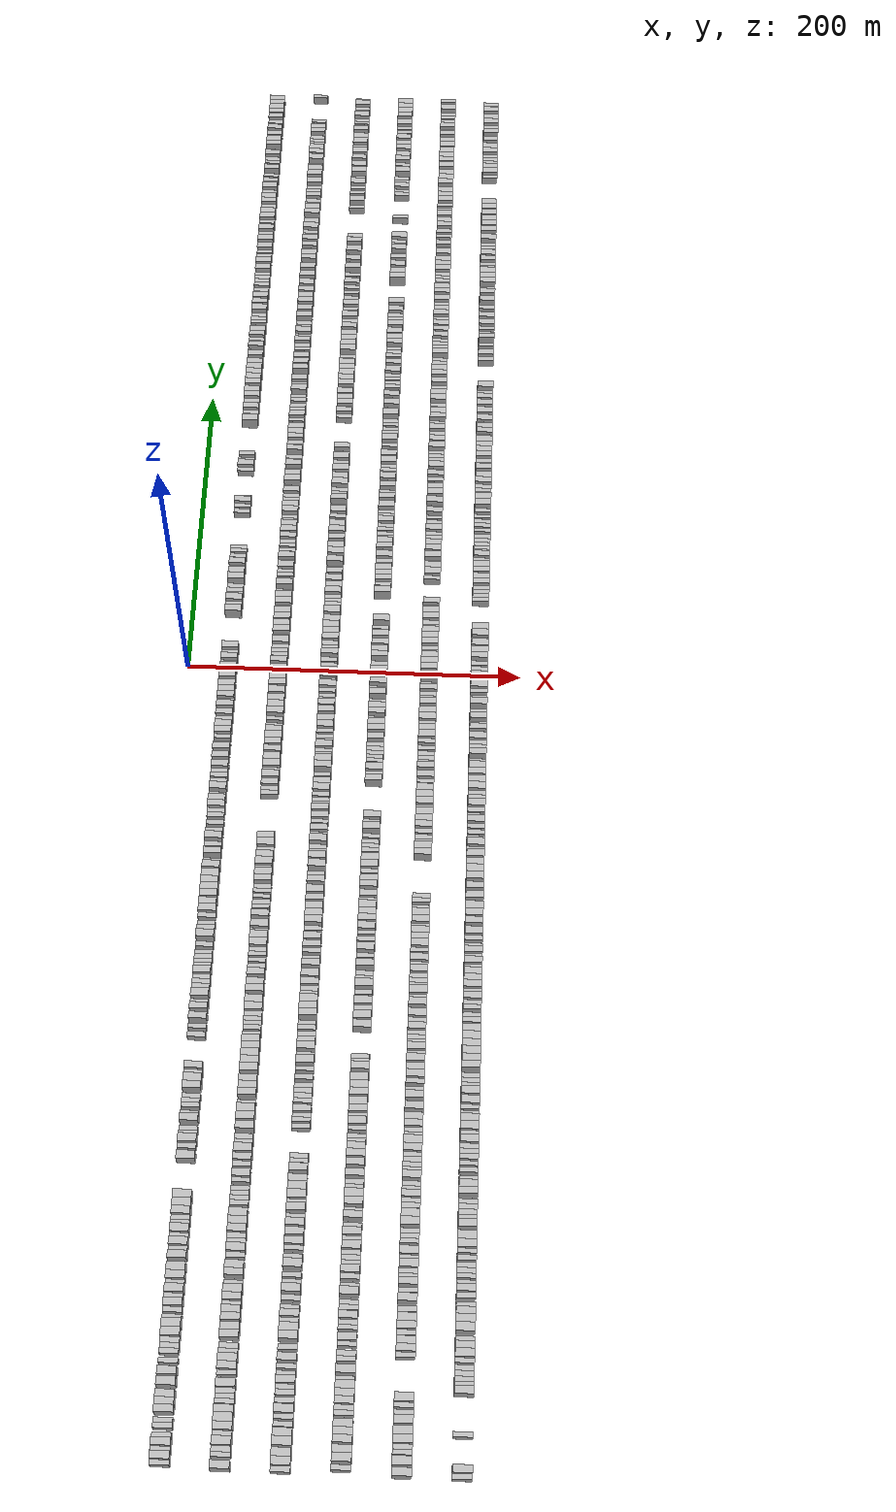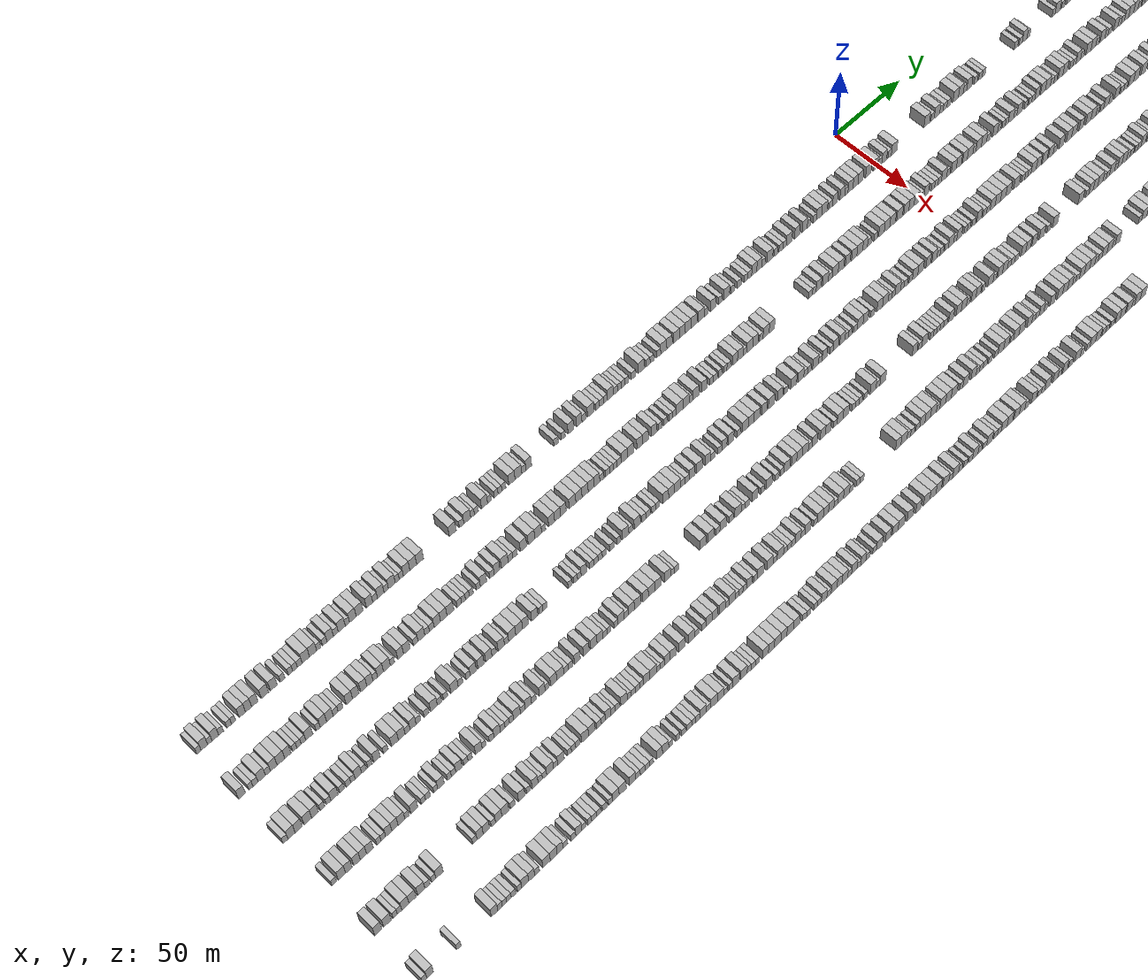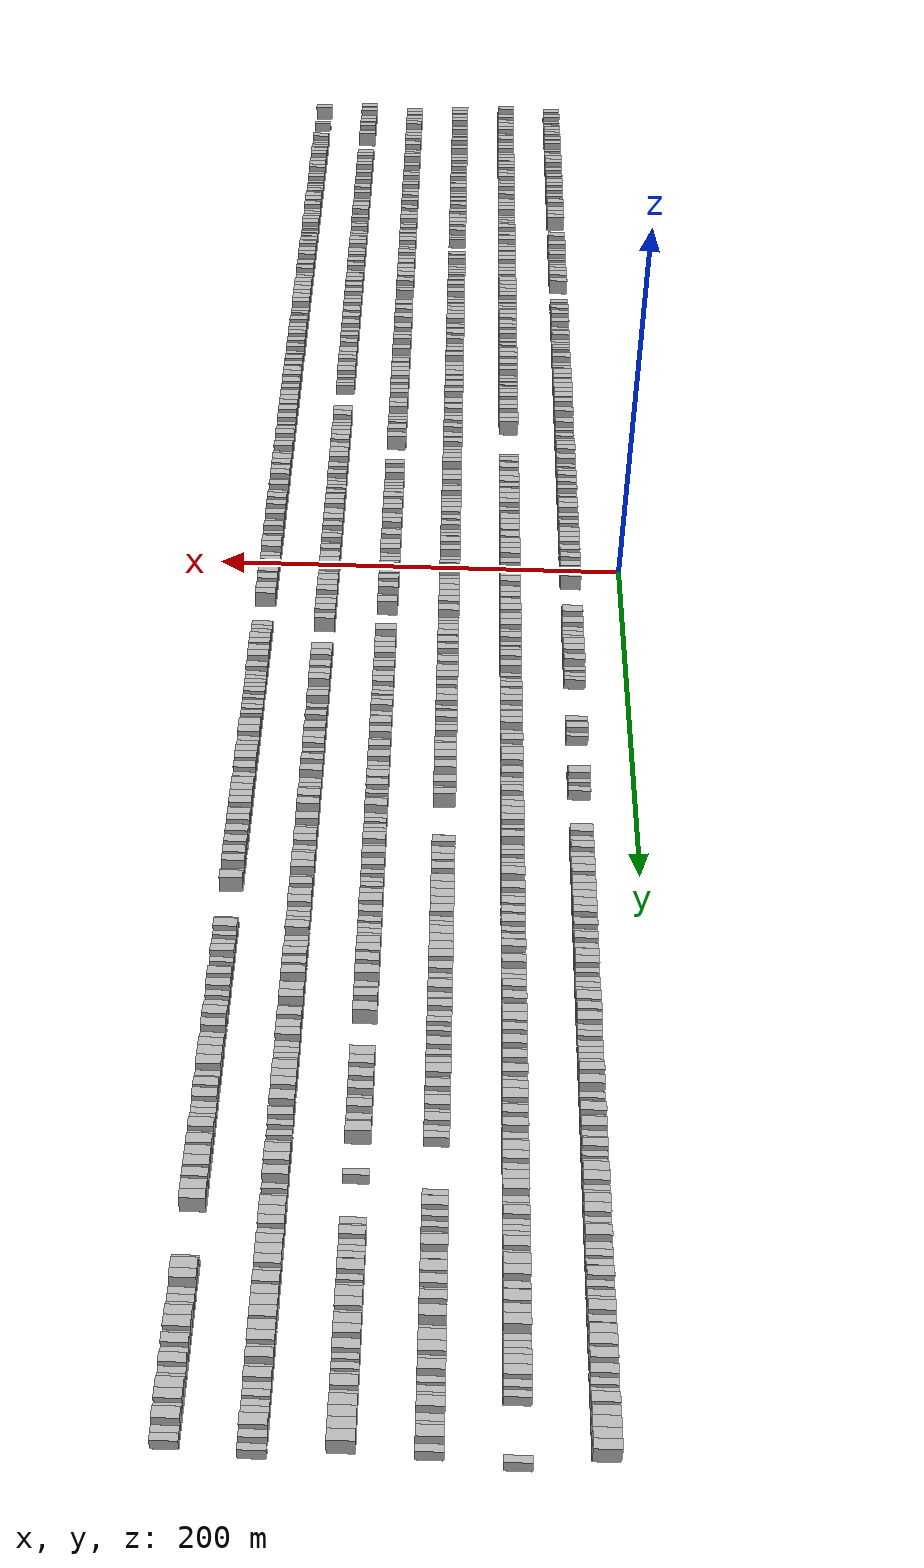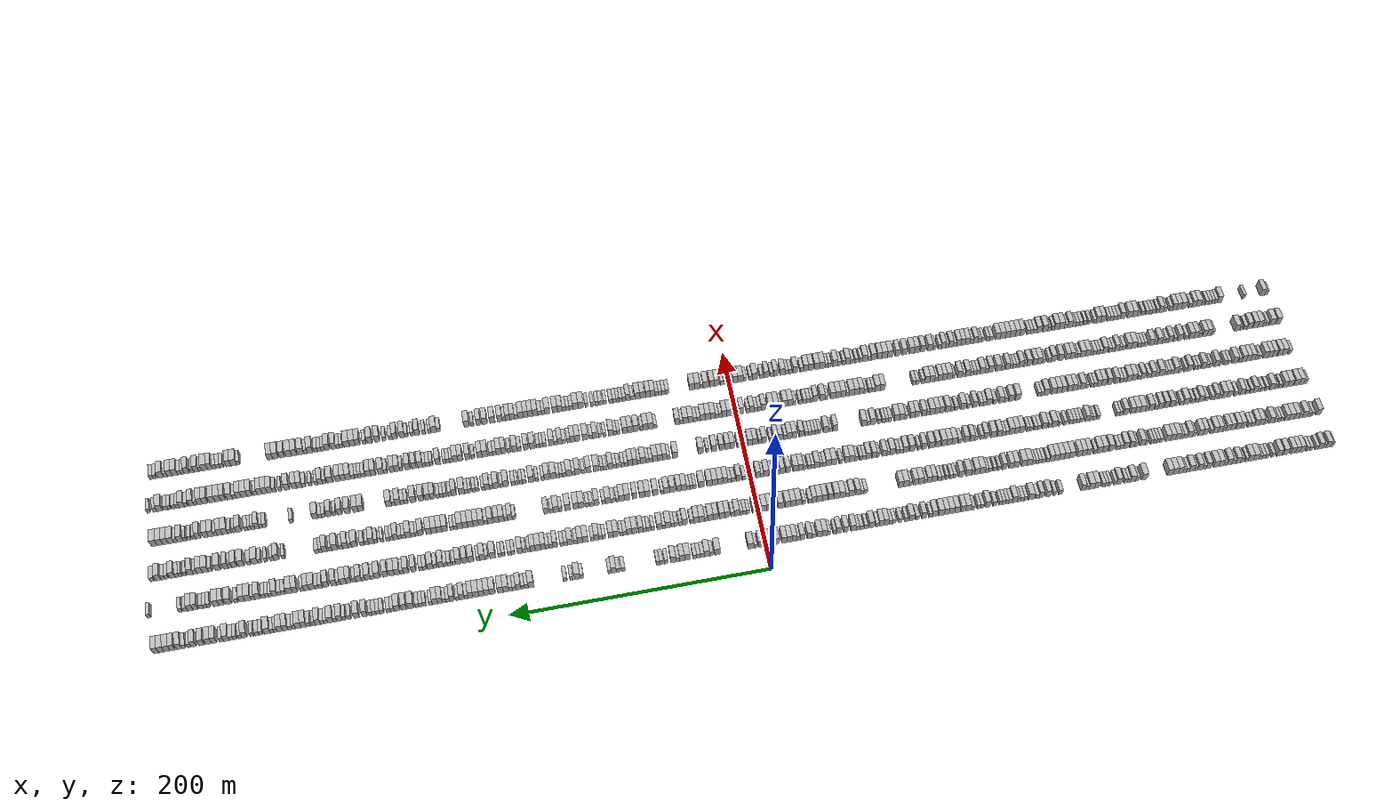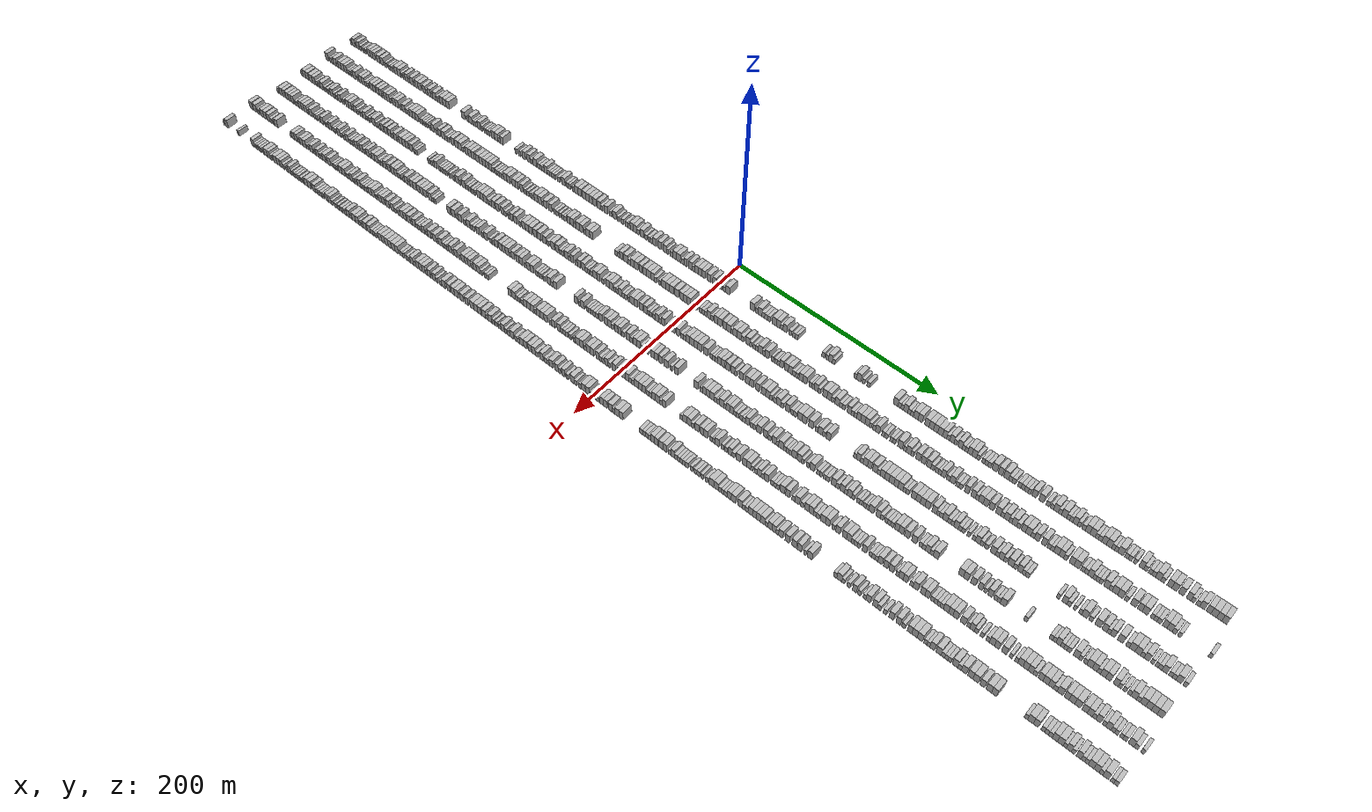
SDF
<sdf version="1.6">
 <world name="default">
  <scene>
   <sky><clouds><speed>12</speed></clouds></sky>
   <ambient>0.4 0.4 0.4 1</ambient>
   <background>0.7 0.7 0.7 1</background>
   <shadows>1</shadows>
  </scene>
  <gravity>0 0 -9.8066</gravity>
  <magnetic_field>6e-06 2.3e-05 -4.2e-05</magnetic_field>
  <physics default="0" name="default_physics" type="ode">
   <ode>
    <solver>
     <type>quick</type>
     <iters>10</iters>
     <sor>1.0</sor>
     <use_dynamic_moi_rescaling>0</use_dynamic_moi_rescaling>
    </solver>
    <constraints>
     <cfm>0</cfm>
     <erp>0.2</erp>
     <contact_max_correcting_vel>100</contact_max_correcting_vel>
     <contact_surface_layer>0.001</contact_surface_layer>
    </constraints>
   </ode>
   <max_step_size>0.004</max_step_size>
   <real_time_factor>1</real_time_factor>
   <real_time_update_rate>250</real_time_update_rate>
  </physics>
  <light name="sun" type="directional">
   <pose>0 0 10 0 0 0</pose>
   <diffuse>0.8 0.8 0.8 1</diffuse>
   <specular>0.2 0.2 0.2 1</specular>
   <attenuation>
    <range>1000</range>
    <constant>0.9</constant>
    <linear>0.01</linear>
    <quadratic>0.001</quadratic>
   </attenuation>
   <direction>-0.5 0.1 -0.9</direction>
  </light>
  <model name="building_1">
   <static>1</static>
   <pose>25.0000 -457.7457 0 0.000000 0.000000 0.000000</pose>
   <link name="link">
    <pose>0 0 3.00 0 0 0</pose>
    <collision name="collision"><geometry><box><size>10.0000 2.5086 6.0000</size></box></geometry></collision>
    <visual name="visual">
     <cast_shadows>0</cast_shadows>
     <geometry><box><size>10.0000 2.5086 6.0000</size></box></geometry>
     <material>
      <script>
       <uri>model://HANNAS_wall/materials/scripts</uri>
       <uri>model://HANNAS_wall/materials/textures</uri>
       <name>vrc/HANNAS_wall</name>
      </script>
     </material>
    </visual>
   </link>
  </model>
  <model name="building_2">
   <static>1</static>
   <pose>25.0000 -454.5557 0 0.000000 0.000000 0.000000</pose>
   <link name="link">
    <pose>0 0 4.50 0 0 0</pose>
    <collision name="collision"><geometry><box><size>10.0000 3.8714 9.0000</size></box></geometry></collision>
    <visual name="visual">
     <cast_shadows>0</cast_shadows>
     <geometry><box><size>10.0000 3.8714 9.0000</size></box></geometry>
     <material>
      <script>
       <uri>model://HANNAS_wall/materials/scripts</uri>
       <uri>model://HANNAS_wall/materials/textures</uri>
       <name>vrc/HANNAS_wall</name>
      </script>
     </material>
    </visual>
   </link>
  </model>
  <model name="building_3">
   <static>1</static>
   <pose>25.0000 -451.3285 0 0.000000 0.000000 0.000000</pose>
   <link name="link">
    <pose>0 0 3.00 0 0 0</pose>
    <collision name="collision"><geometry><box><size>10.0000 2.5830 6.0000</size></box></geometry></collision>
    <visual name="visual">
     <cast_shadows>0</cast_shadows>
     <geometry><box><size>10.0000 2.5830 6.0000</size></box></geometry>
     <material>
      <script>
       <uri>model://HANNAS_wall/materials/scripts</uri>
       <uri>model://HANNAS_wall/materials/textures</uri>
       <name>vrc/HANNAS_wall</name>
      </script>
     </material>
    </visual>
   </link>
  </model>
  <model name="building_4">
   <static>1</static>
   <pose>25.0000 -448.1120 0 0.000000 0.000000 0.000000</pose>
   <link name="link">
    <pose>0 0 4.50 0 0 0</pose>
    <collision name="collision"><geometry><box><size>10.0000 3.8501 9.0000</size></box></geometry></collision>
    <visual name="visual">
     <cast_shadows>0</cast_shadows>
     <geometry><box><size>10.0000 3.8501 9.0000</size></box></geometry>
     <material>
      <script>
       <uri>model://HANNAS_wall/materials/scripts</uri>
       <uri>model://HANNAS_wall/materials/textures</uri>
       <name>vrc/HANNAS_wall</name>
      </script>
     </material>
    </visual>
   </link>
  </model>
  <model name="building_5">
   <static>1</static>
   <pose>25.0000 -444.7718 0 0.000000 0.000000 0.000000</pose>
   <link name="link">
    <pose>0 0 3.00 0 0 0</pose>
    <collision name="collision"><geometry><box><size>10.0000 2.8304 6.0000</size></box></geometry></collision>
    <visual name="visual">
     <cast_shadows>0</cast_shadows>
     <geometry><box><size>10.0000 2.8304 6.0000</size></box></geometry>
     <material>
      <script>
       <uri>model://HANNAS_wall/materials/scripts</uri>
       <uri>model://HANNAS_wall/materials/textures</uri>
       <name>vrc/HANNAS_wall</name>
      </script>
     </material>
    </visual>
   </link>
  </model>
  <model name="building_6">
   <static>1</static>
   <pose>25.0000 -440.0034 0 0.000000 0.000000 0.000000</pose>
   <link name="link">
    <pose>0 0 3.00 0 0 0</pose>
    <collision name="collision"><geometry><box><size>10.0000 2.7064 6.0000</size></box></geometry></collision>
    <visual name="visual">
     <cast_shadows>0</cast_shadows>
     <geometry><box><size>10.0000 2.7064 6.0000</size></box></geometry>
     <material>
      <script>
       <uri>model://HANNAS_wall/materials/scripts</uri>
       <uri>model://HANNAS_wall/materials/textures</uri>
       <name>vrc/HANNAS_wall</name>
      </script>
     </material>
    </visual>
   </link>
  </model>
  <model name="building_7">
   <static>1</static>
   <pose>25.0000 -437.4058 0 0.000000 0.000000 0.000000</pose>
   <link name="link">
    <pose>0 0 3.00 0 0 0</pose>
    <collision name="collision"><geometry><box><size>10.0000 2.4887 6.0000</size></box></geometry></collision>
    <visual name="visual">
     <cast_shadows>0</cast_shadows>
     <geometry><box><size>10.0000 2.4887 6.0000</size></box></geometry>
     <material>
      <script>
       <uri>model://HANNAS_wall/materials/scripts</uri>
       <uri>model://HANNAS_wall/materials/textures</uri>
       <name>vrc/HANNAS_wall</name>
      </script>
     </material>
    </visual>
   </link>
  </model>
  <model name="building_8">
   <static>1</static>
   <pose>25.0000 -432.2913 0 0.000000 0.000000 0.000000</pose>
   <link name="link">
    <pose>0 0 4.50 0 0 0</pose>
    <collision name="collision"><geometry><box><size>10.0000 3.7402 9.0000</size></box></geometry></collision>
    <visual name="visual">
     <cast_shadows>0</cast_shadows>
     <geometry><box><size>10.0000 3.7402 9.0000</size></box></geometry>
     <material>
      <script>
       <uri>model://HANNAS_wall/materials/scripts</uri>
       <uri>model://HANNAS_wall/materials/textures</uri>
       <name>vrc/HANNAS_wall</name>
      </script>
     </material>
    </visual>
   </link>
  </model>
  <model name="building_9">
   <static>1</static>
   <pose>25.0000 -428.6102 0 0.000000 0.000000 0.000000</pose>
   <link name="link">
    <pose>0 0 4.50 0 0 0</pose>
    <collision name="collision"><geometry><box><size>10.0000 3.6220 9.0000</size></box></geometry></collision>
    <visual name="visual">
     <cast_shadows>0</cast_shadows>
     <geometry><box><size>10.0000 3.6220 9.0000</size></box></geometry>
     <material>
      <script>
       <uri>model://HANNAS_wall/materials/scripts</uri>
       <uri>model://HANNAS_wall/materials/textures</uri>
       <name>vrc/HANNAS_wall</name>
      </script>
     </material>
    </visual>
   </link>
  </model>
  <model name="building_10">
   <static>1</static>
   <pose>25.0000 -424.9106 0 0.000000 0.000000 0.000000</pose>
   <link name="link">
    <pose>0 0 4.50 0 0 0</pose>
    <collision name="collision"><geometry><box><size>10.0000 3.7773 9.0000</size></box></geometry></collision>
    <visual name="visual">
     <cast_shadows>0</cast_shadows>
     <geometry><box><size>10.0000 3.7773 9.0000</size></box></geometry>
     <material>
      <script>
       <uri>model://HANNAS_wall/materials/scripts</uri>
       <uri>model://HANNAS_wall/materials/textures</uri>
       <name>vrc/HANNAS_wall</name>
      </script>
     </material>
    </visual>
   </link>
  </model>
  <model name="building_11">
   <static>1</static>
   <pose>25.0000 -418.8472 0 0.000000 0.000000 0.000000</pose>
   <link name="link">
    <pose>0 0 4.50 0 0 0</pose>
    <collision name="collision"><geometry><box><size>10.0000 4.3493 9.0000</size></box></geometry></collision>
    <visual name="visual">
     <cast_shadows>0</cast_shadows>
     <geometry><box><size>10.0000 4.3493 9.0000</size></box></geometry>
     <material>
      <script>
       <uri>model://HANNAS_wall/materials/scripts</uri>
       <uri>model://HANNAS_wall/materials/textures</uri>
       <name>vrc/HANNAS_wall</name>
      </script>
     </material>
    </visual>
   </link>
  </model>
  <model name="building_12">
   <static>1</static>
   <pose>25.0000 -413.6309 0 0.000000 0.000000 0.000000</pose>
   <link name="link">
    <pose>0 0 4.50 0 0 0</pose>
    <collision name="collision"><geometry><box><size>10.0000 4.0833 9.0000</size></box></geometry></collision>
    <visual name="visual">
     <cast_shadows>0</cast_shadows>
     <geometry><box><size>10.0000 4.0833 9.0000</size></box></geometry>
     <material>
      <script>
       <uri>model://HANNAS_wall/materials/scripts</uri>
       <uri>model://HANNAS_wall/materials/textures</uri>
       <name>vrc/HANNAS_wall</name>
      </script>
     </material>
    </visual>
   </link>
  </model>
  <model name="building_13">
   <static>1</static>
   <pose>25.0000 -408.2302 0 0.000000 0.000000 0.000000</pose>
   <link name="link">
    <pose>0 0 3.00 0 0 0</pose>
    <collision name="collision"><geometry><box><size>10.0000 2.7181 6.0000</size></box></geometry></collision>
    <visual name="visual">
     <cast_shadows>0</cast_shadows>
     <geometry><box><size>10.0000 2.7181 6.0000</size></box></geometry>
     <material>
      <script>
       <uri>model://HANNAS_wall/materials/scripts</uri>
       <uri>model://HANNAS_wall/materials/textures</uri>
       <name>vrc/HANNAS_wall</name>
      </script>
     </material>
    </visual>
   </link>
  </model>
  <model name="building_14">
   <static>1</static>
   <pose>25.0000 -403.5252 0 0.000000 0.000000 0.000000</pose>
   <link name="link">
    <pose>0 0 3.00 0 0 0</pose>
    <collision name="collision"><geometry><box><size>10.0000 2.6919 6.0000</size></box></geometry></collision>
    <visual name="visual">
     <cast_shadows>0</cast_shadows>
     <geometry><box><size>10.0000 2.6919 6.0000</size></box></geometry>
     <material>
      <script>
       <uri>model://HANNAS_wall/materials/scripts</uri>
       <uri>model://HANNAS_wall/materials/textures</uri>
       <name>vrc/HANNAS_wall</name>
      </script>
     </material>
    </visual>
   </link>
  </model>
  <model name="building_15">
   <static>1</static>
   <pose>25.0000 -400.7834 0 0.000000 0.000000 0.000000</pose>
   <link name="link">
    <pose>0 0 3.00 0 0 0</pose>
    <collision name="collision"><geometry><box><size>10.0000 2.7916 6.0000</size></box></geometry></collision>
    <visual name="visual">
     <cast_shadows>0</cast_shadows>
     <geometry><box><size>10.0000 2.7916 6.0000</size></box></geometry>
     <material>
      <script>
       <uri>model://HANNAS_wall/materials/scripts</uri>
       <uri>model://HANNAS_wall/materials/textures</uri>
       <name>vrc/HANNAS_wall</name>
      </script>
     </material>
    </visual>
   </link>
  </model>
  <model name="building_16">
   <static>1</static>
   <pose>25.0000 -397.9333 0 0.000000 0.000000 0.000000</pose>
   <link name="link">
    <pose>0 0 3.00 0 0 0</pose>
    <collision name="collision"><geometry><box><size>10.0000 2.9087 6.0000</size></box></geometry></collision>
    <visual name="visual">
     <cast_shadows>0</cast_shadows>
     <geometry><box><size>10.0000 2.9087 6.0000</size></box></geometry>
     <material>
      <script>
       <uri>model://HANNAS_wall/materials/scripts</uri>
       <uri>model://HANNAS_wall/materials/textures</uri>
       <name>vrc/HANNAS_wall</name>
      </script>
     </material>
    </visual>
   </link>
  </model>
  <model name="building_17">
   <static>1</static>
   <pose>25.0000 -394.2584 0 0.000000 0.000000 0.000000</pose>
   <link name="link">
    <pose>0 0 4.50 0 0 0</pose>
    <collision name="collision"><geometry><box><size>10.0000 4.4411 9.0000</size></box></geometry></collision>
    <visual name="visual">
     <cast_shadows>0</cast_shadows>
     <geometry><box><size>10.0000 4.4411 9.0000</size></box></geometry>
     <material>
      <script>
       <uri>model://HANNAS_wall/materials/scripts</uri>
       <uri>model://HANNAS_wall/materials/textures</uri>
       <name>vrc/HANNAS_wall</name>
      </script>
     </material>
    </visual>
   </link>
  </model>
  <model name="building_18">
   <static>1</static>
   <pose>25.0000 -389.8638 0 0.000000 0.000000 0.000000</pose>
   <link name="link">
    <pose>0 0 4.50 0 0 0</pose>
    <collision name="collision"><geometry><box><size>10.0000 4.3482 9.0000</size></box></geometry></collision>
    <visual name="visual">
     <cast_shadows>0</cast_shadows>
     <geometry><box><size>10.0000 4.3482 9.0000</size></box></geometry>
     <material>
      <script>
       <uri>model://HANNAS_wall/materials/scripts</uri>
       <uri>model://HANNAS_wall/materials/textures</uri>
       <name>vrc/HANNAS_wall</name>
      </script>
     </material>
    </visual>
   </link>
  </model>
  <model name="building_19">
   <static>1</static>
   <pose>25.0000 -386.4379 0 0.000000 0.000000 0.000000</pose>
   <link name="link">
    <pose>0 0 3.00 0 0 0</pose>
    <collision name="collision"><geometry><box><size>10.0000 2.5035 6.0000</size></box></geometry></collision>
    <visual name="visual">
     <cast_shadows>0</cast_shadows>
     <geometry><box><size>10.0000 2.5035 6.0000</size></box></geometry>
     <material>
      <script>
       <uri>model://HANNAS_wall/materials/scripts</uri>
       <uri>model://HANNAS_wall/materials/textures</uri>
       <name>vrc/HANNAS_wall</name>
      </script>
     </material>
    </visual>
   </link>
  </model>
  <model name="building_20">
   <static>1</static>
   <pose>25.0000 -382.7788 0 0.000000 0.000000 0.000000</pose>
   <link name="link">
    <pose>0 0 3.00 0 0 0</pose>
    <collision name="collision"><geometry><box><size>10.0000 2.8147 6.0000</size></box></geometry></collision>
    <visual name="visual">
     <cast_shadows>0</cast_shadows>
     <geometry><box><size>10.0000 2.8147 6.0000</size></box></geometry>
     <material>
      <script>
       <uri>model://HANNAS_wall/materials/scripts</uri>
       <uri>model://HANNAS_wall/materials/textures</uri>
       <name>vrc/HANNAS_wall</name>
      </script>
     </material>
    </visual>
   </link>
  </model>
  <model name="building_21">
   <static>1</static>
   <pose>25.0000 -379.4013 0 0.000000 0.000000 0.000000</pose>
   <link name="link">
    <pose>0 0 4.50 0 0 0</pose>
    <collision name="collision"><geometry><box><size>10.0000 3.9403 9.0000</size></box></geometry></collision>
    <visual name="visual">
     <cast_shadows>0</cast_shadows>
     <geometry><box><size>10.0000 3.9403 9.0000</size></box></geometry>
     <material>
      <script>
       <uri>model://HANNAS_wall/materials/scripts</uri>
       <uri>model://HANNAS_wall/materials/textures</uri>
       <name>vrc/HANNAS_wall</name>
      </script>
     </material>
    </visual>
   </link>
  </model>
  <model name="building_22">
   <static>1</static>
   <pose>25.0000 -375.9395 0 0.000000 0.000000 0.000000</pose>
   <link name="link">
    <pose>0 0 3.00 0 0 0</pose>
    <collision name="collision"><geometry><box><size>10.0000 2.9834 6.0000</size></box></geometry></collision>
    <visual name="visual">
     <cast_shadows>0</cast_shadows>
     <geometry><box><size>10.0000 2.9834 6.0000</size></box></geometry>
     <material>
      <script>
       <uri>model://HANNAS_wall/materials/scripts</uri>
       <uri>model://HANNAS_wall/materials/textures</uri>
       <name>vrc/HANNAS_wall</name>
      </script>
     </material>
    </visual>
   </link>
  </model>
  <model name="building_23">
   <static>1</static>
   <pose>25.0000 -372.3042 0 0.000000 0.000000 0.000000</pose>
   <link name="link">
    <pose>0 0 4.50 0 0 0</pose>
    <collision name="collision"><geometry><box><size>10.0000 4.2872 9.0000</size></box></geometry></collision>
    <visual name="visual">
     <cast_shadows>0</cast_shadows>
     <geometry><box><size>10.0000 4.2872 9.0000</size></box></geometry>
     <material>
      <script>
       <uri>model://HANNAS_wall/materials/scripts</uri>
       <uri>model://HANNAS_wall/materials/textures</uri>
       <name>vrc/HANNAS_wall</name>
      </script>
     </material>
    </visual>
   </link>
  </model>
  <model name="building_24">
   <static>1</static>
   <pose>25.0000 -368.8440 0 0.000000 0.000000 0.000000</pose>
   <link name="link">
    <pose>0 0 3.00 0 0 0</pose>
    <collision name="collision"><geometry><box><size>10.0000 2.6332 6.0000</size></box></geometry></collision>
    <visual name="visual">
     <cast_shadows>0</cast_shadows>
     <geometry><box><size>10.0000 2.6332 6.0000</size></box></geometry>
     <material>
      <script>
       <uri>model://HANNAS_wall/materials/scripts</uri>
       <uri>model://HANNAS_wall/materials/textures</uri>
       <name>vrc/HANNAS_wall</name>
      </script>
     </material>
    </visual>
   </link>
  </model>
  <model name="building_25">
   <static>1</static>
   <pose>25.0000 -365.4459 0 0.000000 0.000000 0.000000</pose>
   <link name="link">
    <pose>0 0 4.50 0 0 0</pose>
    <collision name="collision"><geometry><box><size>10.0000 4.1630 9.0000</size></box></geometry></collision>
    <visual name="visual">
     <cast_shadows>0</cast_shadows>
     <geometry><box><size>10.0000 4.1630 9.0000</size></box></geometry>
     <material>
      <script>
       <uri>model://HANNAS_wall/materials/scripts</uri>
       <uri>model://HANNAS_wall/materials/textures</uri>
       <name>vrc/HANNAS_wall</name>
      </script>
     </material>
    </visual>
   </link>
  </model>
  <model name="building_26">
   <static>1</static>
   <pose>25.0000 -361.2207 0 0.000000 0.000000 0.000000</pose>
   <link name="link">
    <pose>0 0 4.50 0 0 0</pose>
    <collision name="collision"><geometry><box><size>10.0000 4.2874 9.0000</size></box></geometry></collision>
    <visual name="visual">
     <cast_shadows>0</cast_shadows>
     <geometry><box><size>10.0000 4.2874 9.0000</size></box></geometry>
     <material>
      <script>
       <uri>model://HANNAS_wall/materials/scripts</uri>
       <uri>model://HANNAS_wall/materials/textures</uri>
       <name>vrc/HANNAS_wall</name>
      </script>
     </material>
    </visual>
   </link>
  </model>
  <model name="building_27">
   <static>1</static>
   <pose>25.0000 -355.0844 0 0.000000 0.000000 0.000000</pose>
   <link name="link">
    <pose>0 0 4.50 0 0 0</pose>
    <collision name="collision"><geometry><box><size>10.0000 3.9851 9.0000</size></box></geometry></collision>
    <visual name="visual">
     <cast_shadows>0</cast_shadows>
     <geometry><box><size>10.0000 3.9851 9.0000</size></box></geometry>
     <material>
      <script>
       <uri>model://HANNAS_wall/materials/scripts</uri>
       <uri>model://HANNAS_wall/materials/textures</uri>
       <name>vrc/HANNAS_wall</name>
      </script>
     </material>
    </visual>
   </link>
  </model>
  <model name="building_28">
   <static>1</static>
   <pose>25.0000 -351.6137 0 0.000000 0.000000 0.000000</pose>
   <link name="link">
    <pose>0 0 3.00 0 0 0</pose>
    <collision name="collision"><geometry><box><size>10.0000 2.9562 6.0000</size></box></geometry></collision>
    <visual name="visual">
     <cast_shadows>0</cast_shadows>
     <geometry><box><size>10.0000 2.9562 6.0000</size></box></geometry>
     <material>
      <script>
       <uri>model://HANNAS_wall/materials/scripts</uri>
       <uri>model://HANNAS_wall/materials/textures</uri>
       <name>vrc/HANNAS_wall</name>
      </script>
     </material>
    </visual>
   </link>
  </model>
  <model name="building_29">
   <static>1</static>
   <pose>25.0000 -348.0828 0 0.000000 0.000000 0.000000</pose>
   <link name="link">
    <pose>0 0 4.50 0 0 0</pose>
    <collision name="collision"><geometry><box><size>10.0000 4.1057 9.0000</size></box></geometry></collision>
    <visual name="visual">
     <cast_shadows>0</cast_shadows>
     <geometry><box><size>10.0000 4.1057 9.0000</size></box></geometry>
     <material>
      <script>
       <uri>model://HANNAS_wall/materials/scripts</uri>
       <uri>model://HANNAS_wall/materials/textures</uri>
       <name>vrc/HANNAS_wall</name>
      </script>
     </material>
    </visual>
   </link>
  </model>
  <model name="building_30">
   <static>1</static>
   <pose>25.0000 -344.6505 0 0.000000 0.000000 0.000000</pose>
   <link name="link">
    <pose>0 0 3.00 0 0 0</pose>
    <collision name="collision"><geometry><box><size>10.0000 2.7588 6.0000</size></box></geometry></collision>
    <visual name="visual">
     <cast_shadows>0</cast_shadows>
     <geometry><box><size>10.0000 2.7588 6.0000</size></box></geometry>
     <material>
      <script>
       <uri>model://HANNAS_wall/materials/scripts</uri>
       <uri>model://HANNAS_wall/materials/textures</uri>
       <name>vrc/HANNAS_wall</name>
      </script>
     </material>
    </visual>
   </link>
  </model>
  <model name="building_31">
   <static>1</static>
   <pose>25.0000 -341.1435 0 0.000000 0.000000 0.000000</pose>
   <link name="link">
    <pose>0 0 4.50 0 0 0</pose>
    <collision name="collision"><geometry><box><size>10.0000 4.2553 9.0000</size></box></geometry></collision>
    <visual name="visual">
     <cast_shadows>0</cast_shadows>
     <geometry><box><size>10.0000 4.2553 9.0000</size></box></geometry>
     <material>
      <script>
       <uri>model://HANNAS_wall/materials/scripts</uri>
       <uri>model://HANNAS_wall/materials/textures</uri>
       <name>vrc/HANNAS_wall</name>
      </script>
     </material>
    </visual>
   </link>
  </model>
  <model name="building_32">
   <static>1</static>
   <pose>25.0000 -337.7430 0 0.000000 0.000000 0.000000</pose>
   <link name="link">
    <pose>0 0 3.00 0 0 0</pose>
    <collision name="collision"><geometry><box><size>10.0000 2.5455 6.0000</size></box></geometry></collision>
    <visual name="visual">
     <cast_shadows>0</cast_shadows>
     <geometry><box><size>10.0000 2.5455 6.0000</size></box></geometry>
     <material>
      <script>
       <uri>model://HANNAS_wall/materials/scripts</uri>
       <uri>model://HANNAS_wall/materials/textures</uri>
       <name>vrc/HANNAS_wall</name>
      </script>
     </material>
    </visual>
   </link>
  </model>
  <model name="building_33">
   <static>1</static>
   <pose>25.0000 -335.1756 0 0.000000 0.000000 0.000000</pose>
   <link name="link">
    <pose>0 0 3.00 0 0 0</pose>
    <collision name="collision"><geometry><box><size>10.0000 2.5894 6.0000</size></box></geometry></collision>
    <visual name="visual">
     <cast_shadows>0</cast_shadows>
     <geometry><box><size>10.0000 2.5894 6.0000</size></box></geometry>
     <material>
      <script>
       <uri>model://HANNAS_wall/materials/scripts</uri>
       <uri>model://HANNAS_wall/materials/textures</uri>
       <name>vrc/HANNAS_wall</name>
      </script>
     </material>
    </visual>
   </link>
  </model>
  <model name="building_34">
   <static>1</static>
   <pose>25.0000 -331.8204 0 0.000000 0.000000 0.000000</pose>
   <link name="link">
    <pose>0 0 4.50 0 0 0</pose>
    <collision name="collision"><geometry><box><size>10.0000 4.1209 9.0000</size></box></geometry></collision>
    <visual name="visual">
     <cast_shadows>0</cast_shadows>
     <geometry><box><size>10.0000 4.1209 9.0000</size></box></geometry>
     <material>
      <script>
       <uri>model://HANNAS_wall/materials/scripts</uri>
       <uri>model://HANNAS_wall/materials/textures</uri>
       <name>vrc/HANNAS_wall</name>
      </script>
     </material>
    </visual>
   </link>
  </model>
  <model name="building_35">
   <static>1</static>
   <pose>25.0000 -327.6052 0 0.000000 0.000000 0.000000</pose>
   <link name="link">
    <pose>0 0 4.50 0 0 0</pose>
    <collision name="collision"><geometry><box><size>10.0000 4.3096 9.0000</size></box></geometry></collision>
    <visual name="visual">
     <cast_shadows>0</cast_shadows>
     <geometry><box><size>10.0000 4.3096 9.0000</size></box></geometry>
     <material>
      <script>
       <uri>model://HANNAS_wall/materials/scripts</uri>
       <uri>model://HANNAS_wall/materials/textures</uri>
       <name>vrc/HANNAS_wall</name>
      </script>
     </material>
    </visual>
   </link>
  </model>
  <model name="building_36">
   <static>1</static>
   <pose>25.0000 -323.2583 0 0.000000 0.000000 0.000000</pose>
   <link name="link">
    <pose>0 0 4.50 0 0 0</pose>
    <collision name="collision"><geometry><box><size>10.0000 4.3843 9.0000</size></box></geometry></collision>
    <visual name="visual">
     <cast_shadows>0</cast_shadows>
     <geometry><box><size>10.0000 4.3843 9.0000</size></box></geometry>
     <material>
      <script>
       <uri>model://HANNAS_wall/materials/scripts</uri>
       <uri>model://HANNAS_wall/materials/textures</uri>
       <name>vrc/HANNAS_wall</name>
      </script>
     </material>
    </visual>
   </link>
  </model>
  <model name="building_37">
   <static>1</static>
   <pose>25.0000 -302.3464 0 0.000000 0.000000 0.000000</pose>
   <link name="link">
    <pose>0 0 4.50 0 0 0</pose>
    <collision name="collision"><geometry><box><size>10.0000 4.4798 9.0000</size></box></geometry></collision>
    <visual name="visual">
     <cast_shadows>0</cast_shadows>
     <geometry><box><size>10.0000 4.4798 9.0000</size></box></geometry>
     <material>
      <script>
       <uri>model://HANNAS_wall/materials/scripts</uri>
       <uri>model://HANNAS_wall/materials/textures</uri>
       <name>vrc/HANNAS_wall</name>
      </script>
     </material>
    </visual>
   </link>
  </model>
  <model name="building_38">
   <static>1</static>
   <pose>25.0000 -296.6326 0 0.000000 0.000000 0.000000</pose>
   <link name="link">
    <pose>0 0 3.00 0 0 0</pose>
    <collision name="collision"><geometry><box><size>10.0000 2.9478 6.0000</size></box></geometry></collision>
    <visual name="visual">
     <cast_shadows>0</cast_shadows>
     <geometry><box><size>10.0000 2.9478 6.0000</size></box></geometry>
     <material>
      <script>
       <uri>model://HANNAS_wall/materials/scripts</uri>
       <uri>model://HANNAS_wall/materials/textures</uri>
       <name>vrc/HANNAS_wall</name>
      </script>
     </material>
    </visual>
   </link>
  </model>
  <model name="building_39">
   <static>1</static>
   <pose>25.0000 -292.9393 0 0.000000 0.000000 0.000000</pose>
   <link name="link">
    <pose>0 0 4.50 0 0 0</pose>
    <collision name="collision"><geometry><box><size>10.0000 4.4390 9.0000</size></box></geometry></collision>
    <visual name="visual">
     <cast_shadows>0</cast_shadows>
     <geometry><box><size>10.0000 4.4390 9.0000</size></box></geometry>
     <material>
      <script>
       <uri>model://HANNAS_wall/materials/scripts</uri>
       <uri>model://HANNAS_wall/materials/textures</uri>
       <name>vrc/HANNAS_wall</name>
      </script>
     </material>
    </visual>
   </link>
  </model>
  <model name="building_40">
   <static>1</static>
   <pose>25.0000 -289.5185 0 0.000000 0.000000 0.000000</pose>
   <link name="link">
    <pose>0 0 3.00 0 0 0</pose>
    <collision name="collision"><geometry><box><size>10.0000 2.4026 6.0000</size></box></geometry></collision>
    <visual name="visual">
     <cast_shadows>0</cast_shadows>
     <geometry><box><size>10.0000 2.4026 6.0000</size></box></geometry>
     <material>
      <script>
       <uri>model://HANNAS_wall/materials/scripts</uri>
       <uri>model://HANNAS_wall/materials/textures</uri>
       <name>vrc/HANNAS_wall</name>
      </script>
     </material>
    </visual>
   </link>
  </model>
  <model name="building_41">
   <static>1</static>
   <pose>25.0000 -287.0222 0 0.000000 0.000000 0.000000</pose>
   <link name="link">
    <pose>0 0 3.00 0 0 0</pose>
    <collision name="collision"><geometry><box><size>10.0000 2.5901 6.0000</size></box></geometry></collision>
    <visual name="visual">
     <cast_shadows>0</cast_shadows>
     <geometry><box><size>10.0000 2.5901 6.0000</size></box></geometry>
     <material>
      <script>
       <uri>model://HANNAS_wall/materials/scripts</uri>
       <uri>model://HANNAS_wall/materials/textures</uri>
       <name>vrc/HANNAS_wall</name>
      </script>
     </material>
    </visual>
   </link>
  </model>
  <model name="building_42">
   <static>1</static>
   <pose>25.0000 -281.7307 0 0.000000 0.000000 0.000000</pose>
   <link name="link">
    <pose>0 0 4.50 0 0 0</pose>
    <collision name="collision"><geometry><box><size>10.0000 3.9928 9.0000</size></box></geometry></collision>
    <visual name="visual">
     <cast_shadows>0</cast_shadows>
     <geometry><box><size>10.0000 3.9928 9.0000</size></box></geometry>
     <material>
      <script>
       <uri>model://HANNAS_wall/materials/scripts</uri>
       <uri>model://HANNAS_wall/materials/textures</uri>
       <name>vrc/HANNAS_wall</name>
      </script>
     </material>
    </visual>
   </link>
  </model>
  <model name="building_43">
   <static>1</static>
   <pose>25.0000 -278.5234 0 0.000000 0.000000 0.000000</pose>
   <link name="link">
    <pose>0 0 3.00 0 0 0</pose>
    <collision name="collision"><geometry><box><size>10.0000 2.4219 6.0000</size></box></geometry></collision>
    <visual name="visual">
     <cast_shadows>0</cast_shadows>
     <geometry><box><size>10.0000 2.4219 6.0000</size></box></geometry>
     <material>
      <script>
       <uri>model://HANNAS_wall/materials/scripts</uri>
       <uri>model://HANNAS_wall/materials/textures</uri>
       <name>vrc/HANNAS_wall</name>
      </script>
     </material>
    </visual>
   </link>
  </model>
  <model name="building_44">
   <static>1</static>
   <pose>25.0000 -274.0688 0 0.000000 0.000000 0.000000</pose>
   <link name="link">
    <pose>0 0 3.00 0 0 0</pose>
    <collision name="collision"><geometry><box><size>10.0000 2.4872 6.0000</size></box></geometry></collision>
    <visual name="visual">
     <cast_shadows>0</cast_shadows>
     <geometry><box><size>10.0000 2.4872 6.0000</size></box></geometry>
     <material>
      <script>
       <uri>model://HANNAS_wall/materials/scripts</uri>
       <uri>model://HANNAS_wall/materials/textures</uri>
       <name>vrc/HANNAS_wall</name>
      </script>
     </material>
    </visual>
   </link>
  </model>
  <model name="building_45">
   <static>1</static>
   <pose>25.0000 -271.5663 0 0.000000 0.000000 0.000000</pose>
   <link name="link">
    <pose>0 0 3.00 0 0 0</pose>
    <collision name="collision"><geometry><box><size>10.0000 2.5177 6.0000</size></box></geometry></collision>
    <visual name="visual">
     <cast_shadows>0</cast_shadows>
     <geometry><box><size>10.0000 2.5177 6.0000</size></box></geometry>
     <material>
      <script>
       <uri>model://HANNAS_wall/materials/scripts</uri>
       <uri>model://HANNAS_wall/materials/textures</uri>
       <name>vrc/HANNAS_wall</name>
      </script>
     </material>
    </visual>
   </link>
  </model>
  <model name="building_46">
   <static>1</static>
   <pose>25.0000 -268.9976 0 0.000000 0.000000 0.000000</pose>
   <link name="link">
    <pose>0 0 3.00 0 0 0</pose>
    <collision name="collision"><geometry><box><size>10.0000 2.6197 6.0000</size></box></geometry></collision>
    <visual name="visual">
     <cast_shadows>0</cast_shadows>
     <geometry><box><size>10.0000 2.6197 6.0000</size></box></geometry>
     <material>
      <script>
       <uri>model://HANNAS_wall/materials/scripts</uri>
       <uri>model://HANNAS_wall/materials/textures</uri>
       <name>vrc/HANNAS_wall</name>
      </script>
     </material>
    </visual>
   </link>
  </model>
  <model name="building_47">
   <static>1</static>
   <pose>25.0000 -263.6717 0 0.000000 0.000000 0.000000</pose>
   <link name="link">
    <pose>0 0 4.50 0 0 0</pose>
    <collision name="collision"><geometry><box><size>10.0000 4.0322 9.0000</size></box></geometry></collision>
    <visual name="visual">
     <cast_shadows>0</cast_shadows>
     <geometry><box><size>10.0000 4.0322 9.0000</size></box></geometry>
     <material>
      <script>
       <uri>model://HANNAS_wall/materials/scripts</uri>
       <uri>model://HANNAS_wall/materials/textures</uri>
       <name>vrc/HANNAS_wall</name>
      </script>
     </material>
    </visual>
   </link>
  </model>
  <model name="building_48">
   <static>1</static>
   <pose>25.0000 -259.4059 0 0.000000 0.000000 0.000000</pose>
   <link name="link">
    <pose>0 0 4.50 0 0 0</pose>
    <collision name="collision"><geometry><box><size>10.0000 4.4994 9.0000</size></box></geometry></collision>
    <visual name="visual">
     <cast_shadows>0</cast_shadows>
     <geometry><box><size>10.0000 4.4994 9.0000</size></box></geometry>
     <material>
      <script>
       <uri>model://HANNAS_wall/materials/scripts</uri>
       <uri>model://HANNAS_wall/materials/textures</uri>
       <name>vrc/HANNAS_wall</name>
      </script>
     </material>
    </visual>
   </link>
  </model>
  <model name="building_49">
   <static>1</static>
   <pose>25.0000 -255.7638 0 0.000000 0.000000 0.000000</pose>
   <link name="link">
    <pose>0 0 3.00 0 0 0</pose>
    <collision name="collision"><geometry><box><size>10.0000 2.7847 6.0000</size></box></geometry></collision>
    <visual name="visual">
     <cast_shadows>0</cast_shadows>
     <geometry><box><size>10.0000 2.7847 6.0000</size></box></geometry>
     <material>
      <script>
       <uri>model://HANNAS_wall/materials/scripts</uri>
       <uri>model://HANNAS_wall/materials/textures</uri>
       <name>vrc/HANNAS_wall</name>
      </script>
     </material>
    </visual>
   </link>
  </model>
  <model name="building_50">
   <static>1</static>
   <pose>25.0000 -252.5081 0 0.000000 0.000000 0.000000</pose>
   <link name="link">
    <pose>0 0 4.50 0 0 0</pose>
    <collision name="collision"><geometry><box><size>10.0000 3.7268 9.0000</size></box></geometry></collision>
    <visual name="visual">
     <cast_shadows>0</cast_shadows>
     <geometry><box><size>10.0000 3.7268 9.0000</size></box></geometry>
     <material>
      <script>
       <uri>model://HANNAS_wall/materials/scripts</uri>
       <uri>model://HANNAS_wall/materials/textures</uri>
       <name>vrc/HANNAS_wall</name>
      </script>
     </material>
    </visual>
   </link>
  </model>
  <model name="building_51">
   <static>1</static>
   <pose>25.0000 -234.1834 0 0.000000 0.000000 0.000000</pose>
   <link name="link">
    <pose>0 0 3.00 0 0 0</pose>
    <collision name="collision"><geometry><box><size>10.0000 2.9742 6.0000</size></box></geometry></collision>
    <visual name="visual">
     <cast_shadows>0</cast_shadows>
     <geometry><box><size>10.0000 2.9742 6.0000</size></box></geometry>
     <material>
      <script>
       <uri>model://HANNAS_wall/materials/scripts</uri>
       <uri>model://HANNAS_wall/materials/textures</uri>
       <name>vrc/HANNAS_wall</name>
      </script>
     </material>
    </visual>
   </link>
  </model>
  <model name="building_52">
   <static>1</static>
   <pose>25.0000 -229.3756 0 0.000000 0.000000 0.000000</pose>
   <link name="link">
    <pose>0 0 3.00 0 0 0</pose>
    <collision name="collision"><geometry><box><size>10.0000 2.6413 6.0000</size></box></geometry></collision>
    <visual name="visual">
     <cast_shadows>0</cast_shadows>
     <geometry><box><size>10.0000 2.6413 6.0000</size></box></geometry>
     <material>
      <script>
       <uri>model://HANNAS_wall/materials/scripts</uri>
       <uri>model://HANNAS_wall/materials/textures</uri>
       <name>vrc/HANNAS_wall</name>
      </script>
     </material>
    </visual>
   </link>
  </model>
  <model name="building_53">
   <static>1</static>
   <pose>25.0000 -224.1693 0 0.000000 0.000000 0.000000</pose>
   <link name="link">
    <pose>0 0 4.50 0 0 0</pose>
    <collision name="collision"><geometry><box><size>10.0000 3.7714 9.0000</size></box></geometry></collision>
    <visual name="visual">
     <cast_shadows>0</cast_shadows>
     <geometry><box><size>10.0000 3.7714 9.0000</size></box></geometry>
     <material>
      <script>
       <uri>model://HANNAS_wall/materials/scripts</uri>
       <uri>model://HANNAS_wall/materials/textures</uri>
       <name>vrc/HANNAS_wall</name>
      </script>
     </material>
    </visual>
   </link>
  </model>
  <model name="building_54">
   <static>1</static>
   <pose>25.0000 -218.4559 0 0.000000 0.000000 0.000000</pose>
   <link name="link">
    <pose>0 0 4.50 0 0 0</pose>
    <collision name="collision"><geometry><box><size>10.0000 3.6554 9.0000</size></box></geometry></collision>
    <visual name="visual">
     <cast_shadows>0</cast_shadows>
     <geometry><box><size>10.0000 3.6554 9.0000</size></box></geometry>
     <material>
      <script>
       <uri>model://HANNAS_wall/materials/scripts</uri>
       <uri>model://HANNAS_wall/materials/textures</uri>
       <name>vrc/HANNAS_wall</name>
      </script>
     </material>
    </visual>
   </link>
  </model>
  <model name="building_55">
   <static>1</static>
   <pose>25.0000 -215.2184 0 0.000000 0.000000 0.000000</pose>
   <link name="link">
    <pose>0 0 3.00 0 0 0</pose>
    <collision name="collision"><geometry><box><size>10.0000 2.8195 6.0000</size></box></geometry></collision>
    <visual name="visual">
     <cast_shadows>0</cast_shadows>
     <geometry><box><size>10.0000 2.8195 6.0000</size></box></geometry>
     <material>
      <script>
       <uri>model://HANNAS_wall/materials/scripts</uri>
       <uri>model://HANNAS_wall/materials/textures</uri>
       <name>vrc/HANNAS_wall</name>
      </script>
     </material>
    </visual>
   </link>
  </model>
  <model name="building_56">
   <static>1</static>
   <pose>25.0000 -210.5609 0 0.000000 0.000000 0.000000</pose>
   <link name="link">
    <pose>0 0 4.50 0 0 0</pose>
    <collision name="collision"><geometry><box><size>10.0000 4.4955 9.0000</size></box></geometry></collision>
    <visual name="visual">
     <cast_shadows>0</cast_shadows>
     <geometry><box><size>10.0000 4.4955 9.0000</size></box></geometry>
     <material>
      <script>
       <uri>model://HANNAS_wall/materials/scripts</uri>
       <uri>model://HANNAS_wall/materials/textures</uri>
       <name>vrc/HANNAS_wall</name>
      </script>
     </material>
    </visual>
   </link>
  </model>
  <model name="building_57">
   <static>1</static>
   <pose>25.0000 -205.9289 0 0.000000 0.000000 0.000000</pose>
   <link name="link">
    <pose>0 0 3.00 0 0 0</pose>
    <collision name="collision"><geometry><box><size>10.0000 2.7685 6.0000</size></box></geometry></collision>
    <visual name="visual">
     <cast_shadows>0</cast_shadows>
     <geometry><box><size>10.0000 2.7685 6.0000</size></box></geometry>
     <material>
      <script>
       <uri>model://HANNAS_wall/materials/scripts</uri>
       <uri>model://HANNAS_wall/materials/textures</uri>
       <name>vrc/HANNAS_wall</name>
      </script>
     </material>
    </visual>
   </link>
  </model>
  <model name="building_58">
   <static>1</static>
   <pose>25.0000 -203.1325 0 0.000000 0.000000 0.000000</pose>
   <link name="link">
    <pose>0 0 3.00 0 0 0</pose>
    <collision name="collision"><geometry><box><size>10.0000 2.8243 6.0000</size></box></geometry></collision>
    <visual name="visual">
     <cast_shadows>0</cast_shadows>
     <geometry><box><size>10.0000 2.8243 6.0000</size></box></geometry>
     <material>
      <script>
       <uri>model://HANNAS_wall/materials/scripts</uri>
       <uri>model://HANNAS_wall/materials/textures</uri>
       <name>vrc/HANNAS_wall</name>
      </script>
     </material>
    </visual>
   </link>
  </model>
  <model name="building_59">
   <static>1</static>
   <pose>25.0000 -200.4488 0 0.000000 0.000000 0.000000</pose>
   <link name="link">
    <pose>0 0 3.00 0 0 0</pose>
    <collision name="collision"><geometry><box><size>10.0000 2.5430 6.0000</size></box></geometry></collision>
    <visual name="visual">
     <cast_shadows>0</cast_shadows>
     <geometry><box><size>10.0000 2.5430 6.0000</size></box></geometry>
     <material>
      <script>
       <uri>model://HANNAS_wall/materials/scripts</uri>
       <uri>model://HANNAS_wall/materials/textures</uri>
       <name>vrc/HANNAS_wall</name>
      </script>
     </material>
    </visual>
   </link>
  </model>
  <model name="building_60">
   <static>1</static>
   <pose>25.0000 -197.1467 0 0.000000 0.000000 0.000000</pose>
   <link name="link">
    <pose>0 0 4.50 0 0 0</pose>
    <collision name="collision"><geometry><box><size>10.0000 4.0612 9.0000</size></box></geometry></collision>
    <visual name="visual">
     <cast_shadows>0</cast_shadows>
     <geometry><box><size>10.0000 4.0612 9.0000</size></box></geometry>
     <material>
      <script>
       <uri>model://HANNAS_wall/materials/scripts</uri>
       <uri>model://HANNAS_wall/materials/textures</uri>
       <name>vrc/HANNAS_wall</name>
      </script>
     </material>
    </visual>
   </link>
  </model>
  <model name="building_61">
   <static>1</static>
   <pose>25.0000 -193.6598 0 0.000000 0.000000 0.000000</pose>
   <link name="link">
    <pose>0 0 3.00 0 0 0</pose>
    <collision name="collision"><geometry><box><size>10.0000 2.9126 6.0000</size></box></geometry></collision>
    <visual name="visual">
     <cast_shadows>0</cast_shadows>
     <geometry><box><size>10.0000 2.9126 6.0000</size></box></geometry>
     <material>
      <script>
       <uri>model://HANNAS_wall/materials/scripts</uri>
       <uri>model://HANNAS_wall/materials/textures</uri>
       <name>vrc/HANNAS_wall</name>
      </script>
     </material>
    </visual>
   </link>
  </model>
  <model name="building_62">
   <static>1</static>
   <pose>25.0000 -190.9845 0 0.000000 0.000000 0.000000</pose>
   <link name="link">
    <pose>0 0 3.00 0 0 0</pose>
    <collision name="collision"><geometry><box><size>10.0000 2.4381 6.0000</size></box></geometry></collision>
    <visual name="visual">
     <cast_shadows>0</cast_shadows>
     <geometry><box><size>10.0000 2.4381 6.0000</size></box></geometry>
     <material>
      <script>
       <uri>model://HANNAS_wall/materials/scripts</uri>
       <uri>model://HANNAS_wall/materials/textures</uri>
       <name>vrc/HANNAS_wall</name>
      </script>
     </material>
    </visual>
   </link>
  </model>
  <model name="building_63">
   <static>1</static>
   <pose>25.0000 -188.3948 0 0.000000 0.000000 0.000000</pose>
   <link name="link">
    <pose>0 0 3.00 0 0 0</pose>
    <collision name="collision"><geometry><box><size>10.0000 2.7412 6.0000</size></box></geometry></collision>
    <visual name="visual">
     <cast_shadows>0</cast_shadows>
     <geometry><box><size>10.0000 2.7412 6.0000</size></box></geometry>
     <material>
      <script>
       <uri>model://HANNAS_wall/materials/scripts</uri>
       <uri>model://HANNAS_wall/materials/textures</uri>
       <name>vrc/HANNAS_wall</name>
      </script>
     </material>
    </visual>
   </link>
  </model>
  <model name="building_64">
   <static>1</static>
   <pose>25.0000 -185.8143 0 0.000000 0.000000 0.000000</pose>
   <link name="link">
    <pose>0 0 3.00 0 0 0</pose>
    <collision name="collision"><geometry><box><size>10.0000 2.4200 6.0000</size></box></geometry></collision>
    <visual name="visual">
     <cast_shadows>0</cast_shadows>
     <geometry><box><size>10.0000 2.4200 6.0000</size></box></geometry>
     <material>
      <script>
       <uri>model://HANNAS_wall/materials/scripts</uri>
       <uri>model://HANNAS_wall/materials/textures</uri>
       <name>vrc/HANNAS_wall</name>
      </script>
     </material>
    </visual>
   </link>
  </model>
  <model name="building_65">
   <static>1</static>
   <pose>25.0000 -181.1147 0 0.000000 0.000000 0.000000</pose>
   <link name="link">
    <pose>0 0 3.00 0 0 0</pose>
    <collision name="collision"><geometry><box><size>10.0000 2.9792 6.0000</size></box></geometry></collision>
    <visual name="visual">
     <cast_shadows>0</cast_shadows>
     <geometry><box><size>10.0000 2.9792 6.0000</size></box></geometry>
     <material>
      <script>
       <uri>model://HANNAS_wall/materials/scripts</uri>
       <uri>model://HANNAS_wall/materials/textures</uri>
       <name>vrc/HANNAS_wall</name>
      </script>
     </material>
    </visual>
   </link>
  </model>
  <model name="building_66">
   <static>1</static>
   <pose>25.0000 -175.5113 0 0.000000 0.000000 0.000000</pose>
   <link name="link">
    <pose>0 0 4.50 0 0 0</pose>
    <collision name="collision"><geometry><box><size>10.0000 4.2276 9.0000</size></box></geometry></collision>
    <visual name="visual">
     <cast_shadows>0</cast_shadows>
     <geometry><box><size>10.0000 4.2276 9.0000</size></box></geometry>
     <material>
      <script>
       <uri>model://HANNAS_wall/materials/scripts</uri>
       <uri>model://HANNAS_wall/materials/textures</uri>
       <name>vrc/HANNAS_wall</name>
      </script>
     </material>
    </visual>
   </link>
  </model>
  <model name="building_67">
   <static>1</static>
   <pose>25.0000 -170.9420 0 0.000000 0.000000 0.000000</pose>
   <link name="link">
    <pose>0 0 3.00 0 0 0</pose>
    <collision name="collision"><geometry><box><size>10.0000 2.9110 6.0000</size></box></geometry></collision>
    <visual name="visual">
     <cast_shadows>0</cast_shadows>
     <geometry><box><size>10.0000 2.9110 6.0000</size></box></geometry>
     <material>
      <script>
       <uri>model://HANNAS_wall/materials/scripts</uri>
       <uri>model://HANNAS_wall/materials/textures</uri>
       <name>vrc/HANNAS_wall</name>
      </script>
     </material>
    </visual>
   </link>
  </model>
  <model name="building_68">
   <static>1</static>
   <pose>25.0000 -168.2337 0 0.000000 0.000000 0.000000</pose>
   <link name="link">
    <pose>0 0 3.00 0 0 0</pose>
    <collision name="collision"><geometry><box><size>10.0000 2.5056 6.0000</size></box></geometry></collision>
    <visual name="visual">
     <cast_shadows>0</cast_shadows>
     <geometry><box><size>10.0000 2.5056 6.0000</size></box></geometry>
     <material>
      <script>
       <uri>model://HANNAS_wall/materials/scripts</uri>
       <uri>model://HANNAS_wall/materials/textures</uri>
       <name>vrc/HANNAS_wall</name>
      </script>
     </material>
    </visual>
   </link>
  </model>
  <model name="building_69">
   <static>1</static>
   <pose>25.0000 -163.5048 0 0.000000 0.000000 0.000000</pose>
   <link name="link">
    <pose>0 0 3.00 0 0 0</pose>
    <collision name="collision"><geometry><box><size>10.0000 2.9521 6.0000</size></box></geometry></collision>
    <visual name="visual">
     <cast_shadows>0</cast_shadows>
     <geometry><box><size>10.0000 2.9521 6.0000</size></box></geometry>
     <material>
      <script>
       <uri>model://HANNAS_wall/materials/scripts</uri>
       <uri>model://HANNAS_wall/materials/textures</uri>
       <name>vrc/HANNAS_wall</name>
      </script>
     </material>
    </visual>
   </link>
  </model>
  <model name="building_70">
   <static>1</static>
   <pose>25.0000 -159.8549 0 0.000000 0.000000 0.000000</pose>
   <link name="link">
    <pose>0 0 4.50 0 0 0</pose>
    <collision name="collision"><geometry><box><size>10.0000 4.3478 9.0000</size></box></geometry></collision>
    <visual name="visual">
     <cast_shadows>0</cast_shadows>
     <geometry><box><size>10.0000 4.3478 9.0000</size></box></geometry>
     <material>
      <script>
       <uri>model://HANNAS_wall/materials/scripts</uri>
       <uri>model://HANNAS_wall/materials/textures</uri>
       <name>vrc/HANNAS_wall</name>
      </script>
     </material>
    </visual>
   </link>
  </model>
  <model name="building_71">
   <static>1</static>
   <pose>25.0000 -155.7763 0 0.000000 0.000000 0.000000</pose>
   <link name="link">
    <pose>0 0 4.50 0 0 0</pose>
    <collision name="collision"><geometry><box><size>10.0000 3.8095 9.0000</size></box></geometry></collision>
    <visual name="visual">
     <cast_shadows>0</cast_shadows>
     <geometry><box><size>10.0000 3.8095 9.0000</size></box></geometry>
     <material>
      <script>
       <uri>model://HANNAS_wall/materials/scripts</uri>
       <uri>model://HANNAS_wall/materials/textures</uri>
       <name>vrc/HANNAS_wall</name>
      </script>
     </material>
    </visual>
   </link>
  </model>
  <model name="building_72">
   <static>1</static>
   <pose>25.0000 -150.8501 0 0.000000 0.000000 0.000000</pose>
   <link name="link">
    <pose>0 0 4.50 0 0 0</pose>
    <collision name="collision"><geometry><box><size>10.0000 4.0429 9.0000</size></box></geometry></collision>
    <visual name="visual">
     <cast_shadows>0</cast_shadows>
     <geometry><box><size>10.0000 4.0429 9.0000</size></box></geometry>
     <material>
      <script>
       <uri>model://HANNAS_wall/materials/scripts</uri>
       <uri>model://HANNAS_wall/materials/textures</uri>
       <name>vrc/HANNAS_wall</name>
      </script>
     </material>
    </visual>
   </link>
  </model>
  <model name="building_73">
   <static>1</static>
   <pose>25.0000 -146.6563 0 0.000000 0.000000 0.000000</pose>
   <link name="link">
    <pose>0 0 4.50 0 0 0</pose>
    <collision name="collision"><geometry><box><size>10.0000 4.3446 9.0000</size></box></geometry></collision>
    <visual name="visual">
     <cast_shadows>0</cast_shadows>
     <geometry><box><size>10.0000 4.3446 9.0000</size></box></geometry>
     <material>
      <script>
       <uri>model://HANNAS_wall/materials/scripts</uri>
       <uri>model://HANNAS_wall/materials/textures</uri>
       <name>vrc/HANNAS_wall</name>
      </script>
     </material>
    </visual>
   </link>
  </model>
  <model name="building_74">
   <static>1</static>
   <pose>25.0000 -142.5463 0 0.000000 0.000000 0.000000</pose>
   <link name="link">
    <pose>0 0 4.50 0 0 0</pose>
    <collision name="collision"><geometry><box><size>10.0000 3.8754 9.0000</size></box></geometry></collision>
    <visual name="visual">
     <cast_shadows>0</cast_shadows>
     <geometry><box><size>10.0000 3.8754 9.0000</size></box></geometry>
     <material>
      <script>
       <uri>model://HANNAS_wall/materials/scripts</uri>
       <uri>model://HANNAS_wall/materials/textures</uri>
       <name>vrc/HANNAS_wall</name>
      </script>
     </material>
    </visual>
   </link>
  </model>
  <model name="building_75">
   <static>1</static>
   <pose>25.0000 -138.3824 0 0.000000 0.000000 0.000000</pose>
   <link name="link">
    <pose>0 0 4.50 0 0 0</pose>
    <collision name="collision"><geometry><box><size>10.0000 4.4525 9.0000</size></box></geometry></collision>
    <visual name="visual">
     <cast_shadows>0</cast_shadows>
     <geometry><box><size>10.0000 4.4525 9.0000</size></box></geometry>
     <material>
      <script>
       <uri>model://HANNAS_wall/materials/scripts</uri>
       <uri>model://HANNAS_wall/materials/textures</uri>
       <name>vrc/HANNAS_wall</name>
      </script>
     </material>
    </visual>
   </link>
  </model>
  <model name="building_76">
   <static>1</static>
   <pose>25.0000 -133.0756 0 0.000000 0.000000 0.000000</pose>
   <link name="link">
    <pose>0 0 4.50 0 0 0</pose>
    <collision name="collision"><geometry><box><size>10.0000 4.1610 9.0000</size></box></geometry></collision>
    <visual name="visual">
     <cast_shadows>0</cast_shadows>
     <geometry><box><size>10.0000 4.1610 9.0000</size></box></geometry>
     <material>
      <script>
       <uri>model://HANNAS_wall/materials/scripts</uri>
       <uri>model://HANNAS_wall/materials/textures</uri>
       <name>vrc/HANNAS_wall</name>
      </script>
     </material>
    </visual>
   </link>
  </model>
  <model name="building_77">
   <static>1</static>
   <pose>25.0000 -129.6955 0 0.000000 0.000000 0.000000</pose>
   <link name="link">
    <pose>0 0 3.00 0 0 0</pose>
    <collision name="collision"><geometry><box><size>10.0000 2.5992 6.0000</size></box></geometry></collision>
    <visual name="visual">
     <cast_shadows>0</cast_shadows>
     <geometry><box><size>10.0000 2.5992 6.0000</size></box></geometry>
     <material>
      <script>
       <uri>model://HANNAS_wall/materials/scripts</uri>
       <uri>model://HANNAS_wall/materials/textures</uri>
       <name>vrc/HANNAS_wall</name>
      </script>
     </material>
    </visual>
   </link>
  </model>
  <model name="building_78">
   <static>1</static>
   <pose>25.0000 -124.5091 0 0.000000 0.000000 0.000000</pose>
   <link name="link">
    <pose>0 0 4.50 0 0 0</pose>
    <collision name="collision"><geometry><box><size>10.0000 3.7737 9.0000</size></box></geometry></collision>
    <visual name="visual">
     <cast_shadows>0</cast_shadows>
     <geometry><box><size>10.0000 3.7737 9.0000</size></box></geometry>
     <material>
      <script>
       <uri>model://HANNAS_wall/materials/scripts</uri>
       <uri>model://HANNAS_wall/materials/textures</uri>
       <name>vrc/HANNAS_wall</name>
      </script>
     </material>
    </visual>
   </link>
  </model>
  <model name="building_79">
   <static>1</static>
   <pose>25.0000 -119.2365 0 0.000000 0.000000 0.000000</pose>
   <link name="link">
    <pose>0 0 3.00 0 0 0</pose>
    <collision name="collision"><geometry><box><size>10.0000 2.7715 6.0000</size></box></geometry></collision>
    <visual name="visual">
     <cast_shadows>0</cast_shadows>
     <geometry><box><size>10.0000 2.7715 6.0000</size></box></geometry>
     <material>
      <script>
       <uri>model://HANNAS_wall/materials/scripts</uri>
       <uri>model://HANNAS_wall/materials/textures</uri>
       <name>vrc/HANNAS_wall</name>
      </script>
     </material>
    </visual>
   </link>
  </model>
  <model name="building_80">
   <static>1</static>
   <pose>25.0000 -114.7443 0 0.000000 0.000000 0.000000</pose>
   <link name="link">
    <pose>0 0 4.50 0 0 0</pose>
    <collision name="collision"><geometry><box><size>10.0000 4.2129 9.0000</size></box></geometry></collision>
    <visual name="visual">
     <cast_shadows>0</cast_shadows>
     <geometry><box><size>10.0000 4.2129 9.0000</size></box></geometry>
     <material>
      <script>
       <uri>model://HANNAS_wall/materials/scripts</uri>
       <uri>model://HANNAS_wall/materials/textures</uri>
       <name>vrc/HANNAS_wall</name>
      </script>
     </material>
    </visual>
   </link>
  </model>
  <model name="building_81">
   <static>1</static>
   <pose>25.0000 -110.3164 0 0.000000 0.000000 0.000000</pose>
   <link name="link">
    <pose>0 0 3.00 0 0 0</pose>
    <collision name="collision"><geometry><box><size>10.0000 2.6429 6.0000</size></box></geometry></collision>
    <visual name="visual">
     <cast_shadows>0</cast_shadows>
     <geometry><box><size>10.0000 2.6429 6.0000</size></box></geometry>
     <material>
      <script>
       <uri>model://HANNAS_wall/materials/scripts</uri>
       <uri>model://HANNAS_wall/materials/textures</uri>
       <name>vrc/HANNAS_wall</name>
      </script>
     </material>
    </visual>
   </link>
  </model>
  <model name="building_82">
   <static>1</static>
   <pose>25.0000 -105.5333 0 0.000000 0.000000 0.000000</pose>
   <link name="link">
    <pose>0 0 3.00 0 0 0</pose>
    <collision name="collision"><geometry><box><size>10.0000 2.9233 6.0000</size></box></geometry></collision>
    <visual name="visual">
     <cast_shadows>0</cast_shadows>
     <geometry><box><size>10.0000 2.9233 6.0000</size></box></geometry>
     <material>
      <script>
       <uri>model://HANNAS_wall/materials/scripts</uri>
       <uri>model://HANNAS_wall/materials/textures</uri>
       <name>vrc/HANNAS_wall</name>
      </script>
     </material>
    </visual>
   </link>
  </model>
  <model name="building_83">
   <static>1</static>
   <pose>25.0000 -100.6681 0 0.000000 0.000000 0.000000</pose>
   <link name="link">
    <pose>0 0 3.00 0 0 0</pose>
    <collision name="collision"><geometry><box><size>10.0000 2.8071 6.0000</size></box></geometry></collision>
    <visual name="visual">
     <cast_shadows>0</cast_shadows>
     <geometry><box><size>10.0000 2.8071 6.0000</size></box></geometry>
     <material>
      <script>
       <uri>model://HANNAS_wall/materials/scripts</uri>
       <uri>model://HANNAS_wall/materials/textures</uri>
       <name>vrc/HANNAS_wall</name>
      </script>
     </material>
    </visual>
   </link>
  </model>
  <model name="building_84">
   <static>1</static>
   <pose>25.0000 -97.8530 0 0.000000 0.000000 0.000000</pose>
   <link name="link">
    <pose>0 0 3.00 0 0 0</pose>
    <collision name="collision"><geometry><box><size>10.0000 2.8232 6.0000</size></box></geometry></collision>
    <visual name="visual">
     <cast_shadows>0</cast_shadows>
     <geometry><box><size>10.0000 2.8232 6.0000</size></box></geometry>
     <material>
      <script>
       <uri>model://HANNAS_wall/materials/scripts</uri>
       <uri>model://HANNAS_wall/materials/textures</uri>
       <name>vrc/HANNAS_wall</name>
      </script>
     </material>
    </visual>
   </link>
  </model>
  <model name="building_85">
   <static>1</static>
   <pose>25.0000 -94.5358 0 0.000000 0.000000 0.000000</pose>
   <link name="link">
    <pose>0 0 4.50 0 0 0</pose>
    <collision name="collision"><geometry><box><size>10.0000 3.8111 9.0000</size></box></geometry></collision>
    <visual name="visual">
     <cast_shadows>0</cast_shadows>
     <geometry><box><size>10.0000 3.8111 9.0000</size></box></geometry>
     <material>
      <script>
       <uri>model://HANNAS_wall/materials/scripts</uri>
       <uri>model://HANNAS_wall/materials/textures</uri>
       <name>vrc/HANNAS_wall</name>
      </script>
     </material>
    </visual>
   </link>
  </model>
  <model name="building_86">
   <static>1</static>
   <pose>25.0000 -90.7460 0 0.000000 0.000000 0.000000</pose>
   <link name="link">
    <pose>0 0 4.50 0 0 0</pose>
    <collision name="collision"><geometry><box><size>10.0000 3.7685 9.0000</size></box></geometry></collision>
    <visual name="visual">
     <cast_shadows>0</cast_shadows>
     <geometry><box><size>10.0000 3.7685 9.0000</size></box></geometry>
     <material>
      <script>
       <uri>model://HANNAS_wall/materials/scripts</uri>
       <uri>model://HANNAS_wall/materials/textures</uri>
       <name>vrc/HANNAS_wall</name>
      </script>
     </material>
    </visual>
   </link>
  </model>
  <model name="building_87">
   <static>1</static>
   <pose>25.0000 -87.5354 0 0.000000 0.000000 0.000000</pose>
   <link name="link">
    <pose>0 0 3.00 0 0 0</pose>
    <collision name="collision"><geometry><box><size>10.0000 2.6526 6.0000</size></box></geometry></collision>
    <visual name="visual">
     <cast_shadows>0</cast_shadows>
     <geometry><box><size>10.0000 2.6526 6.0000</size></box></geometry>
     <material>
      <script>
       <uri>model://HANNAS_wall/materials/scripts</uri>
       <uri>model://HANNAS_wall/materials/textures</uri>
       <name>vrc/HANNAS_wall</name>
      </script>
     </material>
    </visual>
   </link>
  </model>
  <model name="building_88">
   <static>1</static>
   <pose>25.0000 -83.0383 0 0.000000 0.000000 0.000000</pose>
   <link name="link">
    <pose>0 0 4.50 0 0 0</pose>
    <collision name="collision"><geometry><box><size>10.0000 4.3418 9.0000</size></box></geometry></collision>
    <visual name="visual">
     <cast_shadows>0</cast_shadows>
     <geometry><box><size>10.0000 4.3418 9.0000</size></box></geometry>
     <material>
      <script>
       <uri>model://HANNAS_wall/materials/scripts</uri>
       <uri>model://HANNAS_wall/materials/textures</uri>
       <name>vrc/HANNAS_wall</name>
      </script>
     </material>
    </visual>
   </link>
  </model>
  <model name="building_89">
   <static>1</static>
   <pose>25.0000 -78.5491 0 0.000000 0.000000 0.000000</pose>
   <link name="link">
    <pose>0 0 3.00 0 0 0</pose>
    <collision name="collision"><geometry><box><size>10.0000 2.6366 6.0000</size></box></geometry></collision>
    <visual name="visual">
     <cast_shadows>0</cast_shadows>
     <geometry><box><size>10.0000 2.6366 6.0000</size></box></geometry>
     <material>
      <script>
       <uri>model://HANNAS_wall/materials/scripts</uri>
       <uri>model://HANNAS_wall/materials/textures</uri>
       <name>vrc/HANNAS_wall</name>
      </script>
     </material>
    </visual>
   </link>
  </model>
  <model name="building_90">
   <static>1</static>
   <pose>25.0000 -74.7937 0 0.000000 0.000000 0.000000</pose>
   <link name="link">
    <pose>0 0 3.00 0 0 0</pose>
    <collision name="collision"><geometry><box><size>10.0000 2.8742 6.0000</size></box></geometry></collision>
    <visual name="visual">
     <cast_shadows>0</cast_shadows>
     <geometry><box><size>10.0000 2.8742 6.0000</size></box></geometry>
     <material>
      <script>
       <uri>model://HANNAS_wall/materials/scripts</uri>
       <uri>model://HANNAS_wall/materials/textures</uri>
       <name>vrc/HANNAS_wall</name>
      </script>
     </material>
    </visual>
   </link>
  </model>
  <model name="building_91">
   <static>1</static>
   <pose>25.0000 -71.9834 0 0.000000 0.000000 0.000000</pose>
   <link name="link">
    <pose>0 0 3.00 0 0 0</pose>
    <collision name="collision"><geometry><box><size>10.0000 2.7465 6.0000</size></box></geometry></collision>
    <visual name="visual">
     <cast_shadows>0</cast_shadows>
     <geometry><box><size>10.0000 2.7465 6.0000</size></box></geometry>
     <material>
      <script>
       <uri>model://HANNAS_wall/materials/scripts</uri>
       <uri>model://HANNAS_wall/materials/textures</uri>
       <name>vrc/HANNAS_wall</name>
      </script>
     </material>
    </visual>
   </link>
  </model>
  <model name="building_92">
   <static>1</static>
   <pose>25.0000 -68.5630 0 0.000000 0.000000 0.000000</pose>
   <link name="link">
    <pose>0 0 4.50 0 0 0</pose>
    <collision name="collision"><geometry><box><size>10.0000 4.0942 9.0000</size></box></geometry></collision>
    <visual name="visual">
     <cast_shadows>0</cast_shadows>
     <geometry><box><size>10.0000 4.0942 9.0000</size></box></geometry>
     <material>
      <script>
       <uri>model://HANNAS_wall/materials/scripts</uri>
       <uri>model://HANNAS_wall/materials/textures</uri>
       <name>vrc/HANNAS_wall</name>
      </script>
     </material>
    </visual>
   </link>
  </model>
  <model name="building_93">
   <static>1</static>
   <pose>25.0000 -62.6271 0 0.000000 0.000000 0.000000</pose>
   <link name="link">
    <pose>0 0 4.50 0 0 0</pose>
    <collision name="collision"><geometry><box><size>10.0000 3.7776 9.0000</size></box></geometry></collision>
    <visual name="visual">
     <cast_shadows>0</cast_shadows>
     <geometry><box><size>10.0000 3.7776 9.0000</size></box></geometry>
     <material>
      <script>
       <uri>model://HANNAS_wall/materials/scripts</uri>
       <uri>model://HANNAS_wall/materials/textures</uri>
       <name>vrc/HANNAS_wall</name>
      </script>
     </material>
    </visual>
   </link>
  </model>
  <model name="building_94">
   <static>1</static>
   <pose>25.0000 -56.8903 0 0.000000 0.000000 0.000000</pose>
   <link name="link">
    <pose>0 0 4.50 0 0 0</pose>
    <collision name="collision"><geometry><box><size>10.0000 3.6960 9.0000</size></box></geometry></collision>
    <visual name="visual">
     <cast_shadows>0</cast_shadows>
     <geometry><box><size>10.0000 3.6960 9.0000</size></box></geometry>
     <material>
      <script>
       <uri>model://HANNAS_wall/materials/scripts</uri>
       <uri>model://HANNAS_wall/materials/textures</uri>
       <name>vrc/HANNAS_wall</name>
      </script>
     </material>
    </visual>
   </link>
  </model>
  <model name="building_95">
   <static>1</static>
   <pose>25.0000 -53.8320 0 0.000000 0.000000 0.000000</pose>
   <link name="link">
    <pose>0 0 3.00 0 0 0</pose>
    <collision name="collision"><geometry><box><size>10.0000 2.4208 6.0000</size></box></geometry></collision>
    <visual name="visual">
     <cast_shadows>0</cast_shadows>
     <geometry><box><size>10.0000 2.4208 6.0000</size></box></geometry>
     <material>
      <script>
       <uri>model://HANNAS_wall/materials/scripts</uri>
       <uri>model://HANNAS_wall/materials/textures</uri>
       <name>vrc/HANNAS_wall</name>
      </script>
     </material>
    </visual>
   </link>
  </model>
  <model name="building_96">
   <static>1</static>
   <pose>25.0000 -49.3107 0 0.000000 0.000000 0.000000</pose>
   <link name="link">
    <pose>0 0 3.00 0 0 0</pose>
    <collision name="collision"><geometry><box><size>10.0000 2.6218 6.0000</size></box></geometry></collision>
    <visual name="visual">
     <cast_shadows>0</cast_shadows>
     <geometry><box><size>10.0000 2.6218 6.0000</size></box></geometry>
     <material>
      <script>
       <uri>model://HANNAS_wall/materials/scripts</uri>
       <uri>model://HANNAS_wall/materials/textures</uri>
       <name>vrc/HANNAS_wall</name>
      </script>
     </material>
    </visual>
   </link>
  </model>
  <model name="building_97">
   <static>1</static>
   <pose>25.0000 -46.0201 0 0.000000 0.000000 0.000000</pose>
   <link name="link">
    <pose>0 0 4.50 0 0 0</pose>
    <collision name="collision"><geometry><box><size>10.0000 3.9593 9.0000</size></box></geometry></collision>
    <visual name="visual">
     <cast_shadows>0</cast_shadows>
     <geometry><box><size>10.0000 3.9593 9.0000</size></box></geometry>
     <material>
      <script>
       <uri>model://HANNAS_wall/materials/scripts</uri>
       <uri>model://HANNAS_wall/materials/textures</uri>
       <name>vrc/HANNAS_wall</name>
      </script>
     </material>
    </visual>
   </link>
  </model>
  <model name="building_98">
   <static>1</static>
   <pose>25.0000 -41.9199 0 0.000000 0.000000 0.000000</pose>
   <link name="link">
    <pose>0 0 4.50 0 0 0</pose>
    <collision name="collision"><geometry><box><size>10.0000 4.2411 9.0000</size></box></geometry></collision>
    <visual name="visual">
     <cast_shadows>0</cast_shadows>
     <geometry><box><size>10.0000 4.2411 9.0000</size></box></geometry>
     <material>
      <script>
       <uri>model://HANNAS_wall/materials/scripts</uri>
       <uri>model://HANNAS_wall/materials/textures</uri>
       <name>vrc/HANNAS_wall</name>
      </script>
     </material>
    </visual>
   </link>
  </model>
  <model name="building_99">
   <static>1</static>
   <pose>25.0000 -37.3042 0 0.000000 0.000000 0.000000</pose>
   <link name="link">
    <pose>0 0 3.00 0 0 0</pose>
    <collision name="collision"><geometry><box><size>10.0000 2.9902 6.0000</size></box></geometry></collision>
    <visual name="visual">
     <cast_shadows>0</cast_shadows>
     <geometry><box><size>10.0000 2.9902 6.0000</size></box></geometry>
     <material>
      <script>
       <uri>model://HANNAS_wall/materials/scripts</uri>
       <uri>model://HANNAS_wall/materials/textures</uri>
       <name>vrc/HANNAS_wall</name>
      </script>
     </material>
    </visual>
   </link>
  </model>
  <model name="building_100">
   <static>1</static>
   <pose>25.0000 -34.0062 0 0.000000 0.000000 0.000000</pose>
   <link name="link">
    <pose>0 0 4.50 0 0 0</pose>
    <collision name="collision"><geometry><box><size>10.0000 3.6058 9.0000</size></box></geometry></collision>
    <visual name="visual">
     <cast_shadows>0</cast_shadows>
     <geometry><box><size>10.0000 3.6058 9.0000</size></box></geometry>
     <material>
      <script>
       <uri>model://HANNAS_wall/materials/scripts</uri>
       <uri>model://HANNAS_wall/materials/textures</uri>
       <name>vrc/HANNAS_wall</name>
      </script>
     </material>
    </visual>
   </link>
  </model>
  <model name="building_101">
   <static>1</static>
   <pose>25.0000 -28.3588 0 0.000000 0.000000 0.000000</pose>
   <link name="link">
    <pose>0 0 4.50 0 0 0</pose>
    <collision name="collision"><geometry><box><size>10.0000 3.6889 9.0000</size></box></geometry></collision>
    <visual name="visual">
     <cast_shadows>0</cast_shadows>
     <geometry><box><size>10.0000 3.6889 9.0000</size></box></geometry>
     <material>
      <script>
       <uri>model://HANNAS_wall/materials/scripts</uri>
       <uri>model://HANNAS_wall/materials/textures</uri>
       <name>vrc/HANNAS_wall</name>
      </script>
     </material>
    </visual>
   </link>
  </model>
  <model name="building_102">
   <static>1</static>
   <pose>25.0000 -25.2574 0 0.000000 0.000000 0.000000</pose>
   <link name="link">
    <pose>0 0 3.00 0 0 0</pose>
    <collision name="collision"><geometry><box><size>10.0000 2.5140 6.0000</size></box></geometry></collision>
    <visual name="visual">
     <cast_shadows>0</cast_shadows>
     <geometry><box><size>10.0000 2.5140 6.0000</size></box></geometry>
     <material>
      <script>
       <uri>model://HANNAS_wall/materials/scripts</uri>
       <uri>model://HANNAS_wall/materials/textures</uri>
       <name>vrc/HANNAS_wall</name>
      </script>
     </material>
    </visual>
   </link>
  </model>
  <model name="building_103">
   <static>1</static>
   <pose>25.0000 -22.1129 0 0.000000 0.000000 0.000000</pose>
   <link name="link">
    <pose>0 0 4.50 0 0 0</pose>
    <collision name="collision"><geometry><box><size>10.0000 3.7750 9.0000</size></box></geometry></collision>
    <visual name="visual">
     <cast_shadows>0</cast_shadows>
     <geometry><box><size>10.0000 3.7750 9.0000</size></box></geometry>
     <material>
      <script>
       <uri>model://HANNAS_wall/materials/scripts</uri>
       <uri>model://HANNAS_wall/materials/textures</uri>
       <name>vrc/HANNAS_wall</name>
      </script>
     </material>
    </visual>
   </link>
  </model>
  <model name="building_104">
   <static>1</static>
   <pose>25.0000 -18.2613 0 0.000000 0.000000 0.000000</pose>
   <link name="link">
    <pose>0 0 4.50 0 0 0</pose>
    <collision name="collision"><geometry><box><size>10.0000 3.9282 9.0000</size></box></geometry></collision>
    <visual name="visual">
     <cast_shadows>0</cast_shadows>
     <geometry><box><size>10.0000 3.9282 9.0000</size></box></geometry>
     <material>
      <script>
       <uri>model://HANNAS_wall/materials/scripts</uri>
       <uri>model://HANNAS_wall/materials/textures</uri>
       <name>vrc/HANNAS_wall</name>
      </script>
     </material>
    </visual>
   </link>
  </model>
  <model name="building_105">
   <static>1</static>
   <pose>25.0000 -14.3608 0 0.000000 0.000000 0.000000</pose>
   <link name="link">
    <pose>0 0 4.50 0 0 0</pose>
    <collision name="collision"><geometry><box><size>10.0000 3.8728 9.0000</size></box></geometry></collision>
    <visual name="visual">
     <cast_shadows>0</cast_shadows>
     <geometry><box><size>10.0000 3.8728 9.0000</size></box></geometry>
     <material>
      <script>
       <uri>model://HANNAS_wall/materials/scripts</uri>
       <uri>model://HANNAS_wall/materials/textures</uri>
       <name>vrc/HANNAS_wall</name>
      </script>
     </material>
    </visual>
   </link>
  </model>
  <model name="building_106">
   <static>1</static>
   <pose>25.0000 -8.3646 0 0.000000 0.000000 0.000000</pose>
   <link name="link">
    <pose>0 0 4.50 0 0 0</pose>
    <collision name="collision"><geometry><box><size>10.0000 4.1196 9.0000</size></box></geometry></collision>
    <visual name="visual">
     <cast_shadows>0</cast_shadows>
     <geometry><box><size>10.0000 4.1196 9.0000</size></box></geometry>
     <material>
      <script>
       <uri>model://HANNAS_wall/materials/scripts</uri>
       <uri>model://HANNAS_wall/materials/textures</uri>
       <name>vrc/HANNAS_wall</name>
      </script>
     </material>
    </visual>
   </link>
  </model>
  <model name="building_107">
   <static>1</static>
   <pose>25.0000 -2.3932 0 0.000000 0.000000 0.000000</pose>
   <link name="link">
    <pose>0 0 4.50 0 0 0</pose>
    <collision name="collision"><geometry><box><size>10.0000 3.8231 9.0000</size></box></geometry></collision>
    <visual name="visual">
     <cast_shadows>0</cast_shadows>
     <geometry><box><size>10.0000 3.8231 9.0000</size></box></geometry>
     <material>
      <script>
       <uri>model://HANNAS_wall/materials/scripts</uri>
       <uri>model://HANNAS_wall/materials/textures</uri>
       <name>vrc/HANNAS_wall</name>
      </script>
     </material>
    </visual>
   </link>
  </model>
  <model name="building_108">
   <static>1</static>
   <pose>25.0000 0.8979 0 0.000000 0.000000 0.000000</pose>
   <link name="link">
    <pose>0 0 3.00 0 0 0</pose>
    <collision name="collision"><geometry><box><size>10.0000 2.7591 6.0000</size></box></geometry></collision>
    <visual name="visual">
     <cast_shadows>0</cast_shadows>
     <geometry><box><size>10.0000 2.7591 6.0000</size></box></geometry>
     <material>
      <script>
       <uri>model://HANNAS_wall/materials/scripts</uri>
       <uri>model://HANNAS_wall/materials/textures</uri>
       <name>vrc/HANNAS_wall</name>
      </script>
     </material>
    </visual>
   </link>
  </model>
  <model name="building_109">
   <static>1</static>
   <pose>25.0000 4.1473 0 0.000000 0.000000 0.000000</pose>
   <link name="link">
    <pose>0 0 4.50 0 0 0</pose>
    <collision name="collision"><geometry><box><size>10.0000 3.7397 9.0000</size></box></geometry></collision>
    <visual name="visual">
     <cast_shadows>0</cast_shadows>
     <geometry><box><size>10.0000 3.7397 9.0000</size></box></geometry>
     <material>
      <script>
       <uri>model://HANNAS_wall/materials/scripts</uri>
       <uri>model://HANNAS_wall/materials/textures</uri>
       <name>vrc/HANNAS_wall</name>
      </script>
     </material>
    </visual>
   </link>
  </model>
  <model name="building_110">
   <static>1</static>
   <pose>25.0000 8.3387 0 0.000000 0.000000 0.000000</pose>
   <link name="link">
    <pose>0 0 3.00 0 0 0</pose>
    <collision name="collision"><geometry><box><size>10.0000 2.6432 6.0000</size></box></geometry></collision>
    <visual name="visual">
     <cast_shadows>0</cast_shadows>
     <geometry><box><size>10.0000 2.6432 6.0000</size></box></geometry>
     <material>
      <script>
       <uri>model://HANNAS_wall/materials/scripts</uri>
       <uri>model://HANNAS_wall/materials/textures</uri>
       <name>vrc/HANNAS_wall</name>
      </script>
     </material>
    </visual>
   </link>
  </model>
  <model name="building_111">
   <static>1</static>
   <pose>25.0000 11.8502 0 0.000000 0.000000 0.000000</pose>
   <link name="link">
    <pose>0 0 4.50 0 0 0</pose>
    <collision name="collision"><geometry><box><size>10.0000 4.3797 9.0000</size></box></geometry></collision>
    <visual name="visual">
     <cast_shadows>0</cast_shadows>
     <geometry><box><size>10.0000 4.3797 9.0000</size></box></geometry>
     <material>
      <script>
       <uri>model://HANNAS_wall/materials/scripts</uri>
       <uri>model://HANNAS_wall/materials/textures</uri>
       <name>vrc/HANNAS_wall</name>
      </script>
     </material>
    </visual>
   </link>
  </model>
  <model name="building_112">
   <static>1</static>
   <pose>25.0000 37.7808 0 0.000000 0.000000 0.000000</pose>
   <link name="link">
    <pose>0 0 4.50 0 0 0</pose>
    <collision name="collision"><geometry><box><size>10.0000 4.4939 9.0000</size></box></geometry></collision>
    <visual name="visual">
     <cast_shadows>0</cast_shadows>
     <geometry><box><size>10.0000 4.4939 9.0000</size></box></geometry>
     <material>
      <script>
       <uri>model://HANNAS_wall/materials/scripts</uri>
       <uri>model://HANNAS_wall/materials/textures</uri>
       <name>vrc/HANNAS_wall</name>
      </script>
     </material>
    </visual>
   </link>
  </model>
  <model name="building_113">
   <static>1</static>
   <pose>25.0000 42.3702 0 0.000000 0.000000 0.000000</pose>
   <link name="link">
    <pose>0 0 3.00 0 0 0</pose>
    <collision name="collision"><geometry><box><size>10.0000 2.6850 6.0000</size></box></geometry></collision>
    <visual name="visual">
     <cast_shadows>0</cast_shadows>
     <geometry><box><size>10.0000 2.6850 6.0000</size></box></geometry>
     <material>
      <script>
       <uri>model://HANNAS_wall/materials/scripts</uri>
       <uri>model://HANNAS_wall/materials/textures</uri>
       <name>vrc/HANNAS_wall</name>
      </script>
     </material>
    </visual>
   </link>
  </model>
  <model name="building_114">
   <static>1</static>
   <pose>25.0000 45.8587 0 0.000000 0.000000 0.000000</pose>
   <link name="link">
    <pose>0 0 4.50 0 0 0</pose>
    <collision name="collision"><geometry><box><size>10.0000 4.2920 9.0000</size></box></geometry></collision>
    <visual name="visual">
     <cast_shadows>0</cast_shadows>
     <geometry><box><size>10.0000 4.2920 9.0000</size></box></geometry>
     <material>
      <script>
       <uri>model://HANNAS_wall/materials/scripts</uri>
       <uri>model://HANNAS_wall/materials/textures</uri>
       <name>vrc/HANNAS_wall</name>
      </script>
     </material>
    </visual>
   </link>
  </model>
  <model name="building_115">
   <static>1</static>
   <pose>25.0000 49.4416 0 0.000000 0.000000 0.000000</pose>
   <link name="link">
    <pose>0 0 3.00 0 0 0</pose>
    <collision name="collision"><geometry><box><size>10.0000 2.8737 6.0000</size></box></geometry></collision>
    <visual name="visual">
     <cast_shadows>0</cast_shadows>
     <geometry><box><size>10.0000 2.8737 6.0000</size></box></geometry>
     <material>
      <script>
       <uri>model://HANNAS_wall/materials/scripts</uri>
       <uri>model://HANNAS_wall/materials/textures</uri>
       <name>vrc/HANNAS_wall</name>
      </script>
     </material>
    </visual>
   </link>
  </model>
  <model name="building_116">
   <static>1</static>
   <pose>25.0000 52.3666 0 0.000000 0.000000 0.000000</pose>
   <link name="link">
    <pose>0 0 3.00 0 0 0</pose>
    <collision name="collision"><geometry><box><size>10.0000 2.9764 6.0000</size></box></geometry></collision>
    <visual name="visual">
     <cast_shadows>0</cast_shadows>
     <geometry><box><size>10.0000 2.9764 6.0000</size></box></geometry>
     <material>
      <script>
       <uri>model://HANNAS_wall/materials/scripts</uri>
       <uri>model://HANNAS_wall/materials/textures</uri>
       <name>vrc/HANNAS_wall</name>
      </script>
     </material>
    </visual>
   </link>
  </model>
  <model name="building_117">
   <static>1</static>
   <pose>25.0000 55.3004 0 0.000000 0.000000 0.000000</pose>
   <link name="link">
    <pose>0 0 3.00 0 0 0</pose>
    <collision name="collision"><geometry><box><size>10.0000 2.8911 6.0000</size></box></geometry></collision>
    <visual name="visual">
     <cast_shadows>0</cast_shadows>
     <geometry><box><size>10.0000 2.8911 6.0000</size></box></geometry>
     <material>
      <script>
       <uri>model://HANNAS_wall/materials/scripts</uri>
       <uri>model://HANNAS_wall/materials/textures</uri>
       <name>vrc/HANNAS_wall</name>
      </script>
     </material>
    </visual>
   </link>
  </model>
  <model name="building_118">
   <static>1</static>
   <pose>25.0000 60.9635 0 0.000000 0.000000 0.000000</pose>
   <link name="link">
    <pose>0 0 4.50 0 0 0</pose>
    <collision name="collision"><geometry><box><size>10.0000 4.4350 9.0000</size></box></geometry></collision>
    <visual name="visual">
     <cast_shadows>0</cast_shadows>
     <geometry><box><size>10.0000 4.4350 9.0000</size></box></geometry>
     <material>
      <script>
       <uri>model://HANNAS_wall/materials/scripts</uri>
       <uri>model://HANNAS_wall/materials/textures</uri>
       <name>vrc/HANNAS_wall</name>
      </script>
     </material>
    </visual>
   </link>
  </model>
  <model name="building_119">
   <static>1</static>
   <pose>25.0000 65.1294 0 0.000000 0.000000 0.000000</pose>
   <link name="link">
    <pose>0 0 4.50 0 0 0</pose>
    <collision name="collision"><geometry><box><size>10.0000 3.8967 9.0000</size></box></geometry></collision>
    <visual name="visual">
     <cast_shadows>0</cast_shadows>
     <geometry><box><size>10.0000 3.8967 9.0000</size></box></geometry>
     <material>
      <script>
       <uri>model://HANNAS_wall/materials/scripts</uri>
       <uri>model://HANNAS_wall/materials/textures</uri>
       <name>vrc/HANNAS_wall</name>
      </script>
     </material>
    </visual>
   </link>
  </model>
  <model name="building_120">
   <static>1</static>
   <pose>25.0000 68.4488 0 0.000000 0.000000 0.000000</pose>
   <link name="link">
    <pose>0 0 3.00 0 0 0</pose>
    <collision name="collision"><geometry><box><size>10.0000 2.7421 6.0000</size></box></geometry></collision>
    <visual name="visual">
     <cast_shadows>0</cast_shadows>
     <geometry><box><size>10.0000 2.7421 6.0000</size></box></geometry>
     <material>
      <script>
       <uri>model://HANNAS_wall/materials/scripts</uri>
       <uri>model://HANNAS_wall/materials/textures</uri>
       <name>vrc/HANNAS_wall</name>
      </script>
     </material>
    </visual>
   </link>
  </model>
  <model name="building_121">
   <static>1</static>
   <pose>25.0000 71.8371 0 0.000000 0.000000 0.000000</pose>
   <link name="link">
    <pose>0 0 4.50 0 0 0</pose>
    <collision name="collision"><geometry><box><size>10.0000 4.0346 9.0000</size></box></geometry></collision>
    <visual name="visual">
     <cast_shadows>0</cast_shadows>
     <geometry><box><size>10.0000 4.0346 9.0000</size></box></geometry>
     <material>
      <script>
       <uri>model://HANNAS_wall/materials/scripts</uri>
       <uri>model://HANNAS_wall/materials/textures</uri>
       <name>vrc/HANNAS_wall</name>
      </script>
     </material>
    </visual>
   </link>
  </model>
  <model name="building_122">
   <static>1</static>
   <pose>25.0000 77.2639 0 0.000000 0.000000 0.000000</pose>
   <link name="link">
    <pose>0 0 3.00 0 0 0</pose>
    <collision name="collision"><geometry><box><size>10.0000 2.8190 6.0000</size></box></geometry></collision>
    <visual name="visual">
     <cast_shadows>0</cast_shadows>
     <geometry><box><size>10.0000 2.8190 6.0000</size></box></geometry>
     <material>
      <script>
       <uri>model://HANNAS_wall/materials/scripts</uri>
       <uri>model://HANNAS_wall/materials/textures</uri>
       <name>vrc/HANNAS_wall</name>
      </script>
     </material>
    </visual>
   </link>
  </model>
  <model name="building_123">
   <static>1</static>
   <pose>25.0000 81.0404 0 0.000000 0.000000 0.000000</pose>
   <link name="link">
    <pose>0 0 3.00 0 0 0</pose>
    <collision name="collision"><geometry><box><size>10.0000 2.7340 6.0000</size></box></geometry></collision>
    <visual name="visual">
     <cast_shadows>0</cast_shadows>
     <geometry><box><size>10.0000 2.7340 6.0000</size></box></geometry>
     <material>
      <script>
       <uri>model://HANNAS_wall/materials/scripts</uri>
       <uri>model://HANNAS_wall/materials/textures</uri>
       <name>vrc/HANNAS_wall</name>
      </script>
     </material>
    </visual>
   </link>
  </model>
  <model name="building_124">
   <static>1</static>
   <pose>25.0000 83.7193 0 0.000000 0.000000 0.000000</pose>
   <link name="link">
    <pose>0 0 3.00 0 0 0</pose>
    <collision name="collision"><geometry><box><size>10.0000 2.6240 6.0000</size></box></geometry></collision>
    <visual name="visual">
     <cast_shadows>0</cast_shadows>
     <geometry><box><size>10.0000 2.6240 6.0000</size></box></geometry>
     <material>
      <script>
       <uri>model://HANNAS_wall/materials/scripts</uri>
       <uri>model://HANNAS_wall/materials/textures</uri>
       <name>vrc/HANNAS_wall</name>
      </script>
     </material>
    </visual>
   </link>
  </model>
  <model name="building_125">
   <static>1</static>
   <pose>25.0000 110.4807 0 0.000000 0.000000 0.000000</pose>
   <link name="link">
    <pose>0 0 3.00 0 0 0</pose>
    <collision name="collision"><geometry><box><size>10.0000 2.9662 6.0000</size></box></geometry></collision>
    <visual name="visual">
     <cast_shadows>0</cast_shadows>
     <geometry><box><size>10.0000 2.9662 6.0000</size></box></geometry>
     <material>
      <script>
       <uri>model://HANNAS_wall/materials/scripts</uri>
       <uri>model://HANNAS_wall/materials/textures</uri>
       <name>vrc/HANNAS_wall</name>
      </script>
     </material>
    </visual>
   </link>
  </model>
  <model name="building_126">
   <static>1</static>
   <pose>25.0000 114.3628 0 0.000000 0.000000 0.000000</pose>
   <link name="link">
    <pose>0 0 3.00 0 0 0</pose>
    <collision name="collision"><geometry><box><size>10.0000 2.7980 6.0000</size></box></geometry></collision>
    <visual name="visual">
     <cast_shadows>0</cast_shadows>
     <geometry><box><size>10.0000 2.7980 6.0000</size></box></geometry>
     <material>
      <script>
       <uri>model://HANNAS_wall/materials/scripts</uri>
       <uri>model://HANNAS_wall/materials/textures</uri>
       <name>vrc/HANNAS_wall</name>
      </script>
     </material>
    </visual>
   </link>
  </model>
  <model name="building_127">
   <static>1</static>
   <pose>25.0000 117.6512 0 0.000000 0.000000 0.000000</pose>
   <link name="link">
    <pose>0 0 4.50 0 0 0</pose>
    <collision name="collision"><geometry><box><size>10.0000 3.7790 9.0000</size></box></geometry></collision>
    <visual name="visual">
     <cast_shadows>0</cast_shadows>
     <geometry><box><size>10.0000 3.7790 9.0000</size></box></geometry>
     <material>
      <script>
       <uri>model://HANNAS_wall/materials/scripts</uri>
       <uri>model://HANNAS_wall/materials/textures</uri>
       <name>vrc/HANNAS_wall</name>
      </script>
     </material>
    </visual>
   </link>
  </model>
  <model name="building_128">
   <static>1</static>
   <pose>25.0000 120.8240 0 0.000000 0.000000 0.000000</pose>
   <link name="link">
    <pose>0 0 3.00 0 0 0</pose>
    <collision name="collision"><geometry><box><size>10.0000 2.5666 6.0000</size></box></geometry></collision>
    <visual name="visual">
     <cast_shadows>0</cast_shadows>
     <geometry><box><size>10.0000 2.5666 6.0000</size></box></geometry>
     <material>
      <script>
       <uri>model://HANNAS_wall/materials/scripts</uri>
       <uri>model://HANNAS_wall/materials/textures</uri>
       <name>vrc/HANNAS_wall</name>
      </script>
     </material>
    </visual>
   </link>
  </model>
  <model name="building_129">
   <static>1</static>
   <pose>25.0000 142.0770 0 0.000000 0.000000 0.000000</pose>
   <link name="link">
    <pose>0 0 3.00 0 0 0</pose>
    <collision name="collision"><geometry><box><size>10.0000 2.6464 6.0000</size></box></geometry></collision>
    <visual name="visual">
     <cast_shadows>0</cast_shadows>
     <geometry><box><size>10.0000 2.6464 6.0000</size></box></geometry>
     <material>
      <script>
       <uri>model://HANNAS_wall/materials/scripts</uri>
       <uri>model://HANNAS_wall/materials/textures</uri>
       <name>vrc/HANNAS_wall</name>
      </script>
     </material>
    </visual>
   </link>
  </model>
  <model name="building_130">
   <static>1</static>
   <pose>25.0000 145.5510 0 0.000000 0.000000 0.000000</pose>
   <link name="link">
    <pose>0 0 4.50 0 0 0</pose>
    <collision name="collision"><geometry><box><size>10.0000 4.3016 9.0000</size></box></geometry></collision>
    <visual name="visual">
     <cast_shadows>0</cast_shadows>
     <geometry><box><size>10.0000 4.3016 9.0000</size></box></geometry>
     <material>
      <script>
       <uri>model://HANNAS_wall/materials/scripts</uri>
       <uri>model://HANNAS_wall/materials/textures</uri>
       <name>vrc/HANNAS_wall</name>
      </script>
     </material>
    </visual>
   </link>
  </model>
  <model name="building_131">
   <static>1</static>
   <pose>25.0000 149.9685 0 0.000000 0.000000 0.000000</pose>
   <link name="link">
    <pose>0 0 3.00 0 0 0</pose>
    <collision name="collision"><geometry><box><size>10.0000 2.5332 6.0000</size></box></geometry></collision>
    <visual name="visual">
     <cast_shadows>0</cast_shadows>
     <geometry><box><size>10.0000 2.5332 6.0000</size></box></geometry>
     <material>
      <script>
       <uri>model://HANNAS_wall/materials/scripts</uri>
       <uri>model://HANNAS_wall/materials/textures</uri>
       <name>vrc/HANNAS_wall</name>
      </script>
     </material>
    </visual>
   </link>
  </model>
  <model name="building_132">
   <static>1</static>
   <pose>25.0000 154.7337 0 0.000000 0.000000 0.000000</pose>
   <link name="link">
    <pose>0 0 3.00 0 0 0</pose>
    <collision name="collision"><geometry><box><size>10.0000 2.9973 6.0000</size></box></geometry></collision>
    <visual name="visual">
     <cast_shadows>0</cast_shadows>
     <geometry><box><size>10.0000 2.9973 6.0000</size></box></geometry>
     <material>
      <script>
       <uri>model://HANNAS_wall/materials/scripts</uri>
       <uri>model://HANNAS_wall/materials/textures</uri>
       <name>vrc/HANNAS_wall</name>
      </script>
     </material>
    </visual>
   </link>
  </model>
  <model name="building_133">
   <static>1</static>
   <pose>25.0000 180.7126 0 0.000000 0.000000 0.000000</pose>
   <link name="link">
    <pose>0 0 4.50 0 0 0</pose>
    <collision name="collision"><geometry><box><size>10.0000 4.3202 9.0000</size></box></geometry></collision>
    <visual name="visual">
     <cast_shadows>0</cast_shadows>
     <geometry><box><size>10.0000 4.3202 9.0000</size></box></geometry>
     <material>
      <script>
       <uri>model://HANNAS_wall/materials/scripts</uri>
       <uri>model://HANNAS_wall/materials/textures</uri>
       <name>vrc/HANNAS_wall</name>
      </script>
     </material>
    </visual>
   </link>
  </model>
  <model name="building_134">
   <static>1</static>
   <pose>25.0000 184.2763 0 0.000000 0.000000 0.000000</pose>
   <link name="link">
    <pose>0 0 3.00 0 0 0</pose>
    <collision name="collision"><geometry><box><size>10.0000 2.8073 6.0000</size></box></geometry></collision>
    <visual name="visual">
     <cast_shadows>0</cast_shadows>
     <geometry><box><size>10.0000 2.8073 6.0000</size></box></geometry>
     <material>
      <script>
       <uri>model://HANNAS_wall/materials/scripts</uri>
       <uri>model://HANNAS_wall/materials/textures</uri>
       <name>vrc/HANNAS_wall</name>
      </script>
     </material>
    </visual>
   </link>
  </model>
  <model name="building_135">
   <static>1</static>
   <pose>25.0000 186.9488 0 0.000000 0.000000 0.000000</pose>
   <link name="link">
    <pose>0 0 3.00 0 0 0</pose>
    <collision name="collision"><geometry><box><size>10.0000 2.5378 6.0000</size></box></geometry></collision>
    <visual name="visual">
     <cast_shadows>0</cast_shadows>
     <geometry><box><size>10.0000 2.5378 6.0000</size></box></geometry>
     <material>
      <script>
       <uri>model://HANNAS_wall/materials/scripts</uri>
       <uri>model://HANNAS_wall/materials/textures</uri>
       <name>vrc/HANNAS_wall</name>
      </script>
     </material>
    </visual>
   </link>
  </model>
  <model name="building_136">
   <static>1</static>
   <pose>25.0000 190.1653 0 0.000000 0.000000 0.000000</pose>
   <link name="link">
    <pose>0 0 4.50 0 0 0</pose>
    <collision name="collision"><geometry><box><size>10.0000 3.8951 9.0000</size></box></geometry></collision>
    <visual name="visual">
     <cast_shadows>0</cast_shadows>
     <geometry><box><size>10.0000 3.8951 9.0000</size></box></geometry>
     <material>
      <script>
       <uri>model://HANNAS_wall/materials/scripts</uri>
       <uri>model://HANNAS_wall/materials/textures</uri>
       <name>vrc/HANNAS_wall</name>
      </script>
     </material>
    </visual>
   </link>
  </model>
  <model name="building_137">
   <static>1</static>
   <pose>25.0000 193.4277 0 0.000000 0.000000 0.000000</pose>
   <link name="link">
    <pose>0 0 3.00 0 0 0</pose>
    <collision name="collision"><geometry><box><size>10.0000 2.6296 6.0000</size></box></geometry></collision>
    <visual name="visual">
     <cast_shadows>0</cast_shadows>
     <geometry><box><size>10.0000 2.6296 6.0000</size></box></geometry>
     <material>
      <script>
       <uri>model://HANNAS_wall/materials/scripts</uri>
       <uri>model://HANNAS_wall/materials/textures</uri>
       <name>vrc/HANNAS_wall</name>
      </script>
     </material>
    </visual>
   </link>
  </model>
  <model name="building_138">
   <static>1</static>
   <pose>25.0000 196.1361 0 0.000000 0.000000 0.000000</pose>
   <link name="link">
    <pose>0 0 3.00 0 0 0</pose>
    <collision name="collision"><geometry><box><size>10.0000 2.7871 6.0000</size></box></geometry></collision>
    <visual name="visual">
     <cast_shadows>0</cast_shadows>
     <geometry><box><size>10.0000 2.7871 6.0000</size></box></geometry>
     <material>
      <script>
       <uri>model://HANNAS_wall/materials/scripts</uri>
       <uri>model://HANNAS_wall/materials/textures</uri>
       <name>vrc/HANNAS_wall</name>
      </script>
     </material>
    </visual>
   </link>
  </model>
  <model name="building_139">
   <static>1</static>
   <pose>25.0000 199.6155 0 0.000000 0.000000 0.000000</pose>
   <link name="link">
    <pose>0 0 4.50 0 0 0</pose>
    <collision name="collision"><geometry><box><size>10.0000 4.1717 9.0000</size></box></geometry></collision>
    <visual name="visual">
     <cast_shadows>0</cast_shadows>
     <geometry><box><size>10.0000 4.1717 9.0000</size></box></geometry>
     <material>
      <script>
       <uri>model://HANNAS_wall/materials/scripts</uri>
       <uri>model://HANNAS_wall/materials/textures</uri>
       <name>vrc/HANNAS_wall</name>
      </script>
     </material>
    </visual>
   </link>
  </model>
  <model name="building_140">
   <static>1</static>
   <pose>25.0000 203.7796 0 0.000000 0.000000 0.000000</pose>
   <link name="link">
    <pose>0 0 4.50 0 0 0</pose>
    <collision name="collision"><geometry><box><size>10.0000 4.1566 9.0000</size></box></geometry></collision>
    <visual name="visual">
     <cast_shadows>0</cast_shadows>
     <geometry><box><size>10.0000 4.1566 9.0000</size></box></geometry>
     <material>
      <script>
       <uri>model://HANNAS_wall/materials/scripts</uri>
       <uri>model://HANNAS_wall/materials/textures</uri>
       <name>vrc/HANNAS_wall</name>
      </script>
     </material>
    </visual>
   </link>
  </model>
  <model name="building_141">
   <static>1</static>
   <pose>25.0000 209.9614 0 0.000000 0.000000 0.000000</pose>
   <link name="link">
    <pose>0 0 4.50 0 0 0</pose>
    <collision name="collision"><geometry><box><size>10.0000 4.2071 9.0000</size></box></geometry></collision>
    <visual name="visual">
     <cast_shadows>0</cast_shadows>
     <geometry><box><size>10.0000 4.2071 9.0000</size></box></geometry>
     <material>
      <script>
       <uri>model://HANNAS_wall/materials/scripts</uri>
       <uri>model://HANNAS_wall/materials/textures</uri>
       <name>vrc/HANNAS_wall</name>
      </script>
     </material>
    </visual>
   </link>
  </model>
  <model name="building_142">
   <static>1</static>
   <pose>25.0000 214.0919 0 0.000000 0.000000 0.000000</pose>
   <link name="link">
    <pose>0 0 4.50 0 0 0</pose>
    <collision name="collision"><geometry><box><size>10.0000 4.0538 9.0000</size></box></geometry></collision>
    <visual name="visual">
     <cast_shadows>0</cast_shadows>
     <geometry><box><size>10.0000 4.0538 9.0000</size></box></geometry>
     <material>
      <script>
       <uri>model://HANNAS_wall/materials/scripts</uri>
       <uri>model://HANNAS_wall/materials/textures</uri>
       <name>vrc/HANNAS_wall</name>
      </script>
     </material>
    </visual>
   </link>
  </model>
  <model name="building_143">
   <static>1</static>
   <pose>25.0000 218.1014 0 0.000000 0.000000 0.000000</pose>
   <link name="link">
    <pose>0 0 4.50 0 0 0</pose>
    <collision name="collision"><geometry><box><size>10.0000 3.9653 9.0000</size></box></geometry></collision>
    <visual name="visual">
     <cast_shadows>0</cast_shadows>
     <geometry><box><size>10.0000 3.9653 9.0000</size></box></geometry>
     <material>
      <script>
       <uri>model://HANNAS_wall/materials/scripts</uri>
       <uri>model://HANNAS_wall/materials/textures</uri>
       <name>vrc/HANNAS_wall</name>
      </script>
     </material>
    </visual>
   </link>
  </model>
  <model name="building_144">
   <static>1</static>
   <pose>25.0000 222.2777 0 0.000000 0.000000 0.000000</pose>
   <link name="link">
    <pose>0 0 4.50 0 0 0</pose>
    <collision name="collision"><geometry><box><size>10.0000 4.3873 9.0000</size></box></geometry></collision>
    <visual name="visual">
     <cast_shadows>0</cast_shadows>
     <geometry><box><size>10.0000 4.3873 9.0000</size></box></geometry>
     <material>
      <script>
       <uri>model://HANNAS_wall/materials/scripts</uri>
       <uri>model://HANNAS_wall/materials/textures</uri>
       <name>vrc/HANNAS_wall</name>
      </script>
     </material>
    </visual>
   </link>
  </model>
  <model name="building_145">
   <static>1</static>
   <pose>25.0000 226.3055 0 0.000000 0.000000 0.000000</pose>
   <link name="link">
    <pose>0 0 4.50 0 0 0</pose>
    <collision name="collision"><geometry><box><size>10.0000 3.6681 9.0000</size></box></geometry></collision>
    <visual name="visual">
     <cast_shadows>0</cast_shadows>
     <geometry><box><size>10.0000 3.6681 9.0000</size></box></geometry>
     <material>
      <script>
       <uri>model://HANNAS_wall/materials/scripts</uri>
       <uri>model://HANNAS_wall/materials/textures</uri>
       <name>vrc/HANNAS_wall</name>
      </script>
     </material>
    </visual>
   </link>
  </model>
  <model name="building_146">
   <static>1</static>
   <pose>25.0000 229.5620 0 0.000000 0.000000 0.000000</pose>
   <link name="link">
    <pose>0 0 3.00 0 0 0</pose>
    <collision name="collision"><geometry><box><size>10.0000 2.8450 6.0000</size></box></geometry></collision>
    <visual name="visual">
     <cast_shadows>0</cast_shadows>
     <geometry><box><size>10.0000 2.8450 6.0000</size></box></geometry>
     <material>
      <script>
       <uri>model://HANNAS_wall/materials/scripts</uri>
       <uri>model://HANNAS_wall/materials/textures</uri>
       <name>vrc/HANNAS_wall</name>
      </script>
     </material>
    </visual>
   </link>
  </model>
  <model name="building_147">
   <static>1</static>
   <pose>25.0000 232.9088 0 0.000000 0.000000 0.000000</pose>
   <link name="link">
    <pose>0 0 4.50 0 0 0</pose>
    <collision name="collision"><geometry><box><size>10.0000 3.8485 9.0000</size></box></geometry></collision>
    <visual name="visual">
     <cast_shadows>0</cast_shadows>
     <geometry><box><size>10.0000 3.8485 9.0000</size></box></geometry>
     <material>
      <script>
       <uri>model://HANNAS_wall/materials/scripts</uri>
       <uri>model://HANNAS_wall/materials/textures</uri>
       <name>vrc/HANNAS_wall</name>
      </script>
     </material>
    </visual>
   </link>
  </model>
  <model name="building_148">
   <static>1</static>
   <pose>25.0000 236.1362 0 0.000000 0.000000 0.000000</pose>
   <link name="link">
    <pose>0 0 3.00 0 0 0</pose>
    <collision name="collision"><geometry><box><size>10.0000 2.6063 6.0000</size></box></geometry></collision>
    <visual name="visual">
     <cast_shadows>0</cast_shadows>
     <geometry><box><size>10.0000 2.6063 6.0000</size></box></geometry>
     <material>
      <script>
       <uri>model://HANNAS_wall/materials/scripts</uri>
       <uri>model://HANNAS_wall/materials/textures</uri>
       <name>vrc/HANNAS_wall</name>
      </script>
     </material>
    </visual>
   </link>
  </model>
  <model name="building_149">
   <static>1</static>
   <pose>25.0000 240.2590 0 0.000000 0.000000 0.000000</pose>
   <link name="link">
    <pose>0 0 4.50 0 0 0</pose>
    <collision name="collision"><geometry><box><size>10.0000 3.6392 9.0000</size></box></geometry></collision>
    <visual name="visual">
     <cast_shadows>0</cast_shadows>
     <geometry><box><size>10.0000 3.6392 9.0000</size></box></geometry>
     <material>
      <script>
       <uri>model://HANNAS_wall/materials/scripts</uri>
       <uri>model://HANNAS_wall/materials/textures</uri>
       <name>vrc/HANNAS_wall</name>
      </script>
     </material>
    </visual>
   </link>
  </model>
  <model name="building_150">
   <static>1</static>
   <pose>25.0000 243.4770 0 0.000000 0.000000 0.000000</pose>
   <link name="link">
    <pose>0 0 3.00 0 0 0</pose>
    <collision name="collision"><geometry><box><size>10.0000 2.7969 6.0000</size></box></geometry></collision>
    <visual name="visual">
     <cast_shadows>0</cast_shadows>
     <geometry><box><size>10.0000 2.7969 6.0000</size></box></geometry>
     <material>
      <script>
       <uri>model://HANNAS_wall/materials/scripts</uri>
       <uri>model://HANNAS_wall/materials/textures</uri>
       <name>vrc/HANNAS_wall</name>
      </script>
     </material>
    </visual>
   </link>
  </model>
  <model name="building_151">
   <static>1</static>
   <pose>25.0000 246.1226 0 0.000000 0.000000 0.000000</pose>
   <link name="link">
    <pose>0 0 3.00 0 0 0</pose>
    <collision name="collision"><geometry><box><size>10.0000 2.4941 6.0000</size></box></geometry></collision>
    <visual name="visual">
     <cast_shadows>0</cast_shadows>
     <geometry><box><size>10.0000 2.4941 6.0000</size></box></geometry>
     <material>
      <script>
       <uri>model://HANNAS_wall/materials/scripts</uri>
       <uri>model://HANNAS_wall/materials/textures</uri>
       <name>vrc/HANNAS_wall</name>
      </script>
     </material>
    </visual>
   </link>
  </model>
  <model name="building_152">
   <static>1</static>
   <pose>25.0000 249.2016 0 0.000000 0.000000 0.000000</pose>
   <link name="link">
    <pose>0 0 4.50 0 0 0</pose>
    <collision name="collision"><geometry><box><size>10.0000 3.6640 9.0000</size></box></geometry></collision>
    <visual name="visual">
     <cast_shadows>0</cast_shadows>
     <geometry><box><size>10.0000 3.6640 9.0000</size></box></geometry>
     <material>
      <script>
       <uri>model://HANNAS_wall/materials/scripts</uri>
       <uri>model://HANNAS_wall/materials/textures</uri>
       <name>vrc/HANNAS_wall</name>
      </script>
     </material>
    </visual>
   </link>
  </model>
  <model name="building_153">
   <static>1</static>
   <pose>25.0000 252.9788 0 0.000000 0.000000 0.000000</pose>
   <link name="link">
    <pose>0 0 4.50 0 0 0</pose>
    <collision name="collision"><geometry><box><size>10.0000 3.8904 9.0000</size></box></geometry></collision>
    <visual name="visual">
     <cast_shadows>0</cast_shadows>
     <geometry><box><size>10.0000 3.8904 9.0000</size></box></geometry>
     <material>
      <script>
       <uri>model://HANNAS_wall/materials/scripts</uri>
       <uri>model://HANNAS_wall/materials/textures</uri>
       <name>vrc/HANNAS_wall</name>
      </script>
     </material>
    </visual>
   </link>
  </model>
  <model name="building_154">
   <static>1</static>
   <pose>25.0000 256.2912 0 0.000000 0.000000 0.000000</pose>
   <link name="link">
    <pose>0 0 3.00 0 0 0</pose>
    <collision name="collision"><geometry><box><size>10.0000 2.7344 6.0000</size></box></geometry></collision>
    <visual name="visual">
     <cast_shadows>0</cast_shadows>
     <geometry><box><size>10.0000 2.7344 6.0000</size></box></geometry>
     <material>
      <script>
       <uri>model://HANNAS_wall/materials/scripts</uri>
       <uri>model://HANNAS_wall/materials/textures</uri>
       <name>vrc/HANNAS_wall</name>
      </script>
     </material>
    </visual>
   </link>
  </model>
  <model name="building_155">
   <static>1</static>
   <pose>25.0000 260.9845 0 0.000000 0.000000 0.000000</pose>
   <link name="link">
    <pose>0 0 3.00 0 0 0</pose>
    <collision name="collision"><geometry><box><size>10.0000 2.6523 6.0000</size></box></geometry></collision>
    <visual name="visual">
     <cast_shadows>0</cast_shadows>
     <geometry><box><size>10.0000 2.6523 6.0000</size></box></geometry>
     <material>
      <script>
       <uri>model://HANNAS_wall/materials/scripts</uri>
       <uri>model://HANNAS_wall/materials/textures</uri>
       <name>vrc/HANNAS_wall</name>
      </script>
     </material>
    </visual>
   </link>
  </model>
  <model name="building_156">
   <static>1</static>
   <pose>25.0000 263.6761 0 0.000000 0.000000 0.000000</pose>
   <link name="link">
    <pose>0 0 3.00 0 0 0</pose>
    <collision name="collision"><geometry><box><size>10.0000 2.7308 6.0000</size></box></geometry></collision>
    <visual name="visual">
     <cast_shadows>0</cast_shadows>
     <geometry><box><size>10.0000 2.7308 6.0000</size></box></geometry>
     <material>
      <script>
       <uri>model://HANNAS_wall/materials/scripts</uri>
       <uri>model://HANNAS_wall/materials/textures</uri>
       <name>vrc/HANNAS_wall</name>
      </script>
     </material>
    </visual>
   </link>
  </model>
  <model name="building_157">
   <static>1</static>
   <pose>25.0000 266.4309 0 0.000000 0.000000 0.000000</pose>
   <link name="link">
    <pose>0 0 3.00 0 0 0</pose>
    <collision name="collision"><geometry><box><size>10.0000 2.7789 6.0000</size></box></geometry></collision>
    <visual name="visual">
     <cast_shadows>0</cast_shadows>
     <geometry><box><size>10.0000 2.7789 6.0000</size></box></geometry>
     <material>
      <script>
       <uri>model://HANNAS_wall/materials/scripts</uri>
       <uri>model://HANNAS_wall/materials/textures</uri>
       <name>vrc/HANNAS_wall</name>
      </script>
     </material>
    </visual>
   </link>
  </model>
  <model name="building_158">
   <static>1</static>
   <pose>25.0000 271.0563 0 0.000000 0.000000 0.000000</pose>
   <link name="link">
    <pose>0 0 4.50 0 0 0</pose>
    <collision name="collision"><geometry><box><size>10.0000 4.4718 9.0000</size></box></geometry></collision>
    <visual name="visual">
     <cast_shadows>0</cast_shadows>
     <geometry><box><size>10.0000 4.4718 9.0000</size></box></geometry>
     <material>
      <script>
       <uri>model://HANNAS_wall/materials/scripts</uri>
       <uri>model://HANNAS_wall/materials/textures</uri>
       <name>vrc/HANNAS_wall</name>
      </script>
     </material>
    </visual>
   </link>
  </model>
  <model name="building_159">
   <static>1</static>
   <pose>25.0000 276.2250 0 0.000000 0.000000 0.000000</pose>
   <link name="link">
    <pose>0 0 4.50 0 0 0</pose>
    <collision name="collision"><geometry><box><size>10.0000 3.8656 9.0000</size></box></geometry></collision>
    <visual name="visual">
     <cast_shadows>0</cast_shadows>
     <geometry><box><size>10.0000 3.8656 9.0000</size></box></geometry>
     <material>
      <script>
       <uri>model://HANNAS_wall/materials/scripts</uri>
       <uri>model://HANNAS_wall/materials/textures</uri>
       <name>vrc/HANNAS_wall</name>
      </script>
     </material>
    </visual>
   </link>
  </model>
  <model name="building_160">
   <static>1</static>
   <pose>25.0000 281.3155 0 0.000000 0.000000 0.000000</pose>
   <link name="link">
    <pose>0 0 4.50 0 0 0</pose>
    <collision name="collision"><geometry><box><size>10.0000 4.3152 9.0000</size></box></geometry></collision>
    <visual name="visual">
     <cast_shadows>0</cast_shadows>
     <geometry><box><size>10.0000 4.3152 9.0000</size></box></geometry>
     <material>
      <script>
       <uri>model://HANNAS_wall/materials/scripts</uri>
       <uri>model://HANNAS_wall/materials/textures</uri>
       <name>vrc/HANNAS_wall</name>
      </script>
     </material>
    </visual>
   </link>
  </model>
  <model name="building_161">
   <static>1</static>
   <pose>25.0000 284.9290 0 0.000000 0.000000 0.000000</pose>
   <link name="link">
    <pose>0 0 3.00 0 0 0</pose>
    <collision name="collision"><geometry><box><size>10.0000 2.9118 6.0000</size></box></geometry></collision>
    <visual name="visual">
     <cast_shadows>0</cast_shadows>
     <geometry><box><size>10.0000 2.9118 6.0000</size></box></geometry>
     <material>
      <script>
       <uri>model://HANNAS_wall/materials/scripts</uri>
       <uri>model://HANNAS_wall/materials/textures</uri>
       <name>vrc/HANNAS_wall</name>
      </script>
     </material>
    </visual>
   </link>
  </model>
  <model name="building_162">
   <static>1</static>
   <pose>25.0000 287.8571 0 0.000000 0.000000 0.000000</pose>
   <link name="link">
    <pose>0 0 3.00 0 0 0</pose>
    <collision name="collision"><geometry><box><size>10.0000 2.9444 6.0000</size></box></geometry></collision>
    <visual name="visual">
     <cast_shadows>0</cast_shadows>
     <geometry><box><size>10.0000 2.9444 6.0000</size></box></geometry>
     <material>
      <script>
       <uri>model://HANNAS_wall/materials/scripts</uri>
       <uri>model://HANNAS_wall/materials/textures</uri>
       <name>vrc/HANNAS_wall</name>
      </script>
     </material>
    </visual>
   </link>
  </model>
  <model name="building_163">
   <static>1</static>
   <pose>25.0000 292.7997 0 0.000000 0.000000 0.000000</pose>
   <link name="link">
    <pose>0 0 3.00 0 0 0</pose>
    <collision name="collision"><geometry><box><size>10.0000 2.9407 6.0000</size></box></geometry></collision>
    <visual name="visual">
     <cast_shadows>0</cast_shadows>
     <geometry><box><size>10.0000 2.9407 6.0000</size></box></geometry>
     <material>
      <script>
       <uri>model://HANNAS_wall/materials/scripts</uri>
       <uri>model://HANNAS_wall/materials/textures</uri>
       <name>vrc/HANNAS_wall</name>
      </script>
     </material>
    </visual>
   </link>
  </model>
  <model name="building_164">
   <static>1</static>
   <pose>25.0000 295.6994 0 0.000000 0.000000 0.000000</pose>
   <link name="link">
    <pose>0 0 3.00 0 0 0</pose>
    <collision name="collision"><geometry><box><size>10.0000 2.8587 6.0000</size></box></geometry></collision>
    <visual name="visual">
     <cast_shadows>0</cast_shadows>
     <geometry><box><size>10.0000 2.8587 6.0000</size></box></geometry>
     <material>
      <script>
       <uri>model://HANNAS_wall/materials/scripts</uri>
       <uri>model://HANNAS_wall/materials/textures</uri>
       <name>vrc/HANNAS_wall</name>
      </script>
     </material>
    </visual>
   </link>
  </model>
  <model name="building_165">
   <static>1</static>
   <pose>25.0000 298.6269 0 0.000000 0.000000 0.000000</pose>
   <link name="link">
    <pose>0 0 3.00 0 0 0</pose>
    <collision name="collision"><geometry><box><size>10.0000 2.9963 6.0000</size></box></geometry></collision>
    <visual name="visual">
     <cast_shadows>0</cast_shadows>
     <geometry><box><size>10.0000 2.9963 6.0000</size></box></geometry>
     <material>
      <script>
       <uri>model://HANNAS_wall/materials/scripts</uri>
       <uri>model://HANNAS_wall/materials/textures</uri>
       <name>vrc/HANNAS_wall</name>
      </script>
     </material>
    </visual>
   </link>
  </model>
  <model name="building_166">
   <static>1</static>
   <pose>25.0000 301.3585 0 0.000000 0.000000 0.000000</pose>
   <link name="link">
    <pose>0 0 3.00 0 0 0</pose>
    <collision name="collision"><geometry><box><size>10.0000 2.4670 6.0000</size></box></geometry></collision>
    <visual name="visual">
     <cast_shadows>0</cast_shadows>
     <geometry><box><size>10.0000 2.4670 6.0000</size></box></geometry>
     <material>
      <script>
       <uri>model://HANNAS_wall/materials/scripts</uri>
       <uri>model://HANNAS_wall/materials/textures</uri>
       <name>vrc/HANNAS_wall</name>
      </script>
     </material>
    </visual>
   </link>
  </model>
  <model name="building_167">
   <static>1</static>
   <pose>25.0000 305.5046 0 0.000000 0.000000 0.000000</pose>
   <link name="link">
    <pose>0 0 4.50 0 0 0</pose>
    <collision name="collision"><geometry><box><size>10.0000 3.8250 9.0000</size></box></geometry></collision>
    <visual name="visual">
     <cast_shadows>0</cast_shadows>
     <geometry><box><size>10.0000 3.8250 9.0000</size></box></geometry>
     <material>
      <script>
       <uri>model://HANNAS_wall/materials/scripts</uri>
       <uri>model://HANNAS_wall/materials/textures</uri>
       <name>vrc/HANNAS_wall</name>
      </script>
     </material>
    </visual>
   </link>
  </model>
  <model name="building_168">
   <static>1</static>
   <pose>25.0000 311.4972 0 0.000000 0.000000 0.000000</pose>
   <link name="link">
    <pose>0 0 4.50 0 0 0</pose>
    <collision name="collision"><geometry><box><size>10.0000 4.1602 9.0000</size></box></geometry></collision>
    <visual name="visual">
     <cast_shadows>0</cast_shadows>
     <geometry><box><size>10.0000 4.1602 9.0000</size></box></geometry>
     <material>
      <script>
       <uri>model://HANNAS_wall/materials/scripts</uri>
       <uri>model://HANNAS_wall/materials/textures</uri>
       <name>vrc/HANNAS_wall</name>
      </script>
     </material>
    </visual>
   </link>
  </model>
  <model name="building_169">
   <static>1</static>
   <pose>25.0000 317.0039 0 0.000000 0.000000 0.000000</pose>
   <link name="link">
    <pose>0 0 3.00 0 0 0</pose>
    <collision name="collision"><geometry><box><size>10.0000 2.8533 6.0000</size></box></geometry></collision>
    <visual name="visual">
     <cast_shadows>0</cast_shadows>
     <geometry><box><size>10.0000 2.8533 6.0000</size></box></geometry>
     <material>
      <script>
       <uri>model://HANNAS_wall/materials/scripts</uri>
       <uri>model://HANNAS_wall/materials/textures</uri>
       <name>vrc/HANNAS_wall</name>
      </script>
     </material>
    </visual>
   </link>
  </model>
  <model name="building_170">
   <static>1</static>
   <pose>25.0000 320.7446 0 0.000000 0.000000 0.000000</pose>
   <link name="link">
    <pose>0 0 3.00 0 0 0</pose>
    <collision name="collision"><geometry><box><size>10.0000 2.6281 6.0000</size></box></geometry></collision>
    <visual name="visual">
     <cast_shadows>0</cast_shadows>
     <geometry><box><size>10.0000 2.6281 6.0000</size></box></geometry>
     <material>
      <script>
       <uri>model://HANNAS_wall/materials/scripts</uri>
       <uri>model://HANNAS_wall/materials/textures</uri>
       <name>vrc/HANNAS_wall</name>
      </script>
     </material>
    </visual>
   </link>
  </model>
  <model name="building_171">
   <static>1</static>
   <pose>25.0000 324.0835 0 0.000000 0.000000 0.000000</pose>
   <link name="link">
    <pose>0 0 4.50 0 0 0</pose>
    <collision name="collision"><geometry><box><size>10.0000 4.0497 9.0000</size></box></geometry></collision>
    <visual name="visual">
     <cast_shadows>0</cast_shadows>
     <geometry><box><size>10.0000 4.0497 9.0000</size></box></geometry>
     <material>
      <script>
       <uri>model://HANNAS_wall/materials/scripts</uri>
       <uri>model://HANNAS_wall/materials/textures</uri>
       <name>vrc/HANNAS_wall</name>
      </script>
     </material>
    </visual>
   </link>
  </model>
  <model name="building_172">
   <static>1</static>
   <pose>25.0000 327.4471 0 0.000000 0.000000 0.000000</pose>
   <link name="link">
    <pose>0 0 3.00 0 0 0</pose>
    <collision name="collision"><geometry><box><size>10.0000 2.6775 6.0000</size></box></geometry></collision>
    <visual name="visual">
     <cast_shadows>0</cast_shadows>
     <geometry><box><size>10.0000 2.6775 6.0000</size></box></geometry>
     <material>
      <script>
       <uri>model://HANNAS_wall/materials/scripts</uri>
       <uri>model://HANNAS_wall/materials/textures</uri>
       <name>vrc/HANNAS_wall</name>
      </script>
     </material>
    </visual>
   </link>
  </model>
  <model name="building_173">
   <static>1</static>
   <pose>25.0000 330.9539 0 0.000000 0.000000 0.000000</pose>
   <link name="link">
    <pose>0 0 4.50 0 0 0</pose>
    <collision name="collision"><geometry><box><size>10.0000 4.3360 9.0000</size></box></geometry></collision>
    <visual name="visual">
     <cast_shadows>0</cast_shadows>
     <geometry><box><size>10.0000 4.3360 9.0000</size></box></geometry>
     <material>
      <script>
       <uri>model://HANNAS_wall/materials/scripts</uri>
       <uri>model://HANNAS_wall/materials/textures</uri>
       <name>vrc/HANNAS_wall</name>
      </script>
     </material>
    </visual>
   </link>
  </model>
  <model name="building_174">
   <static>1</static>
   <pose>25.0000 334.4661 0 0.000000 0.000000 0.000000</pose>
   <link name="link">
    <pose>0 0 3.00 0 0 0</pose>
    <collision name="collision"><geometry><box><size>10.0000 2.6885 6.0000</size></box></geometry></collision>
    <visual name="visual">
     <cast_shadows>0</cast_shadows>
     <geometry><box><size>10.0000 2.6885 6.0000</size></box></geometry>
     <material>
      <script>
       <uri>model://HANNAS_wall/materials/scripts</uri>
       <uri>model://HANNAS_wall/materials/textures</uri>
       <name>vrc/HANNAS_wall</name>
      </script>
     </material>
    </visual>
   </link>
  </model>
  <model name="building_175">
   <static>1</static>
   <pose>25.0000 337.0948 0 0.000000 0.000000 0.000000</pose>
   <link name="link">
    <pose>0 0 3.00 0 0 0</pose>
    <collision name="collision"><geometry><box><size>10.0000 2.5688 6.0000</size></box></geometry></collision>
    <visual name="visual">
     <cast_shadows>0</cast_shadows>
     <geometry><box><size>10.0000 2.5688 6.0000</size></box></geometry>
     <material>
      <script>
       <uri>model://HANNAS_wall/materials/scripts</uri>
       <uri>model://HANNAS_wall/materials/textures</uri>
       <name>vrc/HANNAS_wall</name>
      </script>
     </material>
    </visual>
   </link>
  </model>
  <model name="building_176">
   <static>1</static>
   <pose>25.0000 340.2703 0 0.000000 0.000000 0.000000</pose>
   <link name="link">
    <pose>0 0 4.50 0 0 0</pose>
    <collision name="collision"><geometry><box><size>10.0000 3.7822 9.0000</size></box></geometry></collision>
    <visual name="visual">
     <cast_shadows>0</cast_shadows>
     <geometry><box><size>10.0000 3.7822 9.0000</size></box></geometry>
     <material>
      <script>
       <uri>model://HANNAS_wall/materials/scripts</uri>
       <uri>model://HANNAS_wall/materials/textures</uri>
       <name>vrc/HANNAS_wall</name>
      </script>
     </material>
    </visual>
   </link>
  </model>
  <model name="building_177">
   <static>1</static>
   <pose>25.0000 343.4157 0 0.000000 0.000000 0.000000</pose>
   <link name="link">
    <pose>0 0 3.00 0 0 0</pose>
    <collision name="collision"><geometry><box><size>10.0000 2.5087 6.0000</size></box></geometry></collision>
    <visual name="visual">
     <cast_shadows>0</cast_shadows>
     <geometry><box><size>10.0000 2.5087 6.0000</size></box></geometry>
     <material>
      <script>
       <uri>model://HANNAS_wall/materials/scripts</uri>
       <uri>model://HANNAS_wall/materials/textures</uri>
       <name>vrc/HANNAS_wall</name>
      </script>
     </material>
    </visual>
   </link>
  </model>
  <model name="building_178">
   <static>1</static>
   <pose>25.0000 347.1576 0 0.000000 0.000000 0.000000</pose>
   <link name="link">
    <pose>0 0 3.00 0 0 0</pose>
    <collision name="collision"><geometry><box><size>10.0000 2.9750 6.0000</size></box></geometry></collision>
    <visual name="visual">
     <cast_shadows>0</cast_shadows>
     <geometry><box><size>10.0000 2.9750 6.0000</size></box></geometry>
     <material>
      <script>
       <uri>model://HANNAS_wall/materials/scripts</uri>
       <uri>model://HANNAS_wall/materials/textures</uri>
       <name>vrc/HANNAS_wall</name>
      </script>
     </material>
    </visual>
   </link>
  </model>
  <model name="building_179">
   <static>1</static>
   <pose>25.0000 350.6243 0 0.000000 0.000000 0.000000</pose>
   <link name="link">
    <pose>0 0 4.50 0 0 0</pose>
    <collision name="collision"><geometry><box><size>10.0000 3.9583 9.0000</size></box></geometry></collision>
    <visual name="visual">
     <cast_shadows>0</cast_shadows>
     <geometry><box><size>10.0000 3.9583 9.0000</size></box></geometry>
     <material>
      <script>
       <uri>model://HANNAS_wall/materials/scripts</uri>
       <uri>model://HANNAS_wall/materials/textures</uri>
       <name>vrc/HANNAS_wall</name>
      </script>
     </material>
    </visual>
   </link>
  </model>
  <model name="building_180">
   <static>1</static>
   <pose>25.0000 354.7249 0 0.000000 0.000000 0.000000</pose>
   <link name="link">
    <pose>0 0 4.50 0 0 0</pose>
    <collision name="collision"><geometry><box><size>10.0000 4.2429 9.0000</size></box></geometry></collision>
    <visual name="visual">
     <cast_shadows>0</cast_shadows>
     <geometry><box><size>10.0000 4.2429 9.0000</size></box></geometry>
     <material>
      <script>
       <uri>model://HANNAS_wall/materials/scripts</uri>
       <uri>model://HANNAS_wall/materials/textures</uri>
       <name>vrc/HANNAS_wall</name>
      </script>
     </material>
    </visual>
   </link>
  </model>
  <model name="building_181">
   <static>1</static>
   <pose>25.0000 358.0671 0 0.000000 0.000000 0.000000</pose>
   <link name="link">
    <pose>0 0 3.00 0 0 0</pose>
    <collision name="collision"><geometry><box><size>10.0000 2.4415 6.0000</size></box></geometry></collision>
    <visual name="visual">
     <cast_shadows>0</cast_shadows>
     <geometry><box><size>10.0000 2.4415 6.0000</size></box></geometry>
     <material>
      <script>
       <uri>model://HANNAS_wall/materials/scripts</uri>
       <uri>model://HANNAS_wall/materials/textures</uri>
       <name>vrc/HANNAS_wall</name>
      </script>
     </material>
    </visual>
   </link>
  </model>
  <model name="building_182">
   <static>1</static>
   <pose>25.0000 360.7845 0 0.000000 0.000000 0.000000</pose>
   <link name="link">
    <pose>0 0 3.00 0 0 0</pose>
    <collision name="collision"><geometry><box><size>10.0000 2.9932 6.0000</size></box></geometry></collision>
    <visual name="visual">
     <cast_shadows>0</cast_shadows>
     <geometry><box><size>10.0000 2.9932 6.0000</size></box></geometry>
     <material>
      <script>
       <uri>model://HANNAS_wall/materials/scripts</uri>
       <uri>model://HANNAS_wall/materials/textures</uri>
       <name>vrc/HANNAS_wall</name>
      </script>
     </material>
    </visual>
   </link>
  </model>
  <model name="building_183">
   <static>1</static>
   <pose>25.0000 364.2262 0 0.000000 0.000000 0.000000</pose>
   <link name="link">
    <pose>0 0 4.50 0 0 0</pose>
    <collision name="collision"><geometry><box><size>10.0000 3.8904 9.0000</size></box></geometry></collision>
    <visual name="visual">
     <cast_shadows>0</cast_shadows>
     <geometry><box><size>10.0000 3.8904 9.0000</size></box></geometry>
     <material>
      <script>
       <uri>model://HANNAS_wall/materials/scripts</uri>
       <uri>model://HANNAS_wall/materials/textures</uri>
       <name>vrc/HANNAS_wall</name>
      </script>
     </material>
    </visual>
   </link>
  </model>
  <model name="building_184">
   <static>1</static>
   <pose>25.0000 368.2516 0 0.000000 0.000000 0.000000</pose>
   <link name="link">
    <pose>0 0 4.50 0 0 0</pose>
    <collision name="collision"><geometry><box><size>10.0000 4.1603 9.0000</size></box></geometry></collision>
    <visual name="visual">
     <cast_shadows>0</cast_shadows>
     <geometry><box><size>10.0000 4.1603 9.0000</size></box></geometry>
     <material>
      <script>
       <uri>model://HANNAS_wall/materials/scripts</uri>
       <uri>model://HANNAS_wall/materials/textures</uri>
       <name>vrc/HANNAS_wall</name>
      </script>
     </material>
    </visual>
   </link>
  </model>
  <model name="building_185">
   <static>1</static>
   <pose>25.0000 371.5665 0 0.000000 0.000000 0.000000</pose>
   <link name="link">
    <pose>0 0 3.00 0 0 0</pose>
    <collision name="collision"><geometry><box><size>10.0000 2.4695 6.0000</size></box></geometry></collision>
    <visual name="visual">
     <cast_shadows>0</cast_shadows>
     <geometry><box><size>10.0000 2.4695 6.0000</size></box></geometry>
     <material>
      <script>
       <uri>model://HANNAS_wall/materials/scripts</uri>
       <uri>model://HANNAS_wall/materials/textures</uri>
       <name>vrc/HANNAS_wall</name>
      </script>
     </material>
    </visual>
   </link>
  </model>
  <model name="building_186">
   <static>1</static>
   <pose>25.0000 374.0352 0 0.000000 0.000000 0.000000</pose>
   <link name="link">
    <pose>0 0 3.00 0 0 0</pose>
    <collision name="collision"><geometry><box><size>10.0000 2.4679 6.0000</size></box></geometry></collision>
    <visual name="visual">
     <cast_shadows>0</cast_shadows>
     <geometry><box><size>10.0000 2.4679 6.0000</size></box></geometry>
     <material>
      <script>
       <uri>model://HANNAS_wall/materials/scripts</uri>
       <uri>model://HANNAS_wall/materials/textures</uri>
       <name>vrc/HANNAS_wall</name>
      </script>
     </material>
    </visual>
   </link>
  </model>
  <model name="building_187">
   <static>1</static>
   <pose>25.0000 377.5151 0 0.000000 0.000000 0.000000</pose>
   <link name="link">
    <pose>0 0 4.50 0 0 0</pose>
    <collision name="collision"><geometry><box><size>10.0000 4.4919 9.0000</size></box></geometry></collision>
    <visual name="visual">
     <cast_shadows>0</cast_shadows>
     <geometry><box><size>10.0000 4.4919 9.0000</size></box></geometry>
     <material>
      <script>
       <uri>model://HANNAS_wall/materials/scripts</uri>
       <uri>model://HANNAS_wall/materials/textures</uri>
       <name>vrc/HANNAS_wall</name>
      </script>
     </material>
    </visual>
   </link>
  </model>
  <model name="building_188">
   <static>1</static>
   <pose>25.0000 382.2272 0 0.000000 0.000000 0.000000</pose>
   <link name="link">
    <pose>0 0 3.00 0 0 0</pose>
    <collision name="collision"><geometry><box><size>10.0000 2.9324 6.0000</size></box></geometry></collision>
    <visual name="visual">
     <cast_shadows>0</cast_shadows>
     <geometry><box><size>10.0000 2.9324 6.0000</size></box></geometry>
     <material>
      <script>
       <uri>model://HANNAS_wall/materials/scripts</uri>
       <uri>model://HANNAS_wall/materials/textures</uri>
       <name>vrc/HANNAS_wall</name>
      </script>
     </material>
    </visual>
   </link>
  </model>
  <model name="building_189">
   <static>1</static>
   <pose>25.0000 385.1375 0 0.000000 0.000000 0.000000</pose>
   <link name="link">
    <pose>0 0 3.00 0 0 0</pose>
    <collision name="collision"><geometry><box><size>10.0000 2.8883 6.0000</size></box></geometry></collision>
    <visual name="visual">
     <cast_shadows>0</cast_shadows>
     <geometry><box><size>10.0000 2.8883 6.0000</size></box></geometry>
     <material>
      <script>
       <uri>model://HANNAS_wall/materials/scripts</uri>
       <uri>model://HANNAS_wall/materials/textures</uri>
       <name>vrc/HANNAS_wall</name>
      </script>
     </material>
    </visual>
   </link>
  </model>
  <model name="building_190">
   <static>1</static>
   <pose>25.0000 388.9206 0 0.000000 0.000000 0.000000</pose>
   <link name="link">
    <pose>0 0 3.00 0 0 0</pose>
    <collision name="collision"><geometry><box><size>10.0000 2.6778 6.0000</size></box></geometry></collision>
    <visual name="visual">
     <cast_shadows>0</cast_shadows>
     <geometry><box><size>10.0000 2.6778 6.0000</size></box></geometry>
     <material>
      <script>
       <uri>model://HANNAS_wall/materials/scripts</uri>
       <uri>model://HANNAS_wall/materials/textures</uri>
       <name>vrc/HANNAS_wall</name>
      </script>
     </material>
    </visual>
   </link>
  </model>
  <model name="building_191">
   <static>1</static>
   <pose>25.0000 394.2094 0 0.000000 0.000000 0.000000</pose>
   <link name="link">
    <pose>0 0 4.50 0 0 0</pose>
    <collision name="collision"><geometry><box><size>10.0000 3.8999 9.0000</size></box></geometry></collision>
    <visual name="visual">
     <cast_shadows>0</cast_shadows>
     <geometry><box><size>10.0000 3.8999 9.0000</size></box></geometry>
     <material>
      <script>
       <uri>model://HANNAS_wall/materials/scripts</uri>
       <uri>model://HANNAS_wall/materials/textures</uri>
       <name>vrc/HANNAS_wall</name>
      </script>
     </material>
    </visual>
   </link>
  </model>
  <model name="building_192">
   <static>1</static>
   <pose>25.0000 397.5277 0 0.000000 0.000000 0.000000</pose>
   <link name="link">
    <pose>0 0 3.00 0 0 0</pose>
    <collision name="collision"><geometry><box><size>10.0000 2.7368 6.0000</size></box></geometry></collision>
    <visual name="visual">
     <cast_shadows>0</cast_shadows>
     <geometry><box><size>10.0000 2.7368 6.0000</size></box></geometry>
     <material>
      <script>
       <uri>model://HANNAS_wall/materials/scripts</uri>
       <uri>model://HANNAS_wall/materials/textures</uri>
       <name>vrc/HANNAS_wall</name>
      </script>
     </material>
    </visual>
   </link>
  </model>
  <model name="building_193">
   <static>1</static>
   <pose>25.0000 401.2168 0 0.000000 0.000000 0.000000</pose>
   <link name="link">
    <pose>0 0 3.00 0 0 0</pose>
    <collision name="collision"><geometry><box><size>10.0000 2.6414 6.0000</size></box></geometry></collision>
    <visual name="visual">
     <cast_shadows>0</cast_shadows>
     <geometry><box><size>10.0000 2.6414 6.0000</size></box></geometry>
     <material>
      <script>
       <uri>model://HANNAS_wall/materials/scripts</uri>
       <uri>model://HANNAS_wall/materials/textures</uri>
       <name>vrc/HANNAS_wall</name>
      </script>
     </material>
    </visual>
   </link>
  </model>
  <model name="building_194">
   <static>1</static>
   <pose>25.0000 404.0243 0 0.000000 0.000000 0.000000</pose>
   <link name="link">
    <pose>0 0 3.00 0 0 0</pose>
    <collision name="collision"><geometry><box><size>10.0000 2.9736 6.0000</size></box></geometry></collision>
    <visual name="visual">
     <cast_shadows>0</cast_shadows>
     <geometry><box><size>10.0000 2.9736 6.0000</size></box></geometry>
     <material>
      <script>
       <uri>model://HANNAS_wall/materials/scripts</uri>
       <uri>model://HANNAS_wall/materials/textures</uri>
       <name>vrc/HANNAS_wall</name>
      </script>
     </material>
    </visual>
   </link>
  </model>
  <model name="building_195">
   <static>1</static>
   <pose>25.0000 407.5919 0 0.000000 0.000000 0.000000</pose>
   <link name="link">
    <pose>0 0 4.50 0 0 0</pose>
    <collision name="collision"><geometry><box><size>10.0000 4.1615 9.0000</size></box></geometry></collision>
    <visual name="visual">
     <cast_shadows>0</cast_shadows>
     <geometry><box><size>10.0000 4.1615 9.0000</size></box></geometry>
     <material>
      <script>
       <uri>model://HANNAS_wall/materials/scripts</uri>
       <uri>model://HANNAS_wall/materials/textures</uri>
       <name>vrc/HANNAS_wall</name>
      </script>
     </material>
    </visual>
   </link>
  </model>
  <model name="building_196">
   <static>1</static>
   <pose>25.0000 411.1399 0 0.000000 0.000000 0.000000</pose>
   <link name="link">
    <pose>0 0 3.00 0 0 0</pose>
    <collision name="collision"><geometry><box><size>10.0000 2.9345 6.0000</size></box></geometry></collision>
    <visual name="visual">
     <cast_shadows>0</cast_shadows>
     <geometry><box><size>10.0000 2.9345 6.0000</size></box></geometry>
     <material>
      <script>
       <uri>model://HANNAS_wall/materials/scripts</uri>
       <uri>model://HANNAS_wall/materials/textures</uri>
       <name>vrc/HANNAS_wall</name>
      </script>
     </material>
    </visual>
   </link>
  </model>
  <model name="building_197">
   <static>1</static>
   <pose>25.0000 416.4873 0 0.000000 0.000000 0.000000</pose>
   <link name="link">
    <pose>0 0 4.50 0 0 0</pose>
    <collision name="collision"><geometry><box><size>10.0000 3.7602 9.0000</size></box></geometry></collision>
    <visual name="visual">
     <cast_shadows>0</cast_shadows>
     <geometry><box><size>10.0000 3.7602 9.0000</size></box></geometry>
     <material>
      <script>
       <uri>model://HANNAS_wall/materials/scripts</uri>
       <uri>model://HANNAS_wall/materials/textures</uri>
       <name>vrc/HANNAS_wall</name>
      </script>
     </material>
    </visual>
   </link>
  </model>
  <model name="building_198">
   <static>1</static>
   <pose>25.0000 420.4579 0 0.000000 0.000000 0.000000</pose>
   <link name="link">
    <pose>0 0 4.50 0 0 0</pose>
    <collision name="collision"><geometry><box><size>10.0000 4.1810 9.0000</size></box></geometry></collision>
    <visual name="visual">
     <cast_shadows>0</cast_shadows>
     <geometry><box><size>10.0000 4.1810 9.0000</size></box></geometry>
     <material>
      <script>
       <uri>model://HANNAS_wall/materials/scripts</uri>
       <uri>model://HANNAS_wall/materials/textures</uri>
       <name>vrc/HANNAS_wall</name>
      </script>
     </material>
    </visual>
   </link>
  </model>
  <model name="building_199">
   <static>1</static>
   <pose>25.0000 425.5922 0 0.000000 0.000000 0.000000</pose>
   <link name="link">
    <pose>0 0 4.50 0 0 0</pose>
    <collision name="collision"><geometry><box><size>10.0000 4.0876 9.0000</size></box></geometry></collision>
    <visual name="visual">
     <cast_shadows>0</cast_shadows>
     <geometry><box><size>10.0000 4.0876 9.0000</size></box></geometry>
     <material>
      <script>
       <uri>model://HANNAS_wall/materials/scripts</uri>
       <uri>model://HANNAS_wall/materials/textures</uri>
       <name>vrc/HANNAS_wall</name>
      </script>
     </material>
    </visual>
   </link>
  </model>
  <model name="building_200">
   <static>1</static>
   <pose>25.0000 431.4928 0 0.000000 0.000000 0.000000</pose>
   <link name="link">
    <pose>0 0 4.50 0 0 0</pose>
    <collision name="collision"><geometry><box><size>10.0000 3.7136 9.0000</size></box></geometry></collision>
    <visual name="visual">
     <cast_shadows>0</cast_shadows>
     <geometry><box><size>10.0000 3.7136 9.0000</size></box></geometry>
     <material>
      <script>
       <uri>model://HANNAS_wall/materials/scripts</uri>
       <uri>model://HANNAS_wall/materials/textures</uri>
       <name>vrc/HANNAS_wall</name>
      </script>
     </material>
    </visual>
   </link>
  </model>
  <model name="building_201">
   <static>1</static>
   <pose>25.0000 434.7051 0 0.000000 0.000000 0.000000</pose>
   <link name="link">
    <pose>0 0 3.00 0 0 0</pose>
    <collision name="collision"><geometry><box><size>10.0000 2.7110 6.0000</size></box></geometry></collision>
    <visual name="visual">
     <cast_shadows>0</cast_shadows>
     <geometry><box><size>10.0000 2.7110 6.0000</size></box></geometry>
     <material>
      <script>
       <uri>model://HANNAS_wall/materials/scripts</uri>
       <uri>model://HANNAS_wall/materials/textures</uri>
       <name>vrc/HANNAS_wall</name>
      </script>
     </material>
    </visual>
   </link>
  </model>
  <model name="building_202">
   <static>1</static>
   <pose>25.0000 438.5434 0 0.000000 0.000000 0.000000</pose>
   <link name="link">
    <pose>0 0 3.00 0 0 0</pose>
    <collision name="collision"><geometry><box><size>10.0000 2.9657 6.0000</size></box></geometry></collision>
    <visual name="visual">
     <cast_shadows>0</cast_shadows>
     <geometry><box><size>10.0000 2.9657 6.0000</size></box></geometry>
     <material>
      <script>
       <uri>model://HANNAS_wall/materials/scripts</uri>
       <uri>model://HANNAS_wall/materials/textures</uri>
       <name>vrc/HANNAS_wall</name>
      </script>
     </material>
    </visual>
   </link>
  </model>
  <model name="building_203">
   <static>1</static>
   <pose>25.0000 441.9477 0 0.000000 0.000000 0.000000</pose>
   <link name="link">
    <pose>0 0 4.50 0 0 0</pose>
    <collision name="collision"><geometry><box><size>10.0000 3.8429 9.0000</size></box></geometry></collision>
    <visual name="visual">
     <cast_shadows>0</cast_shadows>
     <geometry><box><size>10.0000 3.8429 9.0000</size></box></geometry>
     <material>
      <script>
       <uri>model://HANNAS_wall/materials/scripts</uri>
       <uri>model://HANNAS_wall/materials/textures</uri>
       <name>vrc/HANNAS_wall</name>
      </script>
     </material>
    </visual>
   </link>
  </model>
  <model name="building_204">
   <static>1</static>
   <pose>25.0000 446.7280 0 0.000000 0.000000 0.000000</pose>
   <link name="link">
    <pose>0 0 4.50 0 0 0</pose>
    <collision name="collision"><geometry><box><size>10.0000 3.7176 9.0000</size></box></geometry></collision>
    <visual name="visual">
     <cast_shadows>0</cast_shadows>
     <geometry><box><size>10.0000 3.7176 9.0000</size></box></geometry>
     <material>
      <script>
       <uri>model://HANNAS_wall/materials/scripts</uri>
       <uri>model://HANNAS_wall/materials/textures</uri>
       <name>vrc/HANNAS_wall</name>
      </script>
     </material>
    </visual>
   </link>
  </model>
  <model name="building_205">
   <static>1</static>
   <pose>25.0000 450.7394 0 0.000000 0.000000 0.000000</pose>
   <link name="link">
    <pose>0 0 4.50 0 0 0</pose>
    <collision name="collision"><geometry><box><size>10.0000 4.3052 9.0000</size></box></geometry></collision>
    <visual name="visual">
     <cast_shadows>0</cast_shadows>
     <geometry><box><size>10.0000 4.3052 9.0000</size></box></geometry>
     <material>
      <script>
       <uri>model://HANNAS_wall/materials/scripts</uri>
       <uri>model://HANNAS_wall/materials/textures</uri>
       <name>vrc/HANNAS_wall</name>
      </script>
     </material>
    </visual>
   </link>
  </model>
  <model name="building_206">
   <static>1</static>
   <pose>25.0000 454.8873 0 0.000000 0.000000 0.000000</pose>
   <link name="link">
    <pose>0 0 4.50 0 0 0</pose>
    <collision name="collision"><geometry><box><size>10.0000 3.9905 9.0000</size></box></geometry></collision>
    <visual name="visual">
     <cast_shadows>0</cast_shadows>
     <geometry><box><size>10.0000 3.9905 9.0000</size></box></geometry>
     <material>
      <script>
       <uri>model://HANNAS_wall/materials/scripts</uri>
       <uri>model://HANNAS_wall/materials/textures</uri>
       <name>vrc/HANNAS_wall</name>
      </script>
     </material>
    </visual>
   </link>
  </model>
  <model name="building_207">
   <static>1</static>
   <pose>25.0000 458.8040 0 0.000000 0.000000 0.000000</pose>
   <link name="link">
    <pose>0 0 4.50 0 0 0</pose>
    <collision name="collision"><geometry><box><size>10.0000 3.8428 9.0000</size></box></geometry></collision>
    <visual name="visual">
     <cast_shadows>0</cast_shadows>
     <geometry><box><size>10.0000 3.8428 9.0000</size></box></geometry>
     <material>
      <script>
       <uri>model://HANNAS_wall/materials/scripts</uri>
       <uri>model://HANNAS_wall/materials/textures</uri>
       <name>vrc/HANNAS_wall</name>
      </script>
     </material>
    </visual>
   </link>
  </model>
  <model name="building_208">
   <static>1</static>
   <pose>55.0000 -457.9920 0 0.000000 0.000000 0.000000</pose>
   <link name="link">
    <pose>0 0 4.50 0 0 0</pose>
    <collision name="collision"><geometry><box><size>10.0000 4.0160 9.0000</size></box></geometry></collision>
    <visual name="visual">
     <cast_shadows>0</cast_shadows>
     <geometry><box><size>10.0000 4.0160 9.0000</size></box></geometry>
     <material>
      <script>
       <uri>model://HANNAS_wall/materials/scripts</uri>
       <uri>model://HANNAS_wall/materials/textures</uri>
       <name>vrc/HANNAS_wall</name>
      </script>
     </material>
    </visual>
   </link>
  </model>
  <model name="building_209">
   <static>1</static>
   <pose>55.0000 -452.7828 0 0.000000 0.000000 0.000000</pose>
   <link name="link">
    <pose>0 0 3.00 0 0 0</pose>
    <collision name="collision"><geometry><box><size>10.0000 2.4023 6.0000</size></box></geometry></collision>
    <visual name="visual">
     <cast_shadows>0</cast_shadows>
     <geometry><box><size>10.0000 2.4023 6.0000</size></box></geometry>
     <material>
      <script>
       <uri>model://HANNAS_wall/materials/scripts</uri>
       <uri>model://HANNAS_wall/materials/textures</uri>
       <name>vrc/HANNAS_wall</name>
      </script>
     </material>
    </visual>
   </link>
  </model>
  <model name="building_210">
   <static>1</static>
   <pose>55.0000 -450.1242 0 0.000000 0.000000 0.000000</pose>
   <link name="link">
    <pose>0 0 3.00 0 0 0</pose>
    <collision name="collision"><geometry><box><size>10.0000 2.9151 6.0000</size></box></geometry></collision>
    <visual name="visual">
     <cast_shadows>0</cast_shadows>
     <geometry><box><size>10.0000 2.9151 6.0000</size></box></geometry>
     <material>
      <script>
       <uri>model://HANNAS_wall/materials/scripts</uri>
       <uri>model://HANNAS_wall/materials/textures</uri>
       <name>vrc/HANNAS_wall</name>
      </script>
     </material>
    </visual>
   </link>
  </model>
  <model name="building_211">
   <static>1</static>
   <pose>55.0000 -446.4964 0 0.000000 0.000000 0.000000</pose>
   <link name="link">
    <pose>0 0 4.50 0 0 0</pose>
    <collision name="collision"><geometry><box><size>10.0000 4.3405 9.0000</size></box></geometry></collision>
    <visual name="visual">
     <cast_shadows>0</cast_shadows>
     <geometry><box><size>10.0000 4.3405 9.0000</size></box></geometry>
     <material>
      <script>
       <uri>model://HANNAS_wall/materials/scripts</uri>
       <uri>model://HANNAS_wall/materials/textures</uri>
       <name>vrc/HANNAS_wall</name>
      </script>
     </material>
    </visual>
   </link>
  </model>
  <model name="building_212">
   <static>1</static>
   <pose>55.0000 -442.8612 0 0.000000 0.000000 0.000000</pose>
   <link name="link">
    <pose>0 0 3.00 0 0 0</pose>
    <collision name="collision"><geometry><box><size>10.0000 2.9299 6.0000</size></box></geometry></collision>
    <visual name="visual">
     <cast_shadows>0</cast_shadows>
     <geometry><box><size>10.0000 2.9299 6.0000</size></box></geometry>
     <material>
      <script>
       <uri>model://HANNAS_wall/materials/scripts</uri>
       <uri>model://HANNAS_wall/materials/textures</uri>
       <name>vrc/HANNAS_wall</name>
      </script>
     </material>
    </visual>
   </link>
  </model>
  <model name="building_213">
   <static>1</static>
   <pose>55.0000 -439.4380 0 0.000000 0.000000 0.000000</pose>
   <link name="link">
    <pose>0 0 4.50 0 0 0</pose>
    <collision name="collision"><geometry><box><size>10.0000 3.9164 9.0000</size></box></geometry></collision>
    <visual name="visual">
     <cast_shadows>0</cast_shadows>
     <geometry><box><size>10.0000 3.9164 9.0000</size></box></geometry>
     <material>
      <script>
       <uri>model://HANNAS_wall/materials/scripts</uri>
       <uri>model://HANNAS_wall/materials/textures</uri>
       <name>vrc/HANNAS_wall</name>
      </script>
     </material>
    </visual>
   </link>
  </model>
  <model name="building_214">
   <static>1</static>
   <pose>55.0000 -435.2332 0 0.000000 0.000000 0.000000</pose>
   <link name="link">
    <pose>0 0 4.50 0 0 0</pose>
    <collision name="collision"><geometry><box><size>10.0000 4.4932 9.0000</size></box></geometry></collision>
    <visual name="visual">
     <cast_shadows>0</cast_shadows>
     <geometry><box><size>10.0000 4.4932 9.0000</size></box></geometry>
     <material>
      <script>
       <uri>model://HANNAS_wall/materials/scripts</uri>
       <uri>model://HANNAS_wall/materials/textures</uri>
       <name>vrc/HANNAS_wall</name>
      </script>
     </material>
    </visual>
   </link>
  </model>
  <model name="building_215">
   <static>1</static>
   <pose>55.0000 -431.1348 0 0.000000 0.000000 0.000000</pose>
   <link name="link">
    <pose>0 0 4.50 0 0 0</pose>
    <collision name="collision"><geometry><box><size>10.0000 3.7037 9.0000</size></box></geometry></collision>
    <visual name="visual">
     <cast_shadows>0</cast_shadows>
     <geometry><box><size>10.0000 3.7037 9.0000</size></box></geometry>
     <material>
      <script>
       <uri>model://HANNAS_wall/materials/scripts</uri>
       <uri>model://HANNAS_wall/materials/textures</uri>
       <name>vrc/HANNAS_wall</name>
      </script>
     </material>
    </visual>
   </link>
  </model>
  <model name="building_216">
   <static>1</static>
   <pose>55.0000 -427.0644 0 0.000000 0.000000 0.000000</pose>
   <link name="link">
    <pose>0 0 3.00 0 0 0</pose>
    <collision name="collision"><geometry><box><size>10.0000 2.4370 6.0000</size></box></geometry></collision>
    <visual name="visual">
     <cast_shadows>0</cast_shadows>
     <geometry><box><size>10.0000 2.4370 6.0000</size></box></geometry>
     <material>
      <script>
       <uri>model://HANNAS_wall/materials/scripts</uri>
       <uri>model://HANNAS_wall/materials/textures</uri>
       <name>vrc/HANNAS_wall</name>
      </script>
     </material>
    </visual>
   </link>
  </model>
  <model name="building_217">
   <static>1</static>
   <pose>55.0000 -424.5924 0 0.000000 0.000000 0.000000</pose>
   <link name="link">
    <pose>0 0 3.00 0 0 0</pose>
    <collision name="collision"><geometry><box><size>10.0000 2.5071 6.0000</size></box></geometry></collision>
    <visual name="visual">
     <cast_shadows>0</cast_shadows>
     <geometry><box><size>10.0000 2.5071 6.0000</size></box></geometry>
     <material>
      <script>
       <uri>model://HANNAS_wall/materials/scripts</uri>
       <uri>model://HANNAS_wall/materials/textures</uri>
       <name>vrc/HANNAS_wall</name>
      </script>
     </material>
    </visual>
   </link>
  </model>
  <model name="building_218">
   <static>1</static>
   <pose>55.0000 -421.9697 0 0.000000 0.000000 0.000000</pose>
   <link name="link">
    <pose>0 0 3.00 0 0 0</pose>
    <collision name="collision"><geometry><box><size>10.0000 2.7382 6.0000</size></box></geometry></collision>
    <visual name="visual">
     <cast_shadows>0</cast_shadows>
     <geometry><box><size>10.0000 2.7382 6.0000</size></box></geometry>
     <material>
      <script>
       <uri>model://HANNAS_wall/materials/scripts</uri>
       <uri>model://HANNAS_wall/materials/textures</uri>
       <name>vrc/HANNAS_wall</name>
      </script>
     </material>
    </visual>
   </link>
  </model>
  <model name="building_219">
   <static>1</static>
   <pose>55.0000 -418.4558 0 0.000000 0.000000 0.000000</pose>
   <link name="link">
    <pose>0 0 4.50 0 0 0</pose>
    <collision name="collision"><geometry><box><size>10.0000 4.2896 9.0000</size></box></geometry></collision>
    <visual name="visual">
     <cast_shadows>0</cast_shadows>
     <geometry><box><size>10.0000 4.2896 9.0000</size></box></geometry>
     <material>
      <script>
       <uri>model://HANNAS_wall/materials/scripts</uri>
       <uri>model://HANNAS_wall/materials/textures</uri>
       <name>vrc/HANNAS_wall</name>
      </script>
     </material>
    </visual>
   </link>
  </model>
  <model name="building_220">
   <static>1</static>
   <pose>55.0000 -413.0682 0 0.000000 0.000000 0.000000</pose>
   <link name="link">
    <pose>0 0 3.00 0 0 0</pose>
    <collision name="collision"><geometry><box><size>10.0000 2.4857 6.0000</size></box></geometry></collision>
    <visual name="visual">
     <cast_shadows>0</cast_shadows>
     <geometry><box><size>10.0000 2.4857 6.0000</size></box></geometry>
     <material>
      <script>
       <uri>model://HANNAS_wall/materials/scripts</uri>
       <uri>model://HANNAS_wall/materials/textures</uri>
       <name>vrc/HANNAS_wall</name>
      </script>
     </material>
    </visual>
   </link>
  </model>
  <model name="building_221">
   <static>1</static>
   <pose>55.0000 -409.9319 0 0.000000 0.000000 0.000000</pose>
   <link name="link">
    <pose>0 0 4.50 0 0 0</pose>
    <collision name="collision"><geometry><box><size>10.0000 3.7869 9.0000</size></box></geometry></collision>
    <visual name="visual">
     <cast_shadows>0</cast_shadows>
     <geometry><box><size>10.0000 3.7869 9.0000</size></box></geometry>
     <material>
      <script>
       <uri>model://HANNAS_wall/materials/scripts</uri>
       <uri>model://HANNAS_wall/materials/textures</uri>
       <name>vrc/HANNAS_wall</name>
      </script>
     </material>
    </visual>
   </link>
  </model>
  <model name="building_222">
   <static>1</static>
   <pose>55.0000 -406.0567 0 0.000000 0.000000 0.000000</pose>
   <link name="link">
    <pose>0 0 4.50 0 0 0</pose>
    <collision name="collision"><geometry><box><size>10.0000 3.9634 9.0000</size></box></geometry></collision>
    <visual name="visual">
     <cast_shadows>0</cast_shadows>
     <geometry><box><size>10.0000 3.9634 9.0000</size></box></geometry>
     <material>
      <script>
       <uri>model://HANNAS_wall/materials/scripts</uri>
       <uri>model://HANNAS_wall/materials/textures</uri>
       <name>vrc/HANNAS_wall</name>
      </script>
     </material>
    </visual>
   </link>
  </model>
  <model name="building_223">
   <static>1</static>
   <pose>55.0000 -402.6124 0 0.000000 0.000000 0.000000</pose>
   <link name="link">
    <pose>0 0 3.00 0 0 0</pose>
    <collision name="collision"><geometry><box><size>10.0000 2.9252 6.0000</size></box></geometry></collision>
    <visual name="visual">
     <cast_shadows>0</cast_shadows>
     <geometry><box><size>10.0000 2.9252 6.0000</size></box></geometry>
     <material>
      <script>
       <uri>model://HANNAS_wall/materials/scripts</uri>
       <uri>model://HANNAS_wall/materials/textures</uri>
       <name>vrc/HANNAS_wall</name>
      </script>
     </material>
    </visual>
   </link>
  </model>
  <model name="building_224">
   <static>1</static>
   <pose>55.0000 -399.6987 0 0.000000 0.000000 0.000000</pose>
   <link name="link">
    <pose>0 0 3.00 0 0 0</pose>
    <collision name="collision"><geometry><box><size>10.0000 2.9021 6.0000</size></box></geometry></collision>
    <visual name="visual">
     <cast_shadows>0</cast_shadows>
     <geometry><box><size>10.0000 2.9021 6.0000</size></box></geometry>
     <material>
      <script>
       <uri>model://HANNAS_wall/materials/scripts</uri>
       <uri>model://HANNAS_wall/materials/textures</uri>
       <name>vrc/HANNAS_wall</name>
      </script>
     </material>
    </visual>
   </link>
  </model>
  <model name="building_225">
   <static>1</static>
   <pose>55.0000 -394.3181 0 0.000000 0.000000 0.000000</pose>
   <link name="link">
    <pose>0 0 4.50 0 0 0</pose>
    <collision name="collision"><geometry><box><size>10.0000 3.8592 9.0000</size></box></geometry></collision>
    <visual name="visual">
     <cast_shadows>0</cast_shadows>
     <geometry><box><size>10.0000 3.8592 9.0000</size></box></geometry>
     <material>
      <script>
       <uri>model://HANNAS_wall/materials/scripts</uri>
       <uri>model://HANNAS_wall/materials/textures</uri>
       <name>vrc/HANNAS_wall</name>
      </script>
     </material>
    </visual>
   </link>
  </model>
  <model name="building_226">
   <static>1</static>
   <pose>55.0000 -390.4377 0 0.000000 0.000000 0.000000</pose>
   <link name="link">
    <pose>0 0 4.50 0 0 0</pose>
    <collision name="collision"><geometry><box><size>10.0000 3.9016 9.0000</size></box></geometry></collision>
    <visual name="visual">
     <cast_shadows>0</cast_shadows>
     <geometry><box><size>10.0000 3.9016 9.0000</size></box></geometry>
     <material>
      <script>
       <uri>model://HANNAS_wall/materials/scripts</uri>
       <uri>model://HANNAS_wall/materials/textures</uri>
       <name>vrc/HANNAS_wall</name>
      </script>
     </material>
    </visual>
   </link>
  </model>
  <model name="building_227">
   <static>1</static>
   <pose>55.0000 -385.5975 0 0.000000 0.000000 0.000000</pose>
   <link name="link">
    <pose>0 0 4.50 0 0 0</pose>
    <collision name="collision"><geometry><box><size>10.0000 3.7789 9.0000</size></box></geometry></collision>
    <visual name="visual">
     <cast_shadows>0</cast_shadows>
     <geometry><box><size>10.0000 3.7789 9.0000</size></box></geometry>
     <material>
      <script>
       <uri>model://HANNAS_wall/materials/scripts</uri>
       <uri>model://HANNAS_wall/materials/textures</uri>
       <name>vrc/HANNAS_wall</name>
      </script>
     </material>
    </visual>
   </link>
  </model>
  <model name="building_228">
   <static>1</static>
   <pose>55.0000 -381.8093 0 0.000000 0.000000 0.000000</pose>
   <link name="link">
    <pose>0 0 4.50 0 0 0</pose>
    <collision name="collision"><geometry><box><size>10.0000 3.7974 9.0000</size></box></geometry></collision>
    <visual name="visual">
     <cast_shadows>0</cast_shadows>
     <geometry><box><size>10.0000 3.7974 9.0000</size></box></geometry>
     <material>
      <script>
       <uri>model://HANNAS_wall/materials/scripts</uri>
       <uri>model://HANNAS_wall/materials/textures</uri>
       <name>vrc/HANNAS_wall</name>
      </script>
     </material>
    </visual>
   </link>
  </model>
  <model name="building_229">
   <static>1</static>
   <pose>55.0000 -378.5659 0 0.000000 0.000000 0.000000</pose>
   <link name="link">
    <pose>0 0 3.00 0 0 0</pose>
    <collision name="collision"><geometry><box><size>10.0000 2.6894 6.0000</size></box></geometry></collision>
    <visual name="visual">
     <cast_shadows>0</cast_shadows>
     <geometry><box><size>10.0000 2.6894 6.0000</size></box></geometry>
     <material>
      <script>
       <uri>model://HANNAS_wall/materials/scripts</uri>
       <uri>model://HANNAS_wall/materials/textures</uri>
       <name>vrc/HANNAS_wall</name>
      </script>
     </material>
    </visual>
   </link>
  </model>
  <model name="building_230">
   <static>1</static>
   <pose>55.0000 -375.3676 0 0.000000 0.000000 0.000000</pose>
   <link name="link">
    <pose>0 0 4.50 0 0 0</pose>
    <collision name="collision"><geometry><box><size>10.0000 3.7072 9.0000</size></box></geometry></collision>
    <visual name="visual">
     <cast_shadows>0</cast_shadows>
     <geometry><box><size>10.0000 3.7072 9.0000</size></box></geometry>
     <material>
      <script>
       <uri>model://HANNAS_wall/materials/scripts</uri>
       <uri>model://HANNAS_wall/materials/textures</uri>
       <name>vrc/HANNAS_wall</name>
      </script>
     </material>
    </visual>
   </link>
  </model>
  <model name="building_231">
   <static>1</static>
   <pose>55.0000 -371.3722 0 0.000000 0.000000 0.000000</pose>
   <link name="link">
    <pose>0 0 4.50 0 0 0</pose>
    <collision name="collision"><geometry><box><size>10.0000 4.2837 9.0000</size></box></geometry></collision>
    <visual name="visual">
     <cast_shadows>0</cast_shadows>
     <geometry><box><size>10.0000 4.2837 9.0000</size></box></geometry>
     <material>
      <script>
       <uri>model://HANNAS_wall/materials/scripts</uri>
       <uri>model://HANNAS_wall/materials/textures</uri>
       <name>vrc/HANNAS_wall</name>
      </script>
     </material>
    </visual>
   </link>
  </model>
  <model name="building_232">
   <static>1</static>
   <pose>55.0000 -367.9658 0 0.000000 0.000000 0.000000</pose>
   <link name="link">
    <pose>0 0 3.00 0 0 0</pose>
    <collision name="collision"><geometry><box><size>10.0000 2.5290 6.0000</size></box></geometry></collision>
    <visual name="visual">
     <cast_shadows>0</cast_shadows>
     <geometry><box><size>10.0000 2.5290 6.0000</size></box></geometry>
     <material>
      <script>
       <uri>model://HANNAS_wall/materials/scripts</uri>
       <uri>model://HANNAS_wall/materials/textures</uri>
       <name>vrc/HANNAS_wall</name>
      </script>
     </material>
    </visual>
   </link>
  </model>
  <model name="building_233">
   <static>1</static>
   <pose>55.0000 -362.8914 0 0.000000 0.000000 0.000000</pose>
   <link name="link">
    <pose>0 0 4.50 0 0 0</pose>
    <collision name="collision"><geometry><box><size>10.0000 3.6199 9.0000</size></box></geometry></collision>
    <visual name="visual">
     <cast_shadows>0</cast_shadows>
     <geometry><box><size>10.0000 3.6199 9.0000</size></box></geometry>
     <material>
      <script>
       <uri>model://HANNAS_wall/materials/scripts</uri>
       <uri>model://HANNAS_wall/materials/textures</uri>
       <name>vrc/HANNAS_wall</name>
      </script>
     </material>
    </visual>
   </link>
  </model>
  <model name="building_234">
   <static>1</static>
   <pose>55.0000 -359.0457 0 0.000000 0.000000 0.000000</pose>
   <link name="link">
    <pose>0 0 4.50 0 0 0</pose>
    <collision name="collision"><geometry><box><size>10.0000 4.0715 9.0000</size></box></geometry></collision>
    <visual name="visual">
     <cast_shadows>0</cast_shadows>
     <geometry><box><size>10.0000 4.0715 9.0000</size></box></geometry>
     <material>
      <script>
       <uri>model://HANNAS_wall/materials/scripts</uri>
       <uri>model://HANNAS_wall/materials/textures</uri>
       <name>vrc/HANNAS_wall</name>
      </script>
     </material>
    </visual>
   </link>
  </model>
  <model name="building_235">
   <static>1</static>
   <pose>55.0000 -353.5760 0 0.000000 0.000000 0.000000</pose>
   <link name="link">
    <pose>0 0 3.00 0 0 0</pose>
    <collision name="collision"><geometry><box><size>10.0000 2.8679 6.0000</size></box></geometry></collision>
    <visual name="visual">
     <cast_shadows>0</cast_shadows>
     <geometry><box><size>10.0000 2.8679 6.0000</size></box></geometry>
     <material>
      <script>
       <uri>model://HANNAS_wall/materials/scripts</uri>
       <uri>model://HANNAS_wall/materials/textures</uri>
       <name>vrc/HANNAS_wall</name>
      </script>
     </material>
    </visual>
   </link>
  </model>
  <model name="building_236">
   <static>1</static>
   <pose>55.0000 -350.0308 0 0.000000 0.000000 0.000000</pose>
   <link name="link">
    <pose>0 0 4.50 0 0 0</pose>
    <collision name="collision"><geometry><box><size>10.0000 4.2224 9.0000</size></box></geometry></collision>
    <visual name="visual">
     <cast_shadows>0</cast_shadows>
     <geometry><box><size>10.0000 4.2224 9.0000</size></box></geometry>
     <material>
      <script>
       <uri>model://HANNAS_wall/materials/scripts</uri>
       <uri>model://HANNAS_wall/materials/textures</uri>
       <name>vrc/HANNAS_wall</name>
      </script>
     </material>
    </visual>
   </link>
  </model>
  <model name="building_237">
   <static>1</static>
   <pose>55.0000 -346.4461 0 0.000000 0.000000 0.000000</pose>
   <link name="link">
    <pose>0 0 3.00 0 0 0</pose>
    <collision name="collision"><geometry><box><size>10.0000 2.9470 6.0000</size></box></geometry></collision>
    <visual name="visual">
     <cast_shadows>0</cast_shadows>
     <geometry><box><size>10.0000 2.9470 6.0000</size></box></geometry>
     <material>
      <script>
       <uri>model://HANNAS_wall/materials/scripts</uri>
       <uri>model://HANNAS_wall/materials/textures</uri>
       <name>vrc/HANNAS_wall</name>
      </script>
     </material>
    </visual>
   </link>
  </model>
  <model name="building_238">
   <static>1</static>
   <pose>55.0000 -343.5008 0 0.000000 0.000000 0.000000</pose>
   <link name="link">
    <pose>0 0 3.00 0 0 0</pose>
    <collision name="collision"><geometry><box><size>10.0000 2.9435 6.0000</size></box></geometry></collision>
    <visual name="visual">
     <cast_shadows>0</cast_shadows>
     <geometry><box><size>10.0000 2.9435 6.0000</size></box></geometry>
     <material>
      <script>
       <uri>model://HANNAS_wall/materials/scripts</uri>
       <uri>model://HANNAS_wall/materials/textures</uri>
       <name>vrc/HANNAS_wall</name>
      </script>
     </material>
    </visual>
   </link>
  </model>
  <model name="building_239">
   <static>1</static>
   <pose>55.0000 -340.0143 0 0.000000 0.000000 0.000000</pose>
   <link name="link">
    <pose>0 0 4.50 0 0 0</pose>
    <collision name="collision"><geometry><box><size>10.0000 4.0295 9.0000</size></box></geometry></collision>
    <visual name="visual">
     <cast_shadows>0</cast_shadows>
     <geometry><box><size>10.0000 4.0295 9.0000</size></box></geometry>
     <material>
      <script>
       <uri>model://HANNAS_wall/materials/scripts</uri>
       <uri>model://HANNAS_wall/materials/textures</uri>
       <name>vrc/HANNAS_wall</name>
      </script>
     </material>
    </visual>
   </link>
  </model>
  <model name="building_240">
   <static>1</static>
   <pose>55.0000 -335.9686 0 0.000000 0.000000 0.000000</pose>
   <link name="link">
    <pose>0 0 4.50 0 0 0</pose>
    <collision name="collision"><geometry><box><size>10.0000 4.0621 9.0000</size></box></geometry></collision>
    <visual name="visual">
     <cast_shadows>0</cast_shadows>
     <geometry><box><size>10.0000 4.0621 9.0000</size></box></geometry>
     <material>
      <script>
       <uri>model://HANNAS_wall/materials/scripts</uri>
       <uri>model://HANNAS_wall/materials/textures</uri>
       <name>vrc/HANNAS_wall</name>
      </script>
     </material>
    </visual>
   </link>
  </model>
  <model name="building_241">
   <static>1</static>
   <pose>55.0000 -331.7714 0 0.000000 0.000000 0.000000</pose>
   <link name="link">
    <pose>0 0 4.50 0 0 0</pose>
    <collision name="collision"><geometry><box><size>10.0000 4.3322 9.0000</size></box></geometry></collision>
    <visual name="visual">
     <cast_shadows>0</cast_shadows>
     <geometry><box><size>10.0000 4.3322 9.0000</size></box></geometry>
     <material>
      <script>
       <uri>model://HANNAS_wall/materials/scripts</uri>
       <uri>model://HANNAS_wall/materials/textures</uri>
       <name>vrc/HANNAS_wall</name>
      </script>
     </material>
    </visual>
   </link>
  </model>
  <model name="building_242">
   <static>1</static>
   <pose>55.0000 -326.1899 0 0.000000 0.000000 0.000000</pose>
   <link name="link">
    <pose>0 0 3.00 0 0 0</pose>
    <collision name="collision"><geometry><box><size>10.0000 2.8308 6.0000</size></box></geometry></collision>
    <visual name="visual">
     <cast_shadows>0</cast_shadows>
     <geometry><box><size>10.0000 2.8308 6.0000</size></box></geometry>
     <material>
      <script>
       <uri>model://HANNAS_wall/materials/scripts</uri>
       <uri>model://HANNAS_wall/materials/textures</uri>
       <name>vrc/HANNAS_wall</name>
      </script>
     </material>
    </visual>
   </link>
  </model>
  <model name="building_243">
   <static>1</static>
   <pose>55.0000 -323.5064 0 0.000000 0.000000 0.000000</pose>
   <link name="link">
    <pose>0 0 3.00 0 0 0</pose>
    <collision name="collision"><geometry><box><size>10.0000 2.5363 6.0000</size></box></geometry></collision>
    <visual name="visual">
     <cast_shadows>0</cast_shadows>
     <geometry><box><size>10.0000 2.5363 6.0000</size></box></geometry>
     <material>
      <script>
       <uri>model://HANNAS_wall/materials/scripts</uri>
       <uri>model://HANNAS_wall/materials/textures</uri>
       <name>vrc/HANNAS_wall</name>
      </script>
     </material>
    </visual>
   </link>
  </model>
  <model name="building_244">
   <static>1</static>
   <pose>55.0000 -320.9947 0 0.000000 0.000000 0.000000</pose>
   <link name="link">
    <pose>0 0 3.00 0 0 0</pose>
    <collision name="collision"><geometry><box><size>10.0000 2.4869 6.0000</size></box></geometry></collision>
    <visual name="visual">
     <cast_shadows>0</cast_shadows>
     <geometry><box><size>10.0000 2.4869 6.0000</size></box></geometry>
     <material>
      <script>
       <uri>model://HANNAS_wall/materials/scripts</uri>
       <uri>model://HANNAS_wall/materials/textures</uri>
       <name>vrc/HANNAS_wall</name>
      </script>
     </material>
    </visual>
   </link>
  </model>
  <model name="building_245">
   <static>1</static>
   <pose>55.0000 -318.4883 0 0.000000 0.000000 0.000000</pose>
   <link name="link">
    <pose>0 0 3.00 0 0 0</pose>
    <collision name="collision"><geometry><box><size>10.0000 2.5260 6.0000</size></box></geometry></collision>
    <visual name="visual">
     <cast_shadows>0</cast_shadows>
     <geometry><box><size>10.0000 2.5260 6.0000</size></box></geometry>
     <material>
      <script>
       <uri>model://HANNAS_wall/materials/scripts</uri>
       <uri>model://HANNAS_wall/materials/textures</uri>
       <name>vrc/HANNAS_wall</name>
      </script>
     </material>
    </visual>
   </link>
  </model>
  <model name="building_246">
   <static>1</static>
   <pose>55.0000 -313.9743 0 0.000000 0.000000 0.000000</pose>
   <link name="link">
    <pose>0 0 3.00 0 0 0</pose>
    <collision name="collision"><geometry><box><size>10.0000 2.5020 6.0000</size></box></geometry></collision>
    <visual name="visual">
     <cast_shadows>0</cast_shadows>
     <geometry><box><size>10.0000 2.5020 6.0000</size></box></geometry>
     <material>
      <script>
       <uri>model://HANNAS_wall/materials/scripts</uri>
       <uri>model://HANNAS_wall/materials/textures</uri>
       <name>vrc/HANNAS_wall</name>
      </script>
     </material>
    </visual>
   </link>
  </model>
  <model name="building_247">
   <static>1</static>
   <pose>55.0000 -310.7030 0 0.000000 0.000000 0.000000</pose>
   <link name="link">
    <pose>0 0 4.50 0 0 0</pose>
    <collision name="collision"><geometry><box><size>10.0000 4.0408 9.0000</size></box></geometry></collision>
    <visual name="visual">
     <cast_shadows>0</cast_shadows>
     <geometry><box><size>10.0000 4.0408 9.0000</size></box></geometry>
     <material>
      <script>
       <uri>model://HANNAS_wall/materials/scripts</uri>
       <uri>model://HANNAS_wall/materials/textures</uri>
       <name>vrc/HANNAS_wall</name>
      </script>
     </material>
    </visual>
   </link>
  </model>
  <model name="building_248">
   <static>1</static>
   <pose>55.0000 -305.2465 0 0.000000 0.000000 0.000000</pose>
   <link name="link">
    <pose>0 0 3.00 0 0 0</pose>
    <collision name="collision"><geometry><box><size>10.0000 2.8721 6.0000</size></box></geometry></collision>
    <visual name="visual">
     <cast_shadows>0</cast_shadows>
     <geometry><box><size>10.0000 2.8721 6.0000</size></box></geometry>
     <material>
      <script>
       <uri>model://HANNAS_wall/materials/scripts</uri>
       <uri>model://HANNAS_wall/materials/textures</uri>
       <name>vrc/HANNAS_wall</name>
      </script>
     </material>
    </visual>
   </link>
  </model>
  <model name="building_249">
   <static>1</static>
   <pose>55.0000 -301.9984 0 0.000000 0.000000 0.000000</pose>
   <link name="link">
    <pose>0 0 4.50 0 0 0</pose>
    <collision name="collision"><geometry><box><size>10.0000 3.6240 9.0000</size></box></geometry></collision>
    <visual name="visual">
     <cast_shadows>0</cast_shadows>
     <geometry><box><size>10.0000 3.6240 9.0000</size></box></geometry>
     <material>
      <script>
       <uri>model://HANNAS_wall/materials/scripts</uri>
       <uri>model://HANNAS_wall/materials/textures</uri>
       <name>vrc/HANNAS_wall</name>
      </script>
     </material>
    </visual>
   </link>
  </model>
  <model name="building_250">
   <static>1</static>
   <pose>55.0000 -296.9816 0 0.000000 0.000000 0.000000</pose>
   <link name="link">
    <pose>0 0 4.50 0 0 0</pose>
    <collision name="collision"><geometry><box><size>10.0000 4.4096 9.0000</size></box></geometry></collision>
    <visual name="visual">
     <cast_shadows>0</cast_shadows>
     <geometry><box><size>10.0000 4.4096 9.0000</size></box></geometry>
     <material>
      <script>
       <uri>model://HANNAS_wall/materials/scripts</uri>
       <uri>model://HANNAS_wall/materials/textures</uri>
       <name>vrc/HANNAS_wall</name>
      </script>
     </material>
    </visual>
   </link>
  </model>
  <model name="building_251">
   <static>1</static>
   <pose>55.0000 -293.2873 0 0.000000 0.000000 0.000000</pose>
   <link name="link">
    <pose>0 0 3.00 0 0 0</pose>
    <collision name="collision"><geometry><box><size>10.0000 2.9792 6.0000</size></box></geometry></collision>
    <visual name="visual">
     <cast_shadows>0</cast_shadows>
     <geometry><box><size>10.0000 2.9792 6.0000</size></box></geometry>
     <material>
      <script>
       <uri>model://HANNAS_wall/materials/scripts</uri>
       <uri>model://HANNAS_wall/materials/textures</uri>
       <name>vrc/HANNAS_wall</name>
      </script>
     </material>
    </visual>
   </link>
  </model>
  <model name="building_252">
   <static>1</static>
   <pose>55.0000 -290.3414 0 0.000000 0.000000 0.000000</pose>
   <link name="link">
    <pose>0 0 3.00 0 0 0</pose>
    <collision name="collision"><geometry><box><size>10.0000 2.9125 6.0000</size></box></geometry></collision>
    <visual name="visual">
     <cast_shadows>0</cast_shadows>
     <geometry><box><size>10.0000 2.9125 6.0000</size></box></geometry>
     <material>
      <script>
       <uri>model://HANNAS_wall/materials/scripts</uri>
       <uri>model://HANNAS_wall/materials/textures</uri>
       <name>vrc/HANNAS_wall</name>
      </script>
     </material>
    </visual>
   </link>
  </model>
  <model name="building_253">
   <static>1</static>
   <pose>55.0000 -284.8066 0 0.000000 0.000000 0.000000</pose>
   <link name="link">
    <pose>0 0 4.50 0 0 0</pose>
    <collision name="collision"><geometry><box><size>10.0000 4.1572 9.0000</size></box></geometry></collision>
    <visual name="visual">
     <cast_shadows>0</cast_shadows>
     <geometry><box><size>10.0000 4.1572 9.0000</size></box></geometry>
     <material>
      <script>
       <uri>model://HANNAS_wall/materials/scripts</uri>
       <uri>model://HANNAS_wall/materials/textures</uri>
       <name>vrc/HANNAS_wall</name>
      </script>
     </material>
    </visual>
   </link>
  </model>
  <model name="building_254">
   <static>1</static>
   <pose>55.0000 -279.5702 0 0.000000 0.000000 0.000000</pose>
   <link name="link">
    <pose>0 0 4.50 0 0 0</pose>
    <collision name="collision"><geometry><box><size>10.0000 4.3155 9.0000</size></box></geometry></collision>
    <visual name="visual">
     <cast_shadows>0</cast_shadows>
     <geometry><box><size>10.0000 4.3155 9.0000</size></box></geometry>
     <material>
      <script>
       <uri>model://HANNAS_wall/materials/scripts</uri>
       <uri>model://HANNAS_wall/materials/textures</uri>
       <name>vrc/HANNAS_wall</name>
      </script>
     </material>
    </visual>
   </link>
  </model>
  <model name="building_255">
   <static>1</static>
   <pose>55.0000 -275.1767 0 0.000000 0.000000 0.000000</pose>
   <link name="link">
    <pose>0 0 4.50 0 0 0</pose>
    <collision name="collision"><geometry><box><size>10.0000 4.4716 9.0000</size></box></geometry></collision>
    <visual name="visual">
     <cast_shadows>0</cast_shadows>
     <geometry><box><size>10.0000 4.4716 9.0000</size></box></geometry>
     <material>
      <script>
       <uri>model://HANNAS_wall/materials/scripts</uri>
       <uri>model://HANNAS_wall/materials/textures</uri>
       <name>vrc/HANNAS_wall</name>
      </script>
     </material>
    </visual>
   </link>
  </model>
  <model name="building_256">
   <static>1</static>
   <pose>55.0000 -271.6312 0 0.000000 0.000000 0.000000</pose>
   <link name="link">
    <pose>0 0 3.00 0 0 0</pose>
    <collision name="collision"><geometry><box><size>10.0000 2.6195 6.0000</size></box></geometry></collision>
    <visual name="visual">
     <cast_shadows>0</cast_shadows>
     <geometry><box><size>10.0000 2.6195 6.0000</size></box></geometry>
     <material>
      <script>
       <uri>model://HANNAS_wall/materials/scripts</uri>
       <uri>model://HANNAS_wall/materials/textures</uri>
       <name>vrc/HANNAS_wall</name>
      </script>
     </material>
    </visual>
   </link>
  </model>
  <model name="building_257">
   <static>1</static>
   <pose>55.0000 -266.3560 0 0.000000 0.000000 0.000000</pose>
   <link name="link">
    <pose>0 0 4.50 0 0 0</pose>
    <collision name="collision"><geometry><box><size>10.0000 3.9309 9.0000</size></box></geometry></collision>
    <visual name="visual">
     <cast_shadows>0</cast_shadows>
     <geometry><box><size>10.0000 3.9309 9.0000</size></box></geometry>
     <material>
      <script>
       <uri>model://HANNAS_wall/materials/scripts</uri>
       <uri>model://HANNAS_wall/materials/textures</uri>
       <name>vrc/HANNAS_wall</name>
      </script>
     </material>
    </visual>
   </link>
  </model>
  <model name="building_258">
   <static>1</static>
   <pose>55.0000 -262.4374 0 0.000000 0.000000 0.000000</pose>
   <link name="link">
    <pose>0 0 4.50 0 0 0</pose>
    <collision name="collision"><geometry><box><size>10.0000 3.9064 9.0000</size></box></geometry></collision>
    <visual name="visual">
     <cast_shadows>0</cast_shadows>
     <geometry><box><size>10.0000 3.9064 9.0000</size></box></geometry>
     <material>
      <script>
       <uri>model://HANNAS_wall/materials/scripts</uri>
       <uri>model://HANNAS_wall/materials/textures</uri>
       <name>vrc/HANNAS_wall</name>
      </script>
     </material>
    </visual>
   </link>
  </model>
  <model name="building_259">
   <static>1</static>
   <pose>55.0000 -258.6001 0 0.000000 0.000000 0.000000</pose>
   <link name="link">
    <pose>0 0 4.50 0 0 0</pose>
    <collision name="collision"><geometry><box><size>10.0000 3.7682 9.0000</size></box></geometry></collision>
    <visual name="visual">
     <cast_shadows>0</cast_shadows>
     <geometry><box><size>10.0000 3.7682 9.0000</size></box></geometry>
     <material>
      <script>
       <uri>model://HANNAS_wall/materials/scripts</uri>
       <uri>model://HANNAS_wall/materials/textures</uri>
       <name>vrc/HANNAS_wall</name>
      </script>
     </material>
    </visual>
   </link>
  </model>
  <model name="building_260">
   <static>1</static>
   <pose>55.0000 -252.5086 0 0.000000 0.000000 0.000000</pose>
   <link name="link">
    <pose>0 0 4.50 0 0 0</pose>
    <collision name="collision"><geometry><box><size>10.0000 4.4147 9.0000</size></box></geometry></collision>
    <visual name="visual">
     <cast_shadows>0</cast_shadows>
     <geometry><box><size>10.0000 4.4147 9.0000</size></box></geometry>
     <material>
      <script>
       <uri>model://HANNAS_wall/materials/scripts</uri>
       <uri>model://HANNAS_wall/materials/textures</uri>
       <name>vrc/HANNAS_wall</name>
      </script>
     </material>
    </visual>
   </link>
  </model>
  <model name="building_261">
   <static>1</static>
   <pose>55.0000 -248.2324 0 0.000000 0.000000 0.000000</pose>
   <link name="link">
    <pose>0 0 4.50 0 0 0</pose>
    <collision name="collision"><geometry><box><size>10.0000 4.1377 9.0000</size></box></geometry></collision>
    <visual name="visual">
     <cast_shadows>0</cast_shadows>
     <geometry><box><size>10.0000 4.1377 9.0000</size></box></geometry>
     <material>
      <script>
       <uri>model://HANNAS_wall/materials/scripts</uri>
       <uri>model://HANNAS_wall/materials/textures</uri>
       <name>vrc/HANNAS_wall</name>
      </script>
     </material>
    </visual>
   </link>
  </model>
  <model name="building_262">
   <static>1</static>
   <pose>55.0000 -244.0837 0 0.000000 0.000000 0.000000</pose>
   <link name="link">
    <pose>0 0 4.50 0 0 0</pose>
    <collision name="collision"><geometry><box><size>10.0000 4.1596 9.0000</size></box></geometry></collision>
    <visual name="visual">
     <cast_shadows>0</cast_shadows>
     <geometry><box><size>10.0000 4.1596 9.0000</size></box></geometry>
     <material>
      <script>
       <uri>model://HANNAS_wall/materials/scripts</uri>
       <uri>model://HANNAS_wall/materials/textures</uri>
       <name>vrc/HANNAS_wall</name>
      </script>
     </material>
    </visual>
   </link>
  </model>
  <model name="building_263">
   <static>1</static>
   <pose>55.0000 -240.0578 0 0.000000 0.000000 0.000000</pose>
   <link name="link">
    <pose>0 0 4.50 0 0 0</pose>
    <collision name="collision"><geometry><box><size>10.0000 3.8922 9.0000</size></box></geometry></collision>
    <visual name="visual">
     <cast_shadows>0</cast_shadows>
     <geometry><box><size>10.0000 3.8922 9.0000</size></box></geometry>
     <material>
      <script>
       <uri>model://HANNAS_wall/materials/scripts</uri>
       <uri>model://HANNAS_wall/materials/textures</uri>
       <name>vrc/HANNAS_wall</name>
      </script>
     </material>
    </visual>
   </link>
  </model>
  <model name="building_264">
   <static>1</static>
   <pose>55.0000 -236.1780 0 0.000000 0.000000 0.000000</pose>
   <link name="link">
    <pose>0 0 4.50 0 0 0</pose>
    <collision name="collision"><geometry><box><size>10.0000 3.8673 9.0000</size></box></geometry></collision>
    <visual name="visual">
     <cast_shadows>0</cast_shadows>
     <geometry><box><size>10.0000 3.8673 9.0000</size></box></geometry>
     <material>
      <script>
       <uri>model://HANNAS_wall/materials/scripts</uri>
       <uri>model://HANNAS_wall/materials/textures</uri>
       <name>vrc/HANNAS_wall</name>
      </script>
     </material>
    </visual>
   </link>
  </model>
  <model name="building_265">
   <static>1</static>
   <pose>55.0000 -232.8194 0 0.000000 0.000000 0.000000</pose>
   <link name="link">
    <pose>0 0 3.00 0 0 0</pose>
    <collision name="collision"><geometry><box><size>10.0000 2.8499 6.0000</size></box></geometry></collision>
    <visual name="visual">
     <cast_shadows>0</cast_shadows>
     <geometry><box><size>10.0000 2.8499 6.0000</size></box></geometry>
     <material>
      <script>
       <uri>model://HANNAS_wall/materials/scripts</uri>
       <uri>model://HANNAS_wall/materials/textures</uri>
       <name>vrc/HANNAS_wall</name>
      </script>
     </material>
    </visual>
   </link>
  </model>
  <model name="building_266">
   <static>1</static>
   <pose>55.0000 -228.9984 0 0.000000 0.000000 0.000000</pose>
   <link name="link">
    <pose>0 0 3.00 0 0 0</pose>
    <collision name="collision"><geometry><box><size>10.0000 2.7922 6.0000</size></box></geometry></collision>
    <visual name="visual">
     <cast_shadows>0</cast_shadows>
     <geometry><box><size>10.0000 2.7922 6.0000</size></box></geometry>
     <material>
      <script>
       <uri>model://HANNAS_wall/materials/scripts</uri>
       <uri>model://HANNAS_wall/materials/textures</uri>
       <name>vrc/HANNAS_wall</name>
      </script>
     </material>
    </visual>
   </link>
  </model>
  <model name="building_267">
   <static>1</static>
   <pose>55.0000 -226.3514 0 0.000000 0.000000 0.000000</pose>
   <link name="link">
    <pose>0 0 3.00 0 0 0</pose>
    <collision name="collision"><geometry><box><size>10.0000 2.5018 6.0000</size></box></geometry></collision>
    <visual name="visual">
     <cast_shadows>0</cast_shadows>
     <geometry><box><size>10.0000 2.5018 6.0000</size></box></geometry>
     <material>
      <script>
       <uri>model://HANNAS_wall/materials/scripts</uri>
       <uri>model://HANNAS_wall/materials/textures</uri>
       <name>vrc/HANNAS_wall</name>
      </script>
     </material>
    </visual>
   </link>
  </model>
  <model name="building_268">
   <static>1</static>
   <pose>55.0000 -223.8440 0 0.000000 0.000000 0.000000</pose>
   <link name="link">
    <pose>0 0 3.00 0 0 0</pose>
    <collision name="collision"><geometry><box><size>10.0000 2.5130 6.0000</size></box></geometry></collision>
    <visual name="visual">
     <cast_shadows>0</cast_shadows>
     <geometry><box><size>10.0000 2.5130 6.0000</size></box></geometry>
     <material>
      <script>
       <uri>model://HANNAS_wall/materials/scripts</uri>
       <uri>model://HANNAS_wall/materials/textures</uri>
       <name>vrc/HANNAS_wall</name>
      </script>
     </material>
    </visual>
   </link>
  </model>
  <model name="building_269">
   <static>1</static>
   <pose>55.0000 -221.1241 0 0.000000 0.000000 0.000000</pose>
   <link name="link">
    <pose>0 0 3.00 0 0 0</pose>
    <collision name="collision"><geometry><box><size>10.0000 2.9268 6.0000</size></box></geometry></collision>
    <visual name="visual">
     <cast_shadows>0</cast_shadows>
     <geometry><box><size>10.0000 2.9268 6.0000</size></box></geometry>
     <material>
      <script>
       <uri>model://HANNAS_wall/materials/scripts</uri>
       <uri>model://HANNAS_wall/materials/textures</uri>
       <name>vrc/HANNAS_wall</name>
      </script>
     </material>
    </visual>
   </link>
  </model>
  <model name="building_270">
   <static>1</static>
   <pose>55.0000 -217.5250 0 0.000000 0.000000 0.000000</pose>
   <link name="link">
    <pose>0 0 4.50 0 0 0</pose>
    <collision name="collision"><geometry><box><size>10.0000 4.2714 9.0000</size></box></geometry></collision>
    <visual name="visual">
     <cast_shadows>0</cast_shadows>
     <geometry><box><size>10.0000 4.2714 9.0000</size></box></geometry>
     <material>
      <script>
       <uri>model://HANNAS_wall/materials/scripts</uri>
       <uri>model://HANNAS_wall/materials/textures</uri>
       <name>vrc/HANNAS_wall</name>
      </script>
     </material>
    </visual>
   </link>
  </model>
  <model name="building_271">
   <static>1</static>
   <pose>55.0000 -213.1846 0 0.000000 0.000000 0.000000</pose>
   <link name="link">
    <pose>0 0 4.50 0 0 0</pose>
    <collision name="collision"><geometry><box><size>10.0000 4.4095 9.0000</size></box></geometry></collision>
    <visual name="visual">
     <cast_shadows>0</cast_shadows>
     <geometry><box><size>10.0000 4.4095 9.0000</size></box></geometry>
     <material>
      <script>
       <uri>model://HANNAS_wall/materials/scripts</uri>
       <uri>model://HANNAS_wall/materials/textures</uri>
       <name>vrc/HANNAS_wall</name>
      </script>
     </material>
    </visual>
   </link>
  </model>
  <model name="building_272">
   <static>1</static>
   <pose>55.0000 -206.9467 0 0.000000 0.000000 0.000000</pose>
   <link name="link">
    <pose>0 0 4.50 0 0 0</pose>
    <collision name="collision"><geometry><box><size>10.0000 4.0662 9.0000</size></box></geometry></collision>
    <visual name="visual">
     <cast_shadows>0</cast_shadows>
     <geometry><box><size>10.0000 4.0662 9.0000</size></box></geometry>
     <material>
      <script>
       <uri>model://HANNAS_wall/materials/scripts</uri>
       <uri>model://HANNAS_wall/materials/textures</uri>
       <name>vrc/HANNAS_wall</name>
      </script>
     </material>
    </visual>
   </link>
  </model>
  <model name="building_273">
   <static>1</static>
   <pose>55.0000 -203.0030 0 0.000000 0.000000 0.000000</pose>
   <link name="link">
    <pose>0 0 4.50 0 0 0</pose>
    <collision name="collision"><geometry><box><size>10.0000 3.8213 9.0000</size></box></geometry></collision>
    <visual name="visual">
     <cast_shadows>0</cast_shadows>
     <geometry><box><size>10.0000 3.8213 9.0000</size></box></geometry>
     <material>
      <script>
       <uri>model://HANNAS_wall/materials/scripts</uri>
       <uri>model://HANNAS_wall/materials/textures</uri>
       <name>vrc/HANNAS_wall</name>
      </script>
     </material>
    </visual>
   </link>
  </model>
  <model name="building_274">
   <static>1</static>
   <pose>55.0000 -197.2117 0 0.000000 0.000000 0.000000</pose>
   <link name="link">
    <pose>0 0 4.50 0 0 0</pose>
    <collision name="collision"><geometry><box><size>10.0000 3.7611 9.0000</size></box></geometry></collision>
    <visual name="visual">
     <cast_shadows>0</cast_shadows>
     <geometry><box><size>10.0000 3.7611 9.0000</size></box></geometry>
     <material>
      <script>
       <uri>model://HANNAS_wall/materials/scripts</uri>
       <uri>model://HANNAS_wall/materials/textures</uri>
       <name>vrc/HANNAS_wall</name>
      </script>
     </material>
    </visual>
   </link>
  </model>
  <model name="building_275">
   <static>1</static>
   <pose>55.0000 -192.9987 0 0.000000 0.000000 0.000000</pose>
   <link name="link">
    <pose>0 0 3.00 0 0 0</pose>
    <collision name="collision"><geometry><box><size>10.0000 2.6649 6.0000</size></box></geometry></collision>
    <visual name="visual">
     <cast_shadows>0</cast_shadows>
     <geometry><box><size>10.0000 2.6649 6.0000</size></box></geometry>
     <material>
      <script>
       <uri>model://HANNAS_wall/materials/scripts</uri>
       <uri>model://HANNAS_wall/materials/textures</uri>
       <name>vrc/HANNAS_wall</name>
      </script>
     </material>
    </visual>
   </link>
  </model>
  <model name="building_276">
   <static>1</static>
   <pose>55.0000 -189.3510 0 0.000000 0.000000 0.000000</pose>
   <link name="link">
    <pose>0 0 3.00 0 0 0</pose>
    <collision name="collision"><geometry><box><size>10.0000 2.6305 6.0000</size></box></geometry></collision>
    <visual name="visual">
     <cast_shadows>0</cast_shadows>
     <geometry><box><size>10.0000 2.6305 6.0000</size></box></geometry>
     <material>
      <script>
       <uri>model://HANNAS_wall/materials/scripts</uri>
       <uri>model://HANNAS_wall/materials/textures</uri>
       <name>vrc/HANNAS_wall</name>
      </script>
     </material>
    </visual>
   </link>
  </model>
  <model name="building_277">
   <static>1</static>
   <pose>55.0000 -185.7090 0 0.000000 0.000000 0.000000</pose>
   <link name="link">
    <pose>0 0 3.00 0 0 0</pose>
    <collision name="collision"><geometry><box><size>10.0000 2.6535 6.0000</size></box></geometry></collision>
    <visual name="visual">
     <cast_shadows>0</cast_shadows>
     <geometry><box><size>10.0000 2.6535 6.0000</size></box></geometry>
     <material>
      <script>
       <uri>model://HANNAS_wall/materials/scripts</uri>
       <uri>model://HANNAS_wall/materials/textures</uri>
       <name>vrc/HANNAS_wall</name>
      </script>
     </material>
    </visual>
   </link>
  </model>
  <model name="building_278">
   <static>1</static>
   <pose>55.0000 -182.9920 0 0.000000 0.000000 0.000000</pose>
   <link name="link">
    <pose>0 0 3.00 0 0 0</pose>
    <collision name="collision"><geometry><box><size>10.0000 2.7804 6.0000</size></box></geometry></collision>
    <visual name="visual">
     <cast_shadows>0</cast_shadows>
     <geometry><box><size>10.0000 2.7804 6.0000</size></box></geometry>
     <material>
      <script>
       <uri>model://HANNAS_wall/materials/scripts</uri>
       <uri>model://HANNAS_wall/materials/textures</uri>
       <name>vrc/HANNAS_wall</name>
      </script>
     </material>
    </visual>
   </link>
  </model>
  <model name="building_279">
   <static>1</static>
   <pose>55.0000 -179.3721 0 0.000000 0.000000 0.000000</pose>
   <link name="link">
    <pose>0 0 4.50 0 0 0</pose>
    <collision name="collision"><geometry><box><size>10.0000 4.4594 9.0000</size></box></geometry></collision>
    <visual name="visual">
     <cast_shadows>0</cast_shadows>
     <geometry><box><size>10.0000 4.4594 9.0000</size></box></geometry>
     <material>
      <script>
       <uri>model://HANNAS_wall/materials/scripts</uri>
       <uri>model://HANNAS_wall/materials/textures</uri>
       <name>vrc/HANNAS_wall</name>
      </script>
     </material>
    </visual>
   </link>
  </model>
  <model name="building_280">
   <static>1</static>
   <pose>55.0000 -175.0009 0 0.000000 0.000000 0.000000</pose>
   <link name="link">
    <pose>0 0 4.50 0 0 0</pose>
    <collision name="collision"><geometry><box><size>10.0000 4.2830 9.0000</size></box></geometry></collision>
    <visual name="visual">
     <cast_shadows>0</cast_shadows>
     <geometry><box><size>10.0000 4.2830 9.0000</size></box></geometry>
     <material>
      <script>
       <uri>model://HANNAS_wall/materials/scripts</uri>
       <uri>model://HANNAS_wall/materials/textures</uri>
       <name>vrc/HANNAS_wall</name>
      </script>
     </material>
    </visual>
   </link>
  </model>
  <model name="building_281">
   <static>1</static>
   <pose>55.0000 -171.6424 0 0.000000 0.000000 0.000000</pose>
   <link name="link">
    <pose>0 0 3.00 0 0 0</pose>
    <collision name="collision"><geometry><box><size>10.0000 2.4339 6.0000</size></box></geometry></collision>
    <visual name="visual">
     <cast_shadows>0</cast_shadows>
     <geometry><box><size>10.0000 2.4339 6.0000</size></box></geometry>
     <material>
      <script>
       <uri>model://HANNAS_wall/materials/scripts</uri>
       <uri>model://HANNAS_wall/materials/textures</uri>
       <name>vrc/HANNAS_wall</name>
      </script>
     </material>
    </visual>
   </link>
  </model>
  <model name="building_282">
   <static>1</static>
   <pose>55.0000 -168.1907 0 0.000000 0.000000 0.000000</pose>
   <link name="link">
    <pose>0 0 4.50 0 0 0</pose>
    <collision name="collision"><geometry><box><size>10.0000 4.4695 9.0000</size></box></geometry></collision>
    <visual name="visual">
     <cast_shadows>0</cast_shadows>
     <geometry><box><size>10.0000 4.4695 9.0000</size></box></geometry>
     <material>
      <script>
       <uri>model://HANNAS_wall/materials/scripts</uri>
       <uri>model://HANNAS_wall/materials/textures</uri>
       <name>vrc/HANNAS_wall</name>
      </script>
     </material>
    </visual>
   </link>
  </model>
  <model name="building_283">
   <static>1</static>
   <pose>55.0000 -162.0901 0 0.000000 0.000000 0.000000</pose>
   <link name="link">
    <pose>0 0 4.50 0 0 0</pose>
    <collision name="collision"><geometry><box><size>10.0000 3.7318 9.0000</size></box></geometry></collision>
    <visual name="visual">
     <cast_shadows>0</cast_shadows>
     <geometry><box><size>10.0000 3.7318 9.0000</size></box></geometry>
     <material>
      <script>
       <uri>model://HANNAS_wall/materials/scripts</uri>
       <uri>model://HANNAS_wall/materials/textures</uri>
       <name>vrc/HANNAS_wall</name>
      </script>
     </material>
    </visual>
   </link>
  </model>
  <model name="building_284">
   <static>1</static>
   <pose>55.0000 -156.9668 0 0.000000 0.000000 0.000000</pose>
   <link name="link">
    <pose>0 0 3.00 0 0 0</pose>
    <collision name="collision"><geometry><box><size>10.0000 2.5148 6.0000</size></box></geometry></collision>
    <visual name="visual">
     <cast_shadows>0</cast_shadows>
     <geometry><box><size>10.0000 2.5148 6.0000</size></box></geometry>
     <material>
      <script>
       <uri>model://HANNAS_wall/materials/scripts</uri>
       <uri>model://HANNAS_wall/materials/textures</uri>
       <name>vrc/HANNAS_wall</name>
      </script>
     </material>
    </visual>
   </link>
  </model>
  <model name="building_285">
   <static>1</static>
   <pose>55.0000 -154.3029 0 0.000000 0.000000 0.000000</pose>
   <link name="link">
    <pose>0 0 3.00 0 0 0</pose>
    <collision name="collision"><geometry><box><size>10.0000 2.8131 6.0000</size></box></geometry></collision>
    <visual name="visual">
     <cast_shadows>0</cast_shadows>
     <geometry><box><size>10.0000 2.8131 6.0000</size></box></geometry>
     <material>
      <script>
       <uri>model://HANNAS_wall/materials/scripts</uri>
       <uri>model://HANNAS_wall/materials/textures</uri>
       <name>vrc/HANNAS_wall</name>
      </script>
     </material>
    </visual>
   </link>
  </model>
  <model name="building_286">
   <static>1</static>
   <pose>55.0000 -150.6920 0 0.000000 0.000000 0.000000</pose>
   <link name="link">
    <pose>0 0 3.00 0 0 0</pose>
    <collision name="collision"><geometry><box><size>10.0000 2.4088 6.0000</size></box></geometry></collision>
    <visual name="visual">
     <cast_shadows>0</cast_shadows>
     <geometry><box><size>10.0000 2.4088 6.0000</size></box></geometry>
     <material>
      <script>
       <uri>model://HANNAS_wall/materials/scripts</uri>
       <uri>model://HANNAS_wall/materials/textures</uri>
       <name>vrc/HANNAS_wall</name>
      </script>
     </material>
    </visual>
   </link>
  </model>
  <model name="building_287">
   <static>1</static>
   <pose>55.0000 -147.2738 0 0.000000 0.000000 0.000000</pose>
   <link name="link">
    <pose>0 0 3.00 0 0 0</pose>
    <collision name="collision"><geometry><box><size>10.0000 2.4276 6.0000</size></box></geometry></collision>
    <visual name="visual">
     <cast_shadows>0</cast_shadows>
     <geometry><box><size>10.0000 2.4276 6.0000</size></box></geometry>
     <material>
      <script>
       <uri>model://HANNAS_wall/materials/scripts</uri>
       <uri>model://HANNAS_wall/materials/textures</uri>
       <name>vrc/HANNAS_wall</name>
      </script>
     </material>
    </visual>
   </link>
  </model>
  <model name="building_288">
   <static>1</static>
   <pose>55.0000 -144.6270 0 0.000000 0.000000 0.000000</pose>
   <link name="link">
    <pose>0 0 3.00 0 0 0</pose>
    <collision name="collision"><geometry><box><size>10.0000 2.8659 6.0000</size></box></geometry></collision>
    <visual name="visual">
     <cast_shadows>0</cast_shadows>
     <geometry><box><size>10.0000 2.8659 6.0000</size></box></geometry>
     <material>
      <script>
       <uri>model://HANNAS_wall/materials/scripts</uri>
       <uri>model://HANNAS_wall/materials/textures</uri>
       <name>vrc/HANNAS_wall</name>
      </script>
     </material>
    </visual>
   </link>
  </model>
  <model name="building_289">
   <static>1</static>
   <pose>55.0000 -140.3318 0 0.000000 0.000000 0.000000</pose>
   <link name="link">
    <pose>0 0 4.50 0 0 0</pose>
    <collision name="collision"><geometry><box><size>10.0000 3.7245 9.0000</size></box></geometry></collision>
    <visual name="visual">
     <cast_shadows>0</cast_shadows>
     <geometry><box><size>10.0000 3.7245 9.0000</size></box></geometry>
     <material>
      <script>
       <uri>model://HANNAS_wall/materials/scripts</uri>
       <uri>model://HANNAS_wall/materials/textures</uri>
       <name>vrc/HANNAS_wall</name>
      </script>
     </material>
    </visual>
   </link>
  </model>
  <model name="building_290">
   <static>1</static>
   <pose>55.0000 -136.4662 0 0.000000 0.000000 0.000000</pose>
   <link name="link">
    <pose>0 0 4.50 0 0 0</pose>
    <collision name="collision"><geometry><box><size>10.0000 4.0069 9.0000</size></box></geometry></collision>
    <visual name="visual">
     <cast_shadows>0</cast_shadows>
     <geometry><box><size>10.0000 4.0069 9.0000</size></box></geometry>
     <material>
      <script>
       <uri>model://HANNAS_wall/materials/scripts</uri>
       <uri>model://HANNAS_wall/materials/textures</uri>
       <name>vrc/HANNAS_wall</name>
      </script>
     </material>
    </visual>
   </link>
  </model>
  <model name="building_291">
   <static>1</static>
   <pose>55.0000 -133.1747 0 0.000000 0.000000 0.000000</pose>
   <link name="link">
    <pose>0 0 3.00 0 0 0</pose>
    <collision name="collision"><geometry><box><size>10.0000 2.5760 6.0000</size></box></geometry></collision>
    <visual name="visual">
     <cast_shadows>0</cast_shadows>
     <geometry><box><size>10.0000 2.5760 6.0000</size></box></geometry>
     <material>
      <script>
       <uri>model://HANNAS_wall/materials/scripts</uri>
       <uri>model://HANNAS_wall/materials/textures</uri>
       <name>vrc/HANNAS_wall</name>
      </script>
     </material>
    </visual>
   </link>
  </model>
  <model name="building_292">
   <static>1</static>
   <pose>55.0000 -129.6655 0 0.000000 0.000000 0.000000</pose>
   <link name="link">
    <pose>0 0 4.50 0 0 0</pose>
    <collision name="collision"><geometry><box><size>10.0000 4.4425 9.0000</size></box></geometry></collision>
    <visual name="visual">
     <cast_shadows>0</cast_shadows>
     <geometry><box><size>10.0000 4.4425 9.0000</size></box></geometry>
     <material>
      <script>
       <uri>model://HANNAS_wall/materials/scripts</uri>
       <uri>model://HANNAS_wall/materials/textures</uri>
       <name>vrc/HANNAS_wall</name>
      </script>
     </material>
    </visual>
   </link>
  </model>
  <model name="building_293">
   <static>1</static>
   <pose>55.0000 -125.5212 0 0.000000 0.000000 0.000000</pose>
   <link name="link">
    <pose>0 0 4.50 0 0 0</pose>
    <collision name="collision"><geometry><box><size>10.0000 3.8461 9.0000</size></box></geometry></collision>
    <visual name="visual">
     <cast_shadows>0</cast_shadows>
     <geometry><box><size>10.0000 3.8461 9.0000</size></box></geometry>
     <material>
      <script>
       <uri>model://HANNAS_wall/materials/scripts</uri>
       <uri>model://HANNAS_wall/materials/textures</uri>
       <name>vrc/HANNAS_wall</name>
      </script>
     </material>
    </visual>
   </link>
  </model>
  <model name="building_294">
   <static>1</static>
   <pose>55.0000 -121.3157 0 0.000000 0.000000 0.000000</pose>
   <link name="link">
    <pose>0 0 3.00 0 0 0</pose>
    <collision name="collision"><geometry><box><size>10.0000 2.5648 6.0000</size></box></geometry></collision>
    <visual name="visual">
     <cast_shadows>0</cast_shadows>
     <geometry><box><size>10.0000 2.5648 6.0000</size></box></geometry>
     <material>
      <script>
       <uri>model://HANNAS_wall/materials/scripts</uri>
       <uri>model://HANNAS_wall/materials/textures</uri>
       <name>vrc/HANNAS_wall</name>
      </script>
     </material>
    </visual>
   </link>
  </model>
  <model name="building_295">
   <static>1</static>
   <pose>55.0000 -117.7941 0 0.000000 0.000000 0.000000</pose>
   <link name="link">
    <pose>0 0 4.50 0 0 0</pose>
    <collision name="collision"><geometry><box><size>10.0000 4.4784 9.0000</size></box></geometry></collision>
    <visual name="visual">
     <cast_shadows>0</cast_shadows>
     <geometry><box><size>10.0000 4.4784 9.0000</size></box></geometry>
     <material>
      <script>
       <uri>model://HANNAS_wall/materials/scripts</uri>
       <uri>model://HANNAS_wall/materials/textures</uri>
       <name>vrc/HANNAS_wall</name>
      </script>
     </material>
    </visual>
   </link>
  </model>
  <model name="building_296">
   <static>1</static>
   <pose>55.0000 -113.6059 0 0.000000 0.000000 0.000000</pose>
   <link name="link">
    <pose>0 0 4.50 0 0 0</pose>
    <collision name="collision"><geometry><box><size>10.0000 3.8980 9.0000</size></box></geometry></collision>
    <visual name="visual">
     <cast_shadows>0</cast_shadows>
     <geometry><box><size>10.0000 3.8980 9.0000</size></box></geometry>
     <material>
      <script>
       <uri>model://HANNAS_wall/materials/scripts</uri>
       <uri>model://HANNAS_wall/materials/textures</uri>
       <name>vrc/HANNAS_wall</name>
      </script>
     </material>
    </visual>
   </link>
  </model>
  <model name="building_297">
   <static>1</static>
   <pose>55.0000 -85.2754 0 0.000000 0.000000 0.000000</pose>
   <link name="link">
    <pose>0 0 3.00 0 0 0</pose>
    <collision name="collision"><geometry><box><size>10.0000 2.9210 6.0000</size></box></geometry></collision>
    <visual name="visual">
     <cast_shadows>0</cast_shadows>
     <geometry><box><size>10.0000 2.9210 6.0000</size></box></geometry>
     <material>
      <script>
       <uri>model://HANNAS_wall/materials/scripts</uri>
       <uri>model://HANNAS_wall/materials/textures</uri>
       <name>vrc/HANNAS_wall</name>
      </script>
     </material>
    </visual>
   </link>
  </model>
  <model name="building_298">
   <static>1</static>
   <pose>55.0000 -82.4532 0 0.000000 0.000000 0.000000</pose>
   <link name="link">
    <pose>0 0 3.00 0 0 0</pose>
    <collision name="collision"><geometry><box><size>10.0000 2.7234 6.0000</size></box></geometry></collision>
    <visual name="visual">
     <cast_shadows>0</cast_shadows>
     <geometry><box><size>10.0000 2.7234 6.0000</size></box></geometry>
     <material>
      <script>
       <uri>model://HANNAS_wall/materials/scripts</uri>
       <uri>model://HANNAS_wall/materials/textures</uri>
       <name>vrc/HANNAS_wall</name>
      </script>
     </material>
    </visual>
   </link>
  </model>
  <model name="building_299">
   <static>1</static>
   <pose>55.0000 -79.2053 0 0.000000 0.000000 0.000000</pose>
   <link name="link">
    <pose>0 0 4.50 0 0 0</pose>
    <collision name="collision"><geometry><box><size>10.0000 3.7723 9.0000</size></box></geometry></collision>
    <visual name="visual">
     <cast_shadows>0</cast_shadows>
     <geometry><box><size>10.0000 3.7723 9.0000</size></box></geometry>
     <material>
      <script>
       <uri>model://HANNAS_wall/materials/scripts</uri>
       <uri>model://HANNAS_wall/materials/textures</uri>
       <name>vrc/HANNAS_wall</name>
      </script>
     </material>
    </visual>
   </link>
  </model>
  <model name="building_300">
   <static>1</static>
   <pose>55.0000 -74.1495 0 0.000000 0.000000 0.000000</pose>
   <link name="link">
    <pose>0 0 4.50 0 0 0</pose>
    <collision name="collision"><geometry><box><size>10.0000 4.3392 9.0000</size></box></geometry></collision>
    <visual name="visual">
     <cast_shadows>0</cast_shadows>
     <geometry><box><size>10.0000 4.3392 9.0000</size></box></geometry>
     <material>
      <script>
       <uri>model://HANNAS_wall/materials/scripts</uri>
       <uri>model://HANNAS_wall/materials/textures</uri>
       <name>vrc/HANNAS_wall</name>
      </script>
     </material>
    </visual>
   </link>
  </model>
  <model name="building_301">
   <static>1</static>
   <pose>55.0000 -70.5280 0 0.000000 0.000000 0.000000</pose>
   <link name="link">
    <pose>0 0 3.00 0 0 0</pose>
    <collision name="collision"><geometry><box><size>10.0000 2.9038 6.0000</size></box></geometry></collision>
    <visual name="visual">
     <cast_shadows>0</cast_shadows>
     <geometry><box><size>10.0000 2.9038 6.0000</size></box></geometry>
     <material>
      <script>
       <uri>model://HANNAS_wall/materials/scripts</uri>
       <uri>model://HANNAS_wall/materials/textures</uri>
       <name>vrc/HANNAS_wall</name>
      </script>
     </material>
    </visual>
   </link>
  </model>
  <model name="building_302">
   <static>1</static>
   <pose>55.0000 -66.8390 0 0.000000 0.000000 0.000000</pose>
   <link name="link">
    <pose>0 0 4.50 0 0 0</pose>
    <collision name="collision"><geometry><box><size>10.0000 4.4742 9.0000</size></box></geometry></collision>
    <visual name="visual">
     <cast_shadows>0</cast_shadows>
     <geometry><box><size>10.0000 4.4742 9.0000</size></box></geometry>
     <material>
      <script>
       <uri>model://HANNAS_wall/materials/scripts</uri>
       <uri>model://HANNAS_wall/materials/textures</uri>
       <name>vrc/HANNAS_wall</name>
      </script>
     </material>
    </visual>
   </link>
  </model>
  <model name="building_303">
   <static>1</static>
   <pose>55.0000 -62.4033 0 0.000000 0.000000 0.000000</pose>
   <link name="link">
    <pose>0 0 4.50 0 0 0</pose>
    <collision name="collision"><geometry><box><size>10.0000 4.3973 9.0000</size></box></geometry></collision>
    <visual name="visual">
     <cast_shadows>0</cast_shadows>
     <geometry><box><size>10.0000 4.3973 9.0000</size></box></geometry>
     <material>
      <script>
       <uri>model://HANNAS_wall/materials/scripts</uri>
       <uri>model://HANNAS_wall/materials/textures</uri>
       <name>vrc/HANNAS_wall</name>
      </script>
     </material>
    </visual>
   </link>
  </model>
  <model name="building_304">
   <static>1</static>
   <pose>55.0000 -57.3622 0 0.000000 0.000000 0.000000</pose>
   <link name="link">
    <pose>0 0 4.50 0 0 0</pose>
    <collision name="collision"><geometry><box><size>10.0000 3.6848 9.0000</size></box></geometry></collision>
    <visual name="visual">
     <cast_shadows>0</cast_shadows>
     <geometry><box><size>10.0000 3.6848 9.0000</size></box></geometry>
     <material>
      <script>
       <uri>model://HANNAS_wall/materials/scripts</uri>
       <uri>model://HANNAS_wall/materials/textures</uri>
       <name>vrc/HANNAS_wall</name>
      </script>
     </material>
    </visual>
   </link>
  </model>
  <model name="building_305">
   <static>1</static>
   <pose>55.0000 -52.5245 0 0.000000 0.000000 0.000000</pose>
   <link name="link">
    <pose>0 0 4.50 0 0 0</pose>
    <collision name="collision"><geometry><box><size>10.0000 3.9905 9.0000</size></box></geometry></collision>
    <visual name="visual">
     <cast_shadows>0</cast_shadows>
     <geometry><box><size>10.0000 3.9905 9.0000</size></box></geometry>
     <material>
      <script>
       <uri>model://HANNAS_wall/materials/scripts</uri>
       <uri>model://HANNAS_wall/materials/textures</uri>
       <name>vrc/HANNAS_wall</name>
      </script>
     </material>
    </visual>
   </link>
  </model>
  <model name="building_306">
   <static>1</static>
   <pose>55.0000 -48.3362 0 0.000000 0.000000 0.000000</pose>
   <link name="link">
    <pose>0 0 4.50 0 0 0</pose>
    <collision name="collision"><geometry><box><size>10.0000 4.3862 9.0000</size></box></geometry></collision>
    <visual name="visual">
     <cast_shadows>0</cast_shadows>
     <geometry><box><size>10.0000 4.3862 9.0000</size></box></geometry>
     <material>
      <script>
       <uri>model://HANNAS_wall/materials/scripts</uri>
       <uri>model://HANNAS_wall/materials/textures</uri>
       <name>vrc/HANNAS_wall</name>
      </script>
     </material>
    </visual>
   </link>
  </model>
  <model name="building_307">
   <static>1</static>
   <pose>55.0000 -44.3082 0 0.000000 0.000000 0.000000</pose>
   <link name="link">
    <pose>0 0 4.50 0 0 0</pose>
    <collision name="collision"><geometry><box><size>10.0000 3.6697 9.0000</size></box></geometry></collision>
    <visual name="visual">
     <cast_shadows>0</cast_shadows>
     <geometry><box><size>10.0000 3.6697 9.0000</size></box></geometry>
     <material>
      <script>
       <uri>model://HANNAS_wall/materials/scripts</uri>
       <uri>model://HANNAS_wall/materials/textures</uri>
       <name>vrc/HANNAS_wall</name>
      </script>
     </material>
    </visual>
   </link>
  </model>
  <model name="building_308">
   <static>1</static>
   <pose>55.0000 -40.9795 0 0.000000 0.000000 0.000000</pose>
   <link name="link">
    <pose>0 0 3.00 0 0 0</pose>
    <collision name="collision"><geometry><box><size>10.0000 2.9876 6.0000</size></box></geometry></collision>
    <visual name="visual">
     <cast_shadows>0</cast_shadows>
     <geometry><box><size>10.0000 2.9876 6.0000</size></box></geometry>
     <material>
      <script>
       <uri>model://HANNAS_wall/materials/scripts</uri>
       <uri>model://HANNAS_wall/materials/textures</uri>
       <name>vrc/HANNAS_wall</name>
      </script>
     </material>
    </visual>
   </link>
  </model>
  <model name="building_309">
   <static>1</static>
   <pose>55.0000 -36.2244 0 0.000000 0.000000 0.000000</pose>
   <link name="link">
    <pose>0 0 3.00 0 0 0</pose>
    <collision name="collision"><geometry><box><size>10.0000 2.5228 6.0000</size></box></geometry></collision>
    <visual name="visual">
     <cast_shadows>0</cast_shadows>
     <geometry><box><size>10.0000 2.5228 6.0000</size></box></geometry>
     <material>
      <script>
       <uri>model://HANNAS_wall/materials/scripts</uri>
       <uri>model://HANNAS_wall/materials/textures</uri>
       <name>vrc/HANNAS_wall</name>
      </script>
     </material>
    </visual>
   </link>
  </model>
  <model name="building_310">
   <static>1</static>
   <pose>55.0000 -31.7839 0 0.000000 0.000000 0.000000</pose>
   <link name="link">
    <pose>0 0 4.50 0 0 0</pose>
    <collision name="collision"><geometry><box><size>10.0000 4.3581 9.0000</size></box></geometry></collision>
    <visual name="visual">
     <cast_shadows>0</cast_shadows>
     <geometry><box><size>10.0000 4.3581 9.0000</size></box></geometry>
     <material>
      <script>
       <uri>model://HANNAS_wall/materials/scripts</uri>
       <uri>model://HANNAS_wall/materials/textures</uri>
       <name>vrc/HANNAS_wall</name>
      </script>
     </material>
    </visual>
   </link>
  </model>
  <model name="building_311">
   <static>1</static>
   <pose>55.0000 -27.4965 0 0.000000 0.000000 0.000000</pose>
   <link name="link">
    <pose>0 0 4.50 0 0 0</pose>
    <collision name="collision"><geometry><box><size>10.0000 4.2167 9.0000</size></box></geometry></collision>
    <visual name="visual">
     <cast_shadows>0</cast_shadows>
     <geometry><box><size>10.0000 4.2167 9.0000</size></box></geometry>
     <material>
      <script>
       <uri>model://HANNAS_wall/materials/scripts</uri>
       <uri>model://HANNAS_wall/materials/textures</uri>
       <name>vrc/HANNAS_wall</name>
      </script>
     </material>
    </visual>
   </link>
  </model>
  <model name="building_312">
   <static>1</static>
   <pose>55.0000 -23.2099 0 0.000000 0.000000 0.000000</pose>
   <link name="link">
    <pose>0 0 4.50 0 0 0</pose>
    <collision name="collision"><geometry><box><size>10.0000 4.3565 9.0000</size></box></geometry></collision>
    <visual name="visual">
     <cast_shadows>0</cast_shadows>
     <geometry><box><size>10.0000 4.3565 9.0000</size></box></geometry>
     <material>
      <script>
       <uri>model://HANNAS_wall/materials/scripts</uri>
       <uri>model://HANNAS_wall/materials/textures</uri>
       <name>vrc/HANNAS_wall</name>
      </script>
     </material>
    </visual>
   </link>
  </model>
  <model name="building_313">
   <static>1</static>
   <pose>55.0000 -17.7929 0 0.000000 0.000000 0.000000</pose>
   <link name="link">
    <pose>0 0 4.50 0 0 0</pose>
    <collision name="collision"><geometry><box><size>10.0000 4.4776 9.0000</size></box></geometry></collision>
    <visual name="visual">
     <cast_shadows>0</cast_shadows>
     <geometry><box><size>10.0000 4.4776 9.0000</size></box></geometry>
     <material>
      <script>
       <uri>model://HANNAS_wall/materials/scripts</uri>
       <uri>model://HANNAS_wall/materials/textures</uri>
       <name>vrc/HANNAS_wall</name>
      </script>
     </material>
    </visual>
   </link>
  </model>
  <model name="building_314">
   <static>1</static>
   <pose>55.0000 -12.5634 0 0.000000 0.000000 0.000000</pose>
   <link name="link">
    <pose>0 0 4.50 0 0 0</pose>
    <collision name="collision"><geometry><box><size>10.0000 3.9813 9.0000</size></box></geometry></collision>
    <visual name="visual">
     <cast_shadows>0</cast_shadows>
     <geometry><box><size>10.0000 3.9813 9.0000</size></box></geometry>
     <material>
      <script>
       <uri>model://HANNAS_wall/materials/scripts</uri>
       <uri>model://HANNAS_wall/materials/textures</uri>
       <name>vrc/HANNAS_wall</name>
      </script>
     </material>
    </visual>
   </link>
  </model>
  <model name="building_315">
   <static>1</static>
   <pose>55.0000 -8.6425 0 0.000000 0.000000 0.000000</pose>
   <link name="link">
    <pose>0 0 4.50 0 0 0</pose>
    <collision name="collision"><geometry><box><size>10.0000 3.8606 9.0000</size></box></geometry></collision>
    <visual name="visual">
     <cast_shadows>0</cast_shadows>
     <geometry><box><size>10.0000 3.8606 9.0000</size></box></geometry>
     <material>
      <script>
       <uri>model://HANNAS_wall/materials/scripts</uri>
       <uri>model://HANNAS_wall/materials/textures</uri>
       <name>vrc/HANNAS_wall</name>
      </script>
     </material>
    </visual>
   </link>
  </model>
  <model name="building_316">
   <static>1</static>
   <pose>55.0000 -4.5520 0 0.000000 0.000000 0.000000</pose>
   <link name="link">
    <pose>0 0 4.50 0 0 0</pose>
    <collision name="collision"><geometry><box><size>10.0000 4.3204 9.0000</size></box></geometry></collision>
    <visual name="visual">
     <cast_shadows>0</cast_shadows>
     <geometry><box><size>10.0000 4.3204 9.0000</size></box></geometry>
     <material>
      <script>
       <uri>model://HANNAS_wall/materials/scripts</uri>
       <uri>model://HANNAS_wall/materials/textures</uri>
       <name>vrc/HANNAS_wall</name>
      </script>
     </material>
    </visual>
   </link>
  </model>
  <model name="building_317">
   <static>1</static>
   <pose>55.0000 -0.1175 0 0.000000 0.000000 0.000000</pose>
   <link name="link">
    <pose>0 0 3.00 0 0 0</pose>
    <collision name="collision"><geometry><box><size>10.0000 2.5487 6.0000</size></box></geometry></collision>
    <visual name="visual">
     <cast_shadows>0</cast_shadows>
     <geometry><box><size>10.0000 2.5487 6.0000</size></box></geometry>
     <material>
      <script>
       <uri>model://HANNAS_wall/materials/scripts</uri>
       <uri>model://HANNAS_wall/materials/textures</uri>
       <name>vrc/HANNAS_wall</name>
      </script>
     </material>
    </visual>
   </link>
  </model>
  <model name="building_318">
   <static>1</static>
   <pose>55.0000 2.9823 0 0.000000 0.000000 0.000000</pose>
   <link name="link">
    <pose>0 0 4.50 0 0 0</pose>
    <collision name="collision"><geometry><box><size>10.0000 3.6508 9.0000</size></box></geometry></collision>
    <visual name="visual">
     <cast_shadows>0</cast_shadows>
     <geometry><box><size>10.0000 3.6508 9.0000</size></box></geometry>
     <material>
      <script>
       <uri>model://HANNAS_wall/materials/scripts</uri>
       <uri>model://HANNAS_wall/materials/textures</uri>
       <name>vrc/HANNAS_wall</name>
      </script>
     </material>
    </visual>
   </link>
  </model>
  <model name="building_319">
   <static>1</static>
   <pose>55.0000 8.0975 0 0.000000 0.000000 0.000000</pose>
   <link name="link">
    <pose>0 0 3.00 0 0 0</pose>
    <collision name="collision"><geometry><box><size>10.0000 2.5796 6.0000</size></box></geometry></collision>
    <visual name="visual">
     <cast_shadows>0</cast_shadows>
     <geometry><box><size>10.0000 2.5796 6.0000</size></box></geometry>
     <material>
      <script>
       <uri>model://HANNAS_wall/materials/scripts</uri>
       <uri>model://HANNAS_wall/materials/textures</uri>
       <name>vrc/HANNAS_wall</name>
      </script>
     </material>
    </visual>
   </link>
  </model>
  <model name="building_320">
   <static>1</static>
   <pose>55.0000 10.7872 0 0.000000 0.000000 0.000000</pose>
   <link name="link">
    <pose>0 0 3.00 0 0 0</pose>
    <collision name="collision"><geometry><box><size>10.0000 2.7998 6.0000</size></box></geometry></collision>
    <visual name="visual">
     <cast_shadows>0</cast_shadows>
     <geometry><box><size>10.0000 2.7998 6.0000</size></box></geometry>
     <material>
      <script>
       <uri>model://HANNAS_wall/materials/scripts</uri>
       <uri>model://HANNAS_wall/materials/textures</uri>
       <name>vrc/HANNAS_wall</name>
      </script>
     </material>
    </visual>
   </link>
  </model>
  <model name="building_321">
   <static>1</static>
   <pose>55.0000 13.4524 0 0.000000 0.000000 0.000000</pose>
   <link name="link">
    <pose>0 0 3.00 0 0 0</pose>
    <collision name="collision"><geometry><box><size>10.0000 2.5305 6.0000</size></box></geometry></collision>
    <visual name="visual">
     <cast_shadows>0</cast_shadows>
     <geometry><box><size>10.0000 2.5305 6.0000</size></box></geometry>
     <material>
      <script>
       <uri>model://HANNAS_wall/materials/scripts</uri>
       <uri>model://HANNAS_wall/materials/textures</uri>
       <name>vrc/HANNAS_wall</name>
      </script>
     </material>
    </visual>
   </link>
  </model>
  <model name="building_322">
   <static>1</static>
   <pose>55.0000 16.8531 0 0.000000 0.000000 0.000000</pose>
   <link name="link">
    <pose>0 0 4.50 0 0 0</pose>
    <collision name="collision"><geometry><box><size>10.0000 4.2708 9.0000</size></box></geometry></collision>
    <visual name="visual">
     <cast_shadows>0</cast_shadows>
     <geometry><box><size>10.0000 4.2708 9.0000</size></box></geometry>
     <material>
      <script>
       <uri>model://HANNAS_wall/materials/scripts</uri>
       <uri>model://HANNAS_wall/materials/textures</uri>
       <name>vrc/HANNAS_wall</name>
      </script>
     </material>
    </visual>
   </link>
  </model>
  <model name="building_323">
   <static>1</static>
   <pose>55.0000 20.2973 0 0.000000 0.000000 0.000000</pose>
   <link name="link">
    <pose>0 0 3.00 0 0 0</pose>
    <collision name="collision"><geometry><box><size>10.0000 2.6176 6.0000</size></box></geometry></collision>
    <visual name="visual">
     <cast_shadows>0</cast_shadows>
     <geometry><box><size>10.0000 2.6176 6.0000</size></box></geometry>
     <material>
      <script>
       <uri>model://HANNAS_wall/materials/scripts</uri>
       <uri>model://HANNAS_wall/materials/textures</uri>
       <name>vrc/HANNAS_wall</name>
      </script>
     </material>
    </visual>
   </link>
  </model>
  <model name="building_324">
   <static>1</static>
   <pose>55.0000 24.5956 0 0.000000 0.000000 0.000000</pose>
   <link name="link">
    <pose>0 0 4.50 0 0 0</pose>
    <collision name="collision"><geometry><box><size>10.0000 3.9791 9.0000</size></box></geometry></collision>
    <visual name="visual">
     <cast_shadows>0</cast_shadows>
     <geometry><box><size>10.0000 3.9791 9.0000</size></box></geometry>
     <material>
      <script>
       <uri>model://HANNAS_wall/materials/scripts</uri>
       <uri>model://HANNAS_wall/materials/textures</uri>
       <name>vrc/HANNAS_wall</name>
      </script>
     </material>
    </visual>
   </link>
  </model>
  <model name="building_325">
   <static>1</static>
   <pose>55.0000 28.5663 0 0.000000 0.000000 0.000000</pose>
   <link name="link">
    <pose>0 0 4.50 0 0 0</pose>
    <collision name="collision"><geometry><box><size>10.0000 3.9622 9.0000</size></box></geometry></collision>
    <visual name="visual">
     <cast_shadows>0</cast_shadows>
     <geometry><box><size>10.0000 3.9622 9.0000</size></box></geometry>
     <material>
      <script>
       <uri>model://HANNAS_wall/materials/scripts</uri>
       <uri>model://HANNAS_wall/materials/textures</uri>
       <name>vrc/HANNAS_wall</name>
      </script>
     </material>
    </visual>
   </link>
  </model>
  <model name="building_326">
   <static>1</static>
   <pose>55.0000 33.4936 0 0.000000 0.000000 0.000000</pose>
   <link name="link">
    <pose>0 0 4.50 0 0 0</pose>
    <collision name="collision"><geometry><box><size>10.0000 3.8924 9.0000</size></box></geometry></collision>
    <visual name="visual">
     <cast_shadows>0</cast_shadows>
     <geometry><box><size>10.0000 3.8924 9.0000</size></box></geometry>
     <material>
      <script>
       <uri>model://HANNAS_wall/materials/scripts</uri>
       <uri>model://HANNAS_wall/materials/textures</uri>
       <name>vrc/HANNAS_wall</name>
      </script>
     </material>
    </visual>
   </link>
  </model>
  <model name="building_327">
   <static>1</static>
   <pose>55.0000 37.6419 0 0.000000 0.000000 0.000000</pose>
   <link name="link">
    <pose>0 0 4.50 0 0 0</pose>
    <collision name="collision"><geometry><box><size>10.0000 4.4041 9.0000</size></box></geometry></collision>
    <visual name="visual">
     <cast_shadows>0</cast_shadows>
     <geometry><box><size>10.0000 4.4041 9.0000</size></box></geometry>
     <material>
      <script>
       <uri>model://HANNAS_wall/materials/scripts</uri>
       <uri>model://HANNAS_wall/materials/textures</uri>
       <name>vrc/HANNAS_wall</name>
      </script>
     </material>
    </visual>
   </link>
  </model>
  <model name="building_328">
   <static>1</static>
   <pose>55.0000 41.0681 0 0.000000 0.000000 0.000000</pose>
   <link name="link">
    <pose>0 0 3.00 0 0 0</pose>
    <collision name="collision"><geometry><box><size>10.0000 2.4485 6.0000</size></box></geometry></collision>
    <visual name="visual">
     <cast_shadows>0</cast_shadows>
     <geometry><box><size>10.0000 2.4485 6.0000</size></box></geometry>
     <material>
      <script>
       <uri>model://HANNAS_wall/materials/scripts</uri>
       <uri>model://HANNAS_wall/materials/textures</uri>
       <name>vrc/HANNAS_wall</name>
      </script>
     </material>
    </visual>
   </link>
  </model>
  <model name="building_329">
   <static>1</static>
   <pose>55.0000 44.4635 0 0.000000 0.000000 0.000000</pose>
   <link name="link">
    <pose>0 0 4.50 0 0 0</pose>
    <collision name="collision"><geometry><box><size>10.0000 4.3422 9.0000</size></box></geometry></collision>
    <visual name="visual">
     <cast_shadows>0</cast_shadows>
     <geometry><box><size>10.0000 4.3422 9.0000</size></box></geometry>
     <material>
      <script>
       <uri>model://HANNAS_wall/materials/scripts</uri>
       <uri>model://HANNAS_wall/materials/textures</uri>
       <name>vrc/HANNAS_wall</name>
      </script>
     </material>
    </visual>
   </link>
  </model>
  <model name="building_330">
   <static>1</static>
   <pose>55.0000 48.6864 0 0.000000 0.000000 0.000000</pose>
   <link name="link">
    <pose>0 0 4.50 0 0 0</pose>
    <collision name="collision"><geometry><box><size>10.0000 4.1036 9.0000</size></box></geometry></collision>
    <visual name="visual">
     <cast_shadows>0</cast_shadows>
     <geometry><box><size>10.0000 4.1036 9.0000</size></box></geometry>
     <material>
      <script>
       <uri>model://HANNAS_wall/materials/scripts</uri>
       <uri>model://HANNAS_wall/materials/textures</uri>
       <name>vrc/HANNAS_wall</name>
      </script>
     </material>
    </visual>
   </link>
  </model>
  <model name="building_331">
   <static>1</static>
   <pose>55.0000 52.2373 0 0.000000 0.000000 0.000000</pose>
   <link name="link">
    <pose>0 0 3.00 0 0 0</pose>
    <collision name="collision"><geometry><box><size>10.0000 2.9982 6.0000</size></box></geometry></collision>
    <visual name="visual">
     <cast_shadows>0</cast_shadows>
     <geometry><box><size>10.0000 2.9982 6.0000</size></box></geometry>
     <material>
      <script>
       <uri>model://HANNAS_wall/materials/scripts</uri>
       <uri>model://HANNAS_wall/materials/textures</uri>
       <name>vrc/HANNAS_wall</name>
      </script>
     </material>
    </visual>
   </link>
  </model>
  <model name="building_332">
   <static>1</static>
   <pose>55.0000 57.7343 0 0.000000 0.000000 0.000000</pose>
   <link name="link">
    <pose>0 0 4.50 0 0 0</pose>
    <collision name="collision"><geometry><box><size>10.0000 3.9958 9.0000</size></box></geometry></collision>
    <visual name="visual">
     <cast_shadows>0</cast_shadows>
     <geometry><box><size>10.0000 3.9958 9.0000</size></box></geometry>
     <material>
      <script>
       <uri>model://HANNAS_wall/materials/scripts</uri>
       <uri>model://HANNAS_wall/materials/textures</uri>
       <name>vrc/HANNAS_wall</name>
      </script>
     </material>
    </visual>
   </link>
  </model>
  <model name="building_333">
   <static>1</static>
   <pose>55.0000 61.0189 0 0.000000 0.000000 0.000000</pose>
   <link name="link">
    <pose>0 0 3.00 0 0 0</pose>
    <collision name="collision"><geometry><box><size>10.0000 2.5733 6.0000</size></box></geometry></collision>
    <visual name="visual">
     <cast_shadows>0</cast_shadows>
     <geometry><box><size>10.0000 2.5733 6.0000</size></box></geometry>
     <material>
      <script>
       <uri>model://HANNAS_wall/materials/scripts</uri>
       <uri>model://HANNAS_wall/materials/textures</uri>
       <name>vrc/HANNAS_wall</name>
      </script>
     </material>
    </visual>
   </link>
  </model>
  <model name="building_334">
   <static>1</static>
   <pose>55.0000 64.6075 0 0.000000 0.000000 0.000000</pose>
   <link name="link">
    <pose>0 0 3.00 0 0 0</pose>
    <collision name="collision"><geometry><box><size>10.0000 2.6039 6.0000</size></box></geometry></collision>
    <visual name="visual">
     <cast_shadows>0</cast_shadows>
     <geometry><box><size>10.0000 2.6039 6.0000</size></box></geometry>
     <material>
      <script>
       <uri>model://HANNAS_wall/materials/scripts</uri>
       <uri>model://HANNAS_wall/materials/textures</uri>
       <name>vrc/HANNAS_wall</name>
      </script>
     </material>
    </visual>
   </link>
  </model>
  <model name="building_335">
   <static>1</static>
   <pose>55.0000 67.1858 0 0.000000 0.000000 0.000000</pose>
   <link name="link">
    <pose>0 0 3.00 0 0 0</pose>
    <collision name="collision"><geometry><box><size>10.0000 2.5527 6.0000</size></box></geometry></collision>
    <visual name="visual">
     <cast_shadows>0</cast_shadows>
     <geometry><box><size>10.0000 2.5527 6.0000</size></box></geometry>
     <material>
      <script>
       <uri>model://HANNAS_wall/materials/scripts</uri>
       <uri>model://HANNAS_wall/materials/textures</uri>
       <name>vrc/HANNAS_wall</name>
      </script>
     </material>
    </visual>
   </link>
  </model>
  <model name="building_336">
   <static>1</static>
   <pose>55.0000 70.6752 0 0.000000 0.000000 0.000000</pose>
   <link name="link">
    <pose>0 0 4.50 0 0 0</pose>
    <collision name="collision"><geometry><box><size>10.0000 4.4261 9.0000</size></box></geometry></collision>
    <visual name="visual">
     <cast_shadows>0</cast_shadows>
     <geometry><box><size>10.0000 4.4261 9.0000</size></box></geometry>
     <material>
      <script>
       <uri>model://HANNAS_wall/materials/scripts</uri>
       <uri>model://HANNAS_wall/materials/textures</uri>
       <name>vrc/HANNAS_wall</name>
      </script>
     </material>
    </visual>
   </link>
  </model>
  <model name="building_337">
   <static>1</static>
   <pose>55.0000 74.1413 0 0.000000 0.000000 0.000000</pose>
   <link name="link">
    <pose>0 0 3.00 0 0 0</pose>
    <collision name="collision"><geometry><box><size>10.0000 2.5062 6.0000</size></box></geometry></collision>
    <visual name="visual">
     <cast_shadows>0</cast_shadows>
     <geometry><box><size>10.0000 2.5062 6.0000</size></box></geometry>
     <material>
      <script>
       <uri>model://HANNAS_wall/materials/scripts</uri>
       <uri>model://HANNAS_wall/materials/textures</uri>
       <name>vrc/HANNAS_wall</name>
      </script>
     </material>
    </visual>
   </link>
  </model>
  <model name="building_338">
   <static>1</static>
   <pose>55.0000 77.4330 0 0.000000 0.000000 0.000000</pose>
   <link name="link">
    <pose>0 0 4.50 0 0 0</pose>
    <collision name="collision"><geometry><box><size>10.0000 4.0772 9.0000</size></box></geometry></collision>
    <visual name="visual">
     <cast_shadows>0</cast_shadows>
     <geometry><box><size>10.0000 4.0772 9.0000</size></box></geometry>
     <material>
      <script>
       <uri>model://HANNAS_wall/materials/scripts</uri>
       <uri>model://HANNAS_wall/materials/textures</uri>
       <name>vrc/HANNAS_wall</name>
      </script>
     </material>
    </visual>
   </link>
  </model>
  <model name="building_339">
   <static>1</static>
   <pose>55.0000 82.7222 0 0.000000 0.000000 0.000000</pose>
   <link name="link">
    <pose>0 0 3.00 0 0 0</pose>
    <collision name="collision"><geometry><box><size>10.0000 2.5012 6.0000</size></box></geometry></collision>
    <visual name="visual">
     <cast_shadows>0</cast_shadows>
     <geometry><box><size>10.0000 2.5012 6.0000</size></box></geometry>
     <material>
      <script>
       <uri>model://HANNAS_wall/materials/scripts</uri>
       <uri>model://HANNAS_wall/materials/textures</uri>
       <name>vrc/HANNAS_wall</name>
      </script>
     </material>
    </visual>
   </link>
  </model>
  <model name="building_340">
   <static>1</static>
   <pose>55.0000 86.2524 0 0.000000 0.000000 0.000000</pose>
   <link name="link">
    <pose>0 0 3.00 0 0 0</pose>
    <collision name="collision"><geometry><box><size>10.0000 2.5592 6.0000</size></box></geometry></collision>
    <visual name="visual">
     <cast_shadows>0</cast_shadows>
     <geometry><box><size>10.0000 2.5592 6.0000</size></box></geometry>
     <material>
      <script>
       <uri>model://HANNAS_wall/materials/scripts</uri>
       <uri>model://HANNAS_wall/materials/textures</uri>
       <name>vrc/HANNAS_wall</name>
      </script>
     </material>
    </visual>
   </link>
  </model>
  <model name="building_341">
   <static>1</static>
   <pose>55.0000 88.8455 0 0.000000 0.000000 0.000000</pose>
   <link name="link">
    <pose>0 0 3.00 0 0 0</pose>
    <collision name="collision"><geometry><box><size>10.0000 2.6269 6.0000</size></box></geometry></collision>
    <visual name="visual">
     <cast_shadows>0</cast_shadows>
     <geometry><box><size>10.0000 2.6269 6.0000</size></box></geometry>
     <material>
      <script>
       <uri>model://HANNAS_wall/materials/scripts</uri>
       <uri>model://HANNAS_wall/materials/textures</uri>
       <name>vrc/HANNAS_wall</name>
      </script>
     </material>
    </visual>
   </link>
  </model>
  <model name="building_342">
   <static>1</static>
   <pose>55.0000 91.9741 0 0.000000 0.000000 0.000000</pose>
   <link name="link">
    <pose>0 0 4.50 0 0 0</pose>
    <collision name="collision"><geometry><box><size>10.0000 3.6304 9.0000</size></box></geometry></collision>
    <visual name="visual">
     <cast_shadows>0</cast_shadows>
     <geometry><box><size>10.0000 3.6304 9.0000</size></box></geometry>
     <material>
      <script>
       <uri>model://HANNAS_wall/materials/scripts</uri>
       <uri>model://HANNAS_wall/materials/textures</uri>
       <name>vrc/HANNAS_wall</name>
      </script>
     </material>
    </visual>
   </link>
  </model>
  <model name="building_343">
   <static>1</static>
   <pose>55.0000 96.8448 0 0.000000 0.000000 0.000000</pose>
   <link name="link">
    <pose>0 0 4.50 0 0 0</pose>
    <collision name="collision"><geometry><box><size>10.0000 4.1109 9.0000</size></box></geometry></collision>
    <visual name="visual">
     <cast_shadows>0</cast_shadows>
     <geometry><box><size>10.0000 4.1109 9.0000</size></box></geometry>
     <material>
      <script>
       <uri>model://HANNAS_wall/materials/scripts</uri>
       <uri>model://HANNAS_wall/materials/textures</uri>
       <name>vrc/HANNAS_wall</name>
      </script>
     </material>
    </visual>
   </link>
  </model>
  <model name="building_344">
   <static>1</static>
   <pose>55.0000 100.9509 0 0.000000 0.000000 0.000000</pose>
   <link name="link">
    <pose>0 0 4.50 0 0 0</pose>
    <collision name="collision"><geometry><box><size>10.0000 4.1012 9.0000</size></box></geometry></collision>
    <visual name="visual">
     <cast_shadows>0</cast_shadows>
     <geometry><box><size>10.0000 4.1012 9.0000</size></box></geometry>
     <material>
      <script>
       <uri>model://HANNAS_wall/materials/scripts</uri>
       <uri>model://HANNAS_wall/materials/textures</uri>
       <name>vrc/HANNAS_wall</name>
      </script>
     </material>
    </visual>
   </link>
  </model>
  <model name="building_345">
   <static>1</static>
   <pose>55.0000 104.5008 0 0.000000 0.000000 0.000000</pose>
   <link name="link">
    <pose>0 0 3.00 0 0 0</pose>
    <collision name="collision"><geometry><box><size>10.0000 2.9986 6.0000</size></box></geometry></collision>
    <visual name="visual">
     <cast_shadows>0</cast_shadows>
     <geometry><box><size>10.0000 2.9986 6.0000</size></box></geometry>
     <material>
      <script>
       <uri>model://HANNAS_wall/materials/scripts</uri>
       <uri>model://HANNAS_wall/materials/textures</uri>
       <name>vrc/HANNAS_wall</name>
      </script>
     </material>
    </visual>
   </link>
  </model>
  <model name="building_346">
   <static>1</static>
   <pose>55.0000 107.2713 0 0.000000 0.000000 0.000000</pose>
   <link name="link">
    <pose>0 0 3.00 0 0 0</pose>
    <collision name="collision"><geometry><box><size>10.0000 2.5424 6.0000</size></box></geometry></collision>
    <visual name="visual">
     <cast_shadows>0</cast_shadows>
     <geometry><box><size>10.0000 2.5424 6.0000</size></box></geometry>
     <material>
      <script>
       <uri>model://HANNAS_wall/materials/scripts</uri>
       <uri>model://HANNAS_wall/materials/textures</uri>
       <name>vrc/HANNAS_wall</name>
      </script>
     </material>
    </visual>
   </link>
  </model>
  <model name="building_347">
   <static>1</static>
   <pose>55.0000 111.4859 0 0.000000 0.000000 0.000000</pose>
   <link name="link">
    <pose>0 0 4.50 0 0 0</pose>
    <collision name="collision"><geometry><box><size>10.0000 3.8870 9.0000</size></box></geometry></collision>
    <visual name="visual">
     <cast_shadows>0</cast_shadows>
     <geometry><box><size>10.0000 3.8870 9.0000</size></box></geometry>
     <material>
      <script>
       <uri>model://HANNAS_wall/materials/scripts</uri>
       <uri>model://HANNAS_wall/materials/textures</uri>
       <name>vrc/HANNAS_wall</name>
      </script>
     </material>
    </visual>
   </link>
  </model>
  <model name="building_348">
   <static>1</static>
   <pose>55.0000 115.3517 0 0.000000 0.000000 0.000000</pose>
   <link name="link">
    <pose>0 0 4.50 0 0 0</pose>
    <collision name="collision"><geometry><box><size>10.0000 3.8447 9.0000</size></box></geometry></collision>
    <visual name="visual">
     <cast_shadows>0</cast_shadows>
     <geometry><box><size>10.0000 3.8447 9.0000</size></box></geometry>
     <material>
      <script>
       <uri>model://HANNAS_wall/materials/scripts</uri>
       <uri>model://HANNAS_wall/materials/textures</uri>
       <name>vrc/HANNAS_wall</name>
      </script>
     </material>
    </visual>
   </link>
  </model>
  <model name="building_349">
   <static>1</static>
   <pose>55.0000 120.5717 0 0.000000 0.000000 0.000000</pose>
   <link name="link">
    <pose>0 0 3.00 0 0 0</pose>
    <collision name="collision"><geometry><box><size>10.0000 2.5952 6.0000</size></box></geometry></collision>
    <visual name="visual">
     <cast_shadows>0</cast_shadows>
     <geometry><box><size>10.0000 2.5952 6.0000</size></box></geometry>
     <material>
      <script>
       <uri>model://HANNAS_wall/materials/scripts</uri>
       <uri>model://HANNAS_wall/materials/textures</uri>
       <name>vrc/HANNAS_wall</name>
      </script>
     </material>
    </visual>
   </link>
  </model>
  <model name="building_350">
   <static>1</static>
   <pose>55.0000 123.1910 0 0.000000 0.000000 0.000000</pose>
   <link name="link">
    <pose>0 0 3.00 0 0 0</pose>
    <collision name="collision"><geometry><box><size>10.0000 2.6434 6.0000</size></box></geometry></collision>
    <visual name="visual">
     <cast_shadows>0</cast_shadows>
     <geometry><box><size>10.0000 2.6434 6.0000</size></box></geometry>
     <material>
      <script>
       <uri>model://HANNAS_wall/materials/scripts</uri>
       <uri>model://HANNAS_wall/materials/textures</uri>
       <name>vrc/HANNAS_wall</name>
      </script>
     </material>
    </visual>
   </link>
  </model>
  <model name="building_351">
   <static>1</static>
   <pose>55.0000 126.3863 0 0.000000 0.000000 0.000000</pose>
   <link name="link">
    <pose>0 0 4.50 0 0 0</pose>
    <collision name="collision"><geometry><box><size>10.0000 3.7472 9.0000</size></box></geometry></collision>
    <visual name="visual">
     <cast_shadows>0</cast_shadows>
     <geometry><box><size>10.0000 3.7472 9.0000</size></box></geometry>
     <material>
      <script>
       <uri>model://HANNAS_wall/materials/scripts</uri>
       <uri>model://HANNAS_wall/materials/textures</uri>
       <name>vrc/HANNAS_wall</name>
      </script>
     </material>
    </visual>
   </link>
  </model>
  <model name="building_352">
   <static>1</static>
   <pose>55.0000 129.5695 0 0.000000 0.000000 0.000000</pose>
   <link name="link">
    <pose>0 0 3.00 0 0 0</pose>
    <collision name="collision"><geometry><box><size>10.0000 2.6191 6.0000</size></box></geometry></collision>
    <visual name="visual">
     <cast_shadows>0</cast_shadows>
     <geometry><box><size>10.0000 2.6191 6.0000</size></box></geometry>
     <material>
      <script>
       <uri>model://HANNAS_wall/materials/scripts</uri>
       <uri>model://HANNAS_wall/materials/textures</uri>
       <name>vrc/HANNAS_wall</name>
      </script>
     </material>
    </visual>
   </link>
  </model>
  <model name="building_353">
   <static>1</static>
   <pose>55.0000 135.0083 0 0.000000 0.000000 0.000000</pose>
   <link name="link">
    <pose>0 0 4.50 0 0 0</pose>
    <collision name="collision"><geometry><box><size>10.0000 4.2585 9.0000</size></box></geometry></collision>
    <visual name="visual">
     <cast_shadows>0</cast_shadows>
     <geometry><box><size>10.0000 4.2585 9.0000</size></box></geometry>
     <material>
      <script>
       <uri>model://HANNAS_wall/materials/scripts</uri>
       <uri>model://HANNAS_wall/materials/textures</uri>
       <name>vrc/HANNAS_wall</name>
      </script>
     </material>
    </visual>
   </link>
  </model>
  <model name="building_354">
   <static>1</static>
   <pose>55.0000 139.1431 0 0.000000 0.000000 0.000000</pose>
   <link name="link">
    <pose>0 0 4.50 0 0 0</pose>
    <collision name="collision"><geometry><box><size>10.0000 4.0112 9.0000</size></box></geometry></collision>
    <visual name="visual">
     <cast_shadows>0</cast_shadows>
     <geometry><box><size>10.0000 4.0112 9.0000</size></box></geometry>
     <material>
      <script>
       <uri>model://HANNAS_wall/materials/scripts</uri>
       <uri>model://HANNAS_wall/materials/textures</uri>
       <name>vrc/HANNAS_wall</name>
      </script>
     </material>
    </visual>
   </link>
  </model>
  <model name="building_355">
   <static>1</static>
   <pose>55.0000 142.4953 0 0.000000 0.000000 0.000000</pose>
   <link name="link">
    <pose>0 0 3.00 0 0 0</pose>
    <collision name="collision"><geometry><box><size>10.0000 2.6932 6.0000</size></box></geometry></collision>
    <visual name="visual">
     <cast_shadows>0</cast_shadows>
     <geometry><box><size>10.0000 2.6932 6.0000</size></box></geometry>
     <material>
      <script>
       <uri>model://HANNAS_wall/materials/scripts</uri>
       <uri>model://HANNAS_wall/materials/textures</uri>
       <name>vrc/HANNAS_wall</name>
      </script>
     </material>
    </visual>
   </link>
  </model>
  <model name="building_356">
   <static>1</static>
   <pose>55.0000 146.8747 0 0.000000 0.000000 0.000000</pose>
   <link name="link">
    <pose>0 0 4.50 0 0 0</pose>
    <collision name="collision"><geometry><box><size>10.0000 4.0655 9.0000</size></box></geometry></collision>
    <visual name="visual">
     <cast_shadows>0</cast_shadows>
     <geometry><box><size>10.0000 4.0655 9.0000</size></box></geometry>
     <material>
      <script>
       <uri>model://HANNAS_wall/materials/scripts</uri>
       <uri>model://HANNAS_wall/materials/textures</uri>
       <name>vrc/HANNAS_wall</name>
      </script>
     </material>
    </visual>
   </link>
  </model>
  <model name="building_357">
   <static>1</static>
   <pose>55.0000 150.2902 0 0.000000 0.000000 0.000000</pose>
   <link name="link">
    <pose>0 0 3.00 0 0 0</pose>
    <collision name="collision"><geometry><box><size>10.0000 2.7656 6.0000</size></box></geometry></collision>
    <visual name="visual">
     <cast_shadows>0</cast_shadows>
     <geometry><box><size>10.0000 2.7656 6.0000</size></box></geometry>
     <material>
      <script>
       <uri>model://HANNAS_wall/materials/scripts</uri>
       <uri>model://HANNAS_wall/materials/textures</uri>
       <name>vrc/HANNAS_wall</name>
      </script>
     </material>
    </visual>
   </link>
  </model>
  <model name="building_358">
   <static>1</static>
   <pose>55.0000 153.0935 0 0.000000 0.000000 0.000000</pose>
   <link name="link">
    <pose>0 0 3.00 0 0 0</pose>
    <collision name="collision"><geometry><box><size>10.0000 2.8410 6.0000</size></box></geometry></collision>
    <visual name="visual">
     <cast_shadows>0</cast_shadows>
     <geometry><box><size>10.0000 2.8410 6.0000</size></box></geometry>
     <material>
      <script>
       <uri>model://HANNAS_wall/materials/scripts</uri>
       <uri>model://HANNAS_wall/materials/textures</uri>
       <name>vrc/HANNAS_wall</name>
      </script>
     </material>
    </visual>
   </link>
  </model>
  <model name="building_359">
   <static>1</static>
   <pose>55.0000 158.3457 0 0.000000 0.000000 0.000000</pose>
   <link name="link">
    <pose>0 0 4.50 0 0 0</pose>
    <collision name="collision"><geometry><box><size>10.0000 3.6633 9.0000</size></box></geometry></collision>
    <visual name="visual">
     <cast_shadows>0</cast_shadows>
     <geometry><box><size>10.0000 3.6633 9.0000</size></box></geometry>
     <material>
      <script>
       <uri>model://HANNAS_wall/materials/scripts</uri>
       <uri>model://HANNAS_wall/materials/textures</uri>
       <name>vrc/HANNAS_wall</name>
      </script>
     </material>
    </visual>
   </link>
  </model>
  <model name="building_360">
   <static>1</static>
   <pose>55.0000 161.5449 0 0.000000 0.000000 0.000000</pose>
   <link name="link">
    <pose>0 0 3.00 0 0 0</pose>
    <collision name="collision"><geometry><box><size>10.0000 2.7351 6.0000</size></box></geometry></collision>
    <visual name="visual">
     <cast_shadows>0</cast_shadows>
     <geometry><box><size>10.0000 2.7351 6.0000</size></box></geometry>
     <material>
      <script>
       <uri>model://HANNAS_wall/materials/scripts</uri>
       <uri>model://HANNAS_wall/materials/textures</uri>
       <name>vrc/HANNAS_wall</name>
      </script>
     </material>
    </visual>
   </link>
  </model>
  <model name="building_361">
   <static>1</static>
   <pose>55.0000 164.2989 0 0.000000 0.000000 0.000000</pose>
   <link name="link">
    <pose>0 0 3.00 0 0 0</pose>
    <collision name="collision"><geometry><box><size>10.0000 2.7728 6.0000</size></box></geometry></collision>
    <visual name="visual">
     <cast_shadows>0</cast_shadows>
     <geometry><box><size>10.0000 2.7728 6.0000</size></box></geometry>
     <material>
      <script>
       <uri>model://HANNAS_wall/materials/scripts</uri>
       <uri>model://HANNAS_wall/materials/textures</uri>
       <name>vrc/HANNAS_wall</name>
      </script>
     </material>
    </visual>
   </link>
  </model>
  <model name="building_362">
   <static>1</static>
   <pose>55.0000 167.5028 0 0.000000 0.000000 0.000000</pose>
   <link name="link">
    <pose>0 0 4.50 0 0 0</pose>
    <collision name="collision"><geometry><box><size>10.0000 3.6351 9.0000</size></box></geometry></collision>
    <visual name="visual">
     <cast_shadows>0</cast_shadows>
     <geometry><box><size>10.0000 3.6351 9.0000</size></box></geometry>
     <material>
      <script>
       <uri>model://HANNAS_wall/materials/scripts</uri>
       <uri>model://HANNAS_wall/materials/textures</uri>
       <name>vrc/HANNAS_wall</name>
      </script>
     </material>
    </visual>
   </link>
  </model>
  <model name="building_363">
   <static>1</static>
   <pose>55.0000 171.4588 0 0.000000 0.000000 0.000000</pose>
   <link name="link">
    <pose>0 0 4.50 0 0 0</pose>
    <collision name="collision"><geometry><box><size>10.0000 4.2770 9.0000</size></box></geometry></collision>
    <visual name="visual">
     <cast_shadows>0</cast_shadows>
     <geometry><box><size>10.0000 4.2770 9.0000</size></box></geometry>
     <material>
      <script>
       <uri>model://HANNAS_wall/materials/scripts</uri>
       <uri>model://HANNAS_wall/materials/textures</uri>
       <name>vrc/HANNAS_wall</name>
      </script>
     </material>
    </visual>
   </link>
  </model>
  <model name="building_364">
   <static>1</static>
   <pose>55.0000 175.4899 0 0.000000 0.000000 0.000000</pose>
   <link name="link">
    <pose>0 0 4.50 0 0 0</pose>
    <collision name="collision"><geometry><box><size>10.0000 3.7850 9.0000</size></box></geometry></collision>
    <visual name="visual">
     <cast_shadows>0</cast_shadows>
     <geometry><box><size>10.0000 3.7850 9.0000</size></box></geometry>
     <material>
      <script>
       <uri>model://HANNAS_wall/materials/scripts</uri>
       <uri>model://HANNAS_wall/materials/textures</uri>
       <name>vrc/HANNAS_wall</name>
      </script>
     </material>
    </visual>
   </link>
  </model>
  <model name="building_365">
   <static>1</static>
   <pose>55.0000 178.6080 0 0.000000 0.000000 0.000000</pose>
   <link name="link">
    <pose>0 0 3.00 0 0 0</pose>
    <collision name="collision"><geometry><box><size>10.0000 2.4512 6.0000</size></box></geometry></collision>
    <visual name="visual">
     <cast_shadows>0</cast_shadows>
     <geometry><box><size>10.0000 2.4512 6.0000</size></box></geometry>
     <material>
      <script>
       <uri>model://HANNAS_wall/materials/scripts</uri>
       <uri>model://HANNAS_wall/materials/textures</uri>
       <name>vrc/HANNAS_wall</name>
      </script>
     </material>
    </visual>
   </link>
  </model>
  <model name="building_366">
   <static>1</static>
   <pose>55.0000 182.1146 0 0.000000 0.000000 0.000000</pose>
   <link name="link">
    <pose>0 0 3.00 0 0 0</pose>
    <collision name="collision"><geometry><box><size>10.0000 2.5620 6.0000</size></box></geometry></collision>
    <visual name="visual">
     <cast_shadows>0</cast_shadows>
     <geometry><box><size>10.0000 2.5620 6.0000</size></box></geometry>
     <material>
      <script>
       <uri>model://HANNAS_wall/materials/scripts</uri>
       <uri>model://HANNAS_wall/materials/textures</uri>
       <name>vrc/HANNAS_wall</name>
      </script>
     </material>
    </visual>
   </link>
  </model>
  <model name="building_367">
   <static>1</static>
   <pose>55.0000 185.3328 0 0.000000 0.000000 0.000000</pose>
   <link name="link">
    <pose>0 0 4.50 0 0 0</pose>
    <collision name="collision"><geometry><box><size>10.0000 3.8744 9.0000</size></box></geometry></collision>
    <visual name="visual">
     <cast_shadows>0</cast_shadows>
     <geometry><box><size>10.0000 3.8744 9.0000</size></box></geometry>
     <material>
      <script>
       <uri>model://HANNAS_wall/materials/scripts</uri>
       <uri>model://HANNAS_wall/materials/textures</uri>
       <name>vrc/HANNAS_wall</name>
      </script>
     </material>
    </visual>
   </link>
  </model>
  <model name="building_368">
   <static>1</static>
   <pose>55.0000 190.5944 0 0.000000 0.000000 0.000000</pose>
   <link name="link">
    <pose>0 0 3.00 0 0 0</pose>
    <collision name="collision"><geometry><box><size>10.0000 2.6488 6.0000</size></box></geometry></collision>
    <visual name="visual">
     <cast_shadows>0</cast_shadows>
     <geometry><box><size>10.0000 2.6488 6.0000</size></box></geometry>
     <material>
      <script>
       <uri>model://HANNAS_wall/materials/scripts</uri>
       <uri>model://HANNAS_wall/materials/textures</uri>
       <name>vrc/HANNAS_wall</name>
      </script>
     </material>
    </visual>
   </link>
  </model>
  <model name="building_369">
   <static>1</static>
   <pose>55.0000 193.3656 0 0.000000 0.000000 0.000000</pose>
   <link name="link">
    <pose>0 0 3.00 0 0 0</pose>
    <collision name="collision"><geometry><box><size>10.0000 2.8935 6.0000</size></box></geometry></collision>
    <visual name="visual">
     <cast_shadows>0</cast_shadows>
     <geometry><box><size>10.0000 2.8935 6.0000</size></box></geometry>
     <material>
      <script>
       <uri>model://HANNAS_wall/materials/scripts</uri>
       <uri>model://HANNAS_wall/materials/textures</uri>
       <name>vrc/HANNAS_wall</name>
      </script>
     </material>
    </visual>
   </link>
  </model>
  <model name="building_370">
   <static>1</static>
   <pose>55.0000 198.1621 0 0.000000 0.000000 0.000000</pose>
   <link name="link">
    <pose>0 0 3.00 0 0 0</pose>
    <collision name="collision"><geometry><box><size>10.0000 2.6996 6.0000</size></box></geometry></collision>
    <visual name="visual">
     <cast_shadows>0</cast_shadows>
     <geometry><box><size>10.0000 2.6996 6.0000</size></box></geometry>
     <material>
      <script>
       <uri>model://HANNAS_wall/materials/scripts</uri>
       <uri>model://HANNAS_wall/materials/textures</uri>
       <name>vrc/HANNAS_wall</name>
      </script>
     </material>
    </visual>
   </link>
  </model>
  <model name="building_371">
   <static>1</static>
   <pose>55.0000 200.7630 0 0.000000 0.000000 0.000000</pose>
   <link name="link">
    <pose>0 0 3.00 0 0 0</pose>
    <collision name="collision"><geometry><box><size>10.0000 2.5020 6.0000</size></box></geometry></collision>
    <visual name="visual">
     <cast_shadows>0</cast_shadows>
     <geometry><box><size>10.0000 2.5020 6.0000</size></box></geometry>
     <material>
      <script>
       <uri>model://HANNAS_wall/materials/scripts</uri>
       <uri>model://HANNAS_wall/materials/textures</uri>
       <name>vrc/HANNAS_wall</name>
      </script>
     </material>
    </visual>
   </link>
  </model>
  <model name="building_372">
   <static>1</static>
   <pose>55.0000 206.2526 0 0.000000 0.000000 0.000000</pose>
   <link name="link">
    <pose>0 0 4.50 0 0 0</pose>
    <collision name="collision"><geometry><box><size>10.0000 4.4772 9.0000</size></box></geometry></collision>
    <visual name="visual">
     <cast_shadows>0</cast_shadows>
     <geometry><box><size>10.0000 4.4772 9.0000</size></box></geometry>
     <material>
      <script>
       <uri>model://HANNAS_wall/materials/scripts</uri>
       <uri>model://HANNAS_wall/materials/textures</uri>
       <name>vrc/HANNAS_wall</name>
      </script>
     </material>
    </visual>
   </link>
  </model>
  <model name="building_373">
   <static>1</static>
   <pose>55.0000 210.7950 0 0.000000 0.000000 0.000000</pose>
   <link name="link">
    <pose>0 0 3.00 0 0 0</pose>
    <collision name="collision"><geometry><box><size>10.0000 2.6076 6.0000</size></box></geometry></collision>
    <visual name="visual">
     <cast_shadows>0</cast_shadows>
     <geometry><box><size>10.0000 2.6076 6.0000</size></box></geometry>
     <material>
      <script>
       <uri>model://HANNAS_wall/materials/scripts</uri>
       <uri>model://HANNAS_wall/materials/textures</uri>
       <name>vrc/HANNAS_wall</name>
      </script>
     </material>
    </visual>
   </link>
  </model>
  <model name="building_374">
   <static>1</static>
   <pose>55.0000 214.1557 0 0.000000 0.000000 0.000000</pose>
   <link name="link">
    <pose>0 0 4.50 0 0 0</pose>
    <collision name="collision"><geometry><box><size>10.0000 4.1138 9.0000</size></box></geometry></collision>
    <visual name="visual">
     <cast_shadows>0</cast_shadows>
     <geometry><box><size>10.0000 4.1138 9.0000</size></box></geometry>
     <material>
      <script>
       <uri>model://HANNAS_wall/materials/scripts</uri>
       <uri>model://HANNAS_wall/materials/textures</uri>
       <name>vrc/HANNAS_wall</name>
      </script>
     </material>
    </visual>
   </link>
  </model>
  <model name="building_375">
   <static>1</static>
   <pose>55.0000 217.4530 0 0.000000 0.000000 0.000000</pose>
   <link name="link">
    <pose>0 0 3.00 0 0 0</pose>
    <collision name="collision"><geometry><box><size>10.0000 2.4809 6.0000</size></box></geometry></collision>
    <visual name="visual">
     <cast_shadows>0</cast_shadows>
     <geometry><box><size>10.0000 2.4809 6.0000</size></box></geometry>
     <material>
      <script>
       <uri>model://HANNAS_wall/materials/scripts</uri>
       <uri>model://HANNAS_wall/materials/textures</uri>
       <name>vrc/HANNAS_wall</name>
      </script>
     </material>
    </visual>
   </link>
  </model>
  <model name="building_376">
   <static>1</static>
   <pose>55.0000 222.6532 0 0.000000 0.000000 0.000000</pose>
   <link name="link">
    <pose>0 0 4.50 0 0 0</pose>
    <collision name="collision"><geometry><box><size>10.0000 3.9195 9.0000</size></box></geometry></collision>
    <visual name="visual">
     <cast_shadows>0</cast_shadows>
     <geometry><box><size>10.0000 3.9195 9.0000</size></box></geometry>
     <material>
      <script>
       <uri>model://HANNAS_wall/materials/scripts</uri>
       <uri>model://HANNAS_wall/materials/textures</uri>
       <name>vrc/HANNAS_wall</name>
      </script>
     </material>
    </visual>
   </link>
  </model>
  <model name="building_377">
   <static>1</static>
   <pose>55.0000 227.5112 0 0.000000 0.000000 0.000000</pose>
   <link name="link">
    <pose>0 0 4.50 0 0 0</pose>
    <collision name="collision"><geometry><box><size>10.0000 3.7964 9.0000</size></box></geometry></collision>
    <visual name="visual">
     <cast_shadows>0</cast_shadows>
     <geometry><box><size>10.0000 3.7964 9.0000</size></box></geometry>
     <material>
      <script>
       <uri>model://HANNAS_wall/materials/scripts</uri>
       <uri>model://HANNAS_wall/materials/textures</uri>
       <name>vrc/HANNAS_wall</name>
      </script>
     </material>
    </visual>
   </link>
  </model>
  <model name="building_378">
   <static>1</static>
   <pose>55.0000 232.4296 0 0.000000 0.000000 0.000000</pose>
   <link name="link">
    <pose>0 0 4.50 0 0 0</pose>
    <collision name="collision"><geometry><box><size>10.0000 4.0404 9.0000</size></box></geometry></collision>
    <visual name="visual">
     <cast_shadows>0</cast_shadows>
     <geometry><box><size>10.0000 4.0404 9.0000</size></box></geometry>
     <material>
      <script>
       <uri>model://HANNAS_wall/materials/scripts</uri>
       <uri>model://HANNAS_wall/materials/textures</uri>
       <name>vrc/HANNAS_wall</name>
      </script>
     </material>
    </visual>
   </link>
  </model>
  <model name="building_379">
   <static>1</static>
   <pose>55.0000 235.8215 0 0.000000 0.000000 0.000000</pose>
   <link name="link">
    <pose>0 0 3.00 0 0 0</pose>
    <collision name="collision"><geometry><box><size>10.0000 2.7434 6.0000</size></box></geometry></collision>
    <visual name="visual">
     <cast_shadows>0</cast_shadows>
     <geometry><box><size>10.0000 2.7434 6.0000</size></box></geometry>
     <material>
      <script>
       <uri>model://HANNAS_wall/materials/scripts</uri>
       <uri>model://HANNAS_wall/materials/textures</uri>
       <name>vrc/HANNAS_wall</name>
      </script>
     </material>
    </visual>
   </link>
  </model>
  <model name="building_380">
   <static>1</static>
   <pose>55.0000 239.5719 0 0.000000 0.000000 0.000000</pose>
   <link name="link">
    <pose>0 0 3.00 0 0 0</pose>
    <collision name="collision"><geometry><box><size>10.0000 2.7574 6.0000</size></box></geometry></collision>
    <visual name="visual">
     <cast_shadows>0</cast_shadows>
     <geometry><box><size>10.0000 2.7574 6.0000</size></box></geometry>
     <material>
      <script>
       <uri>model://HANNAS_wall/materials/scripts</uri>
       <uri>model://HANNAS_wall/materials/textures</uri>
       <name>vrc/HANNAS_wall</name>
      </script>
     </material>
    </visual>
   </link>
  </model>
  <model name="building_381">
   <static>1</static>
   <pose>55.0000 242.3495 0 0.000000 0.000000 0.000000</pose>
   <link name="link">
    <pose>0 0 3.00 0 0 0</pose>
    <collision name="collision"><geometry><box><size>10.0000 2.7978 6.0000</size></box></geometry></collision>
    <visual name="visual">
     <cast_shadows>0</cast_shadows>
     <geometry><box><size>10.0000 2.7978 6.0000</size></box></geometry>
     <material>
      <script>
       <uri>model://HANNAS_wall/materials/scripts</uri>
       <uri>model://HANNAS_wall/materials/textures</uri>
       <name>vrc/HANNAS_wall</name>
      </script>
     </material>
    </visual>
   </link>
  </model>
  <model name="building_382">
   <static>1</static>
   <pose>55.0000 245.6145 0 0.000000 0.000000 0.000000</pose>
   <link name="link">
    <pose>0 0 4.50 0 0 0</pose>
    <collision name="collision"><geometry><box><size>10.0000 3.7324 9.0000</size></box></geometry></collision>
    <visual name="visual">
     <cast_shadows>0</cast_shadows>
     <geometry><box><size>10.0000 3.7324 9.0000</size></box></geometry>
     <material>
      <script>
       <uri>model://HANNAS_wall/materials/scripts</uri>
       <uri>model://HANNAS_wall/materials/textures</uri>
       <name>vrc/HANNAS_wall</name>
      </script>
     </material>
    </visual>
   </link>
  </model>
  <model name="building_383">
   <static>1</static>
   <pose>55.0000 249.9787 0 0.000000 0.000000 0.000000</pose>
   <link name="link">
    <pose>0 0 3.00 0 0 0</pose>
    <collision name="collision"><geometry><box><size>10.0000 2.9959 6.0000</size></box></geometry></collision>
    <visual name="visual">
     <cast_shadows>0</cast_shadows>
     <geometry><box><size>10.0000 2.9959 6.0000</size></box></geometry>
     <material>
      <script>
       <uri>model://HANNAS_wall/materials/scripts</uri>
       <uri>model://HANNAS_wall/materials/textures</uri>
       <name>vrc/HANNAS_wall</name>
      </script>
     </material>
    </visual>
   </link>
  </model>
  <model name="building_384">
   <static>1</static>
   <pose>55.0000 253.5428 0 0.000000 0.000000 0.000000</pose>
   <link name="link">
    <pose>0 0 4.50 0 0 0</pose>
    <collision name="collision"><geometry><box><size>10.0000 4.1324 9.0000</size></box></geometry></collision>
    <visual name="visual">
     <cast_shadows>0</cast_shadows>
     <geometry><box><size>10.0000 4.1324 9.0000</size></box></geometry>
     <material>
      <script>
       <uri>model://HANNAS_wall/materials/scripts</uri>
       <uri>model://HANNAS_wall/materials/textures</uri>
       <name>vrc/HANNAS_wall</name>
      </script>
     </material>
    </visual>
   </link>
  </model>
  <model name="building_385">
   <static>1</static>
   <pose>55.0000 258.0759 0 0.000000 0.000000 0.000000</pose>
   <link name="link">
    <pose>0 0 3.00 0 0 0</pose>
    <collision name="collision"><geometry><box><size>10.0000 2.9338 6.0000</size></box></geometry></collision>
    <visual name="visual">
     <cast_shadows>0</cast_shadows>
     <geometry><box><size>10.0000 2.9338 6.0000</size></box></geometry>
     <material>
      <script>
       <uri>model://HANNAS_wall/materials/scripts</uri>
       <uri>model://HANNAS_wall/materials/textures</uri>
       <name>vrc/HANNAS_wall</name>
      </script>
     </material>
    </visual>
   </link>
  </model>
  <model name="building_386">
   <static>1</static>
   <pose>55.0000 260.9384 0 0.000000 0.000000 0.000000</pose>
   <link name="link">
    <pose>0 0 3.00 0 0 0</pose>
    <collision name="collision"><geometry><box><size>10.0000 2.7911 6.0000</size></box></geometry></collision>
    <visual name="visual">
     <cast_shadows>0</cast_shadows>
     <geometry><box><size>10.0000 2.7911 6.0000</size></box></geometry>
     <material>
      <script>
       <uri>model://HANNAS_wall/materials/scripts</uri>
       <uri>model://HANNAS_wall/materials/textures</uri>
       <name>vrc/HANNAS_wall</name>
      </script>
     </material>
    </visual>
   </link>
  </model>
  <model name="building_387">
   <static>1</static>
   <pose>55.0000 266.1903 0 0.000000 0.000000 0.000000</pose>
   <link name="link">
    <pose>0 0 4.50 0 0 0</pose>
    <collision name="collision"><geometry><box><size>10.0000 3.7127 9.0000</size></box></geometry></collision>
    <visual name="visual">
     <cast_shadows>0</cast_shadows>
     <geometry><box><size>10.0000 3.7127 9.0000</size></box></geometry>
     <material>
      <script>
       <uri>model://HANNAS_wall/materials/scripts</uri>
       <uri>model://HANNAS_wall/materials/textures</uri>
       <name>vrc/HANNAS_wall</name>
      </script>
     </material>
    </visual>
   </link>
  </model>
  <model name="building_388">
   <static>1</static>
   <pose>55.0000 272.0442 0 0.000000 0.000000 0.000000</pose>
   <link name="link">
    <pose>0 0 4.50 0 0 0</pose>
    <collision name="collision"><geometry><box><size>10.0000 3.9951 9.0000</size></box></geometry></collision>
    <visual name="visual">
     <cast_shadows>0</cast_shadows>
     <geometry><box><size>10.0000 3.9951 9.0000</size></box></geometry>
     <material>
      <script>
       <uri>model://HANNAS_wall/materials/scripts</uri>
       <uri>model://HANNAS_wall/materials/textures</uri>
       <name>vrc/HANNAS_wall</name>
      </script>
     </material>
    </visual>
   </link>
  </model>
  <model name="building_389">
   <static>1</static>
   <pose>55.0000 275.3600 0 0.000000 0.000000 0.000000</pose>
   <link name="link">
    <pose>0 0 3.00 0 0 0</pose>
    <collision name="collision"><geometry><box><size>10.0000 2.6364 6.0000</size></box></geometry></collision>
    <visual name="visual">
     <cast_shadows>0</cast_shadows>
     <geometry><box><size>10.0000 2.6364 6.0000</size></box></geometry>
     <material>
      <script>
       <uri>model://HANNAS_wall/materials/scripts</uri>
       <uri>model://HANNAS_wall/materials/textures</uri>
       <name>vrc/HANNAS_wall</name>
      </script>
     </material>
    </visual>
   </link>
  </model>
  <model name="building_390">
   <static>1</static>
   <pose>55.0000 278.7078 0 0.000000 0.000000 0.000000</pose>
   <link name="link">
    <pose>0 0 4.50 0 0 0</pose>
    <collision name="collision"><geometry><box><size>10.0000 4.0592 9.0000</size></box></geometry></collision>
    <visual name="visual">
     <cast_shadows>0</cast_shadows>
     <geometry><box><size>10.0000 4.0592 9.0000</size></box></geometry>
     <material>
      <script>
       <uri>model://HANNAS_wall/materials/scripts</uri>
       <uri>model://HANNAS_wall/materials/textures</uri>
       <name>vrc/HANNAS_wall</name>
      </script>
     </material>
    </visual>
   </link>
  </model>
  <model name="building_391">
   <static>1</static>
   <pose>55.0000 282.8022 0 0.000000 0.000000 0.000000</pose>
   <link name="link">
    <pose>0 0 4.50 0 0 0</pose>
    <collision name="collision"><geometry><box><size>10.0000 4.1297 9.0000</size></box></geometry></collision>
    <visual name="visual">
     <cast_shadows>0</cast_shadows>
     <geometry><box><size>10.0000 4.1297 9.0000</size></box></geometry>
     <material>
      <script>
       <uri>model://HANNAS_wall/materials/scripts</uri>
       <uri>model://HANNAS_wall/materials/textures</uri>
       <name>vrc/HANNAS_wall</name>
      </script>
     </material>
    </visual>
   </link>
  </model>
  <model name="building_392">
   <static>1</static>
   <pose>55.0000 287.7470 0 0.000000 0.000000 0.000000</pose>
   <link name="link">
    <pose>0 0 4.50 0 0 0</pose>
    <collision name="collision"><geometry><box><size>10.0000 3.7598 9.0000</size></box></geometry></collision>
    <visual name="visual">
     <cast_shadows>0</cast_shadows>
     <geometry><box><size>10.0000 3.7598 9.0000</size></box></geometry>
     <material>
      <script>
       <uri>model://HANNAS_wall/materials/scripts</uri>
       <uri>model://HANNAS_wall/materials/textures</uri>
       <name>vrc/HANNAS_wall</name>
      </script>
     </material>
    </visual>
   </link>
  </model>
  <model name="building_393">
   <static>1</static>
   <pose>55.0000 293.7833 0 0.000000 0.000000 0.000000</pose>
   <link name="link">
    <pose>0 0 4.50 0 0 0</pose>
    <collision name="collision"><geometry><box><size>10.0000 4.3128 9.0000</size></box></geometry></collision>
    <visual name="visual">
     <cast_shadows>0</cast_shadows>
     <geometry><box><size>10.0000 4.3128 9.0000</size></box></geometry>
     <material>
      <script>
       <uri>model://HANNAS_wall/materials/scripts</uri>
       <uri>model://HANNAS_wall/materials/textures</uri>
       <name>vrc/HANNAS_wall</name>
      </script>
     </material>
    </visual>
   </link>
  </model>
  <model name="building_394">
   <static>1</static>
   <pose>55.0000 297.3757 0 0.000000 0.000000 0.000000</pose>
   <link name="link">
    <pose>0 0 3.00 0 0 0</pose>
    <collision name="collision"><geometry><box><size>10.0000 2.8718 6.0000</size></box></geometry></collision>
    <visual name="visual">
     <cast_shadows>0</cast_shadows>
     <geometry><box><size>10.0000 2.8718 6.0000</size></box></geometry>
     <material>
      <script>
       <uri>model://HANNAS_wall/materials/scripts</uri>
       <uri>model://HANNAS_wall/materials/textures</uri>
       <name>vrc/HANNAS_wall</name>
      </script>
     </material>
    </visual>
   </link>
  </model>
  <model name="building_395">
   <static>1</static>
   <pose>55.0000 300.9097 0 0.000000 0.000000 0.000000</pose>
   <link name="link">
    <pose>0 0 4.50 0 0 0</pose>
    <collision name="collision"><geometry><box><size>10.0000 4.1962 9.0000</size></box></geometry></collision>
    <visual name="visual">
     <cast_shadows>0</cast_shadows>
     <geometry><box><size>10.0000 4.1962 9.0000</size></box></geometry>
     <material>
      <script>
       <uri>model://HANNAS_wall/materials/scripts</uri>
       <uri>model://HANNAS_wall/materials/textures</uri>
       <name>vrc/HANNAS_wall</name>
      </script>
     </material>
    </visual>
   </link>
  </model>
  <model name="building_396">
   <static>1</static>
   <pose>55.0000 304.2855 0 0.000000 0.000000 0.000000</pose>
   <link name="link">
    <pose>0 0 3.00 0 0 0</pose>
    <collision name="collision"><geometry><box><size>10.0000 2.5554 6.0000</size></box></geometry></collision>
    <visual name="visual">
     <cast_shadows>0</cast_shadows>
     <geometry><box><size>10.0000 2.5554 6.0000</size></box></geometry>
     <material>
      <script>
       <uri>model://HANNAS_wall/materials/scripts</uri>
       <uri>model://HANNAS_wall/materials/textures</uri>
       <name>vrc/HANNAS_wall</name>
      </script>
     </material>
    </visual>
   </link>
  </model>
  <model name="building_397">
   <static>1</static>
   <pose>55.0000 307.5740 0 0.000000 0.000000 0.000000</pose>
   <link name="link">
    <pose>0 0 4.50 0 0 0</pose>
    <collision name="collision"><geometry><box><size>10.0000 4.0216 9.0000</size></box></geometry></collision>
    <visual name="visual">
     <cast_shadows>0</cast_shadows>
     <geometry><box><size>10.0000 4.0216 9.0000</size></box></geometry>
     <material>
      <script>
       <uri>model://HANNAS_wall/materials/scripts</uri>
       <uri>model://HANNAS_wall/materials/textures</uri>
       <name>vrc/HANNAS_wall</name>
      </script>
     </material>
    </visual>
   </link>
  </model>
  <model name="building_398">
   <static>1</static>
   <pose>55.0000 311.0352 0 0.000000 0.000000 0.000000</pose>
   <link name="link">
    <pose>0 0 3.00 0 0 0</pose>
    <collision name="collision"><geometry><box><size>10.0000 2.9007 6.0000</size></box></geometry></collision>
    <visual name="visual">
     <cast_shadows>0</cast_shadows>
     <geometry><box><size>10.0000 2.9007 6.0000</size></box></geometry>
     <material>
      <script>
       <uri>model://HANNAS_wall/materials/scripts</uri>
       <uri>model://HANNAS_wall/materials/textures</uri>
       <name>vrc/HANNAS_wall</name>
      </script>
     </material>
    </visual>
   </link>
  </model>
  <model name="building_399">
   <static>1</static>
   <pose>55.0000 315.3283 0 0.000000 0.000000 0.000000</pose>
   <link name="link">
    <pose>0 0 4.50 0 0 0</pose>
    <collision name="collision"><geometry><box><size>10.0000 3.6856 9.0000</size></box></geometry></collision>
    <visual name="visual">
     <cast_shadows>0</cast_shadows>
     <geometry><box><size>10.0000 3.6856 9.0000</size></box></geometry>
     <material>
      <script>
       <uri>model://HANNAS_wall/materials/scripts</uri>
       <uri>model://HANNAS_wall/materials/textures</uri>
       <name>vrc/HANNAS_wall</name>
      </script>
     </material>
    </visual>
   </link>
  </model>
  <model name="building_400">
   <static>1</static>
   <pose>55.0000 319.4059 0 0.000000 0.000000 0.000000</pose>
   <link name="link">
    <pose>0 0 4.50 0 0 0</pose>
    <collision name="collision"><geometry><box><size>10.0000 4.4695 9.0000</size></box></geometry></collision>
    <visual name="visual">
     <cast_shadows>0</cast_shadows>
     <geometry><box><size>10.0000 4.4695 9.0000</size></box></geometry>
     <material>
      <script>
       <uri>model://HANNAS_wall/materials/scripts</uri>
       <uri>model://HANNAS_wall/materials/textures</uri>
       <name>vrc/HANNAS_wall</name>
      </script>
     </material>
    </visual>
   </link>
  </model>
  <model name="building_401">
   <static>1</static>
   <pose>55.0000 323.0879 0 0.000000 0.000000 0.000000</pose>
   <link name="link">
    <pose>0 0 3.00 0 0 0</pose>
    <collision name="collision"><geometry><box><size>10.0000 2.8945 6.0000</size></box></geometry></collision>
    <visual name="visual">
     <cast_shadows>0</cast_shadows>
     <geometry><box><size>10.0000 2.8945 6.0000</size></box></geometry>
     <material>
      <script>
       <uri>model://HANNAS_wall/materials/scripts</uri>
       <uri>model://HANNAS_wall/materials/textures</uri>
       <name>vrc/HANNAS_wall</name>
      </script>
     </material>
    </visual>
   </link>
  </model>
  <model name="building_402">
   <static>1</static>
   <pose>55.0000 326.4264 0 0.000000 0.000000 0.000000</pose>
   <link name="link">
    <pose>0 0 4.50 0 0 0</pose>
    <collision name="collision"><geometry><box><size>10.0000 3.7826 9.0000</size></box></geometry></collision>
    <visual name="visual">
     <cast_shadows>0</cast_shadows>
     <geometry><box><size>10.0000 3.7826 9.0000</size></box></geometry>
     <material>
      <script>
       <uri>model://HANNAS_wall/materials/scripts</uri>
       <uri>model://HANNAS_wall/materials/textures</uri>
       <name>vrc/HANNAS_wall</name>
      </script>
     </material>
    </visual>
   </link>
  </model>
  <model name="building_403">
   <static>1</static>
   <pose>55.0000 332.2567 0 0.000000 0.000000 0.000000</pose>
   <link name="link">
    <pose>0 0 4.50 0 0 0</pose>
    <collision name="collision"><geometry><box><size>10.0000 3.8780 9.0000</size></box></geometry></collision>
    <visual name="visual">
     <cast_shadows>0</cast_shadows>
     <geometry><box><size>10.0000 3.8780 9.0000</size></box></geometry>
     <material>
      <script>
       <uri>model://HANNAS_wall/materials/scripts</uri>
       <uri>model://HANNAS_wall/materials/textures</uri>
       <name>vrc/HANNAS_wall</name>
      </script>
     </material>
    </visual>
   </link>
  </model>
  <model name="building_404">
   <static>1</static>
   <pose>55.0000 336.5912 0 0.000000 0.000000 0.000000</pose>
   <link name="link">
    <pose>0 0 3.00 0 0 0</pose>
    <collision name="collision"><geometry><box><size>10.0000 2.7910 6.0000</size></box></geometry></collision>
    <visual name="visual">
     <cast_shadows>0</cast_shadows>
     <geometry><box><size>10.0000 2.7910 6.0000</size></box></geometry>
     <material>
      <script>
       <uri>model://HANNAS_wall/materials/scripts</uri>
       <uri>model://HANNAS_wall/materials/textures</uri>
       <name>vrc/HANNAS_wall</name>
      </script>
     </material>
    </visual>
   </link>
  </model>
  <model name="building_405">
   <static>1</static>
   <pose>55.0000 339.3133 0 0.000000 0.000000 0.000000</pose>
   <link name="link">
    <pose>0 0 3.00 0 0 0</pose>
    <collision name="collision"><geometry><box><size>10.0000 2.6531 6.0000</size></box></geometry></collision>
    <visual name="visual">
     <cast_shadows>0</cast_shadows>
     <geometry><box><size>10.0000 2.6531 6.0000</size></box></geometry>
     <material>
      <script>
       <uri>model://HANNAS_wall/materials/scripts</uri>
       <uri>model://HANNAS_wall/materials/textures</uri>
       <name>vrc/HANNAS_wall</name>
      </script>
     </material>
    </visual>
   </link>
  </model>
  <model name="building_406">
   <static>1</static>
   <pose>55.0000 342.8339 0 0.000000 0.000000 0.000000</pose>
   <link name="link">
    <pose>0 0 4.50 0 0 0</pose>
    <collision name="collision"><geometry><box><size>10.0000 4.3882 9.0000</size></box></geometry></collision>
    <visual name="visual">
     <cast_shadows>0</cast_shadows>
     <geometry><box><size>10.0000 4.3882 9.0000</size></box></geometry>
     <material>
      <script>
       <uri>model://HANNAS_wall/materials/scripts</uri>
       <uri>model://HANNAS_wall/materials/textures</uri>
       <name>vrc/HANNAS_wall</name>
      </script>
     </material>
    </visual>
   </link>
  </model>
  <model name="building_407">
   <static>1</static>
   <pose>55.0000 346.8983 0 0.000000 0.000000 0.000000</pose>
   <link name="link">
    <pose>0 0 4.50 0 0 0</pose>
    <collision name="collision"><geometry><box><size>10.0000 3.7406 9.0000</size></box></geometry></collision>
    <visual name="visual">
     <cast_shadows>0</cast_shadows>
     <geometry><box><size>10.0000 3.7406 9.0000</size></box></geometry>
     <material>
      <script>
       <uri>model://HANNAS_wall/materials/scripts</uri>
       <uri>model://HANNAS_wall/materials/textures</uri>
       <name>vrc/HANNAS_wall</name>
      </script>
     </material>
    </visual>
   </link>
  </model>
  <model name="building_408">
   <static>1</static>
   <pose>55.0000 350.1558 0 0.000000 0.000000 0.000000</pose>
   <link name="link">
    <pose>0 0 3.00 0 0 0</pose>
    <collision name="collision"><geometry><box><size>10.0000 2.7743 6.0000</size></box></geometry></collision>
    <visual name="visual">
     <cast_shadows>0</cast_shadows>
     <geometry><box><size>10.0000 2.7743 6.0000</size></box></geometry>
     <material>
      <script>
       <uri>model://HANNAS_wall/materials/scripts</uri>
       <uri>model://HANNAS_wall/materials/textures</uri>
       <name>vrc/HANNAS_wall</name>
      </script>
     </material>
    </visual>
   </link>
  </model>
  <model name="building_409">
   <static>1</static>
   <pose>55.0000 355.5211 0 0.000000 0.000000 0.000000</pose>
   <link name="link">
    <pose>0 0 4.50 0 0 0</pose>
    <collision name="collision"><geometry><box><size>10.0000 3.9564 9.0000</size></box></geometry></collision>
    <visual name="visual">
     <cast_shadows>0</cast_shadows>
     <geometry><box><size>10.0000 3.9564 9.0000</size></box></geometry>
     <material>
      <script>
       <uri>model://HANNAS_wall/materials/scripts</uri>
       <uri>model://HANNAS_wall/materials/textures</uri>
       <name>vrc/HANNAS_wall</name>
      </script>
     </material>
    </visual>
   </link>
  </model>
  <model name="building_410">
   <static>1</static>
   <pose>55.0000 359.6458 0 0.000000 0.000000 0.000000</pose>
   <link name="link">
    <pose>0 0 4.50 0 0 0</pose>
    <collision name="collision"><geometry><box><size>10.0000 4.2929 9.0000</size></box></geometry></collision>
    <visual name="visual">
     <cast_shadows>0</cast_shadows>
     <geometry><box><size>10.0000 4.2929 9.0000</size></box></geometry>
     <material>
      <script>
       <uri>model://HANNAS_wall/materials/scripts</uri>
       <uri>model://HANNAS_wall/materials/textures</uri>
       <name>vrc/HANNAS_wall</name>
      </script>
     </material>
    </visual>
   </link>
  </model>
  <model name="building_411">
   <static>1</static>
   <pose>55.0000 364.2267 0 0.000000 0.000000 0.000000</pose>
   <link name="link">
    <pose>0 0 3.00 0 0 0</pose>
    <collision name="collision"><geometry><box><size>10.0000 2.8691 6.0000</size></box></geometry></collision>
    <visual name="visual">
     <cast_shadows>0</cast_shadows>
     <geometry><box><size>10.0000 2.8691 6.0000</size></box></geometry>
     <material>
      <script>
       <uri>model://HANNAS_wall/materials/scripts</uri>
       <uri>model://HANNAS_wall/materials/textures</uri>
       <name>vrc/HANNAS_wall</name>
      </script>
     </material>
    </visual>
   </link>
  </model>
  <model name="building_412">
   <static>1</static>
   <pose>55.0000 367.0992 0 0.000000 0.000000 0.000000</pose>
   <link name="link">
    <pose>0 0 3.00 0 0 0</pose>
    <collision name="collision"><geometry><box><size>10.0000 2.8759 6.0000</size></box></geometry></collision>
    <visual name="visual">
     <cast_shadows>0</cast_shadows>
     <geometry><box><size>10.0000 2.8759 6.0000</size></box></geometry>
     <material>
      <script>
       <uri>model://HANNAS_wall/materials/scripts</uri>
       <uri>model://HANNAS_wall/materials/textures</uri>
       <name>vrc/HANNAS_wall</name>
      </script>
     </material>
    </visual>
   </link>
  </model>
  <model name="building_413">
   <static>1</static>
   <pose>55.0000 370.5281 0 0.000000 0.000000 0.000000</pose>
   <link name="link">
    <pose>0 0 4.50 0 0 0</pose>
    <collision name="collision"><geometry><box><size>10.0000 3.9819 9.0000</size></box></geometry></collision>
    <visual name="visual">
     <cast_shadows>0</cast_shadows>
     <geometry><box><size>10.0000 3.9819 9.0000</size></box></geometry>
     <material>
      <script>
       <uri>model://HANNAS_wall/materials/scripts</uri>
       <uri>model://HANNAS_wall/materials/textures</uri>
       <name>vrc/HANNAS_wall</name>
      </script>
     </material>
    </visual>
   </link>
  </model>
  <model name="building_414">
   <static>1</static>
   <pose>55.0000 373.7792 0 0.000000 0.000000 0.000000</pose>
   <link name="link">
    <pose>0 0 3.00 0 0 0</pose>
    <collision name="collision"><geometry><box><size>10.0000 2.5201 6.0000</size></box></geometry></collision>
    <visual name="visual">
     <cast_shadows>0</cast_shadows>
     <geometry><box><size>10.0000 2.5201 6.0000</size></box></geometry>
     <material>
      <script>
       <uri>model://HANNAS_wall/materials/scripts</uri>
       <uri>model://HANNAS_wall/materials/textures</uri>
       <name>vrc/HANNAS_wall</name>
      </script>
     </material>
    </visual>
   </link>
  </model>
  <model name="building_415">
   <static>1</static>
   <pose>55.0000 376.3040 0 0.000000 0.000000 0.000000</pose>
   <link name="link">
    <pose>0 0 3.00 0 0 0</pose>
    <collision name="collision"><geometry><box><size>10.0000 2.5296 6.0000</size></box></geometry></collision>
    <visual name="visual">
     <cast_shadows>0</cast_shadows>
     <geometry><box><size>10.0000 2.5296 6.0000</size></box></geometry>
     <material>
      <script>
       <uri>model://HANNAS_wall/materials/scripts</uri>
       <uri>model://HANNAS_wall/materials/textures</uri>
       <name>vrc/HANNAS_wall</name>
      </script>
     </material>
    </visual>
   </link>
  </model>
  <model name="building_416">
   <static>1</static>
   <pose>55.0000 378.9196 0 0.000000 0.000000 0.000000</pose>
   <link name="link">
    <pose>0 0 3.00 0 0 0</pose>
    <collision name="collision"><geometry><box><size>10.0000 2.7015 6.0000</size></box></geometry></collision>
    <visual name="visual">
     <cast_shadows>0</cast_shadows>
     <geometry><box><size>10.0000 2.7015 6.0000</size></box></geometry>
     <material>
      <script>
       <uri>model://HANNAS_wall/materials/scripts</uri>
       <uri>model://HANNAS_wall/materials/textures</uri>
       <name>vrc/HANNAS_wall</name>
      </script>
     </material>
    </visual>
   </link>
  </model>
  <model name="building_417">
   <static>1</static>
   <pose>55.0000 383.3607 0 0.000000 0.000000 0.000000</pose>
   <link name="link">
    <pose>0 0 4.50 0 0 0</pose>
    <collision name="collision"><geometry><box><size>10.0000 4.1807 9.0000</size></box></geometry></collision>
    <visual name="visual">
     <cast_shadows>0</cast_shadows>
     <geometry><box><size>10.0000 4.1807 9.0000</size></box></geometry>
     <material>
      <script>
       <uri>model://HANNAS_wall/materials/scripts</uri>
       <uri>model://HANNAS_wall/materials/textures</uri>
       <name>vrc/HANNAS_wall</name>
      </script>
     </material>
    </visual>
   </link>
  </model>
  <model name="building_418">
   <static>1</static>
   <pose>55.0000 386.8010 0 0.000000 0.000000 0.000000</pose>
   <link name="link">
    <pose>0 0 3.00 0 0 0</pose>
    <collision name="collision"><geometry><box><size>10.0000 2.6998 6.0000</size></box></geometry></collision>
    <visual name="visual">
     <cast_shadows>0</cast_shadows>
     <geometry><box><size>10.0000 2.6998 6.0000</size></box></geometry>
     <material>
      <script>
       <uri>model://HANNAS_wall/materials/scripts</uri>
       <uri>model://HANNAS_wall/materials/textures</uri>
       <name>vrc/HANNAS_wall</name>
      </script>
     </material>
    </visual>
   </link>
  </model>
  <model name="building_419">
   <static>1</static>
   <pose>55.0000 390.3885 0 0.000000 0.000000 0.000000</pose>
   <link name="link">
    <pose>0 0 4.50 0 0 0</pose>
    <collision name="collision"><geometry><box><size>10.0000 4.4751 9.0000</size></box></geometry></collision>
    <visual name="visual">
     <cast_shadows>0</cast_shadows>
     <geometry><box><size>10.0000 4.4751 9.0000</size></box></geometry>
     <material>
      <script>
       <uri>model://HANNAS_wall/materials/scripts</uri>
       <uri>model://HANNAS_wall/materials/textures</uri>
       <name>vrc/HANNAS_wall</name>
      </script>
     </material>
    </visual>
   </link>
  </model>
  <model name="building_420">
   <static>1</static>
   <pose>55.0000 394.6880 0 0.000000 0.000000 0.000000</pose>
   <link name="link">
    <pose>0 0 4.50 0 0 0</pose>
    <collision name="collision"><geometry><box><size>10.0000 4.1240 9.0000</size></box></geometry></collision>
    <visual name="visual">
     <cast_shadows>0</cast_shadows>
     <geometry><box><size>10.0000 4.1240 9.0000</size></box></geometry>
     <material>
      <script>
       <uri>model://HANNAS_wall/materials/scripts</uri>
       <uri>model://HANNAS_wall/materials/textures</uri>
       <name>vrc/HANNAS_wall</name>
      </script>
     </material>
    </visual>
   </link>
  </model>
  <model name="building_421">
   <static>1</static>
   <pose>55.0000 399.2357 0 0.000000 0.000000 0.000000</pose>
   <link name="link">
    <pose>0 0 3.00 0 0 0</pose>
    <collision name="collision"><geometry><box><size>10.0000 2.9714 6.0000</size></box></geometry></collision>
    <visual name="visual">
     <cast_shadows>0</cast_shadows>
     <geometry><box><size>10.0000 2.9714 6.0000</size></box></geometry>
     <material>
      <script>
       <uri>model://HANNAS_wall/materials/scripts</uri>
       <uri>model://HANNAS_wall/materials/textures</uri>
       <name>vrc/HANNAS_wall</name>
      </script>
     </material>
    </visual>
   </link>
  </model>
  <model name="building_422">
   <static>1</static>
   <pose>55.0000 404.9467 0 0.000000 0.000000 0.000000</pose>
   <link name="link">
    <pose>0 0 4.50 0 0 0</pose>
    <collision name="collision"><geometry><box><size>10.0000 4.4506 9.0000</size></box></geometry></collision>
    <visual name="visual">
     <cast_shadows>0</cast_shadows>
     <geometry><box><size>10.0000 4.4506 9.0000</size></box></geometry>
     <material>
      <script>
       <uri>model://HANNAS_wall/materials/scripts</uri>
       <uri>model://HANNAS_wall/materials/textures</uri>
       <name>vrc/HANNAS_wall</name>
      </script>
     </material>
    </visual>
   </link>
  </model>
  <model name="building_423">
   <static>1</static>
   <pose>55.0000 410.0169 0 0.000000 0.000000 0.000000</pose>
   <link name="link">
    <pose>0 0 4.50 0 0 0</pose>
    <collision name="collision"><geometry><box><size>10.0000 3.6897 9.0000</size></box></geometry></collision>
    <visual name="visual">
     <cast_shadows>0</cast_shadows>
     <geometry><box><size>10.0000 3.6897 9.0000</size></box></geometry>
     <material>
      <script>
       <uri>model://HANNAS_wall/materials/scripts</uri>
       <uri>model://HANNAS_wall/materials/textures</uri>
       <name>vrc/HANNAS_wall</name>
      </script>
     </material>
    </visual>
   </link>
  </model>
  <model name="building_424">
   <static>1</static>
   <pose>55.0000 414.0390 0 0.000000 0.000000 0.000000</pose>
   <link name="link">
    <pose>0 0 4.50 0 0 0</pose>
    <collision name="collision"><geometry><box><size>10.0000 4.3545 9.0000</size></box></geometry></collision>
    <visual name="visual">
     <cast_shadows>0</cast_shadows>
     <geometry><box><size>10.0000 4.3545 9.0000</size></box></geometry>
     <material>
      <script>
       <uri>model://HANNAS_wall/materials/scripts</uri>
       <uri>model://HANNAS_wall/materials/textures</uri>
       <name>vrc/HANNAS_wall</name>
      </script>
     </material>
    </visual>
   </link>
  </model>
  <model name="building_425">
   <static>1</static>
   <pose>55.0000 419.5422 0 0.000000 0.000000 0.000000</pose>
   <link name="link">
    <pose>0 0 3.00 0 0 0</pose>
    <collision name="collision"><geometry><box><size>10.0000 2.6517 6.0000</size></box></geometry></collision>
    <visual name="visual">
     <cast_shadows>0</cast_shadows>
     <geometry><box><size>10.0000 2.6517 6.0000</size></box></geometry>
     <material>
      <script>
       <uri>model://HANNAS_wall/materials/scripts</uri>
       <uri>model://HANNAS_wall/materials/textures</uri>
       <name>vrc/HANNAS_wall</name>
      </script>
     </material>
    </visual>
   </link>
  </model>
  <model name="building_426">
   <static>1</static>
   <pose>55.0000 422.2078 0 0.000000 0.000000 0.000000</pose>
   <link name="link">
    <pose>0 0 3.00 0 0 0</pose>
    <collision name="collision"><geometry><box><size>10.0000 2.6796 6.0000</size></box></geometry></collision>
    <visual name="visual">
     <cast_shadows>0</cast_shadows>
     <geometry><box><size>10.0000 2.6796 6.0000</size></box></geometry>
     <material>
      <script>
       <uri>model://HANNAS_wall/materials/scripts</uri>
       <uri>model://HANNAS_wall/materials/textures</uri>
       <name>vrc/HANNAS_wall</name>
      </script>
     </material>
    </visual>
   </link>
  </model>
  <model name="building_427">
   <static>1</static>
   <pose>55.0000 425.0359 0 0.000000 0.000000 0.000000</pose>
   <link name="link">
    <pose>0 0 3.00 0 0 0</pose>
    <collision name="collision"><geometry><box><size>10.0000 2.9766 6.0000</size></box></geometry></collision>
    <visual name="visual">
     <cast_shadows>0</cast_shadows>
     <geometry><box><size>10.0000 2.9766 6.0000</size></box></geometry>
     <material>
      <script>
       <uri>model://HANNAS_wall/materials/scripts</uri>
       <uri>model://HANNAS_wall/materials/textures</uri>
       <name>vrc/HANNAS_wall</name>
      </script>
     </material>
    </visual>
   </link>
  </model>
  <model name="building_428">
   <static>1</static>
   <pose>55.0000 429.3567 0 0.000000 0.000000 0.000000</pose>
   <link name="link">
    <pose>0 0 4.50 0 0 0</pose>
    <collision name="collision"><geometry><box><size>10.0000 3.6650 9.0000</size></box></geometry></collision>
    <visual name="visual">
     <cast_shadows>0</cast_shadows>
     <geometry><box><size>10.0000 3.6650 9.0000</size></box></geometry>
     <material>
      <script>
       <uri>model://HANNAS_wall/materials/scripts</uri>
       <uri>model://HANNAS_wall/materials/textures</uri>
       <name>vrc/HANNAS_wall</name>
      </script>
     </material>
    </visual>
   </link>
  </model>
  <model name="building_429">
   <static>1</static>
   <pose>55.0000 433.1728 0 0.000000 0.000000 0.000000</pose>
   <link name="link">
    <pose>0 0 4.50 0 0 0</pose>
    <collision name="collision"><geometry><box><size>10.0000 3.9673 9.0000</size></box></geometry></collision>
    <visual name="visual">
     <cast_shadows>0</cast_shadows>
     <geometry><box><size>10.0000 3.9673 9.0000</size></box></geometry>
     <material>
      <script>
       <uri>model://HANNAS_wall/materials/scripts</uri>
       <uri>model://HANNAS_wall/materials/textures</uri>
       <name>vrc/HANNAS_wall</name>
      </script>
     </material>
    </visual>
   </link>
  </model>
  <model name="building_430">
   <static>1</static>
   <pose>55.0000 436.6396 0 0.000000 0.000000 0.000000</pose>
   <link name="link">
    <pose>0 0 3.00 0 0 0</pose>
    <collision name="collision"><geometry><box><size>10.0000 2.9663 6.0000</size></box></geometry></collision>
    <visual name="visual">
     <cast_shadows>0</cast_shadows>
     <geometry><box><size>10.0000 2.9663 6.0000</size></box></geometry>
     <material>
      <script>
       <uri>model://HANNAS_wall/materials/scripts</uri>
       <uri>model://HANNAS_wall/materials/textures</uri>
       <name>vrc/HANNAS_wall</name>
      </script>
     </material>
    </visual>
   </link>
  </model>
  <model name="building_431">
   <static>1</static>
   <pose>55.0000 440.4459 0 0.000000 0.000000 0.000000</pose>
   <link name="link">
    <pose>0 0 3.00 0 0 0</pose>
    <collision name="collision"><geometry><box><size>10.0000 2.6462 6.0000</size></box></geometry></collision>
    <visual name="visual">
     <cast_shadows>0</cast_shadows>
     <geometry><box><size>10.0000 2.6462 6.0000</size></box></geometry>
     <material>
      <script>
       <uri>model://HANNAS_wall/materials/scripts</uri>
       <uri>model://HANNAS_wall/materials/textures</uri>
       <name>vrc/HANNAS_wall</name>
      </script>
     </material>
    </visual>
   </link>
  </model>
  <model name="building_432">
   <static>1</static>
   <pose>55.0000 463.7493 0 0.000000 0.000000 0.000000</pose>
   <link name="link">
    <pose>0 0 3.00 0 0 0</pose>
    <collision name="collision"><geometry><box><size>10.0000 2.6536 6.0000</size></box></geometry></collision>
    <visual name="visual">
     <cast_shadows>0</cast_shadows>
     <geometry><box><size>10.0000 2.6536 6.0000</size></box></geometry>
     <material>
      <script>
       <uri>model://HANNAS_wall/materials/scripts</uri>
       <uri>model://HANNAS_wall/materials/textures</uri>
       <name>vrc/HANNAS_wall</name>
      </script>
     </material>
    </visual>
   </link>
  </model>
  <model name="building_433">
   <static>1</static>
   <pose>85.0000 -458.5544 0 0.000000 0.000000 0.000000</pose>
   <link name="link">
    <pose>0 0 3.00 0 0 0</pose>
    <collision name="collision"><geometry><box><size>10.0000 2.8912 6.0000</size></box></geometry></collision>
    <visual name="visual">
     <cast_shadows>0</cast_shadows>
     <geometry><box><size>10.0000 2.8912 6.0000</size></box></geometry>
     <material>
      <script>
       <uri>model://HANNAS_wall/materials/scripts</uri>
       <uri>model://HANNAS_wall/materials/textures</uri>
       <name>vrc/HANNAS_wall</name>
      </script>
     </material>
    </visual>
   </link>
  </model>
  <model name="building_434">
   <static>1</static>
   <pose>85.0000 -455.0159 0 0.000000 0.000000 0.000000</pose>
   <link name="link">
    <pose>0 0 4.50 0 0 0</pose>
    <collision name="collision"><geometry><box><size>10.0000 4.1857 9.0000</size></box></geometry></collision>
    <visual name="visual">
     <cast_shadows>0</cast_shadows>
     <geometry><box><size>10.0000 4.1857 9.0000</size></box></geometry>
     <material>
      <script>
       <uri>model://HANNAS_wall/materials/scripts</uri>
       <uri>model://HANNAS_wall/materials/textures</uri>
       <name>vrc/HANNAS_wall</name>
      </script>
     </material>
    </visual>
   </link>
  </model>
  <model name="building_435">
   <static>1</static>
   <pose>85.0000 -450.8395 0 0.000000 0.000000 0.000000</pose>
   <link name="link">
    <pose>0 0 4.50 0 0 0</pose>
    <collision name="collision"><geometry><box><size>10.0000 4.1672 9.0000</size></box></geometry></collision>
    <visual name="visual">
     <cast_shadows>0</cast_shadows>
     <geometry><box><size>10.0000 4.1672 9.0000</size></box></geometry>
     <material>
      <script>
       <uri>model://HANNAS_wall/materials/scripts</uri>
       <uri>model://HANNAS_wall/materials/textures</uri>
       <name>vrc/HANNAS_wall</name>
      </script>
     </material>
    </visual>
   </link>
  </model>
  <model name="building_436">
   <static>1</static>
   <pose>85.0000 -445.5211 0 0.000000 0.000000 0.000000</pose>
   <link name="link">
    <pose>0 0 4.50 0 0 0</pose>
    <collision name="collision"><geometry><box><size>10.0000 4.4694 9.0000</size></box></geometry></collision>
    <visual name="visual">
     <cast_shadows>0</cast_shadows>
     <geometry><box><size>10.0000 4.4694 9.0000</size></box></geometry>
     <material>
      <script>
       <uri>model://HANNAS_wall/materials/scripts</uri>
       <uri>model://HANNAS_wall/materials/textures</uri>
       <name>vrc/HANNAS_wall</name>
      </script>
     </material>
    </visual>
   </link>
  </model>
  <model name="building_437">
   <static>1</static>
   <pose>85.0000 -441.3193 0 0.000000 0.000000 0.000000</pose>
   <link name="link">
    <pose>0 0 4.50 0 0 0</pose>
    <collision name="collision"><geometry><box><size>10.0000 3.9343 9.0000</size></box></geometry></collision>
    <visual name="visual">
     <cast_shadows>0</cast_shadows>
     <geometry><box><size>10.0000 3.9343 9.0000</size></box></geometry>
     <material>
      <script>
       <uri>model://HANNAS_wall/materials/scripts</uri>
       <uri>model://HANNAS_wall/materials/textures</uri>
       <name>vrc/HANNAS_wall</name>
      </script>
     </material>
    </visual>
   </link>
  </model>
  <model name="building_438">
   <static>1</static>
   <pose>85.0000 -437.0109 0 0.000000 0.000000 0.000000</pose>
   <link name="link">
    <pose>0 0 3.00 0 0 0</pose>
    <collision name="collision"><geometry><box><size>10.0000 2.6825 6.0000</size></box></geometry></collision>
    <visual name="visual">
     <cast_shadows>0</cast_shadows>
     <geometry><box><size>10.0000 2.6825 6.0000</size></box></geometry>
     <material>
      <script>
       <uri>model://HANNAS_wall/materials/scripts</uri>
       <uri>model://HANNAS_wall/materials/textures</uri>
       <name>vrc/HANNAS_wall</name>
      </script>
     </material>
    </visual>
   </link>
  </model>
  <model name="building_439">
   <static>1</static>
   <pose>85.0000 -433.3374 0 0.000000 0.000000 0.000000</pose>
   <link name="link">
    <pose>0 0 3.00 0 0 0</pose>
    <collision name="collision"><geometry><box><size>10.0000 2.6645 6.0000</size></box></geometry></collision>
    <visual name="visual">
     <cast_shadows>0</cast_shadows>
     <geometry><box><size>10.0000 2.6645 6.0000</size></box></geometry>
     <material>
      <script>
       <uri>model://HANNAS_wall/materials/scripts</uri>
       <uri>model://HANNAS_wall/materials/textures</uri>
       <name>vrc/HANNAS_wall</name>
      </script>
     </material>
    </visual>
   </link>
  </model>
  <model name="building_440">
   <static>1</static>
   <pose>85.0000 -429.8954 0 0.000000 0.000000 0.000000</pose>
   <link name="link">
    <pose>0 0 4.50 0 0 0</pose>
    <collision name="collision"><geometry><box><size>10.0000 4.2193 9.0000</size></box></geometry></collision>
    <visual name="visual">
     <cast_shadows>0</cast_shadows>
     <geometry><box><size>10.0000 4.2193 9.0000</size></box></geometry>
     <material>
      <script>
       <uri>model://HANNAS_wall/materials/scripts</uri>
       <uri>model://HANNAS_wall/materials/textures</uri>
       <name>vrc/HANNAS_wall</name>
      </script>
     </material>
    </visual>
   </link>
  </model>
  <model name="building_441">
   <static>1</static>
   <pose>85.0000 -425.4131 0 0.000000 0.000000 0.000000</pose>
   <link name="link">
    <pose>0 0 3.00 0 0 0</pose>
    <collision name="collision"><geometry><box><size>10.0000 2.7454 6.0000</size></box></geometry></collision>
    <visual name="visual">
     <cast_shadows>0</cast_shadows>
     <geometry><box><size>10.0000 2.7454 6.0000</size></box></geometry>
     <material>
      <script>
       <uri>model://HANNAS_wall/materials/scripts</uri>
       <uri>model://HANNAS_wall/materials/textures</uri>
       <name>vrc/HANNAS_wall</name>
      </script>
     </material>
    </visual>
   </link>
  </model>
  <model name="building_442">
   <static>1</static>
   <pose>85.0000 -421.6081 0 0.000000 0.000000 0.000000</pose>
   <link name="link">
    <pose>0 0 3.00 0 0 0</pose>
    <collision name="collision"><geometry><box><size>10.0000 2.8645 6.0000</size></box></geometry></collision>
    <visual name="visual">
     <cast_shadows>0</cast_shadows>
     <geometry><box><size>10.0000 2.8645 6.0000</size></box></geometry>
     <material>
      <script>
       <uri>model://HANNAS_wall/materials/scripts</uri>
       <uri>model://HANNAS_wall/materials/textures</uri>
       <name>vrc/HANNAS_wall</name>
      </script>
     </material>
    </visual>
   </link>
  </model>
  <model name="building_443">
   <static>1</static>
   <pose>85.0000 -418.8926 0 0.000000 0.000000 0.000000</pose>
   <link name="link">
    <pose>0 0 3.00 0 0 0</pose>
    <collision name="collision"><geometry><box><size>10.0000 2.5666 6.0000</size></box></geometry></collision>
    <visual name="visual">
     <cast_shadows>0</cast_shadows>
     <geometry><box><size>10.0000 2.5666 6.0000</size></box></geometry>
     <material>
      <script>
       <uri>model://HANNAS_wall/materials/scripts</uri>
       <uri>model://HANNAS_wall/materials/textures</uri>
       <name>vrc/HANNAS_wall</name>
      </script>
     </material>
    </visual>
   </link>
  </model>
  <model name="building_444">
   <static>1</static>
   <pose>85.0000 -415.6761 0 0.000000 0.000000 0.000000</pose>
   <link name="link">
    <pose>0 0 4.50 0 0 0</pose>
    <collision name="collision"><geometry><box><size>10.0000 3.8664 9.0000</size></box></geometry></collision>
    <visual name="visual">
     <cast_shadows>0</cast_shadows>
     <geometry><box><size>10.0000 3.8664 9.0000</size></box></geometry>
     <material>
      <script>
       <uri>model://HANNAS_wall/materials/scripts</uri>
       <uri>model://HANNAS_wall/materials/textures</uri>
       <name>vrc/HANNAS_wall</name>
      </script>
     </material>
    </visual>
   </link>
  </model>
  <model name="building_445">
   <static>1</static>
   <pose>85.0000 -412.3994 0 0.000000 0.000000 0.000000</pose>
   <link name="link">
    <pose>0 0 3.00 0 0 0</pose>
    <collision name="collision"><geometry><box><size>10.0000 2.6870 6.0000</size></box></geometry></collision>
    <visual name="visual">
     <cast_shadows>0</cast_shadows>
     <geometry><box><size>10.0000 2.6870 6.0000</size></box></geometry>
     <material>
      <script>
       <uri>model://HANNAS_wall/materials/scripts</uri>
       <uri>model://HANNAS_wall/materials/textures</uri>
       <name>vrc/HANNAS_wall</name>
      </script>
     </material>
    </visual>
   </link>
  </model>
  <model name="building_446">
   <static>1</static>
   <pose>85.0000 -408.7715 0 0.000000 0.000000 0.000000</pose>
   <link name="link">
    <pose>0 0 3.00 0 0 0</pose>
    <collision name="collision"><geometry><box><size>10.0000 2.5686 6.0000</size></box></geometry></collision>
    <visual name="visual">
     <cast_shadows>0</cast_shadows>
     <geometry><box><size>10.0000 2.5686 6.0000</size></box></geometry>
     <material>
      <script>
       <uri>model://HANNAS_wall/materials/scripts</uri>
       <uri>model://HANNAS_wall/materials/textures</uri>
       <name>vrc/HANNAS_wall</name>
      </script>
     </material>
    </visual>
   </link>
  </model>
  <model name="building_447">
   <static>1</static>
   <pose>85.0000 -404.5660 0 0.000000 0.000000 0.000000</pose>
   <link name="link">
    <pose>0 0 4.50 0 0 0</pose>
    <collision name="collision"><geometry><box><size>10.0000 3.8425 9.0000</size></box></geometry></collision>
    <visual name="visual">
     <cast_shadows>0</cast_shadows>
     <geometry><box><size>10.0000 3.8425 9.0000</size></box></geometry>
     <material>
      <script>
       <uri>model://HANNAS_wall/materials/scripts</uri>
       <uri>model://HANNAS_wall/materials/textures</uri>
       <name>vrc/HANNAS_wall</name>
      </script>
     </material>
    </visual>
   </link>
  </model>
  <model name="building_448">
   <static>1</static>
   <pose>85.0000 -399.2203 0 0.000000 0.000000 0.000000</pose>
   <link name="link">
    <pose>0 0 3.00 0 0 0</pose>
    <collision name="collision"><geometry><box><size>10.0000 2.8488 6.0000</size></box></geometry></collision>
    <visual name="visual">
     <cast_shadows>0</cast_shadows>
     <geometry><box><size>10.0000 2.8488 6.0000</size></box></geometry>
     <material>
      <script>
       <uri>model://HANNAS_wall/materials/scripts</uri>
       <uri>model://HANNAS_wall/materials/textures</uri>
       <name>vrc/HANNAS_wall</name>
      </script>
     </material>
    </visual>
   </link>
  </model>
  <model name="building_449">
   <static>1</static>
   <pose>85.0000 -393.7230 0 0.000000 0.000000 0.000000</pose>
   <link name="link">
    <pose>0 0 4.50 0 0 0</pose>
    <collision name="collision"><geometry><box><size>10.0000 4.1459 9.0000</size></box></geometry></collision>
    <visual name="visual">
     <cast_shadows>0</cast_shadows>
     <geometry><box><size>10.0000 4.1459 9.0000</size></box></geometry>
     <material>
      <script>
       <uri>model://HANNAS_wall/materials/scripts</uri>
       <uri>model://HANNAS_wall/materials/textures</uri>
       <name>vrc/HANNAS_wall</name>
      </script>
     </material>
    </visual>
   </link>
  </model>
  <model name="building_450">
   <static>1</static>
   <pose>85.0000 -389.5830 0 0.000000 0.000000 0.000000</pose>
   <link name="link">
    <pose>0 0 4.50 0 0 0</pose>
    <collision name="collision"><geometry><box><size>10.0000 4.1340 9.0000</size></box></geometry></collision>
    <visual name="visual">
     <cast_shadows>0</cast_shadows>
     <geometry><box><size>10.0000 4.1340 9.0000</size></box></geometry>
     <material>
      <script>
       <uri>model://HANNAS_wall/materials/scripts</uri>
       <uri>model://HANNAS_wall/materials/textures</uri>
       <name>vrc/HANNAS_wall</name>
      </script>
     </material>
    </visual>
   </link>
  </model>
  <model name="building_451">
   <static>1</static>
   <pose>85.0000 -386.0197 0 0.000000 0.000000 0.000000</pose>
   <link name="link">
    <pose>0 0 3.00 0 0 0</pose>
    <collision name="collision"><geometry><box><size>10.0000 2.9927 6.0000</size></box></geometry></collision>
    <visual name="visual">
     <cast_shadows>0</cast_shadows>
     <geometry><box><size>10.0000 2.9927 6.0000</size></box></geometry>
     <material>
      <script>
       <uri>model://HANNAS_wall/materials/scripts</uri>
       <uri>model://HANNAS_wall/materials/textures</uri>
       <name>vrc/HANNAS_wall</name>
      </script>
     </material>
    </visual>
   </link>
  </model>
  <model name="building_452">
   <static>1</static>
   <pose>85.0000 -382.6650 0 0.000000 0.000000 0.000000</pose>
   <link name="link">
    <pose>0 0 4.50 0 0 0</pose>
    <collision name="collision"><geometry><box><size>10.0000 3.7167 9.0000</size></box></geometry></collision>
    <visual name="visual">
     <cast_shadows>0</cast_shadows>
     <geometry><box><size>10.0000 3.7167 9.0000</size></box></geometry>
     <material>
      <script>
       <uri>model://HANNAS_wall/materials/scripts</uri>
       <uri>model://HANNAS_wall/materials/textures</uri>
       <name>vrc/HANNAS_wall</name>
      </script>
     </material>
    </visual>
   </link>
  </model>
  <model name="building_453">
   <static>1</static>
   <pose>85.0000 -379.3733 0 0.000000 0.000000 0.000000</pose>
   <link name="link">
    <pose>0 0 3.00 0 0 0</pose>
    <collision name="collision"><geometry><box><size>10.0000 2.8666 6.0000</size></box></geometry></collision>
    <visual name="visual">
     <cast_shadows>0</cast_shadows>
     <geometry><box><size>10.0000 2.8666 6.0000</size></box></geometry>
     <material>
      <script>
       <uri>model://HANNAS_wall/materials/scripts</uri>
       <uri>model://HANNAS_wall/materials/textures</uri>
       <name>vrc/HANNAS_wall</name>
      </script>
     </material>
    </visual>
   </link>
  </model>
  <model name="building_454">
   <static>1</static>
   <pose>85.0000 -374.4488 0 0.000000 0.000000 0.000000</pose>
   <link name="link">
    <pose>0 0 3.00 0 0 0</pose>
    <collision name="collision"><geometry><box><size>10.0000 2.9825 6.0000</size></box></geometry></collision>
    <visual name="visual">
     <cast_shadows>0</cast_shadows>
     <geometry><box><size>10.0000 2.9825 6.0000</size></box></geometry>
     <material>
      <script>
       <uri>model://HANNAS_wall/materials/scripts</uri>
       <uri>model://HANNAS_wall/materials/textures</uri>
       <name>vrc/HANNAS_wall</name>
      </script>
     </material>
    </visual>
   </link>
  </model>
  <model name="building_455">
   <static>1</static>
   <pose>85.0000 -369.8648 0 0.000000 0.000000 0.000000</pose>
   <link name="link">
    <pose>0 0 4.50 0 0 0</pose>
    <collision name="collision"><geometry><box><size>10.0000 4.1855 9.0000</size></box></geometry></collision>
    <visual name="visual">
     <cast_shadows>0</cast_shadows>
     <geometry><box><size>10.0000 4.1855 9.0000</size></box></geometry>
     <material>
      <script>
       <uri>model://HANNAS_wall/materials/scripts</uri>
       <uri>model://HANNAS_wall/materials/textures</uri>
       <name>vrc/HANNAS_wall</name>
      </script>
     </material>
    </visual>
   </link>
  </model>
  <model name="building_456">
   <static>1</static>
   <pose>85.0000 -366.3992 0 0.000000 0.000000 0.000000</pose>
   <link name="link">
    <pose>0 0 3.00 0 0 0</pose>
    <collision name="collision"><geometry><box><size>10.0000 2.7455 6.0000</size></box></geometry></collision>
    <visual name="visual">
     <cast_shadows>0</cast_shadows>
     <geometry><box><size>10.0000 2.7455 6.0000</size></box></geometry>
     <material>
      <script>
       <uri>model://HANNAS_wall/materials/scripts</uri>
       <uri>model://HANNAS_wall/materials/textures</uri>
       <name>vrc/HANNAS_wall</name>
      </script>
     </material>
    </visual>
   </link>
  </model>
  <model name="building_457">
   <static>1</static>
   <pose>85.0000 -362.6959 0 0.000000 0.000000 0.000000</pose>
   <link name="link">
    <pose>0 0 3.00 0 0 0</pose>
    <collision name="collision"><geometry><box><size>10.0000 2.6612 6.0000</size></box></geometry></collision>
    <visual name="visual">
     <cast_shadows>0</cast_shadows>
     <geometry><box><size>10.0000 2.6612 6.0000</size></box></geometry>
     <material>
      <script>
       <uri>model://HANNAS_wall/materials/scripts</uri>
       <uri>model://HANNAS_wall/materials/textures</uri>
       <name>vrc/HANNAS_wall</name>
      </script>
     </material>
    </visual>
   </link>
  </model>
  <model name="building_458">
   <static>1</static>
   <pose>85.0000 -357.1413 0 0.000000 0.000000 0.000000</pose>
   <link name="link">
    <pose>0 0 4.50 0 0 0</pose>
    <collision name="collision"><geometry><box><size>10.0000 4.4480 9.0000</size></box></geometry></collision>
    <visual name="visual">
     <cast_shadows>0</cast_shadows>
     <geometry><box><size>10.0000 4.4480 9.0000</size></box></geometry>
     <material>
      <script>
       <uri>model://HANNAS_wall/materials/scripts</uri>
       <uri>model://HANNAS_wall/materials/textures</uri>
       <name>vrc/HANNAS_wall</name>
      </script>
     </material>
    </visual>
   </link>
  </model>
  <model name="building_459">
   <static>1</static>
   <pose>85.0000 -353.4342 0 0.000000 0.000000 0.000000</pose>
   <link name="link">
    <pose>0 0 3.00 0 0 0</pose>
    <collision name="collision"><geometry><box><size>10.0000 2.9662 6.0000</size></box></geometry></collision>
    <visual name="visual">
     <cast_shadows>0</cast_shadows>
     <geometry><box><size>10.0000 2.9662 6.0000</size></box></geometry>
     <material>
      <script>
       <uri>model://HANNAS_wall/materials/scripts</uri>
       <uri>model://HANNAS_wall/materials/textures</uri>
       <name>vrc/HANNAS_wall</name>
      </script>
     </material>
    </visual>
   </link>
  </model>
  <model name="building_460">
   <static>1</static>
   <pose>85.0000 -348.6703 0 0.000000 0.000000 0.000000</pose>
   <link name="link">
    <pose>0 0 3.00 0 0 0</pose>
    <collision name="collision"><geometry><box><size>10.0000 2.5615 6.0000</size></box></geometry></collision>
    <visual name="visual">
     <cast_shadows>0</cast_shadows>
     <geometry><box><size>10.0000 2.5615 6.0000</size></box></geometry>
     <material>
      <script>
       <uri>model://HANNAS_wall/materials/scripts</uri>
       <uri>model://HANNAS_wall/materials/textures</uri>
       <name>vrc/HANNAS_wall</name>
      </script>
     </material>
    </visual>
   </link>
  </model>
  <model name="building_461">
   <static>1</static>
   <pose>85.0000 -345.4332 0 0.000000 0.000000 0.000000</pose>
   <link name="link">
    <pose>0 0 4.50 0 0 0</pose>
    <collision name="collision"><geometry><box><size>10.0000 3.9126 9.0000</size></box></geometry></collision>
    <visual name="visual">
     <cast_shadows>0</cast_shadows>
     <geometry><box><size>10.0000 3.9126 9.0000</size></box></geometry>
     <material>
      <script>
       <uri>model://HANNAS_wall/materials/scripts</uri>
       <uri>model://HANNAS_wall/materials/textures</uri>
       <name>vrc/HANNAS_wall</name>
      </script>
     </material>
    </visual>
   </link>
  </model>
  <model name="building_462">
   <static>1</static>
   <pose>85.0000 -340.5588 0 0.000000 0.000000 0.000000</pose>
   <link name="link">
    <pose>0 0 4.50 0 0 0</pose>
    <collision name="collision"><geometry><box><size>10.0000 3.8362 9.0000</size></box></geometry></collision>
    <visual name="visual">
     <cast_shadows>0</cast_shadows>
     <geometry><box><size>10.0000 3.8362 9.0000</size></box></geometry>
     <material>
      <script>
       <uri>model://HANNAS_wall/materials/scripts</uri>
       <uri>model://HANNAS_wall/materials/textures</uri>
       <name>vrc/HANNAS_wall</name>
      </script>
     </material>
    </visual>
   </link>
  </model>
  <model name="building_463">
   <static>1</static>
   <pose>85.0000 -335.6803 0 0.000000 0.000000 0.000000</pose>
   <link name="link">
    <pose>0 0 4.50 0 0 0</pose>
    <collision name="collision"><geometry><box><size>10.0000 3.9208 9.0000</size></box></geometry></collision>
    <visual name="visual">
     <cast_shadows>0</cast_shadows>
     <geometry><box><size>10.0000 3.9208 9.0000</size></box></geometry>
     <material>
      <script>
       <uri>model://HANNAS_wall/materials/scripts</uri>
       <uri>model://HANNAS_wall/materials/textures</uri>
       <name>vrc/HANNAS_wall</name>
      </script>
     </material>
    </visual>
   </link>
  </model>
  <model name="building_464">
   <static>1</static>
   <pose>85.0000 -332.2759 0 0.000000 0.000000 0.000000</pose>
   <link name="link">
    <pose>0 0 3.00 0 0 0</pose>
    <collision name="collision"><geometry><box><size>10.0000 2.8881 6.0000</size></box></geometry></collision>
    <visual name="visual">
     <cast_shadows>0</cast_shadows>
     <geometry><box><size>10.0000 2.8881 6.0000</size></box></geometry>
     <material>
      <script>
       <uri>model://HANNAS_wall/materials/scripts</uri>
       <uri>model://HANNAS_wall/materials/textures</uri>
       <name>vrc/HANNAS_wall</name>
      </script>
     </material>
    </visual>
   </link>
  </model>
  <model name="building_465">
   <static>1</static>
   <pose>85.0000 -327.7877 0 0.000000 0.000000 0.000000</pose>
   <link name="link">
    <pose>0 0 4.50 0 0 0</pose>
    <collision name="collision"><geometry><box><size>10.0000 4.0883 9.0000</size></box></geometry></collision>
    <visual name="visual">
     <cast_shadows>0</cast_shadows>
     <geometry><box><size>10.0000 4.0883 9.0000</size></box></geometry>
     <material>
      <script>
       <uri>model://HANNAS_wall/materials/scripts</uri>
       <uri>model://HANNAS_wall/materials/textures</uri>
       <name>vrc/HANNAS_wall</name>
      </script>
     </material>
    </visual>
   </link>
  </model>
  <model name="building_466">
   <static>1</static>
   <pose>85.0000 -324.4291 0 0.000000 0.000000 0.000000</pose>
   <link name="link">
    <pose>0 0 3.00 0 0 0</pose>
    <collision name="collision"><geometry><box><size>10.0000 2.6289 6.0000</size></box></geometry></collision>
    <visual name="visual">
     <cast_shadows>0</cast_shadows>
     <geometry><box><size>10.0000 2.6289 6.0000</size></box></geometry>
     <material>
      <script>
       <uri>model://HANNAS_wall/materials/scripts</uri>
       <uri>model://HANNAS_wall/materials/textures</uri>
       <name>vrc/HANNAS_wall</name>
      </script>
     </material>
    </visual>
   </link>
  </model>
  <model name="building_467">
   <static>1</static>
   <pose>85.0000 -320.8695 0 0.000000 0.000000 0.000000</pose>
   <link name="link">
    <pose>0 0 4.50 0 0 0</pose>
    <collision name="collision"><geometry><box><size>10.0000 4.4903 9.0000</size></box></geometry></collision>
    <visual name="visual">
     <cast_shadows>0</cast_shadows>
     <geometry><box><size>10.0000 4.4903 9.0000</size></box></geometry>
     <material>
      <script>
       <uri>model://HANNAS_wall/materials/scripts</uri>
       <uri>model://HANNAS_wall/materials/textures</uri>
       <name>vrc/HANNAS_wall</name>
      </script>
     </material>
    </visual>
   </link>
  </model>
  <model name="building_468">
   <static>1</static>
   <pose>85.0000 -316.4229 0 0.000000 0.000000 0.000000</pose>
   <link name="link">
    <pose>0 0 4.50 0 0 0</pose>
    <collision name="collision"><geometry><box><size>10.0000 4.4029 9.0000</size></box></geometry></collision>
    <visual name="visual">
     <cast_shadows>0</cast_shadows>
     <geometry><box><size>10.0000 4.4029 9.0000</size></box></geometry>
     <material>
      <script>
       <uri>model://HANNAS_wall/materials/scripts</uri>
       <uri>model://HANNAS_wall/materials/textures</uri>
       <name>vrc/HANNAS_wall</name>
      </script>
     </material>
    </visual>
   </link>
  </model>
  <model name="building_469">
   <static>1</static>
   <pose>85.0000 -312.3579 0 0.000000 0.000000 0.000000</pose>
   <link name="link">
    <pose>0 0 4.50 0 0 0</pose>
    <collision name="collision"><geometry><box><size>10.0000 3.7271 9.0000</size></box></geometry></collision>
    <visual name="visual">
     <cast_shadows>0</cast_shadows>
     <geometry><box><size>10.0000 3.7271 9.0000</size></box></geometry>
     <material>
      <script>
       <uri>model://HANNAS_wall/materials/scripts</uri>
       <uri>model://HANNAS_wall/materials/textures</uri>
       <name>vrc/HANNAS_wall</name>
      </script>
     </material>
    </visual>
   </link>
  </model>
  <model name="building_470">
   <static>1</static>
   <pose>85.0000 -306.5451 0 0.000000 0.000000 0.000000</pose>
   <link name="link">
    <pose>0 0 4.50 0 0 0</pose>
    <collision name="collision"><geometry><box><size>10.0000 3.8985 9.0000</size></box></geometry></collision>
    <visual name="visual">
     <cast_shadows>0</cast_shadows>
     <geometry><box><size>10.0000 3.8985 9.0000</size></box></geometry>
     <material>
      <script>
       <uri>model://HANNAS_wall/materials/scripts</uri>
       <uri>model://HANNAS_wall/materials/textures</uri>
       <name>vrc/HANNAS_wall</name>
      </script>
     </material>
    </visual>
   </link>
  </model>
  <model name="building_471">
   <static>1</static>
   <pose>85.0000 -302.3850 0 0.000000 0.000000 0.000000</pose>
   <link name="link">
    <pose>0 0 3.00 0 0 0</pose>
    <collision name="collision"><geometry><box><size>10.0000 2.4216 6.0000</size></box></geometry></collision>
    <visual name="visual">
     <cast_shadows>0</cast_shadows>
     <geometry><box><size>10.0000 2.4216 6.0000</size></box></geometry>
     <material>
      <script>
       <uri>model://HANNAS_wall/materials/scripts</uri>
       <uri>model://HANNAS_wall/materials/textures</uri>
       <name>vrc/HANNAS_wall</name>
      </script>
     </material>
    </visual>
   </link>
  </model>
  <model name="building_472">
   <static>1</static>
   <pose>85.0000 -299.8096 0 0.000000 0.000000 0.000000</pose>
   <link name="link">
    <pose>0 0 3.00 0 0 0</pose>
    <collision name="collision"><geometry><box><size>10.0000 2.7292 6.0000</size></box></geometry></collision>
    <visual name="visual">
     <cast_shadows>0</cast_shadows>
     <geometry><box><size>10.0000 2.7292 6.0000</size></box></geometry>
     <material>
      <script>
       <uri>model://HANNAS_wall/materials/scripts</uri>
       <uri>model://HANNAS_wall/materials/textures</uri>
       <name>vrc/HANNAS_wall</name>
      </script>
     </material>
    </visual>
   </link>
  </model>
  <model name="building_473">
   <static>1</static>
   <pose>85.0000 -283.5396 0 0.000000 0.000000 0.000000</pose>
   <link name="link">
    <pose>0 0 3.00 0 0 0</pose>
    <collision name="collision"><geometry><box><size>10.0000 2.6036 6.0000</size></box></geometry></collision>
    <visual name="visual">
     <cast_shadows>0</cast_shadows>
     <geometry><box><size>10.0000 2.6036 6.0000</size></box></geometry>
     <material>
      <script>
       <uri>model://HANNAS_wall/materials/scripts</uri>
       <uri>model://HANNAS_wall/materials/textures</uri>
       <name>vrc/HANNAS_wall</name>
      </script>
     </material>
    </visual>
   </link>
  </model>
  <model name="building_474">
   <static>1</static>
   <pose>85.0000 -279.9591 0 0.000000 0.000000 0.000000</pose>
   <link name="link">
    <pose>0 0 3.00 0 0 0</pose>
    <collision name="collision"><geometry><box><size>10.0000 2.5573 6.0000</size></box></geometry></collision>
    <visual name="visual">
     <cast_shadows>0</cast_shadows>
     <geometry><box><size>10.0000 2.5573 6.0000</size></box></geometry>
     <material>
      <script>
       <uri>model://HANNAS_wall/materials/scripts</uri>
       <uri>model://HANNAS_wall/materials/textures</uri>
       <name>vrc/HANNAS_wall</name>
      </script>
     </material>
    </visual>
   </link>
  </model>
  <model name="building_475">
   <static>1</static>
   <pose>85.0000 -277.4771 0 0.000000 0.000000 0.000000</pose>
   <link name="link">
    <pose>0 0 3.00 0 0 0</pose>
    <collision name="collision"><geometry><box><size>10.0000 2.4067 6.0000</size></box></geometry></collision>
    <visual name="visual">
     <cast_shadows>0</cast_shadows>
     <geometry><box><size>10.0000 2.4067 6.0000</size></box></geometry>
     <material>
      <script>
       <uri>model://HANNAS_wall/materials/scripts</uri>
       <uri>model://HANNAS_wall/materials/textures</uri>
       <name>vrc/HANNAS_wall</name>
      </script>
     </material>
    </visual>
   </link>
  </model>
  <model name="building_476">
   <static>1</static>
   <pose>85.0000 -274.4604 0 0.000000 0.000000 0.000000</pose>
   <link name="link">
    <pose>0 0 4.50 0 0 0</pose>
    <collision name="collision"><geometry><box><size>10.0000 3.6267 9.0000</size></box></geometry></collision>
    <visual name="visual">
     <cast_shadows>0</cast_shadows>
     <geometry><box><size>10.0000 3.6267 9.0000</size></box></geometry>
     <material>
      <script>
       <uri>model://HANNAS_wall/materials/scripts</uri>
       <uri>model://HANNAS_wall/materials/textures</uri>
       <name>vrc/HANNAS_wall</name>
      </script>
     </material>
    </visual>
   </link>
  </model>
  <model name="building_477">
   <static>1</static>
   <pose>85.0000 -269.3441 0 0.000000 0.000000 0.000000</pose>
   <link name="link">
    <pose>0 0 3.00 0 0 0</pose>
    <collision name="collision"><geometry><box><size>10.0000 2.6059 6.0000</size></box></geometry></collision>
    <visual name="visual">
     <cast_shadows>0</cast_shadows>
     <geometry><box><size>10.0000 2.6059 6.0000</size></box></geometry>
     <material>
      <script>
       <uri>model://HANNAS_wall/materials/scripts</uri>
       <uri>model://HANNAS_wall/materials/textures</uri>
       <name>vrc/HANNAS_wall</name>
      </script>
     </material>
    </visual>
   </link>
  </model>
  <model name="building_478">
   <static>1</static>
   <pose>85.0000 -266.6044 0 0.000000 0.000000 0.000000</pose>
   <link name="link">
    <pose>0 0 3.00 0 0 0</pose>
    <collision name="collision"><geometry><box><size>10.0000 2.8736 6.0000</size></box></geometry></collision>
    <visual name="visual">
     <cast_shadows>0</cast_shadows>
     <geometry><box><size>10.0000 2.8736 6.0000</size></box></geometry>
     <material>
      <script>
       <uri>model://HANNAS_wall/materials/scripts</uri>
       <uri>model://HANNAS_wall/materials/textures</uri>
       <name>vrc/HANNAS_wall</name>
      </script>
     </material>
    </visual>
   </link>
  </model>
  <model name="building_479">
   <static>1</static>
   <pose>85.0000 -263.7416 0 0.000000 0.000000 0.000000</pose>
   <link name="link">
    <pose>0 0 3.00 0 0 0</pose>
    <collision name="collision"><geometry><box><size>10.0000 2.8519 6.0000</size></box></geometry></collision>
    <visual name="visual">
     <cast_shadows>0</cast_shadows>
     <geometry><box><size>10.0000 2.8519 6.0000</size></box></geometry>
     <material>
      <script>
       <uri>model://HANNAS_wall/materials/scripts</uri>
       <uri>model://HANNAS_wall/materials/textures</uri>
       <name>vrc/HANNAS_wall</name>
      </script>
     </material>
    </visual>
   </link>
  </model>
  <model name="building_480">
   <static>1</static>
   <pose>85.0000 -260.9248 0 0.000000 0.000000 0.000000</pose>
   <link name="link">
    <pose>0 0 3.00 0 0 0</pose>
    <collision name="collision"><geometry><box><size>10.0000 2.7818 6.0000</size></box></geometry></collision>
    <visual name="visual">
     <cast_shadows>0</cast_shadows>
     <geometry><box><size>10.0000 2.7818 6.0000</size></box></geometry>
     <material>
      <script>
       <uri>model://HANNAS_wall/materials/scripts</uri>
       <uri>model://HANNAS_wall/materials/textures</uri>
       <name>vrc/HANNAS_wall</name>
      </script>
     </material>
    </visual>
   </link>
  </model>
  <model name="building_481">
   <static>1</static>
   <pose>85.0000 -256.0722 0 0.000000 0.000000 0.000000</pose>
   <link name="link">
    <pose>0 0 3.00 0 0 0</pose>
    <collision name="collision"><geometry><box><size>10.0000 2.9233 6.0000</size></box></geometry></collision>
    <visual name="visual">
     <cast_shadows>0</cast_shadows>
     <geometry><box><size>10.0000 2.9233 6.0000</size></box></geometry>
     <material>
      <script>
       <uri>model://HANNAS_wall/materials/scripts</uri>
       <uri>model://HANNAS_wall/materials/textures</uri>
       <name>vrc/HANNAS_wall</name>
      </script>
     </material>
    </visual>
   </link>
  </model>
  <model name="building_482">
   <static>1</static>
   <pose>85.0000 -251.3925 0 0.000000 0.000000 0.000000</pose>
   <link name="link">
    <pose>0 0 3.00 0 0 0</pose>
    <collision name="collision"><geometry><box><size>10.0000 2.4362 6.0000</size></box></geometry></collision>
    <visual name="visual">
     <cast_shadows>0</cast_shadows>
     <geometry><box><size>10.0000 2.4362 6.0000</size></box></geometry>
     <material>
      <script>
       <uri>model://HANNAS_wall/materials/scripts</uri>
       <uri>model://HANNAS_wall/materials/textures</uri>
       <name>vrc/HANNAS_wall</name>
      </script>
     </material>
    </visual>
   </link>
  </model>
  <model name="building_483">
   <static>1</static>
   <pose>85.0000 -246.9431 0 0.000000 0.000000 0.000000</pose>
   <link name="link">
    <pose>0 0 4.50 0 0 0</pose>
    <collision name="collision"><geometry><box><size>10.0000 4.4624 9.0000</size></box></geometry></collision>
    <visual name="visual">
     <cast_shadows>0</cast_shadows>
     <geometry><box><size>10.0000 4.4624 9.0000</size></box></geometry>
     <material>
      <script>
       <uri>model://HANNAS_wall/materials/scripts</uri>
       <uri>model://HANNAS_wall/materials/textures</uri>
       <name>vrc/HANNAS_wall</name>
      </script>
     </material>
    </visual>
   </link>
  </model>
  <model name="building_484">
   <static>1</static>
   <pose>85.0000 -243.3869 0 0.000000 0.000000 0.000000</pose>
   <link name="link">
    <pose>0 0 3.00 0 0 0</pose>
    <collision name="collision"><geometry><box><size>10.0000 2.6501 6.0000</size></box></geometry></collision>
    <visual name="visual">
     <cast_shadows>0</cast_shadows>
     <geometry><box><size>10.0000 2.6501 6.0000</size></box></geometry>
     <material>
      <script>
       <uri>model://HANNAS_wall/materials/scripts</uri>
       <uri>model://HANNAS_wall/materials/textures</uri>
       <name>vrc/HANNAS_wall</name>
      </script>
     </material>
    </visual>
   </link>
  </model>
  <model name="building_485">
   <static>1</static>
   <pose>85.0000 -238.9740 0 0.000000 0.000000 0.000000</pose>
   <link name="link">
    <pose>0 0 4.50 0 0 0</pose>
    <collision name="collision"><geometry><box><size>10.0000 4.1756 9.0000</size></box></geometry></collision>
    <visual name="visual">
     <cast_shadows>0</cast_shadows>
     <geometry><box><size>10.0000 4.1756 9.0000</size></box></geometry>
     <material>
      <script>
       <uri>model://HANNAS_wall/materials/scripts</uri>
       <uri>model://HANNAS_wall/materials/textures</uri>
       <name>vrc/HANNAS_wall</name>
      </script>
     </material>
    </visual>
   </link>
  </model>
  <model name="building_486">
   <static>1</static>
   <pose>85.0000 -234.4269 0 0.000000 0.000000 0.000000</pose>
   <link name="link">
    <pose>0 0 3.00 0 0 0</pose>
    <collision name="collision"><geometry><box><size>10.0000 2.9186 6.0000</size></box></geometry></collision>
    <visual name="visual">
     <cast_shadows>0</cast_shadows>
     <geometry><box><size>10.0000 2.9186 6.0000</size></box></geometry>
     <material>
      <script>
       <uri>model://HANNAS_wall/materials/scripts</uri>
       <uri>model://HANNAS_wall/materials/textures</uri>
       <name>vrc/HANNAS_wall</name>
      </script>
     </material>
    </visual>
   </link>
  </model>
  <model name="building_487">
   <static>1</static>
   <pose>85.0000 -231.6030 0 0.000000 0.000000 0.000000</pose>
   <link name="link">
    <pose>0 0 3.00 0 0 0</pose>
    <collision name="collision"><geometry><box><size>10.0000 2.7292 6.0000</size></box></geometry></collision>
    <visual name="visual">
     <cast_shadows>0</cast_shadows>
     <geometry><box><size>10.0000 2.7292 6.0000</size></box></geometry>
     <material>
      <script>
       <uri>model://HANNAS_wall/materials/scripts</uri>
       <uri>model://HANNAS_wall/materials/textures</uri>
       <name>vrc/HANNAS_wall</name>
      </script>
     </material>
    </visual>
   </link>
  </model>
  <model name="building_488">
   <static>1</static>
   <pose>85.0000 -227.8155 0 0.000000 0.000000 0.000000</pose>
   <link name="link">
    <pose>0 0 3.00 0 0 0</pose>
    <collision name="collision"><geometry><box><size>10.0000 2.8460 6.0000</size></box></geometry></collision>
    <visual name="visual">
     <cast_shadows>0</cast_shadows>
     <geometry><box><size>10.0000 2.8460 6.0000</size></box></geometry>
     <material>
      <script>
       <uri>model://HANNAS_wall/materials/scripts</uri>
       <uri>model://HANNAS_wall/materials/textures</uri>
       <name>vrc/HANNAS_wall</name>
      </script>
     </material>
    </visual>
   </link>
  </model>
  <model name="building_489">
   <static>1</static>
   <pose>85.0000 -225.1513 0 0.000000 0.000000 0.000000</pose>
   <link name="link">
    <pose>0 0 3.00 0 0 0</pose>
    <collision name="collision"><geometry><box><size>10.0000 2.4822 6.0000</size></box></geometry></collision>
    <visual name="visual">
     <cast_shadows>0</cast_shadows>
     <geometry><box><size>10.0000 2.4822 6.0000</size></box></geometry>
     <material>
      <script>
       <uri>model://HANNAS_wall/materials/scripts</uri>
       <uri>model://HANNAS_wall/materials/textures</uri>
       <name>vrc/HANNAS_wall</name>
      </script>
     </material>
    </visual>
   </link>
  </model>
  <model name="building_490">
   <static>1</static>
   <pose>85.0000 -219.8576 0 0.000000 0.000000 0.000000</pose>
   <link name="link">
    <pose>0 0 4.50 0 0 0</pose>
    <collision name="collision"><geometry><box><size>10.0000 4.1052 9.0000</size></box></geometry></collision>
    <visual name="visual">
     <cast_shadows>0</cast_shadows>
     <geometry><box><size>10.0000 4.1052 9.0000</size></box></geometry>
     <material>
      <script>
       <uri>model://HANNAS_wall/materials/scripts</uri>
       <uri>model://HANNAS_wall/materials/textures</uri>
       <name>vrc/HANNAS_wall</name>
      </script>
     </material>
    </visual>
   </link>
  </model>
  <model name="building_491">
   <static>1</static>
   <pose>85.0000 -215.9121 0 0.000000 0.000000 0.000000</pose>
   <link name="link">
    <pose>0 0 4.50 0 0 0</pose>
    <collision name="collision"><geometry><box><size>10.0000 3.7857 9.0000</size></box></geometry></collision>
    <visual name="visual">
     <cast_shadows>0</cast_shadows>
     <geometry><box><size>10.0000 3.7857 9.0000</size></box></geometry>
     <material>
      <script>
       <uri>model://HANNAS_wall/materials/scripts</uri>
       <uri>model://HANNAS_wall/materials/textures</uri>
       <name>vrc/HANNAS_wall</name>
      </script>
     </material>
    </visual>
   </link>
  </model>
  <model name="building_492">
   <static>1</static>
   <pose>85.0000 -211.7755 0 0.000000 0.000000 0.000000</pose>
   <link name="link">
    <pose>0 0 4.50 0 0 0</pose>
    <collision name="collision"><geometry><box><size>10.0000 4.4875 9.0000</size></box></geometry></collision>
    <visual name="visual">
     <cast_shadows>0</cast_shadows>
     <geometry><box><size>10.0000 4.4875 9.0000</size></box></geometry>
     <material>
      <script>
       <uri>model://HANNAS_wall/materials/scripts</uri>
       <uri>model://HANNAS_wall/materials/textures</uri>
       <name>vrc/HANNAS_wall</name>
      </script>
     </material>
    </visual>
   </link>
  </model>
  <model name="building_493">
   <static>1</static>
   <pose>85.0000 -208.1170 0 0.000000 0.000000 0.000000</pose>
   <link name="link">
    <pose>0 0 3.00 0 0 0</pose>
    <collision name="collision"><geometry><box><size>10.0000 2.8296 6.0000</size></box></geometry></collision>
    <visual name="visual">
     <cast_shadows>0</cast_shadows>
     <geometry><box><size>10.0000 2.8296 6.0000</size></box></geometry>
     <material>
      <script>
       <uri>model://HANNAS_wall/materials/scripts</uri>
       <uri>model://HANNAS_wall/materials/textures</uri>
       <name>vrc/HANNAS_wall</name>
      </script>
     </material>
    </visual>
   </link>
  </model>
  <model name="building_494">
   <static>1</static>
   <pose>85.0000 -205.2049 0 0.000000 0.000000 0.000000</pose>
   <link name="link">
    <pose>0 0 3.00 0 0 0</pose>
    <collision name="collision"><geometry><box><size>10.0000 2.9946 6.0000</size></box></geometry></collision>
    <visual name="visual">
     <cast_shadows>0</cast_shadows>
     <geometry><box><size>10.0000 2.9946 6.0000</size></box></geometry>
     <material>
      <script>
       <uri>model://HANNAS_wall/materials/scripts</uri>
       <uri>model://HANNAS_wall/materials/textures</uri>
       <name>vrc/HANNAS_wall</name>
      </script>
     </material>
    </visual>
   </link>
  </model>
  <model name="building_495">
   <static>1</static>
   <pose>85.0000 -201.7898 0 0.000000 0.000000 0.000000</pose>
   <link name="link">
    <pose>0 0 4.50 0 0 0</pose>
    <collision name="collision"><geometry><box><size>10.0000 3.8356 9.0000</size></box></geometry></collision>
    <visual name="visual">
     <cast_shadows>0</cast_shadows>
     <geometry><box><size>10.0000 3.8356 9.0000</size></box></geometry>
     <material>
      <script>
       <uri>model://HANNAS_wall/materials/scripts</uri>
       <uri>model://HANNAS_wall/materials/textures</uri>
       <name>vrc/HANNAS_wall</name>
      </script>
     </material>
    </visual>
   </link>
  </model>
  <model name="building_496">
   <static>1</static>
   <pose>85.0000 -196.6842 0 0.000000 0.000000 0.000000</pose>
   <link name="link">
    <pose>0 0 4.50 0 0 0</pose>
    <collision name="collision"><geometry><box><size>10.0000 4.3756 9.0000</size></box></geometry></collision>
    <visual name="visual">
     <cast_shadows>0</cast_shadows>
     <geometry><box><size>10.0000 4.3756 9.0000</size></box></geometry>
     <material>
      <script>
       <uri>model://HANNAS_wall/materials/scripts</uri>
       <uri>model://HANNAS_wall/materials/textures</uri>
       <name>vrc/HANNAS_wall</name>
      </script>
     </material>
    </visual>
   </link>
  </model>
  <model name="building_497">
   <static>1</static>
   <pose>85.0000 -190.6010 0 0.000000 0.000000 0.000000</pose>
   <link name="link">
    <pose>0 0 4.50 0 0 0</pose>
    <collision name="collision"><geometry><box><size>10.0000 3.7909 9.0000</size></box></geometry></collision>
    <visual name="visual">
     <cast_shadows>0</cast_shadows>
     <geometry><box><size>10.0000 3.7909 9.0000</size></box></geometry>
     <material>
      <script>
       <uri>model://HANNAS_wall/materials/scripts</uri>
       <uri>model://HANNAS_wall/materials/textures</uri>
       <name>vrc/HANNAS_wall</name>
      </script>
     </material>
    </visual>
   </link>
  </model>
  <model name="building_498">
   <static>1</static>
   <pose>85.0000 -187.2584 0 0.000000 0.000000 0.000000</pose>
   <link name="link">
    <pose>0 0 3.00 0 0 0</pose>
    <collision name="collision"><geometry><box><size>10.0000 2.8942 6.0000</size></box></geometry></collision>
    <visual name="visual">
     <cast_shadows>0</cast_shadows>
     <geometry><box><size>10.0000 2.8942 6.0000</size></box></geometry>
     <material>
      <script>
       <uri>model://HANNAS_wall/materials/scripts</uri>
       <uri>model://HANNAS_wall/materials/textures</uri>
       <name>vrc/HANNAS_wall</name>
      </script>
     </material>
    </visual>
   </link>
  </model>
  <model name="building_499">
   <static>1</static>
   <pose>85.0000 -182.4970 0 0.000000 0.000000 0.000000</pose>
   <link name="link">
    <pose>0 0 3.00 0 0 0</pose>
    <collision name="collision"><geometry><box><size>10.0000 2.6287 6.0000</size></box></geometry></collision>
    <visual name="visual">
     <cast_shadows>0</cast_shadows>
     <geometry><box><size>10.0000 2.6287 6.0000</size></box></geometry>
     <material>
      <script>
       <uri>model://HANNAS_wall/materials/scripts</uri>
       <uri>model://HANNAS_wall/materials/textures</uri>
       <name>vrc/HANNAS_wall</name>
      </script>
     </material>
    </visual>
   </link>
  </model>
  <model name="building_500">
   <static>1</static>
   <pose>85.0000 -179.3716 0 0.000000 0.000000 0.000000</pose>
   <link name="link">
    <pose>0 0 4.50 0 0 0</pose>
    <collision name="collision"><geometry><box><size>10.0000 3.6220 9.0000</size></box></geometry></collision>
    <visual name="visual">
     <cast_shadows>0</cast_shadows>
     <geometry><box><size>10.0000 3.6220 9.0000</size></box></geometry>
     <material>
      <script>
       <uri>model://HANNAS_wall/materials/scripts</uri>
       <uri>model://HANNAS_wall/materials/textures</uri>
       <name>vrc/HANNAS_wall</name>
      </script>
     </material>
    </visual>
   </link>
  </model>
  <model name="building_501">
   <static>1</static>
   <pose>85.0000 -174.6123 0 0.000000 0.000000 0.000000</pose>
   <link name="link">
    <pose>0 0 4.50 0 0 0</pose>
    <collision name="collision"><geometry><box><size>10.0000 3.8966 9.0000</size></box></geometry></collision>
    <visual name="visual">
     <cast_shadows>0</cast_shadows>
     <geometry><box><size>10.0000 3.8966 9.0000</size></box></geometry>
     <material>
      <script>
       <uri>model://HANNAS_wall/materials/scripts</uri>
       <uri>model://HANNAS_wall/materials/textures</uri>
       <name>vrc/HANNAS_wall</name>
      </script>
     </material>
    </visual>
   </link>
  </model>
  <model name="building_502">
   <static>1</static>
   <pose>85.0000 -169.2346 0 0.000000 0.000000 0.000000</pose>
   <link name="link">
    <pose>0 0 3.00 0 0 0</pose>
    <collision name="collision"><geometry><box><size>10.0000 2.8587 6.0000</size></box></geometry></collision>
    <visual name="visual">
     <cast_shadows>0</cast_shadows>
     <geometry><box><size>10.0000 2.8587 6.0000</size></box></geometry>
     <material>
      <script>
       <uri>model://HANNAS_wall/materials/scripts</uri>
       <uri>model://HANNAS_wall/materials/textures</uri>
       <name>vrc/HANNAS_wall</name>
      </script>
     </material>
    </visual>
   </link>
  </model>
  <model name="building_503">
   <static>1</static>
   <pose>85.0000 -164.6886 0 0.000000 0.000000 0.000000</pose>
   <link name="link">
    <pose>0 0 4.50 0 0 0</pose>
    <collision name="collision"><geometry><box><size>10.0000 4.2333 9.0000</size></box></geometry></collision>
    <visual name="visual">
     <cast_shadows>0</cast_shadows>
     <geometry><box><size>10.0000 4.2333 9.0000</size></box></geometry>
     <material>
      <script>
       <uri>model://HANNAS_wall/materials/scripts</uri>
       <uri>model://HANNAS_wall/materials/textures</uri>
       <name>vrc/HANNAS_wall</name>
      </script>
     </material>
    </visual>
   </link>
  </model>
  <model name="building_504">
   <static>1</static>
   <pose>85.0000 -160.5076 0 0.000000 0.000000 0.000000</pose>
   <link name="link">
    <pose>0 0 4.50 0 0 0</pose>
    <collision name="collision"><geometry><box><size>10.0000 4.1288 9.0000</size></box></geometry></collision>
    <visual name="visual">
     <cast_shadows>0</cast_shadows>
     <geometry><box><size>10.0000 4.1288 9.0000</size></box></geometry>
     <material>
      <script>
       <uri>model://HANNAS_wall/materials/scripts</uri>
       <uri>model://HANNAS_wall/materials/textures</uri>
       <name>vrc/HANNAS_wall</name>
      </script>
     </material>
    </visual>
   </link>
  </model>
  <model name="building_505">
   <static>1</static>
   <pose>85.0000 -156.2576 0 0.000000 0.000000 0.000000</pose>
   <link name="link">
    <pose>0 0 4.50 0 0 0</pose>
    <collision name="collision"><geometry><box><size>10.0000 4.3712 9.0000</size></box></geometry></collision>
    <visual name="visual">
     <cast_shadows>0</cast_shadows>
     <geometry><box><size>10.0000 4.3712 9.0000</size></box></geometry>
     <material>
      <script>
       <uri>model://HANNAS_wall/materials/scripts</uri>
       <uri>model://HANNAS_wall/materials/textures</uri>
       <name>vrc/HANNAS_wall</name>
      </script>
     </material>
    </visual>
   </link>
  </model>
  <model name="building_506">
   <static>1</static>
   <pose>85.0000 -151.1835 0 0.000000 0.000000 0.000000</pose>
   <link name="link">
    <pose>0 0 4.50 0 0 0</pose>
    <collision name="collision"><geometry><box><size>10.0000 3.7770 9.0000</size></box></geometry></collision>
    <visual name="visual">
     <cast_shadows>0</cast_shadows>
     <geometry><box><size>10.0000 3.7770 9.0000</size></box></geometry>
     <material>
      <script>
       <uri>model://HANNAS_wall/materials/scripts</uri>
       <uri>model://HANNAS_wall/materials/textures</uri>
       <name>vrc/HANNAS_wall</name>
      </script>
     </material>
    </visual>
   </link>
  </model>
  <model name="building_507">
   <static>1</static>
   <pose>85.0000 -146.0472 0 0.000000 0.000000 0.000000</pose>
   <link name="link">
    <pose>0 0 4.50 0 0 0</pose>
    <collision name="collision"><geometry><box><size>10.0000 4.4956 9.0000</size></box></geometry></collision>
    <visual name="visual">
     <cast_shadows>0</cast_shadows>
     <geometry><box><size>10.0000 4.4956 9.0000</size></box></geometry>
     <material>
      <script>
       <uri>model://HANNAS_wall/materials/scripts</uri>
       <uri>model://HANNAS_wall/materials/textures</uri>
       <name>vrc/HANNAS_wall</name>
      </script>
     </material>
    </visual>
   </link>
  </model>
  <model name="building_508">
   <static>1</static>
   <pose>85.0000 -139.8824 0 0.000000 0.000000 0.000000</pose>
   <link name="link">
    <pose>0 0 4.50 0 0 0</pose>
    <collision name="collision"><geometry><box><size>10.0000 3.8342 9.0000</size></box></geometry></collision>
    <visual name="visual">
     <cast_shadows>0</cast_shadows>
     <geometry><box><size>10.0000 3.8342 9.0000</size></box></geometry>
     <material>
      <script>
       <uri>model://HANNAS_wall/materials/scripts</uri>
       <uri>model://HANNAS_wall/materials/textures</uri>
       <name>vrc/HANNAS_wall</name>
      </script>
     </material>
    </visual>
   </link>
  </model>
  <model name="building_509">
   <static>1</static>
   <pose>85.0000 -135.6356 0 0.000000 0.000000 0.000000</pose>
   <link name="link">
    <pose>0 0 3.00 0 0 0</pose>
    <collision name="collision"><geometry><box><size>10.0000 2.6594 6.0000</size></box></geometry></collision>
    <visual name="visual">
     <cast_shadows>0</cast_shadows>
     <geometry><box><size>10.0000 2.6594 6.0000</size></box></geometry>
     <material>
      <script>
       <uri>model://HANNAS_wall/materials/scripts</uri>
       <uri>model://HANNAS_wall/materials/textures</uri>
       <name>vrc/HANNAS_wall</name>
      </script>
     </material>
    </visual>
   </link>
  </model>
  <model name="building_510">
   <static>1</static>
   <pose>85.0000 -130.1310 0 0.000000 0.000000 0.000000</pose>
   <link name="link">
    <pose>0 0 4.50 0 0 0</pose>
    <collision name="collision"><geometry><box><size>10.0000 4.3497 9.0000</size></box></geometry></collision>
    <visual name="visual">
     <cast_shadows>0</cast_shadows>
     <geometry><box><size>10.0000 4.3497 9.0000</size></box></geometry>
     <material>
      <script>
       <uri>model://HANNAS_wall/materials/scripts</uri>
       <uri>model://HANNAS_wall/materials/textures</uri>
       <name>vrc/HANNAS_wall</name>
      </script>
     </material>
    </visual>
   </link>
  </model>
  <model name="building_511">
   <static>1</static>
   <pose>85.0000 -124.8808 0 0.000000 0.000000 0.000000</pose>
   <link name="link">
    <pose>0 0 4.50 0 0 0</pose>
    <collision name="collision"><geometry><box><size>10.0000 4.1508 9.0000</size></box></geometry></collision>
    <visual name="visual">
     <cast_shadows>0</cast_shadows>
     <geometry><box><size>10.0000 4.1508 9.0000</size></box></geometry>
     <material>
      <script>
       <uri>model://HANNAS_wall/materials/scripts</uri>
       <uri>model://HANNAS_wall/materials/textures</uri>
       <name>vrc/HANNAS_wall</name>
      </script>
     </material>
    </visual>
   </link>
  </model>
  <model name="building_512">
   <static>1</static>
   <pose>85.0000 -121.4510 0 0.000000 0.000000 0.000000</pose>
   <link name="link">
    <pose>0 0 3.00 0 0 0</pose>
    <collision name="collision"><geometry><box><size>10.0000 2.7087 6.0000</size></box></geometry></collision>
    <visual name="visual">
     <cast_shadows>0</cast_shadows>
     <geometry><box><size>10.0000 2.7087 6.0000</size></box></geometry>
     <material>
      <script>
       <uri>model://HANNAS_wall/materials/scripts</uri>
       <uri>model://HANNAS_wall/materials/textures</uri>
       <name>vrc/HANNAS_wall</name>
      </script>
     </material>
    </visual>
   </link>
  </model>
  <model name="building_513">
   <static>1</static>
   <pose>85.0000 -118.7376 0 0.000000 0.000000 0.000000</pose>
   <link name="link">
    <pose>0 0 3.00 0 0 0</pose>
    <collision name="collision"><geometry><box><size>10.0000 2.7180 6.0000</size></box></geometry></collision>
    <visual name="visual">
     <cast_shadows>0</cast_shadows>
     <geometry><box><size>10.0000 2.7180 6.0000</size></box></geometry>
     <material>
      <script>
       <uri>model://HANNAS_wall/materials/scripts</uri>
       <uri>model://HANNAS_wall/materials/textures</uri>
       <name>vrc/HANNAS_wall</name>
      </script>
     </material>
    </visual>
   </link>
  </model>
  <model name="building_514">
   <static>1</static>
   <pose>85.0000 -114.2153 0 0.000000 0.000000 0.000000</pose>
   <link name="link">
    <pose>0 0 4.50 0 0 0</pose>
    <collision name="collision"><geometry><box><size>10.0000 4.3266 9.0000</size></box></geometry></collision>
    <visual name="visual">
     <cast_shadows>0</cast_shadows>
     <geometry><box><size>10.0000 4.3266 9.0000</size></box></geometry>
     <material>
      <script>
       <uri>model://HANNAS_wall/materials/scripts</uri>
       <uri>model://HANNAS_wall/materials/textures</uri>
       <name>vrc/HANNAS_wall</name>
      </script>
     </material>
    </visual>
   </link>
  </model>
  <model name="building_515">
   <static>1</static>
   <pose>85.0000 -110.7557 0 0.000000 0.000000 0.000000</pose>
   <link name="link">
    <pose>0 0 3.00 0 0 0</pose>
    <collision name="collision"><geometry><box><size>10.0000 2.5927 6.0000</size></box></geometry></collision>
    <visual name="visual">
     <cast_shadows>0</cast_shadows>
     <geometry><box><size>10.0000 2.5927 6.0000</size></box></geometry>
     <material>
      <script>
       <uri>model://HANNAS_wall/materials/scripts</uri>
       <uri>model://HANNAS_wall/materials/textures</uri>
       <name>vrc/HANNAS_wall</name>
      </script>
     </material>
    </visual>
   </link>
  </model>
  <model name="building_516">
   <static>1</static>
   <pose>85.0000 -107.6336 0 0.000000 0.000000 0.000000</pose>
   <link name="link">
    <pose>0 0 4.50 0 0 0</pose>
    <collision name="collision"><geometry><box><size>10.0000 3.6516 9.0000</size></box></geometry></collision>
    <visual name="visual">
     <cast_shadows>0</cast_shadows>
     <geometry><box><size>10.0000 3.6516 9.0000</size></box></geometry>
     <material>
      <script>
       <uri>model://HANNAS_wall/materials/scripts</uri>
       <uri>model://HANNAS_wall/materials/textures</uri>
       <name>vrc/HANNAS_wall</name>
      </script>
     </material>
    </visual>
   </link>
  </model>
  <model name="building_517">
   <static>1</static>
   <pose>85.0000 -102.5727 0 0.000000 0.000000 0.000000</pose>
   <link name="link">
    <pose>0 0 3.00 0 0 0</pose>
    <collision name="collision"><geometry><box><size>10.0000 2.4701 6.0000</size></box></geometry></collision>
    <visual name="visual">
     <cast_shadows>0</cast_shadows>
     <geometry><box><size>10.0000 2.4701 6.0000</size></box></geometry>
     <material>
      <script>
       <uri>model://HANNAS_wall/materials/scripts</uri>
       <uri>model://HANNAS_wall/materials/textures</uri>
       <name>vrc/HANNAS_wall</name>
      </script>
     </material>
    </visual>
   </link>
  </model>
  <model name="building_518">
   <static>1</static>
   <pose>85.0000 -99.4072 0 0.000000 0.000000 0.000000</pose>
   <link name="link">
    <pose>0 0 4.50 0 0 0</pose>
    <collision name="collision"><geometry><box><size>10.0000 3.8610 9.0000</size></box></geometry></collision>
    <visual name="visual">
     <cast_shadows>0</cast_shadows>
     <geometry><box><size>10.0000 3.8610 9.0000</size></box></geometry>
     <material>
      <script>
       <uri>model://HANNAS_wall/materials/scripts</uri>
       <uri>model://HANNAS_wall/materials/textures</uri>
       <name>vrc/HANNAS_wall</name>
      </script>
     </material>
    </visual>
   </link>
  </model>
  <model name="building_519">
   <static>1</static>
   <pose>85.0000 -94.5643 0 0.000000 0.000000 0.000000</pose>
   <link name="link">
    <pose>0 0 4.50 0 0 0</pose>
    <collision name="collision"><geometry><box><size>10.0000 3.8247 9.0000</size></box></geometry></collision>
    <visual name="visual">
     <cast_shadows>0</cast_shadows>
     <geometry><box><size>10.0000 3.8247 9.0000</size></box></geometry>
     <material>
      <script>
       <uri>model://HANNAS_wall/materials/scripts</uri>
       <uri>model://HANNAS_wall/materials/textures</uri>
       <name>vrc/HANNAS_wall</name>
      </script>
     </material>
    </visual>
   </link>
  </model>
  <model name="building_520">
   <static>1</static>
   <pose>85.0000 -91.3111 0 0.000000 0.000000 0.000000</pose>
   <link name="link">
    <pose>0 0 3.00 0 0 0</pose>
    <collision name="collision"><geometry><box><size>10.0000 2.6817 6.0000</size></box></geometry></collision>
    <visual name="visual">
     <cast_shadows>0</cast_shadows>
     <geometry><box><size>10.0000 2.6817 6.0000</size></box></geometry>
     <material>
      <script>
       <uri>model://HANNAS_wall/materials/scripts</uri>
       <uri>model://HANNAS_wall/materials/textures</uri>
       <name>vrc/HANNAS_wall</name>
      </script>
     </material>
    </visual>
   </link>
  </model>
  <model name="building_521">
   <static>1</static>
   <pose>85.0000 -88.7271 0 0.000000 0.000000 0.000000</pose>
   <link name="link">
    <pose>0 0 3.00 0 0 0</pose>
    <collision name="collision"><geometry><box><size>10.0000 2.4863 6.0000</size></box></geometry></collision>
    <visual name="visual">
     <cast_shadows>0</cast_shadows>
     <geometry><box><size>10.0000 2.4863 6.0000</size></box></geometry>
     <material>
      <script>
       <uri>model://HANNAS_wall/materials/scripts</uri>
       <uri>model://HANNAS_wall/materials/textures</uri>
       <name>vrc/HANNAS_wall</name>
      </script>
     </material>
    </visual>
   </link>
  </model>
  <model name="building_522">
   <static>1</static>
   <pose>85.0000 -85.0419 0 0.000000 0.000000 0.000000</pose>
   <link name="link">
    <pose>0 0 3.00 0 0 0</pose>
    <collision name="collision"><geometry><box><size>10.0000 2.8840 6.0000</size></box></geometry></collision>
    <visual name="visual">
     <cast_shadows>0</cast_shadows>
     <geometry><box><size>10.0000 2.8840 6.0000</size></box></geometry>
     <material>
      <script>
       <uri>model://HANNAS_wall/materials/scripts</uri>
       <uri>model://HANNAS_wall/materials/textures</uri>
       <name>vrc/HANNAS_wall</name>
      </script>
     </material>
    </visual>
   </link>
  </model>
  <model name="building_523">
   <static>1</static>
   <pose>85.0000 -81.4042 0 0.000000 0.000000 0.000000</pose>
   <link name="link">
    <pose>0 0 4.50 0 0 0</pose>
    <collision name="collision"><geometry><box><size>10.0000 4.3914 9.0000</size></box></geometry></collision>
    <visual name="visual">
     <cast_shadows>0</cast_shadows>
     <geometry><box><size>10.0000 4.3914 9.0000</size></box></geometry>
     <material>
      <script>
       <uri>model://HANNAS_wall/materials/scripts</uri>
       <uri>model://HANNAS_wall/materials/textures</uri>
       <name>vrc/HANNAS_wall</name>
      </script>
     </material>
    </visual>
   </link>
  </model>
  <model name="building_524">
   <static>1</static>
   <pose>85.0000 -77.3762 0 0.000000 0.000000 0.000000</pose>
   <link name="link">
    <pose>0 0 4.50 0 0 0</pose>
    <collision name="collision"><geometry><box><size>10.0000 3.6644 9.0000</size></box></geometry></collision>
    <visual name="visual">
     <cast_shadows>0</cast_shadows>
     <geometry><box><size>10.0000 3.6644 9.0000</size></box></geometry>
     <material>
      <script>
       <uri>model://HANNAS_wall/materials/scripts</uri>
       <uri>model://HANNAS_wall/materials/textures</uri>
       <name>vrc/HANNAS_wall</name>
      </script>
     </material>
    </visual>
   </link>
  </model>
  <model name="building_525">
   <static>1</static>
   <pose>85.0000 -72.2135 0 0.000000 0.000000 0.000000</pose>
   <link name="link">
    <pose>0 0 3.00 0 0 0</pose>
    <collision name="collision"><geometry><box><size>10.0000 2.6611 6.0000</size></box></geometry></collision>
    <visual name="visual">
     <cast_shadows>0</cast_shadows>
     <geometry><box><size>10.0000 2.6611 6.0000</size></box></geometry>
     <material>
      <script>
       <uri>model://HANNAS_wall/materials/scripts</uri>
       <uri>model://HANNAS_wall/materials/textures</uri>
       <name>vrc/HANNAS_wall</name>
      </script>
     </material>
    </visual>
   </link>
  </model>
  <model name="building_526">
   <static>1</static>
   <pose>85.0000 -66.7624 0 0.000000 0.000000 0.000000</pose>
   <link name="link">
    <pose>0 0 4.50 0 0 0</pose>
    <collision name="collision"><geometry><box><size>10.0000 4.2412 9.0000</size></box></geometry></collision>
    <visual name="visual">
     <cast_shadows>0</cast_shadows>
     <geometry><box><size>10.0000 4.2412 9.0000</size></box></geometry>
     <material>
      <script>
       <uri>model://HANNAS_wall/materials/scripts</uri>
       <uri>model://HANNAS_wall/materials/textures</uri>
       <name>vrc/HANNAS_wall</name>
      </script>
     </material>
    </visual>
   </link>
  </model>
  <model name="building_527">
   <static>1</static>
   <pose>85.0000 -62.5671 0 0.000000 0.000000 0.000000</pose>
   <link name="link">
    <pose>0 0 4.50 0 0 0</pose>
    <collision name="collision"><geometry><box><size>10.0000 4.1493 9.0000</size></box></geometry></collision>
    <visual name="visual">
     <cast_shadows>0</cast_shadows>
     <geometry><box><size>10.0000 4.1493 9.0000</size></box></geometry>
     <material>
      <script>
       <uri>model://HANNAS_wall/materials/scripts</uri>
       <uri>model://HANNAS_wall/materials/textures</uri>
       <name>vrc/HANNAS_wall</name>
      </script>
     </material>
    </visual>
   </link>
  </model>
  <model name="building_528">
   <static>1</static>
   <pose>85.0000 -59.0534 0 0.000000 0.000000 0.000000</pose>
   <link name="link">
    <pose>0 0 3.00 0 0 0</pose>
    <collision name="collision"><geometry><box><size>10.0000 2.8781 6.0000</size></box></geometry></collision>
    <visual name="visual">
     <cast_shadows>0</cast_shadows>
     <geometry><box><size>10.0000 2.8781 6.0000</size></box></geometry>
     <material>
      <script>
       <uri>model://HANNAS_wall/materials/scripts</uri>
       <uri>model://HANNAS_wall/materials/textures</uri>
       <name>vrc/HANNAS_wall</name>
      </script>
     </material>
    </visual>
   </link>
  </model>
  <model name="building_529">
   <static>1</static>
   <pose>85.0000 -56.4107 0 0.000000 0.000000 0.000000</pose>
   <link name="link">
    <pose>0 0 3.00 0 0 0</pose>
    <collision name="collision"><geometry><box><size>10.0000 2.4072 6.0000</size></box></geometry></collision>
    <visual name="visual">
     <cast_shadows>0</cast_shadows>
     <geometry><box><size>10.0000 2.4072 6.0000</size></box></geometry>
     <material>
      <script>
       <uri>model://HANNAS_wall/materials/scripts</uri>
       <uri>model://HANNAS_wall/materials/textures</uri>
       <name>vrc/HANNAS_wall</name>
      </script>
     </material>
    </visual>
   </link>
  </model>
  <model name="building_530">
   <static>1</static>
   <pose>85.0000 -53.1112 0 0.000000 0.000000 0.000000</pose>
   <link name="link">
    <pose>0 0 4.50 0 0 0</pose>
    <collision name="collision"><geometry><box><size>10.0000 4.1919 9.0000</size></box></geometry></collision>
    <visual name="visual">
     <cast_shadows>0</cast_shadows>
     <geometry><box><size>10.0000 4.1919 9.0000</size></box></geometry>
     <material>
      <script>
       <uri>model://HANNAS_wall/materials/scripts</uri>
       <uri>model://HANNAS_wall/materials/textures</uri>
       <name>vrc/HANNAS_wall</name>
      </script>
     </material>
    </visual>
   </link>
  </model>
  <model name="building_531">
   <static>1</static>
   <pose>85.0000 -49.7569 0 0.000000 0.000000 0.000000</pose>
   <link name="link">
    <pose>0 0 3.00 0 0 0</pose>
    <collision name="collision"><geometry><box><size>10.0000 2.5169 6.0000</size></box></geometry></collision>
    <visual name="visual">
     <cast_shadows>0</cast_shadows>
     <geometry><box><size>10.0000 2.5169 6.0000</size></box></geometry>
     <material>
      <script>
       <uri>model://HANNAS_wall/materials/scripts</uri>
       <uri>model://HANNAS_wall/materials/textures</uri>
       <name>vrc/HANNAS_wall</name>
      </script>
     </material>
    </visual>
   </link>
  </model>
  <model name="building_532">
   <static>1</static>
   <pose>85.0000 -47.0857 0 0.000000 0.000000 0.000000</pose>
   <link name="link">
    <pose>0 0 3.00 0 0 0</pose>
    <collision name="collision"><geometry><box><size>10.0000 2.8255 6.0000</size></box></geometry></collision>
    <visual name="visual">
     <cast_shadows>0</cast_shadows>
     <geometry><box><size>10.0000 2.8255 6.0000</size></box></geometry>
     <material>
      <script>
       <uri>model://HANNAS_wall/materials/scripts</uri>
       <uri>model://HANNAS_wall/materials/textures</uri>
       <name>vrc/HANNAS_wall</name>
      </script>
     </material>
    </visual>
   </link>
  </model>
  <model name="building_533">
   <static>1</static>
   <pose>85.0000 -43.3320 0 0.000000 0.000000 0.000000</pose>
   <link name="link">
    <pose>0 0 3.00 0 0 0</pose>
    <collision name="collision"><geometry><box><size>10.0000 2.6820 6.0000</size></box></geometry></collision>
    <visual name="visual">
     <cast_shadows>0</cast_shadows>
     <geometry><box><size>10.0000 2.6820 6.0000</size></box></geometry>
     <material>
      <script>
       <uri>model://HANNAS_wall/materials/scripts</uri>
       <uri>model://HANNAS_wall/materials/textures</uri>
       <name>vrc/HANNAS_wall</name>
      </script>
     </material>
    </visual>
   </link>
  </model>
  <model name="building_534">
   <static>1</static>
   <pose>85.0000 -39.9399 0 0.000000 0.000000 0.000000</pose>
   <link name="link">
    <pose>0 0 4.50 0 0 0</pose>
    <collision name="collision"><geometry><box><size>10.0000 4.1020 9.0000</size></box></geometry></collision>
    <visual name="visual">
     <cast_shadows>0</cast_shadows>
     <geometry><box><size>10.0000 4.1020 9.0000</size></box></geometry>
     <material>
      <script>
       <uri>model://HANNAS_wall/materials/scripts</uri>
       <uri>model://HANNAS_wall/materials/textures</uri>
       <name>vrc/HANNAS_wall</name>
      </script>
     </material>
    </visual>
   </link>
  </model>
  <model name="building_535">
   <static>1</static>
   <pose>85.0000 -35.8208 0 0.000000 0.000000 0.000000</pose>
   <link name="link">
    <pose>0 0 4.50 0 0 0</pose>
    <collision name="collision"><geometry><box><size>10.0000 4.1363 9.0000</size></box></geometry></collision>
    <visual name="visual">
     <cast_shadows>0</cast_shadows>
     <geometry><box><size>10.0000 4.1363 9.0000</size></box></geometry>
     <material>
      <script>
       <uri>model://HANNAS_wall/materials/scripts</uri>
       <uri>model://HANNAS_wall/materials/textures</uri>
       <name>vrc/HANNAS_wall</name>
      </script>
     </material>
    </visual>
   </link>
  </model>
  <model name="building_536">
   <static>1</static>
   <pose>85.0000 -29.9128 0 0.000000 0.000000 0.000000</pose>
   <link name="link">
    <pose>0 0 4.50 0 0 0</pose>
    <collision name="collision"><geometry><box><size>10.0000 3.6798 9.0000</size></box></geometry></collision>
    <visual name="visual">
     <cast_shadows>0</cast_shadows>
     <geometry><box><size>10.0000 3.6798 9.0000</size></box></geometry>
     <material>
      <script>
       <uri>model://HANNAS_wall/materials/scripts</uri>
       <uri>model://HANNAS_wall/materials/textures</uri>
       <name>vrc/HANNAS_wall</name>
      </script>
     </material>
    </visual>
   </link>
  </model>
  <model name="building_537">
   <static>1</static>
   <pose>85.0000 -25.1958 0 0.000000 0.000000 0.000000</pose>
   <link name="link">
    <pose>0 0 4.50 0 0 0</pose>
    <collision name="collision"><geometry><box><size>10.0000 3.7542 9.0000</size></box></geometry></collision>
    <visual name="visual">
     <cast_shadows>0</cast_shadows>
     <geometry><box><size>10.0000 3.7542 9.0000</size></box></geometry>
     <material>
      <script>
       <uri>model://HANNAS_wall/materials/scripts</uri>
       <uri>model://HANNAS_wall/materials/textures</uri>
       <name>vrc/HANNAS_wall</name>
      </script>
     </material>
    </visual>
   </link>
  </model>
  <model name="building_538">
   <static>1</static>
   <pose>85.0000 -22.0230 0 0.000000 0.000000 0.000000</pose>
   <link name="link">
    <pose>0 0 3.00 0 0 0</pose>
    <collision name="collision"><geometry><box><size>10.0000 2.5914 6.0000</size></box></geometry></collision>
    <visual name="visual">
     <cast_shadows>0</cast_shadows>
     <geometry><box><size>10.0000 2.5914 6.0000</size></box></geometry>
     <material>
      <script>
       <uri>model://HANNAS_wall/materials/scripts</uri>
       <uri>model://HANNAS_wall/materials/textures</uri>
       <name>vrc/HANNAS_wall</name>
      </script>
     </material>
    </visual>
   </link>
  </model>
  <model name="building_539">
   <static>1</static>
   <pose>85.0000 -19.4599 0 0.000000 0.000000 0.000000</pose>
   <link name="link">
    <pose>0 0 3.00 0 0 0</pose>
    <collision name="collision"><geometry><box><size>10.0000 2.5349 6.0000</size></box></geometry></collision>
    <visual name="visual">
     <cast_shadows>0</cast_shadows>
     <geometry><box><size>10.0000 2.5349 6.0000</size></box></geometry>
     <material>
      <script>
       <uri>model://HANNAS_wall/materials/scripts</uri>
       <uri>model://HANNAS_wall/materials/textures</uri>
       <name>vrc/HANNAS_wall</name>
      </script>
     </material>
    </visual>
   </link>
  </model>
  <model name="building_540">
   <static>1</static>
   <pose>85.0000 -15.7803 0 0.000000 0.000000 0.000000</pose>
   <link name="link">
    <pose>0 0 3.00 0 0 0</pose>
    <collision name="collision"><geometry><box><size>10.0000 2.8242 6.0000</size></box></geometry></collision>
    <visual name="visual">
     <cast_shadows>0</cast_shadows>
     <geometry><box><size>10.0000 2.8242 6.0000</size></box></geometry>
     <material>
      <script>
       <uri>model://HANNAS_wall/materials/scripts</uri>
       <uri>model://HANNAS_wall/materials/textures</uri>
       <name>vrc/HANNAS_wall</name>
      </script>
     </material>
    </visual>
   </link>
  </model>
  <model name="building_541">
   <static>1</static>
   <pose>85.0000 -12.3337 0 0.000000 0.000000 0.000000</pose>
   <link name="link">
    <pose>0 0 4.50 0 0 0</pose>
    <collision name="collision"><geometry><box><size>10.0000 4.0690 9.0000</size></box></geometry></collision>
    <visual name="visual">
     <cast_shadows>0</cast_shadows>
     <geometry><box><size>10.0000 4.0690 9.0000</size></box></geometry>
     <material>
      <script>
       <uri>model://HANNAS_wall/materials/scripts</uri>
       <uri>model://HANNAS_wall/materials/textures</uri>
       <name>vrc/HANNAS_wall</name>
      </script>
     </material>
    </visual>
   </link>
  </model>
  <model name="building_542">
   <static>1</static>
   <pose>85.0000 -9.0664 0 0.000000 0.000000 0.000000</pose>
   <link name="link">
    <pose>0 0 3.00 0 0 0</pose>
    <collision name="collision"><geometry><box><size>10.0000 2.4657 6.0000</size></box></geometry></collision>
    <visual name="visual">
     <cast_shadows>0</cast_shadows>
     <geometry><box><size>10.0000 2.4657 6.0000</size></box></geometry>
     <material>
      <script>
       <uri>model://HANNAS_wall/materials/scripts</uri>
       <uri>model://HANNAS_wall/materials/textures</uri>
       <name>vrc/HANNAS_wall</name>
      </script>
     </material>
    </visual>
   </link>
  </model>
  <model name="building_543">
   <static>1</static>
   <pose>85.0000 -5.9600 0 0.000000 0.000000 0.000000</pose>
   <link name="link">
    <pose>0 0 4.50 0 0 0</pose>
    <collision name="collision"><geometry><box><size>10.0000 3.7472 9.0000</size></box></geometry></collision>
    <visual name="visual">
     <cast_shadows>0</cast_shadows>
     <geometry><box><size>10.0000 3.7472 9.0000</size></box></geometry>
     <material>
      <script>
       <uri>model://HANNAS_wall/materials/scripts</uri>
       <uri>model://HANNAS_wall/materials/textures</uri>
       <name>vrc/HANNAS_wall</name>
      </script>
     </material>
    </visual>
   </link>
  </model>
  <model name="building_544">
   <static>1</static>
   <pose>85.0000 -0.8245 0 0.000000 0.000000 0.000000</pose>
   <link name="link">
    <pose>0 0 3.00 0 0 0</pose>
    <collision name="collision"><geometry><box><size>10.0000 2.5236 6.0000</size></box></geometry></collision>
    <visual name="visual">
     <cast_shadows>0</cast_shadows>
     <geometry><box><size>10.0000 2.5236 6.0000</size></box></geometry>
     <material>
      <script>
       <uri>model://HANNAS_wall/materials/scripts</uri>
       <uri>model://HANNAS_wall/materials/textures</uri>
       <name>vrc/HANNAS_wall</name>
      </script>
     </material>
    </visual>
   </link>
  </model>
  <model name="building_545">
   <static>1</static>
   <pose>85.0000 1.6556 0 0.000000 0.000000 0.000000</pose>
   <link name="link">
    <pose>0 0 3.00 0 0 0</pose>
    <collision name="collision"><geometry><box><size>10.0000 2.4366 6.0000</size></box></geometry></collision>
    <visual name="visual">
     <cast_shadows>0</cast_shadows>
     <geometry><box><size>10.0000 2.4366 6.0000</size></box></geometry>
     <material>
      <script>
       <uri>model://HANNAS_wall/materials/scripts</uri>
       <uri>model://HANNAS_wall/materials/textures</uri>
       <name>vrc/HANNAS_wall</name>
      </script>
     </material>
    </visual>
   </link>
  </model>
  <model name="building_546">
   <static>1</static>
   <pose>85.0000 5.3306 0 0.000000 0.000000 0.000000</pose>
   <link name="link">
    <pose>0 0 3.00 0 0 0</pose>
    <collision name="collision"><geometry><box><size>10.0000 2.9133 6.0000</size></box></geometry></collision>
    <visual name="visual">
     <cast_shadows>0</cast_shadows>
     <geometry><box><size>10.0000 2.9133 6.0000</size></box></geometry>
     <material>
      <script>
       <uri>model://HANNAS_wall/materials/scripts</uri>
       <uri>model://HANNAS_wall/materials/textures</uri>
       <name>vrc/HANNAS_wall</name>
      </script>
     </material>
    </visual>
   </link>
  </model>
  <model name="building_547">
   <static>1</static>
   <pose>85.0000 9.6694 0 0.000000 0.000000 0.000000</pose>
   <link name="link">
    <pose>0 0 4.50 0 0 0</pose>
    <collision name="collision"><geometry><box><size>10.0000 3.7643 9.0000</size></box></geometry></collision>
    <visual name="visual">
     <cast_shadows>0</cast_shadows>
     <geometry><box><size>10.0000 3.7643 9.0000</size></box></geometry>
     <material>
      <script>
       <uri>model://HANNAS_wall/materials/scripts</uri>
       <uri>model://HANNAS_wall/materials/textures</uri>
       <name>vrc/HANNAS_wall</name>
      </script>
     </material>
    </visual>
   </link>
  </model>
  <model name="building_548">
   <static>1</static>
   <pose>85.0000 13.9886 0 0.000000 0.000000 0.000000</pose>
   <link name="link">
    <pose>0 0 3.00 0 0 0</pose>
    <collision name="collision"><geometry><box><size>10.0000 2.8742 6.0000</size></box></geometry></collision>
    <visual name="visual">
     <cast_shadows>0</cast_shadows>
     <geometry><box><size>10.0000 2.8742 6.0000</size></box></geometry>
     <material>
      <script>
       <uri>model://HANNAS_wall/materials/scripts</uri>
       <uri>model://HANNAS_wall/materials/textures</uri>
       <name>vrc/HANNAS_wall</name>
      </script>
     </material>
    </visual>
   </link>
  </model>
  <model name="building_549">
   <static>1</static>
   <pose>85.0000 16.9105 0 0.000000 0.000000 0.000000</pose>
   <link name="link">
    <pose>0 0 3.00 0 0 0</pose>
    <collision name="collision"><geometry><box><size>10.0000 2.9697 6.0000</size></box></geometry></collision>
    <visual name="visual">
     <cast_shadows>0</cast_shadows>
     <geometry><box><size>10.0000 2.9697 6.0000</size></box></geometry>
     <material>
      <script>
       <uri>model://HANNAS_wall/materials/scripts</uri>
       <uri>model://HANNAS_wall/materials/textures</uri>
       <name>vrc/HANNAS_wall</name>
      </script>
     </material>
    </visual>
   </link>
  </model>
  <model name="building_550">
   <static>1</static>
   <pose>85.0000 20.3358 0 0.000000 0.000000 0.000000</pose>
   <link name="link">
    <pose>0 0 4.50 0 0 0</pose>
    <collision name="collision"><geometry><box><size>10.0000 3.8807 9.0000</size></box></geometry></collision>
    <visual name="visual">
     <cast_shadows>0</cast_shadows>
     <geometry><box><size>10.0000 3.8807 9.0000</size></box></geometry>
     <material>
      <script>
       <uri>model://HANNAS_wall/materials/scripts</uri>
       <uri>model://HANNAS_wall/materials/textures</uri>
       <name>vrc/HANNAS_wall</name>
      </script>
     </material>
    </visual>
   </link>
  </model>
  <model name="building_551">
   <static>1</static>
   <pose>85.0000 24.4236 0 0.000000 0.000000 0.000000</pose>
   <link name="link">
    <pose>0 0 4.50 0 0 0</pose>
    <collision name="collision"><geometry><box><size>10.0000 4.2949 9.0000</size></box></geometry></collision>
    <visual name="visual">
     <cast_shadows>0</cast_shadows>
     <geometry><box><size>10.0000 4.2949 9.0000</size></box></geometry>
     <material>
      <script>
       <uri>model://HANNAS_wall/materials/scripts</uri>
       <uri>model://HANNAS_wall/materials/textures</uri>
       <name>vrc/HANNAS_wall</name>
      </script>
     </material>
    </visual>
   </link>
  </model>
  <model name="building_552">
   <static>1</static>
   <pose>85.0000 28.6997 0 0.000000 0.000000 0.000000</pose>
   <link name="link">
    <pose>0 0 4.50 0 0 0</pose>
    <collision name="collision"><geometry><box><size>10.0000 4.2573 9.0000</size></box></geometry></collision>
    <visual name="visual">
     <cast_shadows>0</cast_shadows>
     <geometry><box><size>10.0000 4.2573 9.0000</size></box></geometry>
     <material>
      <script>
       <uri>model://HANNAS_wall/materials/scripts</uri>
       <uri>model://HANNAS_wall/materials/textures</uri>
       <name>vrc/HANNAS_wall</name>
      </script>
     </material>
    </visual>
   </link>
  </model>
  <model name="building_553">
   <static>1</static>
   <pose>85.0000 32.9070 0 0.000000 0.000000 0.000000</pose>
   <link name="link">
    <pose>0 0 4.50 0 0 0</pose>
    <collision name="collision"><geometry><box><size>10.0000 4.1575 9.0000</size></box></geometry></collision>
    <visual name="visual">
     <cast_shadows>0</cast_shadows>
     <geometry><box><size>10.0000 4.1575 9.0000</size></box></geometry>
     <material>
      <script>
       <uri>model://HANNAS_wall/materials/scripts</uri>
       <uri>model://HANNAS_wall/materials/textures</uri>
       <name>vrc/HANNAS_wall</name>
      </script>
     </material>
    </visual>
   </link>
  </model>
  <model name="building_554">
   <static>1</static>
   <pose>85.0000 39.2271 0 0.000000 0.000000 0.000000</pose>
   <link name="link">
    <pose>0 0 4.50 0 0 0</pose>
    <collision name="collision"><geometry><box><size>10.0000 4.4827 9.0000</size></box></geometry></collision>
    <visual name="visual">
     <cast_shadows>0</cast_shadows>
     <geometry><box><size>10.0000 4.4827 9.0000</size></box></geometry>
     <material>
      <script>
       <uri>model://HANNAS_wall/materials/scripts</uri>
       <uri>model://HANNAS_wall/materials/textures</uri>
       <name>vrc/HANNAS_wall</name>
      </script>
     </material>
    </visual>
   </link>
  </model>
  <model name="building_555">
   <static>1</static>
   <pose>85.0000 44.7241 0 0.000000 0.000000 0.000000</pose>
   <link name="link">
    <pose>0 0 3.00 0 0 0</pose>
    <collision name="collision"><geometry><box><size>10.0000 2.5112 6.0000</size></box></geometry></collision>
    <visual name="visual">
     <cast_shadows>0</cast_shadows>
     <geometry><box><size>10.0000 2.5112 6.0000</size></box></geometry>
     <material>
      <script>
       <uri>model://HANNAS_wall/materials/scripts</uri>
       <uri>model://HANNAS_wall/materials/textures</uri>
       <name>vrc/HANNAS_wall</name>
      </script>
     </material>
    </visual>
   </link>
  </model>
  <model name="building_556">
   <static>1</static>
   <pose>85.0000 47.2111 0 0.000000 0.000000 0.000000</pose>
   <link name="link">
    <pose>0 0 3.00 0 0 0</pose>
    <collision name="collision"><geometry><box><size>10.0000 2.4629 6.0000</size></box></geometry></collision>
    <visual name="visual">
     <cast_shadows>0</cast_shadows>
     <geometry><box><size>10.0000 2.4629 6.0000</size></box></geometry>
     <material>
      <script>
       <uri>model://HANNAS_wall/materials/scripts</uri>
       <uri>model://HANNAS_wall/materials/textures</uri>
       <name>vrc/HANNAS_wall</name>
      </script>
     </material>
    </visual>
   </link>
  </model>
  <model name="building_557">
   <static>1</static>
   <pose>85.0000 49.7754 0 0.000000 0.000000 0.000000</pose>
   <link name="link">
    <pose>0 0 3.00 0 0 0</pose>
    <collision name="collision"><geometry><box><size>10.0000 2.6656 6.0000</size></box></geometry></collision>
    <visual name="visual">
     <cast_shadows>0</cast_shadows>
     <geometry><box><size>10.0000 2.6656 6.0000</size></box></geometry>
     <material>
      <script>
       <uri>model://HANNAS_wall/materials/scripts</uri>
       <uri>model://HANNAS_wall/materials/textures</uri>
       <name>vrc/HANNAS_wall</name>
      </script>
     </material>
    </visual>
   </link>
  </model>
  <model name="building_558">
   <static>1</static>
   <pose>85.0000 53.2005 0 0.000000 0.000000 0.000000</pose>
   <link name="link">
    <pose>0 0 4.50 0 0 0</pose>
    <collision name="collision"><geometry><box><size>10.0000 4.1848 9.0000</size></box></geometry></collision>
    <visual name="visual">
     <cast_shadows>0</cast_shadows>
     <geometry><box><size>10.0000 4.1848 9.0000</size></box></geometry>
     <material>
      <script>
       <uri>model://HANNAS_wall/materials/scripts</uri>
       <uri>model://HANNAS_wall/materials/textures</uri>
       <name>vrc/HANNAS_wall</name>
      </script>
     </material>
    </visual>
   </link>
  </model>
  <model name="building_559">
   <static>1</static>
   <pose>85.0000 57.1508 0 0.000000 0.000000 0.000000</pose>
   <link name="link">
    <pose>0 0 4.50 0 0 0</pose>
    <collision name="collision"><geometry><box><size>10.0000 3.7158 9.0000</size></box></geometry></collision>
    <visual name="visual">
     <cast_shadows>0</cast_shadows>
     <geometry><box><size>10.0000 3.7158 9.0000</size></box></geometry>
     <material>
      <script>
       <uri>model://HANNAS_wall/materials/scripts</uri>
       <uri>model://HANNAS_wall/materials/textures</uri>
       <name>vrc/HANNAS_wall</name>
      </script>
     </material>
    </visual>
   </link>
  </model>
  <model name="building_560">
   <static>1</static>
   <pose>85.0000 62.0810 0 0.000000 0.000000 0.000000</pose>
   <link name="link">
    <pose>0 0 4.50 0 0 0</pose>
    <collision name="collision"><geometry><box><size>10.0000 4.1446 9.0000</size></box></geometry></collision>
    <visual name="visual">
     <cast_shadows>0</cast_shadows>
     <geometry><box><size>10.0000 4.1446 9.0000</size></box></geometry>
     <material>
      <script>
       <uri>model://HANNAS_wall/materials/scripts</uri>
       <uri>model://HANNAS_wall/materials/textures</uri>
       <name>vrc/HANNAS_wall</name>
      </script>
     </material>
    </visual>
   </link>
  </model>
  <model name="building_561">
   <static>1</static>
   <pose>85.0000 67.0949 0 0.000000 0.000000 0.000000</pose>
   <link name="link">
    <pose>0 0 4.50 0 0 0</pose>
    <collision name="collision"><geometry><box><size>10.0000 3.8832 9.0000</size></box></geometry></collision>
    <visual name="visual">
     <cast_shadows>0</cast_shadows>
     <geometry><box><size>10.0000 3.8832 9.0000</size></box></geometry>
     <material>
      <script>
       <uri>model://HANNAS_wall/materials/scripts</uri>
       <uri>model://HANNAS_wall/materials/textures</uri>
       <name>vrc/HANNAS_wall</name>
      </script>
     </material>
    </visual>
   </link>
  </model>
  <model name="building_562">
   <static>1</static>
   <pose>85.0000 70.3126 0 0.000000 0.000000 0.000000</pose>
   <link name="link">
    <pose>0 0 3.00 0 0 0</pose>
    <collision name="collision"><geometry><box><size>10.0000 2.5522 6.0000</size></box></geometry></collision>
    <visual name="visual">
     <cast_shadows>0</cast_shadows>
     <geometry><box><size>10.0000 2.5522 6.0000</size></box></geometry>
     <material>
      <script>
       <uri>model://HANNAS_wall/materials/scripts</uri>
       <uri>model://HANNAS_wall/materials/textures</uri>
       <name>vrc/HANNAS_wall</name>
      </script>
     </material>
    </visual>
   </link>
  </model>
  <model name="building_563">
   <static>1</static>
   <pose>85.0000 75.6751 0 0.000000 0.000000 0.000000</pose>
   <link name="link">
    <pose>0 0 4.50 0 0 0</pose>
    <collision name="collision"><geometry><box><size>10.0000 4.1727 9.0000</size></box></geometry></collision>
    <visual name="visual">
     <cast_shadows>0</cast_shadows>
     <geometry><box><size>10.0000 4.1727 9.0000</size></box></geometry>
     <material>
      <script>
       <uri>model://HANNAS_wall/materials/scripts</uri>
       <uri>model://HANNAS_wall/materials/textures</uri>
       <name>vrc/HANNAS_wall</name>
      </script>
     </material>
    </visual>
   </link>
  </model>
  <model name="building_564">
   <static>1</static>
   <pose>85.0000 81.9105 0 0.000000 0.000000 0.000000</pose>
   <link name="link">
    <pose>0 0 4.50 0 0 0</pose>
    <collision name="collision"><geometry><box><size>10.0000 4.2982 9.0000</size></box></geometry></collision>
    <visual name="visual">
     <cast_shadows>0</cast_shadows>
     <geometry><box><size>10.0000 4.2982 9.0000</size></box></geometry>
     <material>
      <script>
       <uri>model://HANNAS_wall/materials/scripts</uri>
       <uri>model://HANNAS_wall/materials/textures</uri>
       <name>vrc/HANNAS_wall</name>
      </script>
     </material>
    </visual>
   </link>
  </model>
  <model name="building_565">
   <static>1</static>
   <pose>85.0000 86.1028 0 0.000000 0.000000 0.000000</pose>
   <link name="link">
    <pose>0 0 4.50 0 0 0</pose>
    <collision name="collision"><geometry><box><size>10.0000 4.0864 9.0000</size></box></geometry></collision>
    <visual name="visual">
     <cast_shadows>0</cast_shadows>
     <geometry><box><size>10.0000 4.0864 9.0000</size></box></geometry>
     <material>
      <script>
       <uri>model://HANNAS_wall/materials/scripts</uri>
       <uri>model://HANNAS_wall/materials/textures</uri>
       <name>vrc/HANNAS_wall</name>
      </script>
     </material>
    </visual>
   </link>
  </model>
  <model name="building_566">
   <static>1</static>
   <pose>85.0000 91.9662 0 0.000000 0.000000 0.000000</pose>
   <link name="link">
    <pose>0 0 4.50 0 0 0</pose>
    <collision name="collision"><geometry><box><size>10.0000 3.6404 9.0000</size></box></geometry></collision>
    <visual name="visual">
     <cast_shadows>0</cast_shadows>
     <geometry><box><size>10.0000 3.6404 9.0000</size></box></geometry>
     <material>
      <script>
       <uri>model://HANNAS_wall/materials/scripts</uri>
       <uri>model://HANNAS_wall/materials/textures</uri>
       <name>vrc/HANNAS_wall</name>
      </script>
     </material>
    </visual>
   </link>
  </model>
  <model name="building_567">
   <static>1</static>
   <pose>85.0000 97.9018 0 0.000000 0.000000 0.000000</pose>
   <link name="link">
    <pose>0 0 4.50 0 0 0</pose>
    <collision name="collision"><geometry><box><size>10.0000 4.2307 9.0000</size></box></geometry></collision>
    <visual name="visual">
     <cast_shadows>0</cast_shadows>
     <geometry><box><size>10.0000 4.2307 9.0000</size></box></geometry>
     <material>
      <script>
       <uri>model://HANNAS_wall/materials/scripts</uri>
       <uri>model://HANNAS_wall/materials/textures</uri>
       <name>vrc/HANNAS_wall</name>
      </script>
     </material>
    </visual>
   </link>
  </model>
  <model name="building_568">
   <static>1</static>
   <pose>85.0000 102.1475 0 0.000000 0.000000 0.000000</pose>
   <link name="link">
    <pose>0 0 4.50 0 0 0</pose>
    <collision name="collision"><geometry><box><size>10.0000 4.2607 9.0000</size></box></geometry></collision>
    <visual name="visual">
     <cast_shadows>0</cast_shadows>
     <geometry><box><size>10.0000 4.2607 9.0000</size></box></geometry>
     <material>
      <script>
       <uri>model://HANNAS_wall/materials/scripts</uri>
       <uri>model://HANNAS_wall/materials/textures</uri>
       <name>vrc/HANNAS_wall</name>
      </script>
     </material>
    </visual>
   </link>
  </model>
  <model name="building_569">
   <static>1</static>
   <pose>85.0000 105.5146 0 0.000000 0.000000 0.000000</pose>
   <link name="link">
    <pose>0 0 3.00 0 0 0</pose>
    <collision name="collision"><geometry><box><size>10.0000 2.4736 6.0000</size></box></geometry></collision>
    <visual name="visual">
     <cast_shadows>0</cast_shadows>
     <geometry><box><size>10.0000 2.4736 6.0000</size></box></geometry>
     <material>
      <script>
       <uri>model://HANNAS_wall/materials/scripts</uri>
       <uri>model://HANNAS_wall/materials/textures</uri>
       <name>vrc/HANNAS_wall</name>
      </script>
     </material>
    </visual>
   </link>
  </model>
  <model name="building_570">
   <static>1</static>
   <pose>85.0000 109.2283 0 0.000000 0.000000 0.000000</pose>
   <link name="link">
    <pose>0 0 3.00 0 0 0</pose>
    <collision name="collision"><geometry><box><size>10.0000 2.9537 6.0000</size></box></geometry></collision>
    <visual name="visual">
     <cast_shadows>0</cast_shadows>
     <geometry><box><size>10.0000 2.9537 6.0000</size></box></geometry>
     <material>
      <script>
       <uri>model://HANNAS_wall/materials/scripts</uri>
       <uri>model://HANNAS_wall/materials/textures</uri>
       <name>vrc/HANNAS_wall</name>
      </script>
     </material>
    </visual>
   </link>
  </model>
  <model name="building_571">
   <static>1</static>
   <pose>85.0000 112.8946 0 0.000000 0.000000 0.000000</pose>
   <link name="link">
    <pose>0 0 4.50 0 0 0</pose>
    <collision name="collision"><geometry><box><size>10.0000 4.3790 9.0000</size></box></geometry></collision>
    <visual name="visual">
     <cast_shadows>0</cast_shadows>
     <geometry><box><size>10.0000 4.3790 9.0000</size></box></geometry>
     <material>
      <script>
       <uri>model://HANNAS_wall/materials/scripts</uri>
       <uri>model://HANNAS_wall/materials/textures</uri>
       <name>vrc/HANNAS_wall</name>
      </script>
     </material>
    </visual>
   </link>
  </model>
  <model name="building_572">
   <static>1</static>
   <pose>85.0000 116.4503 0 0.000000 0.000000 0.000000</pose>
   <link name="link">
    <pose>0 0 3.00 0 0 0</pose>
    <collision name="collision"><geometry><box><size>10.0000 2.7324 6.0000</size></box></geometry></collision>
    <visual name="visual">
     <cast_shadows>0</cast_shadows>
     <geometry><box><size>10.0000 2.7324 6.0000</size></box></geometry>
     <material>
      <script>
       <uri>model://HANNAS_wall/materials/scripts</uri>
       <uri>model://HANNAS_wall/materials/textures</uri>
       <name>vrc/HANNAS_wall</name>
      </script>
     </material>
    </visual>
   </link>
  </model>
  <model name="building_573">
   <static>1</static>
   <pose>85.0000 121.7574 0 0.000000 0.000000 0.000000</pose>
   <link name="link">
    <pose>0 0 4.50 0 0 0</pose>
    <collision name="collision"><geometry><box><size>10.0000 3.8819 9.0000</size></box></geometry></collision>
    <visual name="visual">
     <cast_shadows>0</cast_shadows>
     <geometry><box><size>10.0000 3.8819 9.0000</size></box></geometry>
     <material>
      <script>
       <uri>model://HANNAS_wall/materials/scripts</uri>
       <uri>model://HANNAS_wall/materials/textures</uri>
       <name>vrc/HANNAS_wall</name>
      </script>
     </material>
    </visual>
   </link>
  </model>
  <model name="building_574">
   <static>1</static>
   <pose>85.0000 126.1591 0 0.000000 0.000000 0.000000</pose>
   <link name="link">
    <pose>0 0 3.00 0 0 0</pose>
    <collision name="collision"><geometry><box><size>10.0000 2.9215 6.0000</size></box></geometry></collision>
    <visual name="visual">
     <cast_shadows>0</cast_shadows>
     <geometry><box><size>10.0000 2.9215 6.0000</size></box></geometry>
     <material>
      <script>
       <uri>model://HANNAS_wall/materials/scripts</uri>
       <uri>model://HANNAS_wall/materials/textures</uri>
       <name>vrc/HANNAS_wall</name>
      </script>
     </material>
    </visual>
   </link>
  </model>
  <model name="building_575">
   <static>1</static>
   <pose>85.0000 129.0515 0 0.000000 0.000000 0.000000</pose>
   <link name="link">
    <pose>0 0 3.00 0 0 0</pose>
    <collision name="collision"><geometry><box><size>10.0000 2.8633 6.0000</size></box></geometry></collision>
    <visual name="visual">
     <cast_shadows>0</cast_shadows>
     <geometry><box><size>10.0000 2.8633 6.0000</size></box></geometry>
     <material>
      <script>
       <uri>model://HANNAS_wall/materials/scripts</uri>
       <uri>model://HANNAS_wall/materials/textures</uri>
       <name>vrc/HANNAS_wall</name>
      </script>
     </material>
    </visual>
   </link>
  </model>
  <model name="building_576">
   <static>1</static>
   <pose>85.0000 133.7288 0 0.000000 0.000000 0.000000</pose>
   <link name="link">
    <pose>0 0 4.50 0 0 0</pose>
    <collision name="collision"><geometry><box><size>10.0000 4.4911 9.0000</size></box></geometry></collision>
    <visual name="visual">
     <cast_shadows>0</cast_shadows>
     <geometry><box><size>10.0000 4.4911 9.0000</size></box></geometry>
     <material>
      <script>
       <uri>model://HANNAS_wall/materials/scripts</uri>
       <uri>model://HANNAS_wall/materials/textures</uri>
       <name>vrc/HANNAS_wall</name>
      </script>
     </material>
    </visual>
   </link>
  </model>
  <model name="building_577">
   <static>1</static>
   <pose>85.0000 138.1058 0 0.000000 0.000000 0.000000</pose>
   <link name="link">
    <pose>0 0 4.50 0 0 0</pose>
    <collision name="collision"><geometry><box><size>10.0000 4.2629 9.0000</size></box></geometry></collision>
    <visual name="visual">
     <cast_shadows>0</cast_shadows>
     <geometry><box><size>10.0000 4.2629 9.0000</size></box></geometry>
     <material>
      <script>
       <uri>model://HANNAS_wall/materials/scripts</uri>
       <uri>model://HANNAS_wall/materials/textures</uri>
       <name>vrc/HANNAS_wall</name>
      </script>
     </material>
    </visual>
   </link>
  </model>
  <model name="building_578">
   <static>1</static>
   <pose>85.0000 144.4646 0 0.000000 0.000000 0.000000</pose>
   <link name="link">
    <pose>0 0 4.50 0 0 0</pose>
    <collision name="collision"><geometry><box><size>10.0000 4.4547 9.0000</size></box></geometry></collision>
    <visual name="visual">
     <cast_shadows>0</cast_shadows>
     <geometry><box><size>10.0000 4.4547 9.0000</size></box></geometry>
     <material>
      <script>
       <uri>model://HANNAS_wall/materials/scripts</uri>
       <uri>model://HANNAS_wall/materials/textures</uri>
       <name>vrc/HANNAS_wall</name>
      </script>
     </material>
    </visual>
   </link>
  </model>
  <model name="building_579">
   <static>1</static>
   <pose>85.0000 150.0264 0 0.000000 0.000000 0.000000</pose>
   <link name="link">
    <pose>0 0 3.00 0 0 0</pose>
    <collision name="collision"><geometry><box><size>10.0000 2.6691 6.0000</size></box></geometry></collision>
    <visual name="visual">
     <cast_shadows>0</cast_shadows>
     <geometry><box><size>10.0000 2.6691 6.0000</size></box></geometry>
     <material>
      <script>
       <uri>model://HANNAS_wall/materials/scripts</uri>
       <uri>model://HANNAS_wall/materials/textures</uri>
       <name>vrc/HANNAS_wall</name>
      </script>
     </material>
    </visual>
   </link>
  </model>
  <model name="building_580">
   <static>1</static>
   <pose>85.0000 153.5059 0 0.000000 0.000000 0.000000</pose>
   <link name="link">
    <pose>0 0 4.50 0 0 0</pose>
    <collision name="collision"><geometry><box><size>10.0000 4.2899 9.0000</size></box></geometry></collision>
    <visual name="visual">
     <cast_shadows>0</cast_shadows>
     <geometry><box><size>10.0000 4.2899 9.0000</size></box></geometry>
     <material>
      <script>
       <uri>model://HANNAS_wall/materials/scripts</uri>
       <uri>model://HANNAS_wall/materials/textures</uri>
       <name>vrc/HANNAS_wall</name>
      </script>
     </material>
    </visual>
   </link>
  </model>
  <model name="building_581">
   <static>1</static>
   <pose>85.0000 156.9678 0 0.000000 0.000000 0.000000</pose>
   <link name="link">
    <pose>0 0 3.00 0 0 0</pose>
    <collision name="collision"><geometry><box><size>10.0000 2.6339 6.0000</size></box></geometry></collision>
    <visual name="visual">
     <cast_shadows>0</cast_shadows>
     <geometry><box><size>10.0000 2.6339 6.0000</size></box></geometry>
     <material>
      <script>
       <uri>model://HANNAS_wall/materials/scripts</uri>
       <uri>model://HANNAS_wall/materials/textures</uri>
       <name>vrc/HANNAS_wall</name>
      </script>
     </material>
    </visual>
   </link>
  </model>
  <model name="building_582">
   <static>1</static>
   <pose>85.0000 161.1622 0 0.000000 0.000000 0.000000</pose>
   <link name="link">
    <pose>0 0 4.50 0 0 0</pose>
    <collision name="collision"><geometry><box><size>10.0000 3.7548 9.0000</size></box></geometry></collision>
    <visual name="visual">
     <cast_shadows>0</cast_shadows>
     <geometry><box><size>10.0000 3.7548 9.0000</size></box></geometry>
     <material>
      <script>
       <uri>model://HANNAS_wall/materials/scripts</uri>
       <uri>model://HANNAS_wall/materials/textures</uri>
       <name>vrc/HANNAS_wall</name>
      </script>
     </material>
    </visual>
   </link>
  </model>
  <model name="building_583">
   <static>1</static>
   <pose>85.0000 186.2087 0 0.000000 0.000000 0.000000</pose>
   <link name="link">
    <pose>0 0 3.00 0 0 0</pose>
    <collision name="collision"><geometry><box><size>10.0000 2.7794 6.0000</size></box></geometry></collision>
    <visual name="visual">
     <cast_shadows>0</cast_shadows>
     <geometry><box><size>10.0000 2.7794 6.0000</size></box></geometry>
     <material>
      <script>
       <uri>model://HANNAS_wall/materials/scripts</uri>
       <uri>model://HANNAS_wall/materials/textures</uri>
       <name>vrc/HANNAS_wall</name>
      </script>
     </material>
    </visual>
   </link>
  </model>
  <model name="building_584">
   <static>1</static>
   <pose>85.0000 189.4141 0 0.000000 0.000000 0.000000</pose>
   <link name="link">
    <pose>0 0 4.50 0 0 0</pose>
    <collision name="collision"><geometry><box><size>10.0000 3.6314 9.0000</size></box></geometry></collision>
    <visual name="visual">
     <cast_shadows>0</cast_shadows>
     <geometry><box><size>10.0000 3.6314 9.0000</size></box></geometry>
     <material>
      <script>
       <uri>model://HANNAS_wall/materials/scripts</uri>
       <uri>model://HANNAS_wall/materials/textures</uri>
       <name>vrc/HANNAS_wall</name>
      </script>
     </material>
    </visual>
   </link>
  </model>
  <model name="building_585">
   <static>1</static>
   <pose>85.0000 192.5905 0 0.000000 0.000000 0.000000</pose>
   <link name="link">
    <pose>0 0 3.00 0 0 0</pose>
    <collision name="collision"><geometry><box><size>10.0000 2.7216 6.0000</size></box></geometry></collision>
    <visual name="visual">
     <cast_shadows>0</cast_shadows>
     <geometry><box><size>10.0000 2.7216 6.0000</size></box></geometry>
     <material>
      <script>
       <uri>model://HANNAS_wall/materials/scripts</uri>
       <uri>model://HANNAS_wall/materials/textures</uri>
       <name>vrc/HANNAS_wall</name>
      </script>
     </material>
    </visual>
   </link>
  </model>
  <model name="building_586">
   <static>1</static>
   <pose>85.0000 195.9393 0 0.000000 0.000000 0.000000</pose>
   <link name="link">
    <pose>0 0 4.50 0 0 0</pose>
    <collision name="collision"><geometry><box><size>10.0000 3.9758 9.0000</size></box></geometry></collision>
    <visual name="visual">
     <cast_shadows>0</cast_shadows>
     <geometry><box><size>10.0000 3.9758 9.0000</size></box></geometry>
     <material>
      <script>
       <uri>model://HANNAS_wall/materials/scripts</uri>
       <uri>model://HANNAS_wall/materials/textures</uri>
       <name>vrc/HANNAS_wall</name>
      </script>
     </material>
    </visual>
   </link>
  </model>
  <model name="building_587">
   <static>1</static>
   <pose>85.0000 199.7427 0 0.000000 0.000000 0.000000</pose>
   <link name="link">
    <pose>0 0 4.50 0 0 0</pose>
    <collision name="collision"><geometry><box><size>10.0000 3.6310 9.0000</size></box></geometry></collision>
    <visual name="visual">
     <cast_shadows>0</cast_shadows>
     <geometry><box><size>10.0000 3.6310 9.0000</size></box></geometry>
     <material>
      <script>
       <uri>model://HANNAS_wall/materials/scripts</uri>
       <uri>model://HANNAS_wall/materials/textures</uri>
       <name>vrc/HANNAS_wall</name>
      </script>
     </material>
    </visual>
   </link>
  </model>
  <model name="building_588">
   <static>1</static>
   <pose>85.0000 204.6025 0 0.000000 0.000000 0.000000</pose>
   <link name="link">
    <pose>0 0 4.50 0 0 0</pose>
    <collision name="collision"><geometry><box><size>10.0000 4.0887 9.0000</size></box></geometry></collision>
    <visual name="visual">
     <cast_shadows>0</cast_shadows>
     <geometry><box><size>10.0000 4.0887 9.0000</size></box></geometry>
     <material>
      <script>
       <uri>model://HANNAS_wall/materials/scripts</uri>
       <uri>model://HANNAS_wall/materials/textures</uri>
       <name>vrc/HANNAS_wall</name>
      </script>
     </material>
    </visual>
   </link>
  </model>
  <model name="building_589">
   <static>1</static>
   <pose>85.0000 208.1000 0 0.000000 0.000000 0.000000</pose>
   <link name="link">
    <pose>0 0 3.00 0 0 0</pose>
    <collision name="collision"><geometry><box><size>10.0000 2.9062 6.0000</size></box></geometry></collision>
    <visual name="visual">
     <cast_shadows>0</cast_shadows>
     <geometry><box><size>10.0000 2.9062 6.0000</size></box></geometry>
     <material>
      <script>
       <uri>model://HANNAS_wall/materials/scripts</uri>
       <uri>model://HANNAS_wall/materials/textures</uri>
       <name>vrc/HANNAS_wall</name>
      </script>
     </material>
    </visual>
   </link>
  </model>
  <model name="building_590">
   <static>1</static>
   <pose>85.0000 211.5996 0 0.000000 0.000000 0.000000</pose>
   <link name="link">
    <pose>0 0 4.50 0 0 0</pose>
    <collision name="collision"><geometry><box><size>10.0000 4.0930 9.0000</size></box></geometry></collision>
    <visual name="visual">
     <cast_shadows>0</cast_shadows>
     <geometry><box><size>10.0000 4.0930 9.0000</size></box></geometry>
     <material>
      <script>
       <uri>model://HANNAS_wall/materials/scripts</uri>
       <uri>model://HANNAS_wall/materials/textures</uri>
       <name>vrc/HANNAS_wall</name>
      </script>
     </material>
    </visual>
   </link>
  </model>
  <model name="building_591">
   <static>1</static>
   <pose>85.0000 215.6338 0 0.000000 0.000000 0.000000</pose>
   <link name="link">
    <pose>0 0 4.50 0 0 0</pose>
    <collision name="collision"><geometry><box><size>10.0000 3.9752 9.0000</size></box></geometry></collision>
    <visual name="visual">
     <cast_shadows>0</cast_shadows>
     <geometry><box><size>10.0000 3.9752 9.0000</size></box></geometry>
     <material>
      <script>
       <uri>model://HANNAS_wall/materials/scripts</uri>
       <uri>model://HANNAS_wall/materials/textures</uri>
       <name>vrc/HANNAS_wall</name>
      </script>
     </material>
    </visual>
   </link>
  </model>
  <model name="building_592">
   <static>1</static>
   <pose>85.0000 219.8121 0 0.000000 0.000000 0.000000</pose>
   <link name="link">
    <pose>0 0 4.50 0 0 0</pose>
    <collision name="collision"><geometry><box><size>10.0000 4.3815 9.0000</size></box></geometry></collision>
    <visual name="visual">
     <cast_shadows>0</cast_shadows>
     <geometry><box><size>10.0000 4.3815 9.0000</size></box></geometry>
     <material>
      <script>
       <uri>model://HANNAS_wall/materials/scripts</uri>
       <uri>model://HANNAS_wall/materials/textures</uri>
       <name>vrc/HANNAS_wall</name>
      </script>
     </material>
    </visual>
   </link>
  </model>
  <model name="building_593">
   <static>1</static>
   <pose>85.0000 223.9450 0 0.000000 0.000000 0.000000</pose>
   <link name="link">
    <pose>0 0 4.50 0 0 0</pose>
    <collision name="collision"><geometry><box><size>10.0000 3.8842 9.0000</size></box></geometry></collision>
    <visual name="visual">
     <cast_shadows>0</cast_shadows>
     <geometry><box><size>10.0000 3.8842 9.0000</size></box></geometry>
     <material>
      <script>
       <uri>model://HANNAS_wall/materials/scripts</uri>
       <uri>model://HANNAS_wall/materials/textures</uri>
       <name>vrc/HANNAS_wall</name>
      </script>
     </material>
    </visual>
   </link>
  </model>
  <model name="building_594">
   <static>1</static>
   <pose>85.0000 228.0715 0 0.000000 0.000000 0.000000</pose>
   <link name="link">
    <pose>0 0 4.50 0 0 0</pose>
    <collision name="collision"><geometry><box><size>10.0000 4.3687 9.0000</size></box></geometry></collision>
    <visual name="visual">
     <cast_shadows>0</cast_shadows>
     <geometry><box><size>10.0000 4.3687 9.0000</size></box></geometry>
     <material>
      <script>
       <uri>model://HANNAS_wall/materials/scripts</uri>
       <uri>model://HANNAS_wall/materials/textures</uri>
       <name>vrc/HANNAS_wall</name>
      </script>
     </material>
    </visual>
   </link>
  </model>
  <model name="building_595">
   <static>1</static>
   <pose>85.0000 231.5633 0 0.000000 0.000000 0.000000</pose>
   <link name="link">
    <pose>0 0 3.00 0 0 0</pose>
    <collision name="collision"><geometry><box><size>10.0000 2.6149 6.0000</size></box></geometry></collision>
    <visual name="visual">
     <cast_shadows>0</cast_shadows>
     <geometry><box><size>10.0000 2.6149 6.0000</size></box></geometry>
     <material>
      <script>
       <uri>model://HANNAS_wall/materials/scripts</uri>
       <uri>model://HANNAS_wall/materials/textures</uri>
       <name>vrc/HANNAS_wall</name>
      </script>
     </material>
    </visual>
   </link>
  </model>
  <model name="building_596">
   <static>1</static>
   <pose>85.0000 234.2291 0 0.000000 0.000000 0.000000</pose>
   <link name="link">
    <pose>0 0 3.00 0 0 0</pose>
    <collision name="collision"><geometry><box><size>10.0000 2.7166 6.0000</size></box></geometry></collision>
    <visual name="visual">
     <cast_shadows>0</cast_shadows>
     <geometry><box><size>10.0000 2.7166 6.0000</size></box></geometry>
     <material>
      <script>
       <uri>model://HANNAS_wall/materials/scripts</uri>
       <uri>model://HANNAS_wall/materials/textures</uri>
       <name>vrc/HANNAS_wall</name>
      </script>
     </material>
    </visual>
   </link>
  </model>
  <model name="building_597">
   <static>1</static>
   <pose>85.0000 239.7015 0 0.000000 0.000000 0.000000</pose>
   <link name="link">
    <pose>0 0 4.50 0 0 0</pose>
    <collision name="collision"><geometry><box><size>10.0000 4.2283 9.0000</size></box></geometry></collision>
    <visual name="visual">
     <cast_shadows>0</cast_shadows>
     <geometry><box><size>10.0000 4.2283 9.0000</size></box></geometry>
     <material>
      <script>
       <uri>model://HANNAS_wall/materials/scripts</uri>
       <uri>model://HANNAS_wall/materials/textures</uri>
       <name>vrc/HANNAS_wall</name>
      </script>
     </material>
    </visual>
   </link>
  </model>
  <model name="building_598">
   <static>1</static>
   <pose>85.0000 243.8387 0 0.000000 0.000000 0.000000</pose>
   <link name="link">
    <pose>0 0 4.50 0 0 0</pose>
    <collision name="collision"><geometry><box><size>10.0000 4.0460 9.0000</size></box></geometry></collision>
    <visual name="visual">
     <cast_shadows>0</cast_shadows>
     <geometry><box><size>10.0000 4.0460 9.0000</size></box></geometry>
     <material>
      <script>
       <uri>model://HANNAS_wall/materials/scripts</uri>
       <uri>model://HANNAS_wall/materials/textures</uri>
       <name>vrc/HANNAS_wall</name>
      </script>
     </material>
    </visual>
   </link>
  </model>
  <model name="building_599">
   <static>1</static>
   <pose>85.0000 247.8856 0 0.000000 0.000000 0.000000</pose>
   <link name="link">
    <pose>0 0 4.50 0 0 0</pose>
    <collision name="collision"><geometry><box><size>10.0000 4.0477 9.0000</size></box></geometry></collision>
    <visual name="visual">
     <cast_shadows>0</cast_shadows>
     <geometry><box><size>10.0000 4.0477 9.0000</size></box></geometry>
     <material>
      <script>
       <uri>model://HANNAS_wall/materials/scripts</uri>
       <uri>model://HANNAS_wall/materials/textures</uri>
       <name>vrc/HANNAS_wall</name>
      </script>
     </material>
    </visual>
   </link>
  </model>
  <model name="building_600">
   <static>1</static>
   <pose>85.0000 252.0213 0 0.000000 0.000000 0.000000</pose>
   <link name="link">
    <pose>0 0 4.50 0 0 0</pose>
    <collision name="collision"><geometry><box><size>10.0000 4.2237 9.0000</size></box></geometry></collision>
    <visual name="visual">
     <cast_shadows>0</cast_shadows>
     <geometry><box><size>10.0000 4.2237 9.0000</size></box></geometry>
     <material>
      <script>
       <uri>model://HANNAS_wall/materials/scripts</uri>
       <uri>model://HANNAS_wall/materials/textures</uri>
       <name>vrc/HANNAS_wall</name>
      </script>
     </material>
    </visual>
   </link>
  </model>
  <model name="building_601">
   <static>1</static>
   <pose>85.0000 258.1188 0 0.000000 0.000000 0.000000</pose>
   <link name="link">
    <pose>0 0 4.50 0 0 0</pose>
    <collision name="collision"><geometry><box><size>10.0000 3.9712 9.0000</size></box></geometry></collision>
    <visual name="visual">
     <cast_shadows>0</cast_shadows>
     <geometry><box><size>10.0000 3.9712 9.0000</size></box></geometry>
     <material>
      <script>
       <uri>model://HANNAS_wall/materials/scripts</uri>
       <uri>model://HANNAS_wall/materials/textures</uri>
       <name>vrc/HANNAS_wall</name>
      </script>
     </material>
    </visual>
   </link>
  </model>
  <model name="building_602">
   <static>1</static>
   <pose>85.0000 261.3240 0 0.000000 0.000000 0.000000</pose>
   <link name="link">
    <pose>0 0 3.00 0 0 0</pose>
    <collision name="collision"><geometry><box><size>10.0000 2.4391 6.0000</size></box></geometry></collision>
    <visual name="visual">
     <cast_shadows>0</cast_shadows>
     <geometry><box><size>10.0000 2.4391 6.0000</size></box></geometry>
     <material>
      <script>
       <uri>model://HANNAS_wall/materials/scripts</uri>
       <uri>model://HANNAS_wall/materials/textures</uri>
       <name>vrc/HANNAS_wall</name>
      </script>
     </material>
    </visual>
   </link>
  </model>
  <model name="building_603">
   <static>1</static>
   <pose>85.0000 264.0432 0 0.000000 0.000000 0.000000</pose>
   <link name="link">
    <pose>0 0 3.00 0 0 0</pose>
    <collision name="collision"><geometry><box><size>10.0000 2.9994 6.0000</size></box></geometry></collision>
    <visual name="visual">
     <cast_shadows>0</cast_shadows>
     <geometry><box><size>10.0000 2.9994 6.0000</size></box></geometry>
     <material>
      <script>
       <uri>model://HANNAS_wall/materials/scripts</uri>
       <uri>model://HANNAS_wall/materials/textures</uri>
       <name>vrc/HANNAS_wall</name>
      </script>
     </material>
    </visual>
   </link>
  </model>
  <model name="building_604">
   <static>1</static>
   <pose>85.0000 267.6652 0 0.000000 0.000000 0.000000</pose>
   <link name="link">
    <pose>0 0 4.50 0 0 0</pose>
    <collision name="collision"><geometry><box><size>10.0000 4.2447 9.0000</size></box></geometry></collision>
    <visual name="visual">
     <cast_shadows>0</cast_shadows>
     <geometry><box><size>10.0000 4.2447 9.0000</size></box></geometry>
     <material>
      <script>
       <uri>model://HANNAS_wall/materials/scripts</uri>
       <uri>model://HANNAS_wall/materials/textures</uri>
       <name>vrc/HANNAS_wall</name>
      </script>
     </material>
    </visual>
   </link>
  </model>
  <model name="building_605">
   <static>1</static>
   <pose>85.0000 271.2335 0 0.000000 0.000000 0.000000</pose>
   <link name="link">
    <pose>0 0 3.00 0 0 0</pose>
    <collision name="collision"><geometry><box><size>10.0000 2.8917 6.0000</size></box></geometry></collision>
    <visual name="visual">
     <cast_shadows>0</cast_shadows>
     <geometry><box><size>10.0000 2.8917 6.0000</size></box></geometry>
     <material>
      <script>
       <uri>model://HANNAS_wall/materials/scripts</uri>
       <uri>model://HANNAS_wall/materials/textures</uri>
       <name>vrc/HANNAS_wall</name>
      </script>
     </material>
    </visual>
   </link>
  </model>
  <model name="building_606">
   <static>1</static>
   <pose>85.0000 274.0390 0 0.000000 0.000000 0.000000</pose>
   <link name="link">
    <pose>0 0 3.00 0 0 0</pose>
    <collision name="collision"><geometry><box><size>10.0000 2.7194 6.0000</size></box></geometry></collision>
    <visual name="visual">
     <cast_shadows>0</cast_shadows>
     <geometry><box><size>10.0000 2.7194 6.0000</size></box></geometry>
     <material>
      <script>
       <uri>model://HANNAS_wall/materials/scripts</uri>
       <uri>model://HANNAS_wall/materials/textures</uri>
       <name>vrc/HANNAS_wall</name>
      </script>
     </material>
    </visual>
   </link>
  </model>
  <model name="building_607">
   <static>1</static>
   <pose>85.0000 277.2835 0 0.000000 0.000000 0.000000</pose>
   <link name="link">
    <pose>0 0 4.50 0 0 0</pose>
    <collision name="collision"><geometry><box><size>10.0000 3.7695 9.0000</size></box></geometry></collision>
    <visual name="visual">
     <cast_shadows>0</cast_shadows>
     <geometry><box><size>10.0000 3.7695 9.0000</size></box></geometry>
     <material>
      <script>
       <uri>model://HANNAS_wall/materials/scripts</uri>
       <uri>model://HANNAS_wall/materials/textures</uri>
       <name>vrc/HANNAS_wall</name>
      </script>
     </material>
    </visual>
   </link>
  </model>
  <model name="building_608">
   <static>1</static>
   <pose>85.0000 280.5378 0 0.000000 0.000000 0.000000</pose>
   <link name="link">
    <pose>0 0 3.00 0 0 0</pose>
    <collision name="collision"><geometry><box><size>10.0000 2.7391 6.0000</size></box></geometry></collision>
    <visual name="visual">
     <cast_shadows>0</cast_shadows>
     <geometry><box><size>10.0000 2.7391 6.0000</size></box></geometry>
     <material>
      <script>
       <uri>model://HANNAS_wall/materials/scripts</uri>
       <uri>model://HANNAS_wall/materials/textures</uri>
       <name>vrc/HANNAS_wall</name>
      </script>
     </material>
    </visual>
   </link>
  </model>
  <model name="building_609">
   <static>1</static>
   <pose>85.0000 283.2845 0 0.000000 0.000000 0.000000</pose>
   <link name="link">
    <pose>0 0 3.00 0 0 0</pose>
    <collision name="collision"><geometry><box><size>10.0000 2.7543 6.0000</size></box></geometry></collision>
    <visual name="visual">
     <cast_shadows>0</cast_shadows>
     <geometry><box><size>10.0000 2.7543 6.0000</size></box></geometry>
     <material>
      <script>
       <uri>model://HANNAS_wall/materials/scripts</uri>
       <uri>model://HANNAS_wall/materials/textures</uri>
       <name>vrc/HANNAS_wall</name>
      </script>
     </material>
    </visual>
   </link>
  </model>
  <model name="building_610">
   <static>1</static>
   <pose>85.0000 287.8924 0 0.000000 0.000000 0.000000</pose>
   <link name="link">
    <pose>0 0 3.00 0 0 0</pose>
    <collision name="collision"><geometry><box><size>10.0000 2.4615 6.0000</size></box></geometry></collision>
    <visual name="visual">
     <cast_shadows>0</cast_shadows>
     <geometry><box><size>10.0000 2.4615 6.0000</size></box></geometry>
     <material>
      <script>
       <uri>model://HANNAS_wall/materials/scripts</uri>
       <uri>model://HANNAS_wall/materials/textures</uri>
       <name>vrc/HANNAS_wall</name>
      </script>
     </material>
    </visual>
   </link>
  </model>
  <model name="building_611">
   <static>1</static>
   <pose>85.0000 292.4881 0 0.000000 0.000000 0.000000</pose>
   <link name="link">
    <pose>0 0 3.00 0 0 0</pose>
    <collision name="collision"><geometry><box><size>10.0000 2.7300 6.0000</size></box></geometry></collision>
    <visual name="visual">
     <cast_shadows>0</cast_shadows>
     <geometry><box><size>10.0000 2.7300 6.0000</size></box></geometry>
     <material>
      <script>
       <uri>model://HANNAS_wall/materials/scripts</uri>
       <uri>model://HANNAS_wall/materials/textures</uri>
       <name>vrc/HANNAS_wall</name>
      </script>
     </material>
    </visual>
   </link>
  </model>
  <model name="building_612">
   <static>1</static>
   <pose>85.0000 295.8624 0 0.000000 0.000000 0.000000</pose>
   <link name="link">
    <pose>0 0 4.50 0 0 0</pose>
    <collision name="collision"><geometry><box><size>10.0000 4.0185 9.0000</size></box></geometry></collision>
    <visual name="visual">
     <cast_shadows>0</cast_shadows>
     <geometry><box><size>10.0000 4.0185 9.0000</size></box></geometry>
     <material>
      <script>
       <uri>model://HANNAS_wall/materials/scripts</uri>
       <uri>model://HANNAS_wall/materials/textures</uri>
       <name>vrc/HANNAS_wall</name>
      </script>
     </material>
    </visual>
   </link>
  </model>
  <model name="building_613">
   <static>1</static>
   <pose>85.0000 299.1985 0 0.000000 0.000000 0.000000</pose>
   <link name="link">
    <pose>0 0 3.00 0 0 0</pose>
    <collision name="collision"><geometry><box><size>10.0000 2.6538 6.0000</size></box></geometry></collision>
    <visual name="visual">
     <cast_shadows>0</cast_shadows>
     <geometry><box><size>10.0000 2.6538 6.0000</size></box></geometry>
     <material>
      <script>
       <uri>model://HANNAS_wall/materials/scripts</uri>
       <uri>model://HANNAS_wall/materials/textures</uri>
       <name>vrc/HANNAS_wall</name>
      </script>
     </material>
    </visual>
   </link>
  </model>
  <model name="building_614">
   <static>1</static>
   <pose>85.0000 303.0240 0 0.000000 0.000000 0.000000</pose>
   <link name="link">
    <pose>0 0 3.00 0 0 0</pose>
    <collision name="collision"><geometry><box><size>10.0000 2.9971 6.0000</size></box></geometry></collision>
    <visual name="visual">
     <cast_shadows>0</cast_shadows>
     <geometry><box><size>10.0000 2.9971 6.0000</size></box></geometry>
     <material>
      <script>
       <uri>model://HANNAS_wall/materials/scripts</uri>
       <uri>model://HANNAS_wall/materials/textures</uri>
       <name>vrc/HANNAS_wall</name>
      </script>
     </material>
    </visual>
   </link>
  </model>
  <model name="building_615">
   <static>1</static>
   <pose>85.0000 308.7535 0 0.000000 0.000000 0.000000</pose>
   <link name="link">
    <pose>0 0 4.50 0 0 0</pose>
    <collision name="collision"><geometry><box><size>10.0000 4.4619 9.0000</size></box></geometry></collision>
    <visual name="visual">
     <cast_shadows>0</cast_shadows>
     <geometry><box><size>10.0000 4.4619 9.0000</size></box></geometry>
     <material>
      <script>
       <uri>model://HANNAS_wall/materials/scripts</uri>
       <uri>model://HANNAS_wall/materials/textures</uri>
       <name>vrc/HANNAS_wall</name>
      </script>
     </material>
    </visual>
   </link>
  </model>
  <model name="building_616">
   <static>1</static>
   <pose>85.0000 312.3551 0 0.000000 0.000000 0.000000</pose>
   <link name="link">
    <pose>0 0 3.00 0 0 0</pose>
    <collision name="collision"><geometry><box><size>10.0000 2.7413 6.0000</size></box></geometry></collision>
    <visual name="visual">
     <cast_shadows>0</cast_shadows>
     <geometry><box><size>10.0000 2.7413 6.0000</size></box></geometry>
     <material>
      <script>
       <uri>model://HANNAS_wall/materials/scripts</uri>
       <uri>model://HANNAS_wall/materials/textures</uri>
       <name>vrc/HANNAS_wall</name>
      </script>
     </material>
    </visual>
   </link>
  </model>
  <model name="building_617">
   <static>1</static>
   <pose>85.0000 315.6969 0 0.000000 0.000000 0.000000</pose>
   <link name="link">
    <pose>0 0 4.50 0 0 0</pose>
    <collision name="collision"><geometry><box><size>10.0000 3.9423 9.0000</size></box></geometry></collision>
    <visual name="visual">
     <cast_shadows>0</cast_shadows>
     <geometry><box><size>10.0000 3.9423 9.0000</size></box></geometry>
     <material>
      <script>
       <uri>model://HANNAS_wall/materials/scripts</uri>
       <uri>model://HANNAS_wall/materials/textures</uri>
       <name>vrc/HANNAS_wall</name>
      </script>
     </material>
    </visual>
   </link>
  </model>
  <model name="building_618">
   <static>1</static>
   <pose>85.0000 319.0641 0 0.000000 0.000000 0.000000</pose>
   <link name="link">
    <pose>0 0 3.00 0 0 0</pose>
    <collision name="collision"><geometry><box><size>10.0000 2.7921 6.0000</size></box></geometry></collision>
    <visual name="visual">
     <cast_shadows>0</cast_shadows>
     <geometry><box><size>10.0000 2.7921 6.0000</size></box></geometry>
     <material>
      <script>
       <uri>model://HANNAS_wall/materials/scripts</uri>
       <uri>model://HANNAS_wall/materials/textures</uri>
       <name>vrc/HANNAS_wall</name>
      </script>
     </material>
    </visual>
   </link>
  </model>
  <model name="building_619">
   <static>1</static>
   <pose>85.0000 323.6802 0 0.000000 0.000000 0.000000</pose>
   <link name="link">
    <pose>0 0 4.50 0 0 0</pose>
    <collision name="collision"><geometry><box><size>10.0000 4.4401 9.0000</size></box></geometry></collision>
    <visual name="visual">
     <cast_shadows>0</cast_shadows>
     <geometry><box><size>10.0000 4.4401 9.0000</size></box></geometry>
     <material>
      <script>
       <uri>model://HANNAS_wall/materials/scripts</uri>
       <uri>model://HANNAS_wall/materials/textures</uri>
       <name>vrc/HANNAS_wall</name>
      </script>
     </material>
    </visual>
   </link>
  </model>
  <model name="building_620">
   <static>1</static>
   <pose>85.0000 327.1331 0 0.000000 0.000000 0.000000</pose>
   <link name="link">
    <pose>0 0 3.00 0 0 0</pose>
    <collision name="collision"><geometry><box><size>10.0000 2.4656 6.0000</size></box></geometry></collision>
    <visual name="visual">
     <cast_shadows>0</cast_shadows>
     <geometry><box><size>10.0000 2.4656 6.0000</size></box></geometry>
     <material>
      <script>
       <uri>model://HANNAS_wall/materials/scripts</uri>
       <uri>model://HANNAS_wall/materials/textures</uri>
       <name>vrc/HANNAS_wall</name>
      </script>
     </material>
    </visual>
   </link>
  </model>
  <model name="building_621">
   <static>1</static>
   <pose>85.0000 331.2580 0 0.000000 0.000000 0.000000</pose>
   <link name="link">
    <pose>0 0 4.50 0 0 0</pose>
    <collision name="collision"><geometry><box><size>10.0000 3.7843 9.0000</size></box></geometry></collision>
    <visual name="visual">
     <cast_shadows>0</cast_shadows>
     <geometry><box><size>10.0000 3.7843 9.0000</size></box></geometry>
     <material>
      <script>
       <uri>model://HANNAS_wall/materials/scripts</uri>
       <uri>model://HANNAS_wall/materials/textures</uri>
       <name>vrc/HANNAS_wall</name>
      </script>
     </material>
    </visual>
   </link>
  </model>
  <model name="building_622">
   <static>1</static>
   <pose>85.0000 334.5003 0 0.000000 0.000000 0.000000</pose>
   <link name="link">
    <pose>0 0 3.00 0 0 0</pose>
    <collision name="collision"><geometry><box><size>10.0000 2.7002 6.0000</size></box></geometry></collision>
    <visual name="visual">
     <cast_shadows>0</cast_shadows>
     <geometry><box><size>10.0000 2.7002 6.0000</size></box></geometry>
     <material>
      <script>
       <uri>model://HANNAS_wall/materials/scripts</uri>
       <uri>model://HANNAS_wall/materials/textures</uri>
       <name>vrc/HANNAS_wall</name>
      </script>
     </material>
    </visual>
   </link>
  </model>
  <model name="building_623">
   <static>1</static>
   <pose>85.0000 337.3461 0 0.000000 0.000000 0.000000</pose>
   <link name="link">
    <pose>0 0 3.00 0 0 0</pose>
    <collision name="collision"><geometry><box><size>10.0000 2.9914 6.0000</size></box></geometry></collision>
    <visual name="visual">
     <cast_shadows>0</cast_shadows>
     <geometry><box><size>10.0000 2.9914 6.0000</size></box></geometry>
     <material>
      <script>
       <uri>model://HANNAS_wall/materials/scripts</uri>
       <uri>model://HANNAS_wall/materials/textures</uri>
       <name>vrc/HANNAS_wall</name>
      </script>
     </material>
    </visual>
   </link>
  </model>
  <model name="building_624">
   <static>1</static>
   <pose>85.0000 362.5491 0 0.000000 0.000000 0.000000</pose>
   <link name="link">
    <pose>0 0 3.00 0 0 0</pose>
    <collision name="collision"><geometry><box><size>10.0000 2.4716 6.0000</size></box></geometry></collision>
    <visual name="visual">
     <cast_shadows>0</cast_shadows>
     <geometry><box><size>10.0000 2.4716 6.0000</size></box></geometry>
     <material>
      <script>
       <uri>model://HANNAS_wall/materials/scripts</uri>
       <uri>model://HANNAS_wall/materials/textures</uri>
       <name>vrc/HANNAS_wall</name>
      </script>
     </material>
    </visual>
   </link>
  </model>
  <model name="building_625">
   <static>1</static>
   <pose>85.0000 367.7833 0 0.000000 0.000000 0.000000</pose>
   <link name="link">
    <pose>0 0 4.50 0 0 0</pose>
    <collision name="collision"><geometry><box><size>10.0000 3.9968 9.0000</size></box></geometry></collision>
    <visual name="visual">
     <cast_shadows>0</cast_shadows>
     <geometry><box><size>10.0000 3.9968 9.0000</size></box></geometry>
     <material>
      <script>
       <uri>model://HANNAS_wall/materials/scripts</uri>
       <uri>model://HANNAS_wall/materials/textures</uri>
       <name>vrc/HANNAS_wall</name>
      </script>
     </material>
    </visual>
   </link>
  </model>
  <model name="building_626">
   <static>1</static>
   <pose>85.0000 371.2113 0 0.000000 0.000000 0.000000</pose>
   <link name="link">
    <pose>0 0 3.00 0 0 0</pose>
    <collision name="collision"><geometry><box><size>10.0000 2.8593 6.0000</size></box></geometry></collision>
    <visual name="visual">
     <cast_shadows>0</cast_shadows>
     <geometry><box><size>10.0000 2.8593 6.0000</size></box></geometry>
     <material>
      <script>
       <uri>model://HANNAS_wall/materials/scripts</uri>
       <uri>model://HANNAS_wall/materials/textures</uri>
       <name>vrc/HANNAS_wall</name>
      </script>
     </material>
    </visual>
   </link>
  </model>
  <model name="building_627">
   <static>1</static>
   <pose>85.0000 375.8689 0 0.000000 0.000000 0.000000</pose>
   <link name="link">
    <pose>0 0 3.00 0 0 0</pose>
    <collision name="collision"><geometry><box><size>10.0000 2.4560 6.0000</size></box></geometry></collision>
    <visual name="visual">
     <cast_shadows>0</cast_shadows>
     <geometry><box><size>10.0000 2.4560 6.0000</size></box></geometry>
     <material>
      <script>
       <uri>model://HANNAS_wall/materials/scripts</uri>
       <uri>model://HANNAS_wall/materials/textures</uri>
       <name>vrc/HANNAS_wall</name>
      </script>
     </material>
    </visual>
   </link>
  </model>
  <model name="building_628">
   <static>1</static>
   <pose>85.0000 380.3938 0 0.000000 0.000000 0.000000</pose>
   <link name="link">
    <pose>0 0 3.00 0 0 0</pose>
    <collision name="collision"><geometry><box><size>10.0000 2.5937 6.0000</size></box></geometry></collision>
    <visual name="visual">
     <cast_shadows>0</cast_shadows>
     <geometry><box><size>10.0000 2.5937 6.0000</size></box></geometry>
     <material>
      <script>
       <uri>model://HANNAS_wall/materials/scripts</uri>
       <uri>model://HANNAS_wall/materials/textures</uri>
       <name>vrc/HANNAS_wall</name>
      </script>
     </material>
    </visual>
   </link>
  </model>
  <model name="building_629">
   <static>1</static>
   <pose>85.0000 383.9198 0 0.000000 0.000000 0.000000</pose>
   <link name="link">
    <pose>0 0 4.50 0 0 0</pose>
    <collision name="collision"><geometry><box><size>10.0000 4.4585 9.0000</size></box></geometry></collision>
    <visual name="visual">
     <cast_shadows>0</cast_shadows>
     <geometry><box><size>10.0000 4.4585 9.0000</size></box></geometry>
     <material>
      <script>
       <uri>model://HANNAS_wall/materials/scripts</uri>
       <uri>model://HANNAS_wall/materials/textures</uri>
       <name>vrc/HANNAS_wall</name>
      </script>
     </material>
    </visual>
   </link>
  </model>
  <model name="building_630">
   <static>1</static>
   <pose>85.0000 388.6383 0 0.000000 0.000000 0.000000</pose>
   <link name="link">
    <pose>0 0 3.00 0 0 0</pose>
    <collision name="collision"><geometry><box><size>10.0000 2.9785 6.0000</size></box></geometry></collision>
    <visual name="visual">
     <cast_shadows>0</cast_shadows>
     <geometry><box><size>10.0000 2.9785 6.0000</size></box></geometry>
     <material>
      <script>
       <uri>model://HANNAS_wall/materials/scripts</uri>
       <uri>model://HANNAS_wall/materials/textures</uri>
       <name>vrc/HANNAS_wall</name>
      </script>
     </material>
    </visual>
   </link>
  </model>
  <model name="building_631">
   <static>1</static>
   <pose>85.0000 394.3651 0 0.000000 0.000000 0.000000</pose>
   <link name="link">
    <pose>0 0 4.50 0 0 0</pose>
    <collision name="collision"><geometry><box><size>10.0000 4.4749 9.0000</size></box></geometry></collision>
    <visual name="visual">
     <cast_shadows>0</cast_shadows>
     <geometry><box><size>10.0000 4.4749 9.0000</size></box></geometry>
     <material>
      <script>
       <uri>model://HANNAS_wall/materials/scripts</uri>
       <uri>model://HANNAS_wall/materials/textures</uri>
       <name>vrc/HANNAS_wall</name>
      </script>
     </material>
    </visual>
   </link>
  </model>
  <model name="building_632">
   <static>1</static>
   <pose>85.0000 399.5650 0 0.000000 0.000000 0.000000</pose>
   <link name="link">
    <pose>0 0 4.50 0 0 0</pose>
    <collision name="collision"><geometry><box><size>10.0000 3.9248 9.0000</size></box></geometry></collision>
    <visual name="visual">
     <cast_shadows>0</cast_shadows>
     <geometry><box><size>10.0000 3.9248 9.0000</size></box></geometry>
     <material>
      <script>
       <uri>model://HANNAS_wall/materials/scripts</uri>
       <uri>model://HANNAS_wall/materials/textures</uri>
       <name>vrc/HANNAS_wall</name>
      </script>
     </material>
    </visual>
   </link>
  </model>
  <model name="building_633">
   <static>1</static>
   <pose>85.0000 402.7975 0 0.000000 0.000000 0.000000</pose>
   <link name="link">
    <pose>0 0 3.00 0 0 0</pose>
    <collision name="collision"><geometry><box><size>10.0000 2.5402 6.0000</size></box></geometry></collision>
    <visual name="visual">
     <cast_shadows>0</cast_shadows>
     <geometry><box><size>10.0000 2.5402 6.0000</size></box></geometry>
     <material>
      <script>
       <uri>model://HANNAS_wall/materials/scripts</uri>
       <uri>model://HANNAS_wall/materials/textures</uri>
       <name>vrc/HANNAS_wall</name>
      </script>
     </material>
    </visual>
   </link>
  </model>
  <model name="building_634">
   <static>1</static>
   <pose>85.0000 405.8846 0 0.000000 0.000000 0.000000</pose>
   <link name="link">
    <pose>0 0 4.50 0 0 0</pose>
    <collision name="collision"><geometry><box><size>10.0000 3.6340 9.0000</size></box></geometry></collision>
    <visual name="visual">
     <cast_shadows>0</cast_shadows>
     <geometry><box><size>10.0000 3.6340 9.0000</size></box></geometry>
     <material>
      <script>
       <uri>model://HANNAS_wall/materials/scripts</uri>
       <uri>model://HANNAS_wall/materials/textures</uri>
       <name>vrc/HANNAS_wall</name>
      </script>
     </material>
    </visual>
   </link>
  </model>
  <model name="building_635">
   <static>1</static>
   <pose>85.0000 411.9260 0 0.000000 0.000000 0.000000</pose>
   <link name="link">
    <pose>0 0 4.50 0 0 0</pose>
    <collision name="collision"><geometry><box><size>10.0000 4.4489 9.0000</size></box></geometry></collision>
    <visual name="visual">
     <cast_shadows>0</cast_shadows>
     <geometry><box><size>10.0000 4.4489 9.0000</size></box></geometry>
     <material>
      <script>
       <uri>model://HANNAS_wall/materials/scripts</uri>
       <uri>model://HANNAS_wall/materials/textures</uri>
       <name>vrc/HANNAS_wall</name>
      </script>
     </material>
    </visual>
   </link>
  </model>
  <model name="building_636">
   <static>1</static>
   <pose>85.0000 417.5883 0 0.000000 0.000000 0.000000</pose>
   <link name="link">
    <pose>0 0 3.00 0 0 0</pose>
    <collision name="collision"><geometry><box><size>10.0000 2.8758 6.0000</size></box></geometry></collision>
    <visual name="visual">
     <cast_shadows>0</cast_shadows>
     <geometry><box><size>10.0000 2.8758 6.0000</size></box></geometry>
     <material>
      <script>
       <uri>model://HANNAS_wall/materials/scripts</uri>
       <uri>model://HANNAS_wall/materials/textures</uri>
       <name>vrc/HANNAS_wall</name>
      </script>
     </material>
    </visual>
   </link>
  </model>
  <model name="building_637">
   <static>1</static>
   <pose>85.0000 421.2267 0 0.000000 0.000000 0.000000</pose>
   <link name="link">
    <pose>0 0 4.50 0 0 0</pose>
    <collision name="collision"><geometry><box><size>10.0000 4.4010 9.0000</size></box></geometry></collision>
    <visual name="visual">
     <cast_shadows>0</cast_shadows>
     <geometry><box><size>10.0000 4.4010 9.0000</size></box></geometry>
     <material>
      <script>
       <uri>model://HANNAS_wall/materials/scripts</uri>
       <uri>model://HANNAS_wall/materials/textures</uri>
       <name>vrc/HANNAS_wall</name>
      </script>
     </material>
    </visual>
   </link>
  </model>
  <model name="building_638">
   <static>1</static>
   <pose>85.0000 425.4735 0 0.000000 0.000000 0.000000</pose>
   <link name="link">
    <pose>0 0 4.50 0 0 0</pose>
    <collision name="collision"><geometry><box><size>10.0000 4.0925 9.0000</size></box></geometry></collision>
    <visual name="visual">
     <cast_shadows>0</cast_shadows>
     <geometry><box><size>10.0000 4.0925 9.0000</size></box></geometry>
     <material>
      <script>
       <uri>model://HANNAS_wall/materials/scripts</uri>
       <uri>model://HANNAS_wall/materials/textures</uri>
       <name>vrc/HANNAS_wall</name>
      </script>
     </material>
    </visual>
   </link>
  </model>
  <model name="building_639">
   <static>1</static>
   <pose>85.0000 428.9464 0 0.000000 0.000000 0.000000</pose>
   <link name="link">
    <pose>0 0 3.00 0 0 0</pose>
    <collision name="collision"><geometry><box><size>10.0000 2.8534 6.0000</size></box></geometry></collision>
    <visual name="visual">
     <cast_shadows>0</cast_shadows>
     <geometry><box><size>10.0000 2.8534 6.0000</size></box></geometry>
     <material>
      <script>
       <uri>model://HANNAS_wall/materials/scripts</uri>
       <uri>model://HANNAS_wall/materials/textures</uri>
       <name>vrc/HANNAS_wall</name>
      </script>
     </material>
    </visual>
   </link>
  </model>
  <model name="building_640">
   <static>1</static>
   <pose>85.0000 432.3028 0 0.000000 0.000000 0.000000</pose>
   <link name="link">
    <pose>0 0 4.50 0 0 0</pose>
    <collision name="collision"><geometry><box><size>10.0000 3.8595 9.0000</size></box></geometry></collision>
    <visual name="visual">
     <cast_shadows>0</cast_shadows>
     <geometry><box><size>10.0000 3.8595 9.0000</size></box></geometry>
     <material>
      <script>
       <uri>model://HANNAS_wall/materials/scripts</uri>
       <uri>model://HANNAS_wall/materials/textures</uri>
       <name>vrc/HANNAS_wall</name>
      </script>
     </material>
    </visual>
   </link>
  </model>
  <model name="building_641">
   <static>1</static>
   <pose>85.0000 436.4589 0 0.000000 0.000000 0.000000</pose>
   <link name="link">
    <pose>0 0 3.00 0 0 0</pose>
    <collision name="collision"><geometry><box><size>10.0000 2.4527 6.0000</size></box></geometry></collision>
    <visual name="visual">
     <cast_shadows>0</cast_shadows>
     <geometry><box><size>10.0000 2.4527 6.0000</size></box></geometry>
     <material>
      <script>
       <uri>model://HANNAS_wall/materials/scripts</uri>
       <uri>model://HANNAS_wall/materials/textures</uri>
       <name>vrc/HANNAS_wall</name>
      </script>
     </material>
    </visual>
   </link>
  </model>
  <model name="building_642">
   <static>1</static>
   <pose>85.0000 439.9075 0 0.000000 0.000000 0.000000</pose>
   <link name="link">
    <pose>0 0 3.00 0 0 0</pose>
    <collision name="collision"><geometry><box><size>10.0000 2.4445 6.0000</size></box></geometry></collision>
    <visual name="visual">
     <cast_shadows>0</cast_shadows>
     <geometry><box><size>10.0000 2.4445 6.0000</size></box></geometry>
     <material>
      <script>
       <uri>model://HANNAS_wall/materials/scripts</uri>
       <uri>model://HANNAS_wall/materials/textures</uri>
       <name>vrc/HANNAS_wall</name>
      </script>
     </material>
    </visual>
   </link>
  </model>
  <model name="building_643">
   <static>1</static>
   <pose>85.0000 442.4795 0 0.000000 0.000000 0.000000</pose>
   <link name="link">
    <pose>0 0 3.00 0 0 0</pose>
    <collision name="collision"><geometry><box><size>10.0000 2.6994 6.0000</size></box></geometry></collision>
    <visual name="visual">
     <cast_shadows>0</cast_shadows>
     <geometry><box><size>10.0000 2.6994 6.0000</size></box></geometry>
     <material>
      <script>
       <uri>model://HANNAS_wall/materials/scripts</uri>
       <uri>model://HANNAS_wall/materials/textures</uri>
       <name>vrc/HANNAS_wall</name>
      </script>
     </material>
    </visual>
   </link>
  </model>
  <model name="building_644">
   <static>1</static>
   <pose>85.0000 445.7899 0 0.000000 0.000000 0.000000</pose>
   <link name="link">
    <pose>0 0 4.50 0 0 0</pose>
    <collision name="collision"><geometry><box><size>10.0000 3.9216 9.0000</size></box></geometry></collision>
    <visual name="visual">
     <cast_shadows>0</cast_shadows>
     <geometry><box><size>10.0000 3.9216 9.0000</size></box></geometry>
     <material>
      <script>
       <uri>model://HANNAS_wall/materials/scripts</uri>
       <uri>model://HANNAS_wall/materials/textures</uri>
       <name>vrc/HANNAS_wall</name>
      </script>
     </material>
    </visual>
   </link>
  </model>
  <model name="building_645">
   <static>1</static>
   <pose>85.0000 450.1810 0 0.000000 0.000000 0.000000</pose>
   <link name="link">
    <pose>0 0 3.00 0 0 0</pose>
    <collision name="collision"><geometry><box><size>10.0000 2.8605 6.0000</size></box></geometry></collision>
    <visual name="visual">
     <cast_shadows>0</cast_shadows>
     <geometry><box><size>10.0000 2.8605 6.0000</size></box></geometry>
     <material>
      <script>
       <uri>model://HANNAS_wall/materials/scripts</uri>
       <uri>model://HANNAS_wall/materials/textures</uri>
       <name>vrc/HANNAS_wall</name>
      </script>
     </material>
    </visual>
   </link>
  </model>
  <model name="building_646">
   <static>1</static>
   <pose>85.0000 452.9764 0 0.000000 0.000000 0.000000</pose>
   <link name="link">
    <pose>0 0 3.00 0 0 0</pose>
    <collision name="collision"><geometry><box><size>10.0000 2.7303 6.0000</size></box></geometry></collision>
    <visual name="visual">
     <cast_shadows>0</cast_shadows>
     <geometry><box><size>10.0000 2.7303 6.0000</size></box></geometry>
     <material>
      <script>
       <uri>model://HANNAS_wall/materials/scripts</uri>
       <uri>model://HANNAS_wall/materials/textures</uri>
       <name>vrc/HANNAS_wall</name>
      </script>
     </material>
    </visual>
   </link>
  </model>
  <model name="building_647">
   <static>1</static>
   <pose>85.0000 456.4728 0 0.000000 0.000000 0.000000</pose>
   <link name="link">
    <pose>0 0 4.50 0 0 0</pose>
    <collision name="collision"><geometry><box><size>10.0000 4.2624 9.0000</size></box></geometry></collision>
    <visual name="visual">
     <cast_shadows>0</cast_shadows>
     <geometry><box><size>10.0000 4.2624 9.0000</size></box></geometry>
     <material>
      <script>
       <uri>model://HANNAS_wall/materials/scripts</uri>
       <uri>model://HANNAS_wall/materials/textures</uri>
       <name>vrc/HANNAS_wall</name>
      </script>
     </material>
    </visual>
   </link>
  </model>
  <model name="building_648">
   <static>1</static>
   <pose>85.0000 461.0315 0 0.000000 0.000000 0.000000</pose>
   <link name="link">
    <pose>0 0 3.00 0 0 0</pose>
    <collision name="collision"><geometry><box><size>10.0000 2.8551 6.0000</size></box></geometry></collision>
    <visual name="visual">
     <cast_shadows>0</cast_shadows>
     <geometry><box><size>10.0000 2.8551 6.0000</size></box></geometry>
     <material>
      <script>
       <uri>model://HANNAS_wall/materials/scripts</uri>
       <uri>model://HANNAS_wall/materials/textures</uri>
       <name>vrc/HANNAS_wall</name>
      </script>
     </material>
    </visual>
   </link>
  </model>
  <model name="building_649">
   <static>1</static>
   <pose>115.0000 -456.6392 0 0.000000 0.000000 0.000000</pose>
   <link name="link">
    <pose>0 0 3.00 0 0 0</pose>
    <collision name="collision"><geometry><box><size>10.0000 2.7217 6.0000</size></box></geometry></collision>
    <visual name="visual">
     <cast_shadows>0</cast_shadows>
     <geometry><box><size>10.0000 2.7217 6.0000</size></box></geometry>
     <material>
      <script>
       <uri>model://HANNAS_wall/materials/scripts</uri>
       <uri>model://HANNAS_wall/materials/textures</uri>
       <name>vrc/HANNAS_wall</name>
      </script>
     </material>
    </visual>
   </link>
  </model>
  <model name="building_650">
   <static>1</static>
   <pose>115.0000 -452.1365 0 0.000000 0.000000 0.000000</pose>
   <link name="link">
    <pose>0 0 4.50 0 0 0</pose>
    <collision name="collision"><geometry><box><size>10.0000 4.2837 9.0000</size></box></geometry></collision>
    <visual name="visual">
     <cast_shadows>0</cast_shadows>
     <geometry><box><size>10.0000 4.2837 9.0000</size></box></geometry>
     <material>
      <script>
       <uri>model://HANNAS_wall/materials/scripts</uri>
       <uri>model://HANNAS_wall/materials/textures</uri>
       <name>vrc/HANNAS_wall</name>
      </script>
     </material>
    </visual>
   </link>
  </model>
  <model name="building_651">
   <static>1</static>
   <pose>115.0000 -448.1029 0 0.000000 0.000000 0.000000</pose>
   <link name="link">
    <pose>0 0 4.50 0 0 0</pose>
    <collision name="collision"><geometry><box><size>10.0000 3.7834 9.0000</size></box></geometry></collision>
    <visual name="visual">
     <cast_shadows>0</cast_shadows>
     <geometry><box><size>10.0000 3.7834 9.0000</size></box></geometry>
     <material>
      <script>
       <uri>model://HANNAS_wall/materials/scripts</uri>
       <uri>model://HANNAS_wall/materials/textures</uri>
       <name>vrc/HANNAS_wall</name>
      </script>
     </material>
    </visual>
   </link>
  </model>
  <model name="building_652">
   <static>1</static>
   <pose>115.0000 -443.3142 0 0.000000 0.000000 0.000000</pose>
   <link name="link">
    <pose>0 0 4.50 0 0 0</pose>
    <collision name="collision"><geometry><box><size>10.0000 3.7941 9.0000</size></box></geometry></collision>
    <visual name="visual">
     <cast_shadows>0</cast_shadows>
     <geometry><box><size>10.0000 3.7941 9.0000</size></box></geometry>
     <material>
      <script>
       <uri>model://HANNAS_wall/materials/scripts</uri>
       <uri>model://HANNAS_wall/materials/textures</uri>
       <name>vrc/HANNAS_wall</name>
      </script>
     </material>
    </visual>
   </link>
  </model>
  <model name="building_653">
   <static>1</static>
   <pose>115.0000 -439.5770 0 0.000000 0.000000 0.000000</pose>
   <link name="link">
    <pose>0 0 4.50 0 0 0</pose>
    <collision name="collision"><geometry><box><size>10.0000 3.6803 9.0000</size></box></geometry></collision>
    <visual name="visual">
     <cast_shadows>0</cast_shadows>
     <geometry><box><size>10.0000 3.6803 9.0000</size></box></geometry>
     <material>
      <script>
       <uri>model://HANNAS_wall/materials/scripts</uri>
       <uri>model://HANNAS_wall/materials/textures</uri>
       <name>vrc/HANNAS_wall</name>
      </script>
     </material>
    </visual>
   </link>
  </model>
  <model name="building_654">
   <static>1</static>
   <pose>115.0000 -435.7522 0 0.000000 0.000000 0.000000</pose>
   <link name="link">
    <pose>0 0 4.50 0 0 0</pose>
    <collision name="collision"><geometry><box><size>10.0000 3.9694 9.0000</size></box></geometry></collision>
    <visual name="visual">
     <cast_shadows>0</cast_shadows>
     <geometry><box><size>10.0000 3.9694 9.0000</size></box></geometry>
     <material>
      <script>
       <uri>model://HANNAS_wall/materials/scripts</uri>
       <uri>model://HANNAS_wall/materials/textures</uri>
       <name>vrc/HANNAS_wall</name>
      </script>
     </material>
    </visual>
   </link>
  </model>
  <model name="building_655">
   <static>1</static>
   <pose>115.0000 -430.4721 0 0.000000 0.000000 0.000000</pose>
   <link name="link">
    <pose>0 0 3.00 0 0 0</pose>
    <collision name="collision"><geometry><box><size>10.0000 2.5907 6.0000</size></box></geometry></collision>
    <visual name="visual">
     <cast_shadows>0</cast_shadows>
     <geometry><box><size>10.0000 2.5907 6.0000</size></box></geometry>
     <material>
      <script>
       <uri>model://HANNAS_wall/materials/scripts</uri>
       <uri>model://HANNAS_wall/materials/textures</uri>
       <name>vrc/HANNAS_wall</name>
      </script>
     </material>
    </visual>
   </link>
  </model>
  <model name="building_656">
   <static>1</static>
   <pose>115.0000 -427.8266 0 0.000000 0.000000 0.000000</pose>
   <link name="link">
    <pose>0 0 3.00 0 0 0</pose>
    <collision name="collision"><geometry><box><size>10.0000 2.7003 6.0000</size></box></geometry></collision>
    <visual name="visual">
     <cast_shadows>0</cast_shadows>
     <geometry><box><size>10.0000 2.7003 6.0000</size></box></geometry>
     <material>
      <script>
       <uri>model://HANNAS_wall/materials/scripts</uri>
       <uri>model://HANNAS_wall/materials/textures</uri>
       <name>vrc/HANNAS_wall</name>
      </script>
     </material>
    </visual>
   </link>
  </model>
  <model name="building_657">
   <static>1</static>
   <pose>115.0000 -424.6588 0 0.000000 0.000000 0.000000</pose>
   <link name="link">
    <pose>0 0 4.50 0 0 0</pose>
    <collision name="collision"><geometry><box><size>10.0000 3.6352 9.0000</size></box></geometry></collision>
    <visual name="visual">
     <cast_shadows>0</cast_shadows>
     <geometry><box><size>10.0000 3.6352 9.0000</size></box></geometry>
     <material>
      <script>
       <uri>model://HANNAS_wall/materials/scripts</uri>
       <uri>model://HANNAS_wall/materials/textures</uri>
       <name>vrc/HANNAS_wall</name>
      </script>
     </material>
    </visual>
   </link>
  </model>
  <model name="building_658">
   <static>1</static>
   <pose>115.0000 -420.9721 0 0.000000 0.000000 0.000000</pose>
   <link name="link">
    <pose>0 0 4.50 0 0 0</pose>
    <collision name="collision"><geometry><box><size>10.0000 3.7383 9.0000</size></box></geometry></collision>
    <visual name="visual">
     <cast_shadows>0</cast_shadows>
     <geometry><box><size>10.0000 3.7383 9.0000</size></box></geometry>
     <material>
      <script>
       <uri>model://HANNAS_wall/materials/scripts</uri>
       <uri>model://HANNAS_wall/materials/textures</uri>
       <name>vrc/HANNAS_wall</name>
      </script>
     </material>
    </visual>
   </link>
  </model>
  <model name="building_659">
   <static>1</static>
   <pose>115.0000 -417.0697 0 0.000000 0.000000 0.000000</pose>
   <link name="link">
    <pose>0 0 4.50 0 0 0</pose>
    <collision name="collision"><geometry><box><size>10.0000 4.0666 9.0000</size></box></geometry></collision>
    <visual name="visual">
     <cast_shadows>0</cast_shadows>
     <geometry><box><size>10.0000 4.0666 9.0000</size></box></geometry>
     <material>
      <script>
       <uri>model://HANNAS_wall/materials/scripts</uri>
       <uri>model://HANNAS_wall/materials/textures</uri>
       <name>vrc/HANNAS_wall</name>
      </script>
     </material>
    </visual>
   </link>
  </model>
  <model name="building_660">
   <static>1</static>
   <pose>115.0000 -413.7773 0 0.000000 0.000000 0.000000</pose>
   <link name="link">
    <pose>0 0 3.00 0 0 0</pose>
    <collision name="collision"><geometry><box><size>10.0000 2.5181 6.0000</size></box></geometry></collision>
    <visual name="visual">
     <cast_shadows>0</cast_shadows>
     <geometry><box><size>10.0000 2.5181 6.0000</size></box></geometry>
     <material>
      <script>
       <uri>model://HANNAS_wall/materials/scripts</uri>
       <uri>model://HANNAS_wall/materials/textures</uri>
       <name>vrc/HANNAS_wall</name>
      </script>
     </material>
    </visual>
   </link>
  </model>
  <model name="building_661">
   <static>1</static>
   <pose>115.0000 -409.4018 0 0.000000 0.000000 0.000000</pose>
   <link name="link">
    <pose>0 0 4.50 0 0 0</pose>
    <collision name="collision"><geometry><box><size>10.0000 4.2331 9.0000</size></box></geometry></collision>
    <visual name="visual">
     <cast_shadows>0</cast_shadows>
     <geometry><box><size>10.0000 4.2331 9.0000</size></box></geometry>
     <material>
      <script>
       <uri>model://HANNAS_wall/materials/scripts</uri>
       <uri>model://HANNAS_wall/materials/textures</uri>
       <name>vrc/HANNAS_wall</name>
      </script>
     </material>
    </visual>
   </link>
  </model>
  <model name="building_662">
   <static>1</static>
   <pose>115.0000 -403.9792 0 0.000000 0.000000 0.000000</pose>
   <link name="link">
    <pose>0 0 3.00 0 0 0</pose>
    <collision name="collision"><geometry><box><size>10.0000 2.6120 6.0000</size></box></geometry></collision>
    <visual name="visual">
     <cast_shadows>0</cast_shadows>
     <geometry><box><size>10.0000 2.6120 6.0000</size></box></geometry>
     <material>
      <script>
       <uri>model://HANNAS_wall/materials/scripts</uri>
       <uri>model://HANNAS_wall/materials/textures</uri>
       <name>vrc/HANNAS_wall</name>
      </script>
     </material>
    </visual>
   </link>
  </model>
  <model name="building_663">
   <static>1</static>
   <pose>115.0000 -401.2112 0 0.000000 0.000000 0.000000</pose>
   <link name="link">
    <pose>0 0 3.00 0 0 0</pose>
    <collision name="collision"><geometry><box><size>10.0000 2.9239 6.0000</size></box></geometry></collision>
    <visual name="visual">
     <cast_shadows>0</cast_shadows>
     <geometry><box><size>10.0000 2.9239 6.0000</size></box></geometry>
     <material>
      <script>
       <uri>model://HANNAS_wall/materials/scripts</uri>
       <uri>model://HANNAS_wall/materials/textures</uri>
       <name>vrc/HANNAS_wall</name>
      </script>
     </material>
    </visual>
   </link>
  </model>
  <model name="building_664">
   <static>1</static>
   <pose>115.0000 -396.5243 0 0.000000 0.000000 0.000000</pose>
   <link name="link">
    <pose>0 0 3.00 0 0 0</pose>
    <collision name="collision"><geometry><box><size>10.0000 2.4501 6.0000</size></box></geometry></collision>
    <visual name="visual">
     <cast_shadows>0</cast_shadows>
     <geometry><box><size>10.0000 2.4501 6.0000</size></box></geometry>
     <material>
      <script>
       <uri>model://HANNAS_wall/materials/scripts</uri>
       <uri>model://HANNAS_wall/materials/textures</uri>
       <name>vrc/HANNAS_wall</name>
      </script>
     </material>
    </visual>
   </link>
  </model>
  <model name="building_665">
   <static>1</static>
   <pose>115.0000 -393.3668 0 0.000000 0.000000 0.000000</pose>
   <link name="link">
    <pose>0 0 4.50 0 0 0</pose>
    <collision name="collision"><geometry><box><size>10.0000 3.8649 9.0000</size></box></geometry></collision>
    <visual name="visual">
     <cast_shadows>0</cast_shadows>
     <geometry><box><size>10.0000 3.8649 9.0000</size></box></geometry>
     <material>
      <script>
       <uri>model://HANNAS_wall/materials/scripts</uri>
       <uri>model://HANNAS_wall/materials/textures</uri>
       <name>vrc/HANNAS_wall</name>
      </script>
     </material>
    </visual>
   </link>
  </model>
  <model name="building_666">
   <static>1</static>
   <pose>115.0000 -388.2342 0 0.000000 0.000000 0.000000</pose>
   <link name="link">
    <pose>0 0 3.00 0 0 0</pose>
    <collision name="collision"><geometry><box><size>10.0000 2.4001 6.0000</size></box></geometry></collision>
    <visual name="visual">
     <cast_shadows>0</cast_shadows>
     <geometry><box><size>10.0000 2.4001 6.0000</size></box></geometry>
     <material>
      <script>
       <uri>model://HANNAS_wall/materials/scripts</uri>
       <uri>model://HANNAS_wall/materials/textures</uri>
       <name>vrc/HANNAS_wall</name>
      </script>
     </material>
    </visual>
   </link>
  </model>
  <model name="building_667">
   <static>1</static>
   <pose>115.0000 -385.6806 0 0.000000 0.000000 0.000000</pose>
   <link name="link">
    <pose>0 0 3.00 0 0 0</pose>
    <collision name="collision"><geometry><box><size>10.0000 2.7072 6.0000</size></box></geometry></collision>
    <visual name="visual">
     <cast_shadows>0</cast_shadows>
     <geometry><box><size>10.0000 2.7072 6.0000</size></box></geometry>
     <material>
      <script>
       <uri>model://HANNAS_wall/materials/scripts</uri>
       <uri>model://HANNAS_wall/materials/textures</uri>
       <name>vrc/HANNAS_wall</name>
      </script>
     </material>
    </visual>
   </link>
  </model>
  <model name="building_668">
   <static>1</static>
   <pose>115.0000 -382.4244 0 0.000000 0.000000 0.000000</pose>
   <link name="link">
    <pose>0 0 4.50 0 0 0</pose>
    <collision name="collision"><geometry><box><size>10.0000 3.8051 9.0000</size></box></geometry></collision>
    <visual name="visual">
     <cast_shadows>0</cast_shadows>
     <geometry><box><size>10.0000 3.8051 9.0000</size></box></geometry>
     <material>
      <script>
       <uri>model://HANNAS_wall/materials/scripts</uri>
       <uri>model://HANNAS_wall/materials/textures</uri>
       <name>vrc/HANNAS_wall</name>
      </script>
     </material>
    </visual>
   </link>
  </model>
  <model name="building_669">
   <static>1</static>
   <pose>115.0000 -378.1611 0 0.000000 0.000000 0.000000</pose>
   <link name="link">
    <pose>0 0 3.00 0 0 0</pose>
    <collision name="collision"><geometry><box><size>10.0000 2.7216 6.0000</size></box></geometry></collision>
    <visual name="visual">
     <cast_shadows>0</cast_shadows>
     <geometry><box><size>10.0000 2.7216 6.0000</size></box></geometry>
     <material>
      <script>
       <uri>model://HANNAS_wall/materials/scripts</uri>
       <uri>model://HANNAS_wall/materials/textures</uri>
       <name>vrc/HANNAS_wall</name>
      </script>
     </material>
    </visual>
   </link>
  </model>
  <model name="building_670">
   <static>1</static>
   <pose>115.0000 -375.5454 0 0.000000 0.000000 0.000000</pose>
   <link name="link">
    <pose>0 0 3.00 0 0 0</pose>
    <collision name="collision"><geometry><box><size>10.0000 2.5098 6.0000</size></box></geometry></collision>
    <visual name="visual">
     <cast_shadows>0</cast_shadows>
     <geometry><box><size>10.0000 2.5098 6.0000</size></box></geometry>
     <material>
      <script>
       <uri>model://HANNAS_wall/materials/scripts</uri>
       <uri>model://HANNAS_wall/materials/textures</uri>
       <name>vrc/HANNAS_wall</name>
      </script>
     </material>
    </visual>
   </link>
  </model>
  <model name="building_671">
   <static>1</static>
   <pose>115.0000 -370.2449 0 0.000000 0.000000 0.000000</pose>
   <link name="link">
    <pose>0 0 4.50 0 0 0</pose>
    <collision name="collision"><geometry><box><size>10.0000 4.0913 9.0000</size></box></geometry></collision>
    <visual name="visual">
     <cast_shadows>0</cast_shadows>
     <geometry><box><size>10.0000 4.0913 9.0000</size></box></geometry>
     <material>
      <script>
       <uri>model://HANNAS_wall/materials/scripts</uri>
       <uri>model://HANNAS_wall/materials/textures</uri>
       <name>vrc/HANNAS_wall</name>
      </script>
     </material>
    </visual>
   </link>
  </model>
  <model name="building_672">
   <static>1</static>
   <pose>115.0000 -366.9975 0 0.000000 0.000000 0.000000</pose>
   <link name="link">
    <pose>0 0 3.00 0 0 0</pose>
    <collision name="collision"><geometry><box><size>10.0000 2.4035 6.0000</size></box></geometry></collision>
    <visual name="visual">
     <cast_shadows>0</cast_shadows>
     <geometry><box><size>10.0000 2.4035 6.0000</size></box></geometry>
     <material>
      <script>
       <uri>model://HANNAS_wall/materials/scripts</uri>
       <uri>model://HANNAS_wall/materials/textures</uri>
       <name>vrc/HANNAS_wall</name>
      </script>
     </material>
    </visual>
   </link>
  </model>
  <model name="building_673">
   <static>1</static>
   <pose>115.0000 -362.3193 0 0.000000 0.000000 0.000000</pose>
   <link name="link">
    <pose>0 0 3.00 0 0 0</pose>
    <collision name="collision"><geometry><box><size>10.0000 2.9530 6.0000</size></box></geometry></collision>
    <visual name="visual">
     <cast_shadows>0</cast_shadows>
     <geometry><box><size>10.0000 2.9530 6.0000</size></box></geometry>
     <material>
      <script>
       <uri>model://HANNAS_wall/materials/scripts</uri>
       <uri>model://HANNAS_wall/materials/textures</uri>
       <name>vrc/HANNAS_wall</name>
      </script>
     </material>
    </visual>
   </link>
  </model>
  <model name="building_674">
   <static>1</static>
   <pose>115.0000 -358.8803 0 0.000000 0.000000 0.000000</pose>
   <link name="link">
    <pose>0 0 4.50 0 0 0</pose>
    <collision name="collision"><geometry><box><size>10.0000 3.9249 9.0000</size></box></geometry></collision>
    <visual name="visual">
     <cast_shadows>0</cast_shadows>
     <geometry><box><size>10.0000 3.9249 9.0000</size></box></geometry>
     <material>
      <script>
       <uri>model://HANNAS_wall/materials/scripts</uri>
       <uri>model://HANNAS_wall/materials/textures</uri>
       <name>vrc/HANNAS_wall</name>
      </script>
     </material>
    </visual>
   </link>
  </model>
  <model name="building_675">
   <static>1</static>
   <pose>115.0000 -355.4795 0 0.000000 0.000000 0.000000</pose>
   <link name="link">
    <pose>0 0 3.00 0 0 0</pose>
    <collision name="collision"><geometry><box><size>10.0000 2.8767 6.0000</size></box></geometry></collision>
    <visual name="visual">
     <cast_shadows>0</cast_shadows>
     <geometry><box><size>10.0000 2.8767 6.0000</size></box></geometry>
     <material>
      <script>
       <uri>model://HANNAS_wall/materials/scripts</uri>
       <uri>model://HANNAS_wall/materials/textures</uri>
       <name>vrc/HANNAS_wall</name>
      </script>
     </material>
    </visual>
   </link>
  </model>
  <model name="building_676">
   <static>1</static>
   <pose>115.0000 -352.6587 0 0.000000 0.000000 0.000000</pose>
   <link name="link">
    <pose>0 0 3.00 0 0 0</pose>
    <collision name="collision"><geometry><box><size>10.0000 2.7650 6.0000</size></box></geometry></collision>
    <visual name="visual">
     <cast_shadows>0</cast_shadows>
     <geometry><box><size>10.0000 2.7650 6.0000</size></box></geometry>
     <material>
      <script>
       <uri>model://HANNAS_wall/materials/scripts</uri>
       <uri>model://HANNAS_wall/materials/textures</uri>
       <name>vrc/HANNAS_wall</name>
      </script>
     </material>
    </visual>
   </link>
  </model>
  <model name="building_677">
   <static>1</static>
   <pose>115.0000 -349.9805 0 0.000000 0.000000 0.000000</pose>
   <link name="link">
    <pose>0 0 3.00 0 0 0</pose>
    <collision name="collision"><geometry><box><size>10.0000 2.5913 6.0000</size></box></geometry></collision>
    <visual name="visual">
     <cast_shadows>0</cast_shadows>
     <geometry><box><size>10.0000 2.5913 6.0000</size></box></geometry>
     <material>
      <script>
       <uri>model://HANNAS_wall/materials/scripts</uri>
       <uri>model://HANNAS_wall/materials/textures</uri>
       <name>vrc/HANNAS_wall</name>
      </script>
     </material>
    </visual>
   </link>
  </model>
  <model name="building_678">
   <static>1</static>
   <pose>115.0000 -346.5298 0 0.000000 0.000000 0.000000</pose>
   <link name="link">
    <pose>0 0 4.50 0 0 0</pose>
    <collision name="collision"><geometry><box><size>10.0000 4.3102 9.0000</size></box></geometry></collision>
    <visual name="visual">
     <cast_shadows>0</cast_shadows>
     <geometry><box><size>10.0000 4.3102 9.0000</size></box></geometry>
     <material>
      <script>
       <uri>model://HANNAS_wall/materials/scripts</uri>
       <uri>model://HANNAS_wall/materials/textures</uri>
       <name>vrc/HANNAS_wall</name>
      </script>
     </material>
    </visual>
   </link>
  </model>
  <model name="building_679">
   <static>1</static>
   <pose>115.0000 -342.8892 0 0.000000 0.000000 0.000000</pose>
   <link name="link">
    <pose>0 0 3.00 0 0 0</pose>
    <collision name="collision"><geometry><box><size>10.0000 2.9710 6.0000</size></box></geometry></collision>
    <visual name="visual">
     <cast_shadows>0</cast_shadows>
     <geometry><box><size>10.0000 2.9710 6.0000</size></box></geometry>
     <material>
      <script>
       <uri>model://HANNAS_wall/materials/scripts</uri>
       <uri>model://HANNAS_wall/materials/textures</uri>
       <name>vrc/HANNAS_wall</name>
      </script>
     </material>
    </visual>
   </link>
  </model>
  <model name="building_680">
   <static>1</static>
   <pose>115.0000 -339.4297 0 0.000000 0.000000 0.000000</pose>
   <link name="link">
    <pose>0 0 4.50 0 0 0</pose>
    <collision name="collision"><geometry><box><size>10.0000 3.9479 9.0000</size></box></geometry></collision>
    <visual name="visual">
     <cast_shadows>0</cast_shadows>
     <geometry><box><size>10.0000 3.9479 9.0000</size></box></geometry>
     <material>
      <script>
       <uri>model://HANNAS_wall/materials/scripts</uri>
       <uri>model://HANNAS_wall/materials/textures</uri>
       <name>vrc/HANNAS_wall</name>
      </script>
     </material>
    </visual>
   </link>
  </model>
  <model name="building_681">
   <static>1</static>
   <pose>115.0000 -335.9888 0 0.000000 0.000000 0.000000</pose>
   <link name="link">
    <pose>0 0 3.00 0 0 0</pose>
    <collision name="collision"><geometry><box><size>10.0000 2.9338 6.0000</size></box></geometry></collision>
    <visual name="visual">
     <cast_shadows>0</cast_shadows>
     <geometry><box><size>10.0000 2.9338 6.0000</size></box></geometry>
     <material>
      <script>
       <uri>model://HANNAS_wall/materials/scripts</uri>
       <uri>model://HANNAS_wall/materials/textures</uri>
       <name>vrc/HANNAS_wall</name>
      </script>
     </material>
    </visual>
   </link>
  </model>
  <model name="building_682">
   <static>1</static>
   <pose>115.0000 -330.6769 0 0.000000 0.000000 0.000000</pose>
   <link name="link">
    <pose>0 0 4.50 0 0 0</pose>
    <collision name="collision"><geometry><box><size>10.0000 3.6901 9.0000</size></box></geometry></collision>
    <visual name="visual">
     <cast_shadows>0</cast_shadows>
     <geometry><box><size>10.0000 3.6901 9.0000</size></box></geometry>
     <material>
      <script>
       <uri>model://HANNAS_wall/materials/scripts</uri>
       <uri>model://HANNAS_wall/materials/textures</uri>
       <name>vrc/HANNAS_wall</name>
      </script>
     </material>
    </visual>
   </link>
  </model>
  <model name="building_683">
   <static>1</static>
   <pose>115.0000 -327.6175 0 0.000000 0.000000 0.000000</pose>
   <link name="link">
    <pose>0 0 3.00 0 0 0</pose>
    <collision name="collision"><geometry><box><size>10.0000 2.4287 6.0000</size></box></geometry></collision>
    <visual name="visual">
     <cast_shadows>0</cast_shadows>
     <geometry><box><size>10.0000 2.4287 6.0000</size></box></geometry>
     <material>
      <script>
       <uri>model://HANNAS_wall/materials/scripts</uri>
       <uri>model://HANNAS_wall/materials/textures</uri>
       <name>vrc/HANNAS_wall</name>
      </script>
     </material>
    </visual>
   </link>
  </model>
  <model name="building_684">
   <static>1</static>
   <pose>115.0000 -323.4110 0 0.000000 0.000000 0.000000</pose>
   <link name="link">
    <pose>0 0 4.50 0 0 0</pose>
    <collision name="collision"><geometry><box><size>10.0000 3.9842 9.0000</size></box></geometry></collision>
    <visual name="visual">
     <cast_shadows>0</cast_shadows>
     <geometry><box><size>10.0000 3.9842 9.0000</size></box></geometry>
     <material>
      <script>
       <uri>model://HANNAS_wall/materials/scripts</uri>
       <uri>model://HANNAS_wall/materials/textures</uri>
       <name>vrc/HANNAS_wall</name>
      </script>
     </material>
    </visual>
   </link>
  </model>
  <model name="building_685">
   <static>1</static>
   <pose>115.0000 -319.1854 0 0.000000 0.000000 0.000000</pose>
   <link name="link">
    <pose>0 0 4.50 0 0 0</pose>
    <collision name="collision"><geometry><box><size>10.0000 4.4669 9.0000</size></box></geometry></collision>
    <visual name="visual">
     <cast_shadows>0</cast_shadows>
     <geometry><box><size>10.0000 4.4669 9.0000</size></box></geometry>
     <material>
      <script>
       <uri>model://HANNAS_wall/materials/scripts</uri>
       <uri>model://HANNAS_wall/materials/textures</uri>
       <name>vrc/HANNAS_wall</name>
      </script>
     </material>
    </visual>
   </link>
  </model>
  <model name="building_686">
   <static>1</static>
   <pose>115.0000 -315.4877 0 0.000000 0.000000 0.000000</pose>
   <link name="link">
    <pose>0 0 3.00 0 0 0</pose>
    <collision name="collision"><geometry><box><size>10.0000 2.9286 6.0000</size></box></geometry></collision>
    <visual name="visual">
     <cast_shadows>0</cast_shadows>
     <geometry><box><size>10.0000 2.9286 6.0000</size></box></geometry>
     <material>
      <script>
       <uri>model://HANNAS_wall/materials/scripts</uri>
       <uri>model://HANNAS_wall/materials/textures</uri>
       <name>vrc/HANNAS_wall</name>
      </script>
     </material>
    </visual>
   </link>
  </model>
  <model name="building_687">
   <static>1</static>
   <pose>115.0000 -312.6045 0 0.000000 0.000000 0.000000</pose>
   <link name="link">
    <pose>0 0 3.00 0 0 0</pose>
    <collision name="collision"><geometry><box><size>10.0000 2.8377 6.0000</size></box></geometry></collision>
    <visual name="visual">
     <cast_shadows>0</cast_shadows>
     <geometry><box><size>10.0000 2.8377 6.0000</size></box></geometry>
     <material>
      <script>
       <uri>model://HANNAS_wall/materials/scripts</uri>
       <uri>model://HANNAS_wall/materials/textures</uri>
       <name>vrc/HANNAS_wall</name>
      </script>
     </material>
    </visual>
   </link>
  </model>
  <model name="building_688">
   <static>1</static>
   <pose>115.0000 -308.3114 0 0.000000 0.000000 0.000000</pose>
   <link name="link">
    <pose>0 0 4.50 0 0 0</pose>
    <collision name="collision"><geometry><box><size>10.0000 3.7486 9.0000</size></box></geometry></collision>
    <visual name="visual">
     <cast_shadows>0</cast_shadows>
     <geometry><box><size>10.0000 3.7486 9.0000</size></box></geometry>
     <material>
      <script>
       <uri>model://HANNAS_wall/materials/scripts</uri>
       <uri>model://HANNAS_wall/materials/textures</uri>
       <name>vrc/HANNAS_wall</name>
      </script>
     </material>
    </visual>
   </link>
  </model>
  <model name="building_689">
   <static>1</static>
   <pose>115.0000 -302.5397 0 0.000000 0.000000 0.000000</pose>
   <link name="link">
    <pose>0 0 4.50 0 0 0</pose>
    <collision name="collision"><geometry><box><size>10.0000 3.7947 9.0000</size></box></geometry></collision>
    <visual name="visual">
     <cast_shadows>0</cast_shadows>
     <geometry><box><size>10.0000 3.7947 9.0000</size></box></geometry>
     <material>
      <script>
       <uri>model://HANNAS_wall/materials/scripts</uri>
       <uri>model://HANNAS_wall/materials/textures</uri>
       <name>vrc/HANNAS_wall</name>
      </script>
     </material>
    </visual>
   </link>
  </model>
  <model name="building_690">
   <static>1</static>
   <pose>115.0000 -297.6399 0 0.000000 0.000000 0.000000</pose>
   <link name="link">
    <pose>0 0 4.50 0 0 0</pose>
    <collision name="collision"><geometry><box><size>10.0000 4.0050 9.0000</size></box></geometry></collision>
    <visual name="visual">
     <cast_shadows>0</cast_shadows>
     <geometry><box><size>10.0000 4.0050 9.0000</size></box></geometry>
     <material>
      <script>
       <uri>model://HANNAS_wall/materials/scripts</uri>
       <uri>model://HANNAS_wall/materials/textures</uri>
       <name>vrc/HANNAS_wall</name>
      </script>
     </material>
    </visual>
   </link>
  </model>
  <model name="building_691">
   <static>1</static>
   <pose>115.0000 -293.7571 0 0.000000 0.000000 0.000000</pose>
   <link name="link">
    <pose>0 0 4.50 0 0 0</pose>
    <collision name="collision"><geometry><box><size>10.0000 3.7605 9.0000</size></box></geometry></collision>
    <visual name="visual">
     <cast_shadows>0</cast_shadows>
     <geometry><box><size>10.0000 3.7605 9.0000</size></box></geometry>
     <material>
      <script>
       <uri>model://HANNAS_wall/materials/scripts</uri>
       <uri>model://HANNAS_wall/materials/textures</uri>
       <name>vrc/HANNAS_wall</name>
      </script>
     </material>
    </visual>
   </link>
  </model>
  <model name="building_692">
   <static>1</static>
   <pose>115.0000 -290.4525 0 0.000000 0.000000 0.000000</pose>
   <link name="link">
    <pose>0 0 3.00 0 0 0</pose>
    <collision name="collision"><geometry><box><size>10.0000 2.8488 6.0000</size></box></geometry></collision>
    <visual name="visual">
     <cast_shadows>0</cast_shadows>
     <geometry><box><size>10.0000 2.8488 6.0000</size></box></geometry>
     <material>
      <script>
       <uri>model://HANNAS_wall/materials/scripts</uri>
       <uri>model://HANNAS_wall/materials/textures</uri>
       <name>vrc/HANNAS_wall</name>
      </script>
     </material>
    </visual>
   </link>
  </model>
  <model name="building_693">
   <static>1</static>
   <pose>115.0000 -287.8225 0 0.000000 0.000000 0.000000</pose>
   <link name="link">
    <pose>0 0 3.00 0 0 0</pose>
    <collision name="collision"><geometry><box><size>10.0000 2.4112 6.0000</size></box></geometry></collision>
    <visual name="visual">
     <cast_shadows>0</cast_shadows>
     <geometry><box><size>10.0000 2.4112 6.0000</size></box></geometry>
     <material>
      <script>
       <uri>model://HANNAS_wall/materials/scripts</uri>
       <uri>model://HANNAS_wall/materials/textures</uri>
       <name>vrc/HANNAS_wall</name>
      </script>
     </material>
    </visual>
   </link>
  </model>
  <model name="building_694">
   <static>1</static>
   <pose>115.0000 -283.3413 0 0.000000 0.000000 0.000000</pose>
   <link name="link">
    <pose>0 0 3.00 0 0 0</pose>
    <collision name="collision"><geometry><box><size>10.0000 2.5512 6.0000</size></box></geometry></collision>
    <visual name="visual">
     <cast_shadows>0</cast_shadows>
     <geometry><box><size>10.0000 2.5512 6.0000</size></box></geometry>
     <material>
      <script>
       <uri>model://HANNAS_wall/materials/scripts</uri>
       <uri>model://HANNAS_wall/materials/textures</uri>
       <name>vrc/HANNAS_wall</name>
      </script>
     </material>
    </visual>
   </link>
  </model>
  <model name="building_695">
   <static>1</static>
   <pose>115.0000 -279.9561 0 0.000000 0.000000 0.000000</pose>
   <link name="link">
    <pose>0 0 4.50 0 0 0</pose>
    <collision name="collision"><geometry><box><size>10.0000 4.2194 9.0000</size></box></geometry></collision>
    <visual name="visual">
     <cast_shadows>0</cast_shadows>
     <geometry><box><size>10.0000 4.2194 9.0000</size></box></geometry>
     <material>
      <script>
       <uri>model://HANNAS_wall/materials/scripts</uri>
       <uri>model://HANNAS_wall/materials/textures</uri>
       <name>vrc/HANNAS_wall</name>
      </script>
     </material>
    </visual>
   </link>
  </model>
  <model name="building_696">
   <static>1</static>
   <pose>115.0000 -276.4718 0 0.000000 0.000000 0.000000</pose>
   <link name="link">
    <pose>0 0 3.00 0 0 0</pose>
    <collision name="collision"><geometry><box><size>10.0000 2.7491 6.0000</size></box></geometry></collision>
    <visual name="visual">
     <cast_shadows>0</cast_shadows>
     <geometry><box><size>10.0000 2.7491 6.0000</size></box></geometry>
     <material>
      <script>
       <uri>model://HANNAS_wall/materials/scripts</uri>
       <uri>model://HANNAS_wall/materials/textures</uri>
       <name>vrc/HANNAS_wall</name>
      </script>
     </material>
    </visual>
   </link>
  </model>
  <model name="building_697">
   <static>1</static>
   <pose>115.0000 -273.1758 0 0.000000 0.000000 0.000000</pose>
   <link name="link">
    <pose>0 0 4.50 0 0 0</pose>
    <collision name="collision"><geometry><box><size>10.0000 3.8430 9.0000</size></box></geometry></collision>
    <visual name="visual">
     <cast_shadows>0</cast_shadows>
     <geometry><box><size>10.0000 3.8430 9.0000</size></box></geometry>
     <material>
      <script>
       <uri>model://HANNAS_wall/materials/scripts</uri>
       <uri>model://HANNAS_wall/materials/textures</uri>
       <name>vrc/HANNAS_wall</name>
      </script>
     </material>
    </visual>
   </link>
  </model>
  <model name="building_698">
   <static>1</static>
   <pose>115.0000 -269.0820 0 0.000000 0.000000 0.000000</pose>
   <link name="link">
    <pose>0 0 4.50 0 0 0</pose>
    <collision name="collision"><geometry><box><size>10.0000 4.3445 9.0000</size></box></geometry></collision>
    <visual name="visual">
     <cast_shadows>0</cast_shadows>
     <geometry><box><size>10.0000 4.3445 9.0000</size></box></geometry>
     <material>
      <script>
       <uri>model://HANNAS_wall/materials/scripts</uri>
       <uri>model://HANNAS_wall/materials/textures</uri>
       <name>vrc/HANNAS_wall</name>
      </script>
     </material>
    </visual>
   </link>
  </model>
  <model name="building_699">
   <static>1</static>
   <pose>115.0000 -263.9409 0 0.000000 0.000000 0.000000</pose>
   <link name="link">
    <pose>0 0 4.50 0 0 0</pose>
    <collision name="collision"><geometry><box><size>10.0000 3.9377 9.0000</size></box></geometry></collision>
    <visual name="visual">
     <cast_shadows>0</cast_shadows>
     <geometry><box><size>10.0000 3.9377 9.0000</size></box></geometry>
     <material>
      <script>
       <uri>model://HANNAS_wall/materials/scripts</uri>
       <uri>model://HANNAS_wall/materials/textures</uri>
       <name>vrc/HANNAS_wall</name>
      </script>
     </material>
    </visual>
   </link>
  </model>
  <model name="building_700">
   <static>1</static>
   <pose>115.0000 -259.8580 0 0.000000 0.000000 0.000000</pose>
   <link name="link">
    <pose>0 0 4.50 0 0 0</pose>
    <collision name="collision"><geometry><box><size>10.0000 4.2283 9.0000</size></box></geometry></collision>
    <visual name="visual">
     <cast_shadows>0</cast_shadows>
     <geometry><box><size>10.0000 4.2283 9.0000</size></box></geometry>
     <material>
      <script>
       <uri>model://HANNAS_wall/materials/scripts</uri>
       <uri>model://HANNAS_wall/materials/textures</uri>
       <name>vrc/HANNAS_wall</name>
      </script>
     </material>
    </visual>
   </link>
  </model>
  <model name="building_701">
   <static>1</static>
   <pose>115.0000 -255.5578 0 0.000000 0.000000 0.000000</pose>
   <link name="link">
    <pose>0 0 4.50 0 0 0</pose>
    <collision name="collision"><geometry><box><size>10.0000 4.3722 9.0000</size></box></geometry></collision>
    <visual name="visual">
     <cast_shadows>0</cast_shadows>
     <geometry><box><size>10.0000 4.3722 9.0000</size></box></geometry>
     <material>
      <script>
       <uri>model://HANNAS_wall/materials/scripts</uri>
       <uri>model://HANNAS_wall/materials/textures</uri>
       <name>vrc/HANNAS_wall</name>
      </script>
     </material>
    </visual>
   </link>
  </model>
  <model name="building_702">
   <static>1</static>
   <pose>115.0000 -249.2873 0 0.000000 0.000000 0.000000</pose>
   <link name="link">
    <pose>0 0 4.50 0 0 0</pose>
    <collision name="collision"><geometry><box><size>10.0000 4.1688 9.0000</size></box></geometry></collision>
    <visual name="visual">
     <cast_shadows>0</cast_shadows>
     <geometry><box><size>10.0000 4.1688 9.0000</size></box></geometry>
     <material>
      <script>
       <uri>model://HANNAS_wall/materials/scripts</uri>
       <uri>model://HANNAS_wall/materials/textures</uri>
       <name>vrc/HANNAS_wall</name>
      </script>
     </material>
    </visual>
   </link>
  </model>
  <model name="building_703">
   <static>1</static>
   <pose>115.0000 -245.9062 0 0.000000 0.000000 0.000000</pose>
   <link name="link">
    <pose>0 0 3.00 0 0 0</pose>
    <collision name="collision"><geometry><box><size>10.0000 2.5935 6.0000</size></box></geometry></collision>
    <visual name="visual">
     <cast_shadows>0</cast_shadows>
     <geometry><box><size>10.0000 2.5935 6.0000</size></box></geometry>
     <material>
      <script>
       <uri>model://HANNAS_wall/materials/scripts</uri>
       <uri>model://HANNAS_wall/materials/textures</uri>
       <name>vrc/HANNAS_wall</name>
      </script>
     </material>
    </visual>
   </link>
  </model>
  <model name="building_704">
   <static>1</static>
   <pose>115.0000 -243.2908 0 0.000000 0.000000 0.000000</pose>
   <link name="link">
    <pose>0 0 3.00 0 0 0</pose>
    <collision name="collision"><geometry><box><size>10.0000 2.6372 6.0000</size></box></geometry></collision>
    <visual name="visual">
     <cast_shadows>0</cast_shadows>
     <geometry><box><size>10.0000 2.6372 6.0000</size></box></geometry>
     <material>
      <script>
       <uri>model://HANNAS_wall/materials/scripts</uri>
       <uri>model://HANNAS_wall/materials/textures</uri>
       <name>vrc/HANNAS_wall</name>
      </script>
     </material>
    </visual>
   </link>
  </model>
  <model name="building_705">
   <static>1</static>
   <pose>115.0000 -225.4615 0 0.000000 0.000000 0.000000</pose>
   <link name="link">
    <pose>0 0 4.50 0 0 0</pose>
    <collision name="collision"><geometry><box><size>10.0000 4.3405 9.0000</size></box></geometry></collision>
    <visual name="visual">
     <cast_shadows>0</cast_shadows>
     <geometry><box><size>10.0000 4.3405 9.0000</size></box></geometry>
     <material>
      <script>
       <uri>model://HANNAS_wall/materials/scripts</uri>
       <uri>model://HANNAS_wall/materials/textures</uri>
       <name>vrc/HANNAS_wall</name>
      </script>
     </material>
    </visual>
   </link>
  </model>
  <model name="building_706">
   <static>1</static>
   <pose>115.0000 -220.0468 0 0.000000 0.000000 0.000000</pose>
   <link name="link">
    <pose>0 0 4.50 0 0 0</pose>
    <collision name="collision"><geometry><box><size>10.0000 4.4889 9.0000</size></box></geometry></collision>
    <visual name="visual">
     <cast_shadows>0</cast_shadows>
     <geometry><box><size>10.0000 4.4889 9.0000</size></box></geometry>
     <material>
      <script>
       <uri>model://HANNAS_wall/materials/scripts</uri>
       <uri>model://HANNAS_wall/materials/textures</uri>
       <name>vrc/HANNAS_wall</name>
      </script>
     </material>
    </visual>
   </link>
  </model>
  <model name="building_707">
   <static>1</static>
   <pose>115.0000 -215.3329 0 0.000000 0.000000 0.000000</pose>
   <link name="link">
    <pose>0 0 3.00 0 0 0</pose>
    <collision name="collision"><geometry><box><size>10.0000 2.9389 6.0000</size></box></geometry></collision>
    <visual name="visual">
     <cast_shadows>0</cast_shadows>
     <geometry><box><size>10.0000 2.9389 6.0000</size></box></geometry>
     <material>
      <script>
       <uri>model://HANNAS_wall/materials/scripts</uri>
       <uri>model://HANNAS_wall/materials/textures</uri>
       <name>vrc/HANNAS_wall</name>
      </script>
     </material>
    </visual>
   </link>
  </model>
  <model name="building_708">
   <static>1</static>
   <pose>115.0000 -211.6964 0 0.000000 0.000000 0.000000</pose>
   <link name="link">
    <pose>0 0 4.50 0 0 0</pose>
    <collision name="collision"><geometry><box><size>10.0000 4.3342 9.0000</size></box></geometry></collision>
    <visual name="visual">
     <cast_shadows>0</cast_shadows>
     <geometry><box><size>10.0000 4.3342 9.0000</size></box></geometry>
     <material>
      <script>
       <uri>model://HANNAS_wall/materials/scripts</uri>
       <uri>model://HANNAS_wall/materials/textures</uri>
       <name>vrc/HANNAS_wall</name>
      </script>
     </material>
    </visual>
   </link>
  </model>
  <model name="building_709">
   <static>1</static>
   <pose>115.0000 -206.1065 0 0.000000 0.000000 0.000000</pose>
   <link name="link">
    <pose>0 0 3.00 0 0 0</pose>
    <collision name="collision"><geometry><box><size>10.0000 2.8456 6.0000</size></box></geometry></collision>
    <visual name="visual">
     <cast_shadows>0</cast_shadows>
     <geometry><box><size>10.0000 2.8456 6.0000</size></box></geometry>
     <material>
      <script>
       <uri>model://HANNAS_wall/materials/scripts</uri>
       <uri>model://HANNAS_wall/materials/textures</uri>
       <name>vrc/HANNAS_wall</name>
      </script>
     </material>
    </visual>
   </link>
  </model>
  <model name="building_710">
   <static>1</static>
   <pose>115.0000 -201.4674 0 0.000000 0.000000 0.000000</pose>
   <link name="link">
    <pose>0 0 4.50 0 0 0</pose>
    <collision name="collision"><geometry><box><size>10.0000 4.4326 9.0000</size></box></geometry></collision>
    <visual name="visual">
     <cast_shadows>0</cast_shadows>
     <geometry><box><size>10.0000 4.4326 9.0000</size></box></geometry>
     <material>
      <script>
       <uri>model://HANNAS_wall/materials/scripts</uri>
       <uri>model://HANNAS_wall/materials/textures</uri>
       <name>vrc/HANNAS_wall</name>
      </script>
     </material>
    </visual>
   </link>
  </model>
  <model name="building_711">
   <static>1</static>
   <pose>115.0000 -197.8396 0 0.000000 0.000000 0.000000</pose>
   <link name="link">
    <pose>0 0 3.00 0 0 0</pose>
    <collision name="collision"><geometry><box><size>10.0000 2.8230 6.0000</size></box></geometry></collision>
    <visual name="visual">
     <cast_shadows>0</cast_shadows>
     <geometry><box><size>10.0000 2.8230 6.0000</size></box></geometry>
     <material>
      <script>
       <uri>model://HANNAS_wall/materials/scripts</uri>
       <uri>model://HANNAS_wall/materials/textures</uri>
       <name>vrc/HANNAS_wall</name>
      </script>
     </material>
    </visual>
   </link>
  </model>
  <model name="building_712">
   <static>1</static>
   <pose>115.0000 -194.9778 0 0.000000 0.000000 0.000000</pose>
   <link name="link">
    <pose>0 0 3.00 0 0 0</pose>
    <collision name="collision"><geometry><box><size>10.0000 2.9005 6.0000</size></box></geometry></collision>
    <visual name="visual">
     <cast_shadows>0</cast_shadows>
     <geometry><box><size>10.0000 2.9005 6.0000</size></box></geometry>
     <material>
      <script>
       <uri>model://HANNAS_wall/materials/scripts</uri>
       <uri>model://HANNAS_wall/materials/textures</uri>
       <name>vrc/HANNAS_wall</name>
      </script>
     </material>
    </visual>
   </link>
  </model>
  <model name="building_713">
   <static>1</static>
   <pose>115.0000 -189.6256 0 0.000000 0.000000 0.000000</pose>
   <link name="link">
    <pose>0 0 4.50 0 0 0</pose>
    <collision name="collision"><geometry><box><size>10.0000 3.8039 9.0000</size></box></geometry></collision>
    <visual name="visual">
     <cast_shadows>0</cast_shadows>
     <geometry><box><size>10.0000 3.8039 9.0000</size></box></geometry>
     <material>
      <script>
       <uri>model://HANNAS_wall/materials/scripts</uri>
       <uri>model://HANNAS_wall/materials/textures</uri>
       <name>vrc/HANNAS_wall</name>
      </script>
     </material>
    </visual>
   </link>
  </model>
  <model name="building_714">
   <static>1</static>
   <pose>115.0000 -184.4001 0 0.000000 0.000000 0.000000</pose>
   <link name="link">
    <pose>0 0 3.00 0 0 0</pose>
    <collision name="collision"><geometry><box><size>10.0000 2.6471 6.0000</size></box></geometry></collision>
    <visual name="visual">
     <cast_shadows>0</cast_shadows>
     <geometry><box><size>10.0000 2.6471 6.0000</size></box></geometry>
     <material>
      <script>
       <uri>model://HANNAS_wall/materials/scripts</uri>
       <uri>model://HANNAS_wall/materials/textures</uri>
       <name>vrc/HANNAS_wall</name>
      </script>
     </material>
    </visual>
   </link>
  </model>
  <model name="building_715">
   <static>1</static>
   <pose>115.0000 -179.8982 0 0.000000 0.000000 0.000000</pose>
   <link name="link">
    <pose>0 0 4.50 0 0 0</pose>
    <collision name="collision"><geometry><box><size>10.0000 4.3566 9.0000</size></box></geometry></collision>
    <visual name="visual">
     <cast_shadows>0</cast_shadows>
     <geometry><box><size>10.0000 4.3566 9.0000</size></box></geometry>
     <material>
      <script>
       <uri>model://HANNAS_wall/materials/scripts</uri>
       <uri>model://HANNAS_wall/materials/textures</uri>
       <name>vrc/HANNAS_wall</name>
      </script>
     </material>
    </visual>
   </link>
  </model>
  <model name="building_716">
   <static>1</static>
   <pose>115.0000 -174.2910 0 0.000000 0.000000 0.000000</pose>
   <link name="link">
    <pose>0 0 3.00 0 0 0</pose>
    <collision name="collision"><geometry><box><size>10.0000 2.8578 6.0000</size></box></geometry></collision>
    <visual name="visual">
     <cast_shadows>0</cast_shadows>
     <geometry><box><size>10.0000 2.8578 6.0000</size></box></geometry>
     <material>
      <script>
       <uri>model://HANNAS_wall/materials/scripts</uri>
       <uri>model://HANNAS_wall/materials/textures</uri>
       <name>vrc/HANNAS_wall</name>
      </script>
     </material>
    </visual>
   </link>
  </model>
  <model name="building_717">
   <static>1</static>
   <pose>115.0000 -170.6060 0 0.000000 0.000000 0.000000</pose>
   <link name="link">
    <pose>0 0 3.00 0 0 0</pose>
    <collision name="collision"><geometry><box><size>10.0000 2.5124 6.0000</size></box></geometry></collision>
    <visual name="visual">
     <cast_shadows>0</cast_shadows>
     <geometry><box><size>10.0000 2.5124 6.0000</size></box></geometry>
     <material>
      <script>
       <uri>model://HANNAS_wall/materials/scripts</uri>
       <uri>model://HANNAS_wall/materials/textures</uri>
       <name>vrc/HANNAS_wall</name>
      </script>
     </material>
    </visual>
   </link>
  </model>
  <model name="building_718">
   <static>1</static>
   <pose>115.0000 -167.2430 0 0.000000 0.000000 0.000000</pose>
   <link name="link">
    <pose>0 0 4.50 0 0 0</pose>
    <collision name="collision"><geometry><box><size>10.0000 4.2135 9.0000</size></box></geometry></collision>
    <visual name="visual">
     <cast_shadows>0</cast_shadows>
     <geometry><box><size>10.0000 4.2135 9.0000</size></box></geometry>
     <material>
      <script>
       <uri>model://HANNAS_wall/materials/scripts</uri>
       <uri>model://HANNAS_wall/materials/textures</uri>
       <name>vrc/HANNAS_wall</name>
      </script>
     </material>
    </visual>
   </link>
  </model>
  <model name="building_719">
   <static>1</static>
   <pose>115.0000 -162.2726 0 0.000000 0.000000 0.000000</pose>
   <link name="link">
    <pose>0 0 4.50 0 0 0</pose>
    <collision name="collision"><geometry><box><size>10.0000 3.7274 9.0000</size></box></geometry></collision>
    <visual name="visual">
     <cast_shadows>0</cast_shadows>
     <geometry><box><size>10.0000 3.7274 9.0000</size></box></geometry>
     <material>
      <script>
       <uri>model://HANNAS_wall/materials/scripts</uri>
       <uri>model://HANNAS_wall/materials/textures</uri>
       <name>vrc/HANNAS_wall</name>
      </script>
     </material>
    </visual>
   </link>
  </model>
  <model name="building_720">
   <static>1</static>
   <pose>115.0000 -158.4397 0 0.000000 0.000000 0.000000</pose>
   <link name="link">
    <pose>0 0 4.50 0 0 0</pose>
    <collision name="collision"><geometry><box><size>10.0000 3.9385 9.0000</size></box></geometry></collision>
    <visual name="visual">
     <cast_shadows>0</cast_shadows>
     <geometry><box><size>10.0000 3.9385 9.0000</size></box></geometry>
     <material>
      <script>
       <uri>model://HANNAS_wall/materials/scripts</uri>
       <uri>model://HANNAS_wall/materials/textures</uri>
       <name>vrc/HANNAS_wall</name>
      </script>
     </material>
    </visual>
   </link>
  </model>
  <model name="building_721">
   <static>1</static>
   <pose>115.0000 -154.2928 0 0.000000 0.000000 0.000000</pose>
   <link name="link">
    <pose>0 0 4.50 0 0 0</pose>
    <collision name="collision"><geometry><box><size>10.0000 4.3551 9.0000</size></box></geometry></collision>
    <visual name="visual">
     <cast_shadows>0</cast_shadows>
     <geometry><box><size>10.0000 4.3551 9.0000</size></box></geometry>
     <material>
      <script>
       <uri>model://HANNAS_wall/materials/scripts</uri>
       <uri>model://HANNAS_wall/materials/textures</uri>
       <name>vrc/HANNAS_wall</name>
      </script>
     </material>
    </visual>
   </link>
  </model>
  <model name="building_722">
   <static>1</static>
   <pose>115.0000 -150.7754 0 0.000000 0.000000 0.000000</pose>
   <link name="link">
    <pose>0 0 3.00 0 0 0</pose>
    <collision name="collision"><geometry><box><size>10.0000 2.6797 6.0000</size></box></geometry></collision>
    <visual name="visual">
     <cast_shadows>0</cast_shadows>
     <geometry><box><size>10.0000 2.6797 6.0000</size></box></geometry>
     <material>
      <script>
       <uri>model://HANNAS_wall/materials/scripts</uri>
       <uri>model://HANNAS_wall/materials/textures</uri>
       <name>vrc/HANNAS_wall</name>
      </script>
     </material>
    </visual>
   </link>
  </model>
  <model name="building_723">
   <static>1</static>
   <pose>115.0000 -147.5322 0 0.000000 0.000000 0.000000</pose>
   <link name="link">
    <pose>0 0 4.50 0 0 0</pose>
    <collision name="collision"><geometry><box><size>10.0000 3.8067 9.0000</size></box></geometry></collision>
    <visual name="visual">
     <cast_shadows>0</cast_shadows>
     <geometry><box><size>10.0000 3.8067 9.0000</size></box></geometry>
     <material>
      <script>
       <uri>model://HANNAS_wall/materials/scripts</uri>
       <uri>model://HANNAS_wall/materials/textures</uri>
       <name>vrc/HANNAS_wall</name>
      </script>
     </material>
    </visual>
   </link>
  </model>
  <model name="building_724">
   <static>1</static>
   <pose>115.0000 -141.7720 0 0.000000 0.000000 0.000000</pose>
   <link name="link">
    <pose>0 0 4.50 0 0 0</pose>
    <collision name="collision"><geometry><box><size>10.0000 3.7137 9.0000</size></box></geometry></collision>
    <visual name="visual">
     <cast_shadows>0</cast_shadows>
     <geometry><box><size>10.0000 3.7137 9.0000</size></box></geometry>
     <material>
      <script>
       <uri>model://HANNAS_wall/materials/scripts</uri>
       <uri>model://HANNAS_wall/materials/textures</uri>
       <name>vrc/HANNAS_wall</name>
      </script>
     </material>
    </visual>
   </link>
  </model>
  <model name="building_725">
   <static>1</static>
   <pose>115.0000 -138.0096 0 0.000000 0.000000 0.000000</pose>
   <link name="link">
    <pose>0 0 4.50 0 0 0</pose>
    <collision name="collision"><geometry><box><size>10.0000 3.8112 9.0000</size></box></geometry></collision>
    <visual name="visual">
     <cast_shadows>0</cast_shadows>
     <geometry><box><size>10.0000 3.8112 9.0000</size></box></geometry>
     <material>
      <script>
       <uri>model://HANNAS_wall/materials/scripts</uri>
       <uri>model://HANNAS_wall/materials/textures</uri>
       <name>vrc/HANNAS_wall</name>
      </script>
     </material>
    </visual>
   </link>
  </model>
  <model name="building_726">
   <static>1</static>
   <pose>115.0000 -132.7849 0 0.000000 0.000000 0.000000</pose>
   <link name="link">
    <pose>0 0 3.00 0 0 0</pose>
    <collision name="collision"><geometry><box><size>10.0000 2.6380 6.0000</size></box></geometry></collision>
    <visual name="visual">
     <cast_shadows>0</cast_shadows>
     <geometry><box><size>10.0000 2.6380 6.0000</size></box></geometry>
     <material>
      <script>
       <uri>model://HANNAS_wall/materials/scripts</uri>
       <uri>model://HANNAS_wall/materials/textures</uri>
       <name>vrc/HANNAS_wall</name>
      </script>
     </material>
    </visual>
   </link>
  </model>
  <model name="building_727">
   <static>1</static>
   <pose>115.0000 -129.3231 0 0.000000 0.000000 0.000000</pose>
   <link name="link">
    <pose>0 0 4.50 0 0 0</pose>
    <collision name="collision"><geometry><box><size>10.0000 4.2857 9.0000</size></box></geometry></collision>
    <visual name="visual">
     <cast_shadows>0</cast_shadows>
     <geometry><box><size>10.0000 4.2857 9.0000</size></box></geometry>
     <material>
      <script>
       <uri>model://HANNAS_wall/materials/scripts</uri>
       <uri>model://HANNAS_wall/materials/textures</uri>
       <name>vrc/HANNAS_wall</name>
      </script>
     </material>
    </visual>
   </link>
  </model>
  <model name="building_728">
   <static>1</static>
   <pose>115.0000 -125.0534 0 0.000000 0.000000 0.000000</pose>
   <link name="link">
    <pose>0 0 4.50 0 0 0</pose>
    <collision name="collision"><geometry><box><size>10.0000 4.2537 9.0000</size></box></geometry></collision>
    <visual name="visual">
     <cast_shadows>0</cast_shadows>
     <geometry><box><size>10.0000 4.2537 9.0000</size></box></geometry>
     <material>
      <script>
       <uri>model://HANNAS_wall/materials/scripts</uri>
       <uri>model://HANNAS_wall/materials/textures</uri>
       <name>vrc/HANNAS_wall</name>
      </script>
     </material>
    </visual>
   </link>
  </model>
  <model name="building_729">
   <static>1</static>
   <pose>115.0000 -119.5283 0 0.000000 0.000000 0.000000</pose>
   <link name="link">
    <pose>0 0 3.00 0 0 0</pose>
    <collision name="collision"><geometry><box><size>10.0000 2.7965 6.0000</size></box></geometry></collision>
    <visual name="visual">
     <cast_shadows>0</cast_shadows>
     <geometry><box><size>10.0000 2.7965 6.0000</size></box></geometry>
     <material>
      <script>
       <uri>model://HANNAS_wall/materials/scripts</uri>
       <uri>model://HANNAS_wall/materials/textures</uri>
       <name>vrc/HANNAS_wall</name>
      </script>
     </material>
    </visual>
   </link>
  </model>
  <model name="building_730">
   <static>1</static>
   <pose>115.0000 -116.8522 0 0.000000 0.000000 0.000000</pose>
   <link name="link">
    <pose>0 0 3.00 0 0 0</pose>
    <collision name="collision"><geometry><box><size>10.0000 2.5557 6.0000</size></box></geometry></collision>
    <visual name="visual">
     <cast_shadows>0</cast_shadows>
     <geometry><box><size>10.0000 2.5557 6.0000</size></box></geometry>
     <material>
      <script>
       <uri>model://HANNAS_wall/materials/scripts</uri>
       <uri>model://HANNAS_wall/materials/textures</uri>
       <name>vrc/HANNAS_wall</name>
      </script>
     </material>
    </visual>
   </link>
  </model>
  <model name="building_731">
   <static>1</static>
   <pose>115.0000 -114.3050 0 0.000000 0.000000 0.000000</pose>
   <link name="link">
    <pose>0 0 3.00 0 0 0</pose>
    <collision name="collision"><geometry><box><size>10.0000 2.5386 6.0000</size></box></geometry></collision>
    <visual name="visual">
     <cast_shadows>0</cast_shadows>
     <geometry><box><size>10.0000 2.5386 6.0000</size></box></geometry>
     <material>
      <script>
       <uri>model://HANNAS_wall/materials/scripts</uri>
       <uri>model://HANNAS_wall/materials/textures</uri>
       <name>vrc/HANNAS_wall</name>
      </script>
     </material>
    </visual>
   </link>
  </model>
  <model name="building_732">
   <static>1</static>
   <pose>115.0000 -110.7708 0 0.000000 0.000000 0.000000</pose>
   <link name="link">
    <pose>0 0 3.00 0 0 0</pose>
    <collision name="collision"><geometry><box><size>10.0000 2.5300 6.0000</size></box></geometry></collision>
    <visual name="visual">
     <cast_shadows>0</cast_shadows>
     <geometry><box><size>10.0000 2.5300 6.0000</size></box></geometry>
     <material>
      <script>
       <uri>model://HANNAS_wall/materials/scripts</uri>
       <uri>model://HANNAS_wall/materials/textures</uri>
       <name>vrc/HANNAS_wall</name>
      </script>
     </material>
    </visual>
   </link>
  </model>
  <model name="building_733">
   <static>1</static>
   <pose>115.0000 -105.3302 0 0.000000 0.000000 0.000000</pose>
   <link name="link">
    <pose>0 0 4.50 0 0 0</pose>
    <collision name="collision"><geometry><box><size>10.0000 4.3510 9.0000</size></box></geometry></collision>
    <visual name="visual">
     <cast_shadows>0</cast_shadows>
     <geometry><box><size>10.0000 4.3510 9.0000</size></box></geometry>
     <material>
      <script>
       <uri>model://HANNAS_wall/materials/scripts</uri>
       <uri>model://HANNAS_wall/materials/textures</uri>
       <name>vrc/HANNAS_wall</name>
      </script>
     </material>
    </visual>
   </link>
  </model>
  <model name="building_734">
   <static>1</static>
   <pose>115.0000 -101.7129 0 0.000000 0.000000 0.000000</pose>
   <link name="link">
    <pose>0 0 3.00 0 0 0</pose>
    <collision name="collision"><geometry><box><size>10.0000 2.8836 6.0000</size></box></geometry></collision>
    <visual name="visual">
     <cast_shadows>0</cast_shadows>
     <geometry><box><size>10.0000 2.8836 6.0000</size></box></geometry>
     <material>
      <script>
       <uri>model://HANNAS_wall/materials/scripts</uri>
       <uri>model://HANNAS_wall/materials/textures</uri>
       <name>vrc/HANNAS_wall</name>
      </script>
     </material>
    </visual>
   </link>
  </model>
  <model name="building_735">
   <static>1</static>
   <pose>115.0000 -98.1775 0 0.000000 0.000000 0.000000</pose>
   <link name="link">
    <pose>0 0 4.50 0 0 0</pose>
    <collision name="collision"><geometry><box><size>10.0000 4.1872 9.0000</size></box></geometry></collision>
    <visual name="visual">
     <cast_shadows>0</cast_shadows>
     <geometry><box><size>10.0000 4.1872 9.0000</size></box></geometry>
     <material>
      <script>
       <uri>model://HANNAS_wall/materials/scripts</uri>
       <uri>model://HANNAS_wall/materials/textures</uri>
       <name>vrc/HANNAS_wall</name>
      </script>
     </material>
    </visual>
   </link>
  </model>
  <model name="building_736">
   <static>1</static>
   <pose>115.0000 -74.4895 0 0.000000 0.000000 0.000000</pose>
   <link name="link">
    <pose>0 0 4.50 0 0 0</pose>
    <collision name="collision"><geometry><box><size>10.0000 3.7296 9.0000</size></box></geometry></collision>
    <visual name="visual">
     <cast_shadows>0</cast_shadows>
     <geometry><box><size>10.0000 3.7296 9.0000</size></box></geometry>
     <material>
      <script>
       <uri>model://HANNAS_wall/materials/scripts</uri>
       <uri>model://HANNAS_wall/materials/textures</uri>
       <name>vrc/HANNAS_wall</name>
      </script>
     </material>
    </visual>
   </link>
  </model>
  <model name="building_737">
   <static>1</static>
   <pose>115.0000 -70.4163 0 0.000000 0.000000 0.000000</pose>
   <link name="link">
    <pose>0 0 3.00 0 0 0</pose>
    <collision name="collision"><geometry><box><size>10.0000 2.4168 6.0000</size></box></geometry></collision>
    <visual name="visual">
     <cast_shadows>0</cast_shadows>
     <geometry><box><size>10.0000 2.4168 6.0000</size></box></geometry>
     <material>
      <script>
       <uri>model://HANNAS_wall/materials/scripts</uri>
       <uri>model://HANNAS_wall/materials/textures</uri>
       <name>vrc/HANNAS_wall</name>
      </script>
     </material>
    </visual>
   </link>
  </model>
  <model name="building_738">
   <static>1</static>
   <pose>115.0000 -67.0861 0 0.000000 0.000000 0.000000</pose>
   <link name="link">
    <pose>0 0 4.50 0 0 0</pose>
    <collision name="collision"><geometry><box><size>10.0000 4.2435 9.0000</size></box></geometry></collision>
    <visual name="visual">
     <cast_shadows>0</cast_shadows>
     <geometry><box><size>10.0000 4.2435 9.0000</size></box></geometry>
     <material>
      <script>
       <uri>model://HANNAS_wall/materials/scripts</uri>
       <uri>model://HANNAS_wall/materials/textures</uri>
       <name>vrc/HANNAS_wall</name>
      </script>
     </material>
    </visual>
   </link>
  </model>
  <model name="building_739">
   <static>1</static>
   <pose>115.0000 -61.7213 0 0.000000 0.000000 0.000000</pose>
   <link name="link">
    <pose>0 0 3.00 0 0 0</pose>
    <collision name="collision"><geometry><box><size>10.0000 2.4862 6.0000</size></box></geometry></collision>
    <visual name="visual">
     <cast_shadows>0</cast_shadows>
     <geometry><box><size>10.0000 2.4862 6.0000</size></box></geometry>
     <material>
      <script>
       <uri>model://HANNAS_wall/materials/scripts</uri>
       <uri>model://HANNAS_wall/materials/textures</uri>
       <name>vrc/HANNAS_wall</name>
      </script>
     </material>
    </visual>
   </link>
  </model>
  <model name="building_740">
   <static>1</static>
   <pose>115.0000 -59.2517 0 0.000000 0.000000 0.000000</pose>
   <link name="link">
    <pose>0 0 3.00 0 0 0</pose>
    <collision name="collision"><geometry><box><size>10.0000 2.4529 6.0000</size></box></geometry></collision>
    <visual name="visual">
     <cast_shadows>0</cast_shadows>
     <geometry><box><size>10.0000 2.4529 6.0000</size></box></geometry>
     <material>
      <script>
       <uri>model://HANNAS_wall/materials/scripts</uri>
       <uri>model://HANNAS_wall/materials/textures</uri>
       <name>vrc/HANNAS_wall</name>
      </script>
     </material>
    </visual>
   </link>
  </model>
  <model name="building_741">
   <static>1</static>
   <pose>115.0000 -56.7186 0 0.000000 0.000000 0.000000</pose>
   <link name="link">
    <pose>0 0 3.00 0 0 0</pose>
    <collision name="collision"><geometry><box><size>10.0000 2.6132 6.0000</size></box></geometry></collision>
    <visual name="visual">
     <cast_shadows>0</cast_shadows>
     <geometry><box><size>10.0000 2.6132 6.0000</size></box></geometry>
     <material>
      <script>
       <uri>model://HANNAS_wall/materials/scripts</uri>
       <uri>model://HANNAS_wall/materials/textures</uri>
       <name>vrc/HANNAS_wall</name>
      </script>
     </material>
    </visual>
   </link>
  </model>
  <model name="building_742">
   <static>1</static>
   <pose>115.0000 -54.0261 0 0.000000 0.000000 0.000000</pose>
   <link name="link">
    <pose>0 0 3.00 0 0 0</pose>
    <collision name="collision"><geometry><box><size>10.0000 2.7718 6.0000</size></box></geometry></collision>
    <visual name="visual">
     <cast_shadows>0</cast_shadows>
     <geometry><box><size>10.0000 2.7718 6.0000</size></box></geometry>
     <material>
      <script>
       <uri>model://HANNAS_wall/materials/scripts</uri>
       <uri>model://HANNAS_wall/materials/textures</uri>
       <name>vrc/HANNAS_wall</name>
      </script>
     </material>
    </visual>
   </link>
  </model>
  <model name="building_743">
   <static>1</static>
   <pose>115.0000 -51.2194 0 0.000000 0.000000 0.000000</pose>
   <link name="link">
    <pose>0 0 3.00 0 0 0</pose>
    <collision name="collision"><geometry><box><size>10.0000 2.8417 6.0000</size></box></geometry></collision>
    <visual name="visual">
     <cast_shadows>0</cast_shadows>
     <geometry><box><size>10.0000 2.8417 6.0000</size></box></geometry>
     <material>
      <script>
       <uri>model://HANNAS_wall/materials/scripts</uri>
       <uri>model://HANNAS_wall/materials/textures</uri>
       <name>vrc/HANNAS_wall</name>
      </script>
     </material>
    </visual>
   </link>
  </model>
  <model name="building_744">
   <static>1</static>
   <pose>115.0000 -46.9704 0 0.000000 0.000000 0.000000</pose>
   <link name="link">
    <pose>0 0 4.50 0 0 0</pose>
    <collision name="collision"><geometry><box><size>10.0000 3.6562 9.0000</size></box></geometry></collision>
    <visual name="visual">
     <cast_shadows>0</cast_shadows>
     <geometry><box><size>10.0000 3.6562 9.0000</size></box></geometry>
     <material>
      <script>
       <uri>model://HANNAS_wall/materials/scripts</uri>
       <uri>model://HANNAS_wall/materials/textures</uri>
       <name>vrc/HANNAS_wall</name>
      </script>
     </material>
    </visual>
   </link>
  </model>
  <model name="building_745">
   <static>1</static>
   <pose>115.0000 -41.1930 0 0.000000 0.000000 0.000000</pose>
   <link name="link">
    <pose>0 0 4.50 0 0 0</pose>
    <collision name="collision"><geometry><box><size>10.0000 3.8987 9.0000</size></box></geometry></collision>
    <visual name="visual">
     <cast_shadows>0</cast_shadows>
     <geometry><box><size>10.0000 3.8987 9.0000</size></box></geometry>
     <material>
      <script>
       <uri>model://HANNAS_wall/materials/scripts</uri>
       <uri>model://HANNAS_wall/materials/textures</uri>
       <name>vrc/HANNAS_wall</name>
      </script>
     </material>
    </visual>
   </link>
  </model>
  <model name="building_746">
   <static>1</static>
   <pose>115.0000 -37.2574 0 0.000000 0.000000 0.000000</pose>
   <link name="link">
    <pose>0 0 4.50 0 0 0</pose>
    <collision name="collision"><geometry><box><size>10.0000 3.9725 9.0000</size></box></geometry></collision>
    <visual name="visual">
     <cast_shadows>0</cast_shadows>
     <geometry><box><size>10.0000 3.9725 9.0000</size></box></geometry>
     <material>
      <script>
       <uri>model://HANNAS_wall/materials/scripts</uri>
       <uri>model://HANNAS_wall/materials/textures</uri>
       <name>vrc/HANNAS_wall</name>
      </script>
     </material>
    </visual>
   </link>
  </model>
  <model name="building_747">
   <static>1</static>
   <pose>115.0000 -33.9698 0 0.000000 0.000000 0.000000</pose>
   <link name="link">
    <pose>0 0 3.00 0 0 0</pose>
    <collision name="collision"><geometry><box><size>10.0000 2.6027 6.0000</size></box></geometry></collision>
    <visual name="visual">
     <cast_shadows>0</cast_shadows>
     <geometry><box><size>10.0000 2.6027 6.0000</size></box></geometry>
     <material>
      <script>
       <uri>model://HANNAS_wall/materials/scripts</uri>
       <uri>model://HANNAS_wall/materials/textures</uri>
       <name>vrc/HANNAS_wall</name>
      </script>
     </material>
    </visual>
   </link>
  </model>
  <model name="building_748">
   <static>1</static>
   <pose>115.0000 -29.8091 0 0.000000 0.000000 0.000000</pose>
   <link name="link">
    <pose>0 0 4.50 0 0 0</pose>
    <collision name="collision"><geometry><box><size>10.0000 3.7188 9.0000</size></box></geometry></collision>
    <visual name="visual">
     <cast_shadows>0</cast_shadows>
     <geometry><box><size>10.0000 3.7188 9.0000</size></box></geometry>
     <material>
      <script>
       <uri>model://HANNAS_wall/materials/scripts</uri>
       <uri>model://HANNAS_wall/materials/textures</uri>
       <name>vrc/HANNAS_wall</name>
      </script>
     </material>
    </visual>
   </link>
  </model>
  <model name="building_749">
   <static>1</static>
   <pose>115.0000 -26.1480 0 0.000000 0.000000 0.000000</pose>
   <link name="link">
    <pose>0 0 4.50 0 0 0</pose>
    <collision name="collision"><geometry><box><size>10.0000 3.6032 9.0000</size></box></geometry></collision>
    <visual name="visual">
     <cast_shadows>0</cast_shadows>
     <geometry><box><size>10.0000 3.6032 9.0000</size></box></geometry>
     <material>
      <script>
       <uri>model://HANNAS_wall/materials/scripts</uri>
       <uri>model://HANNAS_wall/materials/textures</uri>
       <name>vrc/HANNAS_wall</name>
      </script>
     </material>
    </visual>
   </link>
  </model>
  <model name="building_750">
   <static>1</static>
   <pose>115.0000 -22.1203 0 0.000000 0.000000 0.000000</pose>
   <link name="link">
    <pose>0 0 3.00 0 0 0</pose>
    <collision name="collision"><geometry><box><size>10.0000 2.4522 6.0000</size></box></geometry></collision>
    <visual name="visual">
     <cast_shadows>0</cast_shadows>
     <geometry><box><size>10.0000 2.4522 6.0000</size></box></geometry>
     <material>
      <script>
       <uri>model://HANNAS_wall/materials/scripts</uri>
       <uri>model://HANNAS_wall/materials/textures</uri>
       <name>vrc/HANNAS_wall</name>
      </script>
     </material>
    </visual>
   </link>
  </model>
  <model name="building_751">
   <static>1</static>
   <pose>115.0000 -16.8085 0 0.000000 0.000000 0.000000</pose>
   <link name="link">
    <pose>0 0 4.50 0 0 0</pose>
    <collision name="collision"><geometry><box><size>10.0000 4.1714 9.0000</size></box></geometry></collision>
    <visual name="visual">
     <cast_shadows>0</cast_shadows>
     <geometry><box><size>10.0000 4.1714 9.0000</size></box></geometry>
     <material>
      <script>
       <uri>model://HANNAS_wall/materials/scripts</uri>
       <uri>model://HANNAS_wall/materials/textures</uri>
       <name>vrc/HANNAS_wall</name>
      </script>
     </material>
    </visual>
   </link>
  </model>
  <model name="building_752">
   <static>1</static>
   <pose>115.0000 -13.4488 0 0.000000 0.000000 0.000000</pose>
   <link name="link">
    <pose>0 0 3.00 0 0 0</pose>
    <collision name="collision"><geometry><box><size>10.0000 2.5480 6.0000</size></box></geometry></collision>
    <visual name="visual">
     <cast_shadows>0</cast_shadows>
     <geometry><box><size>10.0000 2.5480 6.0000</size></box></geometry>
     <material>
      <script>
       <uri>model://HANNAS_wall/materials/scripts</uri>
       <uri>model://HANNAS_wall/materials/textures</uri>
       <name>vrc/HANNAS_wall</name>
      </script>
     </material>
    </visual>
   </link>
  </model>
  <model name="building_753">
   <static>1</static>
   <pose>115.0000 -9.3132 0 0.000000 0.000000 0.000000</pose>
   <link name="link">
    <pose>0 0 4.50 0 0 0</pose>
    <collision name="collision"><geometry><box><size>10.0000 3.7233 9.0000</size></box></geometry></collision>
    <visual name="visual">
     <cast_shadows>0</cast_shadows>
     <geometry><box><size>10.0000 3.7233 9.0000</size></box></geometry>
     <material>
      <script>
       <uri>model://HANNAS_wall/materials/scripts</uri>
       <uri>model://HANNAS_wall/materials/textures</uri>
       <name>vrc/HANNAS_wall</name>
      </script>
     </material>
    </visual>
   </link>
  </model>
  <model name="building_754">
   <static>1</static>
   <pose>115.0000 -5.4554 0 0.000000 0.000000 0.000000</pose>
   <link name="link">
    <pose>0 0 4.50 0 0 0</pose>
    <collision name="collision"><geometry><box><size>10.0000 3.9923 9.0000</size></box></geometry></collision>
    <visual name="visual">
     <cast_shadows>0</cast_shadows>
     <geometry><box><size>10.0000 3.9923 9.0000</size></box></geometry>
     <material>
      <script>
       <uri>model://HANNAS_wall/materials/scripts</uri>
       <uri>model://HANNAS_wall/materials/textures</uri>
       <name>vrc/HANNAS_wall</name>
      </script>
     </material>
    </visual>
   </link>
  </model>
  <model name="building_755">
   <static>1</static>
   <pose>115.0000 -2.1229 0 0.000000 0.000000 0.000000</pose>
   <link name="link">
    <pose>0 0 3.00 0 0 0</pose>
    <collision name="collision"><geometry><box><size>10.0000 2.6728 6.0000</size></box></geometry></collision>
    <visual name="visual">
     <cast_shadows>0</cast_shadows>
     <geometry><box><size>10.0000 2.6728 6.0000</size></box></geometry>
     <material>
      <script>
       <uri>model://HANNAS_wall/materials/scripts</uri>
       <uri>model://HANNAS_wall/materials/textures</uri>
       <name>vrc/HANNAS_wall</name>
      </script>
     </material>
    </visual>
   </link>
  </model>
  <model name="building_756">
   <static>1</static>
   <pose>115.0000 0.7068 0 0.000000 0.000000 0.000000</pose>
   <link name="link">
    <pose>0 0 3.00 0 0 0</pose>
    <collision name="collision"><geometry><box><size>10.0000 2.9867 6.0000</size></box></geometry></collision>
    <visual name="visual">
     <cast_shadows>0</cast_shadows>
     <geometry><box><size>10.0000 2.9867 6.0000</size></box></geometry>
     <material>
      <script>
       <uri>model://HANNAS_wall/materials/scripts</uri>
       <uri>model://HANNAS_wall/materials/textures</uri>
       <name>vrc/HANNAS_wall</name>
      </script>
     </material>
    </visual>
   </link>
  </model>
  <model name="building_757">
   <static>1</static>
   <pose>115.0000 3.6858 0 0.000000 0.000000 0.000000</pose>
   <link name="link">
    <pose>0 0 3.00 0 0 0</pose>
    <collision name="collision"><geometry><box><size>10.0000 2.9713 6.0000</size></box></geometry></collision>
    <visual name="visual">
     <cast_shadows>0</cast_shadows>
     <geometry><box><size>10.0000 2.9713 6.0000</size></box></geometry>
     <material>
      <script>
       <uri>model://HANNAS_wall/materials/scripts</uri>
       <uri>model://HANNAS_wall/materials/textures</uri>
       <name>vrc/HANNAS_wall</name>
      </script>
     </material>
    </visual>
   </link>
  </model>
  <model name="building_758">
   <static>1</static>
   <pose>115.0000 9.0283 0 0.000000 0.000000 0.000000</pose>
   <link name="link">
    <pose>0 0 4.50 0 0 0</pose>
    <collision name="collision"><geometry><box><size>10.0000 3.7136 9.0000</size></box></geometry></collision>
    <visual name="visual">
     <cast_shadows>0</cast_shadows>
     <geometry><box><size>10.0000 3.7136 9.0000</size></box></geometry>
     <material>
      <script>
       <uri>model://HANNAS_wall/materials/scripts</uri>
       <uri>model://HANNAS_wall/materials/textures</uri>
       <name>vrc/HANNAS_wall</name>
      </script>
     </material>
    </visual>
   </link>
  </model>
  <model name="building_759">
   <static>1</static>
   <pose>115.0000 12.8214 0 0.000000 0.000000 0.000000</pose>
   <link name="link">
    <pose>0 0 4.50 0 0 0</pose>
    <collision name="collision"><geometry><box><size>10.0000 3.8724 9.0000</size></box></geometry></collision>
    <visual name="visual">
     <cast_shadows>0</cast_shadows>
     <geometry><box><size>10.0000 3.8724 9.0000</size></box></geometry>
     <material>
      <script>
       <uri>model://HANNAS_wall/materials/scripts</uri>
       <uri>model://HANNAS_wall/materials/textures</uri>
       <name>vrc/HANNAS_wall</name>
      </script>
     </material>
    </visual>
   </link>
  </model>
  <model name="building_760">
   <static>1</static>
   <pose>115.0000 17.5966 0 0.000000 0.000000 0.000000</pose>
   <link name="link">
    <pose>0 0 4.50 0 0 0</pose>
    <collision name="collision"><geometry><box><size>10.0000 3.6781 9.0000</size></box></geometry></collision>
    <visual name="visual">
     <cast_shadows>0</cast_shadows>
     <geometry><box><size>10.0000 3.6781 9.0000</size></box></geometry>
     <material>
      <script>
       <uri>model://HANNAS_wall/materials/scripts</uri>
       <uri>model://HANNAS_wall/materials/textures</uri>
       <name>vrc/HANNAS_wall</name>
      </script>
     </material>
    </visual>
   </link>
  </model>
  <model name="building_761">
   <static>1</static>
   <pose>115.0000 23.5737 0 0.000000 0.000000 0.000000</pose>
   <link name="link">
    <pose>0 0 4.50 0 0 0</pose>
    <collision name="collision"><geometry><box><size>10.0000 4.2760 9.0000</size></box></geometry></collision>
    <visual name="visual">
     <cast_shadows>0</cast_shadows>
     <geometry><box><size>10.0000 4.2760 9.0000</size></box></geometry>
     <material>
      <script>
       <uri>model://HANNAS_wall/materials/scripts</uri>
       <uri>model://HANNAS_wall/materials/textures</uri>
       <name>vrc/HANNAS_wall</name>
      </script>
     </material>
    </visual>
   </link>
  </model>
  <model name="building_762">
   <static>1</static>
   <pose>115.0000 28.9309 0 0.000000 0.000000 0.000000</pose>
   <link name="link">
    <pose>0 0 3.00 0 0 0</pose>
    <collision name="collision"><geometry><box><size>10.0000 2.4384 6.0000</size></box></geometry></collision>
    <visual name="visual">
     <cast_shadows>0</cast_shadows>
     <geometry><box><size>10.0000 2.4384 6.0000</size></box></geometry>
     <material>
      <script>
       <uri>model://HANNAS_wall/materials/scripts</uri>
       <uri>model://HANNAS_wall/materials/textures</uri>
       <name>vrc/HANNAS_wall</name>
      </script>
     </material>
    </visual>
   </link>
  </model>
  <model name="building_763">
   <static>1</static>
   <pose>115.0000 34.2504 0 0.000000 0.000000 0.000000</pose>
   <link name="link">
    <pose>0 0 4.50 0 0 0</pose>
    <collision name="collision"><geometry><box><size>10.0000 4.2006 9.0000</size></box></geometry></collision>
    <visual name="visual">
     <cast_shadows>0</cast_shadows>
     <geometry><box><size>10.0000 4.2006 9.0000</size></box></geometry>
     <material>
      <script>
       <uri>model://HANNAS_wall/materials/scripts</uri>
       <uri>model://HANNAS_wall/materials/textures</uri>
       <name>vrc/HANNAS_wall</name>
      </script>
     </material>
    </visual>
   </link>
  </model>
  <model name="building_764">
   <static>1</static>
   <pose>115.0000 54.7267 0 0.000000 0.000000 0.000000</pose>
   <link name="link">
    <pose>0 0 4.50 0 0 0</pose>
    <collision name="collision"><geometry><box><size>10.0000 4.2507 9.0000</size></box></geometry></collision>
    <visual name="visual">
     <cast_shadows>0</cast_shadows>
     <geometry><box><size>10.0000 4.2507 9.0000</size></box></geometry>
     <material>
      <script>
       <uri>model://HANNAS_wall/materials/scripts</uri>
       <uri>model://HANNAS_wall/materials/textures</uri>
       <name>vrc/HANNAS_wall</name>
      </script>
     </material>
    </visual>
   </link>
  </model>
  <model name="building_765">
   <static>1</static>
   <pose>115.0000 60.1450 0 0.000000 0.000000 0.000000</pose>
   <link name="link">
    <pose>0 0 3.00 0 0 0</pose>
    <collision name="collision"><geometry><box><size>10.0000 2.5859 6.0000</size></box></geometry></collision>
    <visual name="visual">
     <cast_shadows>0</cast_shadows>
     <geometry><box><size>10.0000 2.5859 6.0000</size></box></geometry>
     <material>
      <script>
       <uri>model://HANNAS_wall/materials/scripts</uri>
       <uri>model://HANNAS_wall/materials/textures</uri>
       <name>vrc/HANNAS_wall</name>
      </script>
     </material>
    </visual>
   </link>
  </model>
  <model name="building_766">
   <static>1</static>
   <pose>115.0000 63.2514 0 0.000000 0.000000 0.000000</pose>
   <link name="link">
    <pose>0 0 4.50 0 0 0</pose>
    <collision name="collision"><geometry><box><size>10.0000 3.6270 9.0000</size></box></geometry></collision>
    <visual name="visual">
     <cast_shadows>0</cast_shadows>
     <geometry><box><size>10.0000 3.6270 9.0000</size></box></geometry>
     <material>
      <script>
       <uri>model://HANNAS_wall/materials/scripts</uri>
       <uri>model://HANNAS_wall/materials/textures</uri>
       <name>vrc/HANNAS_wall</name>
      </script>
     </material>
    </visual>
   </link>
  </model>
  <model name="building_767">
   <static>1</static>
   <pose>115.0000 66.9004 0 0.000000 0.000000 0.000000</pose>
   <link name="link">
    <pose>0 0 4.50 0 0 0</pose>
    <collision name="collision"><geometry><box><size>10.0000 3.6708 9.0000</size></box></geometry></collision>
    <visual name="visual">
     <cast_shadows>0</cast_shadows>
     <geometry><box><size>10.0000 3.6708 9.0000</size></box></geometry>
     <material>
      <script>
       <uri>model://HANNAS_wall/materials/scripts</uri>
       <uri>model://HANNAS_wall/materials/textures</uri>
       <name>vrc/HANNAS_wall</name>
      </script>
     </material>
    </visual>
   </link>
  </model>
  <model name="building_768">
   <static>1</static>
   <pose>115.0000 70.8795 0 0.000000 0.000000 0.000000</pose>
   <link name="link">
    <pose>0 0 4.50 0 0 0</pose>
    <collision name="collision"><geometry><box><size>10.0000 4.2875 9.0000</size></box></geometry></collision>
    <visual name="visual">
     <cast_shadows>0</cast_shadows>
     <geometry><box><size>10.0000 4.2875 9.0000</size></box></geometry>
     <material>
      <script>
       <uri>model://HANNAS_wall/materials/scripts</uri>
       <uri>model://HANNAS_wall/materials/textures</uri>
       <name>vrc/HANNAS_wall</name>
      </script>
     </material>
    </visual>
   </link>
  </model>
  <model name="building_769">
   <static>1</static>
   <pose>115.0000 74.3492 0 0.000000 0.000000 0.000000</pose>
   <link name="link">
    <pose>0 0 3.00 0 0 0</pose>
    <collision name="collision"><geometry><box><size>10.0000 2.6519 6.0000</size></box></geometry></collision>
    <visual name="visual">
     <cast_shadows>0</cast_shadows>
     <geometry><box><size>10.0000 2.6519 6.0000</size></box></geometry>
     <material>
      <script>
       <uri>model://HANNAS_wall/materials/scripts</uri>
       <uri>model://HANNAS_wall/materials/textures</uri>
       <name>vrc/HANNAS_wall</name>
      </script>
     </material>
    </visual>
   </link>
  </model>
  <model name="building_770">
   <static>1</static>
   <pose>115.0000 76.9980 0 0.000000 0.000000 0.000000</pose>
   <link name="link">
    <pose>0 0 3.00 0 0 0</pose>
    <collision name="collision"><geometry><box><size>10.0000 2.6456 6.0000</size></box></geometry></collision>
    <visual name="visual">
     <cast_shadows>0</cast_shadows>
     <geometry><box><size>10.0000 2.6456 6.0000</size></box></geometry>
     <material>
      <script>
       <uri>model://HANNAS_wall/materials/scripts</uri>
       <uri>model://HANNAS_wall/materials/textures</uri>
       <name>vrc/HANNAS_wall</name>
      </script>
     </material>
    </visual>
   </link>
  </model>
  <model name="building_771">
   <static>1</static>
   <pose>115.0000 80.4438 0 0.000000 0.000000 0.000000</pose>
   <link name="link">
    <pose>0 0 4.50 0 0 0</pose>
    <collision name="collision"><geometry><box><size>10.0000 4.2459 9.0000</size></box></geometry></collision>
    <visual name="visual">
     <cast_shadows>0</cast_shadows>
     <geometry><box><size>10.0000 4.2459 9.0000</size></box></geometry>
     <material>
      <script>
       <uri>model://HANNAS_wall/materials/scripts</uri>
       <uri>model://HANNAS_wall/materials/textures</uri>
       <name>vrc/HANNAS_wall</name>
      </script>
     </material>
    </visual>
   </link>
  </model>
  <model name="building_772">
   <static>1</static>
   <pose>115.0000 83.8371 0 0.000000 0.000000 0.000000</pose>
   <link name="link">
    <pose>0 0 3.00 0 0 0</pose>
    <collision name="collision"><geometry><box><size>10.0000 2.5406 6.0000</size></box></geometry></collision>
    <visual name="visual">
     <cast_shadows>0</cast_shadows>
     <geometry><box><size>10.0000 2.5406 6.0000</size></box></geometry>
     <material>
      <script>
       <uri>model://HANNAS_wall/materials/scripts</uri>
       <uri>model://HANNAS_wall/materials/textures</uri>
       <name>vrc/HANNAS_wall</name>
      </script>
     </material>
    </visual>
   </link>
  </model>
  <model name="building_773">
   <static>1</static>
   <pose>115.0000 86.9209 0 0.000000 0.000000 0.000000</pose>
   <link name="link">
    <pose>0 0 4.50 0 0 0</pose>
    <collision name="collision"><geometry><box><size>10.0000 3.6271 9.0000</size></box></geometry></collision>
    <visual name="visual">
     <cast_shadows>0</cast_shadows>
     <geometry><box><size>10.0000 3.6271 9.0000</size></box></geometry>
     <material>
      <script>
       <uri>model://HANNAS_wall/materials/scripts</uri>
       <uri>model://HANNAS_wall/materials/textures</uri>
       <name>vrc/HANNAS_wall</name>
      </script>
     </material>
    </visual>
   </link>
  </model>
  <model name="building_774">
   <static>1</static>
   <pose>115.0000 90.6506 0 0.000000 0.000000 0.000000</pose>
   <link name="link">
    <pose>0 0 4.50 0 0 0</pose>
    <collision name="collision"><geometry><box><size>10.0000 3.8322 9.0000</size></box></geometry></collision>
    <visual name="visual">
     <cast_shadows>0</cast_shadows>
     <geometry><box><size>10.0000 3.8322 9.0000</size></box></geometry>
     <material>
      <script>
       <uri>model://HANNAS_wall/materials/scripts</uri>
       <uri>model://HANNAS_wall/materials/textures</uri>
       <name>vrc/HANNAS_wall</name>
      </script>
     </material>
    </visual>
   </link>
  </model>
  <model name="building_775">
   <static>1</static>
   <pose>115.0000 94.0001 0 0.000000 0.000000 0.000000</pose>
   <link name="link">
    <pose>0 0 3.00 0 0 0</pose>
    <collision name="collision"><geometry><box><size>10.0000 2.8668 6.0000</size></box></geometry></collision>
    <visual name="visual">
     <cast_shadows>0</cast_shadows>
     <geometry><box><size>10.0000 2.8668 6.0000</size></box></geometry>
     <material>
      <script>
       <uri>model://HANNAS_wall/materials/scripts</uri>
       <uri>model://HANNAS_wall/materials/textures</uri>
       <name>vrc/HANNAS_wall</name>
      </script>
     </material>
    </visual>
   </link>
  </model>
  <model name="building_776">
   <static>1</static>
   <pose>115.0000 96.7827 0 0.000000 0.000000 0.000000</pose>
   <link name="link">
    <pose>0 0 3.00 0 0 0</pose>
    <collision name="collision"><geometry><box><size>10.0000 2.6986 6.0000</size></box></geometry></collision>
    <visual name="visual">
     <cast_shadows>0</cast_shadows>
     <geometry><box><size>10.0000 2.6986 6.0000</size></box></geometry>
     <material>
      <script>
       <uri>model://HANNAS_wall/materials/scripts</uri>
       <uri>model://HANNAS_wall/materials/textures</uri>
       <name>vrc/HANNAS_wall</name>
      </script>
     </material>
    </visual>
   </link>
  </model>
  <model name="building_777">
   <static>1</static>
   <pose>115.0000 100.4286 0 0.000000 0.000000 0.000000</pose>
   <link name="link">
    <pose>0 0 3.00 0 0 0</pose>
    <collision name="collision"><geometry><box><size>10.0000 2.5932 6.0000</size></box></geometry></collision>
    <visual name="visual">
     <cast_shadows>0</cast_shadows>
     <geometry><box><size>10.0000 2.5932 6.0000</size></box></geometry>
     <material>
      <script>
       <uri>model://HANNAS_wall/materials/scripts</uri>
       <uri>model://HANNAS_wall/materials/textures</uri>
       <name>vrc/HANNAS_wall</name>
      </script>
     </material>
    </visual>
   </link>
  </model>
  <model name="building_778">
   <static>1</static>
   <pose>115.0000 103.1129 0 0.000000 0.000000 0.000000</pose>
   <link name="link">
    <pose>0 0 3.00 0 0 0</pose>
    <collision name="collision"><geometry><box><size>10.0000 2.7753 6.0000</size></box></geometry></collision>
    <visual name="visual">
     <cast_shadows>0</cast_shadows>
     <geometry><box><size>10.0000 2.7753 6.0000</size></box></geometry>
     <material>
      <script>
       <uri>model://HANNAS_wall/materials/scripts</uri>
       <uri>model://HANNAS_wall/materials/textures</uri>
       <name>vrc/HANNAS_wall</name>
      </script>
     </material>
    </visual>
   </link>
  </model>
  <model name="building_779">
   <static>1</static>
   <pose>115.0000 106.4105 0 0.000000 0.000000 0.000000</pose>
   <link name="link">
    <pose>0 0 4.50 0 0 0</pose>
    <collision name="collision"><geometry><box><size>10.0000 3.8199 9.0000</size></box></geometry></collision>
    <visual name="visual">
     <cast_shadows>0</cast_shadows>
     <geometry><box><size>10.0000 3.8199 9.0000</size></box></geometry>
     <material>
      <script>
       <uri>model://HANNAS_wall/materials/scripts</uri>
       <uri>model://HANNAS_wall/materials/textures</uri>
       <name>vrc/HANNAS_wall</name>
      </script>
     </material>
    </visual>
   </link>
  </model>
  <model name="building_780">
   <static>1</static>
   <pose>115.0000 110.6683 0 0.000000 0.000000 0.000000</pose>
   <link name="link">
    <pose>0 0 3.00 0 0 0</pose>
    <collision name="collision"><geometry><box><size>10.0000 2.6958 6.0000</size></box></geometry></collision>
    <visual name="visual">
     <cast_shadows>0</cast_shadows>
     <geometry><box><size>10.0000 2.6958 6.0000</size></box></geometry>
     <material>
      <script>
       <uri>model://HANNAS_wall/materials/scripts</uri>
       <uri>model://HANNAS_wall/materials/textures</uri>
       <name>vrc/HANNAS_wall</name>
      </script>
     </material>
    </visual>
   </link>
  </model>
  <model name="building_781">
   <static>1</static>
   <pose>115.0000 113.2535 0 0.000000 0.000000 0.000000</pose>
   <link name="link">
    <pose>0 0 3.00 0 0 0</pose>
    <collision name="collision"><geometry><box><size>10.0000 2.4746 6.0000</size></box></geometry></collision>
    <visual name="visual">
     <cast_shadows>0</cast_shadows>
     <geometry><box><size>10.0000 2.4746 6.0000</size></box></geometry>
     <material>
      <script>
       <uri>model://HANNAS_wall/materials/scripts</uri>
       <uri>model://HANNAS_wall/materials/textures</uri>
       <name>vrc/HANNAS_wall</name>
      </script>
     </material>
    </visual>
   </link>
  </model>
  <model name="building_782">
   <static>1</static>
   <pose>115.0000 117.6899 0 0.000000 0.000000 0.000000</pose>
   <link name="link">
    <pose>0 0 4.50 0 0 0</pose>
    <collision name="collision"><geometry><box><size>10.0000 4.3983 9.0000</size></box></geometry></collision>
    <visual name="visual">
     <cast_shadows>0</cast_shadows>
     <geometry><box><size>10.0000 4.3983 9.0000</size></box></geometry>
     <material>
      <script>
       <uri>model://HANNAS_wall/materials/scripts</uri>
       <uri>model://HANNAS_wall/materials/textures</uri>
       <name>vrc/HANNAS_wall</name>
      </script>
     </material>
    </visual>
   </link>
  </model>
  <model name="building_783">
   <static>1</static>
   <pose>115.0000 123.8444 0 0.000000 0.000000 0.000000</pose>
   <link name="link">
    <pose>0 0 4.50 0 0 0</pose>
    <collision name="collision"><geometry><box><size>10.0000 3.9106 9.0000</size></box></geometry></collision>
    <visual name="visual">
     <cast_shadows>0</cast_shadows>
     <geometry><box><size>10.0000 3.9106 9.0000</size></box></geometry>
     <material>
      <script>
       <uri>model://HANNAS_wall/materials/scripts</uri>
       <uri>model://HANNAS_wall/materials/textures</uri>
       <name>vrc/HANNAS_wall</name>
      </script>
     </material>
    </visual>
   </link>
  </model>
  <model name="building_784">
   <static>1</static>
   <pose>115.0000 128.1949 0 0.000000 0.000000 0.000000</pose>
   <link name="link">
    <pose>0 0 3.00 0 0 0</pose>
    <collision name="collision"><geometry><box><size>10.0000 2.7904 6.0000</size></box></geometry></collision>
    <visual name="visual">
     <cast_shadows>0</cast_shadows>
     <geometry><box><size>10.0000 2.7904 6.0000</size></box></geometry>
     <material>
      <script>
       <uri>model://HANNAS_wall/materials/scripts</uri>
       <uri>model://HANNAS_wall/materials/textures</uri>
       <name>vrc/HANNAS_wall</name>
      </script>
     </material>
    </visual>
   </link>
  </model>
  <model name="building_785">
   <static>1</static>
   <pose>115.0000 132.5540 0 0.000000 0.000000 0.000000</pose>
   <link name="link">
    <pose>0 0 4.50 0 0 0</pose>
    <collision name="collision"><geometry><box><size>10.0000 3.9278 9.0000</size></box></geometry></collision>
    <visual name="visual">
     <cast_shadows>0</cast_shadows>
     <geometry><box><size>10.0000 3.9278 9.0000</size></box></geometry>
     <material>
      <script>
       <uri>model://HANNAS_wall/materials/scripts</uri>
       <uri>model://HANNAS_wall/materials/textures</uri>
       <name>vrc/HANNAS_wall</name>
      </script>
     </material>
    </visual>
   </link>
  </model>
  <model name="building_786">
   <static>1</static>
   <pose>115.0000 135.7359 0 0.000000 0.000000 0.000000</pose>
   <link name="link">
    <pose>0 0 3.00 0 0 0</pose>
    <collision name="collision"><geometry><box><size>10.0000 2.4359 6.0000</size></box></geometry></collision>
    <visual name="visual">
     <cast_shadows>0</cast_shadows>
     <geometry><box><size>10.0000 2.4359 6.0000</size></box></geometry>
     <material>
      <script>
       <uri>model://HANNAS_wall/materials/scripts</uri>
       <uri>model://HANNAS_wall/materials/textures</uri>
       <name>vrc/HANNAS_wall</name>
      </script>
     </material>
    </visual>
   </link>
  </model>
  <model name="building_787">
   <static>1</static>
   <pose>115.0000 139.1813 0 0.000000 0.000000 0.000000</pose>
   <link name="link">
    <pose>0 0 4.50 0 0 0</pose>
    <collision name="collision"><geometry><box><size>10.0000 4.4549 9.0000</size></box></geometry></collision>
    <visual name="visual">
     <cast_shadows>0</cast_shadows>
     <geometry><box><size>10.0000 4.4549 9.0000</size></box></geometry>
     <material>
      <script>
       <uri>model://HANNAS_wall/materials/scripts</uri>
       <uri>model://HANNAS_wall/materials/textures</uri>
       <name>vrc/HANNAS_wall</name>
      </script>
     </material>
    </visual>
   </link>
  </model>
  <model name="building_788">
   <static>1</static>
   <pose>115.0000 142.8373 0 0.000000 0.000000 0.000000</pose>
   <link name="link">
    <pose>0 0 3.00 0 0 0</pose>
    <collision name="collision"><geometry><box><size>10.0000 2.8572 6.0000</size></box></geometry></collision>
    <visual name="visual">
     <cast_shadows>0</cast_shadows>
     <geometry><box><size>10.0000 2.8572 6.0000</size></box></geometry>
     <material>
      <script>
       <uri>model://HANNAS_wall/materials/scripts</uri>
       <uri>model://HANNAS_wall/materials/textures</uri>
       <name>vrc/HANNAS_wall</name>
      </script>
     </material>
    </visual>
   </link>
  </model>
  <model name="building_789">
   <static>1</static>
   <pose>115.0000 145.4739 0 0.000000 0.000000 0.000000</pose>
   <link name="link">
    <pose>0 0 3.00 0 0 0</pose>
    <collision name="collision"><geometry><box><size>10.0000 2.4160 6.0000</size></box></geometry></collision>
    <visual name="visual">
     <cast_shadows>0</cast_shadows>
     <geometry><box><size>10.0000 2.4160 6.0000</size></box></geometry>
     <material>
      <script>
       <uri>model://HANNAS_wall/materials/scripts</uri>
       <uri>model://HANNAS_wall/materials/textures</uri>
       <name>vrc/HANNAS_wall</name>
      </script>
     </material>
    </visual>
   </link>
  </model>
  <model name="building_790">
   <static>1</static>
   <pose>115.0000 148.0427 0 0.000000 0.000000 0.000000</pose>
   <link name="link">
    <pose>0 0 3.00 0 0 0</pose>
    <collision name="collision"><geometry><box><size>10.0000 2.7216 6.0000</size></box></geometry></collision>
    <visual name="visual">
     <cast_shadows>0</cast_shadows>
     <geometry><box><size>10.0000 2.7216 6.0000</size></box></geometry>
     <material>
      <script>
       <uri>model://HANNAS_wall/materials/scripts</uri>
       <uri>model://HANNAS_wall/materials/textures</uri>
       <name>vrc/HANNAS_wall</name>
      </script>
     </material>
    </visual>
   </link>
  </model>
  <model name="building_791">
   <static>1</static>
   <pose>115.0000 151.5629 0 0.000000 0.000000 0.000000</pose>
   <link name="link">
    <pose>0 0 4.50 0 0 0</pose>
    <collision name="collision"><geometry><box><size>10.0000 4.3187 9.0000</size></box></geometry></collision>
    <visual name="visual">
     <cast_shadows>0</cast_shadows>
     <geometry><box><size>10.0000 4.3187 9.0000</size></box></geometry>
     <material>
      <script>
       <uri>model://HANNAS_wall/materials/scripts</uri>
       <uri>model://HANNAS_wall/materials/textures</uri>
       <name>vrc/HANNAS_wall</name>
      </script>
     </material>
    </visual>
   </link>
  </model>
  <model name="building_792">
   <static>1</static>
   <pose>115.0000 156.7295 0 0.000000 0.000000 0.000000</pose>
   <link name="link">
    <pose>0 0 4.50 0 0 0</pose>
    <collision name="collision"><geometry><box><size>10.0000 4.0146 9.0000</size></box></geometry></collision>
    <visual name="visual">
     <cast_shadows>0</cast_shadows>
     <geometry><box><size>10.0000 4.0146 9.0000</size></box></geometry>
     <material>
      <script>
       <uri>model://HANNAS_wall/materials/scripts</uri>
       <uri>model://HANNAS_wall/materials/textures</uri>
       <name>vrc/HANNAS_wall</name>
      </script>
     </material>
    </visual>
   </link>
  </model>
  <model name="building_793">
   <static>1</static>
   <pose>115.0000 159.9812 0 0.000000 0.000000 0.000000</pose>
   <link name="link">
    <pose>0 0 3.00 0 0 0</pose>
    <collision name="collision"><geometry><box><size>10.0000 2.4886 6.0000</size></box></geometry></collision>
    <visual name="visual">
     <cast_shadows>0</cast_shadows>
     <geometry><box><size>10.0000 2.4886 6.0000</size></box></geometry>
     <material>
      <script>
       <uri>model://HANNAS_wall/materials/scripts</uri>
       <uri>model://HANNAS_wall/materials/textures</uri>
       <name>vrc/HANNAS_wall</name>
      </script>
     </material>
    </visual>
   </link>
  </model>
  <model name="building_794">
   <static>1</static>
   <pose>115.0000 164.5142 0 0.000000 0.000000 0.000000</pose>
   <link name="link">
    <pose>0 0 3.00 0 0 0</pose>
    <collision name="collision"><geometry><box><size>10.0000 2.5775 6.0000</size></box></geometry></collision>
    <visual name="visual">
     <cast_shadows>0</cast_shadows>
     <geometry><box><size>10.0000 2.5775 6.0000</size></box></geometry>
     <material>
      <script>
       <uri>model://HANNAS_wall/materials/scripts</uri>
       <uri>model://HANNAS_wall/materials/textures</uri>
       <name>vrc/HANNAS_wall</name>
      </script>
     </material>
    </visual>
   </link>
  </model>
  <model name="building_795">
   <static>1</static>
   <pose>115.0000 168.9450 0 0.000000 0.000000 0.000000</pose>
   <link name="link">
    <pose>0 0 4.50 0 0 0</pose>
    <collision name="collision"><geometry><box><size>10.0000 4.2841 9.0000</size></box></geometry></collision>
    <visual name="visual">
     <cast_shadows>0</cast_shadows>
     <geometry><box><size>10.0000 4.2841 9.0000</size></box></geometry>
     <material>
      <script>
       <uri>model://HANNAS_wall/materials/scripts</uri>
       <uri>model://HANNAS_wall/materials/textures</uri>
       <name>vrc/HANNAS_wall</name>
      </script>
     </material>
    </visual>
   </link>
  </model>
  <model name="building_796">
   <static>1</static>
   <pose>115.0000 174.5108 0 0.000000 0.000000 0.000000</pose>
   <link name="link">
    <pose>0 0 3.00 0 0 0</pose>
    <collision name="collision"><geometry><box><size>10.0000 2.8474 6.0000</size></box></geometry></collision>
    <visual name="visual">
     <cast_shadows>0</cast_shadows>
     <geometry><box><size>10.0000 2.8474 6.0000</size></box></geometry>
     <material>
      <script>
       <uri>model://HANNAS_wall/materials/scripts</uri>
       <uri>model://HANNAS_wall/materials/textures</uri>
       <name>vrc/HANNAS_wall</name>
      </script>
     </material>
    </visual>
   </link>
  </model>
  <model name="building_797">
   <static>1</static>
   <pose>115.0000 177.1391 0 0.000000 0.000000 0.000000</pose>
   <link name="link">
    <pose>0 0 3.00 0 0 0</pose>
    <collision name="collision"><geometry><box><size>10.0000 2.4092 6.0000</size></box></geometry></collision>
    <visual name="visual">
     <cast_shadows>0</cast_shadows>
     <geometry><box><size>10.0000 2.4092 6.0000</size></box></geometry>
     <material>
      <script>
       <uri>model://HANNAS_wall/materials/scripts</uri>
       <uri>model://HANNAS_wall/materials/textures</uri>
       <name>vrc/HANNAS_wall</name>
      </script>
     </material>
    </visual>
   </link>
  </model>
  <model name="building_798">
   <static>1</static>
   <pose>115.0000 180.5668 0 0.000000 0.000000 0.000000</pose>
   <link name="link">
    <pose>0 0 3.00 0 0 0</pose>
    <collision name="collision"><geometry><box><size>10.0000 2.4461 6.0000</size></box></geometry></collision>
    <visual name="visual">
     <cast_shadows>0</cast_shadows>
     <geometry><box><size>10.0000 2.4461 6.0000</size></box></geometry>
     <material>
      <script>
       <uri>model://HANNAS_wall/materials/scripts</uri>
       <uri>model://HANNAS_wall/materials/textures</uri>
       <name>vrc/HANNAS_wall</name>
      </script>
     </material>
    </visual>
   </link>
  </model>
  <model name="building_799">
   <static>1</static>
   <pose>115.0000 183.2776 0 0.000000 0.000000 0.000000</pose>
   <link name="link">
    <pose>0 0 3.00 0 0 0</pose>
    <collision name="collision"><geometry><box><size>10.0000 2.9757 6.0000</size></box></geometry></collision>
    <visual name="visual">
     <cast_shadows>0</cast_shadows>
     <geometry><box><size>10.0000 2.9757 6.0000</size></box></geometry>
     <material>
      <script>
       <uri>model://HANNAS_wall/materials/scripts</uri>
       <uri>model://HANNAS_wall/materials/textures</uri>
       <name>vrc/HANNAS_wall</name>
      </script>
     </material>
    </visual>
   </link>
  </model>
  <model name="building_800">
   <static>1</static>
   <pose>115.0000 188.8872 0 0.000000 0.000000 0.000000</pose>
   <link name="link">
    <pose>0 0 4.50 0 0 0</pose>
    <collision name="collision"><geometry><box><size>10.0000 4.2435 9.0000</size></box></geometry></collision>
    <visual name="visual">
     <cast_shadows>0</cast_shadows>
     <geometry><box><size>10.0000 4.2435 9.0000</size></box></geometry>
     <material>
      <script>
       <uri>model://HANNAS_wall/materials/scripts</uri>
       <uri>model://HANNAS_wall/materials/textures</uri>
       <name>vrc/HANNAS_wall</name>
      </script>
     </material>
    </visual>
   </link>
  </model>
  <model name="building_801">
   <static>1</static>
   <pose>115.0000 192.3845 0 0.000000 0.000000 0.000000</pose>
   <link name="link">
    <pose>0 0 3.00 0 0 0</pose>
    <collision name="collision"><geometry><box><size>10.0000 2.7510 6.0000</size></box></geometry></collision>
    <visual name="visual">
     <cast_shadows>0</cast_shadows>
     <geometry><box><size>10.0000 2.7510 6.0000</size></box></geometry>
     <material>
      <script>
       <uri>model://HANNAS_wall/materials/scripts</uri>
       <uri>model://HANNAS_wall/materials/textures</uri>
       <name>vrc/HANNAS_wall</name>
      </script>
     </material>
    </visual>
   </link>
  </model>
  <model name="building_802">
   <static>1</static>
   <pose>115.0000 196.8190 0 0.000000 0.000000 0.000000</pose>
   <link name="link">
    <pose>0 0 4.50 0 0 0</pose>
    <collision name="collision"><geometry><box><size>10.0000 4.1181 9.0000</size></box></geometry></collision>
    <visual name="visual">
     <cast_shadows>0</cast_shadows>
     <geometry><box><size>10.0000 4.1181 9.0000</size></box></geometry>
     <material>
      <script>
       <uri>model://HANNAS_wall/materials/scripts</uri>
       <uri>model://HANNAS_wall/materials/textures</uri>
       <name>vrc/HANNAS_wall</name>
      </script>
     </material>
    </visual>
   </link>
  </model>
  <model name="building_803">
   <static>1</static>
   <pose>115.0000 200.2549 0 0.000000 0.000000 0.000000</pose>
   <link name="link">
    <pose>0 0 3.00 0 0 0</pose>
    <collision name="collision"><geometry><box><size>10.0000 2.7538 6.0000</size></box></geometry></collision>
    <visual name="visual">
     <cast_shadows>0</cast_shadows>
     <geometry><box><size>10.0000 2.7538 6.0000</size></box></geometry>
     <material>
      <script>
       <uri>model://HANNAS_wall/materials/scripts</uri>
       <uri>model://HANNAS_wall/materials/textures</uri>
       <name>vrc/HANNAS_wall</name>
      </script>
     </material>
    </visual>
   </link>
  </model>
  <model name="building_804">
   <static>1</static>
   <pose>115.0000 203.5782 0 0.000000 0.000000 0.000000</pose>
   <link name="link">
    <pose>0 0 4.50 0 0 0</pose>
    <collision name="collision"><geometry><box><size>10.0000 3.8928 9.0000</size></box></geometry></collision>
    <visual name="visual">
     <cast_shadows>0</cast_shadows>
     <geometry><box><size>10.0000 3.8928 9.0000</size></box></geometry>
     <material>
      <script>
       <uri>model://HANNAS_wall/materials/scripts</uri>
       <uri>model://HANNAS_wall/materials/textures</uri>
       <name>vrc/HANNAS_wall</name>
      </script>
     </material>
    </visual>
   </link>
  </model>
  <model name="building_805">
   <static>1</static>
   <pose>115.0000 206.7726 0 0.000000 0.000000 0.000000</pose>
   <link name="link">
    <pose>0 0 3.00 0 0 0</pose>
    <collision name="collision"><geometry><box><size>10.0000 2.4959 6.0000</size></box></geometry></collision>
    <visual name="visual">
     <cast_shadows>0</cast_shadows>
     <geometry><box><size>10.0000 2.4959 6.0000</size></box></geometry>
     <material>
      <script>
       <uri>model://HANNAS_wall/materials/scripts</uri>
       <uri>model://HANNAS_wall/materials/textures</uri>
       <name>vrc/HANNAS_wall</name>
      </script>
     </material>
    </visual>
   </link>
  </model>
  <model name="building_806">
   <static>1</static>
   <pose>115.0000 211.3300 0 0.000000 0.000000 0.000000</pose>
   <link name="link">
    <pose>0 0 3.00 0 0 0</pose>
    <collision name="collision"><geometry><box><size>10.0000 2.6189 6.0000</size></box></geometry></collision>
    <visual name="visual">
     <cast_shadows>0</cast_shadows>
     <geometry><box><size>10.0000 2.6189 6.0000</size></box></geometry>
     <material>
      <script>
       <uri>model://HANNAS_wall/materials/scripts</uri>
       <uri>model://HANNAS_wall/materials/textures</uri>
       <name>vrc/HANNAS_wall</name>
      </script>
     </material>
    </visual>
   </link>
  </model>
  <model name="building_807">
   <static>1</static>
   <pose>115.0000 213.8773 0 0.000000 0.000000 0.000000</pose>
   <link name="link">
    <pose>0 0 3.00 0 0 0</pose>
    <collision name="collision"><geometry><box><size>10.0000 2.4756 6.0000</size></box></geometry></collision>
    <visual name="visual">
     <cast_shadows>0</cast_shadows>
     <geometry><box><size>10.0000 2.4756 6.0000</size></box></geometry>
     <material>
      <script>
       <uri>model://HANNAS_wall/materials/scripts</uri>
       <uri>model://HANNAS_wall/materials/textures</uri>
       <name>vrc/HANNAS_wall</name>
      </script>
     </material>
    </visual>
   </link>
  </model>
  <model name="building_808">
   <static>1</static>
   <pose>115.0000 217.3462 0 0.000000 0.000000 0.000000</pose>
   <link name="link">
    <pose>0 0 3.00 0 0 0</pose>
    <collision name="collision"><geometry><box><size>10.0000 2.4621 6.0000</size></box></geometry></collision>
    <visual name="visual">
     <cast_shadows>0</cast_shadows>
     <geometry><box><size>10.0000 2.4621 6.0000</size></box></geometry>
     <material>
      <script>
       <uri>model://HANNAS_wall/materials/scripts</uri>
       <uri>model://HANNAS_wall/materials/textures</uri>
       <name>vrc/HANNAS_wall</name>
      </script>
     </material>
    </visual>
   </link>
  </model>
  <model name="building_809">
   <static>1</static>
   <pose>115.0000 219.8871 0 0.000000 0.000000 0.000000</pose>
   <link name="link">
    <pose>0 0 3.00 0 0 0</pose>
    <collision name="collision"><geometry><box><size>10.0000 2.6198 6.0000</size></box></geometry></collision>
    <visual name="visual">
     <cast_shadows>0</cast_shadows>
     <geometry><box><size>10.0000 2.6198 6.0000</size></box></geometry>
     <material>
      <script>
       <uri>model://HANNAS_wall/materials/scripts</uri>
       <uri>model://HANNAS_wall/materials/textures</uri>
       <name>vrc/HANNAS_wall</name>
      </script>
     </material>
    </visual>
   </link>
  </model>
  <model name="building_810">
   <static>1</static>
   <pose>115.0000 223.3914 0 0.000000 0.000000 0.000000</pose>
   <link name="link">
    <pose>0 0 4.50 0 0 0</pose>
    <collision name="collision"><geometry><box><size>10.0000 4.3887 9.0000</size></box></geometry></collision>
    <visual name="visual">
     <cast_shadows>0</cast_shadows>
     <geometry><box><size>10.0000 4.3887 9.0000</size></box></geometry>
     <material>
      <script>
       <uri>model://HANNAS_wall/materials/scripts</uri>
       <uri>model://HANNAS_wall/materials/textures</uri>
       <name>vrc/HANNAS_wall</name>
      </script>
     </material>
    </visual>
   </link>
  </model>
  <model name="building_811">
   <static>1</static>
   <pose>115.0000 229.4745 0 0.000000 0.000000 0.000000</pose>
   <link name="link">
    <pose>0 0 4.50 0 0 0</pose>
    <collision name="collision"><geometry><box><size>10.0000 3.7775 9.0000</size></box></geometry></collision>
    <visual name="visual">
     <cast_shadows>0</cast_shadows>
     <geometry><box><size>10.0000 3.7775 9.0000</size></box></geometry>
     <material>
      <script>
       <uri>model://HANNAS_wall/materials/scripts</uri>
       <uri>model://HANNAS_wall/materials/textures</uri>
       <name>vrc/HANNAS_wall</name>
      </script>
     </material>
    </visual>
   </link>
  </model>
  <model name="building_812">
   <static>1</static>
   <pose>115.0000 232.7820 0 0.000000 0.000000 0.000000</pose>
   <link name="link">
    <pose>0 0 3.00 0 0 0</pose>
    <collision name="collision"><geometry><box><size>10.0000 2.8375 6.0000</size></box></geometry></collision>
    <visual name="visual">
     <cast_shadows>0</cast_shadows>
     <geometry><box><size>10.0000 2.8375 6.0000</size></box></geometry>
     <material>
      <script>
       <uri>model://HANNAS_wall/materials/scripts</uri>
       <uri>model://HANNAS_wall/materials/textures</uri>
       <name>vrc/HANNAS_wall</name>
      </script>
     </material>
    </visual>
   </link>
  </model>
  <model name="building_813">
   <static>1</static>
   <pose>115.0000 236.5306 0 0.000000 0.000000 0.000000</pose>
   <link name="link">
    <pose>0 0 3.00 0 0 0</pose>
    <collision name="collision"><geometry><box><size>10.0000 2.6596 6.0000</size></box></geometry></collision>
    <visual name="visual">
     <cast_shadows>0</cast_shadows>
     <geometry><box><size>10.0000 2.6596 6.0000</size></box></geometry>
     <material>
      <script>
       <uri>model://HANNAS_wall/materials/scripts</uri>
       <uri>model://HANNAS_wall/materials/textures</uri>
       <name>vrc/HANNAS_wall</name>
      </script>
     </material>
    </visual>
   </link>
  </model>
  <model name="building_814">
   <static>1</static>
   <pose>115.0000 239.1688 0 0.000000 0.000000 0.000000</pose>
   <link name="link">
    <pose>0 0 3.00 0 0 0</pose>
    <collision name="collision"><geometry><box><size>10.0000 2.6168 6.0000</size></box></geometry></collision>
    <visual name="visual">
     <cast_shadows>0</cast_shadows>
     <geometry><box><size>10.0000 2.6168 6.0000</size></box></geometry>
     <material>
      <script>
       <uri>model://HANNAS_wall/materials/scripts</uri>
       <uri>model://HANNAS_wall/materials/textures</uri>
       <name>vrc/HANNAS_wall</name>
      </script>
     </material>
    </visual>
   </link>
  </model>
  <model name="building_815">
   <static>1</static>
   <pose>115.0000 241.8897 0 0.000000 0.000000 0.000000</pose>
   <link name="link">
    <pose>0 0 3.00 0 0 0</pose>
    <collision name="collision"><geometry><box><size>10.0000 2.8249 6.0000</size></box></geometry></collision>
    <visual name="visual">
     <cast_shadows>0</cast_shadows>
     <geometry><box><size>10.0000 2.8249 6.0000</size></box></geometry>
     <material>
      <script>
       <uri>model://HANNAS_wall/materials/scripts</uri>
       <uri>model://HANNAS_wall/materials/textures</uri>
       <name>vrc/HANNAS_wall</name>
      </script>
     </material>
    </visual>
   </link>
  </model>
  <model name="building_816">
   <static>1</static>
   <pose>115.0000 246.1641 0 0.000000 0.000000 0.000000</pose>
   <link name="link">
    <pose>0 0 4.50 0 0 0</pose>
    <collision name="collision"><geometry><box><size>10.0000 3.7240 9.0000</size></box></geometry></collision>
    <visual name="visual">
     <cast_shadows>0</cast_shadows>
     <geometry><box><size>10.0000 3.7240 9.0000</size></box></geometry>
     <material>
      <script>
       <uri>model://HANNAS_wall/materials/scripts</uri>
       <uri>model://HANNAS_wall/materials/textures</uri>
       <name>vrc/HANNAS_wall</name>
      </script>
     </material>
    </visual>
   </link>
  </model>
  <model name="building_817">
   <static>1</static>
   <pose>115.0000 249.9751 0 0.000000 0.000000 0.000000</pose>
   <link name="link">
    <pose>0 0 4.50 0 0 0</pose>
    <collision name="collision"><geometry><box><size>10.0000 3.8979 9.0000</size></box></geometry></collision>
    <visual name="visual">
     <cast_shadows>0</cast_shadows>
     <geometry><box><size>10.0000 3.8979 9.0000</size></box></geometry>
     <material>
      <script>
       <uri>model://HANNAS_wall/materials/scripts</uri>
       <uri>model://HANNAS_wall/materials/textures</uri>
       <name>vrc/HANNAS_wall</name>
      </script>
     </material>
    </visual>
   </link>
  </model>
  <model name="building_818">
   <static>1</static>
   <pose>115.0000 255.0193 0 0.000000 0.000000 0.000000</pose>
   <link name="link">
    <pose>0 0 4.50 0 0 0</pose>
    <collision name="collision"><geometry><box><size>10.0000 4.1905 9.0000</size></box></geometry></collision>
    <visual name="visual">
     <cast_shadows>0</cast_shadows>
     <geometry><box><size>10.0000 4.1905 9.0000</size></box></geometry>
     <material>
      <script>
       <uri>model://HANNAS_wall/materials/scripts</uri>
       <uri>model://HANNAS_wall/materials/textures</uri>
       <name>vrc/HANNAS_wall</name>
      </script>
     </material>
    </visual>
   </link>
  </model>
  <model name="building_819">
   <static>1</static>
   <pose>115.0000 261.2921 0 0.000000 0.000000 0.000000</pose>
   <link name="link">
    <pose>0 0 4.50 0 0 0</pose>
    <collision name="collision"><geometry><box><size>10.0000 4.3551 9.0000</size></box></geometry></collision>
    <visual name="visual">
     <cast_shadows>0</cast_shadows>
     <geometry><box><size>10.0000 4.3551 9.0000</size></box></geometry>
     <material>
      <script>
       <uri>model://HANNAS_wall/materials/scripts</uri>
       <uri>model://HANNAS_wall/materials/textures</uri>
       <name>vrc/HANNAS_wall</name>
      </script>
     </material>
    </visual>
   </link>
  </model>
  <model name="building_820">
   <static>1</static>
   <pose>115.0000 266.8717 0 0.000000 0.000000 0.000000</pose>
   <link name="link">
    <pose>0 0 3.00 0 0 0</pose>
    <collision name="collision"><geometry><box><size>10.0000 2.8041 6.0000</size></box></geometry></collision>
    <visual name="visual">
     <cast_shadows>0</cast_shadows>
     <geometry><box><size>10.0000 2.8041 6.0000</size></box></geometry>
     <material>
      <script>
       <uri>model://HANNAS_wall/materials/scripts</uri>
       <uri>model://HANNAS_wall/materials/textures</uri>
       <name>vrc/HANNAS_wall</name>
      </script>
     </material>
    </visual>
   </link>
  </model>
  <model name="building_821">
   <static>1</static>
   <pose>115.0000 269.7122 0 0.000000 0.000000 0.000000</pose>
   <link name="link">
    <pose>0 0 3.00 0 0 0</pose>
    <collision name="collision"><geometry><box><size>10.0000 2.8770 6.0000</size></box></geometry></collision>
    <visual name="visual">
     <cast_shadows>0</cast_shadows>
     <geometry><box><size>10.0000 2.8770 6.0000</size></box></geometry>
     <material>
      <script>
       <uri>model://HANNAS_wall/materials/scripts</uri>
       <uri>model://HANNAS_wall/materials/textures</uri>
       <name>vrc/HANNAS_wall</name>
      </script>
     </material>
    </visual>
   </link>
  </model>
  <model name="building_822">
   <static>1</static>
   <pose>115.0000 273.1682 0 0.000000 0.000000 0.000000</pose>
   <link name="link">
    <pose>0 0 4.50 0 0 0</pose>
    <collision name="collision"><geometry><box><size>10.0000 4.0351 9.0000</size></box></geometry></collision>
    <visual name="visual">
     <cast_shadows>0</cast_shadows>
     <geometry><box><size>10.0000 4.0351 9.0000</size></box></geometry>
     <material>
      <script>
       <uri>model://HANNAS_wall/materials/scripts</uri>
       <uri>model://HANNAS_wall/materials/textures</uri>
       <name>vrc/HANNAS_wall</name>
      </script>
     </material>
    </visual>
   </link>
  </model>
  <model name="building_823">
   <static>1</static>
   <pose>115.0000 276.5191 0 0.000000 0.000000 0.000000</pose>
   <link name="link">
    <pose>0 0 3.00 0 0 0</pose>
    <collision name="collision"><geometry><box><size>10.0000 2.6665 6.0000</size></box></geometry></collision>
    <visual name="visual">
     <cast_shadows>0</cast_shadows>
     <geometry><box><size>10.0000 2.6665 6.0000</size></box></geometry>
     <material>
      <script>
       <uri>model://HANNAS_wall/materials/scripts</uri>
       <uri>model://HANNAS_wall/materials/textures</uri>
       <name>vrc/HANNAS_wall</name>
      </script>
     </material>
    </visual>
   </link>
  </model>
  <model name="building_824">
   <static>1</static>
   <pose>115.0000 280.0731 0 0.000000 0.000000 0.000000</pose>
   <link name="link">
    <pose>0 0 4.50 0 0 0</pose>
    <collision name="collision"><geometry><box><size>10.0000 4.4416 9.0000</size></box></geometry></collision>
    <visual name="visual">
     <cast_shadows>0</cast_shadows>
     <geometry><box><size>10.0000 4.4416 9.0000</size></box></geometry>
     <material>
      <script>
       <uri>model://HANNAS_wall/materials/scripts</uri>
       <uri>model://HANNAS_wall/materials/textures</uri>
       <name>vrc/HANNAS_wall</name>
      </script>
     </material>
    </visual>
   </link>
  </model>
  <model name="building_825">
   <static>1</static>
   <pose>115.0000 301.6822 0 0.000000 0.000000 0.000000</pose>
   <link name="link">
    <pose>0 0 4.50 0 0 0</pose>
    <collision name="collision"><geometry><box><size>10.0000 4.2589 9.0000</size></box></geometry></collision>
    <visual name="visual">
     <cast_shadows>0</cast_shadows>
     <geometry><box><size>10.0000 4.2589 9.0000</size></box></geometry>
     <material>
      <script>
       <uri>model://HANNAS_wall/materials/scripts</uri>
       <uri>model://HANNAS_wall/materials/textures</uri>
       <name>vrc/HANNAS_wall</name>
      </script>
     </material>
    </visual>
   </link>
  </model>
  <model name="building_826">
   <static>1</static>
   <pose>115.0000 305.8350 0 0.000000 0.000000 0.000000</pose>
   <link name="link">
    <pose>0 0 4.50 0 0 0</pose>
    <collision name="collision"><geometry><box><size>10.0000 4.0467 9.0000</size></box></geometry></collision>
    <visual name="visual">
     <cast_shadows>0</cast_shadows>
     <geometry><box><size>10.0000 4.0467 9.0000</size></box></geometry>
     <material>
      <script>
       <uri>model://HANNAS_wall/materials/scripts</uri>
       <uri>model://HANNAS_wall/materials/textures</uri>
       <name>vrc/HANNAS_wall</name>
      </script>
     </material>
    </visual>
   </link>
  </model>
  <model name="building_827">
   <static>1</static>
   <pose>115.0000 311.9459 0 0.000000 0.000000 0.000000</pose>
   <link name="link">
    <pose>0 0 4.50 0 0 0</pose>
    <collision name="collision"><geometry><box><size>10.0000 4.1751 9.0000</size></box></geometry></collision>
    <visual name="visual">
     <cast_shadows>0</cast_shadows>
     <geometry><box><size>10.0000 4.1751 9.0000</size></box></geometry>
     <material>
      <script>
       <uri>model://HANNAS_wall/materials/scripts</uri>
       <uri>model://HANNAS_wall/materials/textures</uri>
       <name>vrc/HANNAS_wall</name>
      </script>
     </material>
    </visual>
   </link>
  </model>
  <model name="building_828">
   <static>1</static>
   <pose>115.0000 317.8648 0 0.000000 0.000000 0.000000</pose>
   <link name="link">
    <pose>0 0 4.50 0 0 0</pose>
    <collision name="collision"><geometry><box><size>10.0000 3.6627 9.0000</size></box></geometry></collision>
    <visual name="visual">
     <cast_shadows>0</cast_shadows>
     <geometry><box><size>10.0000 3.6627 9.0000</size></box></geometry>
     <material>
      <script>
       <uri>model://HANNAS_wall/materials/scripts</uri>
       <uri>model://HANNAS_wall/materials/textures</uri>
       <name>vrc/HANNAS_wall</name>
      </script>
     </material>
    </visual>
   </link>
  </model>
  <model name="building_829">
   <static>1</static>
   <pose>115.0000 321.9274 0 0.000000 0.000000 0.000000</pose>
   <link name="link">
    <pose>0 0 3.00 0 0 0</pose>
    <collision name="collision"><geometry><box><size>10.0000 2.4625 6.0000</size></box></geometry></collision>
    <visual name="visual">
     <cast_shadows>0</cast_shadows>
     <geometry><box><size>10.0000 2.4625 6.0000</size></box></geometry>
     <material>
      <script>
       <uri>model://HANNAS_wall/materials/scripts</uri>
       <uri>model://HANNAS_wall/materials/textures</uri>
       <name>vrc/HANNAS_wall</name>
      </script>
     </material>
    </visual>
   </link>
  </model>
  <model name="building_830">
   <static>1</static>
   <pose>115.0000 326.0292 0 0.000000 0.000000 0.000000</pose>
   <link name="link">
    <pose>0 0 4.50 0 0 0</pose>
    <collision name="collision"><geometry><box><size>10.0000 3.7410 9.0000</size></box></geometry></collision>
    <visual name="visual">
     <cast_shadows>0</cast_shadows>
     <geometry><box><size>10.0000 3.7410 9.0000</size></box></geometry>
     <material>
      <script>
       <uri>model://HANNAS_wall/materials/scripts</uri>
       <uri>model://HANNAS_wall/materials/textures</uri>
       <name>vrc/HANNAS_wall</name>
      </script>
     </material>
    </visual>
   </link>
  </model>
  <model name="building_831">
   <static>1</static>
   <pose>115.0000 330.3670 0 0.000000 0.000000 0.000000</pose>
   <link name="link">
    <pose>0 0 3.00 0 0 0</pose>
    <collision name="collision"><geometry><box><size>10.0000 2.9347 6.0000</size></box></geometry></collision>
    <visual name="visual">
     <cast_shadows>0</cast_shadows>
     <geometry><box><size>10.0000 2.9347 6.0000</size></box></geometry>
     <material>
      <script>
       <uri>model://HANNAS_wall/materials/scripts</uri>
       <uri>model://HANNAS_wall/materials/textures</uri>
       <name>vrc/HANNAS_wall</name>
      </script>
     </material>
    </visual>
   </link>
  </model>
  <model name="building_832">
   <static>1</static>
   <pose>115.0000 333.1501 0 0.000000 0.000000 0.000000</pose>
   <link name="link">
    <pose>0 0 3.00 0 0 0</pose>
    <collision name="collision"><geometry><box><size>10.0000 2.6314 6.0000</size></box></geometry></collision>
    <visual name="visual">
     <cast_shadows>0</cast_shadows>
     <geometry><box><size>10.0000 2.6314 6.0000</size></box></geometry>
     <material>
      <script>
       <uri>model://HANNAS_wall/materials/scripts</uri>
       <uri>model://HANNAS_wall/materials/textures</uri>
       <name>vrc/HANNAS_wall</name>
      </script>
     </material>
    </visual>
   </link>
  </model>
  <model name="building_833">
   <static>1</static>
   <pose>115.0000 336.6706 0 0.000000 0.000000 0.000000</pose>
   <link name="link">
    <pose>0 0 4.50 0 0 0</pose>
    <collision name="collision"><geometry><box><size>10.0000 4.4095 9.0000</size></box></geometry></collision>
    <visual name="visual">
     <cast_shadows>0</cast_shadows>
     <geometry><box><size>10.0000 4.4095 9.0000</size></box></geometry>
     <material>
      <script>
       <uri>model://HANNAS_wall/materials/scripts</uri>
       <uri>model://HANNAS_wall/materials/textures</uri>
       <name>vrc/HANNAS_wall</name>
      </script>
     </material>
    </visual>
   </link>
  </model>
  <model name="building_834">
   <static>1</static>
   <pose>115.0000 354.9532 0 0.000000 0.000000 0.000000</pose>
   <link name="link">
    <pose>0 0 3.00 0 0 0</pose>
    <collision name="collision"><geometry><box><size>10.0000 2.7186 6.0000</size></box></geometry></collision>
    <visual name="visual">
     <cast_shadows>0</cast_shadows>
     <geometry><box><size>10.0000 2.7186 6.0000</size></box></geometry>
     <material>
      <script>
       <uri>model://HANNAS_wall/materials/scripts</uri>
       <uri>model://HANNAS_wall/materials/textures</uri>
       <name>vrc/HANNAS_wall</name>
      </script>
     </material>
    </visual>
   </link>
  </model>
  <model name="building_835">
   <static>1</static>
   <pose>115.0000 375.5681 0 0.000000 0.000000 0.000000</pose>
   <link name="link">
    <pose>0 0 3.00 0 0 0</pose>
    <collision name="collision"><geometry><box><size>10.0000 2.8371 6.0000</size></box></geometry></collision>
    <visual name="visual">
     <cast_shadows>0</cast_shadows>
     <geometry><box><size>10.0000 2.8371 6.0000</size></box></geometry>
     <material>
      <script>
       <uri>model://HANNAS_wall/materials/scripts</uri>
       <uri>model://HANNAS_wall/materials/textures</uri>
       <name>vrc/HANNAS_wall</name>
      </script>
     </material>
    </visual>
   </link>
  </model>
  <model name="building_836">
   <static>1</static>
   <pose>115.0000 378.2056 0 0.000000 0.000000 0.000000</pose>
   <link name="link">
    <pose>0 0 3.00 0 0 0</pose>
    <collision name="collision"><geometry><box><size>10.0000 2.4378 6.0000</size></box></geometry></collision>
    <visual name="visual">
     <cast_shadows>0</cast_shadows>
     <geometry><box><size>10.0000 2.4378 6.0000</size></box></geometry>
     <material>
      <script>
       <uri>model://HANNAS_wall/materials/scripts</uri>
       <uri>model://HANNAS_wall/materials/textures</uri>
       <name>vrc/HANNAS_wall</name>
      </script>
     </material>
    </visual>
   </link>
  </model>
  <model name="building_837">
   <static>1</static>
   <pose>115.0000 381.2652 0 0.000000 0.000000 0.000000</pose>
   <link name="link">
    <pose>0 0 4.50 0 0 0</pose>
    <collision name="collision"><geometry><box><size>10.0000 3.6815 9.0000</size></box></geometry></collision>
    <visual name="visual">
     <cast_shadows>0</cast_shadows>
     <geometry><box><size>10.0000 3.6815 9.0000</size></box></geometry>
     <material>
      <script>
       <uri>model://HANNAS_wall/materials/scripts</uri>
       <uri>model://HANNAS_wall/materials/textures</uri>
       <name>vrc/HANNAS_wall</name>
      </script>
     </material>
    </visual>
   </link>
  </model>
  <model name="building_838">
   <static>1</static>
   <pose>115.0000 384.3918 0 0.000000 0.000000 0.000000</pose>
   <link name="link">
    <pose>0 0 3.00 0 0 0</pose>
    <collision name="collision"><geometry><box><size>10.0000 2.5716 6.0000</size></box></geometry></collision>
    <visual name="visual">
     <cast_shadows>0</cast_shadows>
     <geometry><box><size>10.0000 2.5716 6.0000</size></box></geometry>
     <material>
      <script>
       <uri>model://HANNAS_wall/materials/scripts</uri>
       <uri>model://HANNAS_wall/materials/textures</uri>
       <name>vrc/HANNAS_wall</name>
      </script>
     </material>
    </visual>
   </link>
  </model>
  <model name="building_839">
   <static>1</static>
   <pose>115.0000 386.9191 0 0.000000 0.000000 0.000000</pose>
   <link name="link">
    <pose>0 0 3.00 0 0 0</pose>
    <collision name="collision"><geometry><box><size>10.0000 2.4829 6.0000</size></box></geometry></collision>
    <visual name="visual">
     <cast_shadows>0</cast_shadows>
     <geometry><box><size>10.0000 2.4829 6.0000</size></box></geometry>
     <material>
      <script>
       <uri>model://HANNAS_wall/materials/scripts</uri>
       <uri>model://HANNAS_wall/materials/textures</uri>
       <name>vrc/HANNAS_wall</name>
      </script>
     </material>
    </visual>
   </link>
  </model>
  <model name="building_840">
   <static>1</static>
   <pose>115.0000 389.5580 0 0.000000 0.000000 0.000000</pose>
   <link name="link">
    <pose>0 0 3.00 0 0 0</pose>
    <collision name="collision"><geometry><box><size>10.0000 2.7949 6.0000</size></box></geometry></collision>
    <visual name="visual">
     <cast_shadows>0</cast_shadows>
     <geometry><box><size>10.0000 2.7949 6.0000</size></box></geometry>
     <material>
      <script>
       <uri>model://HANNAS_wall/materials/scripts</uri>
       <uri>model://HANNAS_wall/materials/textures</uri>
       <name>vrc/HANNAS_wall</name>
      </script>
     </material>
    </visual>
   </link>
  </model>
  <model name="building_841">
   <static>1</static>
   <pose>115.0000 395.1320 0 0.000000 0.000000 0.000000</pose>
   <link name="link">
    <pose>0 0 4.50 0 0 0</pose>
    <collision name="collision"><geometry><box><size>10.0000 4.3532 9.0000</size></box></geometry></collision>
    <visual name="visual">
     <cast_shadows>0</cast_shadows>
     <geometry><box><size>10.0000 4.3532 9.0000</size></box></geometry>
     <material>
      <script>
       <uri>model://HANNAS_wall/materials/scripts</uri>
       <uri>model://HANNAS_wall/materials/textures</uri>
       <name>vrc/HANNAS_wall</name>
      </script>
     </material>
    </visual>
   </link>
  </model>
  <model name="building_842">
   <static>1</static>
   <pose>115.0000 398.5623 0 0.000000 0.000000 0.000000</pose>
   <link name="link">
    <pose>0 0 3.00 0 0 0</pose>
    <collision name="collision"><geometry><box><size>10.0000 2.5073 6.0000</size></box></geometry></collision>
    <visual name="visual">
     <cast_shadows>0</cast_shadows>
     <geometry><box><size>10.0000 2.5073 6.0000</size></box></geometry>
     <material>
      <script>
       <uri>model://HANNAS_wall/materials/scripts</uri>
       <uri>model://HANNAS_wall/materials/textures</uri>
       <name>vrc/HANNAS_wall</name>
      </script>
     </material>
    </visual>
   </link>
  </model>
  <model name="building_843">
   <static>1</static>
   <pose>115.0000 402.1955 0 0.000000 0.000000 0.000000</pose>
   <link name="link">
    <pose>0 0 3.00 0 0 0</pose>
    <collision name="collision"><geometry><box><size>10.0000 2.7591 6.0000</size></box></geometry></collision>
    <visual name="visual">
     <cast_shadows>0</cast_shadows>
     <geometry><box><size>10.0000 2.7591 6.0000</size></box></geometry>
     <material>
      <script>
       <uri>model://HANNAS_wall/materials/scripts</uri>
       <uri>model://HANNAS_wall/materials/textures</uri>
       <name>vrc/HANNAS_wall</name>
      </script>
     </material>
    </visual>
   </link>
  </model>
  <model name="building_844">
   <static>1</static>
   <pose>115.0000 405.6885 0 0.000000 0.000000 0.000000</pose>
   <link name="link">
    <pose>0 0 4.50 0 0 0</pose>
    <collision name="collision"><geometry><box><size>10.0000 4.2268 9.0000</size></box></geometry></collision>
    <visual name="visual">
     <cast_shadows>0</cast_shadows>
     <geometry><box><size>10.0000 4.2268 9.0000</size></box></geometry>
     <material>
      <script>
       <uri>model://HANNAS_wall/materials/scripts</uri>
       <uri>model://HANNAS_wall/materials/textures</uri>
       <name>vrc/HANNAS_wall</name>
      </script>
     </material>
    </visual>
   </link>
  </model>
  <model name="building_845">
   <static>1</static>
   <pose>115.0000 409.6979 0 0.000000 0.000000 0.000000</pose>
   <link name="link">
    <pose>0 0 4.50 0 0 0</pose>
    <collision name="collision"><geometry><box><size>10.0000 3.7919 9.0000</size></box></geometry></collision>
    <visual name="visual">
     <cast_shadows>0</cast_shadows>
     <geometry><box><size>10.0000 3.7919 9.0000</size></box></geometry>
     <material>
      <script>
       <uri>model://HANNAS_wall/materials/scripts</uri>
       <uri>model://HANNAS_wall/materials/textures</uri>
       <name>vrc/HANNAS_wall</name>
      </script>
     </material>
    </visual>
   </link>
  </model>
  <model name="building_846">
   <static>1</static>
   <pose>115.0000 412.8919 0 0.000000 0.000000 0.000000</pose>
   <link name="link">
    <pose>0 0 3.00 0 0 0</pose>
    <collision name="collision"><geometry><box><size>10.0000 2.5961 6.0000</size></box></geometry></collision>
    <visual name="visual">
     <cast_shadows>0</cast_shadows>
     <geometry><box><size>10.0000 2.5961 6.0000</size></box></geometry>
     <material>
      <script>
       <uri>model://HANNAS_wall/materials/scripts</uri>
       <uri>model://HANNAS_wall/materials/textures</uri>
       <name>vrc/HANNAS_wall</name>
      </script>
     </material>
    </visual>
   </link>
  </model>
  <model name="building_847">
   <static>1</static>
   <pose>115.0000 416.2108 0 0.000000 0.000000 0.000000</pose>
   <link name="link">
    <pose>0 0 4.50 0 0 0</pose>
    <collision name="collision"><geometry><box><size>10.0000 4.0418 9.0000</size></box></geometry></collision>
    <visual name="visual">
     <cast_shadows>0</cast_shadows>
     <geometry><box><size>10.0000 4.0418 9.0000</size></box></geometry>
     <material>
      <script>
       <uri>model://HANNAS_wall/materials/scripts</uri>
       <uri>model://HANNAS_wall/materials/textures</uri>
       <name>vrc/HANNAS_wall</name>
      </script>
     </material>
    </visual>
   </link>
  </model>
  <model name="building_848">
   <static>1</static>
   <pose>115.0000 420.0772 0 0.000000 0.000000 0.000000</pose>
   <link name="link">
    <pose>0 0 4.50 0 0 0</pose>
    <collision name="collision"><geometry><box><size>10.0000 3.6910 9.0000</size></box></geometry></collision>
    <visual name="visual">
     <cast_shadows>0</cast_shadows>
     <geometry><box><size>10.0000 3.6910 9.0000</size></box></geometry>
     <material>
      <script>
       <uri>model://HANNAS_wall/materials/scripts</uri>
       <uri>model://HANNAS_wall/materials/textures</uri>
       <name>vrc/HANNAS_wall</name>
      </script>
     </material>
    </visual>
   </link>
  </model>
  <model name="building_849">
   <static>1</static>
   <pose>115.0000 425.8542 0 0.000000 0.000000 0.000000</pose>
   <link name="link">
    <pose>0 0 4.50 0 0 0</pose>
    <collision name="collision"><geometry><box><size>10.0000 3.8630 9.0000</size></box></geometry></collision>
    <visual name="visual">
     <cast_shadows>0</cast_shadows>
     <geometry><box><size>10.0000 3.8630 9.0000</size></box></geometry>
     <material>
      <script>
       <uri>model://HANNAS_wall/materials/scripts</uri>
       <uri>model://HANNAS_wall/materials/textures</uri>
       <name>vrc/HANNAS_wall</name>
      </script>
     </material>
    </visual>
   </link>
  </model>
  <model name="building_850">
   <static>1</static>
   <pose>115.0000 428.9865 0 0.000000 0.000000 0.000000</pose>
   <link name="link">
    <pose>0 0 3.00 0 0 0</pose>
    <collision name="collision"><geometry><box><size>10.0000 2.4016 6.0000</size></box></geometry></collision>
    <visual name="visual">
     <cast_shadows>0</cast_shadows>
     <geometry><box><size>10.0000 2.4016 6.0000</size></box></geometry>
     <material>
      <script>
       <uri>model://HANNAS_wall/materials/scripts</uri>
       <uri>model://HANNAS_wall/materials/textures</uri>
       <name>vrc/HANNAS_wall</name>
      </script>
     </material>
    </visual>
   </link>
  </model>
  <model name="building_851">
   <static>1</static>
   <pose>115.0000 432.4930 0 0.000000 0.000000 0.000000</pose>
   <link name="link">
    <pose>0 0 3.00 0 0 0</pose>
    <collision name="collision"><geometry><box><size>10.0000 2.6115 6.0000</size></box></geometry></collision>
    <visual name="visual">
     <cast_shadows>0</cast_shadows>
     <geometry><box><size>10.0000 2.6115 6.0000</size></box></geometry>
     <material>
      <script>
       <uri>model://HANNAS_wall/materials/scripts</uri>
       <uri>model://HANNAS_wall/materials/textures</uri>
       <name>vrc/HANNAS_wall</name>
      </script>
     </material>
    </visual>
   </link>
  </model>
  <model name="building_852">
   <static>1</static>
   <pose>115.0000 436.0468 0 0.000000 0.000000 0.000000</pose>
   <link name="link">
    <pose>0 0 3.00 0 0 0</pose>
    <collision name="collision"><geometry><box><size>10.0000 2.4961 6.0000</size></box></geometry></collision>
    <visual name="visual">
     <cast_shadows>0</cast_shadows>
     <geometry><box><size>10.0000 2.4961 6.0000</size></box></geometry>
     <material>
      <script>
       <uri>model://HANNAS_wall/materials/scripts</uri>
       <uri>model://HANNAS_wall/materials/textures</uri>
       <name>vrc/HANNAS_wall</name>
      </script>
     </material>
    </visual>
   </link>
  </model>
  <model name="building_853">
   <static>1</static>
   <pose>115.0000 439.4308 0 0.000000 0.000000 0.000000</pose>
   <link name="link">
    <pose>0 0 4.50 0 0 0</pose>
    <collision name="collision"><geometry><box><size>10.0000 4.2719 9.0000</size></box></geometry></collision>
    <visual name="visual">
     <cast_shadows>0</cast_shadows>
     <geometry><box><size>10.0000 4.2719 9.0000</size></box></geometry>
     <material>
      <script>
       <uri>model://HANNAS_wall/materials/scripts</uri>
       <uri>model://HANNAS_wall/materials/textures</uri>
       <name>vrc/HANNAS_wall</name>
      </script>
     </material>
    </visual>
   </link>
  </model>
  <model name="building_854">
   <static>1</static>
   <pose>115.0000 442.9265 0 0.000000 0.000000 0.000000</pose>
   <link name="link">
    <pose>0 0 3.00 0 0 0</pose>
    <collision name="collision"><geometry><box><size>10.0000 2.7197 6.0000</size></box></geometry></collision>
    <visual name="visual">
     <cast_shadows>0</cast_shadows>
     <geometry><box><size>10.0000 2.7197 6.0000</size></box></geometry>
     <material>
      <script>
       <uri>model://HANNAS_wall/materials/scripts</uri>
       <uri>model://HANNAS_wall/materials/textures</uri>
       <name>vrc/HANNAS_wall</name>
      </script>
     </material>
    </visual>
   </link>
  </model>
  <model name="building_855">
   <static>1</static>
   <pose>115.0000 446.4044 0 0.000000 0.000000 0.000000</pose>
   <link name="link">
    <pose>0 0 4.50 0 0 0</pose>
    <collision name="collision"><geometry><box><size>10.0000 4.2360 9.0000</size></box></geometry></collision>
    <visual name="visual">
     <cast_shadows>0</cast_shadows>
     <geometry><box><size>10.0000 4.2360 9.0000</size></box></geometry>
     <material>
      <script>
       <uri>model://HANNAS_wall/materials/scripts</uri>
       <uri>model://HANNAS_wall/materials/textures</uri>
       <name>vrc/HANNAS_wall</name>
      </script>
     </material>
    </visual>
   </link>
  </model>
  <model name="building_856">
   <static>1</static>
   <pose>115.0000 450.6155 0 0.000000 0.000000 0.000000</pose>
   <link name="link">
    <pose>0 0 4.50 0 0 0</pose>
    <collision name="collision"><geometry><box><size>10.0000 4.1862 9.0000</size></box></geometry></collision>
    <visual name="visual">
     <cast_shadows>0</cast_shadows>
     <geometry><box><size>10.0000 4.1862 9.0000</size></box></geometry>
     <material>
      <script>
       <uri>model://HANNAS_wall/materials/scripts</uri>
       <uri>model://HANNAS_wall/materials/textures</uri>
       <name>vrc/HANNAS_wall</name>
      </script>
     </material>
    </visual>
   </link>
  </model>
  <model name="building_857">
   <static>1</static>
   <pose>115.0000 454.8383 0 0.000000 0.000000 0.000000</pose>
   <link name="link">
    <pose>0 0 4.50 0 0 0</pose>
    <collision name="collision"><geometry><box><size>10.0000 4.2594 9.0000</size></box></geometry></collision>
    <visual name="visual">
     <cast_shadows>0</cast_shadows>
     <geometry><box><size>10.0000 4.2594 9.0000</size></box></geometry>
     <material>
      <script>
       <uri>model://HANNAS_wall/materials/scripts</uri>
       <uri>model://HANNAS_wall/materials/textures</uri>
       <name>vrc/HANNAS_wall</name>
      </script>
     </material>
    </visual>
   </link>
  </model>
  <model name="building_858">
   <static>1</static>
   <pose>115.0000 459.1244 0 0.000000 0.000000 0.000000</pose>
   <link name="link">
    <pose>0 0 4.50 0 0 0</pose>
    <collision name="collision"><geometry><box><size>10.0000 4.3128 9.0000</size></box></geometry></collision>
    <visual name="visual">
     <cast_shadows>0</cast_shadows>
     <geometry><box><size>10.0000 4.3128 9.0000</size></box></geometry>
     <material>
      <script>
       <uri>model://HANNAS_wall/materials/scripts</uri>
       <uri>model://HANNAS_wall/materials/textures</uri>
       <name>vrc/HANNAS_wall</name>
      </script>
     </material>
    </visual>
   </link>
  </model>
  <model name="building_859">
   <static>1</static>
   <pose>145.0000 -457.9353 0 0.000000 0.000000 0.000000</pose>
   <link name="link">
    <pose>0 0 4.50 0 0 0</pose>
    <collision name="collision"><geometry><box><size>10.0000 4.1294 9.0000</size></box></geometry></collision>
    <visual name="visual">
     <cast_shadows>0</cast_shadows>
     <geometry><box><size>10.0000 4.1294 9.0000</size></box></geometry>
     <material>
      <script>
       <uri>model://HANNAS_wall/materials/scripts</uri>
       <uri>model://HANNAS_wall/materials/textures</uri>
       <name>vrc/HANNAS_wall</name>
      </script>
     </material>
    </visual>
   </link>
  </model>
  <model name="building_860">
   <static>1</static>
   <pose>145.0000 -452.6386 0 0.000000 0.000000 0.000000</pose>
   <link name="link">
    <pose>0 0 4.50 0 0 0</pose>
    <collision name="collision"><geometry><box><size>10.0000 4.4640 9.0000</size></box></geometry></collision>
    <visual name="visual">
     <cast_shadows>0</cast_shadows>
     <geometry><box><size>10.0000 4.4640 9.0000</size></box></geometry>
     <material>
      <script>
       <uri>model://HANNAS_wall/materials/scripts</uri>
       <uri>model://HANNAS_wall/materials/textures</uri>
       <name>vrc/HANNAS_wall</name>
      </script>
     </material>
    </visual>
   </link>
  </model>
  <model name="building_861">
   <static>1</static>
   <pose>145.0000 -448.1387 0 0.000000 0.000000 0.000000</pose>
   <link name="link">
    <pose>0 0 3.00 0 0 0</pose>
    <collision name="collision"><geometry><box><size>10.0000 2.5357 6.0000</size></box></geometry></collision>
    <visual name="visual">
     <cast_shadows>0</cast_shadows>
     <geometry><box><size>10.0000 2.5357 6.0000</size></box></geometry>
     <material>
      <script>
       <uri>model://HANNAS_wall/materials/scripts</uri>
       <uri>model://HANNAS_wall/materials/textures</uri>
       <name>vrc/HANNAS_wall</name>
      </script>
     </material>
    </visual>
   </link>
  </model>
  <model name="building_862">
   <static>1</static>
   <pose>145.0000 -445.5691 0 0.000000 0.000000 0.000000</pose>
   <link name="link">
    <pose>0 0 3.00 0 0 0</pose>
    <collision name="collision"><geometry><box><size>10.0000 2.6036 6.0000</size></box></geometry></collision>
    <visual name="visual">
     <cast_shadows>0</cast_shadows>
     <geometry><box><size>10.0000 2.6036 6.0000</size></box></geometry>
     <material>
      <script>
       <uri>model://HANNAS_wall/materials/scripts</uri>
       <uri>model://HANNAS_wall/materials/textures</uri>
       <name>vrc/HANNAS_wall</name>
      </script>
     </material>
    </visual>
   </link>
  </model>
  <model name="building_863">
   <static>1</static>
   <pose>145.0000 -442.1870 0 0.000000 0.000000 0.000000</pose>
   <link name="link">
    <pose>0 0 4.50 0 0 0</pose>
    <collision name="collision"><geometry><box><size>10.0000 4.1605 9.0000</size></box></geometry></collision>
    <visual name="visual">
     <cast_shadows>0</cast_shadows>
     <geometry><box><size>10.0000 4.1605 9.0000</size></box></geometry>
     <material>
      <script>
       <uri>model://HANNAS_wall/materials/scripts</uri>
       <uri>model://HANNAS_wall/materials/textures</uri>
       <name>vrc/HANNAS_wall</name>
      </script>
     </material>
    </visual>
   </link>
  </model>
  <model name="building_864">
   <static>1</static>
   <pose>145.0000 -438.0316 0 0.000000 0.000000 0.000000</pose>
   <link name="link">
    <pose>0 0 4.50 0 0 0</pose>
    <collision name="collision"><geometry><box><size>10.0000 4.1503 9.0000</size></box></geometry></collision>
    <visual name="visual">
     <cast_shadows>0</cast_shadows>
     <geometry><box><size>10.0000 4.1503 9.0000</size></box></geometry>
     <material>
      <script>
       <uri>model://HANNAS_wall/materials/scripts</uri>
       <uri>model://HANNAS_wall/materials/textures</uri>
       <name>vrc/HANNAS_wall</name>
      </script>
     </material>
    </visual>
   </link>
  </model>
  <model name="building_865">
   <static>1</static>
   <pose>145.0000 -432.8403 0 0.000000 0.000000 0.000000</pose>
   <link name="link">
    <pose>0 0 4.50 0 0 0</pose>
    <collision name="collision"><geometry><box><size>10.0000 4.2325 9.0000</size></box></geometry></collision>
    <visual name="visual">
     <cast_shadows>0</cast_shadows>
     <geometry><box><size>10.0000 4.2325 9.0000</size></box></geometry>
     <material>
      <script>
       <uri>model://HANNAS_wall/materials/scripts</uri>
       <uri>model://HANNAS_wall/materials/textures</uri>
       <name>vrc/HANNAS_wall</name>
      </script>
     </material>
    </visual>
   </link>
  </model>
  <model name="building_866">
   <static>1</static>
   <pose>145.0000 -429.2325 0 0.000000 0.000000 0.000000</pose>
   <link name="link">
    <pose>0 0 3.00 0 0 0</pose>
    <collision name="collision"><geometry><box><size>10.0000 2.9831 6.0000</size></box></geometry></collision>
    <visual name="visual">
     <cast_shadows>0</cast_shadows>
     <geometry><box><size>10.0000 2.9831 6.0000</size></box></geometry>
     <material>
      <script>
       <uri>model://HANNAS_wall/materials/scripts</uri>
       <uri>model://HANNAS_wall/materials/textures</uri>
       <name>vrc/HANNAS_wall</name>
      </script>
     </material>
    </visual>
   </link>
  </model>
  <model name="building_867">
   <static>1</static>
   <pose>145.0000 -425.4706 0 0.000000 0.000000 0.000000</pose>
   <link name="link">
    <pose>0 0 3.00 0 0 0</pose>
    <collision name="collision"><geometry><box><size>10.0000 2.5407 6.0000</size></box></geometry></collision>
    <visual name="visual">
     <cast_shadows>0</cast_shadows>
     <geometry><box><size>10.0000 2.5407 6.0000</size></box></geometry>
     <material>
      <script>
       <uri>model://HANNAS_wall/materials/scripts</uri>
       <uri>model://HANNAS_wall/materials/textures</uri>
       <name>vrc/HANNAS_wall</name>
      </script>
     </material>
    </visual>
   </link>
  </model>
  <model name="building_868">
   <static>1</static>
   <pose>145.0000 -422.0229 0 0.000000 0.000000 0.000000</pose>
   <link name="link">
    <pose>0 0 4.50 0 0 0</pose>
    <collision name="collision"><geometry><box><size>10.0000 4.3547 9.0000</size></box></geometry></collision>
    <visual name="visual">
     <cast_shadows>0</cast_shadows>
     <geometry><box><size>10.0000 4.3547 9.0000</size></box></geometry>
     <material>
      <script>
       <uri>model://HANNAS_wall/materials/scripts</uri>
       <uri>model://HANNAS_wall/materials/textures</uri>
       <name>vrc/HANNAS_wall</name>
      </script>
     </material>
    </visual>
   </link>
  </model>
  <model name="building_869">
   <static>1</static>
   <pose>145.0000 -400.9003 0 0.000000 0.000000 0.000000</pose>
   <link name="link">
    <pose>0 0 3.00 0 0 0</pose>
    <collision name="collision"><geometry><box><size>10.0000 2.6302 6.0000</size></box></geometry></collision>
    <visual name="visual">
     <cast_shadows>0</cast_shadows>
     <geometry><box><size>10.0000 2.6302 6.0000</size></box></geometry>
     <material>
      <script>
       <uri>model://HANNAS_wall/materials/scripts</uri>
       <uri>model://HANNAS_wall/materials/textures</uri>
       <name>vrc/HANNAS_wall</name>
      </script>
     </material>
    </visual>
   </link>
  </model>
  <model name="building_870">
   <static>1</static>
   <pose>145.0000 -397.7081 0 0.000000 0.000000 0.000000</pose>
   <link name="link">
    <pose>0 0 4.50 0 0 0</pose>
    <collision name="collision"><geometry><box><size>10.0000 3.7543 9.0000</size></box></geometry></collision>
    <visual name="visual">
     <cast_shadows>0</cast_shadows>
     <geometry><box><size>10.0000 3.7543 9.0000</size></box></geometry>
     <material>
      <script>
       <uri>model://HANNAS_wall/materials/scripts</uri>
       <uri>model://HANNAS_wall/materials/textures</uri>
       <name>vrc/HANNAS_wall</name>
      </script>
     </material>
    </visual>
   </link>
  </model>
  <model name="building_871">
   <static>1</static>
   <pose>145.0000 -393.9230 0 0.000000 0.000000 0.000000</pose>
   <link name="link">
    <pose>0 0 4.50 0 0 0</pose>
    <collision name="collision"><geometry><box><size>10.0000 3.8158 9.0000</size></box></geometry></collision>
    <visual name="visual">
     <cast_shadows>0</cast_shadows>
     <geometry><box><size>10.0000 3.8158 9.0000</size></box></geometry>
     <material>
      <script>
       <uri>model://HANNAS_wall/materials/scripts</uri>
       <uri>model://HANNAS_wall/materials/textures</uri>
       <name>vrc/HANNAS_wall</name>
      </script>
     </material>
    </visual>
   </link>
  </model>
  <model name="building_872">
   <static>1</static>
   <pose>145.0000 -389.6845 0 0.000000 0.000000 0.000000</pose>
   <link name="link">
    <pose>0 0 3.00 0 0 0</pose>
    <collision name="collision"><geometry><box><size>10.0000 2.6612 6.0000</size></box></geometry></collision>
    <visual name="visual">
     <cast_shadows>0</cast_shadows>
     <geometry><box><size>10.0000 2.6612 6.0000</size></box></geometry>
     <material>
      <script>
       <uri>model://HANNAS_wall/materials/scripts</uri>
       <uri>model://HANNAS_wall/materials/textures</uri>
       <name>vrc/HANNAS_wall</name>
      </script>
     </material>
    </visual>
   </link>
  </model>
  <model name="building_873">
   <static>1</static>
   <pose>145.0000 -386.4418 0 0.000000 0.000000 0.000000</pose>
   <link name="link">
    <pose>0 0 4.50 0 0 0</pose>
    <collision name="collision"><geometry><box><size>10.0000 3.8243 9.0000</size></box></geometry></collision>
    <visual name="visual">
     <cast_shadows>0</cast_shadows>
     <geometry><box><size>10.0000 3.8243 9.0000</size></box></geometry>
     <material>
      <script>
       <uri>model://HANNAS_wall/materials/scripts</uri>
       <uri>model://HANNAS_wall/materials/textures</uri>
       <name>vrc/HANNAS_wall</name>
      </script>
     </material>
    </visual>
   </link>
  </model>
  <model name="building_874">
   <static>1</static>
   <pose>145.0000 -382.4025 0 0.000000 0.000000 0.000000</pose>
   <link name="link">
    <pose>0 0 4.50 0 0 0</pose>
    <collision name="collision"><geometry><box><size>10.0000 4.2543 9.0000</size></box></geometry></collision>
    <visual name="visual">
     <cast_shadows>0</cast_shadows>
     <geometry><box><size>10.0000 4.2543 9.0000</size></box></geometry>
     <material>
      <script>
       <uri>model://HANNAS_wall/materials/scripts</uri>
       <uri>model://HANNAS_wall/materials/textures</uri>
       <name>vrc/HANNAS_wall</name>
      </script>
     </material>
    </visual>
   </link>
  </model>
  <model name="building_875">
   <static>1</static>
   <pose>145.0000 -377.8512 0 0.000000 0.000000 0.000000</pose>
   <link name="link">
    <pose>0 0 3.00 0 0 0</pose>
    <collision name="collision"><geometry><box><size>10.0000 2.8483 6.0000</size></box></geometry></collision>
    <visual name="visual">
     <cast_shadows>0</cast_shadows>
     <geometry><box><size>10.0000 2.8483 6.0000</size></box></geometry>
     <material>
      <script>
       <uri>model://HANNAS_wall/materials/scripts</uri>
       <uri>model://HANNAS_wall/materials/textures</uri>
       <name>vrc/HANNAS_wall</name>
      </script>
     </material>
    </visual>
   </link>
  </model>
  <model name="building_876">
   <static>1</static>
   <pose>145.0000 -372.4277 0 0.000000 0.000000 0.000000</pose>
   <link name="link">
    <pose>0 0 4.50 0 0 0</pose>
    <collision name="collision"><geometry><box><size>10.0000 3.9987 9.0000</size></box></geometry></collision>
    <visual name="visual">
     <cast_shadows>0</cast_shadows>
     <geometry><box><size>10.0000 3.9987 9.0000</size></box></geometry>
     <material>
      <script>
       <uri>model://HANNAS_wall/materials/scripts</uri>
       <uri>model://HANNAS_wall/materials/textures</uri>
       <name>vrc/HANNAS_wall</name>
      </script>
     </material>
    </visual>
   </link>
  </model>
  <model name="building_877">
   <static>1</static>
   <pose>145.0000 -368.2042 0 0.000000 0.000000 0.000000</pose>
   <link name="link">
    <pose>0 0 3.00 0 0 0</pose>
    <collision name="collision"><geometry><box><size>10.0000 2.4483 6.0000</size></box></geometry></collision>
    <visual name="visual">
     <cast_shadows>0</cast_shadows>
     <geometry><box><size>10.0000 2.4483 6.0000</size></box></geometry>
     <material>
      <script>
       <uri>model://HANNAS_wall/materials/scripts</uri>
       <uri>model://HANNAS_wall/materials/textures</uri>
       <name>vrc/HANNAS_wall</name>
      </script>
     </material>
    </visual>
   </link>
  </model>
  <model name="building_878">
   <static>1</static>
   <pose>145.0000 -364.1462 0 0.000000 0.000000 0.000000</pose>
   <link name="link">
    <pose>0 0 4.50 0 0 0</pose>
    <collision name="collision"><geometry><box><size>10.0000 3.6676 9.0000</size></box></geometry></collision>
    <visual name="visual">
     <cast_shadows>0</cast_shadows>
     <geometry><box><size>10.0000 3.6676 9.0000</size></box></geometry>
     <material>
      <script>
       <uri>model://HANNAS_wall/materials/scripts</uri>
       <uri>model://HANNAS_wall/materials/textures</uri>
       <name>vrc/HANNAS_wall</name>
      </script>
     </material>
    </visual>
   </link>
  </model>
  <model name="building_879">
   <static>1</static>
   <pose>145.0000 -360.9830 0 0.000000 0.000000 0.000000</pose>
   <link name="link">
    <pose>0 0 3.00 0 0 0</pose>
    <collision name="collision"><geometry><box><size>10.0000 2.6587 6.0000</size></box></geometry></collision>
    <visual name="visual">
     <cast_shadows>0</cast_shadows>
     <geometry><box><size>10.0000 2.6587 6.0000</size></box></geometry>
     <material>
      <script>
       <uri>model://HANNAS_wall/materials/scripts</uri>
       <uri>model://HANNAS_wall/materials/textures</uri>
       <name>vrc/HANNAS_wall</name>
      </script>
     </material>
    </visual>
   </link>
  </model>
  <model name="building_880">
   <static>1</static>
   <pose>145.0000 -358.3262 0 0.000000 0.000000 0.000000</pose>
   <link name="link">
    <pose>0 0 3.00 0 0 0</pose>
    <collision name="collision"><geometry><box><size>10.0000 2.6548 6.0000</size></box></geometry></collision>
    <visual name="visual">
     <cast_shadows>0</cast_shadows>
     <geometry><box><size>10.0000 2.6548 6.0000</size></box></geometry>
     <material>
      <script>
       <uri>model://HANNAS_wall/materials/scripts</uri>
       <uri>model://HANNAS_wall/materials/textures</uri>
       <name>vrc/HANNAS_wall</name>
      </script>
     </material>
    </visual>
   </link>
  </model>
  <model name="building_881">
   <static>1</static>
   <pose>145.0000 -354.8693 0 0.000000 0.000000 0.000000</pose>
   <link name="link">
    <pose>0 0 4.50 0 0 0</pose>
    <collision name="collision"><geometry><box><size>10.0000 4.2590 9.0000</size></box></geometry></collision>
    <visual name="visual">
     <cast_shadows>0</cast_shadows>
     <geometry><box><size>10.0000 4.2590 9.0000</size></box></geometry>
     <material>
      <script>
       <uri>model://HANNAS_wall/materials/scripts</uri>
       <uri>model://HANNAS_wall/materials/textures</uri>
       <name>vrc/HANNAS_wall</name>
      </script>
     </material>
    </visual>
   </link>
  </model>
  <model name="building_882">
   <static>1</static>
   <pose>145.0000 -351.4625 0 0.000000 0.000000 0.000000</pose>
   <link name="link">
    <pose>0 0 3.00 0 0 0</pose>
    <collision name="collision"><geometry><box><size>10.0000 2.5547 6.0000</size></box></geometry></collision>
    <visual name="visual">
     <cast_shadows>0</cast_shadows>
     <geometry><box><size>10.0000 2.5547 6.0000</size></box></geometry>
     <material>
      <script>
       <uri>model://HANNAS_wall/materials/scripts</uri>
       <uri>model://HANNAS_wall/materials/textures</uri>
       <name>vrc/HANNAS_wall</name>
      </script>
     </material>
    </visual>
   </link>
  </model>
  <model name="building_883">
   <static>1</static>
   <pose>145.0000 -348.0964 0 0.000000 0.000000 0.000000</pose>
   <link name="link">
    <pose>0 0 4.50 0 0 0</pose>
    <collision name="collision"><geometry><box><size>10.0000 4.1775 9.0000</size></box></geometry></collision>
    <visual name="visual">
     <cast_shadows>0</cast_shadows>
     <geometry><box><size>10.0000 4.1775 9.0000</size></box></geometry>
     <material>
      <script>
       <uri>model://HANNAS_wall/materials/scripts</uri>
       <uri>model://HANNAS_wall/materials/textures</uri>
       <name>vrc/HANNAS_wall</name>
      </script>
     </material>
    </visual>
   </link>
  </model>
  <model name="building_884">
   <static>1</static>
   <pose>145.0000 -342.7526 0 0.000000 0.000000 0.000000</pose>
   <link name="link">
    <pose>0 0 3.00 0 0 0</pose>
    <collision name="collision"><geometry><box><size>10.0000 2.5099 6.0000</size></box></geometry></collision>
    <visual name="visual">
     <cast_shadows>0</cast_shadows>
     <geometry><box><size>10.0000 2.5099 6.0000</size></box></geometry>
     <material>
      <script>
       <uri>model://HANNAS_wall/materials/scripts</uri>
       <uri>model://HANNAS_wall/materials/textures</uri>
       <name>vrc/HANNAS_wall</name>
      </script>
     </material>
    </visual>
   </link>
  </model>
  <model name="building_885">
   <static>1</static>
   <pose>145.0000 -340.1597 0 0.000000 0.000000 0.000000</pose>
   <link name="link">
    <pose>0 0 3.00 0 0 0</pose>
    <collision name="collision"><geometry><box><size>10.0000 2.6758 6.0000</size></box></geometry></collision>
    <visual name="visual">
     <cast_shadows>0</cast_shadows>
     <geometry><box><size>10.0000 2.6758 6.0000</size></box></geometry>
     <material>
      <script>
       <uri>model://HANNAS_wall/materials/scripts</uri>
       <uri>model://HANNAS_wall/materials/textures</uri>
       <name>vrc/HANNAS_wall</name>
      </script>
     </material>
    </visual>
   </link>
  </model>
  <model name="building_886">
   <static>1</static>
   <pose>145.0000 -337.4923 0 0.000000 0.000000 0.000000</pose>
   <link name="link">
    <pose>0 0 3.00 0 0 0</pose>
    <collision name="collision"><geometry><box><size>10.0000 2.6591 6.0000</size></box></geometry></collision>
    <visual name="visual">
     <cast_shadows>0</cast_shadows>
     <geometry><box><size>10.0000 2.6591 6.0000</size></box></geometry>
     <material>
      <script>
       <uri>model://HANNAS_wall/materials/scripts</uri>
       <uri>model://HANNAS_wall/materials/textures</uri>
       <name>vrc/HANNAS_wall</name>
      </script>
     </material>
    </visual>
   </link>
  </model>
  <model name="building_887">
   <static>1</static>
   <pose>145.0000 -332.9435 0 0.000000 0.000000 0.000000</pose>
   <link name="link">
    <pose>0 0 4.50 0 0 0</pose>
    <collision name="collision"><geometry><box><size>10.0000 4.4385 9.0000</size></box></geometry></collision>
    <visual name="visual">
     <cast_shadows>0</cast_shadows>
     <geometry><box><size>10.0000 4.4385 9.0000</size></box></geometry>
     <material>
      <script>
       <uri>model://HANNAS_wall/materials/scripts</uri>
       <uri>model://HANNAS_wall/materials/textures</uri>
       <name>vrc/HANNAS_wall</name>
      </script>
     </material>
    </visual>
   </link>
  </model>
  <model name="building_888">
   <static>1</static>
   <pose>145.0000 -328.6318 0 0.000000 0.000000 0.000000</pose>
   <link name="link">
    <pose>0 0 4.50 0 0 0</pose>
    <collision name="collision"><geometry><box><size>10.0000 4.1847 9.0000</size></box></geometry></collision>
    <visual name="visual">
     <cast_shadows>0</cast_shadows>
     <geometry><box><size>10.0000 4.1847 9.0000</size></box></geometry>
     <material>
      <script>
       <uri>model://HANNAS_wall/materials/scripts</uri>
       <uri>model://HANNAS_wall/materials/textures</uri>
       <name>vrc/HANNAS_wall</name>
      </script>
     </material>
    </visual>
   </link>
  </model>
  <model name="building_889">
   <static>1</static>
   <pose>145.0000 -324.0714 0 0.000000 0.000000 0.000000</pose>
   <link name="link">
    <pose>0 0 3.00 0 0 0</pose>
    <collision name="collision"><geometry><box><size>10.0000 2.9361 6.0000</size></box></geometry></collision>
    <visual name="visual">
     <cast_shadows>0</cast_shadows>
     <geometry><box><size>10.0000 2.9361 6.0000</size></box></geometry>
     <material>
      <script>
       <uri>model://HANNAS_wall/materials/scripts</uri>
       <uri>model://HANNAS_wall/materials/textures</uri>
       <name>vrc/HANNAS_wall</name>
      </script>
     </material>
    </visual>
   </link>
  </model>
  <model name="building_890">
   <static>1</static>
   <pose>145.0000 -321.3582 0 0.000000 0.000000 0.000000</pose>
   <link name="link">
    <pose>0 0 3.00 0 0 0</pose>
    <collision name="collision"><geometry><box><size>10.0000 2.4903 6.0000</size></box></geometry></collision>
    <visual name="visual">
     <cast_shadows>0</cast_shadows>
     <geometry><box><size>10.0000 2.4903 6.0000</size></box></geometry>
     <material>
      <script>
       <uri>model://HANNAS_wall/materials/scripts</uri>
       <uri>model://HANNAS_wall/materials/textures</uri>
       <name>vrc/HANNAS_wall</name>
      </script>
     </material>
    </visual>
   </link>
  </model>
  <model name="building_891">
   <static>1</static>
   <pose>145.0000 -318.2907 0 0.000000 0.000000 0.000000</pose>
   <link name="link">
    <pose>0 0 4.50 0 0 0</pose>
    <collision name="collision"><geometry><box><size>10.0000 3.6447 9.0000</size></box></geometry></collision>
    <visual name="visual">
     <cast_shadows>0</cast_shadows>
     <geometry><box><size>10.0000 3.6447 9.0000</size></box></geometry>
     <material>
      <script>
       <uri>model://HANNAS_wall/materials/scripts</uri>
       <uri>model://HANNAS_wall/materials/textures</uri>
       <name>vrc/HANNAS_wall</name>
      </script>
     </material>
    </visual>
   </link>
  </model>
  <model name="building_892">
   <static>1</static>
   <pose>145.0000 -315.1396 0 0.000000 0.000000 0.000000</pose>
   <link name="link">
    <pose>0 0 3.00 0 0 0</pose>
    <collision name="collision"><geometry><box><size>10.0000 2.6577 6.0000</size></box></geometry></collision>
    <visual name="visual">
     <cast_shadows>0</cast_shadows>
     <geometry><box><size>10.0000 2.6577 6.0000</size></box></geometry>
     <material>
      <script>
       <uri>model://HANNAS_wall/materials/scripts</uri>
       <uri>model://HANNAS_wall/materials/textures</uri>
       <name>vrc/HANNAS_wall</name>
      </script>
     </material>
    </visual>
   </link>
  </model>
  <model name="building_893">
   <static>1</static>
   <pose>145.0000 -312.4817 0 0.000000 0.000000 0.000000</pose>
   <link name="link">
    <pose>0 0 3.00 0 0 0</pose>
    <collision name="collision"><geometry><box><size>10.0000 2.6581 6.0000</size></box></geometry></collision>
    <visual name="visual">
     <cast_shadows>0</cast_shadows>
     <geometry><box><size>10.0000 2.6581 6.0000</size></box></geometry>
     <material>
      <script>
       <uri>model://HANNAS_wall/materials/scripts</uri>
       <uri>model://HANNAS_wall/materials/textures</uri>
       <name>vrc/HANNAS_wall</name>
      </script>
     </material>
    </visual>
   </link>
  </model>
  <model name="building_894">
   <static>1</static>
   <pose>145.0000 -308.0989 0 0.000000 0.000000 0.000000</pose>
   <link name="link">
    <pose>0 0 4.50 0 0 0</pose>
    <collision name="collision"><geometry><box><size>10.0000 4.1073 9.0000</size></box></geometry></collision>
    <visual name="visual">
     <cast_shadows>0</cast_shadows>
     <geometry><box><size>10.0000 4.1073 9.0000</size></box></geometry>
     <material>
      <script>
       <uri>model://HANNAS_wall/materials/scripts</uri>
       <uri>model://HANNAS_wall/materials/textures</uri>
       <name>vrc/HANNAS_wall</name>
      </script>
     </material>
    </visual>
   </link>
  </model>
  <model name="building_895">
   <static>1</static>
   <pose>145.0000 -304.7609 0 0.000000 0.000000 0.000000</pose>
   <link name="link">
    <pose>0 0 3.00 0 0 0</pose>
    <collision name="collision"><geometry><box><size>10.0000 2.5686 6.0000</size></box></geometry></collision>
    <visual name="visual">
     <cast_shadows>0</cast_shadows>
     <geometry><box><size>10.0000 2.5686 6.0000</size></box></geometry>
     <material>
      <script>
       <uri>model://HANNAS_wall/materials/scripts</uri>
       <uri>model://HANNAS_wall/materials/textures</uri>
       <name>vrc/HANNAS_wall</name>
      </script>
     </material>
    </visual>
   </link>
  </model>
  <model name="building_896">
   <static>1</static>
   <pose>145.0000 -302.1692 0 0.000000 0.000000 0.000000</pose>
   <link name="link">
    <pose>0 0 3.00 0 0 0</pose>
    <collision name="collision"><geometry><box><size>10.0000 2.6150 6.0000</size></box></geometry></collision>
    <visual name="visual">
     <cast_shadows>0</cast_shadows>
     <geometry><box><size>10.0000 2.6150 6.0000</size></box></geometry>
     <material>
      <script>
       <uri>model://HANNAS_wall/materials/scripts</uri>
       <uri>model://HANNAS_wall/materials/textures</uri>
       <name>vrc/HANNAS_wall</name>
      </script>
     </material>
    </visual>
   </link>
  </model>
  <model name="building_897">
   <static>1</static>
   <pose>145.0000 -299.3754 0 0.000000 0.000000 0.000000</pose>
   <link name="link">
    <pose>0 0 3.00 0 0 0</pose>
    <collision name="collision"><geometry><box><size>10.0000 2.9725 6.0000</size></box></geometry></collision>
    <visual name="visual">
     <cast_shadows>0</cast_shadows>
     <geometry><box><size>10.0000 2.9725 6.0000</size></box></geometry>
     <material>
      <script>
       <uri>model://HANNAS_wall/materials/scripts</uri>
       <uri>model://HANNAS_wall/materials/textures</uri>
       <name>vrc/HANNAS_wall</name>
      </script>
     </material>
    </visual>
   </link>
  </model>
  <model name="building_898">
   <static>1</static>
   <pose>145.0000 -296.6662 0 0.000000 0.000000 0.000000</pose>
   <link name="link">
    <pose>0 0 3.00 0 0 0</pose>
    <collision name="collision"><geometry><box><size>10.0000 2.4459 6.0000</size></box></geometry></collision>
    <visual name="visual">
     <cast_shadows>0</cast_shadows>
     <geometry><box><size>10.0000 2.4459 6.0000</size></box></geometry>
     <material>
      <script>
       <uri>model://HANNAS_wall/materials/scripts</uri>
       <uri>model://HANNAS_wall/materials/textures</uri>
       <name>vrc/HANNAS_wall</name>
      </script>
     </material>
    </visual>
   </link>
  </model>
  <model name="building_899">
   <static>1</static>
   <pose>145.0000 -293.4089 0 0.000000 0.000000 0.000000</pose>
   <link name="link">
    <pose>0 0 4.50 0 0 0</pose>
    <collision name="collision"><geometry><box><size>10.0000 4.0687 9.0000</size></box></geometry></collision>
    <visual name="visual">
     <cast_shadows>0</cast_shadows>
     <geometry><box><size>10.0000 4.0687 9.0000</size></box></geometry>
     <material>
      <script>
       <uri>model://HANNAS_wall/materials/scripts</uri>
       <uri>model://HANNAS_wall/materials/textures</uri>
       <name>vrc/HANNAS_wall</name>
      </script>
     </material>
    </visual>
   </link>
  </model>
  <model name="building_900">
   <static>1</static>
   <pose>145.0000 -289.1741 0 0.000000 0.000000 0.000000</pose>
   <link name="link">
    <pose>0 0 4.50 0 0 0</pose>
    <collision name="collision"><geometry><box><size>10.0000 4.4010 9.0000</size></box></geometry></collision>
    <visual name="visual">
     <cast_shadows>0</cast_shadows>
     <geometry><box><size>10.0000 4.4010 9.0000</size></box></geometry>
     <material>
      <script>
       <uri>model://HANNAS_wall/materials/scripts</uri>
       <uri>model://HANNAS_wall/materials/textures</uri>
       <name>vrc/HANNAS_wall</name>
      </script>
     </material>
    </visual>
   </link>
  </model>
  <model name="building_901">
   <static>1</static>
   <pose>145.0000 -285.7419 0 0.000000 0.000000 0.000000</pose>
   <link name="link">
    <pose>0 0 3.00 0 0 0</pose>
    <collision name="collision"><geometry><box><size>10.0000 2.4634 6.0000</size></box></geometry></collision>
    <visual name="visual">
     <cast_shadows>0</cast_shadows>
     <geometry><box><size>10.0000 2.4634 6.0000</size></box></geometry>
     <material>
      <script>
       <uri>model://HANNAS_wall/materials/scripts</uri>
       <uri>model://HANNAS_wall/materials/textures</uri>
       <name>vrc/HANNAS_wall</name>
      </script>
     </material>
    </visual>
   </link>
  </model>
  <model name="building_902">
   <static>1</static>
   <pose>145.0000 -283.2819 0 0.000000 0.000000 0.000000</pose>
   <link name="link">
    <pose>0 0 3.00 0 0 0</pose>
    <collision name="collision"><geometry><box><size>10.0000 2.4566 6.0000</size></box></geometry></collision>
    <visual name="visual">
     <cast_shadows>0</cast_shadows>
     <geometry><box><size>10.0000 2.4566 6.0000</size></box></geometry>
     <material>
      <script>
       <uri>model://HANNAS_wall/materials/scripts</uri>
       <uri>model://HANNAS_wall/materials/textures</uri>
       <name>vrc/HANNAS_wall</name>
      </script>
     </material>
    </visual>
   </link>
  </model>
  <model name="building_903">
   <static>1</static>
   <pose>145.0000 -280.2048 0 0.000000 0.000000 0.000000</pose>
   <link name="link">
    <pose>0 0 4.50 0 0 0</pose>
    <collision name="collision"><geometry><box><size>10.0000 3.6976 9.0000</size></box></geometry></collision>
    <visual name="visual">
     <cast_shadows>0</cast_shadows>
     <geometry><box><size>10.0000 3.6976 9.0000</size></box></geometry>
     <material>
      <script>
       <uri>model://HANNAS_wall/materials/scripts</uri>
       <uri>model://HANNAS_wall/materials/textures</uri>
       <name>vrc/HANNAS_wall</name>
      </script>
     </material>
    </visual>
   </link>
  </model>
  <model name="building_904">
   <static>1</static>
   <pose>145.0000 -276.4477 0 0.000000 0.000000 0.000000</pose>
   <link name="link">
    <pose>0 0 4.50 0 0 0</pose>
    <collision name="collision"><geometry><box><size>10.0000 3.8166 9.0000</size></box></geometry></collision>
    <visual name="visual">
     <cast_shadows>0</cast_shadows>
     <geometry><box><size>10.0000 3.8166 9.0000</size></box></geometry>
     <material>
      <script>
       <uri>model://HANNAS_wall/materials/scripts</uri>
       <uri>model://HANNAS_wall/materials/textures</uri>
       <name>vrc/HANNAS_wall</name>
      </script>
     </material>
    </visual>
   </link>
  </model>
  <model name="building_905">
   <static>1</static>
   <pose>145.0000 -270.4686 0 0.000000 0.000000 0.000000</pose>
   <link name="link">
    <pose>0 0 4.50 0 0 0</pose>
    <collision name="collision"><geometry><box><size>10.0000 4.1417 9.0000</size></box></geometry></collision>
    <visual name="visual">
     <cast_shadows>0</cast_shadows>
     <geometry><box><size>10.0000 4.1417 9.0000</size></box></geometry>
     <material>
      <script>
       <uri>model://HANNAS_wall/materials/scripts</uri>
       <uri>model://HANNAS_wall/materials/textures</uri>
       <name>vrc/HANNAS_wall</name>
      </script>
     </material>
    </visual>
   </link>
  </model>
  <model name="building_906">
   <static>1</static>
   <pose>145.0000 -264.3434 0 0.000000 0.000000 0.000000</pose>
   <link name="link">
    <pose>0 0 4.50 0 0 0</pose>
    <collision name="collision"><geometry><box><size>10.0000 4.1086 9.0000</size></box></geometry></collision>
    <visual name="visual">
     <cast_shadows>0</cast_shadows>
     <geometry><box><size>10.0000 4.1086 9.0000</size></box></geometry>
     <material>
      <script>
       <uri>model://HANNAS_wall/materials/scripts</uri>
       <uri>model://HANNAS_wall/materials/textures</uri>
       <name>vrc/HANNAS_wall</name>
      </script>
     </material>
    </visual>
   </link>
  </model>
  <model name="building_907">
   <static>1</static>
   <pose>145.0000 -260.8319 0 0.000000 0.000000 0.000000</pose>
   <link name="link">
    <pose>0 0 3.00 0 0 0</pose>
    <collision name="collision"><geometry><box><size>10.0000 2.9143 6.0000</size></box></geometry></collision>
    <visual name="visual">
     <cast_shadows>0</cast_shadows>
     <geometry><box><size>10.0000 2.9143 6.0000</size></box></geometry>
     <material>
      <script>
       <uri>model://HANNAS_wall/materials/scripts</uri>
       <uri>model://HANNAS_wall/materials/textures</uri>
       <name>vrc/HANNAS_wall</name>
      </script>
     </material>
    </visual>
   </link>
  </model>
  <model name="building_908">
   <static>1</static>
   <pose>145.0000 -255.9924 0 0.000000 0.000000 0.000000</pose>
   <link name="link">
    <pose>0 0 3.00 0 0 0</pose>
    <collision name="collision"><geometry><box><size>10.0000 2.7648 6.0000</size></box></geometry></collision>
    <visual name="visual">
     <cast_shadows>0</cast_shadows>
     <geometry><box><size>10.0000 2.7648 6.0000</size></box></geometry>
     <material>
      <script>
       <uri>model://HANNAS_wall/materials/scripts</uri>
       <uri>model://HANNAS_wall/materials/textures</uri>
       <name>vrc/HANNAS_wall</name>
      </script>
     </material>
    </visual>
   </link>
  </model>
  <model name="building_909">
   <static>1</static>
   <pose>145.0000 -252.5292 0 0.000000 0.000000 0.000000</pose>
   <link name="link">
    <pose>0 0 4.50 0 0 0</pose>
    <collision name="collision"><geometry><box><size>10.0000 4.1617 9.0000</size></box></geometry></collision>
    <visual name="visual">
     <cast_shadows>0</cast_shadows>
     <geometry><box><size>10.0000 4.1617 9.0000</size></box></geometry>
     <material>
      <script>
       <uri>model://HANNAS_wall/materials/scripts</uri>
       <uri>model://HANNAS_wall/materials/textures</uri>
       <name>vrc/HANNAS_wall</name>
      </script>
     </material>
    </visual>
   </link>
  </model>
  <model name="building_910">
   <static>1</static>
   <pose>145.0000 -248.5747 0 0.000000 0.000000 0.000000</pose>
   <link name="link">
    <pose>0 0 4.50 0 0 0</pose>
    <collision name="collision"><geometry><box><size>10.0000 3.7472 9.0000</size></box></geometry></collision>
    <visual name="visual">
     <cast_shadows>0</cast_shadows>
     <geometry><box><size>10.0000 3.7472 9.0000</size></box></geometry>
     <material>
      <script>
       <uri>model://HANNAS_wall/materials/scripts</uri>
       <uri>model://HANNAS_wall/materials/textures</uri>
       <name>vrc/HANNAS_wall</name>
      </script>
     </material>
    </visual>
   </link>
  </model>
  <model name="building_911">
   <static>1</static>
   <pose>145.0000 -243.5836 0 0.000000 0.000000 0.000000</pose>
   <link name="link">
    <pose>0 0 4.50 0 0 0</pose>
    <collision name="collision"><geometry><box><size>10.0000 4.2349 9.0000</size></box></geometry></collision>
    <visual name="visual">
     <cast_shadows>0</cast_shadows>
     <geometry><box><size>10.0000 4.2349 9.0000</size></box></geometry>
     <material>
      <script>
       <uri>model://HANNAS_wall/materials/scripts</uri>
       <uri>model://HANNAS_wall/materials/textures</uri>
       <name>vrc/HANNAS_wall</name>
      </script>
     </material>
    </visual>
   </link>
  </model>
  <model name="building_912">
   <static>1</static>
   <pose>145.0000 -240.2496 0 0.000000 0.000000 0.000000</pose>
   <link name="link">
    <pose>0 0 3.00 0 0 0</pose>
    <collision name="collision"><geometry><box><size>10.0000 2.4333 6.0000</size></box></geometry></collision>
    <visual name="visual">
     <cast_shadows>0</cast_shadows>
     <geometry><box><size>10.0000 2.4333 6.0000</size></box></geometry>
     <material>
      <script>
       <uri>model://HANNAS_wall/materials/scripts</uri>
       <uri>model://HANNAS_wall/materials/textures</uri>
       <name>vrc/HANNAS_wall</name>
      </script>
     </material>
    </visual>
   </link>
  </model>
  <model name="building_913">
   <static>1</static>
   <pose>145.0000 -236.9877 0 0.000000 0.000000 0.000000</pose>
   <link name="link">
    <pose>0 0 4.50 0 0 0</pose>
    <collision name="collision"><geometry><box><size>10.0000 4.0904 9.0000</size></box></geometry></collision>
    <visual name="visual">
     <cast_shadows>0</cast_shadows>
     <geometry><box><size>10.0000 4.0904 9.0000</size></box></geometry>
     <material>
      <script>
       <uri>model://HANNAS_wall/materials/scripts</uri>
       <uri>model://HANNAS_wall/materials/textures</uri>
       <name>vrc/HANNAS_wall</name>
      </script>
     </material>
    </visual>
   </link>
  </model>
  <model name="building_914">
   <static>1</static>
   <pose>145.0000 -233.6205 0 0.000000 0.000000 0.000000</pose>
   <link name="link">
    <pose>0 0 3.00 0 0 0</pose>
    <collision name="collision"><geometry><box><size>10.0000 2.6441 6.0000</size></box></geometry></collision>
    <visual name="visual">
     <cast_shadows>0</cast_shadows>
     <geometry><box><size>10.0000 2.6441 6.0000</size></box></geometry>
     <material>
      <script>
       <uri>model://HANNAS_wall/materials/scripts</uri>
       <uri>model://HANNAS_wall/materials/textures</uri>
       <name>vrc/HANNAS_wall</name>
      </script>
     </material>
    </visual>
   </link>
  </model>
  <model name="building_915">
   <static>1</static>
   <pose>145.0000 -231.0294 0 0.000000 0.000000 0.000000</pose>
   <link name="link">
    <pose>0 0 3.00 0 0 0</pose>
    <collision name="collision"><geometry><box><size>10.0000 2.5381 6.0000</size></box></geometry></collision>
    <visual name="visual">
     <cast_shadows>0</cast_shadows>
     <geometry><box><size>10.0000 2.5381 6.0000</size></box></geometry>
     <material>
      <script>
       <uri>model://HANNAS_wall/materials/scripts</uri>
       <uri>model://HANNAS_wall/materials/textures</uri>
       <name>vrc/HANNAS_wall</name>
      </script>
     </material>
    </visual>
   </link>
  </model>
  <model name="building_916">
   <static>1</static>
   <pose>145.0000 -228.4804 0 0.000000 0.000000 0.000000</pose>
   <link name="link">
    <pose>0 0 3.00 0 0 0</pose>
    <collision name="collision"><geometry><box><size>10.0000 2.5599 6.0000</size></box></geometry></collision>
    <visual name="visual">
     <cast_shadows>0</cast_shadows>
     <geometry><box><size>10.0000 2.5599 6.0000</size></box></geometry>
     <material>
      <script>
       <uri>model://HANNAS_wall/materials/scripts</uri>
       <uri>model://HANNAS_wall/materials/textures</uri>
       <name>vrc/HANNAS_wall</name>
      </script>
     </material>
    </visual>
   </link>
  </model>
  <model name="building_917">
   <static>1</static>
   <pose>145.0000 -225.3723 0 0.000000 0.000000 0.000000</pose>
   <link name="link">
    <pose>0 0 4.50 0 0 0</pose>
    <collision name="collision"><geometry><box><size>10.0000 3.6562 9.0000</size></box></geometry></collision>
    <visual name="visual">
     <cast_shadows>0</cast_shadows>
     <geometry><box><size>10.0000 3.6562 9.0000</size></box></geometry>
     <material>
      <script>
       <uri>model://HANNAS_wall/materials/scripts</uri>
       <uri>model://HANNAS_wall/materials/textures</uri>
       <name>vrc/HANNAS_wall</name>
      </script>
     </material>
    </visual>
   </link>
  </model>
  <model name="building_918">
   <static>1</static>
   <pose>145.0000 -221.1748 0 0.000000 0.000000 0.000000</pose>
   <link name="link">
    <pose>0 0 3.00 0 0 0</pose>
    <collision name="collision"><geometry><box><size>10.0000 2.7387 6.0000</size></box></geometry></collision>
    <visual name="visual">
     <cast_shadows>0</cast_shadows>
     <geometry><box><size>10.0000 2.7387 6.0000</size></box></geometry>
     <material>
      <script>
       <uri>model://HANNAS_wall/materials/scripts</uri>
       <uri>model://HANNAS_wall/materials/textures</uri>
       <name>vrc/HANNAS_wall</name>
      </script>
     </material>
    </visual>
   </link>
  </model>
  <model name="building_919">
   <static>1</static>
   <pose>145.0000 -217.6016 0 0.000000 0.000000 0.000000</pose>
   <link name="link">
    <pose>0 0 4.50 0 0 0</pose>
    <collision name="collision"><geometry><box><size>10.0000 4.4077 9.0000</size></box></geometry></collision>
    <visual name="visual">
     <cast_shadows>0</cast_shadows>
     <geometry><box><size>10.0000 4.4077 9.0000</size></box></geometry>
     <material>
      <script>
       <uri>model://HANNAS_wall/materials/scripts</uri>
       <uri>model://HANNAS_wall/materials/textures</uri>
       <name>vrc/HANNAS_wall</name>
      </script>
     </material>
    </visual>
   </link>
  </model>
  <model name="building_920">
   <static>1</static>
   <pose>145.0000 -211.2645 0 0.000000 0.000000 0.000000</pose>
   <link name="link">
    <pose>0 0 4.50 0 0 0</pose>
    <collision name="collision"><geometry><box><size>10.0000 4.2665 9.0000</size></box></geometry></collision>
    <visual name="visual">
     <cast_shadows>0</cast_shadows>
     <geometry><box><size>10.0000 4.2665 9.0000</size></box></geometry>
     <material>
      <script>
       <uri>model://HANNAS_wall/materials/scripts</uri>
       <uri>model://HANNAS_wall/materials/textures</uri>
       <name>vrc/HANNAS_wall</name>
      </script>
     </material>
    </visual>
   </link>
  </model>
  <model name="building_921">
   <static>1</static>
   <pose>145.0000 -207.7626 0 0.000000 0.000000 0.000000</pose>
   <link name="link">
    <pose>0 0 3.00 0 0 0</pose>
    <collision name="collision"><geometry><box><size>10.0000 2.7373 6.0000</size></box></geometry></collision>
    <visual name="visual">
     <cast_shadows>0</cast_shadows>
     <geometry><box><size>10.0000 2.7373 6.0000</size></box></geometry>
     <material>
      <script>
       <uri>model://HANNAS_wall/materials/scripts</uri>
       <uri>model://HANNAS_wall/materials/textures</uri>
       <name>vrc/HANNAS_wall</name>
      </script>
     </material>
    </visual>
   </link>
  </model>
  <model name="building_922">
   <static>1</static>
   <pose>145.0000 -204.1756 0 0.000000 0.000000 0.000000</pose>
   <link name="link">
    <pose>0 0 4.50 0 0 0</pose>
    <collision name="collision"><geometry><box><size>10.0000 4.4366 9.0000</size></box></geometry></collision>
    <visual name="visual">
     <cast_shadows>0</cast_shadows>
     <geometry><box><size>10.0000 4.4366 9.0000</size></box></geometry>
     <material>
      <script>
       <uri>model://HANNAS_wall/materials/scripts</uri>
       <uri>model://HANNAS_wall/materials/textures</uri>
       <name>vrc/HANNAS_wall</name>
      </script>
     </material>
    </visual>
   </link>
  </model>
  <model name="building_923">
   <static>1</static>
   <pose>145.0000 -200.6479 0 0.000000 0.000000 0.000000</pose>
   <link name="link">
    <pose>0 0 3.00 0 0 0</pose>
    <collision name="collision"><geometry><box><size>10.0000 2.6190 6.0000</size></box></geometry></collision>
    <visual name="visual">
     <cast_shadows>0</cast_shadows>
     <geometry><box><size>10.0000 2.6190 6.0000</size></box></geometry>
     <material>
      <script>
       <uri>model://HANNAS_wall/materials/scripts</uri>
       <uri>model://HANNAS_wall/materials/textures</uri>
       <name>vrc/HANNAS_wall</name>
      </script>
     </material>
    </visual>
   </link>
  </model>
  <model name="building_924">
   <static>1</static>
   <pose>145.0000 -197.9389 0 0.000000 0.000000 0.000000</pose>
   <link name="link">
    <pose>0 0 3.00 0 0 0</pose>
    <collision name="collision"><geometry><box><size>10.0000 2.7990 6.0000</size></box></geometry></collision>
    <visual name="visual">
     <cast_shadows>0</cast_shadows>
     <geometry><box><size>10.0000 2.7990 6.0000</size></box></geometry>
     <material>
      <script>
       <uri>model://HANNAS_wall/materials/scripts</uri>
       <uri>model://HANNAS_wall/materials/textures</uri>
       <name>vrc/HANNAS_wall</name>
      </script>
     </material>
    </visual>
   </link>
  </model>
  <model name="building_925">
   <static>1</static>
   <pose>145.0000 -195.1503 0 0.000000 0.000000 0.000000</pose>
   <link name="link">
    <pose>0 0 3.00 0 0 0</pose>
    <collision name="collision"><geometry><box><size>10.0000 2.7781 6.0000</size></box></geometry></collision>
    <visual name="visual">
     <cast_shadows>0</cast_shadows>
     <geometry><box><size>10.0000 2.7781 6.0000</size></box></geometry>
     <material>
      <script>
       <uri>model://HANNAS_wall/materials/scripts</uri>
       <uri>model://HANNAS_wall/materials/textures</uri>
       <name>vrc/HANNAS_wall</name>
      </script>
     </material>
    </visual>
   </link>
  </model>
  <model name="building_926">
   <static>1</static>
   <pose>145.0000 -191.8174 0 0.000000 0.000000 0.000000</pose>
   <link name="link">
    <pose>0 0 4.50 0 0 0</pose>
    <collision name="collision"><geometry><box><size>10.0000 3.8878 9.0000</size></box></geometry></collision>
    <visual name="visual">
     <cast_shadows>0</cast_shadows>
     <geometry><box><size>10.0000 3.8878 9.0000</size></box></geometry>
     <material>
      <script>
       <uri>model://HANNAS_wall/materials/scripts</uri>
       <uri>model://HANNAS_wall/materials/textures</uri>
       <name>vrc/HANNAS_wall</name>
      </script>
     </material>
    </visual>
   </link>
  </model>
  <model name="building_927">
   <static>1</static>
   <pose>145.0000 -188.4990 0 0.000000 0.000000 0.000000</pose>
   <link name="link">
    <pose>0 0 3.00 0 0 0</pose>
    <collision name="collision"><geometry><box><size>10.0000 2.7491 6.0000</size></box></geometry></collision>
    <visual name="visual">
     <cast_shadows>0</cast_shadows>
     <geometry><box><size>10.0000 2.7491 6.0000</size></box></geometry>
     <material>
      <script>
       <uri>model://HANNAS_wall/materials/scripts</uri>
       <uri>model://HANNAS_wall/materials/textures</uri>
       <name>vrc/HANNAS_wall</name>
      </script>
     </material>
    </visual>
   </link>
  </model>
  <model name="building_928">
   <static>1</static>
   <pose>145.0000 -185.1419 0 0.000000 0.000000 0.000000</pose>
   <link name="link">
    <pose>0 0 4.50 0 0 0</pose>
    <collision name="collision"><geometry><box><size>10.0000 3.9650 9.0000</size></box></geometry></collision>
    <visual name="visual">
     <cast_shadows>0</cast_shadows>
     <geometry><box><size>10.0000 3.9650 9.0000</size></box></geometry>
     <material>
      <script>
       <uri>model://HANNAS_wall/materials/scripts</uri>
       <uri>model://HANNAS_wall/materials/textures</uri>
       <name>vrc/HANNAS_wall</name>
      </script>
     </material>
    </visual>
   </link>
  </model>
  <model name="building_929">
   <static>1</static>
   <pose>145.0000 -179.8589 0 0.000000 0.000000 0.000000</pose>
   <link name="link">
    <pose>0 0 3.00 0 0 0</pose>
    <collision name="collision"><geometry><box><size>10.0000 2.6010 6.0000</size></box></geometry></collision>
    <visual name="visual">
     <cast_shadows>0</cast_shadows>
     <geometry><box><size>10.0000 2.6010 6.0000</size></box></geometry>
     <material>
      <script>
       <uri>model://HANNAS_wall/materials/scripts</uri>
       <uri>model://HANNAS_wall/materials/textures</uri>
       <name>vrc/HANNAS_wall</name>
      </script>
     </material>
    </visual>
   </link>
  </model>
  <model name="building_930">
   <static>1</static>
   <pose>145.0000 -176.3910 0 0.000000 0.000000 0.000000</pose>
   <link name="link">
    <pose>0 0 4.50 0 0 0</pose>
    <collision name="collision"><geometry><box><size>10.0000 4.3349 9.0000</size></box></geometry></collision>
    <visual name="visual">
     <cast_shadows>0</cast_shadows>
     <geometry><box><size>10.0000 4.3349 9.0000</size></box></geometry>
     <material>
      <script>
       <uri>model://HANNAS_wall/materials/scripts</uri>
       <uri>model://HANNAS_wall/materials/textures</uri>
       <name>vrc/HANNAS_wall</name>
      </script>
     </material>
    </visual>
   </link>
  </model>
  <model name="building_931">
   <static>1</static>
   <pose>145.0000 -172.4065 0 0.000000 0.000000 0.000000</pose>
   <link name="link">
    <pose>0 0 4.50 0 0 0</pose>
    <collision name="collision"><geometry><box><size>10.0000 3.6339 9.0000</size></box></geometry></collision>
    <visual name="visual">
     <cast_shadows>0</cast_shadows>
     <geometry><box><size>10.0000 3.6339 9.0000</size></box></geometry>
     <material>
      <script>
       <uri>model://HANNAS_wall/materials/scripts</uri>
       <uri>model://HANNAS_wall/materials/textures</uri>
       <name>vrc/HANNAS_wall</name>
      </script>
     </material>
    </visual>
   </link>
  </model>
  <model name="building_932">
   <static>1</static>
   <pose>145.0000 -168.6775 0 0.000000 0.000000 0.000000</pose>
   <link name="link">
    <pose>0 0 4.50 0 0 0</pose>
    <collision name="collision"><geometry><box><size>10.0000 3.8241 9.0000</size></box></geometry></collision>
    <visual name="visual">
     <cast_shadows>0</cast_shadows>
     <geometry><box><size>10.0000 3.8241 9.0000</size></box></geometry>
     <material>
      <script>
       <uri>model://HANNAS_wall/materials/scripts</uri>
       <uri>model://HANNAS_wall/materials/textures</uri>
       <name>vrc/HANNAS_wall</name>
      </script>
     </material>
    </visual>
   </link>
  </model>
  <model name="building_933">
   <static>1</static>
   <pose>145.0000 -165.4105 0 0.000000 0.000000 0.000000</pose>
   <link name="link">
    <pose>0 0 3.00 0 0 0</pose>
    <collision name="collision"><geometry><box><size>10.0000 2.7101 6.0000</size></box></geometry></collision>
    <visual name="visual">
     <cast_shadows>0</cast_shadows>
     <geometry><box><size>10.0000 2.7101 6.0000</size></box></geometry>
     <material>
      <script>
       <uri>model://HANNAS_wall/materials/scripts</uri>
       <uri>model://HANNAS_wall/materials/textures</uri>
       <name>vrc/HANNAS_wall</name>
      </script>
     </material>
    </visual>
   </link>
  </model>
  <model name="building_934">
   <static>1</static>
   <pose>145.0000 -162.0321 0 0.000000 0.000000 0.000000</pose>
   <link name="link">
    <pose>0 0 4.50 0 0 0</pose>
    <collision name="collision"><geometry><box><size>10.0000 4.0466 9.0000</size></box></geometry></collision>
    <visual name="visual">
     <cast_shadows>0</cast_shadows>
     <geometry><box><size>10.0000 4.0466 9.0000</size></box></geometry>
     <material>
      <script>
       <uri>model://HANNAS_wall/materials/scripts</uri>
       <uri>model://HANNAS_wall/materials/textures</uri>
       <name>vrc/HANNAS_wall</name>
      </script>
     </material>
    </visual>
   </link>
  </model>
  <model name="building_935">
   <static>1</static>
   <pose>145.0000 -157.8881 0 0.000000 0.000000 0.000000</pose>
   <link name="link">
    <pose>0 0 4.50 0 0 0</pose>
    <collision name="collision"><geometry><box><size>10.0000 4.2413 9.0000</size></box></geometry></collision>
    <visual name="visual">
     <cast_shadows>0</cast_shadows>
     <geometry><box><size>10.0000 4.2413 9.0000</size></box></geometry>
     <material>
      <script>
       <uri>model://HANNAS_wall/materials/scripts</uri>
       <uri>model://HANNAS_wall/materials/textures</uri>
       <name>vrc/HANNAS_wall</name>
      </script>
     </material>
    </visual>
   </link>
  </model>
  <model name="building_936">
   <static>1</static>
   <pose>145.0000 -154.3819 0 0.000000 0.000000 0.000000</pose>
   <link name="link">
    <pose>0 0 3.00 0 0 0</pose>
    <collision name="collision"><geometry><box><size>10.0000 2.7712 6.0000</size></box></geometry></collision>
    <visual name="visual">
     <cast_shadows>0</cast_shadows>
     <geometry><box><size>10.0000 2.7712 6.0000</size></box></geometry>
     <material>
      <script>
       <uri>model://HANNAS_wall/materials/scripts</uri>
       <uri>model://HANNAS_wall/materials/textures</uri>
       <name>vrc/HANNAS_wall</name>
      </script>
     </material>
    </visual>
   </link>
  </model>
  <model name="building_937">
   <static>1</static>
   <pose>145.0000 -149.6847 0 0.000000 0.000000 0.000000</pose>
   <link name="link">
    <pose>0 0 3.00 0 0 0</pose>
    <collision name="collision"><geometry><box><size>10.0000 2.6232 6.0000</size></box></geometry></collision>
    <visual name="visual">
     <cast_shadows>0</cast_shadows>
     <geometry><box><size>10.0000 2.6232 6.0000</size></box></geometry>
     <material>
      <script>
       <uri>model://HANNAS_wall/materials/scripts</uri>
       <uri>model://HANNAS_wall/materials/textures</uri>
       <name>vrc/HANNAS_wall</name>
      </script>
     </material>
    </visual>
   </link>
  </model>
  <model name="building_938">
   <static>1</static>
   <pose>145.0000 -146.9439 0 0.000000 0.000000 0.000000</pose>
   <link name="link">
    <pose>0 0 3.00 0 0 0</pose>
    <collision name="collision"><geometry><box><size>10.0000 2.8582 6.0000</size></box></geometry></collision>
    <visual name="visual">
     <cast_shadows>0</cast_shadows>
     <geometry><box><size>10.0000 2.8582 6.0000</size></box></geometry>
     <material>
      <script>
       <uri>model://HANNAS_wall/materials/scripts</uri>
       <uri>model://HANNAS_wall/materials/textures</uri>
       <name>vrc/HANNAS_wall</name>
      </script>
     </material>
    </visual>
   </link>
  </model>
  <model name="building_939">
   <static>1</static>
   <pose>145.0000 -120.6669 0 0.000000 0.000000 0.000000</pose>
   <link name="link">
    <pose>0 0 4.50 0 0 0</pose>
    <collision name="collision"><geometry><box><size>10.0000 3.8986 9.0000</size></box></geometry></collision>
    <visual name="visual">
     <cast_shadows>0</cast_shadows>
     <geometry><box><size>10.0000 3.8986 9.0000</size></box></geometry>
     <material>
      <script>
       <uri>model://HANNAS_wall/materials/scripts</uri>
       <uri>model://HANNAS_wall/materials/textures</uri>
       <name>vrc/HANNAS_wall</name>
      </script>
     </material>
    </visual>
   </link>
  </model>
  <model name="building_940">
   <static>1</static>
   <pose>145.0000 -116.4985 0 0.000000 0.000000 0.000000</pose>
   <link name="link">
    <pose>0 0 4.50 0 0 0</pose>
    <collision name="collision"><geometry><box><size>10.0000 4.4382 9.0000</size></box></geometry></collision>
    <visual name="visual">
     <cast_shadows>0</cast_shadows>
     <geometry><box><size>10.0000 4.4382 9.0000</size></box></geometry>
     <material>
      <script>
       <uri>model://HANNAS_wall/materials/scripts</uri>
       <uri>model://HANNAS_wall/materials/textures</uri>
       <name>vrc/HANNAS_wall</name>
      </script>
     </material>
    </visual>
   </link>
  </model>
  <model name="building_941">
   <static>1</static>
   <pose>145.0000 -112.9797 0 0.000000 0.000000 0.000000</pose>
   <link name="link">
    <pose>0 0 3.00 0 0 0</pose>
    <collision name="collision"><geometry><box><size>10.0000 2.5993 6.0000</size></box></geometry></collision>
    <visual name="visual">
     <cast_shadows>0</cast_shadows>
     <geometry><box><size>10.0000 2.5993 6.0000</size></box></geometry>
     <material>
      <script>
       <uri>model://HANNAS_wall/materials/scripts</uri>
       <uri>model://HANNAS_wall/materials/textures</uri>
       <name>vrc/HANNAS_wall</name>
      </script>
     </material>
    </visual>
   </link>
  </model>
  <model name="building_942">
   <static>1</static>
   <pose>145.0000 -110.2649 0 0.000000 0.000000 0.000000</pose>
   <link name="link">
    <pose>0 0 3.00 0 0 0</pose>
    <collision name="collision"><geometry><box><size>10.0000 2.8303 6.0000</size></box></geometry></collision>
    <visual name="visual">
     <cast_shadows>0</cast_shadows>
     <geometry><box><size>10.0000 2.8303 6.0000</size></box></geometry>
     <material>
      <script>
       <uri>model://HANNAS_wall/materials/scripts</uri>
       <uri>model://HANNAS_wall/materials/textures</uri>
       <name>vrc/HANNAS_wall</name>
      </script>
     </material>
    </visual>
   </link>
  </model>
  <model name="building_943">
   <static>1</static>
   <pose>145.0000 -106.3964 0 0.000000 0.000000 0.000000</pose>
   <link name="link">
    <pose>0 0 3.00 0 0 0</pose>
    <collision name="collision"><geometry><box><size>10.0000 2.9068 6.0000</size></box></geometry></collision>
    <visual name="visual">
     <cast_shadows>0</cast_shadows>
     <geometry><box><size>10.0000 2.9068 6.0000</size></box></geometry>
     <material>
      <script>
       <uri>model://HANNAS_wall/materials/scripts</uri>
       <uri>model://HANNAS_wall/materials/textures</uri>
       <name>vrc/HANNAS_wall</name>
      </script>
     </material>
    </visual>
   </link>
  </model>
  <model name="building_944">
   <static>1</static>
   <pose>145.0000 -103.0213 0 0.000000 0.000000 0.000000</pose>
   <link name="link">
    <pose>0 0 4.50 0 0 0</pose>
    <collision name="collision"><geometry><box><size>10.0000 3.8434 9.0000</size></box></geometry></collision>
    <visual name="visual">
     <cast_shadows>0</cast_shadows>
     <geometry><box><size>10.0000 3.8434 9.0000</size></box></geometry>
     <material>
      <script>
       <uri>model://HANNAS_wall/materials/scripts</uri>
       <uri>model://HANNAS_wall/materials/textures</uri>
       <name>vrc/HANNAS_wall</name>
      </script>
     </material>
    </visual>
   </link>
  </model>
  <model name="building_945">
   <static>1</static>
   <pose>145.0000 -99.0991 0 0.000000 0.000000 0.000000</pose>
   <link name="link">
    <pose>0 0 4.50 0 0 0</pose>
    <collision name="collision"><geometry><box><size>10.0000 4.0010 9.0000</size></box></geometry></collision>
    <visual name="visual">
     <cast_shadows>0</cast_shadows>
     <geometry><box><size>10.0000 4.0010 9.0000</size></box></geometry>
     <material>
      <script>
       <uri>model://HANNAS_wall/materials/scripts</uri>
       <uri>model://HANNAS_wall/materials/textures</uri>
       <name>vrc/HANNAS_wall</name>
      </script>
     </material>
    </visual>
   </link>
  </model>
  <model name="building_946">
   <static>1</static>
   <pose>145.0000 -94.8778 0 0.000000 0.000000 0.000000</pose>
   <link name="link">
    <pose>0 0 4.50 0 0 0</pose>
    <collision name="collision"><geometry><box><size>10.0000 4.4416 9.0000</size></box></geometry></collision>
    <visual name="visual">
     <cast_shadows>0</cast_shadows>
     <geometry><box><size>10.0000 4.4416 9.0000</size></box></geometry>
     <material>
      <script>
       <uri>model://HANNAS_wall/materials/scripts</uri>
       <uri>model://HANNAS_wall/materials/textures</uri>
       <name>vrc/HANNAS_wall</name>
      </script>
     </material>
    </visual>
   </link>
  </model>
  <model name="building_947">
   <static>1</static>
   <pose>145.0000 -91.3751 0 0.000000 0.000000 0.000000</pose>
   <link name="link">
    <pose>0 0 3.00 0 0 0</pose>
    <collision name="collision"><geometry><box><size>10.0000 2.5639 6.0000</size></box></geometry></collision>
    <visual name="visual">
     <cast_shadows>0</cast_shadows>
     <geometry><box><size>10.0000 2.5639 6.0000</size></box></geometry>
     <material>
      <script>
       <uri>model://HANNAS_wall/materials/scripts</uri>
       <uri>model://HANNAS_wall/materials/textures</uri>
       <name>vrc/HANNAS_wall</name>
      </script>
     </material>
    </visual>
   </link>
  </model>
  <model name="building_948">
   <static>1</static>
   <pose>145.0000 -87.9874 0 0.000000 0.000000 0.000000</pose>
   <link name="link">
    <pose>0 0 4.50 0 0 0</pose>
    <collision name="collision"><geometry><box><size>10.0000 4.2115 9.0000</size></box></geometry></collision>
    <visual name="visual">
     <cast_shadows>0</cast_shadows>
     <geometry><box><size>10.0000 4.2115 9.0000</size></box></geometry>
     <material>
      <script>
       <uri>model://HANNAS_wall/materials/scripts</uri>
       <uri>model://HANNAS_wall/materials/textures</uri>
       <name>vrc/HANNAS_wall</name>
      </script>
     </material>
    </visual>
   </link>
  </model>
  <model name="building_949">
   <static>1</static>
   <pose>145.0000 -83.7532 0 0.000000 0.000000 0.000000</pose>
   <link name="link">
    <pose>0 0 4.50 0 0 0</pose>
    <collision name="collision"><geometry><box><size>10.0000 4.2570 9.0000</size></box></geometry></collision>
    <visual name="visual">
     <cast_shadows>0</cast_shadows>
     <geometry><box><size>10.0000 4.2570 9.0000</size></box></geometry>
     <material>
      <script>
       <uri>model://HANNAS_wall/materials/scripts</uri>
       <uri>model://HANNAS_wall/materials/textures</uri>
       <name>vrc/HANNAS_wall</name>
      </script>
     </material>
    </visual>
   </link>
  </model>
  <model name="building_950">
   <static>1</static>
   <pose>145.0000 -79.4793 0 0.000000 0.000000 0.000000</pose>
   <link name="link">
    <pose>0 0 4.50 0 0 0</pose>
    <collision name="collision"><geometry><box><size>10.0000 4.2907 9.0000</size></box></geometry></collision>
    <visual name="visual">
     <cast_shadows>0</cast_shadows>
     <geometry><box><size>10.0000 4.2907 9.0000</size></box></geometry>
     <material>
      <script>
       <uri>model://HANNAS_wall/materials/scripts</uri>
       <uri>model://HANNAS_wall/materials/textures</uri>
       <name>vrc/HANNAS_wall</name>
      </script>
     </material>
    </visual>
   </link>
  </model>
  <model name="building_951">
   <static>1</static>
   <pose>145.0000 -74.0862 0 0.000000 0.000000 0.000000</pose>
   <link name="link">
    <pose>0 0 3.00 0 0 0</pose>
    <collision name="collision"><geometry><box><size>10.0000 2.4956 6.0000</size></box></geometry></collision>
    <visual name="visual">
     <cast_shadows>0</cast_shadows>
     <geometry><box><size>10.0000 2.4956 6.0000</size></box></geometry>
     <material>
      <script>
       <uri>model://HANNAS_wall/materials/scripts</uri>
       <uri>model://HANNAS_wall/materials/textures</uri>
       <name>vrc/HANNAS_wall</name>
      </script>
     </material>
    </visual>
   </link>
  </model>
  <model name="building_952">
   <static>1</static>
   <pose>145.0000 -70.8057 0 0.000000 0.000000 0.000000</pose>
   <link name="link">
    <pose>0 0 4.50 0 0 0</pose>
    <collision name="collision"><geometry><box><size>10.0000 4.0654 9.0000</size></box></geometry></collision>
    <visual name="visual">
     <cast_shadows>0</cast_shadows>
     <geometry><box><size>10.0000 4.0654 9.0000</size></box></geometry>
     <material>
      <script>
       <uri>model://HANNAS_wall/materials/scripts</uri>
       <uri>model://HANNAS_wall/materials/textures</uri>
       <name>vrc/HANNAS_wall</name>
      </script>
     </material>
    </visual>
   </link>
  </model>
  <model name="building_953">
   <static>1</static>
   <pose>145.0000 -64.8870 0 0.000000 0.000000 0.000000</pose>
   <link name="link">
    <pose>0 0 4.50 0 0 0</pose>
    <collision name="collision"><geometry><box><size>10.0000 3.7720 9.0000</size></box></geometry></collision>
    <visual name="visual">
     <cast_shadows>0</cast_shadows>
     <geometry><box><size>10.0000 3.7720 9.0000</size></box></geometry>
     <material>
      <script>
       <uri>model://HANNAS_wall/materials/scripts</uri>
       <uri>model://HANNAS_wall/materials/textures</uri>
       <name>vrc/HANNAS_wall</name>
      </script>
     </material>
    </visual>
   </link>
  </model>
  <model name="building_954">
   <static>1</static>
   <pose>145.0000 -61.7657 0 0.000000 0.000000 0.000000</pose>
   <link name="link">
    <pose>0 0 3.00 0 0 0</pose>
    <collision name="collision"><geometry><box><size>10.0000 2.4706 6.0000</size></box></geometry></collision>
    <visual name="visual">
     <cast_shadows>0</cast_shadows>
     <geometry><box><size>10.0000 2.4706 6.0000</size></box></geometry>
     <material>
      <script>
       <uri>model://HANNAS_wall/materials/scripts</uri>
       <uri>model://HANNAS_wall/materials/textures</uri>
       <name>vrc/HANNAS_wall</name>
      </script>
     </material>
    </visual>
   </link>
  </model>
  <model name="building_955">
   <static>1</static>
   <pose>145.0000 -59.1173 0 0.000000 0.000000 0.000000</pose>
   <link name="link">
    <pose>0 0 3.00 0 0 0</pose>
    <collision name="collision"><geometry><box><size>10.0000 2.8263 6.0000</size></box></geometry></collision>
    <visual name="visual">
     <cast_shadows>0</cast_shadows>
     <geometry><box><size>10.0000 2.8263 6.0000</size></box></geometry>
     <material>
      <script>
       <uri>model://HANNAS_wall/materials/scripts</uri>
       <uri>model://HANNAS_wall/materials/textures</uri>
       <name>vrc/HANNAS_wall</name>
      </script>
     </material>
    </visual>
   </link>
  </model>
  <model name="building_956">
   <static>1</static>
   <pose>145.0000 -56.2419 0 0.000000 0.000000 0.000000</pose>
   <link name="link">
    <pose>0 0 3.00 0 0 0</pose>
    <collision name="collision"><geometry><box><size>10.0000 2.9244 6.0000</size></box></geometry></collision>
    <visual name="visual">
     <cast_shadows>0</cast_shadows>
     <geometry><box><size>10.0000 2.9244 6.0000</size></box></geometry>
     <material>
      <script>
       <uri>model://HANNAS_wall/materials/scripts</uri>
       <uri>model://HANNAS_wall/materials/textures</uri>
       <name>vrc/HANNAS_wall</name>
      </script>
     </material>
    </visual>
   </link>
  </model>
  <model name="building_957">
   <static>1</static>
   <pose>145.0000 -52.4153 0 0.000000 0.000000 0.000000</pose>
   <link name="link">
    <pose>0 0 3.00 0 0 0</pose>
    <collision name="collision"><geometry><box><size>10.0000 2.7288 6.0000</size></box></geometry></collision>
    <visual name="visual">
     <cast_shadows>0</cast_shadows>
     <geometry><box><size>10.0000 2.7288 6.0000</size></box></geometry>
     <material>
      <script>
       <uri>model://HANNAS_wall/materials/scripts</uri>
       <uri>model://HANNAS_wall/materials/textures</uri>
       <name>vrc/HANNAS_wall</name>
      </script>
     </material>
    </visual>
   </link>
  </model>
  <model name="building_958">
   <static>1</static>
   <pose>145.0000 -47.6742 0 0.000000 0.000000 0.000000</pose>
   <link name="link">
    <pose>0 0 3.00 0 0 0</pose>
    <collision name="collision"><geometry><box><size>10.0000 2.7535 6.0000</size></box></geometry></collision>
    <visual name="visual">
     <cast_shadows>0</cast_shadows>
     <geometry><box><size>10.0000 2.7535 6.0000</size></box></geometry>
     <material>
      <script>
       <uri>model://HANNAS_wall/materials/scripts</uri>
       <uri>model://HANNAS_wall/materials/textures</uri>
       <name>vrc/HANNAS_wall</name>
      </script>
     </material>
    </visual>
   </link>
  </model>
  <model name="building_959">
   <static>1</static>
   <pose>145.0000 -44.1345 0 0.000000 0.000000 0.000000</pose>
   <link name="link">
    <pose>0 0 4.50 0 0 0</pose>
    <collision name="collision"><geometry><box><size>10.0000 4.3260 9.0000</size></box></geometry></collision>
    <visual name="visual">
     <cast_shadows>0</cast_shadows>
     <geometry><box><size>10.0000 4.3260 9.0000</size></box></geometry>
     <material>
      <script>
       <uri>model://HANNAS_wall/materials/scripts</uri>
       <uri>model://HANNAS_wall/materials/textures</uri>
       <name>vrc/HANNAS_wall</name>
      </script>
     </material>
    </visual>
   </link>
  </model>
  <model name="building_960">
   <static>1</static>
   <pose>145.0000 -39.9792 0 0.000000 0.000000 0.000000</pose>
   <link name="link">
    <pose>0 0 4.50 0 0 0</pose>
    <collision name="collision"><geometry><box><size>10.0000 3.9847 9.0000</size></box></geometry></collision>
    <visual name="visual">
     <cast_shadows>0</cast_shadows>
     <geometry><box><size>10.0000 3.9847 9.0000</size></box></geometry>
     <material>
      <script>
       <uri>model://HANNAS_wall/materials/scripts</uri>
       <uri>model://HANNAS_wall/materials/textures</uri>
       <name>vrc/HANNAS_wall</name>
      </script>
     </material>
    </visual>
   </link>
  </model>
  <model name="building_961">
   <static>1</static>
   <pose>145.0000 -35.7573 0 0.000000 0.000000 0.000000</pose>
   <link name="link">
    <pose>0 0 3.00 0 0 0</pose>
    <collision name="collision"><geometry><box><size>10.0000 2.4591 6.0000</size></box></geometry></collision>
    <visual name="visual">
     <cast_shadows>0</cast_shadows>
     <geometry><box><size>10.0000 2.4591 6.0000</size></box></geometry>
     <material>
      <script>
       <uri>model://HANNAS_wall/materials/scripts</uri>
       <uri>model://HANNAS_wall/materials/textures</uri>
       <name>vrc/HANNAS_wall</name>
      </script>
     </material>
    </visual>
   </link>
  </model>
  <model name="building_962">
   <static>1</static>
   <pose>145.0000 -32.4200 0 0.000000 0.000000 0.000000</pose>
   <link name="link">
    <pose>0 0 4.50 0 0 0</pose>
    <collision name="collision"><geometry><box><size>10.0000 4.2155 9.0000</size></box></geometry></collision>
    <visual name="visual">
     <cast_shadows>0</cast_shadows>
     <geometry><box><size>10.0000 4.2155 9.0000</size></box></geometry>
     <material>
      <script>
       <uri>model://HANNAS_wall/materials/scripts</uri>
       <uri>model://HANNAS_wall/materials/textures</uri>
       <name>vrc/HANNAS_wall</name>
      </script>
     </material>
    </visual>
   </link>
  </model>
  <model name="building_963">
   <static>1</static>
   <pose>145.0000 -28.2060 0 0.000000 0.000000 0.000000</pose>
   <link name="link">
    <pose>0 0 4.50 0 0 0</pose>
    <collision name="collision"><geometry><box><size>10.0000 4.2125 9.0000</size></box></geometry></collision>
    <visual name="visual">
     <cast_shadows>0</cast_shadows>
     <geometry><box><size>10.0000 4.2125 9.0000</size></box></geometry>
     <material>
      <script>
       <uri>model://HANNAS_wall/materials/scripts</uri>
       <uri>model://HANNAS_wall/materials/textures</uri>
       <name>vrc/HANNAS_wall</name>
      </script>
     </material>
    </visual>
   </link>
  </model>
  <model name="building_964">
   <static>1</static>
   <pose>145.0000 -22.2326 0 0.000000 0.000000 0.000000</pose>
   <link name="link">
    <pose>0 0 4.50 0 0 0</pose>
    <collision name="collision"><geometry><box><size>10.0000 3.7343 9.0000</size></box></geometry></collision>
    <visual name="visual">
     <cast_shadows>0</cast_shadows>
     <geometry><box><size>10.0000 3.7343 9.0000</size></box></geometry>
     <material>
      <script>
       <uri>model://HANNAS_wall/materials/scripts</uri>
       <uri>model://HANNAS_wall/materials/textures</uri>
       <name>vrc/HANNAS_wall</name>
      </script>
     </material>
    </visual>
   </link>
  </model>
  <model name="building_965">
   <static>1</static>
   <pose>145.0000 -18.9314 0 0.000000 0.000000 0.000000</pose>
   <link name="link">
    <pose>0 0 3.00 0 0 0</pose>
    <collision name="collision"><geometry><box><size>10.0000 2.8681 6.0000</size></box></geometry></collision>
    <visual name="visual">
     <cast_shadows>0</cast_shadows>
     <geometry><box><size>10.0000 2.8681 6.0000</size></box></geometry>
     <material>
      <script>
       <uri>model://HANNAS_wall/materials/scripts</uri>
       <uri>model://HANNAS_wall/materials/textures</uri>
       <name>vrc/HANNAS_wall</name>
      </script>
     </material>
    </visual>
   </link>
  </model>
  <model name="building_966">
   <static>1</static>
   <pose>145.0000 -16.0173 0 0.000000 0.000000 0.000000</pose>
   <link name="link">
    <pose>0 0 3.00 0 0 0</pose>
    <collision name="collision"><geometry><box><size>10.0000 2.9600 6.0000</size></box></geometry></collision>
    <visual name="visual">
     <cast_shadows>0</cast_shadows>
     <geometry><box><size>10.0000 2.9600 6.0000</size></box></geometry>
     <material>
      <script>
       <uri>model://HANNAS_wall/materials/scripts</uri>
       <uri>model://HANNAS_wall/materials/textures</uri>
       <name>vrc/HANNAS_wall</name>
      </script>
     </material>
    </visual>
   </link>
  </model>
  <model name="building_967">
   <static>1</static>
   <pose>145.0000 -12.7052 0 0.000000 0.000000 0.000000</pose>
   <link name="link">
    <pose>0 0 4.50 0 0 0</pose>
    <collision name="collision"><geometry><box><size>10.0000 3.6642 9.0000</size></box></geometry></collision>
    <visual name="visual">
     <cast_shadows>0</cast_shadows>
     <geometry><box><size>10.0000 3.6642 9.0000</size></box></geometry>
     <material>
      <script>
       <uri>model://HANNAS_wall/materials/scripts</uri>
       <uri>model://HANNAS_wall/materials/textures</uri>
       <name>vrc/HANNAS_wall</name>
      </script>
     </material>
    </visual>
   </link>
  </model>
  <model name="building_968">
   <static>1</static>
   <pose>145.0000 -9.5540 0 0.000000 0.000000 0.000000</pose>
   <link name="link">
    <pose>0 0 3.00 0 0 0</pose>
    <collision name="collision"><geometry><box><size>10.0000 2.6382 6.0000</size></box></geometry></collision>
    <visual name="visual">
     <cast_shadows>0</cast_shadows>
     <geometry><box><size>10.0000 2.6382 6.0000</size></box></geometry>
     <material>
      <script>
       <uri>model://HANNAS_wall/materials/scripts</uri>
       <uri>model://HANNAS_wall/materials/textures</uri>
       <name>vrc/HANNAS_wall</name>
      </script>
     </material>
    </visual>
   </link>
  </model>
  <model name="building_969">
   <static>1</static>
   <pose>145.0000 -4.3746 0 0.000000 0.000000 0.000000</pose>
   <link name="link">
    <pose>0 0 4.50 0 0 0</pose>
    <collision name="collision"><geometry><box><size>10.0000 3.7207 9.0000</size></box></geometry></collision>
    <visual name="visual">
     <cast_shadows>0</cast_shadows>
     <geometry><box><size>10.0000 3.7207 9.0000</size></box></geometry>
     <material>
      <script>
       <uri>model://HANNAS_wall/materials/scripts</uri>
       <uri>model://HANNAS_wall/materials/textures</uri>
       <name>vrc/HANNAS_wall</name>
      </script>
     </material>
    </visual>
   </link>
  </model>
  <model name="building_970">
   <static>1</static>
   <pose>145.0000 1.6279 0 0.000000 0.000000 0.000000</pose>
   <link name="link">
    <pose>0 0 4.50 0 0 0</pose>
    <collision name="collision"><geometry><box><size>10.0000 4.2842 9.0000</size></box></geometry></collision>
    <visual name="visual">
     <cast_shadows>0</cast_shadows>
     <geometry><box><size>10.0000 4.2842 9.0000</size></box></geometry>
     <material>
      <script>
       <uri>model://HANNAS_wall/materials/scripts</uri>
       <uri>model://HANNAS_wall/materials/textures</uri>
       <name>vrc/HANNAS_wall</name>
      </script>
     </material>
    </visual>
   </link>
  </model>
  <model name="building_971">
   <static>1</static>
   <pose>145.0000 5.7610 0 0.000000 0.000000 0.000000</pose>
   <link name="link">
    <pose>0 0 4.50 0 0 0</pose>
    <collision name="collision"><geometry><box><size>10.0000 3.9819 9.0000</size></box></geometry></collision>
    <visual name="visual">
     <cast_shadows>0</cast_shadows>
     <geometry><box><size>10.0000 3.9819 9.0000</size></box></geometry>
     <material>
      <script>
       <uri>model://HANNAS_wall/materials/scripts</uri>
       <uri>model://HANNAS_wall/materials/textures</uri>
       <name>vrc/HANNAS_wall</name>
      </script>
     </material>
    </visual>
   </link>
  </model>
  <model name="building_972">
   <static>1</static>
   <pose>145.0000 9.6637 0 0.000000 0.000000 0.000000</pose>
   <link name="link">
    <pose>0 0 4.50 0 0 0</pose>
    <collision name="collision"><geometry><box><size>10.0000 3.8235 9.0000</size></box></geometry></collision>
    <visual name="visual">
     <cast_shadows>0</cast_shadows>
     <geometry><box><size>10.0000 3.8235 9.0000</size></box></geometry>
     <material>
      <script>
       <uri>model://HANNAS_wall/materials/scripts</uri>
       <uri>model://HANNAS_wall/materials/textures</uri>
       <name>vrc/HANNAS_wall</name>
      </script>
     </material>
    </visual>
   </link>
  </model>
  <model name="building_973">
   <static>1</static>
   <pose>145.0000 12.9315 0 0.000000 0.000000 0.000000</pose>
   <link name="link">
    <pose>0 0 3.00 0 0 0</pose>
    <collision name="collision"><geometry><box><size>10.0000 2.7122 6.0000</size></box></geometry></collision>
    <visual name="visual">
     <cast_shadows>0</cast_shadows>
     <geometry><box><size>10.0000 2.7122 6.0000</size></box></geometry>
     <material>
      <script>
       <uri>model://HANNAS_wall/materials/scripts</uri>
       <uri>model://HANNAS_wall/materials/textures</uri>
       <name>vrc/HANNAS_wall</name>
      </script>
     </material>
    </visual>
   </link>
  </model>
  <model name="building_974">
   <static>1</static>
   <pose>145.0000 15.6826 0 0.000000 0.000000 0.000000</pose>
   <link name="link">
    <pose>0 0 3.00 0 0 0</pose>
    <collision name="collision"><geometry><box><size>10.0000 2.7899 6.0000</size></box></geometry></collision>
    <visual name="visual">
     <cast_shadows>0</cast_shadows>
     <geometry><box><size>10.0000 2.7899 6.0000</size></box></geometry>
     <material>
      <script>
       <uri>model://HANNAS_wall/materials/scripts</uri>
       <uri>model://HANNAS_wall/materials/textures</uri>
       <name>vrc/HANNAS_wall</name>
      </script>
     </material>
    </visual>
   </link>
  </model>
  <model name="building_975">
   <static>1</static>
   <pose>145.0000 19.1135 0 0.000000 0.000000 0.000000</pose>
   <link name="link">
    <pose>0 0 4.50 0 0 0</pose>
    <collision name="collision"><geometry><box><size>10.0000 4.0720 9.0000</size></box></geometry></collision>
    <visual name="visual">
     <cast_shadows>0</cast_shadows>
     <geometry><box><size>10.0000 4.0720 9.0000</size></box></geometry>
     <material>
      <script>
       <uri>model://HANNAS_wall/materials/scripts</uri>
       <uri>model://HANNAS_wall/materials/textures</uri>
       <name>vrc/HANNAS_wall</name>
      </script>
     </material>
    </visual>
   </link>
  </model>
  <model name="building_976">
   <static>1</static>
   <pose>145.0000 23.1868 0 0.000000 0.000000 0.000000</pose>
   <link name="link">
    <pose>0 0 4.50 0 0 0</pose>
    <collision name="collision"><geometry><box><size>10.0000 4.0746 9.0000</size></box></geometry></collision>
    <visual name="visual">
     <cast_shadows>0</cast_shadows>
     <geometry><box><size>10.0000 4.0746 9.0000</size></box></geometry>
     <material>
      <script>
       <uri>model://HANNAS_wall/materials/scripts</uri>
       <uri>model://HANNAS_wall/materials/textures</uri>
       <name>vrc/HANNAS_wall</name>
      </script>
     </material>
    </visual>
   </link>
  </model>
  <model name="building_977">
   <static>1</static>
   <pose>145.0000 27.2304 0 0.000000 0.000000 0.000000</pose>
   <link name="link">
    <pose>0 0 4.50 0 0 0</pose>
    <collision name="collision"><geometry><box><size>10.0000 4.0126 9.0000</size></box></geometry></collision>
    <visual name="visual">
     <cast_shadows>0</cast_shadows>
     <geometry><box><size>10.0000 4.0126 9.0000</size></box></geometry>
     <material>
      <script>
       <uri>model://HANNAS_wall/materials/scripts</uri>
       <uri>model://HANNAS_wall/materials/textures</uri>
       <name>vrc/HANNAS_wall</name>
      </script>
     </material>
    </visual>
   </link>
  </model>
  <model name="building_978">
   <static>1</static>
   <pose>145.0000 30.6391 0 0.000000 0.000000 0.000000</pose>
   <link name="link">
    <pose>0 0 3.00 0 0 0</pose>
    <collision name="collision"><geometry><box><size>10.0000 2.8049 6.0000</size></box></geometry></collision>
    <visual name="visual">
     <cast_shadows>0</cast_shadows>
     <geometry><box><size>10.0000 2.8049 6.0000</size></box></geometry>
     <material>
      <script>
       <uri>model://HANNAS_wall/materials/scripts</uri>
       <uri>model://HANNAS_wall/materials/textures</uri>
       <name>vrc/HANNAS_wall</name>
      </script>
     </material>
    </visual>
   </link>
  </model>
  <model name="building_979">
   <static>1</static>
   <pose>145.0000 33.5386 0 0.000000 0.000000 0.000000</pose>
   <link name="link">
    <pose>0 0 3.00 0 0 0</pose>
    <collision name="collision"><geometry><box><size>10.0000 2.9940 6.0000</size></box></geometry></collision>
    <visual name="visual">
     <cast_shadows>0</cast_shadows>
     <geometry><box><size>10.0000 2.9940 6.0000</size></box></geometry>
     <material>
      <script>
       <uri>model://HANNAS_wall/materials/scripts</uri>
       <uri>model://HANNAS_wall/materials/textures</uri>
       <name>vrc/HANNAS_wall</name>
      </script>
     </material>
    </visual>
   </link>
  </model>
  <model name="building_980">
   <static>1</static>
   <pose>145.0000 37.1165 0 0.000000 0.000000 0.000000</pose>
   <link name="link">
    <pose>0 0 4.50 0 0 0</pose>
    <collision name="collision"><geometry><box><size>10.0000 4.1619 9.0000</size></box></geometry></collision>
    <visual name="visual">
     <cast_shadows>0</cast_shadows>
     <geometry><box><size>10.0000 4.1619 9.0000</size></box></geometry>
     <material>
      <script>
       <uri>model://HANNAS_wall/materials/scripts</uri>
       <uri>model://HANNAS_wall/materials/textures</uri>
       <name>vrc/HANNAS_wall</name>
      </script>
     </material>
    </visual>
   </link>
  </model>
  <model name="building_981">
   <static>1</static>
   <pose>145.0000 41.2536 0 0.000000 0.000000 0.000000</pose>
   <link name="link">
    <pose>0 0 4.50 0 0 0</pose>
    <collision name="collision"><geometry><box><size>10.0000 4.1123 9.0000</size></box></geometry></collision>
    <visual name="visual">
     <cast_shadows>0</cast_shadows>
     <geometry><box><size>10.0000 4.1123 9.0000</size></box></geometry>
     <material>
      <script>
       <uri>model://HANNAS_wall/materials/scripts</uri>
       <uri>model://HANNAS_wall/materials/textures</uri>
       <name>vrc/HANNAS_wall</name>
      </script>
     </material>
    </visual>
   </link>
  </model>
  <model name="building_982">
   <static>1</static>
   <pose>145.0000 44.5601 0 0.000000 0.000000 0.000000</pose>
   <link name="link">
    <pose>0 0 3.00 0 0 0</pose>
    <collision name="collision"><geometry><box><size>10.0000 2.5006 6.0000</size></box></geometry></collision>
    <visual name="visual">
     <cast_shadows>0</cast_shadows>
     <geometry><box><size>10.0000 2.5006 6.0000</size></box></geometry>
     <material>
      <script>
       <uri>model://HANNAS_wall/materials/scripts</uri>
       <uri>model://HANNAS_wall/materials/textures</uri>
       <name>vrc/HANNAS_wall</name>
      </script>
     </material>
    </visual>
   </link>
  </model>
  <model name="building_983">
   <static>1</static>
   <pose>145.0000 47.7530 0 0.000000 0.000000 0.000000</pose>
   <link name="link">
    <pose>0 0 4.50 0 0 0</pose>
    <collision name="collision"><geometry><box><size>10.0000 3.8853 9.0000</size></box></geometry></collision>
    <visual name="visual">
     <cast_shadows>0</cast_shadows>
     <geometry><box><size>10.0000 3.8853 9.0000</size></box></geometry>
     <material>
      <script>
       <uri>model://HANNAS_wall/materials/scripts</uri>
       <uri>model://HANNAS_wall/materials/textures</uri>
       <name>vrc/HANNAS_wall</name>
      </script>
     </material>
    </visual>
   </link>
  </model>
  <model name="building_984">
   <static>1</static>
   <pose>145.0000 65.7818 0 0.000000 0.000000 0.000000</pose>
   <link name="link">
    <pose>0 0 3.00 0 0 0</pose>
    <collision name="collision"><geometry><box><size>10.0000 2.7241 6.0000</size></box></geometry></collision>
    <visual name="visual">
     <cast_shadows>0</cast_shadows>
     <geometry><box><size>10.0000 2.7241 6.0000</size></box></geometry>
     <material>
      <script>
       <uri>model://HANNAS_wall/materials/scripts</uri>
       <uri>model://HANNAS_wall/materials/textures</uri>
       <name>vrc/HANNAS_wall</name>
      </script>
     </material>
    </visual>
   </link>
  </model>
  <model name="building_985">
   <static>1</static>
   <pose>145.0000 69.3384 0 0.000000 0.000000 0.000000</pose>
   <link name="link">
    <pose>0 0 4.50 0 0 0</pose>
    <collision name="collision"><geometry><box><size>10.0000 4.3892 9.0000</size></box></geometry></collision>
    <visual name="visual">
     <cast_shadows>0</cast_shadows>
     <geometry><box><size>10.0000 4.3892 9.0000</size></box></geometry>
     <material>
      <script>
       <uri>model://HANNAS_wall/materials/scripts</uri>
       <uri>model://HANNAS_wall/materials/textures</uri>
       <name>vrc/HANNAS_wall</name>
      </script>
     </material>
    </visual>
   </link>
  </model>
  <model name="building_986">
   <static>1</static>
   <pose>145.0000 73.6228 0 0.000000 0.000000 0.000000</pose>
   <link name="link">
    <pose>0 0 4.50 0 0 0</pose>
    <collision name="collision"><geometry><box><size>10.0000 4.1795 9.0000</size></box></geometry></collision>
    <visual name="visual">
     <cast_shadows>0</cast_shadows>
     <geometry><box><size>10.0000 4.1795 9.0000</size></box></geometry>
     <material>
      <script>
       <uri>model://HANNAS_wall/materials/scripts</uri>
       <uri>model://HANNAS_wall/materials/textures</uri>
       <name>vrc/HANNAS_wall</name>
      </script>
     </material>
    </visual>
   </link>
  </model>
  <model name="building_987">
   <static>1</static>
   <pose>145.0000 76.9175 0 0.000000 0.000000 0.000000</pose>
   <link name="link">
    <pose>0 0 3.00 0 0 0</pose>
    <collision name="collision"><geometry><box><size>10.0000 2.4099 6.0000</size></box></geometry></collision>
    <visual name="visual">
     <cast_shadows>0</cast_shadows>
     <geometry><box><size>10.0000 2.4099 6.0000</size></box></geometry>
     <material>
      <script>
       <uri>model://HANNAS_wall/materials/scripts</uri>
       <uri>model://HANNAS_wall/materials/textures</uri>
       <name>vrc/HANNAS_wall</name>
      </script>
     </material>
    </visual>
   </link>
  </model>
  <model name="building_988">
   <static>1</static>
   <pose>145.0000 81.2275 0 0.000000 0.000000 0.000000</pose>
   <link name="link">
    <pose>0 0 4.50 0 0 0</pose>
    <collision name="collision"><geometry><box><size>10.0000 4.2102 9.0000</size></box></geometry></collision>
    <visual name="visual">
     <cast_shadows>0</cast_shadows>
     <geometry><box><size>10.0000 4.2102 9.0000</size></box></geometry>
     <material>
      <script>
       <uri>model://HANNAS_wall/materials/scripts</uri>
       <uri>model://HANNAS_wall/materials/textures</uri>
       <name>vrc/HANNAS_wall</name>
      </script>
     </material>
    </visual>
   </link>
  </model>
  <model name="building_989">
   <static>1</static>
   <pose>145.0000 86.2240 0 0.000000 0.000000 0.000000</pose>
   <link name="link">
    <pose>0 0 4.50 0 0 0</pose>
    <collision name="collision"><geometry><box><size>10.0000 3.7828 9.0000</size></box></geometry></collision>
    <visual name="visual">
     <cast_shadows>0</cast_shadows>
     <geometry><box><size>10.0000 3.7828 9.0000</size></box></geometry>
     <material>
      <script>
       <uri>model://HANNAS_wall/materials/scripts</uri>
       <uri>model://HANNAS_wall/materials/textures</uri>
       <name>vrc/HANNAS_wall</name>
      </script>
     </material>
    </visual>
   </link>
  </model>
  <model name="building_990">
   <static>1</static>
   <pose>145.0000 90.1358 0 0.000000 0.000000 0.000000</pose>
   <link name="link">
    <pose>0 0 4.50 0 0 0</pose>
    <collision name="collision"><geometry><box><size>10.0000 4.0407 9.0000</size></box></geometry></collision>
    <visual name="visual">
     <cast_shadows>0</cast_shadows>
     <geometry><box><size>10.0000 4.0407 9.0000</size></box></geometry>
     <material>
      <script>
       <uri>model://HANNAS_wall/materials/scripts</uri>
       <uri>model://HANNAS_wall/materials/textures</uri>
       <name>vrc/HANNAS_wall</name>
      </script>
     </material>
    </visual>
   </link>
  </model>
  <model name="building_991">
   <static>1</static>
   <pose>145.0000 95.4342 0 0.000000 0.000000 0.000000</pose>
   <link name="link">
    <pose>0 0 3.00 0 0 0</pose>
    <collision name="collision"><geometry><box><size>10.0000 2.5560 6.0000</size></box></geometry></collision>
    <visual name="visual">
     <cast_shadows>0</cast_shadows>
     <geometry><box><size>10.0000 2.5560 6.0000</size></box></geometry>
     <material>
      <script>
       <uri>model://HANNAS_wall/materials/scripts</uri>
       <uri>model://HANNAS_wall/materials/textures</uri>
       <name>vrc/HANNAS_wall</name>
      </script>
     </material>
    </visual>
   </link>
  </model>
  <model name="building_992">
   <static>1</static>
   <pose>145.0000 98.0254 0 0.000000 0.000000 0.000000</pose>
   <link name="link">
    <pose>0 0 3.00 0 0 0</pose>
    <collision name="collision"><geometry><box><size>10.0000 2.6264 6.0000</size></box></geometry></collision>
    <visual name="visual">
     <cast_shadows>0</cast_shadows>
     <geometry><box><size>10.0000 2.6264 6.0000</size></box></geometry>
     <material>
      <script>
       <uri>model://HANNAS_wall/materials/scripts</uri>
       <uri>model://HANNAS_wall/materials/textures</uri>
       <name>vrc/HANNAS_wall</name>
      </script>
     </material>
    </visual>
   </link>
  </model>
  <model name="building_993">
   <static>1</static>
   <pose>145.0000 101.3446 0 0.000000 0.000000 0.000000</pose>
   <link name="link">
    <pose>0 0 4.50 0 0 0</pose>
    <collision name="collision"><geometry><box><size>10.0000 4.0119 9.0000</size></box></geometry></collision>
    <visual name="visual">
     <cast_shadows>0</cast_shadows>
     <geometry><box><size>10.0000 4.0119 9.0000</size></box></geometry>
     <material>
      <script>
       <uri>model://HANNAS_wall/materials/scripts</uri>
       <uri>model://HANNAS_wall/materials/textures</uri>
       <name>vrc/HANNAS_wall</name>
      </script>
     </material>
    </visual>
   </link>
  </model>
  <model name="building_994">
   <static>1</static>
   <pose>145.0000 106.6947 0 0.000000 0.000000 0.000000</pose>
   <link name="link">
    <pose>0 0 3.00 0 0 0</pose>
    <collision name="collision"><geometry><box><size>10.0000 2.6883 6.0000</size></box></geometry></collision>
    <visual name="visual">
     <cast_shadows>0</cast_shadows>
     <geometry><box><size>10.0000 2.6883 6.0000</size></box></geometry>
     <material>
      <script>
       <uri>model://HANNAS_wall/materials/scripts</uri>
       <uri>model://HANNAS_wall/materials/textures</uri>
       <name>vrc/HANNAS_wall</name>
      </script>
     </material>
    </visual>
   </link>
  </model>
  <model name="building_995">
   <static>1</static>
   <pose>145.0000 110.2541 0 0.000000 0.000000 0.000000</pose>
   <link name="link">
    <pose>0 0 3.00 0 0 0</pose>
    <collision name="collision"><geometry><box><size>10.0000 2.4306 6.0000</size></box></geometry></collision>
    <visual name="visual">
     <cast_shadows>0</cast_shadows>
     <geometry><box><size>10.0000 2.4306 6.0000</size></box></geometry>
     <material>
      <script>
       <uri>model://HANNAS_wall/materials/scripts</uri>
       <uri>model://HANNAS_wall/materials/textures</uri>
       <name>vrc/HANNAS_wall</name>
      </script>
     </material>
    </visual>
   </link>
  </model>
  <model name="building_996">
   <static>1</static>
   <pose>145.0000 114.2871 0 0.000000 0.000000 0.000000</pose>
   <link name="link">
    <pose>0 0 4.50 0 0 0</pose>
    <collision name="collision"><geometry><box><size>10.0000 3.6354 9.0000</size></box></geometry></collision>
    <visual name="visual">
     <cast_shadows>0</cast_shadows>
     <geometry><box><size>10.0000 3.6354 9.0000</size></box></geometry>
     <material>
      <script>
       <uri>model://HANNAS_wall/materials/scripts</uri>
       <uri>model://HANNAS_wall/materials/textures</uri>
       <name>vrc/HANNAS_wall</name>
      </script>
     </material>
    </visual>
   </link>
  </model>
  <model name="building_997">
   <static>1</static>
   <pose>145.0000 117.4827 0 0.000000 0.000000 0.000000</pose>
   <link name="link">
    <pose>0 0 3.00 0 0 0</pose>
    <collision name="collision"><geometry><box><size>10.0000 2.7558 6.0000</size></box></geometry></collision>
    <visual name="visual">
     <cast_shadows>0</cast_shadows>
     <geometry><box><size>10.0000 2.7558 6.0000</size></box></geometry>
     <material>
      <script>
       <uri>model://HANNAS_wall/materials/scripts</uri>
       <uri>model://HANNAS_wall/materials/textures</uri>
       <name>vrc/HANNAS_wall</name>
      </script>
     </material>
    </visual>
   </link>
  </model>
  <model name="building_998">
   <static>1</static>
   <pose>145.0000 122.0464 0 0.000000 0.000000 0.000000</pose>
   <link name="link">
    <pose>0 0 4.50 0 0 0</pose>
    <collision name="collision"><geometry><box><size>10.0000 4.3716 9.0000</size></box></geometry></collision>
    <visual name="visual">
     <cast_shadows>0</cast_shadows>
     <geometry><box><size>10.0000 4.3716 9.0000</size></box></geometry>
     <material>
      <script>
       <uri>model://HANNAS_wall/materials/scripts</uri>
       <uri>model://HANNAS_wall/materials/textures</uri>
       <name>vrc/HANNAS_wall</name>
      </script>
     </material>
    </visual>
   </link>
  </model>
  <model name="building_999">
   <static>1</static>
   <pose>145.0000 128.2923 0 0.000000 0.000000 0.000000</pose>
   <link name="link">
    <pose>0 0 4.50 0 0 0</pose>
    <collision name="collision"><geometry><box><size>10.0000 4.1203 9.0000</size></box></geometry></collision>
    <visual name="visual">
     <cast_shadows>0</cast_shadows>
     <geometry><box><size>10.0000 4.1203 9.0000</size></box></geometry>
     <material>
      <script>
       <uri>model://HANNAS_wall/materials/scripts</uri>
       <uri>model://HANNAS_wall/materials/textures</uri>
       <name>vrc/HANNAS_wall</name>
      </script>
     </material>
    </visual>
   </link>
  </model>
  <model name="building_1000">
   <static>1</static>
   <pose>145.0000 132.2421 0 0.000000 0.000000 0.000000</pose>
   <link name="link">
    <pose>0 0 4.50 0 0 0</pose>
    <collision name="collision"><geometry><box><size>10.0000 3.7793 9.0000</size></box></geometry></collision>
    <visual name="visual">
     <cast_shadows>0</cast_shadows>
     <geometry><box><size>10.0000 3.7793 9.0000</size></box></geometry>
     <material>
      <script>
       <uri>model://HANNAS_wall/materials/scripts</uri>
       <uri>model://HANNAS_wall/materials/textures</uri>
       <name>vrc/HANNAS_wall</name>
      </script>
     </material>
    </visual>
   </link>
  </model>
  <model name="building_1001">
   <static>1</static>
   <pose>145.0000 135.3693 0 0.000000 0.000000 0.000000</pose>
   <link name="link">
    <pose>0 0 3.00 0 0 0</pose>
    <collision name="collision"><geometry><box><size>10.0000 2.4751 6.0000</size></box></geometry></collision>
    <visual name="visual">
     <cast_shadows>0</cast_shadows>
     <geometry><box><size>10.0000 2.4751 6.0000</size></box></geometry>
     <material>
      <script>
       <uri>model://HANNAS_wall/materials/scripts</uri>
       <uri>model://HANNAS_wall/materials/textures</uri>
       <name>vrc/HANNAS_wall</name>
      </script>
     </material>
    </visual>
   </link>
  </model>
  <model name="building_1002">
   <static>1</static>
   <pose>145.0000 139.0709 0 0.000000 0.000000 0.000000</pose>
   <link name="link">
    <pose>0 0 3.00 0 0 0</pose>
    <collision name="collision"><geometry><box><size>10.0000 2.9282 6.0000</size></box></geometry></collision>
    <visual name="visual">
     <cast_shadows>0</cast_shadows>
     <geometry><box><size>10.0000 2.9282 6.0000</size></box></geometry>
     <material>
      <script>
       <uri>model://HANNAS_wall/materials/scripts</uri>
       <uri>model://HANNAS_wall/materials/textures</uri>
       <name>vrc/HANNAS_wall</name>
      </script>
     </material>
    </visual>
   </link>
  </model>
  <model name="building_1003">
   <static>1</static>
   <pose>145.0000 142.3724 0 0.000000 0.000000 0.000000</pose>
   <link name="link">
    <pose>0 0 4.50 0 0 0</pose>
    <collision name="collision"><geometry><box><size>10.0000 3.6749 9.0000</size></box></geometry></collision>
    <visual name="visual">
     <cast_shadows>0</cast_shadows>
     <geometry><box><size>10.0000 3.6749 9.0000</size></box></geometry>
     <material>
      <script>
       <uri>model://HANNAS_wall/materials/scripts</uri>
       <uri>model://HANNAS_wall/materials/textures</uri>
       <name>vrc/HANNAS_wall</name>
      </script>
     </material>
    </visual>
   </link>
  </model>
  <model name="building_1004">
   <static>1</static>
   <pose>145.0000 145.6116 0 0.000000 0.000000 0.000000</pose>
   <link name="link">
    <pose>0 0 3.00 0 0 0</pose>
    <collision name="collision"><geometry><box><size>10.0000 2.8035 6.0000</size></box></geometry></collision>
    <visual name="visual">
     <cast_shadows>0</cast_shadows>
     <geometry><box><size>10.0000 2.8035 6.0000</size></box></geometry>
     <material>
      <script>
       <uri>model://HANNAS_wall/materials/scripts</uri>
       <uri>model://HANNAS_wall/materials/textures</uri>
       <name>vrc/HANNAS_wall</name>
      </script>
     </material>
    </visual>
   </link>
  </model>
  <model name="building_1005">
   <static>1</static>
   <pose>145.0000 149.0257 0 0.000000 0.000000 0.000000</pose>
   <link name="link">
    <pose>0 0 4.50 0 0 0</pose>
    <collision name="collision"><geometry><box><size>10.0000 4.0246 9.0000</size></box></geometry></collision>
    <visual name="visual">
     <cast_shadows>0</cast_shadows>
     <geometry><box><size>10.0000 4.0246 9.0000</size></box></geometry>
     <material>
      <script>
       <uri>model://HANNAS_wall/materials/scripts</uri>
       <uri>model://HANNAS_wall/materials/textures</uri>
       <name>vrc/HANNAS_wall</name>
      </script>
     </material>
    </visual>
   </link>
  </model>
  <model name="building_1006">
   <static>1</static>
   <pose>145.0000 154.4596 0 0.000000 0.000000 0.000000</pose>
   <link name="link">
    <pose>0 0 3.00 0 0 0</pose>
    <collision name="collision"><geometry><box><size>10.0000 2.8433 6.0000</size></box></geometry></collision>
    <visual name="visual">
     <cast_shadows>0</cast_shadows>
     <geometry><box><size>10.0000 2.8433 6.0000</size></box></geometry>
     <material>
      <script>
       <uri>model://HANNAS_wall/materials/scripts</uri>
       <uri>model://HANNAS_wall/materials/textures</uri>
       <name>vrc/HANNAS_wall</name>
      </script>
     </material>
    </visual>
   </link>
  </model>
  <model name="building_1007">
   <static>1</static>
   <pose>145.0000 157.1742 0 0.000000 0.000000 0.000000</pose>
   <link name="link">
    <pose>0 0 3.00 0 0 0</pose>
    <collision name="collision"><geometry><box><size>10.0000 2.5857 6.0000</size></box></geometry></collision>
    <visual name="visual">
     <cast_shadows>0</cast_shadows>
     <geometry><box><size>10.0000 2.5857 6.0000</size></box></geometry>
     <material>
      <script>
       <uri>model://HANNAS_wall/materials/scripts</uri>
       <uri>model://HANNAS_wall/materials/textures</uri>
       <name>vrc/HANNAS_wall</name>
      </script>
     </material>
    </visual>
   </link>
  </model>
  <model name="building_1008">
   <static>1</static>
   <pose>145.0000 159.7917 0 0.000000 0.000000 0.000000</pose>
   <link name="link">
    <pose>0 0 3.00 0 0 0</pose>
    <collision name="collision"><geometry><box><size>10.0000 2.6494 6.0000</size></box></geometry></collision>
    <visual name="visual">
     <cast_shadows>0</cast_shadows>
     <geometry><box><size>10.0000 2.6494 6.0000</size></box></geometry>
     <material>
      <script>
       <uri>model://HANNAS_wall/materials/scripts</uri>
       <uri>model://HANNAS_wall/materials/textures</uri>
       <name>vrc/HANNAS_wall</name>
      </script>
     </material>
    </visual>
   </link>
  </model>
  <model name="building_1009">
   <static>1</static>
   <pose>145.0000 164.2636 0 0.000000 0.000000 0.000000</pose>
   <link name="link">
    <pose>0 0 4.50 0 0 0</pose>
    <collision name="collision"><geometry><box><size>10.0000 4.2942 9.0000</size></box></geometry></collision>
    <visual name="visual">
     <cast_shadows>0</cast_shadows>
     <geometry><box><size>10.0000 4.2942 9.0000</size></box></geometry>
     <material>
      <script>
       <uri>model://HANNAS_wall/materials/scripts</uri>
       <uri>model://HANNAS_wall/materials/textures</uri>
       <name>vrc/HANNAS_wall</name>
      </script>
     </material>
    </visual>
   </link>
  </model>
  <model name="building_1010">
   <static>1</static>
   <pose>145.0000 169.3309 0 0.000000 0.000000 0.000000</pose>
   <link name="link">
    <pose>0 0 4.50 0 0 0</pose>
    <collision name="collision"><geometry><box><size>10.0000 3.8404 9.0000</size></box></geometry></collision>
    <visual name="visual">
     <cast_shadows>0</cast_shadows>
     <geometry><box><size>10.0000 3.8404 9.0000</size></box></geometry>
     <material>
      <script>
       <uri>model://HANNAS_wall/materials/scripts</uri>
       <uri>model://HANNAS_wall/materials/textures</uri>
       <name>vrc/HANNAS_wall</name>
      </script>
     </material>
    </visual>
   </link>
  </model>
  <model name="building_1011">
   <static>1</static>
   <pose>145.0000 174.6874 0 0.000000 0.000000 0.000000</pose>
   <link name="link">
    <pose>0 0 3.00 0 0 0</pose>
    <collision name="collision"><geometry><box><size>10.0000 2.8726 6.0000</size></box></geometry></collision>
    <visual name="visual">
     <cast_shadows>0</cast_shadows>
     <geometry><box><size>10.0000 2.8726 6.0000</size></box></geometry>
     <material>
      <script>
       <uri>model://HANNAS_wall/materials/scripts</uri>
       <uri>model://HANNAS_wall/materials/textures</uri>
       <name>vrc/HANNAS_wall</name>
      </script>
     </material>
    </visual>
   </link>
  </model>
  <model name="building_1012">
   <static>1</static>
   <pose>145.0000 178.2539 0 0.000000 0.000000 0.000000</pose>
   <link name="link">
    <pose>0 0 4.50 0 0 0</pose>
    <collision name="collision"><geometry><box><size>10.0000 4.2606 9.0000</size></box></geometry></collision>
    <visual name="visual">
     <cast_shadows>0</cast_shadows>
     <geometry><box><size>10.0000 4.2606 9.0000</size></box></geometry>
     <material>
      <script>
       <uri>model://HANNAS_wall/materials/scripts</uri>
       <uri>model://HANNAS_wall/materials/textures</uri>
       <name>vrc/HANNAS_wall</name>
      </script>
     </material>
    </visual>
   </link>
  </model>
  <model name="building_1013">
   <static>1</static>
   <pose>145.0000 182.8282 0 0.000000 0.000000 0.000000</pose>
   <link name="link">
    <pose>0 0 3.00 0 0 0</pose>
    <collision name="collision"><geometry><box><size>10.0000 2.8880 6.0000</size></box></geometry></collision>
    <visual name="visual">
     <cast_shadows>0</cast_shadows>
     <geometry><box><size>10.0000 2.8880 6.0000</size></box></geometry>
     <material>
      <script>
       <uri>model://HANNAS_wall/materials/scripts</uri>
       <uri>model://HANNAS_wall/materials/textures</uri>
       <name>vrc/HANNAS_wall</name>
      </script>
     </material>
    </visual>
   </link>
  </model>
  <model name="building_1014">
   <static>1</static>
   <pose>145.0000 187.1250 0 0.000000 0.000000 0.000000</pose>
   <link name="link">
    <pose>0 0 4.50 0 0 0</pose>
    <collision name="collision"><geometry><box><size>10.0000 3.7057 9.0000</size></box></geometry></collision>
    <visual name="visual">
     <cast_shadows>0</cast_shadows>
     <geometry><box><size>10.0000 3.7057 9.0000</size></box></geometry>
     <material>
      <script>
       <uri>model://HANNAS_wall/materials/scripts</uri>
       <uri>model://HANNAS_wall/materials/textures</uri>
       <name>vrc/HANNAS_wall</name>
      </script>
     </material>
    </visual>
   </link>
  </model>
  <model name="building_1015">
   <static>1</static>
   <pose>145.0000 190.9746 0 0.000000 0.000000 0.000000</pose>
   <link name="link">
    <pose>0 0 4.50 0 0 0</pose>
    <collision name="collision"><geometry><box><size>10.0000 3.9934 9.0000</size></box></geometry></collision>
    <visual name="visual">
     <cast_shadows>0</cast_shadows>
     <geometry><box><size>10.0000 3.9934 9.0000</size></box></geometry>
     <material>
      <script>
       <uri>model://HANNAS_wall/materials/scripts</uri>
       <uri>model://HANNAS_wall/materials/textures</uri>
       <name>vrc/HANNAS_wall</name>
      </script>
     </material>
    </visual>
   </link>
  </model>
  <model name="building_1016">
   <static>1</static>
   <pose>145.0000 194.3828 0 0.000000 0.000000 0.000000</pose>
   <link name="link">
    <pose>0 0 3.00 0 0 0</pose>
    <collision name="collision"><geometry><box><size>10.0000 2.8231 6.0000</size></box></geometry></collision>
    <visual name="visual">
     <cast_shadows>0</cast_shadows>
     <geometry><box><size>10.0000 2.8231 6.0000</size></box></geometry>
     <material>
      <script>
       <uri>model://HANNAS_wall/materials/scripts</uri>
       <uri>model://HANNAS_wall/materials/textures</uri>
       <name>vrc/HANNAS_wall</name>
      </script>
     </material>
    </visual>
   </link>
  </model>
  <model name="building_1017">
   <static>1</static>
   <pose>145.0000 197.2358 0 0.000000 0.000000 0.000000</pose>
   <link name="link">
    <pose>0 0 3.00 0 0 0</pose>
    <collision name="collision"><geometry><box><size>10.0000 2.8828 6.0000</size></box></geometry></collision>
    <visual name="visual">
     <cast_shadows>0</cast_shadows>
     <geometry><box><size>10.0000 2.8828 6.0000</size></box></geometry>
     <material>
      <script>
       <uri>model://HANNAS_wall/materials/scripts</uri>
       <uri>model://HANNAS_wall/materials/textures</uri>
       <name>vrc/HANNAS_wall</name>
      </script>
     </material>
    </visual>
   </link>
  </model>
  <model name="building_1018">
   <static>1</static>
   <pose>145.0000 201.9114 0 0.000000 0.000000 0.000000</pose>
   <link name="link">
    <pose>0 0 4.50 0 0 0</pose>
    <collision name="collision"><geometry><box><size>10.0000 4.4685 9.0000</size></box></geometry></collision>
    <visual name="visual">
     <cast_shadows>0</cast_shadows>
     <geometry><box><size>10.0000 4.4685 9.0000</size></box></geometry>
     <material>
      <script>
       <uri>model://HANNAS_wall/materials/scripts</uri>
       <uri>model://HANNAS_wall/materials/textures</uri>
       <name>vrc/HANNAS_wall</name>
      </script>
     </material>
    </visual>
   </link>
  </model>
  <model name="building_1019">
   <static>1</static>
   <pose>145.0000 206.0727 0 0.000000 0.000000 0.000000</pose>
   <link name="link">
    <pose>0 0 4.50 0 0 0</pose>
    <collision name="collision"><geometry><box><size>10.0000 3.8540 9.0000</size></box></geometry></collision>
    <visual name="visual">
     <cast_shadows>0</cast_shadows>
     <geometry><box><size>10.0000 3.8540 9.0000</size></box></geometry>
     <material>
      <script>
       <uri>model://HANNAS_wall/materials/scripts</uri>
       <uri>model://HANNAS_wall/materials/textures</uri>
       <name>vrc/HANNAS_wall</name>
      </script>
     </material>
    </visual>
   </link>
  </model>
  <model name="building_1020">
   <static>1</static>
   <pose>145.0000 211.3154 0 0.000000 0.000000 0.000000</pose>
   <link name="link">
    <pose>0 0 3.00 0 0 0</pose>
    <collision name="collision"><geometry><box><size>10.0000 2.6314 6.0000</size></box></geometry></collision>
    <visual name="visual">
     <cast_shadows>0</cast_shadows>
     <geometry><box><size>10.0000 2.6314 6.0000</size></box></geometry>
     <material>
      <script>
       <uri>model://HANNAS_wall/materials/scripts</uri>
       <uri>model://HANNAS_wall/materials/textures</uri>
       <name>vrc/HANNAS_wall</name>
      </script>
     </material>
    </visual>
   </link>
  </model>
  <model name="building_1021">
   <static>1</static>
   <pose>145.0000 215.5536 0 0.000000 0.000000 0.000000</pose>
   <link name="link">
    <pose>0 0 4.50 0 0 0</pose>
    <collision name="collision"><geometry><box><size>10.0000 3.8449 9.0000</size></box></geometry></collision>
    <visual name="visual">
     <cast_shadows>0</cast_shadows>
     <geometry><box><size>10.0000 3.8449 9.0000</size></box></geometry>
     <material>
      <script>
       <uri>model://HANNAS_wall/materials/scripts</uri>
       <uri>model://HANNAS_wall/materials/textures</uri>
       <name>vrc/HANNAS_wall</name>
      </script>
     </material>
    </visual>
   </link>
  </model>
  <model name="building_1022">
   <static>1</static>
   <pose>145.0000 221.4021 0 0.000000 0.000000 0.000000</pose>
   <link name="link">
    <pose>0 0 4.50 0 0 0</pose>
    <collision name="collision"><geometry><box><size>10.0000 3.8522 9.0000</size></box></geometry></collision>
    <visual name="visual">
     <cast_shadows>0</cast_shadows>
     <geometry><box><size>10.0000 3.8522 9.0000</size></box></geometry>
     <material>
      <script>
       <uri>model://HANNAS_wall/materials/scripts</uri>
       <uri>model://HANNAS_wall/materials/textures</uri>
       <name>vrc/HANNAS_wall</name>
      </script>
     </material>
    </visual>
   </link>
  </model>
  <model name="building_1023">
   <static>1</static>
   <pose>145.0000 225.3874 0 0.000000 0.000000 0.000000</pose>
   <link name="link">
    <pose>0 0 4.50 0 0 0</pose>
    <collision name="collision"><geometry><box><size>10.0000 4.1183 9.0000</size></box></geometry></collision>
    <visual name="visual">
     <cast_shadows>0</cast_shadows>
     <geometry><box><size>10.0000 4.1183 9.0000</size></box></geometry>
     <material>
      <script>
       <uri>model://HANNAS_wall/materials/scripts</uri>
       <uri>model://HANNAS_wall/materials/textures</uri>
       <name>vrc/HANNAS_wall</name>
      </script>
     </material>
    </visual>
   </link>
  </model>
  <model name="building_1024">
   <static>1</static>
   <pose>145.0000 228.6957 0 0.000000 0.000000 0.000000</pose>
   <link name="link">
    <pose>0 0 3.00 0 0 0</pose>
    <collision name="collision"><geometry><box><size>10.0000 2.4983 6.0000</size></box></geometry></collision>
    <visual name="visual">
     <cast_shadows>0</cast_shadows>
     <geometry><box><size>10.0000 2.4983 6.0000</size></box></geometry>
     <material>
      <script>
       <uri>model://HANNAS_wall/materials/scripts</uri>
       <uri>model://HANNAS_wall/materials/textures</uri>
       <name>vrc/HANNAS_wall</name>
      </script>
     </material>
    </visual>
   </link>
  </model>
  <model name="building_1025">
   <static>1</static>
   <pose>145.0000 231.3260 0 0.000000 0.000000 0.000000</pose>
   <link name="link">
    <pose>0 0 3.00 0 0 0</pose>
    <collision name="collision"><geometry><box><size>10.0000 2.7624 6.0000</size></box></geometry></collision>
    <visual name="visual">
     <cast_shadows>0</cast_shadows>
     <geometry><box><size>10.0000 2.7624 6.0000</size></box></geometry>
     <material>
      <script>
       <uri>model://HANNAS_wall/materials/scripts</uri>
       <uri>model://HANNAS_wall/materials/textures</uri>
       <name>vrc/HANNAS_wall</name>
      </script>
     </material>
    </visual>
   </link>
  </model>
  <model name="building_1026">
   <static>1</static>
   <pose>145.0000 233.9379 0 0.000000 0.000000 0.000000</pose>
   <link name="link">
    <pose>0 0 3.00 0 0 0</pose>
    <collision name="collision"><geometry><box><size>10.0000 2.4613 6.0000</size></box></geometry></collision>
    <visual name="visual">
     <cast_shadows>0</cast_shadows>
     <geometry><box><size>10.0000 2.4613 6.0000</size></box></geometry>
     <material>
      <script>
       <uri>model://HANNAS_wall/materials/scripts</uri>
       <uri>model://HANNAS_wall/materials/textures</uri>
       <name>vrc/HANNAS_wall</name>
      </script>
     </material>
    </visual>
   </link>
  </model>
  <model name="building_1027">
   <static>1</static>
   <pose>145.0000 239.1234 0 0.000000 0.000000 0.000000</pose>
   <link name="link">
    <pose>0 0 4.50 0 0 0</pose>
    <collision name="collision"><geometry><box><size>10.0000 3.9098 9.0000</size></box></geometry></collision>
    <visual name="visual">
     <cast_shadows>0</cast_shadows>
     <geometry><box><size>10.0000 3.9098 9.0000</size></box></geometry>
     <material>
      <script>
       <uri>model://HANNAS_wall/materials/scripts</uri>
       <uri>model://HANNAS_wall/materials/textures</uri>
       <name>vrc/HANNAS_wall</name>
      </script>
     </material>
    </visual>
   </link>
  </model>
  <model name="building_1028">
   <static>1</static>
   <pose>145.0000 244.3934 0 0.000000 0.000000 0.000000</pose>
   <link name="link">
    <pose>0 0 3.00 0 0 0</pose>
    <collision name="collision"><geometry><box><size>10.0000 2.6301 6.0000</size></box></geometry></collision>
    <visual name="visual">
     <cast_shadows>0</cast_shadows>
     <geometry><box><size>10.0000 2.6301 6.0000</size></box></geometry>
     <material>
      <script>
       <uri>model://HANNAS_wall/materials/scripts</uri>
       <uri>model://HANNAS_wall/materials/textures</uri>
       <name>vrc/HANNAS_wall</name>
      </script>
     </material>
    </visual>
   </link>
  </model>
  <model name="building_1029">
   <static>1</static>
   <pose>145.0000 247.1963 0 0.000000 0.000000 0.000000</pose>
   <link name="link">
    <pose>0 0 3.00 0 0 0</pose>
    <collision name="collision"><geometry><box><size>10.0000 2.9758 6.0000</size></box></geometry></collision>
    <visual name="visual">
     <cast_shadows>0</cast_shadows>
     <geometry><box><size>10.0000 2.9758 6.0000</size></box></geometry>
     <material>
      <script>
       <uri>model://HANNAS_wall/materials/scripts</uri>
       <uri>model://HANNAS_wall/materials/textures</uri>
       <name>vrc/HANNAS_wall</name>
      </script>
     </material>
    </visual>
   </link>
  </model>
  <model name="building_1030">
   <static>1</static>
   <pose>145.0000 249.9085 0 0.000000 0.000000 0.000000</pose>
   <link name="link">
    <pose>0 0 3.00 0 0 0</pose>
    <collision name="collision"><geometry><box><size>10.0000 2.4486 6.0000</size></box></geometry></collision>
    <visual name="visual">
     <cast_shadows>0</cast_shadows>
     <geometry><box><size>10.0000 2.4486 6.0000</size></box></geometry>
     <material>
      <script>
       <uri>model://HANNAS_wall/materials/scripts</uri>
       <uri>model://HANNAS_wall/materials/textures</uri>
       <name>vrc/HANNAS_wall</name>
      </script>
     </material>
    </visual>
   </link>
  </model>
  <model name="building_1031">
   <static>1</static>
   <pose>145.0000 253.0707 0 0.000000 0.000000 0.000000</pose>
   <link name="link">
    <pose>0 0 4.50 0 0 0</pose>
    <collision name="collision"><geometry><box><size>10.0000 3.8757 9.0000</size></box></geometry></collision>
    <visual name="visual">
     <cast_shadows>0</cast_shadows>
     <geometry><box><size>10.0000 3.8757 9.0000</size></box></geometry>
     <material>
      <script>
       <uri>model://HANNAS_wall/materials/scripts</uri>
       <uri>model://HANNAS_wall/materials/textures</uri>
       <name>vrc/HANNAS_wall</name>
      </script>
     </material>
    </visual>
   </link>
  </model>
  <model name="building_1032">
   <static>1</static>
   <pose>145.0000 257.8764 0 0.000000 0.000000 0.000000</pose>
   <link name="link">
    <pose>0 0 4.50 0 0 0</pose>
    <collision name="collision"><geometry><box><size>10.0000 3.7357 9.0000</size></box></geometry></collision>
    <visual name="visual">
     <cast_shadows>0</cast_shadows>
     <geometry><box><size>10.0000 3.7357 9.0000</size></box></geometry>
     <material>
      <script>
       <uri>model://HANNAS_wall/materials/scripts</uri>
       <uri>model://HANNAS_wall/materials/textures</uri>
       <name>vrc/HANNAS_wall</name>
      </script>
     </material>
    </visual>
   </link>
  </model>
  <model name="building_1033">
   <static>1</static>
   <pose>145.0000 262.7396 0 0.000000 0.000000 0.000000</pose>
   <link name="link">
    <pose>0 0 4.50 0 0 0</pose>
    <collision name="collision"><geometry><box><size>10.0000 3.9906 9.0000</size></box></geometry></collision>
    <visual name="visual">
     <cast_shadows>0</cast_shadows>
     <geometry><box><size>10.0000 3.9906 9.0000</size></box></geometry>
     <material>
      <script>
       <uri>model://HANNAS_wall/materials/scripts</uri>
       <uri>model://HANNAS_wall/materials/textures</uri>
       <name>vrc/HANNAS_wall</name>
      </script>
     </material>
    </visual>
   </link>
  </model>
  <model name="building_1034">
   <static>1</static>
   <pose>145.0000 267.9630 0 0.000000 0.000000 0.000000</pose>
   <link name="link">
    <pose>0 0 3.00 0 0 0</pose>
    <collision name="collision"><geometry><box><size>10.0000 2.4563 6.0000</size></box></geometry></collision>
    <visual name="visual">
     <cast_shadows>0</cast_shadows>
     <geometry><box><size>10.0000 2.4563 6.0000</size></box></geometry>
     <material>
      <script>
       <uri>model://HANNAS_wall/materials/scripts</uri>
       <uri>model://HANNAS_wall/materials/textures</uri>
       <name>vrc/HANNAS_wall</name>
      </script>
     </material>
    </visual>
   </link>
  </model>
  <model name="building_1035">
   <static>1</static>
   <pose>145.0000 271.1531 0 0.000000 0.000000 0.000000</pose>
   <link name="link">
    <pose>0 0 4.50 0 0 0</pose>
    <collision name="collision"><geometry><box><size>10.0000 3.9239 9.0000</size></box></geometry></collision>
    <visual name="visual">
     <cast_shadows>0</cast_shadows>
     <geometry><box><size>10.0000 3.9239 9.0000</size></box></geometry>
     <material>
      <script>
       <uri>model://HANNAS_wall/materials/scripts</uri>
       <uri>model://HANNAS_wall/materials/textures</uri>
       <name>vrc/HANNAS_wall</name>
      </script>
     </material>
    </visual>
   </link>
  </model>
  <model name="building_1036">
   <static>1</static>
   <pose>145.0000 274.9503 0 0.000000 0.000000 0.000000</pose>
   <link name="link">
    <pose>0 0 4.50 0 0 0</pose>
    <collision name="collision"><geometry><box><size>10.0000 3.6705 9.0000</size></box></geometry></collision>
    <visual name="visual">
     <cast_shadows>0</cast_shadows>
     <geometry><box><size>10.0000 3.6705 9.0000</size></box></geometry>
     <material>
      <script>
       <uri>model://HANNAS_wall/materials/scripts</uri>
       <uri>model://HANNAS_wall/materials/textures</uri>
       <name>vrc/HANNAS_wall</name>
      </script>
     </material>
    </visual>
   </link>
  </model>
  <model name="building_1037">
   <static>1</static>
   <pose>145.0000 280.1926 0 0.000000 0.000000 0.000000</pose>
   <link name="link">
    <pose>0 0 3.00 0 0 0</pose>
    <collision name="collision"><geometry><box><size>10.0000 2.8141 6.0000</size></box></geometry></collision>
    <visual name="visual">
     <cast_shadows>0</cast_shadows>
     <geometry><box><size>10.0000 2.8141 6.0000</size></box></geometry>
     <material>
      <script>
       <uri>model://HANNAS_wall/materials/scripts</uri>
       <uri>model://HANNAS_wall/materials/textures</uri>
       <name>vrc/HANNAS_wall</name>
      </script>
     </material>
    </visual>
   </link>
  </model>
  <model name="building_1038">
   <static>1</static>
   <pose>145.0000 283.7467 0 0.000000 0.000000 0.000000</pose>
   <link name="link">
    <pose>0 0 4.50 0 0 0</pose>
    <collision name="collision"><geometry><box><size>10.0000 4.2941 9.0000</size></box></geometry></collision>
    <visual name="visual">
     <cast_shadows>0</cast_shadows>
     <geometry><box><size>10.0000 4.2941 9.0000</size></box></geometry>
     <material>
      <script>
       <uri>model://HANNAS_wall/materials/scripts</uri>
       <uri>model://HANNAS_wall/materials/textures</uri>
       <name>vrc/HANNAS_wall</name>
      </script>
     </material>
    </visual>
   </link>
  </model>
  <model name="building_1039">
   <static>1</static>
   <pose>145.0000 289.8044 0 0.000000 0.000000 0.000000</pose>
   <link name="link">
    <pose>0 0 4.50 0 0 0</pose>
    <collision name="collision"><geometry><box><size>10.0000 3.8212 9.0000</size></box></geometry></collision>
    <visual name="visual">
     <cast_shadows>0</cast_shadows>
     <geometry><box><size>10.0000 3.8212 9.0000</size></box></geometry>
     <material>
      <script>
       <uri>model://HANNAS_wall/materials/scripts</uri>
       <uri>model://HANNAS_wall/materials/textures</uri>
       <name>vrc/HANNAS_wall</name>
      </script>
     </material>
    </visual>
   </link>
  </model>
  <model name="building_1040">
   <static>1</static>
   <pose>145.0000 293.5568 0 0.000000 0.000000 0.000000</pose>
   <link name="link">
    <pose>0 0 4.50 0 0 0</pose>
    <collision name="collision"><geometry><box><size>10.0000 3.6838 9.0000</size></box></geometry></collision>
    <visual name="visual">
     <cast_shadows>0</cast_shadows>
     <geometry><box><size>10.0000 3.6838 9.0000</size></box></geometry>
     <material>
      <script>
       <uri>model://HANNAS_wall/materials/scripts</uri>
       <uri>model://HANNAS_wall/materials/textures</uri>
       <name>vrc/HANNAS_wall</name>
      </script>
     </material>
    </visual>
   </link>
  </model>
  <model name="building_1041">
   <static>1</static>
   <pose>145.0000 297.8398 0 0.000000 0.000000 0.000000</pose>
   <link name="link">
    <pose>0 0 3.00 0 0 0</pose>
    <collision name="collision"><geometry><box><size>10.0000 2.8821 6.0000</size></box></geometry></collision>
    <visual name="visual">
     <cast_shadows>0</cast_shadows>
     <geometry><box><size>10.0000 2.8821 6.0000</size></box></geometry>
     <material>
      <script>
       <uri>model://HANNAS_wall/materials/scripts</uri>
       <uri>model://HANNAS_wall/materials/textures</uri>
       <name>vrc/HANNAS_wall</name>
      </script>
     </material>
    </visual>
   </link>
  </model>
  <model name="building_1042">
   <static>1</static>
   <pose>145.0000 300.6120 0 0.000000 0.000000 0.000000</pose>
   <link name="link">
    <pose>0 0 3.00 0 0 0</pose>
    <collision name="collision"><geometry><box><size>10.0000 2.6623 6.0000</size></box></geometry></collision>
    <visual name="visual">
     <cast_shadows>0</cast_shadows>
     <geometry><box><size>10.0000 2.6623 6.0000</size></box></geometry>
     <material>
      <script>
       <uri>model://HANNAS_wall/materials/scripts</uri>
       <uri>model://HANNAS_wall/materials/textures</uri>
       <name>vrc/HANNAS_wall</name>
      </script>
     </material>
    </visual>
   </link>
  </model>
  <model name="building_1043">
   <static>1</static>
   <pose>145.0000 303.1692 0 0.000000 0.000000 0.000000</pose>
   <link name="link">
    <pose>0 0 3.00 0 0 0</pose>
    <collision name="collision"><geometry><box><size>10.0000 2.4521 6.0000</size></box></geometry></collision>
    <visual name="visual">
     <cast_shadows>0</cast_shadows>
     <geometry><box><size>10.0000 2.4521 6.0000</size></box></geometry>
     <material>
      <script>
       <uri>model://HANNAS_wall/materials/scripts</uri>
       <uri>model://HANNAS_wall/materials/textures</uri>
       <name>vrc/HANNAS_wall</name>
      </script>
     </material>
    </visual>
   </link>
  </model>
  <model name="building_1044">
   <static>1</static>
   <pose>145.0000 305.8803 0 0.000000 0.000000 0.000000</pose>
   <link name="link">
    <pose>0 0 3.00 0 0 0</pose>
    <collision name="collision"><geometry><box><size>10.0000 2.9701 6.0000</size></box></geometry></collision>
    <visual name="visual">
     <cast_shadows>0</cast_shadows>
     <geometry><box><size>10.0000 2.9701 6.0000</size></box></geometry>
     <material>
      <script>
       <uri>model://HANNAS_wall/materials/scripts</uri>
       <uri>model://HANNAS_wall/materials/textures</uri>
       <name>vrc/HANNAS_wall</name>
      </script>
     </material>
    </visual>
   </link>
  </model>
  <model name="building_1045">
   <static>1</static>
   <pose>145.0000 309.4780 0 0.000000 0.000000 0.000000</pose>
   <link name="link">
    <pose>0 0 4.50 0 0 0</pose>
    <collision name="collision"><geometry><box><size>10.0000 4.2255 9.0000</size></box></geometry></collision>
    <visual name="visual">
     <cast_shadows>0</cast_shadows>
     <geometry><box><size>10.0000 4.2255 9.0000</size></box></geometry>
     <material>
      <script>
       <uri>model://HANNAS_wall/materials/scripts</uri>
       <uri>model://HANNAS_wall/materials/textures</uri>
       <name>vrc/HANNAS_wall</name>
      </script>
     </material>
    </visual>
   </link>
  </model>
  <model name="building_1046">
   <static>1</static>
   <pose>145.0000 313.4149 0 0.000000 0.000000 0.000000</pose>
   <link name="link">
    <pose>0 0 4.50 0 0 0</pose>
    <collision name="collision"><geometry><box><size>10.0000 3.6482 9.0000</size></box></geometry></collision>
    <visual name="visual">
     <cast_shadows>0</cast_shadows>
     <geometry><box><size>10.0000 3.6482 9.0000</size></box></geometry>
     <material>
      <script>
       <uri>model://HANNAS_wall/materials/scripts</uri>
       <uri>model://HANNAS_wall/materials/textures</uri>
       <name>vrc/HANNAS_wall</name>
      </script>
     </material>
    </visual>
   </link>
  </model>
  <model name="building_1047">
   <static>1</static>
   <pose>145.0000 317.2701 0 0.000000 0.000000 0.000000</pose>
   <link name="link">
    <pose>0 0 4.50 0 0 0</pose>
    <collision name="collision"><geometry><box><size>10.0000 4.0623 9.0000</size></box></geometry></collision>
    <visual name="visual">
     <cast_shadows>0</cast_shadows>
     <geometry><box><size>10.0000 4.0623 9.0000</size></box></geometry>
     <material>
      <script>
       <uri>model://HANNAS_wall/materials/scripts</uri>
       <uri>model://HANNAS_wall/materials/textures</uri>
       <name>vrc/HANNAS_wall</name>
      </script>
     </material>
    </visual>
   </link>
  </model>
  <model name="building_1048">
   <static>1</static>
   <pose>145.0000 323.5358 0 0.000000 0.000000 0.000000</pose>
   <link name="link">
    <pose>0 0 4.50 0 0 0</pose>
    <collision name="collision"><geometry><box><size>10.0000 4.4692 9.0000</size></box></geometry></collision>
    <visual name="visual">
     <cast_shadows>0</cast_shadows>
     <geometry><box><size>10.0000 4.4692 9.0000</size></box></geometry>
     <material>
      <script>
       <uri>model://HANNAS_wall/materials/scripts</uri>
       <uri>model://HANNAS_wall/materials/textures</uri>
       <name>vrc/HANNAS_wall</name>
      </script>
     </material>
    </visual>
   </link>
  </model>
  <model name="building_1049">
   <static>1</static>
   <pose>145.0000 327.9902 0 0.000000 0.000000 0.000000</pose>
   <link name="link">
    <pose>0 0 3.00 0 0 0</pose>
    <collision name="collision"><geometry><box><size>10.0000 2.4395 6.0000</size></box></geometry></collision>
    <visual name="visual">
     <cast_shadows>0</cast_shadows>
     <geometry><box><size>10.0000 2.4395 6.0000</size></box></geometry>
     <material>
      <script>
       <uri>model://HANNAS_wall/materials/scripts</uri>
       <uri>model://HANNAS_wall/materials/textures</uri>
       <name>vrc/HANNAS_wall</name>
      </script>
     </material>
    </visual>
   </link>
  </model>
  <model name="building_1050">
   <static>1</static>
   <pose>145.0000 331.0675 0 0.000000 0.000000 0.000000</pose>
   <link name="link">
    <pose>0 0 4.50 0 0 0</pose>
    <collision name="collision"><geometry><box><size>10.0000 3.7152 9.0000</size></box></geometry></collision>
    <visual name="visual">
     <cast_shadows>0</cast_shadows>
     <geometry><box><size>10.0000 3.7152 9.0000</size></box></geometry>
     <material>
      <script>
       <uri>model://HANNAS_wall/materials/scripts</uri>
       <uri>model://HANNAS_wall/materials/textures</uri>
       <name>vrc/HANNAS_wall</name>
      </script>
     </material>
    </visual>
   </link>
  </model>
  <model name="building_1051">
   <static>1</static>
   <pose>145.0000 334.2411 0 0.000000 0.000000 0.000000</pose>
   <link name="link">
    <pose>0 0 3.00 0 0 0</pose>
    <collision name="collision"><geometry><box><size>10.0000 2.6320 6.0000</size></box></geometry></collision>
    <visual name="visual">
     <cast_shadows>0</cast_shadows>
     <geometry><box><size>10.0000 2.6320 6.0000</size></box></geometry>
     <material>
      <script>
       <uri>model://HANNAS_wall/materials/scripts</uri>
       <uri>model://HANNAS_wall/materials/textures</uri>
       <name>vrc/HANNAS_wall</name>
      </script>
     </material>
    </visual>
   </link>
  </model>
  <model name="building_1052">
   <static>1</static>
   <pose>145.0000 338.9171 0 0.000000 0.000000 0.000000</pose>
   <link name="link">
    <pose>0 0 3.00 0 0 0</pose>
    <collision name="collision"><geometry><box><size>10.0000 2.7200 6.0000</size></box></geometry></collision>
    <visual name="visual">
     <cast_shadows>0</cast_shadows>
     <geometry><box><size>10.0000 2.7200 6.0000</size></box></geometry>
     <material>
      <script>
       <uri>model://HANNAS_wall/materials/scripts</uri>
       <uri>model://HANNAS_wall/materials/textures</uri>
       <name>vrc/HANNAS_wall</name>
      </script>
     </material>
    </visual>
   </link>
  </model>
  <model name="building_1053">
   <static>1</static>
   <pose>145.0000 343.7671 0 0.000000 0.000000 0.000000</pose>
   <link name="link">
    <pose>0 0 3.00 0 0 0</pose>
    <collision name="collision"><geometry><box><size>10.0000 2.9802 6.0000</size></box></geometry></collision>
    <visual name="visual">
     <cast_shadows>0</cast_shadows>
     <geometry><box><size>10.0000 2.9802 6.0000</size></box></geometry>
     <material>
      <script>
       <uri>model://HANNAS_wall/materials/scripts</uri>
       <uri>model://HANNAS_wall/materials/textures</uri>
       <name>vrc/HANNAS_wall</name>
      </script>
     </material>
    </visual>
   </link>
  </model>
  <model name="building_1054">
   <static>1</static>
   <pose>145.0000 347.2881 0 0.000000 0.000000 0.000000</pose>
   <link name="link">
    <pose>0 0 4.50 0 0 0</pose>
    <collision name="collision"><geometry><box><size>10.0000 4.0617 9.0000</size></box></geometry></collision>
    <visual name="visual">
     <cast_shadows>0</cast_shadows>
     <geometry><box><size>10.0000 4.0617 9.0000</size></box></geometry>
     <material>
      <script>
       <uri>model://HANNAS_wall/materials/scripts</uri>
       <uri>model://HANNAS_wall/materials/textures</uri>
       <name>vrc/HANNAS_wall</name>
      </script>
     </material>
    </visual>
   </link>
  </model>
  <model name="building_1055">
   <static>1</static>
   <pose>145.0000 351.1343 0 0.000000 0.000000 0.000000</pose>
   <link name="link">
    <pose>0 0 4.50 0 0 0</pose>
    <collision name="collision"><geometry><box><size>10.0000 3.6308 9.0000</size></box></geometry></collision>
    <visual name="visual">
     <cast_shadows>0</cast_shadows>
     <geometry><box><size>10.0000 3.6308 9.0000</size></box></geometry>
     <material>
      <script>
       <uri>model://HANNAS_wall/materials/scripts</uri>
       <uri>model://HANNAS_wall/materials/textures</uri>
       <name>vrc/HANNAS_wall</name>
      </script>
     </material>
    </visual>
   </link>
  </model>
  <model name="building_1056">
   <static>1</static>
   <pose>145.0000 356.9819 0 0.000000 0.000000 0.000000</pose>
   <link name="link">
    <pose>0 0 4.50 0 0 0</pose>
    <collision name="collision"><geometry><box><size>10.0000 4.0644 9.0000</size></box></geometry></collision>
    <visual name="visual">
     <cast_shadows>0</cast_shadows>
     <geometry><box><size>10.0000 4.0644 9.0000</size></box></geometry>
     <material>
      <script>
       <uri>model://HANNAS_wall/materials/scripts</uri>
       <uri>model://HANNAS_wall/materials/textures</uri>
       <name>vrc/HANNAS_wall</name>
      </script>
     </material>
    </visual>
   </link>
  </model>
  <model name="building_1057">
   <static>1</static>
   <pose>145.0000 362.2427 0 0.000000 0.000000 0.000000</pose>
   <link name="link">
    <pose>0 0 3.00 0 0 0</pose>
    <collision name="collision"><geometry><box><size>10.0000 2.4571 6.0000</size></box></geometry></collision>
    <visual name="visual">
     <cast_shadows>0</cast_shadows>
     <geometry><box><size>10.0000 2.4571 6.0000</size></box></geometry>
     <material>
      <script>
       <uri>model://HANNAS_wall/materials/scripts</uri>
       <uri>model://HANNAS_wall/materials/textures</uri>
       <name>vrc/HANNAS_wall</name>
      </script>
     </material>
    </visual>
   </link>
  </model>
  <model name="building_1058">
   <static>1</static>
   <pose>145.0000 366.7881 0 0.000000 0.000000 0.000000</pose>
   <link name="link">
    <pose>0 0 3.00 0 0 0</pose>
    <collision name="collision"><geometry><box><size>10.0000 2.6337 6.0000</size></box></geometry></collision>
    <visual name="visual">
     <cast_shadows>0</cast_shadows>
     <geometry><box><size>10.0000 2.6337 6.0000</size></box></geometry>
     <material>
      <script>
       <uri>model://HANNAS_wall/materials/scripts</uri>
       <uri>model://HANNAS_wall/materials/textures</uri>
       <name>vrc/HANNAS_wall</name>
      </script>
     </material>
    </visual>
   </link>
  </model>
  <model name="building_1059">
   <static>1</static>
   <pose>145.0000 370.1492 0 0.000000 0.000000 0.000000</pose>
   <link name="link">
    <pose>0 0 4.50 0 0 0</pose>
    <collision name="collision"><geometry><box><size>10.0000 4.0883 9.0000</size></box></geometry></collision>
    <visual name="visual">
     <cast_shadows>0</cast_shadows>
     <geometry><box><size>10.0000 4.0883 9.0000</size></box></geometry>
     <material>
      <script>
       <uri>model://HANNAS_wall/materials/scripts</uri>
       <uri>model://HANNAS_wall/materials/textures</uri>
       <name>vrc/HANNAS_wall</name>
      </script>
     </material>
    </visual>
   </link>
  </model>
  <model name="building_1060">
   <static>1</static>
   <pose>145.0000 374.1680 0 0.000000 0.000000 0.000000</pose>
   <link name="link">
    <pose>0 0 4.50 0 0 0</pose>
    <collision name="collision"><geometry><box><size>10.0000 3.9494 9.0000</size></box></geometry></collision>
    <visual name="visual">
     <cast_shadows>0</cast_shadows>
     <geometry><box><size>10.0000 3.9494 9.0000</size></box></geometry>
     <material>
      <script>
       <uri>model://HANNAS_wall/materials/scripts</uri>
       <uri>model://HANNAS_wall/materials/textures</uri>
       <name>vrc/HANNAS_wall</name>
      </script>
     </material>
    </visual>
   </link>
  </model>
  <model name="building_1061">
   <static>1</static>
   <pose>145.0000 378.0534 0 0.000000 0.000000 0.000000</pose>
   <link name="link">
    <pose>0 0 4.50 0 0 0</pose>
    <collision name="collision"><geometry><box><size>10.0000 3.8213 9.0000</size></box></geometry></collision>
    <visual name="visual">
     <cast_shadows>0</cast_shadows>
     <geometry><box><size>10.0000 3.8213 9.0000</size></box></geometry>
     <material>
      <script>
       <uri>model://HANNAS_wall/materials/scripts</uri>
       <uri>model://HANNAS_wall/materials/textures</uri>
       <name>vrc/HANNAS_wall</name>
      </script>
     </material>
    </visual>
   </link>
  </model>
  <model name="building_1062">
   <static>1</static>
   <pose>145.0000 381.4534 0 0.000000 0.000000 0.000000</pose>
   <link name="link">
    <pose>0 0 3.00 0 0 0</pose>
    <collision name="collision"><geometry><box><size>10.0000 2.9787 6.0000</size></box></geometry></collision>
    <visual name="visual">
     <cast_shadows>0</cast_shadows>
     <geometry><box><size>10.0000 2.9787 6.0000</size></box></geometry>
     <material>
      <script>
       <uri>model://HANNAS_wall/materials/scripts</uri>
       <uri>model://HANNAS_wall/materials/textures</uri>
       <name>vrc/HANNAS_wall</name>
      </script>
     </material>
    </visual>
   </link>
  </model>
  <model name="building_1063">
   <static>1</static>
   <pose>145.0000 385.8337 0 0.000000 0.000000 0.000000</pose>
   <link name="link">
    <pose>0 0 4.50 0 0 0</pose>
    <collision name="collision"><geometry><box><size>10.0000 3.7820 9.0000</size></box></geometry></collision>
    <visual name="visual">
     <cast_shadows>0</cast_shadows>
     <geometry><box><size>10.0000 3.7820 9.0000</size></box></geometry>
     <material>
      <script>
       <uri>model://HANNAS_wall/materials/scripts</uri>
       <uri>model://HANNAS_wall/materials/textures</uri>
       <name>vrc/HANNAS_wall</name>
      </script>
     </material>
    </visual>
   </link>
  </model>
  <model name="building_1064">
   <static>1</static>
   <pose>145.0000 389.9159 0 0.000000 0.000000 0.000000</pose>
   <link name="link">
    <pose>0 0 4.50 0 0 0</pose>
    <collision name="collision"><geometry><box><size>10.0000 4.3825 9.0000</size></box></geometry></collision>
    <visual name="visual">
     <cast_shadows>0</cast_shadows>
     <geometry><box><size>10.0000 4.3825 9.0000</size></box></geometry>
     <material>
      <script>
       <uri>model://HANNAS_wall/materials/scripts</uri>
       <uri>model://HANNAS_wall/materials/textures</uri>
       <name>vrc/HANNAS_wall</name>
      </script>
     </material>
    </visual>
   </link>
  </model>
  <model name="building_1065">
   <static>1</static>
   <pose>145.0000 394.0234 0 0.000000 0.000000 0.000000</pose>
   <link name="link">
    <pose>0 0 4.50 0 0 0</pose>
    <collision name="collision"><geometry><box><size>10.0000 3.8324 9.0000</size></box></geometry></collision>
    <visual name="visual">
     <cast_shadows>0</cast_shadows>
     <geometry><box><size>10.0000 3.8324 9.0000</size></box></geometry>
     <material>
      <script>
       <uri>model://HANNAS_wall/materials/scripts</uri>
       <uri>model://HANNAS_wall/materials/textures</uri>
       <name>vrc/HANNAS_wall</name>
      </script>
     </material>
    </visual>
   </link>
  </model>
  <model name="building_1066">
   <static>1</static>
   <pose>145.0000 397.4153 0 0.000000 0.000000 0.000000</pose>
   <link name="link">
    <pose>0 0 3.00 0 0 0</pose>
    <collision name="collision"><geometry><box><size>10.0000 2.9515 6.0000</size></box></geometry></collision>
    <visual name="visual">
     <cast_shadows>0</cast_shadows>
     <geometry><box><size>10.0000 2.9515 6.0000</size></box></geometry>
     <material>
      <script>
       <uri>model://HANNAS_wall/materials/scripts</uri>
       <uri>model://HANNAS_wall/materials/textures</uri>
       <name>vrc/HANNAS_wall</name>
      </script>
     </material>
    </visual>
   </link>
  </model>
  <model name="building_1067">
   <static>1</static>
   <pose>145.0000 401.0854 0 0.000000 0.000000 0.000000</pose>
   <link name="link">
    <pose>0 0 4.50 0 0 0</pose>
    <collision name="collision"><geometry><box><size>10.0000 4.3888 9.0000</size></box></geometry></collision>
    <visual name="visual">
     <cast_shadows>0</cast_shadows>
     <geometry><box><size>10.0000 4.3888 9.0000</size></box></geometry>
     <material>
      <script>
       <uri>model://HANNAS_wall/materials/scripts</uri>
       <uri>model://HANNAS_wall/materials/textures</uri>
       <name>vrc/HANNAS_wall</name>
      </script>
     </material>
    </visual>
   </link>
  </model>
  <model name="building_1068">
   <static>1</static>
   <pose>145.0000 406.1591 0 0.000000 0.000000 0.000000</pose>
   <link name="link">
    <pose>0 0 4.50 0 0 0</pose>
    <collision name="collision"><geometry><box><size>10.0000 3.7586 9.0000</size></box></geometry></collision>
    <visual name="visual">
     <cast_shadows>0</cast_shadows>
     <geometry><box><size>10.0000 3.7586 9.0000</size></box></geometry>
     <material>
      <script>
       <uri>model://HANNAS_wall/materials/scripts</uri>
       <uri>model://HANNAS_wall/materials/textures</uri>
       <name>vrc/HANNAS_wall</name>
      </script>
     </material>
    </visual>
   </link>
  </model>
  <model name="building_1069">
   <static>1</static>
   <pose>145.0000 410.2108 0 0.000000 0.000000 0.000000</pose>
   <link name="link">
    <pose>0 0 4.50 0 0 0</pose>
    <collision name="collision"><geometry><box><size>10.0000 4.3446 9.0000</size></box></geometry></collision>
    <visual name="visual">
     <cast_shadows>0</cast_shadows>
     <geometry><box><size>10.0000 4.3446 9.0000</size></box></geometry>
     <material>
      <script>
       <uri>model://HANNAS_wall/materials/scripts</uri>
       <uri>model://HANNAS_wall/materials/textures</uri>
       <name>vrc/HANNAS_wall</name>
      </script>
     </material>
    </visual>
   </link>
  </model>
  <model name="building_1070">
   <static>1</static>
   <pose>145.0000 414.5787 0 0.000000 0.000000 0.000000</pose>
   <link name="link">
    <pose>0 0 4.50 0 0 0</pose>
    <collision name="collision"><geometry><box><size>10.0000 4.3912 9.0000</size></box></geometry></collision>
    <visual name="visual">
     <cast_shadows>0</cast_shadows>
     <geometry><box><size>10.0000 4.3912 9.0000</size></box></geometry>
     <material>
      <script>
       <uri>model://HANNAS_wall/materials/scripts</uri>
       <uri>model://HANNAS_wall/materials/textures</uri>
       <name>vrc/HANNAS_wall</name>
      </script>
     </material>
    </visual>
   </link>
  </model>
  <model name="building_1071">
   <static>1</static>
   <pose>145.0000 419.8165 0 0.000000 0.000000 0.000000</pose>
   <link name="link">
    <pose>0 0 4.50 0 0 0</pose>
    <collision name="collision"><geometry><box><size>10.0000 4.0843 9.0000</size></box></geometry></collision>
    <visual name="visual">
     <cast_shadows>0</cast_shadows>
     <geometry><box><size>10.0000 4.0843 9.0000</size></box></geometry>
     <material>
      <script>
       <uri>model://HANNAS_wall/materials/scripts</uri>
       <uri>model://HANNAS_wall/materials/textures</uri>
       <name>vrc/HANNAS_wall</name>
      </script>
     </material>
    </visual>
   </link>
  </model>
  <model name="building_1072">
   <static>1</static>
   <pose>145.0000 423.8168 0 0.000000 0.000000 0.000000</pose>
   <link name="link">
    <pose>0 0 4.50 0 0 0</pose>
    <collision name="collision"><geometry><box><size>10.0000 3.9163 9.0000</size></box></geometry></collision>
    <visual name="visual">
     <cast_shadows>0</cast_shadows>
     <geometry><box><size>10.0000 3.9163 9.0000</size></box></geometry>
     <material>
      <script>
       <uri>model://HANNAS_wall/materials/scripts</uri>
       <uri>model://HANNAS_wall/materials/textures</uri>
       <name>vrc/HANNAS_wall</name>
      </script>
     </material>
    </visual>
   </link>
  </model>
  <model name="building_1073">
   <static>1</static>
   <pose>145.0000 427.0924 0 0.000000 0.000000 0.000000</pose>
   <link name="link">
    <pose>0 0 3.00 0 0 0</pose>
    <collision name="collision"><geometry><box><size>10.0000 2.6349 6.0000</size></box></geometry></collision>
    <visual name="visual">
     <cast_shadows>0</cast_shadows>
     <geometry><box><size>10.0000 2.6349 6.0000</size></box></geometry>
     <material>
      <script>
       <uri>model://HANNAS_wall/materials/scripts</uri>
       <uri>model://HANNAS_wall/materials/textures</uri>
       <name>vrc/HANNAS_wall</name>
      </script>
     </material>
    </visual>
   </link>
  </model>
  <model name="building_1074">
   <static>1</static>
   <pose>145.0000 430.2891 0 0.000000 0.000000 0.000000</pose>
   <link name="link">
    <pose>0 0 4.50 0 0 0</pose>
    <collision name="collision"><geometry><box><size>10.0000 3.7585 9.0000</size></box></geometry></collision>
    <visual name="visual">
     <cast_shadows>0</cast_shadows>
     <geometry><box><size>10.0000 3.7585 9.0000</size></box></geometry>
     <material>
      <script>
       <uri>model://HANNAS_wall/materials/scripts</uri>
       <uri>model://HANNAS_wall/materials/textures</uri>
       <name>vrc/HANNAS_wall</name>
      </script>
     </material>
    </visual>
   </link>
  </model>
  <model name="building_1075">
   <static>1</static>
   <pose>145.0000 434.4689 0 0.000000 0.000000 0.000000</pose>
   <link name="link">
    <pose>0 0 3.00 0 0 0</pose>
    <collision name="collision"><geometry><box><size>10.0000 2.6011 6.0000</size></box></geometry></collision>
    <visual name="visual">
     <cast_shadows>0</cast_shadows>
     <geometry><box><size>10.0000 2.6011 6.0000</size></box></geometry>
     <material>
      <script>
       <uri>model://HANNAS_wall/materials/scripts</uri>
       <uri>model://HANNAS_wall/materials/textures</uri>
       <name>vrc/HANNAS_wall</name>
      </script>
     </material>
    </visual>
   </link>
  </model>
  <model name="building_1076">
   <static>1</static>
   <pose>145.0000 437.7368 0 0.000000 0.000000 0.000000</pose>
   <link name="link">
    <pose>0 0 4.50 0 0 0</pose>
    <collision name="collision"><geometry><box><size>10.0000 3.9347 9.0000</size></box></geometry></collision>
    <visual name="visual">
     <cast_shadows>0</cast_shadows>
     <geometry><box><size>10.0000 3.9347 9.0000</size></box></geometry>
     <material>
      <script>
       <uri>model://HANNAS_wall/materials/scripts</uri>
       <uri>model://HANNAS_wall/materials/textures</uri>
       <name>vrc/HANNAS_wall</name>
      </script>
     </material>
    </visual>
   </link>
  </model>
  <model name="building_1077">
   <static>1</static>
   <pose>145.0000 441.0298 0 0.000000 0.000000 0.000000</pose>
   <link name="link">
    <pose>0 0 3.00 0 0 0</pose>
    <collision name="collision"><geometry><box><size>10.0000 2.6513 6.0000</size></box></geometry></collision>
    <visual name="visual">
     <cast_shadows>0</cast_shadows>
     <geometry><box><size>10.0000 2.6513 6.0000</size></box></geometry>
     <material>
      <script>
       <uri>model://HANNAS_wall/materials/scripts</uri>
       <uri>model://HANNAS_wall/materials/textures</uri>
       <name>vrc/HANNAS_wall</name>
      </script>
     </material>
    </visual>
   </link>
  </model>
  <model name="building_1078">
   <static>1</static>
   <pose>145.0000 443.6932 0 0.000000 0.000000 0.000000</pose>
   <link name="link">
    <pose>0 0 3.00 0 0 0</pose>
    <collision name="collision"><geometry><box><size>10.0000 2.6754 6.0000</size></box></geometry></collision>
    <visual name="visual">
     <cast_shadows>0</cast_shadows>
     <geometry><box><size>10.0000 2.6754 6.0000</size></box></geometry>
     <material>
      <script>
       <uri>model://HANNAS_wall/materials/scripts</uri>
       <uri>model://HANNAS_wall/materials/textures</uri>
       <name>vrc/HANNAS_wall</name>
      </script>
     </material>
    </visual>
   </link>
  </model>
  <model name="building_1079">
   <static>1</static>
   <pose>145.0000 447.2867 0 0.000000 0.000000 0.000000</pose>
   <link name="link">
    <pose>0 0 3.00 0 0 0</pose>
    <collision name="collision"><geometry><box><size>10.0000 2.5115 6.0000</size></box></geometry></collision>
    <visual name="visual">
     <cast_shadows>0</cast_shadows>
     <geometry><box><size>10.0000 2.5115 6.0000</size></box></geometry>
     <material>
      <script>
       <uri>model://HANNAS_wall/materials/scripts</uri>
       <uri>model://HANNAS_wall/materials/textures</uri>
       <name>vrc/HANNAS_wall</name>
      </script>
     </material>
    </visual>
   </link>
  </model>
  <model name="building_1080">
   <static>1</static>
   <pose>145.0000 450.0146 0 0.000000 0.000000 0.000000</pose>
   <link name="link">
    <pose>0 0 3.00 0 0 0</pose>
    <collision name="collision"><geometry><box><size>10.0000 2.9444 6.0000</size></box></geometry></collision>
    <visual name="visual">
     <cast_shadows>0</cast_shadows>
     <geometry><box><size>10.0000 2.9444 6.0000</size></box></geometry>
     <material>
      <script>
       <uri>model://HANNAS_wall/materials/scripts</uri>
       <uri>model://HANNAS_wall/materials/textures</uri>
       <name>vrc/HANNAS_wall</name>
      </script>
     </material>
    </visual>
   </link>
  </model>
  <model name="building_1081">
   <static>1</static>
   <pose>145.0000 454.6473 0 0.000000 0.000000 0.000000</pose>
   <link name="link">
    <pose>0 0 4.50 0 0 0</pose>
    <collision name="collision"><geometry><box><size>10.0000 4.3209 9.0000</size></box></geometry></collision>
    <visual name="visual">
     <cast_shadows>0</cast_shadows>
     <geometry><box><size>10.0000 4.3209 9.0000</size></box></geometry>
     <material>
      <script>
       <uri>model://HANNAS_wall/materials/scripts</uri>
       <uri>model://HANNAS_wall/materials/textures</uri>
       <name>vrc/HANNAS_wall</name>
      </script>
     </material>
    </visual>
   </link>
  </model>
  <model name="building_1082">
   <static>1</static>
   <pose>145.0000 458.2918 0 0.000000 0.000000 0.000000</pose>
   <link name="link">
    <pose>0 0 3.00 0 0 0</pose>
    <collision name="collision"><geometry><box><size>10.0000 2.9681 6.0000</size></box></geometry></collision>
    <visual name="visual">
     <cast_shadows>0</cast_shadows>
     <geometry><box><size>10.0000 2.9681 6.0000</size></box></geometry>
     <material>
      <script>
       <uri>model://HANNAS_wall/materials/scripts</uri>
       <uri>model://HANNAS_wall/materials/textures</uri>
       <name>vrc/HANNAS_wall</name>
      </script>
     </material>
    </visual>
   </link>
  </model>
  <model name="building_1083">
   <static>1</static>
   <pose>145.0000 463.0519 0 0.000000 0.000000 0.000000</pose>
   <link name="link">
    <pose>0 0 3.00 0 0 0</pose>
    <collision name="collision"><geometry><box><size>10.0000 2.5521 6.0000</size></box></geometry></collision>
    <visual name="visual">
     <cast_shadows>0</cast_shadows>
     <geometry><box><size>10.0000 2.5521 6.0000</size></box></geometry>
     <material>
      <script>
       <uri>model://HANNAS_wall/materials/scripts</uri>
       <uri>model://HANNAS_wall/materials/textures</uri>
       <name>vrc/HANNAS_wall</name>
      </script>
     </material>
    </visual>
   </link>
  </model>
  <model name="building_1084">
   <static>1</static>
   <pose>175.0000 -458.6289 0 0.000000 0.000000 0.000000</pose>
   <link name="link">
    <pose>0 0 3.00 0 0 0</pose>
    <collision name="collision"><geometry><box><size>10.0000 2.7422 6.0000</size></box></geometry></collision>
    <visual name="visual">
     <cast_shadows>0</cast_shadows>
     <geometry><box><size>10.0000 2.7422 6.0000</size></box></geometry>
     <material>
      <script>
       <uri>model://HANNAS_wall/materials/scripts</uri>
       <uri>model://HANNAS_wall/materials/textures</uri>
       <name>vrc/HANNAS_wall</name>
      </script>
     </material>
    </visual>
   </link>
  </model>
  <model name="building_1085">
   <static>1</static>
   <pose>175.0000 -455.3290 0 0.000000 0.000000 0.000000</pose>
   <link name="link">
    <pose>0 0 4.50 0 0 0</pose>
    <collision name="collision"><geometry><box><size>10.0000 3.8576 9.0000</size></box></geometry></collision>
    <visual name="visual">
     <cast_shadows>0</cast_shadows>
     <geometry><box><size>10.0000 3.8576 9.0000</size></box></geometry>
     <material>
      <script>
       <uri>model://HANNAS_wall/materials/scripts</uri>
       <uri>model://HANNAS_wall/materials/textures</uri>
       <name>vrc/HANNAS_wall</name>
      </script>
     </material>
    </visual>
   </link>
  </model>
  <model name="building_1086">
   <static>1</static>
   <pose>175.0000 -438.6122 0 0.000000 0.000000 0.000000</pose>
   <link name="link">
    <pose>0 0 3.00 0 0 0</pose>
    <collision name="collision"><geometry><box><size>10.0000 2.5253 6.0000</size></box></geometry></collision>
    <visual name="visual">
     <cast_shadows>0</cast_shadows>
     <geometry><box><size>10.0000 2.5253 6.0000</size></box></geometry>
     <material>
      <script>
       <uri>model://HANNAS_wall/materials/scripts</uri>
       <uri>model://HANNAS_wall/materials/textures</uri>
       <name>vrc/HANNAS_wall</name>
      </script>
     </material>
    </visual>
   </link>
  </model>
  <model name="building_1087">
   <static>1</static>
   <pose>175.0000 -417.4813 0 0.000000 0.000000 0.000000</pose>
   <link name="link">
    <pose>0 0 4.50 0 0 0</pose>
    <collision name="collision"><geometry><box><size>10.0000 3.9122 9.0000</size></box></geometry></collision>
    <visual name="visual">
     <cast_shadows>0</cast_shadows>
     <geometry><box><size>10.0000 3.9122 9.0000</size></box></geometry>
     <material>
      <script>
       <uri>model://HANNAS_wall/materials/scripts</uri>
       <uri>model://HANNAS_wall/materials/textures</uri>
       <name>vrc/HANNAS_wall</name>
      </script>
     </material>
    </visual>
   </link>
  </model>
  <model name="building_1088">
   <static>1</static>
   <pose>175.0000 -414.2225 0 0.000000 0.000000 0.000000</pose>
   <link name="link">
    <pose>0 0 3.00 0 0 0</pose>
    <collision name="collision"><geometry><box><size>10.0000 2.6054 6.0000</size></box></geometry></collision>
    <visual name="visual">
     <cast_shadows>0</cast_shadows>
     <geometry><box><size>10.0000 2.6054 6.0000</size></box></geometry>
     <material>
      <script>
       <uri>model://HANNAS_wall/materials/scripts</uri>
       <uri>model://HANNAS_wall/materials/textures</uri>
       <name>vrc/HANNAS_wall</name>
      </script>
     </material>
    </visual>
   </link>
  </model>
  <model name="building_1089">
   <static>1</static>
   <pose>175.0000 -411.6412 0 0.000000 0.000000 0.000000</pose>
   <link name="link">
    <pose>0 0 3.00 0 0 0</pose>
    <collision name="collision"><geometry><box><size>10.0000 2.5573 6.0000</size></box></geometry></collision>
    <visual name="visual">
     <cast_shadows>0</cast_shadows>
     <geometry><box><size>10.0000 2.5573 6.0000</size></box></geometry>
     <material>
      <script>
       <uri>model://HANNAS_wall/materials/scripts</uri>
       <uri>model://HANNAS_wall/materials/textures</uri>
       <name>vrc/HANNAS_wall</name>
      </script>
     </material>
    </visual>
   </link>
  </model>
  <model name="building_1090">
   <static>1</static>
   <pose>175.0000 -408.9346 0 0.000000 0.000000 0.000000</pose>
   <link name="link">
    <pose>0 0 3.00 0 0 0</pose>
    <collision name="collision"><geometry><box><size>10.0000 2.8558 6.0000</size></box></geometry></collision>
    <visual name="visual">
     <cast_shadows>0</cast_shadows>
     <geometry><box><size>10.0000 2.8558 6.0000</size></box></geometry>
     <material>
      <script>
       <uri>model://HANNAS_wall/materials/scripts</uri>
       <uri>model://HANNAS_wall/materials/textures</uri>
       <name>vrc/HANNAS_wall</name>
      </script>
     </material>
    </visual>
   </link>
  </model>
  <model name="building_1091">
   <static>1</static>
   <pose>175.0000 -406.1119 0 0.000000 0.000000 0.000000</pose>
   <link name="link">
    <pose>0 0 3.00 0 0 0</pose>
    <collision name="collision"><geometry><box><size>10.0000 2.7896 6.0000</size></box></geometry></collision>
    <visual name="visual">
     <cast_shadows>0</cast_shadows>
     <geometry><box><size>10.0000 2.7896 6.0000</size></box></geometry>
     <material>
      <script>
       <uri>model://HANNAS_wall/materials/scripts</uri>
       <uri>model://HANNAS_wall/materials/textures</uri>
       <name>vrc/HANNAS_wall</name>
      </script>
     </material>
    </visual>
   </link>
  </model>
  <model name="building_1092">
   <static>1</static>
   <pose>175.0000 -402.4749 0 0.000000 0.000000 0.000000</pose>
   <link name="link">
    <pose>0 0 3.00 0 0 0</pose>
    <collision name="collision"><geometry><box><size>10.0000 2.4845 6.0000</size></box></geometry></collision>
    <visual name="visual">
     <cast_shadows>0</cast_shadows>
     <geometry><box><size>10.0000 2.4845 6.0000</size></box></geometry>
     <material>
      <script>
       <uri>model://HANNAS_wall/materials/scripts</uri>
       <uri>model://HANNAS_wall/materials/textures</uri>
       <name>vrc/HANNAS_wall</name>
      </script>
     </material>
    </visual>
   </link>
  </model>
  <model name="building_1093">
   <static>1</static>
   <pose>175.0000 -399.1081 0 0.000000 0.000000 0.000000</pose>
   <link name="link">
    <pose>0 0 4.50 0 0 0</pose>
    <collision name="collision"><geometry><box><size>10.0000 4.2491 9.0000</size></box></geometry></collision>
    <visual name="visual">
     <cast_shadows>0</cast_shadows>
     <geometry><box><size>10.0000 4.2491 9.0000</size></box></geometry>
     <material>
      <script>
       <uri>model://HANNAS_wall/materials/scripts</uri>
       <uri>model://HANNAS_wall/materials/textures</uri>
       <name>vrc/HANNAS_wall</name>
      </script>
     </material>
    </visual>
   </link>
  </model>
  <model name="building_1094">
   <static>1</static>
   <pose>175.0000 -395.1801 0 0.000000 0.000000 0.000000</pose>
   <link name="link">
    <pose>0 0 4.50 0 0 0</pose>
    <collision name="collision"><geometry><box><size>10.0000 3.6068 9.0000</size></box></geometry></collision>
    <visual name="visual">
     <cast_shadows>0</cast_shadows>
     <geometry><box><size>10.0000 3.6068 9.0000</size></box></geometry>
     <material>
      <script>
       <uri>model://HANNAS_wall/materials/scripts</uri>
       <uri>model://HANNAS_wall/materials/textures</uri>
       <name>vrc/HANNAS_wall</name>
      </script>
     </material>
    </visual>
   </link>
  </model>
  <model name="building_1095">
   <static>1</static>
   <pose>175.0000 -391.9022 0 0.000000 0.000000 0.000000</pose>
   <link name="link">
    <pose>0 0 3.00 0 0 0</pose>
    <collision name="collision"><geometry><box><size>10.0000 2.9491 6.0000</size></box></geometry></collision>
    <visual name="visual">
     <cast_shadows>0</cast_shadows>
     <geometry><box><size>10.0000 2.9491 6.0000</size></box></geometry>
     <material>
      <script>
       <uri>model://HANNAS_wall/materials/scripts</uri>
       <uri>model://HANNAS_wall/materials/textures</uri>
       <name>vrc/HANNAS_wall</name>
      </script>
     </material>
    </visual>
   </link>
  </model>
  <model name="building_1096">
   <static>1</static>
   <pose>175.0000 -386.1777 0 0.000000 0.000000 0.000000</pose>
   <link name="link">
    <pose>0 0 4.50 0 0 0</pose>
    <collision name="collision"><geometry><box><size>10.0000 4.4998 9.0000</size></box></geometry></collision>
    <visual name="visual">
     <cast_shadows>0</cast_shadows>
     <geometry><box><size>10.0000 4.4998 9.0000</size></box></geometry>
     <material>
      <script>
       <uri>model://HANNAS_wall/materials/scripts</uri>
       <uri>model://HANNAS_wall/materials/textures</uri>
       <name>vrc/HANNAS_wall</name>
      </script>
     </material>
    </visual>
   </link>
  </model>
  <model name="building_1097">
   <static>1</static>
   <pose>175.0000 -381.8412 0 0.000000 0.000000 0.000000</pose>
   <link name="link">
    <pose>0 0 4.50 0 0 0</pose>
    <collision name="collision"><geometry><box><size>10.0000 4.1732 9.0000</size></box></geometry></collision>
    <visual name="visual">
     <cast_shadows>0</cast_shadows>
     <geometry><box><size>10.0000 4.1732 9.0000</size></box></geometry>
     <material>
      <script>
       <uri>model://HANNAS_wall/materials/scripts</uri>
       <uri>model://HANNAS_wall/materials/textures</uri>
       <name>vrc/HANNAS_wall</name>
      </script>
     </material>
    </visual>
   </link>
  </model>
  <model name="building_1098">
   <static>1</static>
   <pose>175.0000 -377.9353 0 0.000000 0.000000 0.000000</pose>
   <link name="link">
    <pose>0 0 4.50 0 0 0</pose>
    <collision name="collision"><geometry><box><size>10.0000 3.6387 9.0000</size></box></geometry></collision>
    <visual name="visual">
     <cast_shadows>0</cast_shadows>
     <geometry><box><size>10.0000 3.6387 9.0000</size></box></geometry>
     <material>
      <script>
       <uri>model://HANNAS_wall/materials/scripts</uri>
       <uri>model://HANNAS_wall/materials/textures</uri>
       <name>vrc/HANNAS_wall</name>
      </script>
     </material>
    </visual>
   </link>
  </model>
  <model name="building_1099">
   <static>1</static>
   <pose>175.0000 -374.6860 0 0.000000 0.000000 0.000000</pose>
   <link name="link">
    <pose>0 0 3.00 0 0 0</pose>
    <collision name="collision"><geometry><box><size>10.0000 2.8599 6.0000</size></box></geometry></collision>
    <visual name="visual">
     <cast_shadows>0</cast_shadows>
     <geometry><box><size>10.0000 2.8599 6.0000</size></box></geometry>
     <material>
      <script>
       <uri>model://HANNAS_wall/materials/scripts</uri>
       <uri>model://HANNAS_wall/materials/textures</uri>
       <name>vrc/HANNAS_wall</name>
      </script>
     </material>
    </visual>
   </link>
  </model>
  <model name="building_1100">
   <static>1</static>
   <pose>175.0000 -369.7658 0 0.000000 0.000000 0.000000</pose>
   <link name="link">
    <pose>0 0 3.00 0 0 0</pose>
    <collision name="collision"><geometry><box><size>10.0000 2.9806 6.0000</size></box></geometry></collision>
    <visual name="visual">
     <cast_shadows>0</cast_shadows>
     <geometry><box><size>10.0000 2.9806 6.0000</size></box></geometry>
     <material>
      <script>
       <uri>model://HANNAS_wall/materials/scripts</uri>
       <uri>model://HANNAS_wall/materials/textures</uri>
       <name>vrc/HANNAS_wall</name>
      </script>
     </material>
    </visual>
   </link>
  </model>
  <model name="building_1101">
   <static>1</static>
   <pose>175.0000 -366.3957 0 0.000000 0.000000 0.000000</pose>
   <link name="link">
    <pose>0 0 4.50 0 0 0</pose>
    <collision name="collision"><geometry><box><size>10.0000 3.7596 9.0000</size></box></geometry></collision>
    <visual name="visual">
     <cast_shadows>0</cast_shadows>
     <geometry><box><size>10.0000 3.7596 9.0000</size></box></geometry>
     <material>
      <script>
       <uri>model://HANNAS_wall/materials/scripts</uri>
       <uri>model://HANNAS_wall/materials/textures</uri>
       <name>vrc/HANNAS_wall</name>
      </script>
     </material>
    </visual>
   </link>
  </model>
  <model name="building_1102">
   <static>1</static>
   <pose>175.0000 -363.2581 0 0.000000 0.000000 0.000000</pose>
   <link name="link">
    <pose>0 0 3.00 0 0 0</pose>
    <collision name="collision"><geometry><box><size>10.0000 2.5157 6.0000</size></box></geometry></collision>
    <visual name="visual">
     <cast_shadows>0</cast_shadows>
     <geometry><box><size>10.0000 2.5157 6.0000</size></box></geometry>
     <material>
      <script>
       <uri>model://HANNAS_wall/materials/scripts</uri>
       <uri>model://HANNAS_wall/materials/textures</uri>
       <name>vrc/HANNAS_wall</name>
      </script>
     </material>
    </visual>
   </link>
  </model>
  <model name="building_1103">
   <static>1</static>
   <pose>175.0000 -359.7312 0 0.000000 0.000000 0.000000</pose>
   <link name="link">
    <pose>0 0 3.00 0 0 0</pose>
    <collision name="collision"><geometry><box><size>10.0000 2.5380 6.0000</size></box></geometry></collision>
    <visual name="visual">
     <cast_shadows>0</cast_shadows>
     <geometry><box><size>10.0000 2.5380 6.0000</size></box></geometry>
     <material>
      <script>
       <uri>model://HANNAS_wall/materials/scripts</uri>
       <uri>model://HANNAS_wall/materials/textures</uri>
       <name>vrc/HANNAS_wall</name>
      </script>
     </material>
    </visual>
   </link>
  </model>
  <model name="building_1104">
   <static>1</static>
   <pose>175.0000 -357.0110 0 0.000000 0.000000 0.000000</pose>
   <link name="link">
    <pose>0 0 3.00 0 0 0</pose>
    <collision name="collision"><geometry><box><size>10.0000 2.9025 6.0000</size></box></geometry></collision>
    <visual name="visual">
     <cast_shadows>0</cast_shadows>
     <geometry><box><size>10.0000 2.9025 6.0000</size></box></geometry>
     <material>
      <script>
       <uri>model://HANNAS_wall/materials/scripts</uri>
       <uri>model://HANNAS_wall/materials/textures</uri>
       <name>vrc/HANNAS_wall</name>
      </script>
     </material>
    </visual>
   </link>
  </model>
  <model name="building_1105">
   <static>1</static>
   <pose>175.0000 -354.1672 0 0.000000 0.000000 0.000000</pose>
   <link name="link">
    <pose>0 0 3.00 0 0 0</pose>
    <collision name="collision"><geometry><box><size>10.0000 2.7850 6.0000</size></box></geometry></collision>
    <visual name="visual">
     <cast_shadows>0</cast_shadows>
     <geometry><box><size>10.0000 2.7850 6.0000</size></box></geometry>
     <material>
      <script>
       <uri>model://HANNAS_wall/materials/scripts</uri>
       <uri>model://HANNAS_wall/materials/textures</uri>
       <name>vrc/HANNAS_wall</name>
      </script>
     </material>
    </visual>
   </link>
  </model>
  <model name="building_1106">
   <static>1</static>
   <pose>175.0000 -350.3739 0 0.000000 0.000000 0.000000</pose>
   <link name="link">
    <pose>0 0 3.00 0 0 0</pose>
    <collision name="collision"><geometry><box><size>10.0000 2.8016 6.0000</size></box></geometry></collision>
    <visual name="visual">
     <cast_shadows>0</cast_shadows>
     <geometry><box><size>10.0000 2.8016 6.0000</size></box></geometry>
     <material>
      <script>
       <uri>model://HANNAS_wall/materials/scripts</uri>
       <uri>model://HANNAS_wall/materials/textures</uri>
       <name>vrc/HANNAS_wall</name>
      </script>
     </material>
    </visual>
   </link>
  </model>
  <model name="building_1107">
   <static>1</static>
   <pose>175.0000 -346.7644 0 0.000000 0.000000 0.000000</pose>
   <link name="link">
    <pose>0 0 3.00 0 0 0</pose>
    <collision name="collision"><geometry><box><size>10.0000 2.4174 6.0000</size></box></geometry></collision>
    <visual name="visual">
     <cast_shadows>0</cast_shadows>
     <geometry><box><size>10.0000 2.4174 6.0000</size></box></geometry>
     <material>
      <script>
       <uri>model://HANNAS_wall/materials/scripts</uri>
       <uri>model://HANNAS_wall/materials/textures</uri>
       <name>vrc/HANNAS_wall</name>
      </script>
     </material>
    </visual>
   </link>
  </model>
  <model name="building_1108">
   <static>1</static>
   <pose>175.0000 -343.4484 0 0.000000 0.000000 0.000000</pose>
   <link name="link">
    <pose>0 0 4.50 0 0 0</pose>
    <collision name="collision"><geometry><box><size>10.0000 4.2145 9.0000</size></box></geometry></collision>
    <visual name="visual">
     <cast_shadows>0</cast_shadows>
     <geometry><box><size>10.0000 4.2145 9.0000</size></box></geometry>
     <material>
      <script>
       <uri>model://HANNAS_wall/materials/scripts</uri>
       <uri>model://HANNAS_wall/materials/textures</uri>
       <name>vrc/HANNAS_wall</name>
      </script>
     </material>
    </visual>
   </link>
  </model>
  <model name="building_1109">
   <static>1</static>
   <pose>175.0000 -339.1086 0 0.000000 0.000000 0.000000</pose>
   <link name="link">
    <pose>0 0 4.50 0 0 0</pose>
    <collision name="collision"><geometry><box><size>10.0000 4.4652 9.0000</size></box></geometry></collision>
    <visual name="visual">
     <cast_shadows>0</cast_shadows>
     <geometry><box><size>10.0000 4.4652 9.0000</size></box></geometry>
     <material>
      <script>
       <uri>model://HANNAS_wall/materials/scripts</uri>
       <uri>model://HANNAS_wall/materials/textures</uri>
       <name>vrc/HANNAS_wall</name>
      </script>
     </material>
    </visual>
   </link>
  </model>
  <model name="building_1110">
   <static>1</static>
   <pose>175.0000 -332.8900 0 0.000000 0.000000 0.000000</pose>
   <link name="link">
    <pose>0 0 4.50 0 0 0</pose>
    <collision name="collision"><geometry><box><size>10.0000 3.9720 9.0000</size></box></geometry></collision>
    <visual name="visual">
     <cast_shadows>0</cast_shadows>
     <geometry><box><size>10.0000 3.9720 9.0000</size></box></geometry>
     <material>
      <script>
       <uri>model://HANNAS_wall/materials/scripts</uri>
       <uri>model://HANNAS_wall/materials/textures</uri>
       <name>vrc/HANNAS_wall</name>
      </script>
     </material>
    </visual>
   </link>
  </model>
  <model name="building_1111">
   <static>1</static>
   <pose>175.0000 -329.4458 0 0.000000 0.000000 0.000000</pose>
   <link name="link">
    <pose>0 0 3.00 0 0 0</pose>
    <collision name="collision"><geometry><box><size>10.0000 2.9163 6.0000</size></box></geometry></collision>
    <visual name="visual">
     <cast_shadows>0</cast_shadows>
     <geometry><box><size>10.0000 2.9163 6.0000</size></box></geometry>
     <material>
      <script>
       <uri>model://HANNAS_wall/materials/scripts</uri>
       <uri>model://HANNAS_wall/materials/textures</uri>
       <name>vrc/HANNAS_wall</name>
      </script>
     </material>
    </visual>
   </link>
  </model>
  <model name="building_1112">
   <static>1</static>
   <pose>175.0000 -326.4941 0 0.000000 0.000000 0.000000</pose>
   <link name="link">
    <pose>0 0 3.00 0 0 0</pose>
    <collision name="collision"><geometry><box><size>10.0000 2.9871 6.0000</size></box></geometry></collision>
    <visual name="visual">
     <cast_shadows>0</cast_shadows>
     <geometry><box><size>10.0000 2.9871 6.0000</size></box></geometry>
     <material>
      <script>
       <uri>model://HANNAS_wall/materials/scripts</uri>
       <uri>model://HANNAS_wall/materials/textures</uri>
       <name>vrc/HANNAS_wall</name>
      </script>
     </material>
    </visual>
   </link>
  </model>
  <model name="building_1113">
   <static>1</static>
   <pose>175.0000 -323.5301 0 0.000000 0.000000 0.000000</pose>
   <link name="link">
    <pose>0 0 3.00 0 0 0</pose>
    <collision name="collision"><geometry><box><size>10.0000 2.9409 6.0000</size></box></geometry></collision>
    <visual name="visual">
     <cast_shadows>0</cast_shadows>
     <geometry><box><size>10.0000 2.9409 6.0000</size></box></geometry>
     <material>
      <script>
       <uri>model://HANNAS_wall/materials/scripts</uri>
       <uri>model://HANNAS_wall/materials/textures</uri>
       <name>vrc/HANNAS_wall</name>
      </script>
     </material>
    </visual>
   </link>
  </model>
  <model name="building_1114">
   <static>1</static>
   <pose>175.0000 -320.8112 0 0.000000 0.000000 0.000000</pose>
   <link name="link">
    <pose>0 0 3.00 0 0 0</pose>
    <collision name="collision"><geometry><box><size>10.0000 2.4969 6.0000</size></box></geometry></collision>
    <visual name="visual">
     <cast_shadows>0</cast_shadows>
     <geometry><box><size>10.0000 2.4969 6.0000</size></box></geometry>
     <material>
      <script>
       <uri>model://HANNAS_wall/materials/scripts</uri>
       <uri>model://HANNAS_wall/materials/textures</uri>
       <name>vrc/HANNAS_wall</name>
      </script>
     </material>
    </visual>
   </link>
  </model>
  <model name="building_1115">
   <static>1</static>
   <pose>175.0000 -315.7194 0 0.000000 0.000000 0.000000</pose>
   <link name="link">
    <pose>0 0 4.50 0 0 0</pose>
    <collision name="collision"><geometry><box><size>10.0000 3.6868 9.0000</size></box></geometry></collision>
    <visual name="visual">
     <cast_shadows>0</cast_shadows>
     <geometry><box><size>10.0000 3.6868 9.0000</size></box></geometry>
     <material>
      <script>
       <uri>model://HANNAS_wall/materials/scripts</uri>
       <uri>model://HANNAS_wall/materials/textures</uri>
       <name>vrc/HANNAS_wall</name>
      </script>
     </material>
    </visual>
   </link>
  </model>
  <model name="building_1116">
   <static>1</static>
   <pose>175.0000 -311.8927 0 0.000000 0.000000 0.000000</pose>
   <link name="link">
    <pose>0 0 4.50 0 0 0</pose>
    <collision name="collision"><geometry><box><size>10.0000 3.9666 9.0000</size></box></geometry></collision>
    <visual name="visual">
     <cast_shadows>0</cast_shadows>
     <geometry><box><size>10.0000 3.9666 9.0000</size></box></geometry>
     <material>
      <script>
       <uri>model://HANNAS_wall/materials/scripts</uri>
       <uri>model://HANNAS_wall/materials/textures</uri>
       <name>vrc/HANNAS_wall</name>
      </script>
     </material>
    </visual>
   </link>
  </model>
  <model name="building_1117">
   <static>1</static>
   <pose>175.0000 -308.5911 0 0.000000 0.000000 0.000000</pose>
   <link name="link">
    <pose>0 0 3.00 0 0 0</pose>
    <collision name="collision"><geometry><box><size>10.0000 2.6366 6.0000</size></box></geometry></collision>
    <visual name="visual">
     <cast_shadows>0</cast_shadows>
     <geometry><box><size>10.0000 2.6366 6.0000</size></box></geometry>
     <material>
      <script>
       <uri>model://HANNAS_wall/materials/scripts</uri>
       <uri>model://HANNAS_wall/materials/textures</uri>
       <name>vrc/HANNAS_wall</name>
      </script>
     </material>
    </visual>
   </link>
  </model>
  <model name="building_1118">
   <static>1</static>
   <pose>175.0000 -303.9444 0 0.000000 0.000000 0.000000</pose>
   <link name="link">
    <pose>0 0 3.00 0 0 0</pose>
    <collision name="collision"><geometry><box><size>10.0000 2.6568 6.0000</size></box></geometry></collision>
    <visual name="visual">
     <cast_shadows>0</cast_shadows>
     <geometry><box><size>10.0000 2.6568 6.0000</size></box></geometry>
     <material>
      <script>
       <uri>model://HANNAS_wall/materials/scripts</uri>
       <uri>model://HANNAS_wall/materials/textures</uri>
       <name>vrc/HANNAS_wall</name>
      </script>
     </material>
    </visual>
   </link>
  </model>
  <model name="building_1119">
   <static>1</static>
   <pose>175.0000 -300.3493 0 0.000000 0.000000 0.000000</pose>
   <link name="link">
    <pose>0 0 3.00 0 0 0</pose>
    <collision name="collision"><geometry><box><size>10.0000 2.5334 6.0000</size></box></geometry></collision>
    <visual name="visual">
     <cast_shadows>0</cast_shadows>
     <geometry><box><size>10.0000 2.5334 6.0000</size></box></geometry>
     <material>
      <script>
       <uri>model://HANNAS_wall/materials/scripts</uri>
       <uri>model://HANNAS_wall/materials/textures</uri>
       <name>vrc/HANNAS_wall</name>
      </script>
     </material>
    </visual>
   </link>
  </model>
  <model name="building_1120">
   <static>1</static>
   <pose>175.0000 -296.5905 0 0.000000 0.000000 0.000000</pose>
   <link name="link">
    <pose>0 0 3.00 0 0 0</pose>
    <collision name="collision"><geometry><box><size>10.0000 2.9843 6.0000</size></box></geometry></collision>
    <visual name="visual">
     <cast_shadows>0</cast_shadows>
     <geometry><box><size>10.0000 2.9843 6.0000</size></box></geometry>
     <material>
      <script>
       <uri>model://HANNAS_wall/materials/scripts</uri>
       <uri>model://HANNAS_wall/materials/textures</uri>
       <name>vrc/HANNAS_wall</name>
      </script>
     </material>
    </visual>
   </link>
  </model>
  <model name="building_1121">
   <static>1</static>
   <pose>175.0000 -293.7358 0 0.000000 0.000000 0.000000</pose>
   <link name="link">
    <pose>0 0 3.00 0 0 0</pose>
    <collision name="collision"><geometry><box><size>10.0000 2.7251 6.0000</size></box></geometry></collision>
    <visual name="visual">
     <cast_shadows>0</cast_shadows>
     <geometry><box><size>10.0000 2.7251 6.0000</size></box></geometry>
     <material>
      <script>
       <uri>model://HANNAS_wall/materials/scripts</uri>
       <uri>model://HANNAS_wall/materials/textures</uri>
       <name>vrc/HANNAS_wall</name>
      </script>
     </material>
    </visual>
   </link>
  </model>
  <model name="building_1122">
   <static>1</static>
   <pose>175.0000 -290.9773 0 0.000000 0.000000 0.000000</pose>
   <link name="link">
    <pose>0 0 3.00 0 0 0</pose>
    <collision name="collision"><geometry><box><size>10.0000 2.7920 6.0000</size></box></geometry></collision>
    <visual name="visual">
     <cast_shadows>0</cast_shadows>
     <geometry><box><size>10.0000 2.7920 6.0000</size></box></geometry>
     <material>
      <script>
       <uri>model://HANNAS_wall/materials/scripts</uri>
       <uri>model://HANNAS_wall/materials/textures</uri>
       <name>vrc/HANNAS_wall</name>
      </script>
     </material>
    </visual>
   </link>
  </model>
  <model name="building_1123">
   <static>1</static>
   <pose>175.0000 -287.5440 0 0.000000 0.000000 0.000000</pose>
   <link name="link">
    <pose>0 0 4.50 0 0 0</pose>
    <collision name="collision"><geometry><box><size>10.0000 4.0746 9.0000</size></box></geometry></collision>
    <visual name="visual">
     <cast_shadows>0</cast_shadows>
     <geometry><box><size>10.0000 4.0746 9.0000</size></box></geometry>
     <material>
      <script>
       <uri>model://HANNAS_wall/materials/scripts</uri>
       <uri>model://HANNAS_wall/materials/textures</uri>
       <name>vrc/HANNAS_wall</name>
      </script>
     </material>
    </visual>
   </link>
  </model>
  <model name="building_1124">
   <static>1</static>
   <pose>175.0000 -284.0315 0 0.000000 0.000000 0.000000</pose>
   <link name="link">
    <pose>0 0 3.00 0 0 0</pose>
    <collision name="collision"><geometry><box><size>10.0000 2.9504 6.0000</size></box></geometry></collision>
    <visual name="visual">
     <cast_shadows>0</cast_shadows>
     <geometry><box><size>10.0000 2.9504 6.0000</size></box></geometry>
     <material>
      <script>
       <uri>model://HANNAS_wall/materials/scripts</uri>
       <uri>model://HANNAS_wall/materials/textures</uri>
       <name>vrc/HANNAS_wall</name>
      </script>
     </material>
    </visual>
   </link>
  </model>
  <model name="building_1125">
   <static>1</static>
   <pose>175.0000 -280.3223 0 0.000000 0.000000 0.000000</pose>
   <link name="link">
    <pose>0 0 4.50 0 0 0</pose>
    <collision name="collision"><geometry><box><size>10.0000 4.4680 9.0000</size></box></geometry></collision>
    <visual name="visual">
     <cast_shadows>0</cast_shadows>
     <geometry><box><size>10.0000 4.4680 9.0000</size></box></geometry>
     <material>
      <script>
       <uri>model://HANNAS_wall/materials/scripts</uri>
       <uri>model://HANNAS_wall/materials/textures</uri>
       <name>vrc/HANNAS_wall</name>
      </script>
     </material>
    </visual>
   </link>
  </model>
  <model name="building_1126">
   <static>1</static>
   <pose>175.0000 -276.0552 0 0.000000 0.000000 0.000000</pose>
   <link name="link">
    <pose>0 0 4.50 0 0 0</pose>
    <collision name="collision"><geometry><box><size>10.0000 4.0662 9.0000</size></box></geometry></collision>
    <visual name="visual">
     <cast_shadows>0</cast_shadows>
     <geometry><box><size>10.0000 4.0662 9.0000</size></box></geometry>
     <material>
      <script>
       <uri>model://HANNAS_wall/materials/scripts</uri>
       <uri>model://HANNAS_wall/materials/textures</uri>
       <name>vrc/HANNAS_wall</name>
      </script>
     </material>
    </visual>
   </link>
  </model>
  <model name="building_1127">
   <static>1</static>
   <pose>175.0000 -272.7966 0 0.000000 0.000000 0.000000</pose>
   <link name="link">
    <pose>0 0 3.00 0 0 0</pose>
    <collision name="collision"><geometry><box><size>10.0000 2.4509 6.0000</size></box></geometry></collision>
    <visual name="visual">
     <cast_shadows>0</cast_shadows>
     <geometry><box><size>10.0000 2.4509 6.0000</size></box></geometry>
     <material>
      <script>
       <uri>model://HANNAS_wall/materials/scripts</uri>
       <uri>model://HANNAS_wall/materials/textures</uri>
       <name>vrc/HANNAS_wall</name>
      </script>
     </material>
    </visual>
   </link>
  </model>
  <model name="building_1128">
   <static>1</static>
   <pose>175.0000 -269.3577 0 0.000000 0.000000 0.000000</pose>
   <link name="link">
    <pose>0 0 3.00 0 0 0</pose>
    <collision name="collision"><geometry><box><size>10.0000 2.4270 6.0000</size></box></geometry></collision>
    <visual name="visual">
     <cast_shadows>0</cast_shadows>
     <geometry><box><size>10.0000 2.4270 6.0000</size></box></geometry>
     <material>
      <script>
       <uri>model://HANNAS_wall/materials/scripts</uri>
       <uri>model://HANNAS_wall/materials/textures</uri>
       <name>vrc/HANNAS_wall</name>
      </script>
     </material>
    </visual>
   </link>
  </model>
  <model name="building_1129">
   <static>1</static>
   <pose>175.0000 -266.0069 0 0.000000 0.000000 0.000000</pose>
   <link name="link">
    <pose>0 0 4.50 0 0 0</pose>
    <collision name="collision"><geometry><box><size>10.0000 4.2745 9.0000</size></box></geometry></collision>
    <visual name="visual">
     <cast_shadows>0</cast_shadows>
     <geometry><box><size>10.0000 4.2745 9.0000</size></box></geometry>
     <material>
      <script>
       <uri>model://HANNAS_wall/materials/scripts</uri>
       <uri>model://HANNAS_wall/materials/textures</uri>
       <name>vrc/HANNAS_wall</name>
      </script>
     </material>
    </visual>
   </link>
  </model>
  <model name="building_1130">
   <static>1</static>
   <pose>175.0000 -260.7508 0 0.000000 0.000000 0.000000</pose>
   <link name="link">
    <pose>0 0 4.50 0 0 0</pose>
    <collision name="collision"><geometry><box><size>10.0000 4.2377 9.0000</size></box></geometry></collision>
    <visual name="visual">
     <cast_shadows>0</cast_shadows>
     <geometry><box><size>10.0000 4.2377 9.0000</size></box></geometry>
     <material>
      <script>
       <uri>model://HANNAS_wall/materials/scripts</uri>
       <uri>model://HANNAS_wall/materials/textures</uri>
       <name>vrc/HANNAS_wall</name>
      </script>
     </material>
    </visual>
   </link>
  </model>
  <model name="building_1131">
   <static>1</static>
   <pose>175.0000 -257.1983 0 0.000000 0.000000 0.000000</pose>
   <link name="link">
    <pose>0 0 3.00 0 0 0</pose>
    <collision name="collision"><geometry><box><size>10.0000 2.8672 6.0000</size></box></geometry></collision>
    <visual name="visual">
     <cast_shadows>0</cast_shadows>
     <geometry><box><size>10.0000 2.8672 6.0000</size></box></geometry>
     <material>
      <script>
       <uri>model://HANNAS_wall/materials/scripts</uri>
       <uri>model://HANNAS_wall/materials/textures</uri>
       <name>vrc/HANNAS_wall</name>
      </script>
     </material>
    </visual>
   </link>
  </model>
  <model name="building_1132">
   <static>1</static>
   <pose>175.0000 -254.4382 0 0.000000 0.000000 0.000000</pose>
   <link name="link">
    <pose>0 0 3.00 0 0 0</pose>
    <collision name="collision"><geometry><box><size>10.0000 2.6530 6.0000</size></box></geometry></collision>
    <visual name="visual">
     <cast_shadows>0</cast_shadows>
     <geometry><box><size>10.0000 2.6530 6.0000</size></box></geometry>
     <material>
      <script>
       <uri>model://HANNAS_wall/materials/scripts</uri>
       <uri>model://HANNAS_wall/materials/textures</uri>
       <name>vrc/HANNAS_wall</name>
      </script>
     </material>
    </visual>
   </link>
  </model>
  <model name="building_1133">
   <static>1</static>
   <pose>175.0000 -251.7413 0 0.000000 0.000000 0.000000</pose>
   <link name="link">
    <pose>0 0 3.00 0 0 0</pose>
    <collision name="collision"><geometry><box><size>10.0000 2.7407 6.0000</size></box></geometry></collision>
    <visual name="visual">
     <cast_shadows>0</cast_shadows>
     <geometry><box><size>10.0000 2.7407 6.0000</size></box></geometry>
     <material>
      <script>
       <uri>model://HANNAS_wall/materials/scripts</uri>
       <uri>model://HANNAS_wall/materials/textures</uri>
       <name>vrc/HANNAS_wall</name>
      </script>
     </material>
    </visual>
   </link>
  </model>
  <model name="building_1134">
   <static>1</static>
   <pose>175.0000 -246.4078 0 0.000000 0.000000 0.000000</pose>
   <link name="link">
    <pose>0 0 4.50 0 0 0</pose>
    <collision name="collision"><geometry><box><size>10.0000 3.9263 9.0000</size></box></geometry></collision>
    <visual name="visual">
     <cast_shadows>0</cast_shadows>
     <geometry><box><size>10.0000 3.9263 9.0000</size></box></geometry>
     <material>
      <script>
       <uri>model://HANNAS_wall/materials/scripts</uri>
       <uri>model://HANNAS_wall/materials/textures</uri>
       <name>vrc/HANNAS_wall</name>
      </script>
     </material>
    </visual>
   </link>
  </model>
  <model name="building_1135">
   <static>1</static>
   <pose>175.0000 -242.4346 0 0.000000 0.000000 0.000000</pose>
   <link name="link">
    <pose>0 0 4.50 0 0 0</pose>
    <collision name="collision"><geometry><box><size>10.0000 4.0201 9.0000</size></box></geometry></collision>
    <visual name="visual">
     <cast_shadows>0</cast_shadows>
     <geometry><box><size>10.0000 4.0201 9.0000</size></box></geometry>
     <material>
      <script>
       <uri>model://HANNAS_wall/materials/scripts</uri>
       <uri>model://HANNAS_wall/materials/textures</uri>
       <name>vrc/HANNAS_wall</name>
      </script>
     </material>
    </visual>
   </link>
  </model>
  <model name="building_1136">
   <static>1</static>
   <pose>175.0000 -238.2065 0 0.000000 0.000000 0.000000</pose>
   <link name="link">
    <pose>0 0 4.50 0 0 0</pose>
    <collision name="collision"><geometry><box><size>10.0000 4.4360 9.0000</size></box></geometry></collision>
    <visual name="visual">
     <cast_shadows>0</cast_shadows>
     <geometry><box><size>10.0000 4.4360 9.0000</size></box></geometry>
     <material>
      <script>
       <uri>model://HANNAS_wall/materials/scripts</uri>
       <uri>model://HANNAS_wall/materials/textures</uri>
       <name>vrc/HANNAS_wall</name>
      </script>
     </material>
    </visual>
   </link>
  </model>
  <model name="building_1137">
   <static>1</static>
   <pose>175.0000 -233.9881 0 0.000000 0.000000 0.000000</pose>
   <link name="link">
    <pose>0 0 4.50 0 0 0</pose>
    <collision name="collision"><geometry><box><size>10.0000 4.0008 9.0000</size></box></geometry></collision>
    <visual name="visual">
     <cast_shadows>0</cast_shadows>
     <geometry><box><size>10.0000 4.0008 9.0000</size></box></geometry>
     <material>
      <script>
       <uri>model://HANNAS_wall/materials/scripts</uri>
       <uri>model://HANNAS_wall/materials/textures</uri>
       <name>vrc/HANNAS_wall</name>
      </script>
     </material>
    </visual>
   </link>
  </model>
  <model name="building_1138">
   <static>1</static>
   <pose>175.0000 -229.7412 0 0.000000 0.000000 0.000000</pose>
   <link name="link">
    <pose>0 0 4.50 0 0 0</pose>
    <collision name="collision"><geometry><box><size>10.0000 4.4930 9.0000</size></box></geometry></collision>
    <visual name="visual">
     <cast_shadows>0</cast_shadows>
     <geometry><box><size>10.0000 4.4930 9.0000</size></box></geometry>
     <material>
      <script>
       <uri>model://HANNAS_wall/materials/scripts</uri>
       <uri>model://HANNAS_wall/materials/textures</uri>
       <name>vrc/HANNAS_wall</name>
      </script>
     </material>
    </visual>
   </link>
  </model>
  <model name="building_1139">
   <static>1</static>
   <pose>175.0000 -225.4194 0 0.000000 0.000000 0.000000</pose>
   <link name="link">
    <pose>0 0 4.50 0 0 0</pose>
    <collision name="collision"><geometry><box><size>10.0000 4.1505 9.0000</size></box></geometry></collision>
    <visual name="visual">
     <cast_shadows>0</cast_shadows>
     <geometry><box><size>10.0000 4.1505 9.0000</size></box></geometry>
     <material>
      <script>
       <uri>model://HANNAS_wall/materials/scripts</uri>
       <uri>model://HANNAS_wall/materials/textures</uri>
       <name>vrc/HANNAS_wall</name>
      </script>
     </material>
    </visual>
   </link>
  </model>
  <model name="building_1140">
   <static>1</static>
   <pose>175.0000 -219.8501 0 0.000000 0.000000 0.000000</pose>
   <link name="link">
    <pose>0 0 3.00 0 0 0</pose>
    <collision name="collision"><geometry><box><size>10.0000 2.9881 6.0000</size></box></geometry></collision>
    <visual name="visual">
     <cast_shadows>0</cast_shadows>
     <geometry><box><size>10.0000 2.9881 6.0000</size></box></geometry>
     <material>
      <script>
       <uri>model://HANNAS_wall/materials/scripts</uri>
       <uri>model://HANNAS_wall/materials/textures</uri>
       <name>vrc/HANNAS_wall</name>
      </script>
     </material>
    </visual>
   </link>
  </model>
  <model name="building_1141">
   <static>1</static>
   <pose>175.0000 -217.0378 0 0.000000 0.000000 0.000000</pose>
   <link name="link">
    <pose>0 0 3.00 0 0 0</pose>
    <collision name="collision"><geometry><box><size>10.0000 2.6366 6.0000</size></box></geometry></collision>
    <visual name="visual">
     <cast_shadows>0</cast_shadows>
     <geometry><box><size>10.0000 2.6366 6.0000</size></box></geometry>
     <material>
      <script>
       <uri>model://HANNAS_wall/materials/scripts</uri>
       <uri>model://HANNAS_wall/materials/textures</uri>
       <name>vrc/HANNAS_wall</name>
      </script>
     </material>
    </visual>
   </link>
  </model>
  <model name="building_1142">
   <static>1</static>
   <pose>175.0000 -212.4058 0 0.000000 0.000000 0.000000</pose>
   <link name="link">
    <pose>0 0 3.00 0 0 0</pose>
    <collision name="collision"><geometry><box><size>10.0000 2.6273 6.0000</size></box></geometry></collision>
    <visual name="visual">
     <cast_shadows>0</cast_shadows>
     <geometry><box><size>10.0000 2.6273 6.0000</size></box></geometry>
     <material>
      <script>
       <uri>model://HANNAS_wall/materials/scripts</uri>
       <uri>model://HANNAS_wall/materials/textures</uri>
       <name>vrc/HANNAS_wall</name>
      </script>
     </material>
    </visual>
   </link>
  </model>
  <model name="building_1143">
   <static>1</static>
   <pose>175.0000 -209.7840 0 0.000000 0.000000 0.000000</pose>
   <link name="link">
    <pose>0 0 3.00 0 0 0</pose>
    <collision name="collision"><geometry><box><size>10.0000 2.6165 6.0000</size></box></geometry></collision>
    <visual name="visual">
     <cast_shadows>0</cast_shadows>
     <geometry><box><size>10.0000 2.6165 6.0000</size></box></geometry>
     <material>
      <script>
       <uri>model://HANNAS_wall/materials/scripts</uri>
       <uri>model://HANNAS_wall/materials/textures</uri>
       <name>vrc/HANNAS_wall</name>
      </script>
     </material>
    </visual>
   </link>
  </model>
  <model name="building_1144">
   <static>1</static>
   <pose>175.0000 -206.5780 0 0.000000 0.000000 0.000000</pose>
   <link name="link">
    <pose>0 0 4.50 0 0 0</pose>
    <collision name="collision"><geometry><box><size>10.0000 3.7953 9.0000</size></box></geometry></collision>
    <visual name="visual">
     <cast_shadows>0</cast_shadows>
     <geometry><box><size>10.0000 3.7953 9.0000</size></box></geometry>
     <material>
      <script>
       <uri>model://HANNAS_wall/materials/scripts</uri>
       <uri>model://HANNAS_wall/materials/textures</uri>
       <name>vrc/HANNAS_wall</name>
      </script>
     </material>
    </visual>
   </link>
  </model>
  <model name="building_1145">
   <static>1</static>
   <pose>175.0000 -203.2027 0 0.000000 0.000000 0.000000</pose>
   <link name="link">
    <pose>0 0 3.00 0 0 0</pose>
    <collision name="collision"><geometry><box><size>10.0000 2.9555 6.0000</size></box></geometry></collision>
    <visual name="visual">
     <cast_shadows>0</cast_shadows>
     <geometry><box><size>10.0000 2.9555 6.0000</size></box></geometry>
     <material>
      <script>
       <uri>model://HANNAS_wall/materials/scripts</uri>
       <uri>model://HANNAS_wall/materials/textures</uri>
       <name>vrc/HANNAS_wall</name>
      </script>
     </material>
    </visual>
   </link>
  </model>
  <model name="building_1146">
   <static>1</static>
   <pose>175.0000 -199.7197 0 0.000000 0.000000 0.000000</pose>
   <link name="link">
    <pose>0 0 4.50 0 0 0</pose>
    <collision name="collision"><geometry><box><size>10.0000 4.0104 9.0000</size></box></geometry></collision>
    <visual name="visual">
     <cast_shadows>0</cast_shadows>
     <geometry><box><size>10.0000 4.0104 9.0000</size></box></geometry>
     <material>
      <script>
       <uri>model://HANNAS_wall/materials/scripts</uri>
       <uri>model://HANNAS_wall/materials/textures</uri>
       <name>vrc/HANNAS_wall</name>
      </script>
     </material>
    </visual>
   </link>
  </model>
  <model name="building_1147">
   <static>1</static>
   <pose>175.0000 -195.9077 0 0.000000 0.000000 0.000000</pose>
   <link name="link">
    <pose>0 0 4.50 0 0 0</pose>
    <collision name="collision"><geometry><box><size>10.0000 3.6137 9.0000</size></box></geometry></collision>
    <visual name="visual">
     <cast_shadows>0</cast_shadows>
     <geometry><box><size>10.0000 3.6137 9.0000</size></box></geometry>
     <material>
      <script>
       <uri>model://HANNAS_wall/materials/scripts</uri>
       <uri>model://HANNAS_wall/materials/textures</uri>
       <name>vrc/HANNAS_wall</name>
      </script>
     </material>
    </visual>
   </link>
  </model>
  <model name="building_1148">
   <static>1</static>
   <pose>175.0000 -192.1523 0 0.000000 0.000000 0.000000</pose>
   <link name="link">
    <pose>0 0 4.50 0 0 0</pose>
    <collision name="collision"><geometry><box><size>10.0000 3.8972 9.0000</size></box></geometry></collision>
    <visual name="visual">
     <cast_shadows>0</cast_shadows>
     <geometry><box><size>10.0000 3.8972 9.0000</size></box></geometry>
     <material>
      <script>
       <uri>model://HANNAS_wall/materials/scripts</uri>
       <uri>model://HANNAS_wall/materials/textures</uri>
       <name>vrc/HANNAS_wall</name>
      </script>
     </material>
    </visual>
   </link>
  </model>
  <model name="building_1149">
   <static>1</static>
   <pose>175.0000 -188.8602 0 0.000000 0.000000 0.000000</pose>
   <link name="link">
    <pose>0 0 3.00 0 0 0</pose>
    <collision name="collision"><geometry><box><size>10.0000 2.6870 6.0000</size></box></geometry></collision>
    <visual name="visual">
     <cast_shadows>0</cast_shadows>
     <geometry><box><size>10.0000 2.6870 6.0000</size></box></geometry>
     <material>
      <script>
       <uri>model://HANNAS_wall/materials/scripts</uri>
       <uri>model://HANNAS_wall/materials/textures</uri>
       <name>vrc/HANNAS_wall</name>
      </script>
     </material>
    </visual>
   </link>
  </model>
  <model name="building_1150">
   <static>1</static>
   <pose>175.0000 -185.6293 0 0.000000 0.000000 0.000000</pose>
   <link name="link">
    <pose>0 0 4.50 0 0 0</pose>
    <collision name="collision"><geometry><box><size>10.0000 3.7746 9.0000</size></box></geometry></collision>
    <visual name="visual">
     <cast_shadows>0</cast_shadows>
     <geometry><box><size>10.0000 3.7746 9.0000</size></box></geometry>
     <material>
      <script>
       <uri>model://HANNAS_wall/materials/scripts</uri>
       <uri>model://HANNAS_wall/materials/textures</uri>
       <name>vrc/HANNAS_wall</name>
      </script>
     </material>
    </visual>
   </link>
  </model>
  <model name="building_1151">
   <static>1</static>
   <pose>175.0000 -182.4260 0 0.000000 0.000000 0.000000</pose>
   <link name="link">
    <pose>0 0 3.00 0 0 0</pose>
    <collision name="collision"><geometry><box><size>10.0000 2.6321 6.0000</size></box></geometry></collision>
    <visual name="visual">
     <cast_shadows>0</cast_shadows>
     <geometry><box><size>10.0000 2.6321 6.0000</size></box></geometry>
     <material>
      <script>
       <uri>model://HANNAS_wall/materials/scripts</uri>
       <uri>model://HANNAS_wall/materials/textures</uri>
       <name>vrc/HANNAS_wall</name>
      </script>
     </material>
    </visual>
   </link>
  </model>
  <model name="building_1152">
   <static>1</static>
   <pose>175.0000 -179.3096 0 0.000000 0.000000 0.000000</pose>
   <link name="link">
    <pose>0 0 4.50 0 0 0</pose>
    <collision name="collision"><geometry><box><size>10.0000 3.6007 9.0000</size></box></geometry></collision>
    <visual name="visual">
     <cast_shadows>0</cast_shadows>
     <geometry><box><size>10.0000 3.6007 9.0000</size></box></geometry>
     <material>
      <script>
       <uri>model://HANNAS_wall/materials/scripts</uri>
       <uri>model://HANNAS_wall/materials/textures</uri>
       <name>vrc/HANNAS_wall</name>
      </script>
     </material>
    </visual>
   </link>
  </model>
  <model name="building_1153">
   <static>1</static>
   <pose>175.0000 -176.1529 0 0.000000 0.000000 0.000000</pose>
   <link name="link">
    <pose>0 0 3.00 0 0 0</pose>
    <collision name="collision"><geometry><box><size>10.0000 2.7126 6.0000</size></box></geometry></collision>
    <visual name="visual">
     <cast_shadows>0</cast_shadows>
     <geometry><box><size>10.0000 2.7126 6.0000</size></box></geometry>
     <material>
      <script>
       <uri>model://HANNAS_wall/materials/scripts</uri>
       <uri>model://HANNAS_wall/materials/textures</uri>
       <name>vrc/HANNAS_wall</name>
      </script>
     </material>
    </visual>
   </link>
  </model>
  <model name="building_1154">
   <static>1</static>
   <pose>175.0000 -171.4510 0 0.000000 0.000000 0.000000</pose>
   <link name="link">
    <pose>0 0 3.00 0 0 0</pose>
    <collision name="collision"><geometry><box><size>10.0000 2.6913 6.0000</size></box></geometry></collision>
    <visual name="visual">
     <cast_shadows>0</cast_shadows>
     <geometry><box><size>10.0000 2.6913 6.0000</size></box></geometry>
     <material>
      <script>
       <uri>model://HANNAS_wall/materials/scripts</uri>
       <uri>model://HANNAS_wall/materials/textures</uri>
       <name>vrc/HANNAS_wall</name>
      </script>
     </material>
    </visual>
   </link>
  </model>
  <model name="building_1155">
   <static>1</static>
   <pose>175.0000 -167.9404 0 0.000000 0.000000 0.000000</pose>
   <link name="link">
    <pose>0 0 4.50 0 0 0</pose>
    <collision name="collision"><geometry><box><size>10.0000 4.3300 9.0000</size></box></geometry></collision>
    <visual name="visual">
     <cast_shadows>0</cast_shadows>
     <geometry><box><size>10.0000 4.3300 9.0000</size></box></geometry>
     <material>
      <script>
       <uri>model://HANNAS_wall/materials/scripts</uri>
       <uri>model://HANNAS_wall/materials/textures</uri>
       <name>vrc/HANNAS_wall</name>
      </script>
     </material>
    </visual>
   </link>
  </model>
  <model name="building_1156">
   <static>1</static>
   <pose>175.0000 -161.7947 0 0.000000 0.000000 0.000000</pose>
   <link name="link">
    <pose>0 0 4.50 0 0 0</pose>
    <collision name="collision"><geometry><box><size>10.0000 3.9613 9.0000</size></box></geometry></collision>
    <visual name="visual">
     <cast_shadows>0</cast_shadows>
     <geometry><box><size>10.0000 3.9613 9.0000</size></box></geometry>
     <material>
      <script>
       <uri>model://HANNAS_wall/materials/scripts</uri>
       <uri>model://HANNAS_wall/materials/textures</uri>
       <name>vrc/HANNAS_wall</name>
      </script>
     </material>
    </visual>
   </link>
  </model>
  <model name="building_1157">
   <static>1</static>
   <pose>175.0000 -156.8017 0 0.000000 0.000000 0.000000</pose>
   <link name="link">
    <pose>0 0 4.50 0 0 0</pose>
    <collision name="collision"><geometry><box><size>10.0000 4.0248 9.0000</size></box></geometry></collision>
    <visual name="visual">
     <cast_shadows>0</cast_shadows>
     <geometry><box><size>10.0000 4.0248 9.0000</size></box></geometry>
     <material>
      <script>
       <uri>model://HANNAS_wall/materials/scripts</uri>
       <uri>model://HANNAS_wall/materials/textures</uri>
       <name>vrc/HANNAS_wall</name>
      </script>
     </material>
    </visual>
   </link>
  </model>
  <model name="building_1158">
   <static>1</static>
   <pose>175.0000 -152.5610 0 0.000000 0.000000 0.000000</pose>
   <link name="link">
    <pose>0 0 4.50 0 0 0</pose>
    <collision name="collision"><geometry><box><size>10.0000 4.4565 9.0000</size></box></geometry></collision>
    <visual name="visual">
     <cast_shadows>0</cast_shadows>
     <geometry><box><size>10.0000 4.4565 9.0000</size></box></geometry>
     <material>
      <script>
       <uri>model://HANNAS_wall/materials/scripts</uri>
       <uri>model://HANNAS_wall/materials/textures</uri>
       <name>vrc/HANNAS_wall</name>
      </script>
     </material>
    </visual>
   </link>
  </model>
  <model name="building_1159">
   <static>1</static>
   <pose>175.0000 -146.2509 0 0.000000 0.000000 0.000000</pose>
   <link name="link">
    <pose>0 0 4.50 0 0 0</pose>
    <collision name="collision"><geometry><box><size>10.0000 4.1638 9.0000</size></box></geometry></collision>
    <visual name="visual">
     <cast_shadows>0</cast_shadows>
     <geometry><box><size>10.0000 4.1638 9.0000</size></box></geometry>
     <material>
      <script>
       <uri>model://HANNAS_wall/materials/scripts</uri>
       <uri>model://HANNAS_wall/materials/textures</uri>
       <name>vrc/HANNAS_wall</name>
      </script>
     </material>
    </visual>
   </link>
  </model>
  <model name="building_1160">
   <static>1</static>
   <pose>175.0000 -140.2999 0 0.000000 0.000000 0.000000</pose>
   <link name="link">
    <pose>0 0 4.50 0 0 0</pose>
    <collision name="collision"><geometry><box><size>10.0000 3.7383 9.0000</size></box></geometry></collision>
    <visual name="visual">
     <cast_shadows>0</cast_shadows>
     <geometry><box><size>10.0000 3.7383 9.0000</size></box></geometry>
     <material>
      <script>
       <uri>model://HANNAS_wall/materials/scripts</uri>
       <uri>model://HANNAS_wall/materials/textures</uri>
       <name>vrc/HANNAS_wall</name>
      </script>
     </material>
    </visual>
   </link>
  </model>
  <model name="building_1161">
   <static>1</static>
   <pose>175.0000 -134.1869 0 0.000000 0.000000 0.000000</pose>
   <link name="link">
    <pose>0 0 4.50 0 0 0</pose>
    <collision name="collision"><geometry><box><size>10.0000 4.4876 9.0000</size></box></geometry></collision>
    <visual name="visual">
     <cast_shadows>0</cast_shadows>
     <geometry><box><size>10.0000 4.4876 9.0000</size></box></geometry>
     <material>
      <script>
       <uri>model://HANNAS_wall/materials/scripts</uri>
       <uri>model://HANNAS_wall/materials/textures</uri>
       <name>vrc/HANNAS_wall</name>
      </script>
     </material>
    </visual>
   </link>
  </model>
  <model name="building_1162">
   <static>1</static>
   <pose>175.0000 -129.7184 0 0.000000 0.000000 0.000000</pose>
   <link name="link">
    <pose>0 0 4.50 0 0 0</pose>
    <collision name="collision"><geometry><box><size>10.0000 4.4496 9.0000</size></box></geometry></collision>
    <visual name="visual">
     <cast_shadows>0</cast_shadows>
     <geometry><box><size>10.0000 4.4496 9.0000</size></box></geometry>
     <material>
      <script>
       <uri>model://HANNAS_wall/materials/scripts</uri>
       <uri>model://HANNAS_wall/materials/textures</uri>
       <name>vrc/HANNAS_wall</name>
      </script>
     </material>
    </visual>
   </link>
  </model>
  <model name="building_1163">
   <static>1</static>
   <pose>175.0000 -125.5028 0 0.000000 0.000000 0.000000</pose>
   <link name="link">
    <pose>0 0 4.50 0 0 0</pose>
    <collision name="collision"><geometry><box><size>10.0000 3.9816 9.0000</size></box></geometry></collision>
    <visual name="visual">
     <cast_shadows>0</cast_shadows>
     <geometry><box><size>10.0000 3.9816 9.0000</size></box></geometry>
     <material>
      <script>
       <uri>model://HANNAS_wall/materials/scripts</uri>
       <uri>model://HANNAS_wall/materials/textures</uri>
       <name>vrc/HANNAS_wall</name>
      </script>
     </material>
    </visual>
   </link>
  </model>
  <model name="building_1164">
   <static>1</static>
   <pose>175.0000 -120.3167 0 0.000000 0.000000 0.000000</pose>
   <link name="link">
    <pose>0 0 4.50 0 0 0</pose>
    <collision name="collision"><geometry><box><size>10.0000 4.3906 9.0000</size></box></geometry></collision>
    <visual name="visual">
     <cast_shadows>0</cast_shadows>
     <geometry><box><size>10.0000 4.3906 9.0000</size></box></geometry>
     <material>
      <script>
       <uri>model://HANNAS_wall/materials/scripts</uri>
       <uri>model://HANNAS_wall/materials/textures</uri>
       <name>vrc/HANNAS_wall</name>
      </script>
     </material>
    </visual>
   </link>
  </model>
  <model name="building_1165">
   <static>1</static>
   <pose>175.0000 -116.7104 0 0.000000 0.000000 0.000000</pose>
   <link name="link">
    <pose>0 0 3.00 0 0 0</pose>
    <collision name="collision"><geometry><box><size>10.0000 2.8220 6.0000</size></box></geometry></collision>
    <visual name="visual">
     <cast_shadows>0</cast_shadows>
     <geometry><box><size>10.0000 2.8220 6.0000</size></box></geometry>
     <material>
      <script>
       <uri>model://HANNAS_wall/materials/scripts</uri>
       <uri>model://HANNAS_wall/materials/textures</uri>
       <name>vrc/HANNAS_wall</name>
      </script>
     </material>
    </visual>
   </link>
  </model>
  <model name="building_1166">
   <static>1</static>
   <pose>175.0000 -113.1058 0 0.000000 0.000000 0.000000</pose>
   <link name="link">
    <pose>0 0 4.50 0 0 0</pose>
    <collision name="collision"><geometry><box><size>10.0000 4.3872 9.0000</size></box></geometry></collision>
    <visual name="visual">
     <cast_shadows>0</cast_shadows>
     <geometry><box><size>10.0000 4.3872 9.0000</size></box></geometry>
     <material>
      <script>
       <uri>model://HANNAS_wall/materials/scripts</uri>
       <uri>model://HANNAS_wall/materials/textures</uri>
       <name>vrc/HANNAS_wall</name>
      </script>
     </material>
    </visual>
   </link>
  </model>
  <model name="building_1167">
   <static>1</static>
   <pose>175.0000 -109.6147 0 0.000000 0.000000 0.000000</pose>
   <link name="link">
    <pose>0 0 3.00 0 0 0</pose>
    <collision name="collision"><geometry><box><size>10.0000 2.5950 6.0000</size></box></geometry></collision>
    <visual name="visual">
     <cast_shadows>0</cast_shadows>
     <geometry><box><size>10.0000 2.5950 6.0000</size></box></geometry>
     <material>
      <script>
       <uri>model://HANNAS_wall/materials/scripts</uri>
       <uri>model://HANNAS_wall/materials/textures</uri>
       <name>vrc/HANNAS_wall</name>
      </script>
     </material>
    </visual>
   </link>
  </model>
  <model name="building_1168">
   <static>1</static>
   <pose>175.0000 -105.9452 0 0.000000 0.000000 0.000000</pose>
   <link name="link">
    <pose>0 0 3.00 0 0 0</pose>
    <collision name="collision"><geometry><box><size>10.0000 2.7439 6.0000</size></box></geometry></collision>
    <visual name="visual">
     <cast_shadows>0</cast_shadows>
     <geometry><box><size>10.0000 2.7439 6.0000</size></box></geometry>
     <material>
      <script>
       <uri>model://HANNAS_wall/materials/scripts</uri>
       <uri>model://HANNAS_wall/materials/textures</uri>
       <name>vrc/HANNAS_wall</name>
      </script>
     </material>
    </visual>
   </link>
  </model>
  <model name="building_1169">
   <static>1</static>
   <pose>175.0000 -102.0971 0 0.000000 0.000000 0.000000</pose>
   <link name="link">
    <pose>0 0 3.00 0 0 0</pose>
    <collision name="collision"><geometry><box><size>10.0000 2.9522 6.0000</size></box></geometry></collision>
    <visual name="visual">
     <cast_shadows>0</cast_shadows>
     <geometry><box><size>10.0000 2.9522 6.0000</size></box></geometry>
     <material>
      <script>
       <uri>model://HANNAS_wall/materials/scripts</uri>
       <uri>model://HANNAS_wall/materials/textures</uri>
       <name>vrc/HANNAS_wall</name>
      </script>
     </material>
    </visual>
   </link>
  </model>
  <model name="building_1170">
   <static>1</static>
   <pose>175.0000 -98.6172 0 0.000000 0.000000 0.000000</pose>
   <link name="link">
    <pose>0 0 4.50 0 0 0</pose>
    <collision name="collision"><geometry><box><size>10.0000 4.0077 9.0000</size></box></geometry></collision>
    <visual name="visual">
     <cast_shadows>0</cast_shadows>
     <geometry><box><size>10.0000 4.0077 9.0000</size></box></geometry>
     <material>
      <script>
       <uri>model://HANNAS_wall/materials/scripts</uri>
       <uri>model://HANNAS_wall/materials/textures</uri>
       <name>vrc/HANNAS_wall</name>
      </script>
     </material>
    </visual>
   </link>
  </model>
  <model name="building_1171">
   <static>1</static>
   <pose>175.0000 -95.3393 0 0.000000 0.000000 0.000000</pose>
   <link name="link">
    <pose>0 0 3.00 0 0 0</pose>
    <collision name="collision"><geometry><box><size>10.0000 2.5482 6.0000</size></box></geometry></collision>
    <visual name="visual">
     <cast_shadows>0</cast_shadows>
     <geometry><box><size>10.0000 2.5482 6.0000</size></box></geometry>
     <material>
      <script>
       <uri>model://HANNAS_wall/materials/scripts</uri>
       <uri>model://HANNAS_wall/materials/textures</uri>
       <name>vrc/HANNAS_wall</name>
      </script>
     </material>
    </visual>
   </link>
  </model>
  <model name="building_1172">
   <static>1</static>
   <pose>175.0000 -91.6011 0 0.000000 0.000000 0.000000</pose>
   <link name="link">
    <pose>0 0 3.00 0 0 0</pose>
    <collision name="collision"><geometry><box><size>10.0000 2.9281 6.0000</size></box></geometry></collision>
    <visual name="visual">
     <cast_shadows>0</cast_shadows>
     <geometry><box><size>10.0000 2.9281 6.0000</size></box></geometry>
     <material>
      <script>
       <uri>model://HANNAS_wall/materials/scripts</uri>
       <uri>model://HANNAS_wall/materials/textures</uri>
       <name>vrc/HANNAS_wall</name>
      </script>
     </material>
    </visual>
   </link>
  </model>
  <model name="building_1173">
   <static>1</static>
   <pose>175.0000 -88.0285 0 0.000000 0.000000 0.000000</pose>
   <link name="link">
    <pose>0 0 4.50 0 0 0</pose>
    <collision name="collision"><geometry><box><size>10.0000 4.2172 9.0000</size></box></geometry></collision>
    <visual name="visual">
     <cast_shadows>0</cast_shadows>
     <geometry><box><size>10.0000 4.2172 9.0000</size></box></geometry>
     <material>
      <script>
       <uri>model://HANNAS_wall/materials/scripts</uri>
       <uri>model://HANNAS_wall/materials/textures</uri>
       <name>vrc/HANNAS_wall</name>
      </script>
     </material>
    </visual>
   </link>
  </model>
  <model name="building_1174">
   <static>1</static>
   <pose>175.0000 -83.5247 0 0.000000 0.000000 0.000000</pose>
   <link name="link">
    <pose>0 0 3.00 0 0 0</pose>
    <collision name="collision"><geometry><box><size>10.0000 2.7904 6.0000</size></box></geometry></collision>
    <visual name="visual">
     <cast_shadows>0</cast_shadows>
     <geometry><box><size>10.0000 2.7904 6.0000</size></box></geometry>
     <material>
      <script>
       <uri>model://HANNAS_wall/materials/scripts</uri>
       <uri>model://HANNAS_wall/materials/textures</uri>
       <name>vrc/HANNAS_wall</name>
      </script>
     </material>
    </visual>
   </link>
  </model>
  <model name="building_1175">
   <static>1</static>
   <pose>175.0000 -80.7424 0 0.000000 0.000000 0.000000</pose>
   <link name="link">
    <pose>0 0 3.00 0 0 0</pose>
    <collision name="collision"><geometry><box><size>10.0000 2.7741 6.0000</size></box></geometry></collision>
    <visual name="visual">
     <cast_shadows>0</cast_shadows>
     <geometry><box><size>10.0000 2.7741 6.0000</size></box></geometry>
     <material>
      <script>
       <uri>model://HANNAS_wall/materials/scripts</uri>
       <uri>model://HANNAS_wall/materials/textures</uri>
       <name>vrc/HANNAS_wall</name>
      </script>
     </material>
    </visual>
   </link>
  </model>
  <model name="building_1176">
   <static>1</static>
   <pose>175.0000 -77.1308 0 0.000000 0.000000 0.000000</pose>
   <link name="link">
    <pose>0 0 4.50 0 0 0</pose>
    <collision name="collision"><geometry><box><size>10.0000 4.4492 9.0000</size></box></geometry></collision>
    <visual name="visual">
     <cast_shadows>0</cast_shadows>
     <geometry><box><size>10.0000 4.4492 9.0000</size></box></geometry>
     <material>
      <script>
       <uri>model://HANNAS_wall/materials/scripts</uri>
       <uri>model://HANNAS_wall/materials/textures</uri>
       <name>vrc/HANNAS_wall</name>
      </script>
     </material>
    </visual>
   </link>
  </model>
  <model name="building_1177">
   <static>1</static>
   <pose>175.0000 -72.8301 0 0.000000 0.000000 0.000000</pose>
   <link name="link">
    <pose>0 0 4.50 0 0 0</pose>
    <collision name="collision"><geometry><box><size>10.0000 4.1523 9.0000</size></box></geometry></collision>
    <visual name="visual">
     <cast_shadows>0</cast_shadows>
     <geometry><box><size>10.0000 4.1523 9.0000</size></box></geometry>
     <material>
      <script>
       <uri>model://HANNAS_wall/materials/scripts</uri>
       <uri>model://HANNAS_wall/materials/textures</uri>
       <name>vrc/HANNAS_wall</name>
      </script>
     </material>
    </visual>
   </link>
  </model>
  <model name="building_1178">
   <static>1</static>
   <pose>175.0000 -67.7642 0 0.000000 0.000000 0.000000</pose>
   <link name="link">
    <pose>0 0 4.50 0 0 0</pose>
    <collision name="collision"><geometry><box><size>10.0000 3.9794 9.0000</size></box></geometry></collision>
    <visual name="visual">
     <cast_shadows>0</cast_shadows>
     <geometry><box><size>10.0000 3.9794 9.0000</size></box></geometry>
     <material>
      <script>
       <uri>model://HANNAS_wall/materials/scripts</uri>
       <uri>model://HANNAS_wall/materials/textures</uri>
       <name>vrc/HANNAS_wall</name>
      </script>
     </material>
    </visual>
   </link>
  </model>
  <model name="building_1179">
   <static>1</static>
   <pose>175.0000 -63.6714 0 0.000000 0.000000 0.000000</pose>
   <link name="link">
    <pose>0 0 4.50 0 0 0</pose>
    <collision name="collision"><geometry><box><size>10.0000 4.2063 9.0000</size></box></geometry></collision>
    <visual name="visual">
     <cast_shadows>0</cast_shadows>
     <geometry><box><size>10.0000 4.2063 9.0000</size></box></geometry>
     <material>
      <script>
       <uri>model://HANNAS_wall/materials/scripts</uri>
       <uri>model://HANNAS_wall/materials/textures</uri>
       <name>vrc/HANNAS_wall</name>
      </script>
     </material>
    </visual>
   </link>
  </model>
  <model name="building_1180">
   <static>1</static>
   <pose>175.0000 -60.1094 0 0.000000 0.000000 0.000000</pose>
   <link name="link">
    <pose>0 0 3.00 0 0 0</pose>
    <collision name="collision"><geometry><box><size>10.0000 2.9177 6.0000</size></box></geometry></collision>
    <visual name="visual">
     <cast_shadows>0</cast_shadows>
     <geometry><box><size>10.0000 2.9177 6.0000</size></box></geometry>
     <material>
      <script>
       <uri>model://HANNAS_wall/materials/scripts</uri>
       <uri>model://HANNAS_wall/materials/textures</uri>
       <name>vrc/HANNAS_wall</name>
      </script>
     </material>
    </visual>
   </link>
  </model>
  <model name="building_1181">
   <static>1</static>
   <pose>175.0000 -54.7557 0 0.000000 0.000000 0.000000</pose>
   <link name="link">
    <pose>0 0 4.50 0 0 0</pose>
    <collision name="collision"><geometry><box><size>10.0000 3.7897 9.0000</size></box></geometry></collision>
    <visual name="visual">
     <cast_shadows>0</cast_shadows>
     <geometry><box><size>10.0000 3.7897 9.0000</size></box></geometry>
     <material>
      <script>
       <uri>model://HANNAS_wall/materials/scripts</uri>
       <uri>model://HANNAS_wall/materials/textures</uri>
       <name>vrc/HANNAS_wall</name>
      </script>
     </material>
    </visual>
   </link>
  </model>
  <model name="building_1182">
   <static>1</static>
   <pose>175.0000 -50.4396 0 0.000000 0.000000 0.000000</pose>
   <link name="link">
    <pose>0 0 3.00 0 0 0</pose>
    <collision name="collision"><geometry><box><size>10.0000 2.8425 6.0000</size></box></geometry></collision>
    <visual name="visual">
     <cast_shadows>0</cast_shadows>
     <geometry><box><size>10.0000 2.8425 6.0000</size></box></geometry>
     <material>
      <script>
       <uri>model://HANNAS_wall/materials/scripts</uri>
       <uri>model://HANNAS_wall/materials/textures</uri>
       <name>vrc/HANNAS_wall</name>
      </script>
     </material>
    </visual>
   </link>
  </model>
  <model name="building_1183">
   <static>1</static>
   <pose>175.0000 -47.6610 0 0.000000 0.000000 0.000000</pose>
   <link name="link">
    <pose>0 0 3.00 0 0 0</pose>
    <collision name="collision"><geometry><box><size>10.0000 2.7148 6.0000</size></box></geometry></collision>
    <visual name="visual">
     <cast_shadows>0</cast_shadows>
     <geometry><box><size>10.0000 2.7148 6.0000</size></box></geometry>
     <material>
      <script>
       <uri>model://HANNAS_wall/materials/scripts</uri>
       <uri>model://HANNAS_wall/materials/textures</uri>
       <name>vrc/HANNAS_wall</name>
      </script>
     </material>
    </visual>
   </link>
  </model>
  <model name="building_1184">
   <static>1</static>
   <pose>175.0000 -44.2553 0 0.000000 0.000000 0.000000</pose>
   <link name="link">
    <pose>0 0 4.50 0 0 0</pose>
    <collision name="collision"><geometry><box><size>10.0000 4.0965 9.0000</size></box></geometry></collision>
    <visual name="visual">
     <cast_shadows>0</cast_shadows>
     <geometry><box><size>10.0000 4.0965 9.0000</size></box></geometry>
     <material>
      <script>
       <uri>model://HANNAS_wall/materials/scripts</uri>
       <uri>model://HANNAS_wall/materials/textures</uri>
       <name>vrc/HANNAS_wall</name>
      </script>
     </material>
    </visual>
   </link>
  </model>
  <model name="building_1185">
   <static>1</static>
   <pose>175.0000 -38.3336 0 0.000000 0.000000 0.000000</pose>
   <link name="link">
    <pose>0 0 4.50 0 0 0</pose>
    <collision name="collision"><geometry><box><size>10.0000 3.7469 9.0000</size></box></geometry></collision>
    <visual name="visual">
     <cast_shadows>0</cast_shadows>
     <geometry><box><size>10.0000 3.7469 9.0000</size></box></geometry>
     <material>
      <script>
       <uri>model://HANNAS_wall/materials/scripts</uri>
       <uri>model://HANNAS_wall/materials/textures</uri>
       <name>vrc/HANNAS_wall</name>
      </script>
     </material>
    </visual>
   </link>
  </model>
  <model name="building_1186">
   <static>1</static>
   <pose>175.0000 -35.0969 0 0.000000 0.000000 0.000000</pose>
   <link name="link">
    <pose>0 0 3.00 0 0 0</pose>
    <collision name="collision"><geometry><box><size>10.0000 2.7266 6.0000</size></box></geometry></collision>
    <visual name="visual">
     <cast_shadows>0</cast_shadows>
     <geometry><box><size>10.0000 2.7266 6.0000</size></box></geometry>
     <material>
      <script>
       <uri>model://HANNAS_wall/materials/scripts</uri>
       <uri>model://HANNAS_wall/materials/textures</uri>
       <name>vrc/HANNAS_wall</name>
      </script>
     </material>
    </visual>
   </link>
  </model>
  <model name="building_1187">
   <static>1</static>
   <pose>175.0000 -30.8789 0 0.000000 0.000000 0.000000</pose>
   <link name="link">
    <pose>0 0 4.50 0 0 0</pose>
    <collision name="collision"><geometry><box><size>10.0000 3.7093 9.0000</size></box></geometry></collision>
    <visual name="visual">
     <cast_shadows>0</cast_shadows>
     <geometry><box><size>10.0000 3.7093 9.0000</size></box></geometry>
     <material>
      <script>
       <uri>model://HANNAS_wall/materials/scripts</uri>
       <uri>model://HANNAS_wall/materials/textures</uri>
       <name>vrc/HANNAS_wall</name>
      </script>
     </material>
    </visual>
   </link>
  </model>
  <model name="building_1188">
   <static>1</static>
   <pose>175.0000 -26.6706 0 0.000000 0.000000 0.000000</pose>
   <link name="link">
    <pose>0 0 3.00 0 0 0</pose>
    <collision name="collision"><geometry><box><size>10.0000 2.7074 6.0000</size></box></geometry></collision>
    <visual name="visual">
     <cast_shadows>0</cast_shadows>
     <geometry><box><size>10.0000 2.7074 6.0000</size></box></geometry>
     <material>
      <script>
       <uri>model://HANNAS_wall/materials/scripts</uri>
       <uri>model://HANNAS_wall/materials/textures</uri>
       <name>vrc/HANNAS_wall</name>
      </script>
     </material>
    </visual>
   </link>
  </model>
  <model name="building_1189">
   <static>1</static>
   <pose>175.0000 -21.1318 0 0.000000 0.000000 0.000000</pose>
   <link name="link">
    <pose>0 0 4.50 0 0 0</pose>
    <collision name="collision"><geometry><box><size>10.0000 4.3702 9.0000</size></box></geometry></collision>
    <visual name="visual">
     <cast_shadows>0</cast_shadows>
     <geometry><box><size>10.0000 4.3702 9.0000</size></box></geometry>
     <material>
      <script>
       <uri>model://HANNAS_wall/materials/scripts</uri>
       <uri>model://HANNAS_wall/materials/textures</uri>
       <name>vrc/HANNAS_wall</name>
      </script>
     </material>
    </visual>
   </link>
  </model>
  <model name="building_1190">
   <static>1</static>
   <pose>175.0000 -17.5941 0 0.000000 0.000000 0.000000</pose>
   <link name="link">
    <pose>0 0 3.00 0 0 0</pose>
    <collision name="collision"><geometry><box><size>10.0000 2.7051 6.0000</size></box></geometry></collision>
    <visual name="visual">
     <cast_shadows>0</cast_shadows>
     <geometry><box><size>10.0000 2.7051 6.0000</size></box></geometry>
     <material>
      <script>
       <uri>model://HANNAS_wall/materials/scripts</uri>
       <uri>model://HANNAS_wall/materials/textures</uri>
       <name>vrc/HANNAS_wall</name>
      </script>
     </material>
    </visual>
   </link>
  </model>
  <model name="building_1191">
   <static>1</static>
   <pose>175.0000 -12.8871 0 0.000000 0.000000 0.000000</pose>
   <link name="link">
    <pose>0 0 3.00 0 0 0</pose>
    <collision name="collision"><geometry><box><size>10.0000 2.7090 6.0000</size></box></geometry></collision>
    <visual name="visual">
     <cast_shadows>0</cast_shadows>
     <geometry><box><size>10.0000 2.7090 6.0000</size></box></geometry>
     <material>
      <script>
       <uri>model://HANNAS_wall/materials/scripts</uri>
       <uri>model://HANNAS_wall/materials/textures</uri>
       <name>vrc/HANNAS_wall</name>
      </script>
     </material>
    </visual>
   </link>
  </model>
  <model name="building_1192">
   <static>1</static>
   <pose>175.0000 -9.3295 0 0.000000 0.000000 0.000000</pose>
   <link name="link">
    <pose>0 0 4.50 0 0 0</pose>
    <collision name="collision"><geometry><box><size>10.0000 4.4062 9.0000</size></box></geometry></collision>
    <visual name="visual">
     <cast_shadows>0</cast_shadows>
     <geometry><box><size>10.0000 4.4062 9.0000</size></box></geometry>
     <material>
      <script>
       <uri>model://HANNAS_wall/materials/scripts</uri>
       <uri>model://HANNAS_wall/materials/textures</uri>
       <name>vrc/HANNAS_wall</name>
      </script>
     </material>
    </visual>
   </link>
  </model>
  <model name="building_1193">
   <static>1</static>
   <pose>175.0000 -5.0482 0 0.000000 0.000000 0.000000</pose>
   <link name="link">
    <pose>0 0 4.50 0 0 0</pose>
    <collision name="collision"><geometry><box><size>10.0000 4.1565 9.0000</size></box></geometry></collision>
    <visual name="visual">
     <cast_shadows>0</cast_shadows>
     <geometry><box><size>10.0000 4.1565 9.0000</size></box></geometry>
     <material>
      <script>
       <uri>model://HANNAS_wall/materials/scripts</uri>
       <uri>model://HANNAS_wall/materials/textures</uri>
       <name>vrc/HANNAS_wall</name>
      </script>
     </material>
    </visual>
   </link>
  </model>
  <model name="building_1194">
   <static>1</static>
   <pose>175.0000 -0.5173 0 0.000000 0.000000 0.000000</pose>
   <link name="link">
    <pose>0 0 3.00 0 0 0</pose>
    <collision name="collision"><geometry><box><size>10.0000 2.9053 6.0000</size></box></geometry></collision>
    <visual name="visual">
     <cast_shadows>0</cast_shadows>
     <geometry><box><size>10.0000 2.9053 6.0000</size></box></geometry>
     <material>
      <script>
       <uri>model://HANNAS_wall/materials/scripts</uri>
       <uri>model://HANNAS_wall/materials/textures</uri>
       <name>vrc/HANNAS_wall</name>
      </script>
     </material>
    </visual>
   </link>
  </model>
  <model name="building_1195">
   <static>1</static>
   <pose>175.0000 2.2769 0 0.000000 0.000000 0.000000</pose>
   <link name="link">
    <pose>0 0 3.00 0 0 0</pose>
    <collision name="collision"><geometry><box><size>10.0000 2.6831 6.0000</size></box></geometry></collision>
    <visual name="visual">
     <cast_shadows>0</cast_shadows>
     <geometry><box><size>10.0000 2.6831 6.0000</size></box></geometry>
     <material>
      <script>
       <uri>model://HANNAS_wall/materials/scripts</uri>
       <uri>model://HANNAS_wall/materials/textures</uri>
       <name>vrc/HANNAS_wall</name>
      </script>
     </material>
    </visual>
   </link>
  </model>
  <model name="building_1196">
   <static>1</static>
   <pose>175.0000 6.0760 0 0.000000 0.000000 0.000000</pose>
   <link name="link">
    <pose>0 0 3.00 0 0 0</pose>
    <collision name="collision"><geometry><box><size>10.0000 2.9151 6.0000</size></box></geometry></collision>
    <visual name="visual">
     <cast_shadows>0</cast_shadows>
     <geometry><box><size>10.0000 2.9151 6.0000</size></box></geometry>
     <material>
      <script>
       <uri>model://HANNAS_wall/materials/scripts</uri>
       <uri>model://HANNAS_wall/materials/textures</uri>
       <name>vrc/HANNAS_wall</name>
      </script>
     </material>
    </visual>
   </link>
  </model>
  <model name="building_1197">
   <static>1</static>
   <pose>175.0000 10.3898 0 0.000000 0.000000 0.000000</pose>
   <link name="link">
    <pose>0 0 4.50 0 0 0</pose>
    <collision name="collision"><geometry><box><size>10.0000 3.7124 9.0000</size></box></geometry></collision>
    <visual name="visual">
     <cast_shadows>0</cast_shadows>
     <geometry><box><size>10.0000 3.7124 9.0000</size></box></geometry>
     <material>
      <script>
       <uri>model://HANNAS_wall/materials/scripts</uri>
       <uri>model://HANNAS_wall/materials/textures</uri>
       <name>vrc/HANNAS_wall</name>
      </script>
     </material>
    </visual>
   </link>
  </model>
  <model name="building_1198">
   <static>1</static>
   <pose>175.0000 14.2329 0 0.000000 0.000000 0.000000</pose>
   <link name="link">
    <pose>0 0 4.50 0 0 0</pose>
    <collision name="collision"><geometry><box><size>10.0000 3.9738 9.0000</size></box></geometry></collision>
    <visual name="visual">
     <cast_shadows>0</cast_shadows>
     <geometry><box><size>10.0000 3.9738 9.0000</size></box></geometry>
     <material>
      <script>
       <uri>model://HANNAS_wall/materials/scripts</uri>
       <uri>model://HANNAS_wall/materials/textures</uri>
       <name>vrc/HANNAS_wall</name>
      </script>
     </material>
    </visual>
   </link>
  </model>
  <model name="building_1199">
   <static>1</static>
   <pose>175.0000 19.3916 0 0.000000 0.000000 0.000000</pose>
   <link name="link">
    <pose>0 0 4.50 0 0 0</pose>
    <collision name="collision"><geometry><box><size>10.0000 4.3437 9.0000</size></box></geometry></collision>
    <visual name="visual">
     <cast_shadows>0</cast_shadows>
     <geometry><box><size>10.0000 4.3437 9.0000</size></box></geometry>
     <material>
      <script>
       <uri>model://HANNAS_wall/materials/scripts</uri>
       <uri>model://HANNAS_wall/materials/textures</uri>
       <name>vrc/HANNAS_wall</name>
      </script>
     </material>
    </visual>
   </link>
  </model>
  <model name="building_1200">
   <static>1</static>
   <pose>175.0000 22.8204 0 0.000000 0.000000 0.000000</pose>
   <link name="link">
    <pose>0 0 3.00 0 0 0</pose>
    <collision name="collision"><geometry><box><size>10.0000 2.5139 6.0000</size></box></geometry></collision>
    <visual name="visual">
     <cast_shadows>0</cast_shadows>
     <geometry><box><size>10.0000 2.5139 6.0000</size></box></geometry>
     <material>
      <script>
       <uri>model://HANNAS_wall/materials/scripts</uri>
       <uri>model://HANNAS_wall/materials/textures</uri>
       <name>vrc/HANNAS_wall</name>
      </script>
     </material>
    </visual>
   </link>
  </model>
  <model name="building_1201">
   <static>1</static>
   <pose>175.0000 26.2305 0 0.000000 0.000000 0.000000</pose>
   <link name="link">
    <pose>0 0 4.50 0 0 0</pose>
    <collision name="collision"><geometry><box><size>10.0000 4.3064 9.0000</size></box></geometry></collision>
    <visual name="visual">
     <cast_shadows>0</cast_shadows>
     <geometry><box><size>10.0000 4.3064 9.0000</size></box></geometry>
     <material>
      <script>
       <uri>model://HANNAS_wall/materials/scripts</uri>
       <uri>model://HANNAS_wall/materials/textures</uri>
       <name>vrc/HANNAS_wall</name>
      </script>
     </material>
    </visual>
   </link>
  </model>
  <model name="building_1202">
   <static>1</static>
   <pose>175.0000 30.5059 0 0.000000 0.000000 0.000000</pose>
   <link name="link">
    <pose>0 0 4.50 0 0 0</pose>
    <collision name="collision"><geometry><box><size>10.0000 4.2444 9.0000</size></box></geometry></collision>
    <visual name="visual">
     <cast_shadows>0</cast_shadows>
     <geometry><box><size>10.0000 4.2444 9.0000</size></box></geometry>
     <material>
      <script>
       <uri>model://HANNAS_wall/materials/scripts</uri>
       <uri>model://HANNAS_wall/materials/textures</uri>
       <name>vrc/HANNAS_wall</name>
      </script>
     </material>
    </visual>
   </link>
  </model>
  <model name="building_1203">
   <static>1</static>
   <pose>175.0000 51.1110 0 0.000000 0.000000 0.000000</pose>
   <link name="link">
    <pose>0 0 3.00 0 0 0</pose>
    <collision name="collision"><geometry><box><size>10.0000 2.9886 6.0000</size></box></geometry></collision>
    <visual name="visual">
     <cast_shadows>0</cast_shadows>
     <geometry><box><size>10.0000 2.9886 6.0000</size></box></geometry>
     <material>
      <script>
       <uri>model://HANNAS_wall/materials/scripts</uri>
       <uri>model://HANNAS_wall/materials/textures</uri>
       <name>vrc/HANNAS_wall</name>
      </script>
     </material>
    </visual>
   </link>
  </model>
  <model name="building_1204">
   <static>1</static>
   <pose>175.0000 53.9961 0 0.000000 0.000000 0.000000</pose>
   <link name="link">
    <pose>0 0 3.00 0 0 0</pose>
    <collision name="collision"><geometry><box><size>10.0000 2.7816 6.0000</size></box></geometry></collision>
    <visual name="visual">
     <cast_shadows>0</cast_shadows>
     <geometry><box><size>10.0000 2.7816 6.0000</size></box></geometry>
     <material>
      <script>
       <uri>model://HANNAS_wall/materials/scripts</uri>
       <uri>model://HANNAS_wall/materials/textures</uri>
       <name>vrc/HANNAS_wall</name>
      </script>
     </material>
    </visual>
   </link>
  </model>
  <model name="building_1205">
   <static>1</static>
   <pose>175.0000 56.8135 0 0.000000 0.000000 0.000000</pose>
   <link name="link">
    <pose>0 0 3.00 0 0 0</pose>
    <collision name="collision"><geometry><box><size>10.0000 2.8533 6.0000</size></box></geometry></collision>
    <visual name="visual">
     <cast_shadows>0</cast_shadows>
     <geometry><box><size>10.0000 2.8533 6.0000</size></box></geometry>
     <material>
      <script>
       <uri>model://HANNAS_wall/materials/scripts</uri>
       <uri>model://HANNAS_wall/materials/textures</uri>
       <name>vrc/HANNAS_wall</name>
      </script>
     </material>
    </visual>
   </link>
  </model>
  <model name="building_1206">
   <static>1</static>
   <pose>175.0000 59.5967 0 0.000000 0.000000 0.000000</pose>
   <link name="link">
    <pose>0 0 3.00 0 0 0</pose>
    <collision name="collision"><geometry><box><size>10.0000 2.7131 6.0000</size></box></geometry></collision>
    <visual name="visual">
     <cast_shadows>0</cast_shadows>
     <geometry><box><size>10.0000 2.7131 6.0000</size></box></geometry>
     <material>
      <script>
       <uri>model://HANNAS_wall/materials/scripts</uri>
       <uri>model://HANNAS_wall/materials/textures</uri>
       <name>vrc/HANNAS_wall</name>
      </script>
     </material>
    </visual>
   </link>
  </model>
  <model name="building_1207">
   <static>1</static>
   <pose>175.0000 62.8563 0 0.000000 0.000000 0.000000</pose>
   <link name="link">
    <pose>0 0 4.50 0 0 0</pose>
    <collision name="collision"><geometry><box><size>10.0000 3.8061 9.0000</size></box></geometry></collision>
    <visual name="visual">
     <cast_shadows>0</cast_shadows>
     <geometry><box><size>10.0000 3.8061 9.0000</size></box></geometry>
     <material>
      <script>
       <uri>model://HANNAS_wall/materials/scripts</uri>
       <uri>model://HANNAS_wall/materials/textures</uri>
       <name>vrc/HANNAS_wall</name>
      </script>
     </material>
    </visual>
   </link>
  </model>
  <model name="building_1208">
   <static>1</static>
   <pose>175.0000 66.5953 0 0.000000 0.000000 0.000000</pose>
   <link name="link">
    <pose>0 0 4.50 0 0 0</pose>
    <collision name="collision"><geometry><box><size>10.0000 3.6718 9.0000</size></box></geometry></collision>
    <visual name="visual">
     <cast_shadows>0</cast_shadows>
     <geometry><box><size>10.0000 3.6718 9.0000</size></box></geometry>
     <material>
      <script>
       <uri>model://HANNAS_wall/materials/scripts</uri>
       <uri>model://HANNAS_wall/materials/textures</uri>
       <name>vrc/HANNAS_wall</name>
      </script>
     </material>
    </visual>
   </link>
  </model>
  <model name="building_1209">
   <static>1</static>
   <pose>175.0000 71.3356 0 0.000000 0.000000 0.000000</pose>
   <link name="link">
    <pose>0 0 4.50 0 0 0</pose>
    <collision name="collision"><geometry><box><size>10.0000 3.8088 9.0000</size></box></geometry></collision>
    <visual name="visual">
     <cast_shadows>0</cast_shadows>
     <geometry><box><size>10.0000 3.8088 9.0000</size></box></geometry>
     <material>
      <script>
       <uri>model://HANNAS_wall/materials/scripts</uri>
       <uri>model://HANNAS_wall/materials/textures</uri>
       <name>vrc/HANNAS_wall</name>
      </script>
     </material>
    </visual>
   </link>
  </model>
  <model name="building_1210">
   <static>1</static>
   <pose>175.0000 75.3158 0 0.000000 0.000000 0.000000</pose>
   <link name="link">
    <pose>0 0 4.50 0 0 0</pose>
    <collision name="collision"><geometry><box><size>10.0000 4.1517 9.0000</size></box></geometry></collision>
    <visual name="visual">
     <cast_shadows>0</cast_shadows>
     <geometry><box><size>10.0000 4.1517 9.0000</size></box></geometry>
     <material>
      <script>
       <uri>model://HANNAS_wall/materials/scripts</uri>
       <uri>model://HANNAS_wall/materials/textures</uri>
       <name>vrc/HANNAS_wall</name>
      </script>
     </material>
    </visual>
   </link>
  </model>
  <model name="building_1211">
   <static>1</static>
   <pose>175.0000 79.7766 0 0.000000 0.000000 0.000000</pose>
   <link name="link">
    <pose>0 0 3.00 0 0 0</pose>
    <collision name="collision"><geometry><box><size>10.0000 2.7697 6.0000</size></box></geometry></collision>
    <visual name="visual">
     <cast_shadows>0</cast_shadows>
     <geometry><box><size>10.0000 2.7697 6.0000</size></box></geometry>
     <material>
      <script>
       <uri>model://HANNAS_wall/materials/scripts</uri>
       <uri>model://HANNAS_wall/materials/textures</uri>
       <name>vrc/HANNAS_wall</name>
      </script>
     </material>
    </visual>
   </link>
  </model>
  <model name="building_1212">
   <static>1</static>
   <pose>175.0000 82.9968 0 0.000000 0.000000 0.000000</pose>
   <link name="link">
    <pose>0 0 4.50 0 0 0</pose>
    <collision name="collision"><geometry><box><size>10.0000 3.6707 9.0000</size></box></geometry></collision>
    <visual name="visual">
     <cast_shadows>0</cast_shadows>
     <geometry><box><size>10.0000 3.6707 9.0000</size></box></geometry>
     <material>
      <script>
       <uri>model://HANNAS_wall/materials/scripts</uri>
       <uri>model://HANNAS_wall/materials/textures</uri>
       <name>vrc/HANNAS_wall</name>
      </script>
     </material>
    </visual>
   </link>
  </model>
  <model name="building_1213">
   <static>1</static>
   <pose>175.0000 86.2316 0 0.000000 0.000000 0.000000</pose>
   <link name="link">
    <pose>0 0 3.00 0 0 0</pose>
    <collision name="collision"><geometry><box><size>10.0000 2.7988 6.0000</size></box></geometry></collision>
    <visual name="visual">
     <cast_shadows>0</cast_shadows>
     <geometry><box><size>10.0000 2.7988 6.0000</size></box></geometry>
     <material>
      <script>
       <uri>model://HANNAS_wall/materials/scripts</uri>
       <uri>model://HANNAS_wall/materials/textures</uri>
       <name>vrc/HANNAS_wall</name>
      </script>
     </material>
    </visual>
   </link>
  </model>
  <model name="building_1214">
   <static>1</static>
   <pose>175.0000 88.9225 0 0.000000 0.000000 0.000000</pose>
   <link name="link">
    <pose>0 0 3.00 0 0 0</pose>
    <collision name="collision"><geometry><box><size>10.0000 2.5829 6.0000</size></box></geometry></collision>
    <visual name="visual">
     <cast_shadows>0</cast_shadows>
     <geometry><box><size>10.0000 2.5829 6.0000</size></box></geometry>
     <material>
      <script>
       <uri>model://HANNAS_wall/materials/scripts</uri>
       <uri>model://HANNAS_wall/materials/textures</uri>
       <name>vrc/HANNAS_wall</name>
      </script>
     </material>
    </visual>
   </link>
  </model>
  <model name="building_1215">
   <static>1</static>
   <pose>175.0000 91.4344 0 0.000000 0.000000 0.000000</pose>
   <link name="link">
    <pose>0 0 3.00 0 0 0</pose>
    <collision name="collision"><geometry><box><size>10.0000 2.4409 6.0000</size></box></geometry></collision>
    <visual name="visual">
     <cast_shadows>0</cast_shadows>
     <geometry><box><size>10.0000 2.4409 6.0000</size></box></geometry>
     <material>
      <script>
       <uri>model://HANNAS_wall/materials/scripts</uri>
       <uri>model://HANNAS_wall/materials/textures</uri>
       <name>vrc/HANNAS_wall</name>
      </script>
     </material>
    </visual>
   </link>
  </model>
  <model name="building_1216">
   <static>1</static>
   <pose>175.0000 94.0989 0 0.000000 0.000000 0.000000</pose>
   <link name="link">
    <pose>0 0 3.00 0 0 0</pose>
    <collision name="collision"><geometry><box><size>10.0000 2.8881 6.0000</size></box></geometry></collision>
    <visual name="visual">
     <cast_shadows>0</cast_shadows>
     <geometry><box><size>10.0000 2.8881 6.0000</size></box></geometry>
     <material>
      <script>
       <uri>model://HANNAS_wall/materials/scripts</uri>
       <uri>model://HANNAS_wall/materials/textures</uri>
       <name>vrc/HANNAS_wall</name>
      </script>
     </material>
    </visual>
   </link>
  </model>
  <model name="building_1217">
   <static>1</static>
   <pose>175.0000 97.0313 0 0.000000 0.000000 0.000000</pose>
   <link name="link">
    <pose>0 0 3.00 0 0 0</pose>
    <collision name="collision"><geometry><box><size>10.0000 2.9766 6.0000</size></box></geometry></collision>
    <visual name="visual">
     <cast_shadows>0</cast_shadows>
     <geometry><box><size>10.0000 2.9766 6.0000</size></box></geometry>
     <material>
      <script>
       <uri>model://HANNAS_wall/materials/scripts</uri>
       <uri>model://HANNAS_wall/materials/textures</uri>
       <name>vrc/HANNAS_wall</name>
      </script>
     </material>
    </visual>
   </link>
  </model>
  <model name="building_1218">
   <static>1</static>
   <pose>175.0000 101.7971 0 0.000000 0.000000 0.000000</pose>
   <link name="link">
    <pose>0 0 3.00 0 0 0</pose>
    <collision name="collision"><geometry><box><size>10.0000 2.5549 6.0000</size></box></geometry></collision>
    <visual name="visual">
     <cast_shadows>0</cast_shadows>
     <geometry><box><size>10.0000 2.5549 6.0000</size></box></geometry>
     <material>
      <script>
       <uri>model://HANNAS_wall/materials/scripts</uri>
       <uri>model://HANNAS_wall/materials/textures</uri>
       <name>vrc/HANNAS_wall</name>
      </script>
     </material>
    </visual>
   </link>
  </model>
  <model name="building_1219">
   <static>1</static>
   <pose>175.0000 105.5597 0 0.000000 0.000000 0.000000</pose>
   <link name="link">
    <pose>0 0 3.00 0 0 0</pose>
    <collision name="collision"><geometry><box><size>10.0000 2.9703 6.0000</size></box></geometry></collision>
    <visual name="visual">
     <cast_shadows>0</cast_shadows>
     <geometry><box><size>10.0000 2.9703 6.0000</size></box></geometry>
     <material>
      <script>
       <uri>model://HANNAS_wall/materials/scripts</uri>
       <uri>model://HANNAS_wall/materials/textures</uri>
       <name>vrc/HANNAS_wall</name>
      </script>
     </material>
    </visual>
   </link>
  </model>
  <model name="building_1220">
   <static>1</static>
   <pose>175.0000 108.4552 0 0.000000 0.000000 0.000000</pose>
   <link name="link">
    <pose>0 0 3.00 0 0 0</pose>
    <collision name="collision"><geometry><box><size>10.0000 2.8209 6.0000</size></box></geometry></collision>
    <visual name="visual">
     <cast_shadows>0</cast_shadows>
     <geometry><box><size>10.0000 2.8209 6.0000</size></box></geometry>
     <material>
      <script>
       <uri>model://HANNAS_wall/materials/scripts</uri>
       <uri>model://HANNAS_wall/materials/textures</uri>
       <name>vrc/HANNAS_wall</name>
      </script>
     </material>
    </visual>
   </link>
  </model>
  <model name="building_1221">
   <static>1</static>
   <pose>175.0000 112.1241 0 0.000000 0.000000 0.000000</pose>
   <link name="link">
    <pose>0 0 3.00 0 0 0</pose>
    <collision name="collision"><geometry><box><size>10.0000 2.5169 6.0000</size></box></geometry></collision>
    <visual name="visual">
     <cast_shadows>0</cast_shadows>
     <geometry><box><size>10.0000 2.5169 6.0000</size></box></geometry>
     <material>
      <script>
       <uri>model://HANNAS_wall/materials/scripts</uri>
       <uri>model://HANNAS_wall/materials/textures</uri>
       <name>vrc/HANNAS_wall</name>
      </script>
     </material>
    </visual>
   </link>
  </model>
  <model name="building_1222">
   <static>1</static>
   <pose>175.0000 116.6926 0 0.000000 0.000000 0.000000</pose>
   <link name="link">
    <pose>0 0 3.00 0 0 0</pose>
    <collision name="collision"><geometry><box><size>10.0000 2.6200 6.0000</size></box></geometry></collision>
    <visual name="visual">
     <cast_shadows>0</cast_shadows>
     <geometry><box><size>10.0000 2.6200 6.0000</size></box></geometry>
     <material>
      <script>
       <uri>model://HANNAS_wall/materials/scripts</uri>
       <uri>model://HANNAS_wall/materials/textures</uri>
       <name>vrc/HANNAS_wall</name>
      </script>
     </material>
    </visual>
   </link>
  </model>
  <model name="building_1223">
   <static>1</static>
   <pose>175.0000 121.2175 0 0.000000 0.000000 0.000000</pose>
   <link name="link">
    <pose>0 0 4.50 0 0 0</pose>
    <collision name="collision"><geometry><box><size>10.0000 4.4298 9.0000</size></box></geometry></collision>
    <visual name="visual">
     <cast_shadows>0</cast_shadows>
     <geometry><box><size>10.0000 4.4298 9.0000</size></box></geometry>
     <material>
      <script>
       <uri>model://HANNAS_wall/materials/scripts</uri>
       <uri>model://HANNAS_wall/materials/textures</uri>
       <name>vrc/HANNAS_wall</name>
      </script>
     </material>
    </visual>
   </link>
  </model>
  <model name="building_1224">
   <static>1</static>
   <pose>175.0000 125.6699 0 0.000000 0.000000 0.000000</pose>
   <link name="link">
    <pose>0 0 4.50 0 0 0</pose>
    <collision name="collision"><geometry><box><size>10.0000 4.4750 9.0000</size></box></geometry></collision>
    <visual name="visual">
     <cast_shadows>0</cast_shadows>
     <geometry><box><size>10.0000 4.4750 9.0000</size></box></geometry>
     <material>
      <script>
       <uri>model://HANNAS_wall/materials/scripts</uri>
       <uri>model://HANNAS_wall/materials/textures</uri>
       <name>vrc/HANNAS_wall</name>
      </script>
     </material>
    </visual>
   </link>
  </model>
  <model name="building_1225">
   <static>1</static>
   <pose>175.0000 129.2754 0 0.000000 0.000000 0.000000</pose>
   <link name="link">
    <pose>0 0 3.00 0 0 0</pose>
    <collision name="collision"><geometry><box><size>10.0000 2.7360 6.0000</size></box></geometry></collision>
    <visual name="visual">
     <cast_shadows>0</cast_shadows>
     <geometry><box><size>10.0000 2.7360 6.0000</size></box></geometry>
     <material>
      <script>
       <uri>model://HANNAS_wall/materials/scripts</uri>
       <uri>model://HANNAS_wall/materials/textures</uri>
       <name>vrc/HANNAS_wall</name>
      </script>
     </material>
    </visual>
   </link>
  </model>
  <model name="building_1226">
   <static>1</static>
   <pose>175.0000 131.9871 0 0.000000 0.000000 0.000000</pose>
   <link name="link">
    <pose>0 0 3.00 0 0 0</pose>
    <collision name="collision"><geometry><box><size>10.0000 2.6875 6.0000</size></box></geometry></collision>
    <visual name="visual">
     <cast_shadows>0</cast_shadows>
     <geometry><box><size>10.0000 2.6875 6.0000</size></box></geometry>
     <material>
      <script>
       <uri>model://HANNAS_wall/materials/scripts</uri>
       <uri>model://HANNAS_wall/materials/textures</uri>
       <name>vrc/HANNAS_wall</name>
      </script>
     </material>
    </visual>
   </link>
  </model>
  <model name="building_1227">
   <static>1</static>
   <pose>175.0000 134.8231 0 0.000000 0.000000 0.000000</pose>
   <link name="link">
    <pose>0 0 3.00 0 0 0</pose>
    <collision name="collision"><geometry><box><size>10.0000 2.9845 6.0000</size></box></geometry></collision>
    <visual name="visual">
     <cast_shadows>0</cast_shadows>
     <geometry><box><size>10.0000 2.9845 6.0000</size></box></geometry>
     <material>
      <script>
       <uri>model://HANNAS_wall/materials/scripts</uri>
       <uri>model://HANNAS_wall/materials/textures</uri>
       <name>vrc/HANNAS_wall</name>
      </script>
     </material>
    </visual>
   </link>
  </model>
  <model name="building_1228">
   <static>1</static>
   <pose>175.0000 138.2332 0 0.000000 0.000000 0.000000</pose>
   <link name="link">
    <pose>0 0 4.50 0 0 0</pose>
    <collision name="collision"><geometry><box><size>10.0000 3.8358 9.0000</size></box></geometry></collision>
    <visual name="visual">
     <cast_shadows>0</cast_shadows>
     <geometry><box><size>10.0000 3.8358 9.0000</size></box></geometry>
     <material>
      <script>
       <uri>model://HANNAS_wall/materials/scripts</uri>
       <uri>model://HANNAS_wall/materials/textures</uri>
       <name>vrc/HANNAS_wall</name>
      </script>
     </material>
    </visual>
   </link>
  </model>
  <model name="building_1229">
   <static>1</static>
   <pose>175.0000 142.2654 0 0.000000 0.000000 0.000000</pose>
   <link name="link">
    <pose>0 0 4.50 0 0 0</pose>
    <collision name="collision"><geometry><box><size>10.0000 4.2286 9.0000</size></box></geometry></collision>
    <visual name="visual">
     <cast_shadows>0</cast_shadows>
     <geometry><box><size>10.0000 4.2286 9.0000</size></box></geometry>
     <material>
      <script>
       <uri>model://HANNAS_wall/materials/scripts</uri>
       <uri>model://HANNAS_wall/materials/textures</uri>
       <name>vrc/HANNAS_wall</name>
      </script>
     </material>
    </visual>
   </link>
  </model>
  <model name="building_1230">
   <static>1</static>
   <pose>175.0000 148.4470 0 0.000000 0.000000 0.000000</pose>
   <link name="link">
    <pose>0 0 4.50 0 0 0</pose>
    <collision name="collision"><geometry><box><size>10.0000 4.1346 9.0000</size></box></geometry></collision>
    <visual name="visual">
     <cast_shadows>0</cast_shadows>
     <geometry><box><size>10.0000 4.1346 9.0000</size></box></geometry>
     <material>
      <script>
       <uri>model://HANNAS_wall/materials/scripts</uri>
       <uri>model://HANNAS_wall/materials/textures</uri>
       <name>vrc/HANNAS_wall</name>
      </script>
     </material>
    </visual>
   </link>
  </model>
  <model name="building_1231">
   <static>1</static>
   <pose>175.0000 151.8406 0 0.000000 0.000000 0.000000</pose>
   <link name="link">
    <pose>0 0 3.00 0 0 0</pose>
    <collision name="collision"><geometry><box><size>10.0000 2.6527 6.0000</size></box></geometry></collision>
    <visual name="visual">
     <cast_shadows>0</cast_shadows>
     <geometry><box><size>10.0000 2.6527 6.0000</size></box></geometry>
     <material>
      <script>
       <uri>model://HANNAS_wall/materials/scripts</uri>
       <uri>model://HANNAS_wall/materials/textures</uri>
       <name>vrc/HANNAS_wall</name>
      </script>
     </material>
    </visual>
   </link>
  </model>
  <model name="building_1232">
   <static>1</static>
   <pose>175.0000 154.6662 0 0.000000 0.000000 0.000000</pose>
   <link name="link">
    <pose>0 0 3.00 0 0 0</pose>
    <collision name="collision"><geometry><box><size>10.0000 2.9985 6.0000</size></box></geometry></collision>
    <visual name="visual">
     <cast_shadows>0</cast_shadows>
     <geometry><box><size>10.0000 2.9985 6.0000</size></box></geometry>
     <material>
      <script>
       <uri>model://HANNAS_wall/materials/scripts</uri>
       <uri>model://HANNAS_wall/materials/textures</uri>
       <name>vrc/HANNAS_wall</name>
      </script>
     </material>
    </visual>
   </link>
  </model>
  <model name="building_1233">
   <static>1</static>
   <pose>175.0000 158.1891 0 0.000000 0.000000 0.000000</pose>
   <link name="link">
    <pose>0 0 4.50 0 0 0</pose>
    <collision name="collision"><geometry><box><size>10.0000 4.0473 9.0000</size></box></geometry></collision>
    <visual name="visual">
     <cast_shadows>0</cast_shadows>
     <geometry><box><size>10.0000 4.0473 9.0000</size></box></geometry>
     <material>
      <script>
       <uri>model://HANNAS_wall/materials/scripts</uri>
       <uri>model://HANNAS_wall/materials/textures</uri>
       <name>vrc/HANNAS_wall</name>
      </script>
     </material>
    </visual>
   </link>
  </model>
  <model name="building_1234">
   <static>1</static>
   <pose>175.0000 162.1293 0 0.000000 0.000000 0.000000</pose>
   <link name="link">
    <pose>0 0 4.50 0 0 0</pose>
    <collision name="collision"><geometry><box><size>10.0000 3.8330 9.0000</size></box></geometry></collision>
    <visual name="visual">
     <cast_shadows>0</cast_shadows>
     <geometry><box><size>10.0000 3.8330 9.0000</size></box></geometry>
     <material>
      <script>
       <uri>model://HANNAS_wall/materials/scripts</uri>
       <uri>model://HANNAS_wall/materials/textures</uri>
       <name>vrc/HANNAS_wall</name>
      </script>
     </material>
    </visual>
   </link>
  </model>
  <model name="building_1235">
   <static>1</static>
   <pose>175.0000 165.8576 0 0.000000 0.000000 0.000000</pose>
   <link name="link">
    <pose>0 0 4.50 0 0 0</pose>
    <collision name="collision"><geometry><box><size>10.0000 3.6235 9.0000</size></box></geometry></collision>
    <visual name="visual">
     <cast_shadows>0</cast_shadows>
     <geometry><box><size>10.0000 3.6235 9.0000</size></box></geometry>
     <material>
      <script>
       <uri>model://HANNAS_wall/materials/scripts</uri>
       <uri>model://HANNAS_wall/materials/textures</uri>
       <name>vrc/HANNAS_wall</name>
      </script>
     </material>
    </visual>
   </link>
  </model>
  <model name="building_1236">
   <static>1</static>
   <pose>175.0000 169.7777 0 0.000000 0.000000 0.000000</pose>
   <link name="link">
    <pose>0 0 4.50 0 0 0</pose>
    <collision name="collision"><geometry><box><size>10.0000 4.2168 9.0000</size></box></geometry></collision>
    <visual name="visual">
     <cast_shadows>0</cast_shadows>
     <geometry><box><size>10.0000 4.2168 9.0000</size></box></geometry>
     <material>
      <script>
       <uri>model://HANNAS_wall/materials/scripts</uri>
       <uri>model://HANNAS_wall/materials/textures</uri>
       <name>vrc/HANNAS_wall</name>
      </script>
     </material>
    </visual>
   </link>
  </model>
  <model name="building_1237">
   <static>1</static>
   <pose>175.0000 173.3598 0 0.000000 0.000000 0.000000</pose>
   <link name="link">
    <pose>0 0 3.00 0 0 0</pose>
    <collision name="collision"><geometry><box><size>10.0000 2.9473 6.0000</size></box></geometry></collision>
    <visual name="visual">
     <cast_shadows>0</cast_shadows>
     <geometry><box><size>10.0000 2.9473 6.0000</size></box></geometry>
     <material>
      <script>
       <uri>model://HANNAS_wall/materials/scripts</uri>
       <uri>model://HANNAS_wall/materials/textures</uri>
       <name>vrc/HANNAS_wall</name>
      </script>
     </material>
    </visual>
   </link>
  </model>
  <model name="building_1238">
   <static>1</static>
   <pose>175.0000 176.6772 0 0.000000 0.000000 0.000000</pose>
   <link name="link">
    <pose>0 0 4.50 0 0 0</pose>
    <collision name="collision"><geometry><box><size>10.0000 3.6876 9.0000</size></box></geometry></collision>
    <visual name="visual">
     <cast_shadows>0</cast_shadows>
     <geometry><box><size>10.0000 3.6876 9.0000</size></box></geometry>
     <material>
      <script>
       <uri>model://HANNAS_wall/materials/scripts</uri>
       <uri>model://HANNAS_wall/materials/textures</uri>
       <name>vrc/HANNAS_wall</name>
      </script>
     </material>
    </visual>
   </link>
  </model>
  <model name="building_1239">
   <static>1</static>
   <pose>175.0000 180.3618 0 0.000000 0.000000 0.000000</pose>
   <link name="link">
    <pose>0 0 4.50 0 0 0</pose>
    <collision name="collision"><geometry><box><size>10.0000 3.6816 9.0000</size></box></geometry></collision>
    <visual name="visual">
     <cast_shadows>0</cast_shadows>
     <geometry><box><size>10.0000 3.6816 9.0000</size></box></geometry>
     <material>
      <script>
       <uri>model://HANNAS_wall/materials/scripts</uri>
       <uri>model://HANNAS_wall/materials/textures</uri>
       <name>vrc/HANNAS_wall</name>
      </script>
     </material>
    </visual>
   </link>
  </model>
  <model name="building_1240">
   <static>1</static>
   <pose>175.0000 183.4135 0 0.000000 0.000000 0.000000</pose>
   <link name="link">
    <pose>0 0 3.00 0 0 0</pose>
    <collision name="collision"><geometry><box><size>10.0000 2.4219 6.0000</size></box></geometry></collision>
    <visual name="visual">
     <cast_shadows>0</cast_shadows>
     <geometry><box><size>10.0000 2.4219 6.0000</size></box></geometry>
     <material>
      <script>
       <uri>model://HANNAS_wall/materials/scripts</uri>
       <uri>model://HANNAS_wall/materials/textures</uri>
       <name>vrc/HANNAS_wall</name>
      </script>
     </material>
    </visual>
   </link>
  </model>
  <model name="building_1241">
   <static>1</static>
   <pose>175.0000 186.6352 0 0.000000 0.000000 0.000000</pose>
   <link name="link">
    <pose>0 0 4.50 0 0 0</pose>
    <collision name="collision"><geometry><box><size>10.0000 4.0214 9.0000</size></box></geometry></collision>
    <visual name="visual">
     <cast_shadows>0</cast_shadows>
     <geometry><box><size>10.0000 4.0214 9.0000</size></box></geometry>
     <material>
      <script>
       <uri>model://HANNAS_wall/materials/scripts</uri>
       <uri>model://HANNAS_wall/materials/textures</uri>
       <name>vrc/HANNAS_wall</name>
      </script>
     </material>
    </visual>
   </link>
  </model>
  <model name="building_1242">
   <static>1</static>
   <pose>175.0000 192.6838 0 0.000000 0.000000 0.000000</pose>
   <link name="link">
    <pose>0 0 4.50 0 0 0</pose>
    <collision name="collision"><geometry><box><size>10.0000 4.0759 9.0000</size></box></geometry></collision>
    <visual name="visual">
     <cast_shadows>0</cast_shadows>
     <geometry><box><size>10.0000 4.0759 9.0000</size></box></geometry>
     <material>
      <script>
       <uri>model://HANNAS_wall/materials/scripts</uri>
       <uri>model://HANNAS_wall/materials/textures</uri>
       <name>vrc/HANNAS_wall</name>
      </script>
     </material>
    </visual>
   </link>
  </model>
  <model name="building_1243">
   <static>1</static>
   <pose>175.0000 198.7740 0 0.000000 0.000000 0.000000</pose>
   <link name="link">
    <pose>0 0 4.50 0 0 0</pose>
    <collision name="collision"><geometry><box><size>10.0000 4.1046 9.0000</size></box></geometry></collision>
    <visual name="visual">
     <cast_shadows>0</cast_shadows>
     <geometry><box><size>10.0000 4.1046 9.0000</size></box></geometry>
     <material>
      <script>
       <uri>model://HANNAS_wall/materials/scripts</uri>
       <uri>model://HANNAS_wall/materials/textures</uri>
       <name>vrc/HANNAS_wall</name>
      </script>
     </material>
    </visual>
   </link>
  </model>
  <model name="building_1244">
   <static>1</static>
   <pose>175.0000 203.6909 0 0.000000 0.000000 0.000000</pose>
   <link name="link">
    <pose>0 0 4.50 0 0 0</pose>
    <collision name="collision"><geometry><box><size>10.0000 3.7292 9.0000</size></box></geometry></collision>
    <visual name="visual">
     <cast_shadows>0</cast_shadows>
     <geometry><box><size>10.0000 3.7292 9.0000</size></box></geometry>
     <material>
      <script>
       <uri>model://HANNAS_wall/materials/scripts</uri>
       <uri>model://HANNAS_wall/materials/textures</uri>
       <name>vrc/HANNAS_wall</name>
      </script>
     </material>
    </visual>
   </link>
  </model>
  <model name="building_1245">
   <static>1</static>
   <pose>175.0000 208.7568 0 0.000000 0.000000 0.000000</pose>
   <link name="link">
    <pose>0 0 3.00 0 0 0</pose>
    <collision name="collision"><geometry><box><size>10.0000 2.4026 6.0000</size></box></geometry></collision>
    <visual name="visual">
     <cast_shadows>0</cast_shadows>
     <geometry><box><size>10.0000 2.4026 6.0000</size></box></geometry>
     <material>
      <script>
       <uri>model://HANNAS_wall/materials/scripts</uri>
       <uri>model://HANNAS_wall/materials/textures</uri>
       <name>vrc/HANNAS_wall</name>
      </script>
     </material>
    </visual>
   </link>
  </model>
  <model name="building_1246">
   <static>1</static>
   <pose>175.0000 213.1120 0 0.000000 0.000000 0.000000</pose>
   <link name="link">
    <pose>0 0 4.50 0 0 0</pose>
    <collision name="collision"><geometry><box><size>10.0000 4.3076 9.0000</size></box></geometry></collision>
    <visual name="visual">
     <cast_shadows>0</cast_shadows>
     <geometry><box><size>10.0000 4.3076 9.0000</size></box></geometry>
     <material>
      <script>
       <uri>model://HANNAS_wall/materials/scripts</uri>
       <uri>model://HANNAS_wall/materials/textures</uri>
       <name>vrc/HANNAS_wall</name>
      </script>
     </material>
    </visual>
   </link>
  </model>
  <model name="building_1247">
   <static>1</static>
   <pose>175.0000 235.7600 0 0.000000 0.000000 0.000000</pose>
   <link name="link">
    <pose>0 0 3.00 0 0 0</pose>
    <collision name="collision"><geometry><box><size>10.0000 2.9962 6.0000</size></box></geometry></collision>
    <visual name="visual">
     <cast_shadows>0</cast_shadows>
     <geometry><box><size>10.0000 2.9962 6.0000</size></box></geometry>
     <material>
      <script>
       <uri>model://HANNAS_wall/materials/scripts</uri>
       <uri>model://HANNAS_wall/materials/textures</uri>
       <name>vrc/HANNAS_wall</name>
      </script>
     </material>
    </visual>
   </link>
  </model>
  <model name="building_1248">
   <static>1</static>
   <pose>175.0000 239.4415 0 0.000000 0.000000 0.000000</pose>
   <link name="link">
    <pose>0 0 4.50 0 0 0</pose>
    <collision name="collision"><geometry><box><size>10.0000 4.3668 9.0000</size></box></geometry></collision>
    <visual name="visual">
     <cast_shadows>0</cast_shadows>
     <geometry><box><size>10.0000 4.3668 9.0000</size></box></geometry>
     <material>
      <script>
       <uri>model://HANNAS_wall/materials/scripts</uri>
       <uri>model://HANNAS_wall/materials/textures</uri>
       <name>vrc/HANNAS_wall</name>
      </script>
     </material>
    </visual>
   </link>
  </model>
  <model name="building_1249">
   <static>1</static>
   <pose>175.0000 242.8455 0 0.000000 0.000000 0.000000</pose>
   <link name="link">
    <pose>0 0 3.00 0 0 0</pose>
    <collision name="collision"><geometry><box><size>10.0000 2.4413 6.0000</size></box></geometry></collision>
    <visual name="visual">
     <cast_shadows>0</cast_shadows>
     <geometry><box><size>10.0000 2.4413 6.0000</size></box></geometry>
     <material>
      <script>
       <uri>model://HANNAS_wall/materials/scripts</uri>
       <uri>model://HANNAS_wall/materials/textures</uri>
       <name>vrc/HANNAS_wall</name>
      </script>
     </material>
    </visual>
   </link>
  </model>
  <model name="building_1250">
   <static>1</static>
   <pose>175.0000 247.4726 0 0.000000 0.000000 0.000000</pose>
   <link name="link">
    <pose>0 0 3.00 0 0 0</pose>
    <collision name="collision"><geometry><box><size>10.0000 2.8128 6.0000</size></box></geometry></collision>
    <visual name="visual">
     <cast_shadows>0</cast_shadows>
     <geometry><box><size>10.0000 2.8128 6.0000</size></box></geometry>
     <material>
      <script>
       <uri>model://HANNAS_wall/materials/scripts</uri>
       <uri>model://HANNAS_wall/materials/textures</uri>
       <name>vrc/HANNAS_wall</name>
      </script>
     </material>
    </visual>
   </link>
  </model>
  <model name="building_1251">
   <static>1</static>
   <pose>175.0000 252.6921 0 0.000000 0.000000 0.000000</pose>
   <link name="link">
    <pose>0 0 4.50 0 0 0</pose>
    <collision name="collision"><geometry><box><size>10.0000 3.6262 9.0000</size></box></geometry></collision>
    <visual name="visual">
     <cast_shadows>0</cast_shadows>
     <geometry><box><size>10.0000 3.6262 9.0000</size></box></geometry>
     <material>
      <script>
       <uri>model://HANNAS_wall/materials/scripts</uri>
       <uri>model://HANNAS_wall/materials/textures</uri>
       <name>vrc/HANNAS_wall</name>
      </script>
     </material>
    </visual>
   </link>
  </model>
  <model name="building_1252">
   <static>1</static>
   <pose>175.0000 256.7776 0 0.000000 0.000000 0.000000</pose>
   <link name="link">
    <pose>0 0 3.00 0 0 0</pose>
    <collision name="collision"><geometry><box><size>10.0000 2.5450 6.0000</size></box></geometry></collision>
    <visual name="visual">
     <cast_shadows>0</cast_shadows>
     <geometry><box><size>10.0000 2.5450 6.0000</size></box></geometry>
     <material>
      <script>
       <uri>model://HANNAS_wall/materials/scripts</uri>
       <uri>model://HANNAS_wall/materials/textures</uri>
       <name>vrc/HANNAS_wall</name>
      </script>
     </material>
    </visual>
   </link>
  </model>
  <model name="building_1253">
   <static>1</static>
   <pose>175.0000 261.3473 0 0.000000 0.000000 0.000000</pose>
   <link name="link">
    <pose>0 0 3.00 0 0 0</pose>
    <collision name="collision"><geometry><box><size>10.0000 2.5944 6.0000</size></box></geometry></collision>
    <visual name="visual">
     <cast_shadows>0</cast_shadows>
     <geometry><box><size>10.0000 2.5944 6.0000</size></box></geometry>
     <material>
      <script>
       <uri>model://HANNAS_wall/materials/scripts</uri>
       <uri>model://HANNAS_wall/materials/textures</uri>
       <name>vrc/HANNAS_wall</name>
      </script>
     </material>
    </visual>
   </link>
  </model>
  <model name="building_1254">
   <static>1</static>
   <pose>175.0000 264.5603 0 0.000000 0.000000 0.000000</pose>
   <link name="link">
    <pose>0 0 4.50 0 0 0</pose>
    <collision name="collision"><geometry><box><size>10.0000 3.8317 9.0000</size></box></geometry></collision>
    <visual name="visual">
     <cast_shadows>0</cast_shadows>
     <geometry><box><size>10.0000 3.8317 9.0000</size></box></geometry>
     <material>
      <script>
       <uri>model://HANNAS_wall/materials/scripts</uri>
       <uri>model://HANNAS_wall/materials/textures</uri>
       <name>vrc/HANNAS_wall</name>
      </script>
     </material>
    </visual>
   </link>
  </model>
  <model name="building_1255">
   <static>1</static>
   <pose>175.0000 270.4330 0 0.000000 0.000000 0.000000</pose>
   <link name="link">
    <pose>0 0 4.50 0 0 0</pose>
    <collision name="collision"><geometry><box><size>10.0000 3.9136 9.0000</size></box></geometry></collision>
    <visual name="visual">
     <cast_shadows>0</cast_shadows>
     <geometry><box><size>10.0000 3.9136 9.0000</size></box></geometry>
     <material>
      <script>
       <uri>model://HANNAS_wall/materials/scripts</uri>
       <uri>model://HANNAS_wall/materials/textures</uri>
       <name>vrc/HANNAS_wall</name>
      </script>
     </material>
    </visual>
   </link>
  </model>
  <model name="building_1256">
   <static>1</static>
   <pose>175.0000 273.8794 0 0.000000 0.000000 0.000000</pose>
   <link name="link">
    <pose>0 0 3.00 0 0 0</pose>
    <collision name="collision"><geometry><box><size>10.0000 2.9792 6.0000</size></box></geometry></collision>
    <visual name="visual">
     <cast_shadows>0</cast_shadows>
     <geometry><box><size>10.0000 2.9792 6.0000</size></box></geometry>
     <material>
      <script>
       <uri>model://HANNAS_wall/materials/scripts</uri>
       <uri>model://HANNAS_wall/materials/textures</uri>
       <name>vrc/HANNAS_wall</name>
      </script>
     </material>
    </visual>
   </link>
  </model>
  <model name="building_1257">
   <static>1</static>
   <pose>175.0000 278.8076 0 0.000000 0.000000 0.000000</pose>
   <link name="link">
    <pose>0 0 3.00 0 0 0</pose>
    <collision name="collision"><geometry><box><size>10.0000 2.8772 6.0000</size></box></geometry></collision>
    <visual name="visual">
     <cast_shadows>0</cast_shadows>
     <geometry><box><size>10.0000 2.8772 6.0000</size></box></geometry>
     <material>
      <script>
       <uri>model://HANNAS_wall/materials/scripts</uri>
       <uri>model://HANNAS_wall/materials/textures</uri>
       <name>vrc/HANNAS_wall</name>
      </script>
     </material>
    </visual>
   </link>
  </model>
  <model name="building_1258">
   <static>1</static>
   <pose>175.0000 284.2896 0 0.000000 0.000000 0.000000</pose>
   <link name="link">
    <pose>0 0 4.50 0 0 0</pose>
    <collision name="collision"><geometry><box><size>10.0000 4.0867 9.0000</size></box></geometry></collision>
    <visual name="visual">
     <cast_shadows>0</cast_shadows>
     <geometry><box><size>10.0000 4.0867 9.0000</size></box></geometry>
     <material>
      <script>
       <uri>model://HANNAS_wall/materials/scripts</uri>
       <uri>model://HANNAS_wall/materials/textures</uri>
       <name>vrc/HANNAS_wall</name>
      </script>
     </material>
    </visual>
   </link>
  </model>
  <model name="building_1259">
   <static>1</static>
   <pose>175.0000 290.2891 0 0.000000 0.000000 0.000000</pose>
   <link name="link">
    <pose>0 0 4.50 0 0 0</pose>
    <collision name="collision"><geometry><box><size>10.0000 3.9124 9.0000</size></box></geometry></collision>
    <visual name="visual">
     <cast_shadows>0</cast_shadows>
     <geometry><box><size>10.0000 3.9124 9.0000</size></box></geometry>
     <material>
      <script>
       <uri>model://HANNAS_wall/materials/scripts</uri>
       <uri>model://HANNAS_wall/materials/textures</uri>
       <name>vrc/HANNAS_wall</name>
      </script>
     </material>
    </visual>
   </link>
  </model>
  <model name="building_1260">
   <static>1</static>
   <pose>175.0000 294.5961 0 0.000000 0.000000 0.000000</pose>
   <link name="link">
    <pose>0 0 3.00 0 0 0</pose>
    <collision name="collision"><geometry><box><size>10.0000 2.7016 6.0000</size></box></geometry></collision>
    <visual name="visual">
     <cast_shadows>0</cast_shadows>
     <geometry><box><size>10.0000 2.7016 6.0000</size></box></geometry>
     <material>
      <script>
       <uri>model://HANNAS_wall/materials/scripts</uri>
       <uri>model://HANNAS_wall/materials/textures</uri>
       <name>vrc/HANNAS_wall</name>
      </script>
     </material>
    </visual>
   </link>
  </model>
  <model name="building_1261">
   <static>1</static>
   <pose>175.0000 299.8515 0 0.000000 0.000000 0.000000</pose>
   <link name="link">
    <pose>0 0 4.50 0 0 0</pose>
    <collision name="collision"><geometry><box><size>10.0000 3.8092 9.0000</size></box></geometry></collision>
    <visual name="visual">
     <cast_shadows>0</cast_shadows>
     <geometry><box><size>10.0000 3.8092 9.0000</size></box></geometry>
     <material>
      <script>
       <uri>model://HANNAS_wall/materials/scripts</uri>
       <uri>model://HANNAS_wall/materials/textures</uri>
       <name>vrc/HANNAS_wall</name>
      </script>
     </material>
    </visual>
   </link>
  </model>
  <model name="building_1262">
   <static>1</static>
   <pose>175.0000 303.9562 0 0.000000 0.000000 0.000000</pose>
   <link name="link">
    <pose>0 0 4.50 0 0 0</pose>
    <collision name="collision"><geometry><box><size>10.0000 4.4001 9.0000</size></box></geometry></collision>
    <visual name="visual">
     <cast_shadows>0</cast_shadows>
     <geometry><box><size>10.0000 4.4001 9.0000</size></box></geometry>
     <material>
      <script>
       <uri>model://HANNAS_wall/materials/scripts</uri>
       <uri>model://HANNAS_wall/materials/textures</uri>
       <name>vrc/HANNAS_wall</name>
      </script>
     </material>
    </visual>
   </link>
  </model>
  <model name="building_1263">
   <static>1</static>
   <pose>175.0000 308.3667 0 0.000000 0.000000 0.000000</pose>
   <link name="link">
    <pose>0 0 4.50 0 0 0</pose>
    <collision name="collision"><geometry><box><size>10.0000 4.4210 9.0000</size></box></geometry></collision>
    <visual name="visual">
     <cast_shadows>0</cast_shadows>
     <geometry><box><size>10.0000 4.4210 9.0000</size></box></geometry>
     <material>
      <script>
       <uri>model://HANNAS_wall/materials/scripts</uri>
       <uri>model://HANNAS_wall/materials/textures</uri>
       <name>vrc/HANNAS_wall</name>
      </script>
     </material>
    </visual>
   </link>
  </model>
  <model name="building_1264">
   <static>1</static>
   <pose>175.0000 312.8678 0 0.000000 0.000000 0.000000</pose>
   <link name="link">
    <pose>0 0 3.00 0 0 0</pose>
    <collision name="collision"><geometry><box><size>10.0000 2.5811 6.0000</size></box></geometry></collision>
    <visual name="visual">
     <cast_shadows>0</cast_shadows>
     <geometry><box><size>10.0000 2.5811 6.0000</size></box></geometry>
     <material>
      <script>
       <uri>model://HANNAS_wall/materials/scripts</uri>
       <uri>model://HANNAS_wall/materials/textures</uri>
       <name>vrc/HANNAS_wall</name>
      </script>
     </material>
    </visual>
   </link>
  </model>
  <model name="building_1265">
   <static>1</static>
   <pose>175.0000 315.4569 0 0.000000 0.000000 0.000000</pose>
   <link name="link">
    <pose>0 0 3.00 0 0 0</pose>
    <collision name="collision"><geometry><box><size>10.0000 2.5971 6.0000</size></box></geometry></collision>
    <visual name="visual">
     <cast_shadows>0</cast_shadows>
     <geometry><box><size>10.0000 2.5971 6.0000</size></box></geometry>
     <material>
      <script>
       <uri>model://HANNAS_wall/materials/scripts</uri>
       <uri>model://HANNAS_wall/materials/textures</uri>
       <name>vrc/HANNAS_wall</name>
      </script>
     </material>
    </visual>
   </link>
  </model>
  <model name="building_1266">
   <static>1</static>
   <pose>175.0000 318.6887 0 0.000000 0.000000 0.000000</pose>
   <link name="link">
    <pose>0 0 4.50 0 0 0</pose>
    <collision name="collision"><geometry><box><size>10.0000 3.8667 9.0000</size></box></geometry></collision>
    <visual name="visual">
     <cast_shadows>0</cast_shadows>
     <geometry><box><size>10.0000 3.8667 9.0000</size></box></geometry>
     <material>
      <script>
       <uri>model://HANNAS_wall/materials/scripts</uri>
       <uri>model://HANNAS_wall/materials/textures</uri>
       <name>vrc/HANNAS_wall</name>
      </script>
     </material>
    </visual>
   </link>
  </model>
  <model name="building_1267">
   <static>1</static>
   <pose>175.0000 323.7390 0 0.000000 0.000000 0.000000</pose>
   <link name="link">
    <pose>0 0 4.50 0 0 0</pose>
    <collision name="collision"><geometry><box><size>10.0000 4.2338 9.0000</size></box></geometry></collision>
    <visual name="visual">
     <cast_shadows>0</cast_shadows>
     <geometry><box><size>10.0000 4.2338 9.0000</size></box></geometry>
     <material>
      <script>
       <uri>model://HANNAS_wall/materials/scripts</uri>
       <uri>model://HANNAS_wall/materials/textures</uri>
       <name>vrc/HANNAS_wall</name>
      </script>
     </material>
    </visual>
   </link>
  </model>
  <model name="building_1268">
   <static>1</static>
   <pose>175.0000 327.2953 0 0.000000 0.000000 0.000000</pose>
   <link name="link">
    <pose>0 0 3.00 0 0 0</pose>
    <collision name="collision"><geometry><box><size>10.0000 2.8789 6.0000</size></box></geometry></collision>
    <visual name="visual">
     <cast_shadows>0</cast_shadows>
     <geometry><box><size>10.0000 2.8789 6.0000</size></box></geometry>
     <material>
      <script>
       <uri>model://HANNAS_wall/materials/scripts</uri>
       <uri>model://HANNAS_wall/materials/textures</uri>
       <name>vrc/HANNAS_wall</name>
      </script>
     </material>
    </visual>
   </link>
  </model>
  <model name="building_1269">
   <static>1</static>
   <pose>175.0000 330.0957 0 0.000000 0.000000 0.000000</pose>
   <link name="link">
    <pose>0 0 3.00 0 0 0</pose>
    <collision name="collision"><geometry><box><size>10.0000 2.7218 6.0000</size></box></geometry></collision>
    <visual name="visual">
     <cast_shadows>0</cast_shadows>
     <geometry><box><size>10.0000 2.7218 6.0000</size></box></geometry>
     <material>
      <script>
       <uri>model://HANNAS_wall/materials/scripts</uri>
       <uri>model://HANNAS_wall/materials/textures</uri>
       <name>vrc/HANNAS_wall</name>
      </script>
     </material>
    </visual>
   </link>
  </model>
  <model name="building_1270">
   <static>1</static>
   <pose>175.0000 332.7788 0 0.000000 0.000000 0.000000</pose>
   <link name="link">
    <pose>0 0 3.00 0 0 0</pose>
    <collision name="collision"><geometry><box><size>10.0000 2.6445 6.0000</size></box></geometry></collision>
    <visual name="visual">
     <cast_shadows>0</cast_shadows>
     <geometry><box><size>10.0000 2.6445 6.0000</size></box></geometry>
     <material>
      <script>
       <uri>model://HANNAS_wall/materials/scripts</uri>
       <uri>model://HANNAS_wall/materials/textures</uri>
       <name>vrc/HANNAS_wall</name>
      </script>
     </material>
    </visual>
   </link>
  </model>
  <model name="building_1271">
   <static>1</static>
   <pose>175.0000 337.2667 0 0.000000 0.000000 0.000000</pose>
   <link name="link">
    <pose>0 0 4.50 0 0 0</pose>
    <collision name="collision"><geometry><box><size>10.0000 4.3312 9.0000</size></box></geometry></collision>
    <visual name="visual">
     <cast_shadows>0</cast_shadows>
     <geometry><box><size>10.0000 4.3312 9.0000</size></box></geometry>
     <material>
      <script>
       <uri>model://HANNAS_wall/materials/scripts</uri>
       <uri>model://HANNAS_wall/materials/textures</uri>
       <name>vrc/HANNAS_wall</name>
      </script>
     </material>
    </visual>
   </link>
  </model>
  <model name="building_1272">
   <static>1</static>
   <pose>175.0000 340.8475 0 0.000000 0.000000 0.000000</pose>
   <link name="link">
    <pose>0 0 3.00 0 0 0</pose>
    <collision name="collision"><geometry><box><size>10.0000 2.8306 6.0000</size></box></geometry></collision>
    <visual name="visual">
     <cast_shadows>0</cast_shadows>
     <geometry><box><size>10.0000 2.8306 6.0000</size></box></geometry>
     <material>
      <script>
       <uri>model://HANNAS_wall/materials/scripts</uri>
       <uri>model://HANNAS_wall/materials/textures</uri>
       <name>vrc/HANNAS_wall</name>
      </script>
     </material>
    </visual>
   </link>
  </model>
  <model name="building_1273">
   <static>1</static>
   <pose>175.0000 344.4195 0 0.000000 0.000000 0.000000</pose>
   <link name="link">
    <pose>0 0 4.50 0 0 0</pose>
    <collision name="collision"><geometry><box><size>10.0000 4.3135 9.0000</size></box></geometry></collision>
    <visual name="visual">
     <cast_shadows>0</cast_shadows>
     <geometry><box><size>10.0000 4.3135 9.0000</size></box></geometry>
     <material>
      <script>
       <uri>model://HANNAS_wall/materials/scripts</uri>
       <uri>model://HANNAS_wall/materials/textures</uri>
       <name>vrc/HANNAS_wall</name>
      </script>
     </material>
    </visual>
   </link>
  </model>
  <model name="building_1274">
   <static>1</static>
   <pose>175.0000 349.6525 0 0.000000 0.000000 0.000000</pose>
   <link name="link">
    <pose>0 0 4.50 0 0 0</pose>
    <collision name="collision"><geometry><box><size>10.0000 4.1524 9.0000</size></box></geometry></collision>
    <visual name="visual">
     <cast_shadows>0</cast_shadows>
     <geometry><box><size>10.0000 4.1524 9.0000</size></box></geometry>
     <material>
      <script>
       <uri>model://HANNAS_wall/materials/scripts</uri>
       <uri>model://HANNAS_wall/materials/textures</uri>
       <name>vrc/HANNAS_wall</name>
      </script>
     </material>
    </visual>
   </link>
  </model>
  <model name="building_1275">
   <static>1</static>
   <pose>175.0000 353.9715 0 0.000000 0.000000 0.000000</pose>
   <link name="link">
    <pose>0 0 4.50 0 0 0</pose>
    <collision name="collision"><geometry><box><size>10.0000 4.4857 9.0000</size></box></geometry></collision>
    <visual name="visual">
     <cast_shadows>0</cast_shadows>
     <geometry><box><size>10.0000 4.4857 9.0000</size></box></geometry>
     <material>
      <script>
       <uri>model://HANNAS_wall/materials/scripts</uri>
       <uri>model://HANNAS_wall/materials/textures</uri>
       <name>vrc/HANNAS_wall</name>
      </script>
     </material>
    </visual>
   </link>
  </model>
  <model name="building_1276">
   <static>1</static>
   <pose>175.0000 359.1687 0 0.000000 0.000000 0.000000</pose>
   <link name="link">
    <pose>0 0 4.50 0 0 0</pose>
    <collision name="collision"><geometry><box><size>10.0000 3.9085 9.0000</size></box></geometry></collision>
    <visual name="visual">
     <cast_shadows>0</cast_shadows>
     <geometry><box><size>10.0000 3.9085 9.0000</size></box></geometry>
     <material>
      <script>
       <uri>model://HANNAS_wall/materials/scripts</uri>
       <uri>model://HANNAS_wall/materials/textures</uri>
       <name>vrc/HANNAS_wall</name>
      </script>
     </material>
    </visual>
   </link>
  </model>
  <model name="building_1277">
   <static>1</static>
   <pose>175.0000 364.3349 0 0.000000 0.000000 0.000000</pose>
   <link name="link">
    <pose>0 0 4.50 0 0 0</pose>
    <collision name="collision"><geometry><box><size>10.0000 4.4239 9.0000</size></box></geometry></collision>
    <visual name="visual">
     <cast_shadows>0</cast_shadows>
     <geometry><box><size>10.0000 4.4239 9.0000</size></box></geometry>
     <material>
      <script>
       <uri>model://HANNAS_wall/materials/scripts</uri>
       <uri>model://HANNAS_wall/materials/textures</uri>
       <name>vrc/HANNAS_wall</name>
      </script>
     </material>
    </visual>
   </link>
  </model>
  <model name="building_1278">
   <static>1</static>
   <pose>175.0000 368.5667 0 0.000000 0.000000 0.000000</pose>
   <link name="link">
    <pose>0 0 4.50 0 0 0</pose>
    <collision name="collision"><geometry><box><size>10.0000 4.0398 9.0000</size></box></geometry></collision>
    <visual name="visual">
     <cast_shadows>0</cast_shadows>
     <geometry><box><size>10.0000 4.0398 9.0000</size></box></geometry>
     <material>
      <script>
       <uri>model://HANNAS_wall/materials/scripts</uri>
       <uri>model://HANNAS_wall/materials/textures</uri>
       <name>vrc/HANNAS_wall</name>
      </script>
     </material>
    </visual>
   </link>
  </model>
  <model name="building_1279">
   <static>1</static>
   <pose>175.0000 393.3907 0 0.000000 0.000000 0.000000</pose>
   <link name="link">
    <pose>0 0 3.00 0 0 0</pose>
    <collision name="collision"><geometry><box><size>10.0000 2.5361 6.0000</size></box></geometry></collision>
    <visual name="visual">
     <cast_shadows>0</cast_shadows>
     <geometry><box><size>10.0000 2.5361 6.0000</size></box></geometry>
     <material>
      <script>
       <uri>model://HANNAS_wall/materials/scripts</uri>
       <uri>model://HANNAS_wall/materials/textures</uri>
       <name>vrc/HANNAS_wall</name>
      </script>
     </material>
    </visual>
   </link>
  </model>
  <model name="building_1280">
   <static>1</static>
   <pose>175.0000 396.8988 0 0.000000 0.000000 0.000000</pose>
   <link name="link">
    <pose>0 0 4.50 0 0 0</pose>
    <collision name="collision"><geometry><box><size>10.0000 4.4801 9.0000</size></box></geometry></collision>
    <visual name="visual">
     <cast_shadows>0</cast_shadows>
     <geometry><box><size>10.0000 4.4801 9.0000</size></box></geometry>
     <material>
      <script>
       <uri>model://HANNAS_wall/materials/scripts</uri>
       <uri>model://HANNAS_wall/materials/textures</uri>
       <name>vrc/HANNAS_wall</name>
      </script>
     </material>
    </visual>
   </link>
  </model>
  <model name="building_1281">
   <static>1</static>
   <pose>175.0000 401.0358 0 0.000000 0.000000 0.000000</pose>
   <link name="link">
    <pose>0 0 4.50 0 0 0</pose>
    <collision name="collision"><geometry><box><size>10.0000 3.7938 9.0000</size></box></geometry></collision>
    <visual name="visual">
     <cast_shadows>0</cast_shadows>
     <geometry><box><size>10.0000 3.7938 9.0000</size></box></geometry>
     <material>
      <script>
       <uri>model://HANNAS_wall/materials/scripts</uri>
       <uri>model://HANNAS_wall/materials/textures</uri>
       <name>vrc/HANNAS_wall</name>
      </script>
     </material>
    </visual>
   </link>
  </model>
  <model name="building_1282">
   <static>1</static>
   <pose>175.0000 406.3426 0 0.000000 0.000000 0.000000</pose>
   <link name="link">
    <pose>0 0 3.00 0 0 0</pose>
    <collision name="collision"><geometry><box><size>10.0000 2.8198 6.0000</size></box></geometry></collision>
    <visual name="visual">
     <cast_shadows>0</cast_shadows>
     <geometry><box><size>10.0000 2.8198 6.0000</size></box></geometry>
     <material>
      <script>
       <uri>model://HANNAS_wall/materials/scripts</uri>
       <uri>model://HANNAS_wall/materials/textures</uri>
       <name>vrc/HANNAS_wall</name>
      </script>
     </material>
    </visual>
   </link>
  </model>
  <model name="building_1283">
   <static>1</static>
   <pose>175.0000 409.2504 0 0.000000 0.000000 0.000000</pose>
   <link name="link">
    <pose>0 0 3.00 0 0 0</pose>
    <collision name="collision"><geometry><box><size>10.0000 2.9958 6.0000</size></box></geometry></collision>
    <visual name="visual">
     <cast_shadows>0</cast_shadows>
     <geometry><box><size>10.0000 2.9958 6.0000</size></box></geometry>
     <material>
      <script>
       <uri>model://HANNAS_wall/materials/scripts</uri>
       <uri>model://HANNAS_wall/materials/textures</uri>
       <name>vrc/HANNAS_wall</name>
      </script>
     </material>
    </visual>
   </link>
  </model>
  <model name="building_1284">
   <static>1</static>
   <pose>175.0000 412.1274 0 0.000000 0.000000 0.000000</pose>
   <link name="link">
    <pose>0 0 3.00 0 0 0</pose>
    <collision name="collision"><geometry><box><size>10.0000 2.7582 6.0000</size></box></geometry></collision>
    <visual name="visual">
     <cast_shadows>0</cast_shadows>
     <geometry><box><size>10.0000 2.7582 6.0000</size></box></geometry>
     <material>
      <script>
       <uri>model://HANNAS_wall/materials/scripts</uri>
       <uri>model://HANNAS_wall/materials/textures</uri>
       <name>vrc/HANNAS_wall</name>
      </script>
     </material>
    </visual>
   </link>
  </model>
  <model name="building_1285">
   <static>1</static>
   <pose>175.0000 415.4495 0 0.000000 0.000000 0.000000</pose>
   <link name="link">
    <pose>0 0 4.50 0 0 0</pose>
    <collision name="collision"><geometry><box><size>10.0000 3.8859 9.0000</size></box></geometry></collision>
    <visual name="visual">
     <cast_shadows>0</cast_shadows>
     <geometry><box><size>10.0000 3.8859 9.0000</size></box></geometry>
     <material>
      <script>
       <uri>model://HANNAS_wall/materials/scripts</uri>
       <uri>model://HANNAS_wall/materials/textures</uri>
       <name>vrc/HANNAS_wall</name>
      </script>
     </material>
    </visual>
   </link>
  </model>
  <model name="building_1286">
   <static>1</static>
   <pose>175.0000 419.5925 0 0.000000 0.000000 0.000000</pose>
   <link name="link">
    <pose>0 0 4.50 0 0 0</pose>
    <collision name="collision"><geometry><box><size>10.0000 4.4002 9.0000</size></box></geometry></collision>
    <visual name="visual">
     <cast_shadows>0</cast_shadows>
     <geometry><box><size>10.0000 4.4002 9.0000</size></box></geometry>
     <material>
      <script>
       <uri>model://HANNAS_wall/materials/scripts</uri>
       <uri>model://HANNAS_wall/materials/textures</uri>
       <name>vrc/HANNAS_wall</name>
      </script>
     </material>
    </visual>
   </link>
  </model>
  <model name="building_1287">
   <static>1</static>
   <pose>175.0000 422.9944 0 0.000000 0.000000 0.000000</pose>
   <link name="link">
    <pose>0 0 3.00 0 0 0</pose>
    <collision name="collision"><geometry><box><size>10.0000 2.4036 6.0000</size></box></geometry></collision>
    <visual name="visual">
     <cast_shadows>0</cast_shadows>
     <geometry><box><size>10.0000 2.4036 6.0000</size></box></geometry>
     <material>
      <script>
       <uri>model://HANNAS_wall/materials/scripts</uri>
       <uri>model://HANNAS_wall/materials/textures</uri>
       <name>vrc/HANNAS_wall</name>
      </script>
     </material>
    </visual>
   </link>
  </model>
  <model name="building_1288">
   <static>1</static>
   <pose>175.0000 426.0879 0 0.000000 0.000000 0.000000</pose>
   <link name="link">
    <pose>0 0 4.50 0 0 0</pose>
    <collision name="collision"><geometry><box><size>10.0000 3.7836 9.0000</size></box></geometry></collision>
    <visual name="visual">
     <cast_shadows>0</cast_shadows>
     <geometry><box><size>10.0000 3.7836 9.0000</size></box></geometry>
     <material>
      <script>
       <uri>model://HANNAS_wall/materials/scripts</uri>
       <uri>model://HANNAS_wall/materials/textures</uri>
       <name>vrc/HANNAS_wall</name>
      </script>
     </material>
    </visual>
   </link>
  </model>
  <model name="building_1289">
   <static>1</static>
   <pose>175.0000 429.2672 0 0.000000 0.000000 0.000000</pose>
   <link name="link">
    <pose>0 0 3.00 0 0 0</pose>
    <collision name="collision"><geometry><box><size>10.0000 2.5750 6.0000</size></box></geometry></collision>
    <visual name="visual">
     <cast_shadows>0</cast_shadows>
     <geometry><box><size>10.0000 2.5750 6.0000</size></box></geometry>
     <material>
      <script>
       <uri>model://HANNAS_wall/materials/scripts</uri>
       <uri>model://HANNAS_wall/materials/textures</uri>
       <name>vrc/HANNAS_wall</name>
      </script>
     </material>
    </visual>
   </link>
  </model>
  <model name="building_1290">
   <static>1</static>
   <pose>175.0000 433.4304 0 0.000000 0.000000 0.000000</pose>
   <link name="link">
    <pose>0 0 4.50 0 0 0</pose>
    <collision name="collision"><geometry><box><size>10.0000 3.7514 9.0000</size></box></geometry></collision>
    <visual name="visual">
     <cast_shadows>0</cast_shadows>
     <geometry><box><size>10.0000 3.7514 9.0000</size></box></geometry>
     <material>
      <script>
       <uri>model://HANNAS_wall/materials/scripts</uri>
       <uri>model://HANNAS_wall/materials/textures</uri>
       <name>vrc/HANNAS_wall</name>
      </script>
     </material>
    </visual>
   </link>
  </model>
  <model name="building_1291">
   <static>1</static>
   <pose>175.0000 436.5627 0 0.000000 0.000000 0.000000</pose>
   <link name="link">
    <pose>0 0 3.00 0 0 0</pose>
    <collision name="collision"><geometry><box><size>10.0000 2.5132 6.0000</size></box></geometry></collision>
    <visual name="visual">
     <cast_shadows>0</cast_shadows>
     <geometry><box><size>10.0000 2.5132 6.0000</size></box></geometry>
     <material>
      <script>
       <uri>model://HANNAS_wall/materials/scripts</uri>
       <uri>model://HANNAS_wall/materials/textures</uri>
       <name>vrc/HANNAS_wall</name>
      </script>
     </material>
    </visual>
   </link>
  </model>
  <model name="building_1292">
   <static>1</static>
   <pose>175.0000 439.1630 0 0.000000 0.000000 0.000000</pose>
   <link name="link">
    <pose>0 0 3.00 0 0 0</pose>
    <collision name="collision"><geometry><box><size>10.0000 2.6873 6.0000</size></box></geometry></collision>
    <visual name="visual">
     <cast_shadows>0</cast_shadows>
     <geometry><box><size>10.0000 2.6873 6.0000</size></box></geometry>
     <material>
      <script>
       <uri>model://HANNAS_wall/materials/scripts</uri>
       <uri>model://HANNAS_wall/materials/textures</uri>
       <name>vrc/HANNAS_wall</name>
      </script>
     </material>
    </visual>
   </link>
  </model>
  <model name="building_1293">
   <static>1</static>
   <pose>175.0000 442.5915 0 0.000000 0.000000 0.000000</pose>
   <link name="link">
    <pose>0 0 4.50 0 0 0</pose>
    <collision name="collision"><geometry><box><size>10.0000 4.1697 9.0000</size></box></geometry></collision>
    <visual name="visual">
     <cast_shadows>0</cast_shadows>
     <geometry><box><size>10.0000 4.1697 9.0000</size></box></geometry>
     <material>
      <script>
       <uri>model://HANNAS_wall/materials/scripts</uri>
       <uri>model://HANNAS_wall/materials/textures</uri>
       <name>vrc/HANNAS_wall</name>
      </script>
     </material>
    </visual>
   </link>
  </model>
  <model name="building_1294">
   <static>1</static>
   <pose>175.0000 446.6120 0 0.000000 0.000000 0.000000</pose>
   <link name="link">
    <pose>0 0 4.50 0 0 0</pose>
    <collision name="collision"><geometry><box><size>10.0000 3.8713 9.0000</size></box></geometry></collision>
    <visual name="visual">
     <cast_shadows>0</cast_shadows>
     <geometry><box><size>10.0000 3.8713 9.0000</size></box></geometry>
     <material>
      <script>
       <uri>model://HANNAS_wall/materials/scripts</uri>
       <uri>model://HANNAS_wall/materials/textures</uri>
       <name>vrc/HANNAS_wall</name>
      </script>
     </material>
    </visual>
   </link>
  </model>
  <model name="building_1295">
   <static>1</static>
   <pose>175.0000 449.9084 0 0.000000 0.000000 0.000000</pose>
   <link name="link">
    <pose>0 0 3.00 0 0 0</pose>
    <collision name="collision"><geometry><box><size>10.0000 2.7216 6.0000</size></box></geometry></collision>
    <visual name="visual">
     <cast_shadows>0</cast_shadows>
     <geometry><box><size>10.0000 2.7216 6.0000</size></box></geometry>
     <material>
      <script>
       <uri>model://HANNAS_wall/materials/scripts</uri>
       <uri>model://HANNAS_wall/materials/textures</uri>
       <name>vrc/HANNAS_wall</name>
      </script>
     </material>
    </visual>
   </link>
  </model>
  <model name="building_1296">
   <static>1</static>
   <pose>175.0000 453.4665 0 0.000000 0.000000 0.000000</pose>
   <link name="link">
    <pose>0 0 4.50 0 0 0</pose>
    <collision name="collision"><geometry><box><size>10.0000 4.3944 9.0000</size></box></geometry></collision>
    <visual name="visual">
     <cast_shadows>0</cast_shadows>
     <geometry><box><size>10.0000 4.3944 9.0000</size></box></geometry>
     <material>
      <script>
       <uri>model://HANNAS_wall/materials/scripts</uri>
       <uri>model://HANNAS_wall/materials/textures</uri>
       <name>vrc/HANNAS_wall</name>
      </script>
     </material>
    </visual>
   </link>
  </model>
  <model name="building_1297">
   <static>1</static>
   <pose>175.0000 457.9648 0 0.000000 0.000000 0.000000</pose>
   <link name="link">
    <pose>0 0 3.00 0 0 0</pose>
    <collision name="collision"><geometry><box><size>10.0000 2.6023 6.0000</size></box></geometry></collision>
    <visual name="visual">
     <cast_shadows>0</cast_shadows>
     <geometry><box><size>10.0000 2.6023 6.0000</size></box></geometry>
     <material>
      <script>
       <uri>model://HANNAS_wall/materials/scripts</uri>
       <uri>model://HANNAS_wall/materials/textures</uri>
       <name>vrc/HANNAS_wall</name>
      </script>
     </material>
    </visual>
   </link>
  </model>
  <model name="building_1298">
   <static>1</static>
   <pose>175.0000 460.7215 0 0.000000 0.000000 0.000000</pose>
   <link name="link">
    <pose>0 0 3.00 0 0 0</pose>
    <collision name="collision"><geometry><box><size>10.0000 2.9109 6.0000</size></box></geometry></collision>
    <visual name="visual">
     <cast_shadows>0</cast_shadows>
     <geometry><box><size>10.0000 2.9109 6.0000</size></box></geometry>
     <material>
      <script>
       <uri>model://HANNAS_wall/materials/scripts</uri>
       <uri>model://HANNAS_wall/materials/textures</uri>
       <name>vrc/HANNAS_wall</name>
      </script>
     </material>
    </visual>
   </link>
  </model>
 </world>
</sdf>
